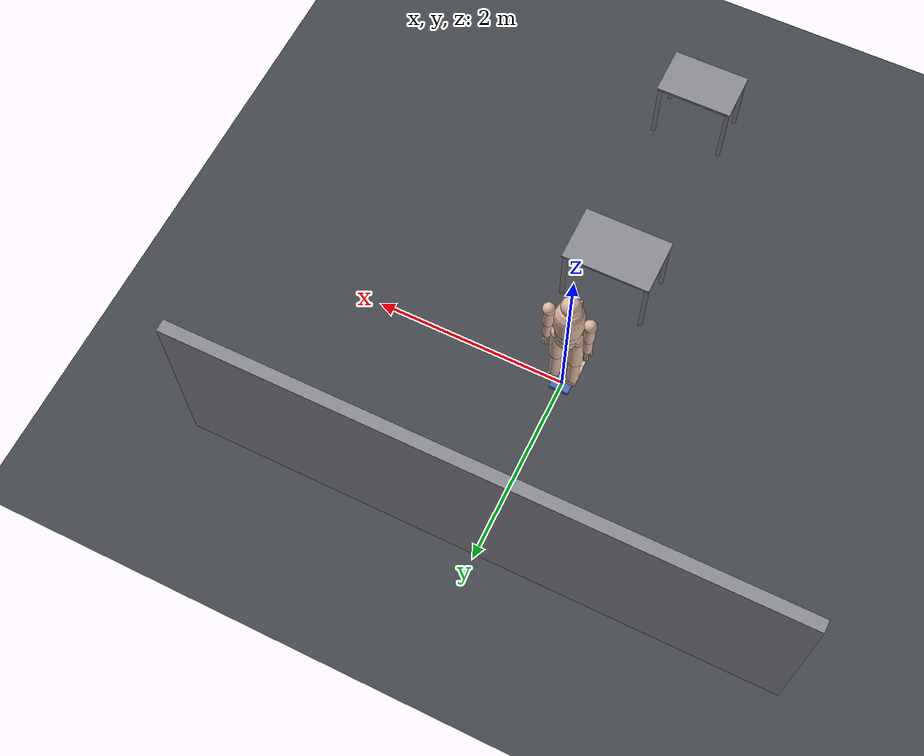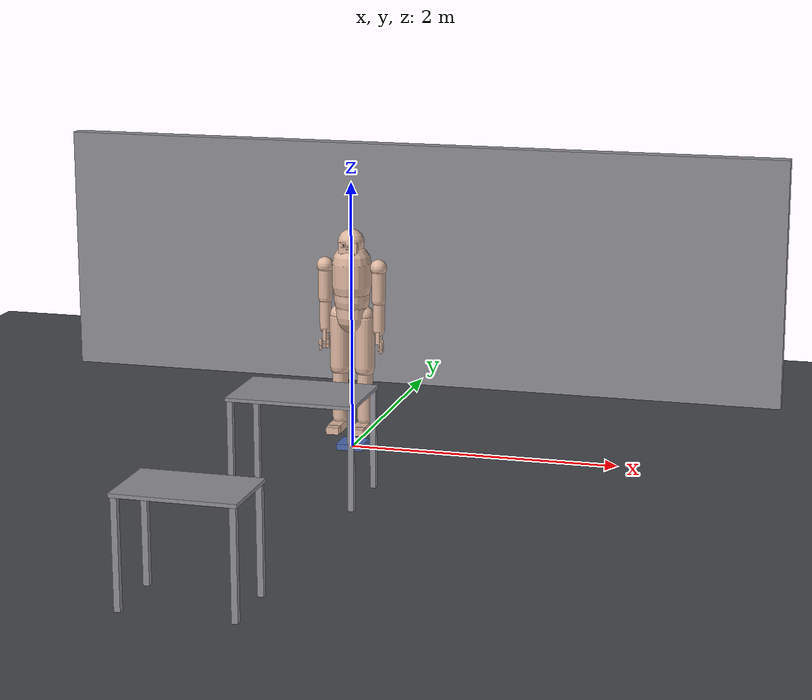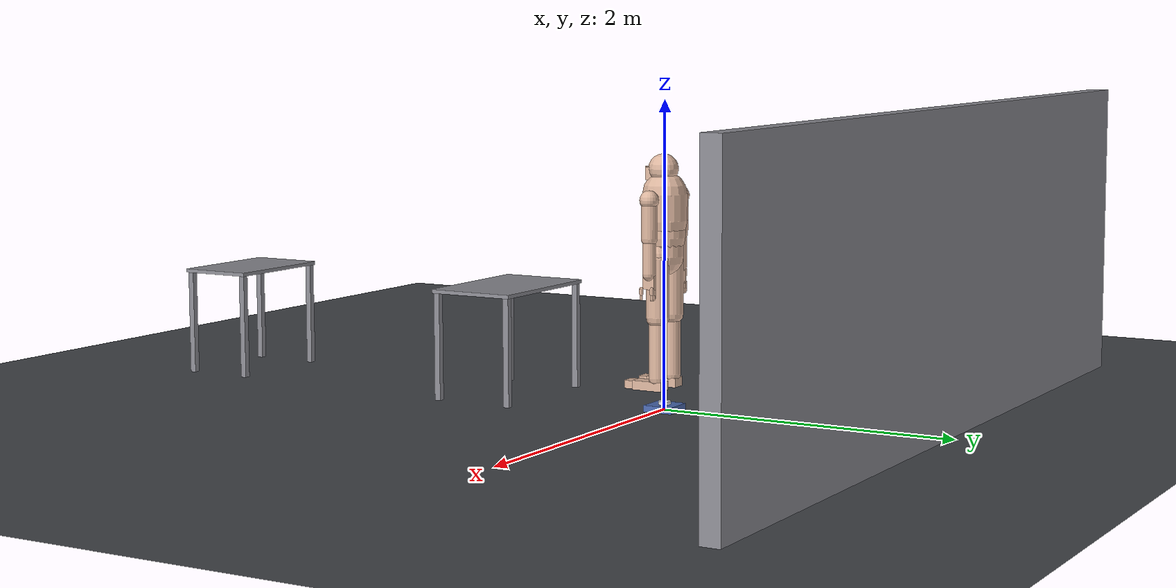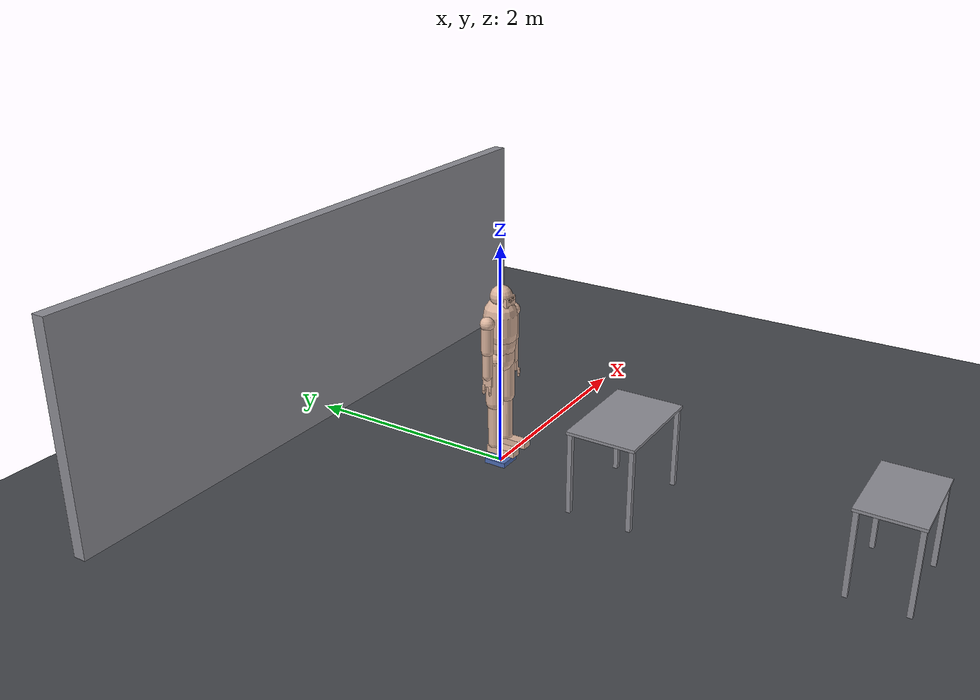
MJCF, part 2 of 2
<site name="tx_upper_arm_r_555" class="skin_site" pos="0.02675 -0.0463324 -0.215235" size="0.01" rgba="1 0.45 0.35 0"/>
              <site name="tx_upper_arm_r_556" class="skin_site" pos="0.0182981 -0.0502736 -0.215235" size="0.01" rgba="1 0.45 0.35 0"/>
              <site name="tx_upper_arm_r_557" class="skin_site" pos="0.00929018 -0.0526872 -0.215235" size="0.01" rgba="1 0.45 0.35 0"/>
              <site name="tx_upper_arm_r_558" class="skin_site" pos="6.55186e-18 -0.0535 -0.215235" size="0.01" rgba="1 0.45 0.35 0"/>
              <site name="tx_upper_arm_r_559" class="skin_site" pos="-0.00929018 -0.0526872 -0.215235" size="0.01" rgba="1 0.45 0.35 0"/>
              <site name="tx_upper_arm_r_560" class="skin_site" pos="-0.0182981 -0.0502736 -0.215235" size="0.01" rgba="1 0.45 0.35 0"/>
              <site name="tx_upper_arm_r_561" class="skin_site" pos="-0.02675 -0.0463324 -0.215235" size="0.01" rgba="1 0.45 0.35 0"/>
              <site name="tx_upper_arm_r_562" class="skin_site" pos="-0.0343891 -0.0409834 -0.215235" size="0.01" rgba="1 0.45 0.35 0"/>
              <site name="tx_upper_arm_r_563" class="skin_site" pos="-0.0409834 -0.0343891 -0.215235" size="0.01" rgba="1 0.45 0.35 0"/>
              <site name="tx_upper_arm_r_564" class="skin_site" pos="-0.0463324 -0.02675 -0.215235" size="0.01" rgba="1 0.45 0.35 0"/>
              <site name="tx_upper_arm_r_565" class="skin_site" pos="-0.0502736 -0.0182981 -0.215235" size="0.01" rgba="1 0.45 0.35 0"/>
              <site name="tx_upper_arm_r_566" class="skin_site" pos="-0.0526872 -0.00929018 -0.215235" size="0.01" rgba="1 0.45 0.35 0"/>
              <site name="tx_upper_arm_r_567" class="skin_site" pos="-0.0535 -9.82779e-18 -0.215235" size="0.01" rgba="1 0.45 0.35 0"/>
              <site name="tx_upper_arm_r_568" class="skin_site" pos="-0.0526872 0.00929018 -0.215235" size="0.01" rgba="1 0.45 0.35 0"/>
              <site name="tx_upper_arm_r_569" class="skin_site" pos="-0.0502736 0.0182981 -0.215235" size="0.01" rgba="1 0.45 0.35 0"/>
              <site name="tx_upper_arm_r_570" class="skin_site" pos="-0.0463324 0.02675 -0.215235" size="0.01" rgba="1 0.45 0.35 0"/>
              <site name="tx_upper_arm_r_571" class="skin_site" pos="-0.0409834 0.0343891 -0.215235" size="0.01" rgba="1 0.45 0.35 0"/>
              <site name="tx_upper_arm_r_572" class="skin_site" pos="-0.0343891 0.0409834 -0.215235" size="0.01" rgba="1 0.45 0.35 0"/>
              <site name="tx_upper_arm_r_573" class="skin_site" pos="-0.02675 0.0463324 -0.215235" size="0.01" rgba="1 0.45 0.35 0"/>
              <site name="tx_upper_arm_r_574" class="skin_site" pos="-0.0182981 0.0502736 -0.215235" size="0.01" rgba="1 0.45 0.35 0"/>
              <site name="tx_upper_arm_r_575" class="skin_site" pos="-0.00929018 0.0526872 -0.215235" size="0.01" rgba="1 0.45 0.35 0"/>
              <site name="tx_upper_arm_r_576" class="skin_site" pos="0 0.0535 -0.227818" size="0.01" rgba="1 0.45 0.35 0"/>
              <site name="tx_upper_arm_r_577" class="skin_site" pos="0.00929018 0.0526872 -0.227818" size="0.01" rgba="1 0.45 0.35 0"/>
              <site name="tx_upper_arm_r_578" class="skin_site" pos="0.0182981 0.0502736 -0.227818" size="0.01" rgba="1 0.45 0.35 0"/>
              <site name="tx_upper_arm_r_579" class="skin_site" pos="0.02675 0.0463324 -0.227818" size="0.01" rgba="1 0.45 0.35 0"/>
              <site name="tx_upper_arm_r_580" class="skin_site" pos="0.0343891 0.0409834 -0.227818" size="0.01" rgba="1 0.45 0.35 0"/>
              <site name="tx_upper_arm_r_581" class="skin_site" pos="0.0409834 0.0343891 -0.227818" size="0.01" rgba="1 0.45 0.35 0"/>
              <site name="tx_upper_arm_r_582" class="skin_site" pos="0.0463324 0.02675 -0.227818" size="0.01" rgba="1 0.45 0.35 0"/>
              <site name="tx_upper_arm_r_583" class="skin_site" pos="0.0502736 0.0182981 -0.227818" size="0.01" rgba="1 0.45 0.35 0"/>
              <site name="tx_upper_arm_r_584" class="skin_site" pos="0.0526872 0.00929018 -0.227818" size="0.01" rgba="1 0.45 0.35 0"/>
              <site name="tx_upper_arm_r_585" class="skin_site" pos="0.0535 3.27593e-18 -0.227818" size="0.01" rgba="1 0.45 0.35 0"/>
              <site name="tx_upper_arm_r_586" class="skin_site" pos="0.0526872 -0.00929018 -0.227818" size="0.01" rgba="1 0.45 0.35 0"/>
              <site name="tx_upper_arm_r_587" class="skin_site" pos="0.0502736 -0.0182981 -0.227818" size="0.01" rgba="1 0.45 0.35 0"/>
              <site name="tx_upper_arm_r_588" class="skin_site" pos="0.0463324 -0.02675 -0.227818" size="0.01" rgba="1 0.45 0.35 0"/>
              <site name="tx_upper_arm_r_589" class="skin_site" pos="0.0409834 -0.0343891 -0.227818" size="0.01" rgba="1 0.45 0.35 0"/>
              <site name="tx_upper_arm_r_590" class="skin_site" pos="0.0343891 -0.0409834 -0.227818" size="0.01" rgba="1 0.45 0.35 0"/>
              <site name="tx_upper_arm_r_591" class="skin_site" pos="0.02675 -0.0463324 -0.227818" size="0.01" rgba="1 0.45 0.35 0"/>
              <site name="tx_upper_arm_r_592" class="skin_site" pos="0.0182981 -0.0502736 -0.227818" size="0.01" rgba="1 0.45 0.35 0"/>
              <site name="tx_upper_arm_r_593" class="skin_site" pos="0.00929018 -0.0526872 -0.227818" size="0.01" rgba="1 0.45 0.35 0"/>
              <site name="tx_upper_arm_r_594" class="skin_site" pos="6.55186e-18 -0.0535 -0.227818" size="0.01" rgba="1 0.45 0.35 0"/>
              <site name="tx_upper_arm_r_595" class="skin_site" pos="-0.00929018 -0.0526872 -0.227818" size="0.01" rgba="1 0.45 0.35 0"/>
              <site name="tx_upper_arm_r_596" class="skin_site" pos="-0.0182981 -0.0502736 -0.227818" size="0.01" rgba="1 0.45 0.35 0"/>
              <site name="tx_upper_arm_r_597" class="skin_site" pos="-0.02675 -0.0463324 -0.227818" size="0.01" rgba="1 0.45 0.35 0"/>
              <site name="tx_upper_arm_r_598" class="skin_site" pos="-0.0343891 -0.0409834 -0.227818" size="0.01" rgba="1 0.45 0.35 0"/>
              <site name="tx_upper_arm_r_599" class="skin_site" pos="-0.0409834 -0.0343891 -0.227818" size="0.01" rgba="1 0.45 0.35 0"/>
              <site name="tx_upper_arm_r_600" class="skin_site" pos="-0.0463324 -0.02675 -0.227818" size="0.01" rgba="1 0.45 0.35 0"/>
              <site name="tx_upper_arm_r_601" class="skin_site" pos="-0.0502736 -0.0182981 -0.227818" size="0.01" rgba="1 0.45 0.35 0"/>
              <site name="tx_upper_arm_r_602" class="skin_site" pos="-0.0526872 -0.00929018 -0.227818" size="0.01" rgba="1 0.45 0.35 0"/>
              <site name="tx_upper_arm_r_603" class="skin_site" pos="-0.0535 -9.82779e-18 -0.227818" size="0.01" rgba="1 0.45 0.35 0"/>
              <site name="tx_upper_arm_r_604" class="skin_site" pos="-0.0526872 0.00929018 -0.227818" size="0.01" rgba="1 0.45 0.35 0"/>
              <site name="tx_upper_arm_r_605" class="skin_site" pos="-0.0502736 0.0182981 -0.227818" size="0.01" rgba="1 0.45 0.35 0"/>
              <site name="tx_upper_arm_r_606" class="skin_site" pos="-0.0463324 0.02675 -0.227818" size="0.01" rgba="1 0.45 0.35 0"/>
              <site name="tx_upper_arm_r_607" class="skin_site" pos="-0.0409834 0.0343891 -0.227818" size="0.01" rgba="1 0.45 0.35 0"/>
              <site name="tx_upper_arm_r_608" class="skin_site" pos="-0.0343891 0.0409834 -0.227818" size="0.01" rgba="1 0.45 0.35 0"/>
              <site name="tx_upper_arm_r_609" class="skin_site" pos="-0.02675 0.0463324 -0.227818" size="0.01" rgba="1 0.45 0.35 0"/>
              <site name="tx_upper_arm_r_610" class="skin_site" pos="-0.0182981 0.0502736 -0.227818" size="0.01" rgba="1 0.45 0.35 0"/>
              <site name="tx_upper_arm_r_611" class="skin_site" pos="-0.00929018 0.0526872 -0.227818" size="0.01" rgba="1 0.45 0.35 0"/>
              <site name="tx_upper_arm_r_612" class="skin_site" pos="0 0.0535 -0.2404" size="0.01" rgba="1 0.45 0.35 0"/>
              <site name="tx_upper_arm_r_613" class="skin_site" pos="0.00929018 0.0526872 -0.2404" size="0.01" rgba="1 0.45 0.35 0"/>
              <site name="tx_upper_arm_r_614" class="skin_site" pos="0.0182981 0.0502736 -0.2404" size="0.01" rgba="1 0.45 0.35 0"/>
              <site name="tx_upper_arm_r_615" class="skin_site" pos="0.02675 0.0463324 -0.2404" size="0.01" rgba="1 0.45 0.35 0"/>
              <site name="tx_upper_arm_r_616" class="skin_site" pos="0.0343891 0.0409834 -0.2404" size="0.01" rgba="1 0.45 0.35 0"/>
              <site name="tx_upper_arm_r_617" class="skin_site" pos="0.0409834 0.0343891 -0.2404" size="0.01" rgba="1 0.45 0.35 0"/>
              <site name="tx_upper_arm_r_618" class="skin_site" pos="0.0463324 0.02675 -0.2404" size="0.01" rgba="1 0.45 0.35 0"/>
              <site name="tx_upper_arm_r_619" class="skin_site" pos="0.0502736 0.0182981 -0.2404" size="0.01" rgba="1 0.45 0.35 0"/>
              <site name="tx_upper_arm_r_620" class="skin_site" pos="0.0526872 0.00929018 -0.2404" size="0.01" rgba="1 0.45 0.35 0"/>
              <site name="tx_upper_arm_r_621" class="skin_site" pos="0.0535 3.27593e-18 -0.2404" size="0.01" rgba="1 0.45 0.35 0"/>
              <site name="tx_upper_arm_r_622" class="skin_site" pos="0.0526872 -0.00929018 -0.2404" size="0.01" rgba="1 0.45 0.35 0"/>
              <site name="tx_upper_arm_r_623" class="skin_site" pos="0.0502736 -0.0182981 -0.2404" size="0.01" rgba="1 0.45 0.35 0"/>
              <site name="tx_upper_arm_r_624" class="skin_site" pos="0.0463324 -0.02675 -0.2404" size="0.01" rgba="1 0.45 0.35 0"/>
              <site name="tx_upper_arm_r_625" class="skin_site" pos="0.0409834 -0.0343891 -0.2404" size="0.01" rgba="1 0.45 0.35 0"/>
              <site name="tx_upper_arm_r_626" class="skin_site" pos="0.0343891 -0.0409834 -0.2404" size="0.01" rgba="1 0.45 0.35 0"/>
              <site name="tx_upper_arm_r_627" class="skin_site" pos="0.02675 -0.0463324 -0.2404" size="0.01" rgba="1 0.45 0.35 0"/>
              <site name="tx_upper_arm_r_628" class="skin_site" pos="0.0182981 -0.0502736 -0.2404" size="0.01" rgba="1 0.45 0.35 0"/>
              <site name="tx_upper_arm_r_629" class="skin_site" pos="0.00929018 -0.0526872 -0.2404" size="0.01" rgba="1 0.45 0.35 0"/>
              <site name="tx_upper_arm_r_630" class="skin_site" pos="6.55186e-18 -0.0535 -0.2404" size="0.01" rgba="1 0.45 0.35 0"/>
              <site name="tx_upper_arm_r_631" class="skin_site" pos="-0.00929018 -0.0526872 -0.2404" size="0.01" rgba="1 0.45 0.35 0"/>
              <site name="tx_upper_arm_r_632" class="skin_site" pos="-0.0182981 -0.0502736 -0.2404" size="0.01" rgba="1 0.45 0.35 0"/>
              <site name="tx_upper_arm_r_633" class="skin_site" pos="-0.02675 -0.0463324 -0.2404" size="0.01" rgba="1 0.45 0.35 0"/>
              <site name="tx_upper_arm_r_634" class="skin_site" pos="-0.0343891 -0.0409834 -0.2404" size="0.01" rgba="1 0.45 0.35 0"/>
              <site name="tx_upper_arm_r_635" class="skin_site" pos="-0.0409834 -0.0343891 -0.2404" size="0.01" rgba="1 0.45 0.35 0"/>
              <site name="tx_upper_arm_r_636" class="skin_site" pos="-0.0463324 -0.02675 -0.2404" size="0.01" rgba="1 0.45 0.35 0"/>
              <site name="tx_upper_arm_r_637" class="skin_site" pos="-0.0502736 -0.0182981 -0.2404" size="0.01" rgba="1 0.45 0.35 0"/>
              <site name="tx_upper_arm_r_638" class="skin_site" pos="-0.0526872 -0.00929018 -0.2404" size="0.01" rgba="1 0.45 0.35 0"/>
              <site name="tx_upper_arm_r_639" class="skin_site" pos="-0.0535 -9.82779e-18 -0.2404" size="0.01" rgba="1 0.45 0.35 0"/>
              <site name="tx_upper_arm_r_640" class="skin_site" pos="-0.0526872 0.00929018 -0.2404" size="0.01" rgba="1 0.45 0.35 0"/>
              <site name="tx_upper_arm_r_641" class="skin_site" pos="-0.0502736 0.0182981 -0.2404" size="0.01" rgba="1 0.45 0.35 0"/>
              <site name="tx_upper_arm_r_642" class="skin_site" pos="-0.0463324 0.02675 -0.2404" size="0.01" rgba="1 0.45 0.35 0"/>
              <site name="tx_upper_arm_r_643" class="skin_site" pos="-0.0409834 0.0343891 -0.2404" size="0.01" rgba="1 0.45 0.35 0"/>
              <site name="tx_upper_arm_r_644" class="skin_site" pos="-0.0343891 0.0409834 -0.2404" size="0.01" rgba="1 0.45 0.35 0"/>
              <site name="tx_upper_arm_r_645" class="skin_site" pos="-0.02675 0.0463324 -0.2404" size="0.01" rgba="1 0.45 0.35 0"/>
              <site name="tx_upper_arm_r_646" class="skin_site" pos="-0.0182981 0.0502736 -0.2404" size="0.01" rgba="1 0.45 0.35 0"/>
              <site name="tx_upper_arm_r_647" class="skin_site" pos="-0.00929018 0.0526872 -0.2404" size="0.01" rgba="1 0.45 0.35 0"/>
              <body name="forearm_r" pos="0 0 -0.255">
                <joint name="elbow_r" type="hinge" axis="1 0 0" range="-2.6 0.02" limited="true" damping="1" frictionloss="0.6" armature="0.05"/>
                <geom name="" class="soma" type="capsule" pos="0 0 -0.1075" quat="0 1 0 0" size="0.044 0.1075" mass="1.425" rgba="0.86 0.71 0.62 1" friction="1 0.02 0.001" contype="65" conaffinity="6"/>
                <site name="tx_forearm_r_000" class="skin_site" pos="0 0.0455 -0.00645" size="0.01" rgba="1 0.45 0.35 0"/>
                <site name="tx_forearm_r_001" class="skin_site" pos="0.00790099 0.0448088 -0.00645" size="0.01" rgba="1 0.45 0.35 0"/>
                <site name="tx_forearm_r_002" class="skin_site" pos="0.0155619 0.042756 -0.00645" size="0.01" rgba="1 0.45 0.35 0"/>
                <site name="tx_forearm_r_003" class="skin_site" pos="0.02275 0.0394042 -0.00645" size="0.01" rgba="1 0.45 0.35 0"/>
                <site name="tx_forearm_r_004" class="skin_site" pos="0.0292468 0.034855 -0.00645" size="0.01" rgba="1 0.45 0.35 0"/>
                <site name="tx_forearm_r_005" class="skin_site" pos="0.034855 0.0292468 -0.00645" size="0.01" rgba="1 0.45 0.35 0"/>
                <site name="tx_forearm_r_006" class="skin_site" pos="0.0394042 0.02275 -0.00645" size="0.01" rgba="1 0.45 0.35 0"/>
                <site name="tx_forearm_r_007" class="skin_site" pos="0.042756 0.0155619 -0.00645" size="0.01" rgba="1 0.45 0.35 0"/>
                <site name="tx_forearm_r_008" class="skin_site" pos="0.0448088 0.00790099 -0.00645" size="0.01" rgba="1 0.45 0.35 0"/>
                <site name="tx_forearm_r_009" class="skin_site" pos="0.0455 2.78607e-18 -0.00645" size="0.01" rgba="1 0.45 0.35 0"/>
                <site name="tx_forearm_r_010" class="skin_site" pos="0.0448088 -0.00790099 -0.00645" size="0.01" rgba="1 0.45 0.35 0"/>
                <site name="tx_forearm_r_011" class="skin_site" pos="0.042756 -0.0155619 -0.00645" size="0.01" rgba="1 0.45 0.35 0"/>
                <site name="tx_forearm_r_012" class="skin_site" pos="0.0394042 -0.02275 -0.00645" size="0.01" rgba="1 0.45 0.35 0"/>
                <site name="tx_forearm_r_013" class="skin_site" pos="0.034855 -0.0292468 -0.00645" size="0.01" rgba="1 0.45 0.35 0"/>
                <site name="tx_forearm_r_014" class="skin_site" pos="0.0292468 -0.034855 -0.00645" size="0.01" rgba="1 0.45 0.35 0"/>
                <site name="tx_forearm_r_015" class="skin_site" pos="0.02275 -0.0394042 -0.00645" size="0.01" rgba="1 0.45 0.35 0"/>
                <site name="tx_forearm_r_016" class="skin_site" pos="0.0155619 -0.042756 -0.00645" size="0.01" rgba="1 0.45 0.35 0"/>
                <site name="tx_forearm_r_017" class="skin_site" pos="0.00790099 -0.0448088 -0.00645" size="0.01" rgba="1 0.45 0.35 0"/>
                <site name="tx_forearm_r_018" class="skin_site" pos="5.57214e-18 -0.0455 -0.00645" size="0.01" rgba="1 0.45 0.35 0"/>
                <site name="tx_forearm_r_019" class="skin_site" pos="-0.00790099 -0.0448088 -0.00645" size="0.01" rgba="1 0.45 0.35 0"/>
                <site name="tx_forearm_r_020" class="skin_site" pos="-0.0155619 -0.042756 -0.00645" size="0.01" rgba="1 0.45 0.35 0"/>
                <site name="tx_forearm_r_021" class="skin_site" pos="-0.02275 -0.0394042 -0.00645" size="0.01" rgba="1 0.45 0.35 0"/>
                <site name="tx_forearm_r_022" class="skin_site" pos="-0.0292468 -0.034855 -0.00645" size="0.01" rgba="1 0.45 0.35 0"/>
                <site name="tx_forearm_r_023" class="skin_site" pos="-0.034855 -0.0292468 -0.00645" size="0.01" rgba="1 0.45 0.35 0"/>
                <site name="tx_forearm_r_024" class="skin_site" pos="-0.0394042 -0.02275 -0.00645" size="0.01" rgba="1 0.45 0.35 0"/>
                <site name="tx_forearm_r_025" class="skin_site" pos="-0.042756 -0.0155619 -0.00645" size="0.01" rgba="1 0.45 0.35 0"/>
                <site name="tx_forearm_r_026" class="skin_site" pos="-0.0448088 -0.00790099 -0.00645" size="0.01" rgba="1 0.45 0.35 0"/>
                <site name="tx_forearm_r_027" class="skin_site" pos="-0.0455 -8.35821e-18 -0.00645" size="0.01" rgba="1 0.45 0.35 0"/>
                <site name="tx_forearm_r_028" class="skin_site" pos="-0.0448088 0.00790099 -0.00645" size="0.01" rgba="1 0.45 0.35 0"/>
                <site name="tx_forearm_r_029" class="skin_site" pos="-0.042756 0.0155619 -0.00645" size="0.01" rgba="1 0.45 0.35 0"/>
                <site name="tx_forearm_r_030" class="skin_site" pos="-0.0394042 0.02275 -0.00645" size="0.01" rgba="1 0.45 0.35 0"/>
                <site name="tx_forearm_r_031" class="skin_site" pos="-0.034855 0.0292468 -0.00645" size="0.01" rgba="1 0.45 0.35 0"/>
                <site name="tx_forearm_r_032" class="skin_site" pos="-0.0292468 0.034855 -0.00645" size="0.01" rgba="1 0.45 0.35 0"/>
                <site name="tx_forearm_r_033" class="skin_site" pos="-0.02275 0.0394042 -0.00645" size="0.01" rgba="1 0.45 0.35 0"/>
                <site name="tx_forearm_r_034" class="skin_site" pos="-0.0155619 0.042756 -0.00645" size="0.01" rgba="1 0.45 0.35 0"/>
                <site name="tx_forearm_r_035" class="skin_site" pos="-0.00790099 0.0448088 -0.00645" size="0.01" rgba="1 0.45 0.35 0"/>
                <site name="tx_forearm_r_036" class="skin_site" pos="0 0.0455 -0.0183382" size="0.01" rgba="1 0.45 0.35 0"/>
                <site name="tx_forearm_r_037" class="skin_site" pos="0.00790099 0.0448088 -0.0183382" size="0.01" rgba="1 0.45 0.35 0"/>
                <site name="tx_forearm_r_038" class="skin_site" pos="0.0155619 0.042756 -0.0183382" size="0.01" rgba="1 0.45 0.35 0"/>
                <site name="tx_forearm_r_039" class="skin_site" pos="0.02275 0.0394042 -0.0183382" size="0.01" rgba="1 0.45 0.35 0"/>
                <site name="tx_forearm_r_040" class="skin_site" pos="0.0292468 0.034855 -0.0183382" size="0.01" rgba="1 0.45 0.35 0"/>
                <site name="tx_forearm_r_041" class="skin_site" pos="0.034855 0.0292468 -0.0183382" size="0.01" rgba="1 0.45 0.35 0"/>
                <site name="tx_forearm_r_042" class="skin_site" pos="0.0394042 0.02275 -0.0183382" size="0.01" rgba="1 0.45 0.35 0"/>
                <site name="tx_forearm_r_043" class="skin_site" pos="0.042756 0.0155619 -0.0183382" size="0.01" rgba="1 0.45 0.35 0"/>
                <site name="tx_forearm_r_044" class="skin_site" pos="0.0448088 0.00790099 -0.0183382" size="0.01" rgba="1 0.45 0.35 0"/>
                <site name="tx_forearm_r_045" class="skin_site" pos="0.0455 2.78607e-18 -0.0183382" size="0.01" rgba="1 0.45 0.35 0"/>
                <site name="tx_forearm_r_046" class="skin_site" pos="0.0448088 -0.00790099 -0.0183382" size="0.01" rgba="1 0.45 0.35 0"/>
                <site name="tx_forearm_r_047" class="skin_site" pos="0.042756 -0.0155619 -0.0183382" size="0.01" rgba="1 0.45 0.35 0"/>
                <site name="tx_forearm_r_048" class="skin_site" pos="0.0394042 -0.02275 -0.0183382" size="0.01" rgba="1 0.45 0.35 0"/>
                <site name="tx_forearm_r_049" class="skin_site" pos="0.034855 -0.0292468 -0.0183382" size="0.01" rgba="1 0.45 0.35 0"/>
                <site name="tx_forearm_r_050" class="skin_site" pos="0.0292468 -0.034855 -0.0183382" size="0.01" rgba="1 0.45 0.35 0"/>
                <site name="tx_forearm_r_051" class="skin_site" pos="0.02275 -0.0394042 -0.0183382" size="0.01" rgba="1 0.45 0.35 0"/>
                <site name="tx_forearm_r_052" class="skin_site" pos="0.0155619 -0.042756 -0.0183382" size="0.01" rgba="1 0.45 0.35 0"/>
                <site name="tx_forearm_r_053" class="skin_site" pos="0.00790099 -0.0448088 -0.0183382" size="0.01" rgba="1 0.45 0.35 0"/>
                <site name="tx_forearm_r_054" class="skin_site" pos="5.57214e-18 -0.0455 -0.0183382" size="0.01" rgba="1 0.45 0.35 0"/>
                <site name="tx_forearm_r_055" class="skin_site" pos="-0.00790099 -0.0448088 -0.0183382" size="0.01" rgba="1 0.45 0.35 0"/>
                <site name="tx_forearm_r_056" class="skin_site" pos="-0.0155619 -0.042756 -0.0183382" size="0.01" rgba="1 0.45 0.35 0"/>
                <site name="tx_forearm_r_057" class="skin_site" pos="-0.02275 -0.0394042 -0.0183382" size="0.01" rgba="1 0.45 0.35 0"/>
                <site name="tx_forearm_r_058" class="skin_site" pos="-0.0292468 -0.034855 -0.0183382" size="0.01" rgba="1 0.45 0.35 0"/>
                <site name="tx_forearm_r_059" class="skin_site" pos="-0.034855 -0.0292468 -0.0183382" size="0.01" rgba="1 0.45 0.35 0"/>
                <site name="tx_forearm_r_060" class="skin_site" pos="-0.0394042 -0.02275 -0.0183382" size="0.01" rgba="1 0.45 0.35 0"/>
                <site name="tx_forearm_r_061" class="skin_site" pos="-0.042756 -0.0155619 -0.0183382" size="0.01" rgba="1 0.45 0.35 0"/>
                <site name="tx_forearm_r_062" class="skin_site" pos="-0.0448088 -0.00790099 -0.0183382" size="0.01" rgba="1 0.45 0.35 0"/>
                <site name="tx_forearm_r_063" class="skin_site" pos="-0.0455 -8.35821e-18 -0.0183382" size="0.01" rgba="1 0.45 0.35 0"/>
                <site name="tx_forearm_r_064" class="skin_site" pos="-0.0448088 0.00790099 -0.0183382" size="0.01" rgba="1 0.45 0.35 0"/>
                <site name="tx_forearm_r_065" class="skin_site" pos="-0.042756 0.0155619 -0.0183382" size="0.01" rgba="1 0.45 0.35 0"/>
                <site name="tx_forearm_r_066" class="skin_site" pos="-0.0394042 0.02275 -0.0183382" size="0.01" rgba="1 0.45 0.35 0"/>
                <site name="tx_forearm_r_067" class="skin_site" pos="-0.034855 0.0292468 -0.0183382" size="0.01" rgba="1 0.45 0.35 0"/>
                <site name="tx_forearm_r_068" class="skin_site" pos="-0.0292468 0.034855 -0.0183382" size="0.01" rgba="1 0.45 0.35 0"/>
                <site name="tx_forearm_r_069" class="skin_site" pos="-0.02275 0.0394042 -0.0183382" size="0.01" rgba="1 0.45 0.35 0"/>
                <site name="tx_forearm_r_070" class="skin_site" pos="-0.0155619 0.042756 -0.0183382" size="0.01" rgba="1 0.45 0.35 0"/>
                <site name="tx_forearm_r_071" class="skin_site" pos="-0.00790099 0.0448088 -0.0183382" size="0.01" rgba="1 0.45 0.35 0"/>
                <site name="tx_forearm_r_072" class="skin_site" pos="0 0.0455 -0.0302265" size="0.01" rgba="1 0.45 0.35 0"/>
                <site name="tx_forearm_r_073" class="skin_site" pos="0.00790099 0.0448088 -0.0302265" size="0.01" rgba="1 0.45 0.35 0"/>
                <site name="tx_forearm_r_074" class="skin_site" pos="0.0155619 0.042756 -0.0302265" size="0.01" rgba="1 0.45 0.35 0"/>
                <site name="tx_forearm_r_075" class="skin_site" pos="0.02275 0.0394042 -0.0302265" size="0.01" rgba="1 0.45 0.35 0"/>
                <site name="tx_forearm_r_076" class="skin_site" pos="0.0292468 0.034855 -0.0302265" size="0.01" rgba="1 0.45 0.35 0"/>
                <site name="tx_forearm_r_077" class="skin_site" pos="0.034855 0.0292468 -0.0302265" size="0.01" rgba="1 0.45 0.35 0"/>
                <site name="tx_forearm_r_078" class="skin_site" pos="0.0394042 0.02275 -0.0302265" size="0.01" rgba="1 0.45 0.35 0"/>
                <site name="tx_forearm_r_079" class="skin_site" pos="0.042756 0.0155619 -0.0302265" size="0.01" rgba="1 0.45 0.35 0"/>
                <site name="tx_forearm_r_080" class="skin_site" pos="0.0448088 0.00790099 -0.0302265" size="0.01" rgba="1 0.45 0.35 0"/>
                <site name="tx_forearm_r_081" class="skin_site" pos="0.0455 2.78607e-18 -0.0302265" size="0.01" rgba="1 0.45 0.35 0"/>
                <site name="tx_forearm_r_082" class="skin_site" pos="0.0448088 -0.00790099 -0.0302265" size="0.01" rgba="1 0.45 0.35 0"/>
                <site name="tx_forearm_r_083" class="skin_site" pos="0.042756 -0.0155619 -0.0302265" size="0.01" rgba="1 0.45 0.35 0"/>
                <site name="tx_forearm_r_084" class="skin_site" pos="0.0394042 -0.02275 -0.0302265" size="0.01" rgba="1 0.45 0.35 0"/>
                <site name="tx_forearm_r_085" class="skin_site" pos="0.034855 -0.0292468 -0.0302265" size="0.01" rgba="1 0.45 0.35 0"/>
                <site name="tx_forearm_r_086" class="skin_site" pos="0.0292468 -0.034855 -0.0302265" size="0.01" rgba="1 0.45 0.35 0"/>
                <site name="tx_forearm_r_087" class="skin_site" pos="0.02275 -0.0394042 -0.0302265" size="0.01" rgba="1 0.45 0.35 0"/>
                <site name="tx_forearm_r_088" class="skin_site" pos="0.0155619 -0.042756 -0.0302265" size="0.01" rgba="1 0.45 0.35 0"/>
                <site name="tx_forearm_r_089" class="skin_site" pos="0.00790099 -0.0448088 -0.0302265" size="0.01" rgba="1 0.45 0.35 0"/>
                <site name="tx_forearm_r_090" class="skin_site" pos="5.57214e-18 -0.0455 -0.0302265" size="0.01" rgba="1 0.45 0.35 0"/>
                <site name="tx_forearm_r_091" class="skin_site" pos="-0.00790099 -0.0448088 -0.0302265" size="0.01" rgba="1 0.45 0.35 0"/>
                <site name="tx_forearm_r_092" class="skin_site" pos="-0.0155619 -0.042756 -0.0302265" size="0.01" rgba="1 0.45 0.35 0"/>
                <site name="tx_forearm_r_093" class="skin_site" pos="-0.02275 -0.0394042 -0.0302265" size="0.01" rgba="1 0.45 0.35 0"/>
                <site name="tx_forearm_r_094" class="skin_site" pos="-0.0292468 -0.034855 -0.0302265" size="0.01" rgba="1 0.45 0.35 0"/>
                <site name="tx_forearm_r_095" class="skin_site" pos="-0.034855 -0.0292468 -0.0302265" size="0.01" rgba="1 0.45 0.35 0"/>
                <site name="tx_forearm_r_096" class="skin_site" pos="-0.0394042 -0.02275 -0.0302265" size="0.01" rgba="1 0.45 0.35 0"/>
                <site name="tx_forearm_r_097" class="skin_site" pos="-0.042756 -0.0155619 -0.0302265" size="0.01" rgba="1 0.45 0.35 0"/>
                <site name="tx_forearm_r_098" class="skin_site" pos="-0.0448088 -0.00790099 -0.0302265" size="0.01" rgba="1 0.45 0.35 0"/>
                <site name="tx_forearm_r_099" class="skin_site" pos="-0.0455 -8.35821e-18 -0.0302265" size="0.01" rgba="1 0.45 0.35 0"/>
                <site name="tx_forearm_r_100" class="skin_site" pos="-0.0448088 0.00790099 -0.0302265" size="0.01" rgba="1 0.45 0.35 0"/>
                <site name="tx_forearm_r_101" class="skin_site" pos="-0.042756 0.0155619 -0.0302265" size="0.01" rgba="1 0.45 0.35 0"/>
                <site name="tx_forearm_r_102" class="skin_site" pos="-0.0394042 0.02275 -0.0302265" size="0.01" rgba="1 0.45 0.35 0"/>
                <site name="tx_forearm_r_103" class="skin_site" pos="-0.034855 0.0292468 -0.0302265" size="0.01" rgba="1 0.45 0.35 0"/>
                <site name="tx_forearm_r_104" class="skin_site" pos="-0.0292468 0.034855 -0.0302265" size="0.01" rgba="1 0.45 0.35 0"/>
                <site name="tx_forearm_r_105" class="skin_site" pos="-0.02275 0.0394042 -0.0302265" size="0.01" rgba="1 0.45 0.35 0"/>
                <site name="tx_forearm_r_106" class="skin_site" pos="-0.0155619 0.042756 -0.0302265" size="0.01" rgba="1 0.45 0.35 0"/>
                <site name="tx_forearm_r_107" class="skin_site" pos="-0.00790099 0.0448088 -0.0302265" size="0.01" rgba="1 0.45 0.35 0"/>
                <site name="tx_forearm_r_108" class="skin_site" pos="0 0.0455 -0.0421147" size="0.01" rgba="1 0.45 0.35 0"/>
                <site name="tx_forearm_r_109" class="skin_site" pos="0.00790099 0.0448088 -0.0421147" size="0.01" rgba="1 0.45 0.35 0"/>
                <site name="tx_forearm_r_110" class="skin_site" pos="0.0155619 0.042756 -0.0421147" size="0.01" rgba="1 0.45 0.35 0"/>
                <site name="tx_forearm_r_111" class="skin_site" pos="0.02275 0.0394042 -0.0421147" size="0.01" rgba="1 0.45 0.35 0"/>
                <site name="tx_forearm_r_112" class="skin_site" pos="0.0292468 0.034855 -0.0421147" size="0.01" rgba="1 0.45 0.35 0"/>
                <site name="tx_forearm_r_113" class="skin_site" pos="0.034855 0.0292468 -0.0421147" size="0.01" rgba="1 0.45 0.35 0"/>
                <site name="tx_forearm_r_114" class="skin_site" pos="0.0394042 0.02275 -0.0421147" size="0.01" rgba="1 0.45 0.35 0"/>
                <site name="tx_forearm_r_115" class="skin_site" pos="0.042756 0.0155619 -0.0421147" size="0.01" rgba="1 0.45 0.35 0"/>
                <site name="tx_forearm_r_116" class="skin_site" pos="0.0448088 0.00790099 -0.0421147" size="0.01" rgba="1 0.45 0.35 0"/>
                <site name="tx_forearm_r_117" class="skin_site" pos="0.0455 2.78607e-18 -0.0421147" size="0.01" rgba="1 0.45 0.35 0"/>
                <site name="tx_forearm_r_118" class="skin_site" pos="0.0448088 -0.00790099 -0.0421147" size="0.01" rgba="1 0.45 0.35 0"/>
                <site name="tx_forearm_r_119" class="skin_site" pos="0.042756 -0.0155619 -0.0421147" size="0.01" rgba="1 0.45 0.35 0"/>
                <site name="tx_forearm_r_120" class="skin_site" pos="0.0394042 -0.02275 -0.0421147" size="0.01" rgba="1 0.45 0.35 0"/>
                <site name="tx_forearm_r_121" class="skin_site" pos="0.034855 -0.0292468 -0.0421147" size="0.01" rgba="1 0.45 0.35 0"/>
                <site name="tx_forearm_r_122" class="skin_site" pos="0.0292468 -0.034855 -0.0421147" size="0.01" rgba="1 0.45 0.35 0"/>
                <site name="tx_forearm_r_123" class="skin_site" pos="0.02275 -0.0394042 -0.0421147" size="0.01" rgba="1 0.45 0.35 0"/>
                <site name="tx_forearm_r_124" class="skin_site" pos="0.0155619 -0.042756 -0.0421147" size="0.01" rgba="1 0.45 0.35 0"/>
                <site name="tx_forearm_r_125" class="skin_site" pos="0.00790099 -0.0448088 -0.0421147" size="0.01" rgba="1 0.45 0.35 0"/>
                <site name="tx_forearm_r_126" class="skin_site" pos="5.57214e-18 -0.0455 -0.0421147" size="0.01" rgba="1 0.45 0.35 0"/>
                <site name="tx_forearm_r_127" class="skin_site" pos="-0.00790099 -0.0448088 -0.0421147" size="0.01" rgba="1 0.45 0.35 0"/>
                <site name="tx_forearm_r_128" class="skin_site" pos="-0.0155619 -0.042756 -0.0421147" size="0.01" rgba="1 0.45 0.35 0"/>
                <site name="tx_forearm_r_129" class="skin_site" pos="-0.02275 -0.0394042 -0.0421147" size="0.01" rgba="1 0.45 0.35 0"/>
                <site name="tx_forearm_r_130" class="skin_site" pos="-0.0292468 -0.034855 -0.0421147" size="0.01" rgba="1 0.45 0.35 0"/>
                <site name="tx_forearm_r_131" class="skin_site" pos="-0.034855 -0.0292468 -0.0421147" size="0.01" rgba="1 0.45 0.35 0"/>
                <site name="tx_forearm_r_132" class="skin_site" pos="-0.0394042 -0.02275 -0.0421147" size="0.01" rgba="1 0.45 0.35 0"/>
                <site name="tx_forearm_r_133" class="skin_site" pos="-0.042756 -0.0155619 -0.0421147" size="0.01" rgba="1 0.45 0.35 0"/>
                <site name="tx_forearm_r_134" class="skin_site" pos="-0.0448088 -0.00790099 -0.0421147" size="0.01" rgba="1 0.45 0.35 0"/>
                <site name="tx_forearm_r_135" class="skin_site" pos="-0.0455 -8.35821e-18 -0.0421147" size="0.01" rgba="1 0.45 0.35 0"/>
                <site name="tx_forearm_r_136" class="skin_site" pos="-0.0448088 0.00790099 -0.0421147" size="0.01" rgba="1 0.45 0.35 0"/>
                <site name="tx_forearm_r_137" class="skin_site" pos="-0.042756 0.0155619 -0.0421147" size="0.01" rgba="1 0.45 0.35 0"/>
                <site name="tx_forearm_r_138" class="skin_site" pos="-0.0394042 0.02275 -0.0421147" size="0.01" rgba="1 0.45 0.35 0"/>
                <site name="tx_forearm_r_139" class="skin_site" pos="-0.034855 0.0292468 -0.0421147" size="0.01" rgba="1 0.45 0.35 0"/>
                <site name="tx_forearm_r_140" class="skin_site" pos="-0.0292468 0.034855 -0.0421147" size="0.01" rgba="1 0.45 0.35 0"/>
                <site name="tx_forearm_r_141" class="skin_site" pos="-0.02275 0.0394042 -0.0421147" size="0.01" rgba="1 0.45 0.35 0"/>
                <site name="tx_forearm_r_142" class="skin_site" pos="-0.0155619 0.042756 -0.0421147" size="0.01" rgba="1 0.45 0.35 0"/>
                <site name="tx_forearm_r_143" class="skin_site" pos="-0.00790099 0.0448088 -0.0421147" size="0.01" rgba="1 0.45 0.35 0"/>
                <site name="tx_forearm_r_144" class="skin_site" pos="0 0.0455 -0.0540029" size="0.01" rgba="1 0.45 0.35 0"/>
                <site name="tx_forearm_r_145" class="skin_site" pos="0.00790099 0.0448088 -0.0540029" size="0.01" rgba="1 0.45 0.35 0"/>
                <site name="tx_forearm_r_146" class="skin_site" pos="0.0155619 0.042756 -0.0540029" size="0.01" rgba="1 0.45 0.35 0"/>
                <site name="tx_forearm_r_147" class="skin_site" pos="0.02275 0.0394042 -0.0540029" size="0.01" rgba="1 0.45 0.35 0"/>
                <site name="tx_forearm_r_148" class="skin_site" pos="0.0292468 0.034855 -0.0540029" size="0.01" rgba="1 0.45 0.35 0"/>
                <site name="tx_forearm_r_149" class="skin_site" pos="0.034855 0.0292468 -0.0540029" size="0.01" rgba="1 0.45 0.35 0"/>
                <site name="tx_forearm_r_150" class="skin_site" pos="0.0394042 0.02275 -0.0540029" size="0.01" rgba="1 0.45 0.35 0"/>
                <site name="tx_forearm_r_151" class="skin_site" pos="0.042756 0.0155619 -0.0540029" size="0.01" rgba="1 0.45 0.35 0"/>
                <site name="tx_forearm_r_152" class="skin_site" pos="0.0448088 0.00790099 -0.0540029" size="0.01" rgba="1 0.45 0.35 0"/>
                <site name="tx_forearm_r_153" class="skin_site" pos="0.0455 2.78607e-18 -0.0540029" size="0.01" rgba="1 0.45 0.35 0"/>
                <site name="tx_forearm_r_154" class="skin_site" pos="0.0448088 -0.00790099 -0.0540029" size="0.01" rgba="1 0.45 0.35 0"/>
                <site name="tx_forearm_r_155" class="skin_site" pos="0.042756 -0.0155619 -0.0540029" size="0.01" rgba="1 0.45 0.35 0"/>
                <site name="tx_forearm_r_156" class="skin_site" pos="0.0394042 -0.02275 -0.0540029" size="0.01" rgba="1 0.45 0.35 0"/>
                <site name="tx_forearm_r_157" class="skin_site" pos="0.034855 -0.0292468 -0.0540029" size="0.01" rgba="1 0.45 0.35 0"/>
                <site name="tx_forearm_r_158" class="skin_site" pos="0.0292468 -0.034855 -0.0540029" size="0.01" rgba="1 0.45 0.35 0"/>
                <site name="tx_forearm_r_159" class="skin_site" pos="0.02275 -0.0394042 -0.0540029" size="0.01" rgba="1 0.45 0.35 0"/>
                <site name="tx_forearm_r_160" class="skin_site" pos="0.0155619 -0.042756 -0.0540029" size="0.01" rgba="1 0.45 0.35 0"/>
                <site name="tx_forearm_r_161" class="skin_site" pos="0.00790099 -0.0448088 -0.0540029" size="0.01" rgba="1 0.45 0.35 0"/>
                <site name="tx_forearm_r_162" class="skin_site" pos="5.57214e-18 -0.0455 -0.0540029" size="0.01" rgba="1 0.45 0.35 0"/>
                <site name="tx_forearm_r_163" class="skin_site" pos="-0.00790099 -0.0448088 -0.0540029" size="0.01" rgba="1 0.45 0.35 0"/>
                <site name="tx_forearm_r_164" class="skin_site" pos="-0.0155619 -0.042756 -0.0540029" size="0.01" rgba="1 0.45 0.35 0"/>
                <site name="tx_forearm_r_165" class="skin_site" pos="-0.02275 -0.0394042 -0.0540029" size="0.01" rgba="1 0.45 0.35 0"/>
                <site name="tx_forearm_r_166" class="skin_site" pos="-0.0292468 -0.034855 -0.0540029" size="0.01" rgba="1 0.45 0.35 0"/>
                <site name="tx_forearm_r_167" class="skin_site" pos="-0.034855 -0.0292468 -0.0540029" size="0.01" rgba="1 0.45 0.35 0"/>
                <site name="tx_forearm_r_168" class="skin_site" pos="-0.0394042 -0.02275 -0.0540029" size="0.01" rgba="1 0.45 0.35 0"/>
                <site name="tx_forearm_r_169" class="skin_site" pos="-0.042756 -0.0155619 -0.0540029" size="0.01" rgba="1 0.45 0.35 0"/>
                <site name="tx_forearm_r_170" class="skin_site" pos="-0.0448088 -0.00790099 -0.0540029" size="0.01" rgba="1 0.45 0.35 0"/>
                <site name="tx_forearm_r_171" class="skin_site" pos="-0.0455 -8.35821e-18 -0.0540029" size="0.01" rgba="1 0.45 0.35 0"/>
                <site name="tx_forearm_r_172" class="skin_site" pos="-0.0448088 0.00790099 -0.0540029" size="0.01" rgba="1 0.45 0.35 0"/>
                <site name="tx_forearm_r_173" class="skin_site" pos="-0.042756 0.0155619 -0.0540029" size="0.01" rgba="1 0.45 0.35 0"/>
                <site name="tx_forearm_r_174" class="skin_site" pos="-0.0394042 0.02275 -0.0540029" size="0.01" rgba="1 0.45 0.35 0"/>
                <site name="tx_forearm_r_175" class="skin_site" pos="-0.034855 0.0292468 -0.0540029" size="0.01" rgba="1 0.45 0.35 0"/>
                <site name="tx_forearm_r_176" class="skin_site" pos="-0.0292468 0.034855 -0.0540029" size="0.01" rgba="1 0.45 0.35 0"/>
                <site name="tx_forearm_r_177" class="skin_site" pos="-0.02275 0.0394042 -0.0540029" size="0.01" rgba="1 0.45 0.35 0"/>
                <site name="tx_forearm_r_178" class="skin_site" pos="-0.0155619 0.042756 -0.0540029" size="0.01" rgba="1 0.45 0.35 0"/>
                <site name="tx_forearm_r_179" class="skin_site" pos="-0.00790099 0.0448088 -0.0540029" size="0.01" rgba="1 0.45 0.35 0"/>
                <site name="tx_forearm_r_180" class="skin_site" pos="0 0.0455 -0.0658912" size="0.01" rgba="1 0.45 0.35 0"/>
                <site name="tx_forearm_r_181" class="skin_site" pos="0.00790099 0.0448088 -0.0658912" size="0.01" rgba="1 0.45 0.35 0"/>
                <site name="tx_forearm_r_182" class="skin_site" pos="0.0155619 0.042756 -0.0658912" size="0.01" rgba="1 0.45 0.35 0"/>
                <site name="tx_forearm_r_183" class="skin_site" pos="0.02275 0.0394042 -0.0658912" size="0.01" rgba="1 0.45 0.35 0"/>
                <site name="tx_forearm_r_184" class="skin_site" pos="0.0292468 0.034855 -0.0658912" size="0.01" rgba="1 0.45 0.35 0"/>
                <site name="tx_forearm_r_185" class="skin_site" pos="0.034855 0.0292468 -0.0658912" size="0.01" rgba="1 0.45 0.35 0"/>
                <site name="tx_forearm_r_186" class="skin_site" pos="0.0394042 0.02275 -0.0658912" size="0.01" rgba="1 0.45 0.35 0"/>
                <site name="tx_forearm_r_187" class="skin_site" pos="0.042756 0.0155619 -0.0658912" size="0.01" rgba="1 0.45 0.35 0"/>
                <site name="tx_forearm_r_188" class="skin_site" pos="0.0448088 0.00790099 -0.0658912" size="0.01" rgba="1 0.45 0.35 0"/>
                <site name="tx_forearm_r_189" class="skin_site" pos="0.0455 2.78607e-18 -0.0658912" size="0.01" rgba="1 0.45 0.35 0"/>
                <site name="tx_forearm_r_190" class="skin_site" pos="0.0448088 -0.00790099 -0.0658912" size="0.01" rgba="1 0.45 0.35 0"/>
                <site name="tx_forearm_r_191" class="skin_site" pos="0.042756 -0.0155619 -0.0658912" size="0.01" rgba="1 0.45 0.35 0"/>
                <site name="tx_forearm_r_192" class="skin_site" pos="0.0394042 -0.02275 -0.0658912" size="0.01" rgba="1 0.45 0.35 0"/>
                <site name="tx_forearm_r_193" class="skin_site" pos="0.034855 -0.0292468 -0.0658912" size="0.01" rgba="1 0.45 0.35 0"/>
                <site name="tx_forearm_r_194" class="skin_site" pos="0.0292468 -0.034855 -0.0658912" size="0.01" rgba="1 0.45 0.35 0"/>
                <site name="tx_forearm_r_195" class="skin_site" pos="0.02275 -0.0394042 -0.0658912" size="0.01" rgba="1 0.45 0.35 0"/>
                <site name="tx_forearm_r_196" class="skin_site" pos="0.0155619 -0.042756 -0.0658912" size="0.01" rgba="1 0.45 0.35 0"/>
                <site name="tx_forearm_r_197" class="skin_site" pos="0.00790099 -0.0448088 -0.0658912" size="0.01" rgba="1 0.45 0.35 0"/>
                <site name="tx_forearm_r_198" class="skin_site" pos="5.57214e-18 -0.0455 -0.0658912" size="0.01" rgba="1 0.45 0.35 0"/>
                <site name="tx_forearm_r_199" class="skin_site" pos="-0.00790099 -0.0448088 -0.0658912" size="0.01" rgba="1 0.45 0.35 0"/>
                <site name="tx_forearm_r_200" class="skin_site" pos="-0.0155619 -0.042756 -0.0658912" size="0.01" rgba="1 0.45 0.35 0"/>
                <site name="tx_forearm_r_201" class="skin_site" pos="-0.02275 -0.0394042 -0.0658912" size="0.01" rgba="1 0.45 0.35 0"/>
                <site name="tx_forearm_r_202" class="skin_site" pos="-0.0292468 -0.034855 -0.0658912" size="0.01" rgba="1 0.45 0.35 0"/>
                <site name="tx_forearm_r_203" class="skin_site" pos="-0.034855 -0.0292468 -0.0658912" size="0.01" rgba="1 0.45 0.35 0"/>
                <site name="tx_forearm_r_204" class="skin_site" pos="-0.0394042 -0.02275 -0.0658912" size="0.01" rgba="1 0.45 0.35 0"/>
                <site name="tx_forearm_r_205" class="skin_site" pos="-0.042756 -0.0155619 -0.0658912" size="0.01" rgba="1 0.45 0.35 0"/>
                <site name="tx_forearm_r_206" class="skin_site" pos="-0.0448088 -0.00790099 -0.0658912" size="0.01" rgba="1 0.45 0.35 0"/>
                <site name="tx_forearm_r_207" class="skin_site" pos="-0.0455 -8.35821e-18 -0.0658912" size="0.01" rgba="1 0.45 0.35 0"/>
                <site name="tx_forearm_r_208" class="skin_site" pos="-0.0448088 0.00790099 -0.0658912" size="0.01" rgba="1 0.45 0.35 0"/>
                <site name="tx_forearm_r_209" class="skin_site" pos="-0.042756 0.0155619 -0.0658912" size="0.01" rgba="1 0.45 0.35 0"/>
                <site name="tx_forearm_r_210" class="skin_site" pos="-0.0394042 0.02275 -0.0658912" size="0.01" rgba="1 0.45 0.35 0"/>
                <site name="tx_forearm_r_211" class="skin_site" pos="-0.034855 0.0292468 -0.0658912" size="0.01" rgba="1 0.45 0.35 0"/>
                <site name="tx_forearm_r_212" class="skin_site" pos="-0.0292468 0.034855 -0.0658912" size="0.01" rgba="1 0.45 0.35 0"/>
                <site name="tx_forearm_r_213" class="skin_site" pos="-0.02275 0.0394042 -0.0658912" size="0.01" rgba="1 0.45 0.35 0"/>
                <site name="tx_forearm_r_214" class="skin_site" pos="-0.0155619 0.042756 -0.0658912" size="0.01" rgba="1 0.45 0.35 0"/>
                <site name="tx_forearm_r_215" class="skin_site" pos="-0.00790099 0.0448088 -0.0658912" size="0.01" rgba="1 0.45 0.35 0"/>
                <site name="tx_forearm_r_216" class="skin_site" pos="0 0.0455 -0.0777794" size="0.01" rgba="1 0.45 0.35 0"/>
                <site name="tx_forearm_r_217" class="skin_site" pos="0.00790099 0.0448088 -0.0777794" size="0.01" rgba="1 0.45 0.35 0"/>
                <site name="tx_forearm_r_218" class="skin_site" pos="0.0155619 0.042756 -0.0777794" size="0.01" rgba="1 0.45 0.35 0"/>
                <site name="tx_forearm_r_219" class="skin_site" pos="0.02275 0.0394042 -0.0777794" size="0.01" rgba="1 0.45 0.35 0"/>
                <site name="tx_forearm_r_220" class="skin_site" pos="0.0292468 0.034855 -0.0777794" size="0.01" rgba="1 0.45 0.35 0"/>
                <site name="tx_forearm_r_221" class="skin_site" pos="0.034855 0.0292468 -0.0777794" size="0.01" rgba="1 0.45 0.35 0"/>
                <site name="tx_forearm_r_222" class="skin_site" pos="0.0394042 0.02275 -0.0777794" size="0.01" rgba="1 0.45 0.35 0"/>
                <site name="tx_forearm_r_223" class="skin_site" pos="0.042756 0.0155619 -0.0777794" size="0.01" rgba="1 0.45 0.35 0"/>
                <site name="tx_forearm_r_224" class="skin_site" pos="0.0448088 0.00790099 -0.0777794" size="0.01" rgba="1 0.45 0.35 0"/>
                <site name="tx_forearm_r_225" class="skin_site" pos="0.0455 2.78607e-18 -0.0777794" size="0.01" rgba="1 0.45 0.35 0"/>
                <site name="tx_forearm_r_226" class="skin_site" pos="0.0448088 -0.00790099 -0.0777794" size="0.01" rgba="1 0.45 0.35 0"/>
                <site name="tx_forearm_r_227" class="skin_site" pos="0.042756 -0.0155619 -0.0777794" size="0.01" rgba="1 0.45 0.35 0"/>
                <site name="tx_forearm_r_228" class="skin_site" pos="0.0394042 -0.02275 -0.0777794" size="0.01" rgba="1 0.45 0.35 0"/>
                <site name="tx_forearm_r_229" class="skin_site" pos="0.034855 -0.0292468 -0.0777794" size="0.01" rgba="1 0.45 0.35 0"/>
                <site name="tx_forearm_r_230" class="skin_site" pos="0.0292468 -0.034855 -0.0777794" size="0.01" rgba="1 0.45 0.35 0"/>
                <site name="tx_forearm_r_231" class="skin_site" pos="0.02275 -0.0394042 -0.0777794" size="0.01" rgba="1 0.45 0.35 0"/>
                <site name="tx_forearm_r_232" class="skin_site" pos="0.0155619 -0.042756 -0.0777794" size="0.01" rgba="1 0.45 0.35 0"/>
                <site name="tx_forearm_r_233" class="skin_site" pos="0.00790099 -0.0448088 -0.0777794" size="0.01" rgba="1 0.45 0.35 0"/>
                <site name="tx_forearm_r_234" class="skin_site" pos="5.57214e-18 -0.0455 -0.0777794" size="0.01" rgba="1 0.45 0.35 0"/>
                <site name="tx_forearm_r_235" class="skin_site" pos="-0.00790099 -0.0448088 -0.0777794" size="0.01" rgba="1 0.45 0.35 0"/>
                <site name="tx_forearm_r_236" class="skin_site" pos="-0.0155619 -0.042756 -0.0777794" size="0.01" rgba="1 0.45 0.35 0"/>
                <site name="tx_forearm_r_237" class="skin_site" pos="-0.02275 -0.0394042 -0.0777794" size="0.01" rgba="1 0.45 0.35 0"/>
                <site name="tx_forearm_r_238" class="skin_site" pos="-0.0292468 -0.034855 -0.0777794" size="0.01" rgba="1 0.45 0.35 0"/>
                <site name="tx_forearm_r_239" class="skin_site" pos="-0.034855 -0.0292468 -0.0777794" size="0.01" rgba="1 0.45 0.35 0"/>
                <site name="tx_forearm_r_240" class="skin_site" pos="-0.0394042 -0.02275 -0.0777794" size="0.01" rgba="1 0.45 0.35 0"/>
                <site name="tx_forearm_r_241" class="skin_site" pos="-0.042756 -0.0155619 -0.0777794" size="0.01" rgba="1 0.45 0.35 0"/>
                <site name="tx_forearm_r_242" class="skin_site" pos="-0.0448088 -0.00790099 -0.0777794" size="0.01" rgba="1 0.45 0.35 0"/>
                <site name="tx_forearm_r_243" class="skin_site" pos="-0.0455 -8.35821e-18 -0.0777794" size="0.01" rgba="1 0.45 0.35 0"/>
                <site name="tx_forearm_r_244" class="skin_site" pos="-0.0448088 0.00790099 -0.0777794" size="0.01" rgba="1 0.45 0.35 0"/>
                <site name="tx_forearm_r_245" class="skin_site" pos="-0.042756 0.0155619 -0.0777794" size="0.01" rgba="1 0.45 0.35 0"/>
                <site name="tx_forearm_r_246" class="skin_site" pos="-0.0394042 0.02275 -0.0777794" size="0.01" rgba="1 0.45 0.35 0"/>
                <site name="tx_forearm_r_247" class="skin_site" pos="-0.034855 0.0292468 -0.0777794" size="0.01" rgba="1 0.45 0.35 0"/>
                <site name="tx_forearm_r_248" class="skin_site" pos="-0.0292468 0.034855 -0.0777794" size="0.01" rgba="1 0.45 0.35 0"/>
                <site name="tx_forearm_r_249" class="skin_site" pos="-0.02275 0.0394042 -0.0777794" size="0.01" rgba="1 0.45 0.35 0"/>
                <site name="tx_forearm_r_250" class="skin_site" pos="-0.0155619 0.042756 -0.0777794" size="0.01" rgba="1 0.45 0.35 0"/>
                <site name="tx_forearm_r_251" class="skin_site" pos="-0.00790099 0.0448088 -0.0777794" size="0.01" rgba="1 0.45 0.35 0"/>
                <site name="tx_forearm_r_252" class="skin_site" pos="0 0.0455 -0.0896676" size="0.01" rgba="1 0.45 0.35 0"/>
                <site name="tx_forearm_r_253" class="skin_site" pos="0.00790099 0.0448088 -0.0896676" size="0.01" rgba="1 0.45 0.35 0"/>
                <site name="tx_forearm_r_254" class="skin_site" pos="0.0155619 0.042756 -0.0896676" size="0.01" rgba="1 0.45 0.35 0"/>
                <site name="tx_forearm_r_255" class="skin_site" pos="0.02275 0.0394042 -0.0896676" size="0.01" rgba="1 0.45 0.35 0"/>
                <site name="tx_forearm_r_256" class="skin_site" pos="0.0292468 0.034855 -0.0896676" size="0.01" rgba="1 0.45 0.35 0"/>
                <site name="tx_forearm_r_257" class="skin_site" pos="0.034855 0.0292468 -0.0896676" size="0.01" rgba="1 0.45 0.35 0"/>
                <site name="tx_forearm_r_258" class="skin_site" pos="0.0394042 0.02275 -0.0896676" size="0.01" rgba="1 0.45 0.35 0"/>
                <site name="tx_forearm_r_259" class="skin_site" pos="0.042756 0.0155619 -0.0896676" size="0.01" rgba="1 0.45 0.35 0"/>
                <site name="tx_forearm_r_260" class="skin_site" pos="0.0448088 0.00790099 -0.0896676" size="0.01" rgba="1 0.45 0.35 0"/>
                <site name="tx_forearm_r_261" class="skin_site" pos="0.0455 2.78607e-18 -0.0896676" size="0.01" rgba="1 0.45 0.35 0"/>
                <site name="tx_forearm_r_262" class="skin_site" pos="0.0448088 -0.00790099 -0.0896676" size="0.01" rgba="1 0.45 0.35 0"/>
                <site name="tx_forearm_r_263" class="skin_site" pos="0.042756 -0.0155619 -0.0896676" size="0.01" rgba="1 0.45 0.35 0"/>
                <site name="tx_forearm_r_264" class="skin_site" pos="0.0394042 -0.02275 -0.0896676" size="0.01" rgba="1 0.45 0.35 0"/>
                <site name="tx_forearm_r_265" class="skin_site" pos="0.034855 -0.0292468 -0.0896676" size="0.01" rgba="1 0.45 0.35 0"/>
                <site name="tx_forearm_r_266" class="skin_site" pos="0.0292468 -0.034855 -0.0896676" size="0.01" rgba="1 0.45 0.35 0"/>
                <site name="tx_forearm_r_267" class="skin_site" pos="0.02275 -0.0394042 -0.0896676" size="0.01" rgba="1 0.45 0.35 0"/>
                <site name="tx_forearm_r_268" class="skin_site" pos="0.0155619 -0.042756 -0.0896676" size="0.01" rgba="1 0.45 0.35 0"/>
                <site name="tx_forearm_r_269" class="skin_site" pos="0.00790099 -0.0448088 -0.0896676" size="0.01" rgba="1 0.45 0.35 0"/>
                <site name="tx_forearm_r_270" class="skin_site" pos="5.57214e-18 -0.0455 -0.0896676" size="0.01" rgba="1 0.45 0.35 0"/>
                <site name="tx_forearm_r_271" class="skin_site" pos="-0.00790099 -0.0448088 -0.0896676" size="0.01" rgba="1 0.45 0.35 0"/>
                <site name="tx_forearm_r_272" class="skin_site" pos="-0.0155619 -0.042756 -0.0896676" size="0.01" rgba="1 0.45 0.35 0"/>
                <site name="tx_forearm_r_273" class="skin_site" pos="-0.02275 -0.0394042 -0.0896676" size="0.01" rgba="1 0.45 0.35 0"/>
                <site name="tx_forearm_r_274" class="skin_site" pos="-0.0292468 -0.034855 -0.0896676" size="0.01" rgba="1 0.45 0.35 0"/>
                <site name="tx_forearm_r_275" class="skin_site" pos="-0.034855 -0.0292468 -0.0896676" size="0.01" rgba="1 0.45 0.35 0"/>
                <site name="tx_forearm_r_276" class="skin_site" pos="-0.0394042 -0.02275 -0.0896676" size="0.01" rgba="1 0.45 0.35 0"/>
                <site name="tx_forearm_r_277" class="skin_site" pos="-0.042756 -0.0155619 -0.0896676" size="0.01" rgba="1 0.45 0.35 0"/>
                <site name="tx_forearm_r_278" class="skin_site" pos="-0.0448088 -0.00790099 -0.0896676" size="0.01" rgba="1 0.45 0.35 0"/>
                <site name="tx_forearm_r_279" class="skin_site" pos="-0.0455 -8.35821e-18 -0.0896676" size="0.01" rgba="1 0.45 0.35 0"/>
                <site name="tx_forearm_r_280" class="skin_site" pos="-0.0448088 0.00790099 -0.0896676" size="0.01" rgba="1 0.45 0.35 0"/>
                <site name="tx_forearm_r_281" class="skin_site" pos="-0.042756 0.0155619 -0.0896676" size="0.01" rgba="1 0.45 0.35 0"/>
                <site name="tx_forearm_r_282" class="skin_site" pos="-0.0394042 0.02275 -0.0896676" size="0.01" rgba="1 0.45 0.35 0"/>
                <site name="tx_forearm_r_283" class="skin_site" pos="-0.034855 0.0292468 -0.0896676" size="0.01" rgba="1 0.45 0.35 0"/>
                <site name="tx_forearm_r_284" class="skin_site" pos="-0.0292468 0.034855 -0.0896676" size="0.01" rgba="1 0.45 0.35 0"/>
                <site name="tx_forearm_r_285" class="skin_site" pos="-0.02275 0.0394042 -0.0896676" size="0.01" rgba="1 0.45 0.35 0"/>
                <site name="tx_forearm_r_286" class="skin_site" pos="-0.0155619 0.042756 -0.0896676" size="0.01" rgba="1 0.45 0.35 0"/>
                <site name="tx_forearm_r_287" class="skin_site" pos="-0.00790099 0.0448088 -0.0896676" size="0.01" rgba="1 0.45 0.35 0"/>
                <site name="tx_forearm_r_288" class="skin_site" pos="0 0.0455 -0.101556" size="0.01" rgba="1 0.45 0.35 0"/>
                <site name="tx_forearm_r_289" class="skin_site" pos="0.00790099 0.0448088 -0.101556" size="0.01" rgba="1 0.45 0.35 0"/>
                <site name="tx_forearm_r_290" class="skin_site" pos="0.0155619 0.042756 -0.101556" size="0.01" rgba="1 0.45 0.35 0"/>
                <site name="tx_forearm_r_291" class="skin_site" pos="0.02275 0.0394042 -0.101556" size="0.01" rgba="1 0.45 0.35 0"/>
                <site name="tx_forearm_r_292" class="skin_site" pos="0.0292468 0.034855 -0.101556" size="0.01" rgba="1 0.45 0.35 0"/>
                <site name="tx_forearm_r_293" class="skin_site" pos="0.034855 0.0292468 -0.101556" size="0.01" rgba="1 0.45 0.35 0"/>
                <site name="tx_forearm_r_294" class="skin_site" pos="0.0394042 0.02275 -0.101556" size="0.01" rgba="1 0.45 0.35 0"/>
                <site name="tx_forearm_r_295" class="skin_site" pos="0.042756 0.0155619 -0.101556" size="0.01" rgba="1 0.45 0.35 0"/>
                <site name="tx_forearm_r_296" class="skin_site" pos="0.0448088 0.00790099 -0.101556" size="0.01" rgba="1 0.45 0.35 0"/>
                <site name="tx_forearm_r_297" class="skin_site" pos="0.0455 2.78607e-18 -0.101556" size="0.01" rgba="1 0.45 0.35 0"/>
                <site name="tx_forearm_r_298" class="skin_site" pos="0.0448088 -0.00790099 -0.101556" size="0.01" rgba="1 0.45 0.35 0"/>
                <site name="tx_forearm_r_299" class="skin_site" pos="0.042756 -0.0155619 -0.101556" size="0.01" rgba="1 0.45 0.35 0"/>
                <site name="tx_forearm_r_300" class="skin_site" pos="0.0394042 -0.02275 -0.101556" size="0.01" rgba="1 0.45 0.35 0"/>
                <site name="tx_forearm_r_301" class="skin_site" pos="0.034855 -0.0292468 -0.101556" size="0.01" rgba="1 0.45 0.35 0"/>
                <site name="tx_forearm_r_302" class="skin_site" pos="0.0292468 -0.034855 -0.101556" size="0.01" rgba="1 0.45 0.35 0"/>
                <site name="tx_forearm_r_303" class="skin_site" pos="0.02275 -0.0394042 -0.101556" size="0.01" rgba="1 0.45 0.35 0"/>
                <site name="tx_forearm_r_304" class="skin_site" pos="0.0155619 -0.042756 -0.101556" size="0.01" rgba="1 0.45 0.35 0"/>
                <site name="tx_forearm_r_305" class="skin_site" pos="0.00790099 -0.0448088 -0.101556" size="0.01" rgba="1 0.45 0.35 0"/>
                <site name="tx_forearm_r_306" class="skin_site" pos="5.57214e-18 -0.0455 -0.101556" size="0.01" rgba="1 0.45 0.35 0"/>
                <site name="tx_forearm_r_307" class="skin_site" pos="-0.00790099 -0.0448088 -0.101556" size="0.01" rgba="1 0.45 0.35 0"/>
                <site name="tx_forearm_r_308" class="skin_site" pos="-0.0155619 -0.042756 -0.101556" size="0.01" rgba="1 0.45 0.35 0"/>
                <site name="tx_forearm_r_309" class="skin_site" pos="-0.02275 -0.0394042 -0.101556" size="0.01" rgba="1 0.45 0.35 0"/>
                <site name="tx_forearm_r_310" class="skin_site" pos="-0.0292468 -0.034855 -0.101556" size="0.01" rgba="1 0.45 0.35 0"/>
                <site name="tx_forearm_r_311" class="skin_site" pos="-0.034855 -0.0292468 -0.101556" size="0.01" rgba="1 0.45 0.35 0"/>
                <site name="tx_forearm_r_312" class="skin_site" pos="-0.0394042 -0.02275 -0.101556" size="0.01" rgba="1 0.45 0.35 0"/>
                <site name="tx_forearm_r_313" class="skin_site" pos="-0.042756 -0.0155619 -0.101556" size="0.01" rgba="1 0.45 0.35 0"/>
                <site name="tx_forearm_r_314" class="skin_site" pos="-0.0448088 -0.00790099 -0.101556" size="0.01" rgba="1 0.45 0.35 0"/>
                <site name="tx_forearm_r_315" class="skin_site" pos="-0.0455 -8.35821e-18 -0.101556" size="0.01" rgba="1 0.45 0.35 0"/>
                <site name="tx_forearm_r_316" class="skin_site" pos="-0.0448088 0.00790099 -0.101556" size="0.01" rgba="1 0.45 0.35 0"/>
                <site name="tx_forearm_r_317" class="skin_site" pos="-0.042756 0.0155619 -0.101556" size="0.01" rgba="1 0.45 0.35 0"/>
                <site name="tx_forearm_r_318" class="skin_site" pos="-0.0394042 0.02275 -0.101556" size="0.01" rgba="1 0.45 0.35 0"/>
                <site name="tx_forearm_r_319" class="skin_site" pos="-0.034855 0.0292468 -0.101556" size="0.01" rgba="1 0.45 0.35 0"/>
                <site name="tx_forearm_r_320" class="skin_site" pos="-0.0292468 0.034855 -0.101556" size="0.01" rgba="1 0.45 0.35 0"/>
                <site name="tx_forearm_r_321" class="skin_site" pos="-0.02275 0.0394042 -0.101556" size="0.01" rgba="1 0.45 0.35 0"/>
                <site name="tx_forearm_r_322" class="skin_site" pos="-0.0155619 0.042756 -0.101556" size="0.01" rgba="1 0.45 0.35 0"/>
                <site name="tx_forearm_r_323" class="skin_site" pos="-0.00790099 0.0448088 -0.101556" size="0.01" rgba="1 0.45 0.35 0"/>
                <site name="tx_forearm_r_324" class="skin_site" pos="0 0.0455 -0.113444" size="0.01" rgba="1 0.45 0.35 0"/>
                <site name="tx_forearm_r_325" class="skin_site" pos="0.00790099 0.0448088 -0.113444" size="0.01" rgba="1 0.45 0.35 0"/>
                <site name="tx_forearm_r_326" class="skin_site" pos="0.0155619 0.042756 -0.113444" size="0.01" rgba="1 0.45 0.35 0"/>
                <site name="tx_forearm_r_327" class="skin_site" pos="0.02275 0.0394042 -0.113444" size="0.01" rgba="1 0.45 0.35 0"/>
                <site name="tx_forearm_r_328" class="skin_site" pos="0.0292468 0.034855 -0.113444" size="0.01" rgba="1 0.45 0.35 0"/>
                <site name="tx_forearm_r_329" class="skin_site" pos="0.034855 0.0292468 -0.113444" size="0.01" rgba="1 0.45 0.35 0"/>
                <site name="tx_forearm_r_330" class="skin_site" pos="0.0394042 0.02275 -0.113444" size="0.01" rgba="1 0.45 0.35 0"/>
                <site name="tx_forearm_r_331" class="skin_site" pos="0.042756 0.0155619 -0.113444" size="0.01" rgba="1 0.45 0.35 0"/>
                <site name="tx_forearm_r_332" class="skin_site" pos="0.0448088 0.00790099 -0.113444" size="0.01" rgba="1 0.45 0.35 0"/>
                <site name="tx_forearm_r_333" class="skin_site" pos="0.0455 2.78607e-18 -0.113444" size="0.01" rgba="1 0.45 0.35 0"/>
                <site name="tx_forearm_r_334" class="skin_site" pos="0.0448088 -0.00790099 -0.113444" size="0.01" rgba="1 0.45 0.35 0"/>
                <site name="tx_forearm_r_335" class="skin_site" pos="0.042756 -0.0155619 -0.113444" size="0.01" rgba="1 0.45 0.35 0"/>
                <site name="tx_forearm_r_336" class="skin_site" pos="0.0394042 -0.02275 -0.113444" size="0.01" rgba="1 0.45 0.35 0"/>
                <site name="tx_forearm_r_337" class="skin_site" pos="0.034855 -0.0292468 -0.113444" size="0.01" rgba="1 0.45 0.35 0"/>
                <site name="tx_forearm_r_338" class="skin_site" pos="0.0292468 -0.034855 -0.113444" size="0.01" rgba="1 0.45 0.35 0"/>
                <site name="tx_forearm_r_339" class="skin_site" pos="0.02275 -0.0394042 -0.113444" size="0.01" rgba="1 0.45 0.35 0"/>
                <site name="tx_forearm_r_340" class="skin_site" pos="0.0155619 -0.042756 -0.113444" size="0.01" rgba="1 0.45 0.35 0"/>
                <site name="tx_forearm_r_341" class="skin_site" pos="0.00790099 -0.0448088 -0.113444" size="0.01" rgba="1 0.45 0.35 0"/>
                <site name="tx_forearm_r_342" class="skin_site" pos="5.57214e-18 -0.0455 -0.113444" size="0.01" rgba="1 0.45 0.35 0"/>
                <site name="tx_forearm_r_343" class="skin_site" pos="-0.00790099 -0.0448088 -0.113444" size="0.01" rgba="1 0.45 0.35 0"/>
                <site name="tx_forearm_r_344" class="skin_site" pos="-0.0155619 -0.042756 -0.113444" size="0.01" rgba="1 0.45 0.35 0"/>
                <site name="tx_forearm_r_345" class="skin_site" pos="-0.02275 -0.0394042 -0.113444" size="0.01" rgba="1 0.45 0.35 0"/>
                <site name="tx_forearm_r_346" class="skin_site" pos="-0.0292468 -0.034855 -0.113444" size="0.01" rgba="1 0.45 0.35 0"/>
                <site name="tx_forearm_r_347" class="skin_site" pos="-0.034855 -0.0292468 -0.113444" size="0.01" rgba="1 0.45 0.35 0"/>
                <site name="tx_forearm_r_348" class="skin_site" pos="-0.0394042 -0.02275 -0.113444" size="0.01" rgba="1 0.45 0.35 0"/>
                <site name="tx_forearm_r_349" class="skin_site" pos="-0.042756 -0.0155619 -0.113444" size="0.01" rgba="1 0.45 0.35 0"/>
                <site name="tx_forearm_r_350" class="skin_site" pos="-0.0448088 -0.00790099 -0.113444" size="0.01" rgba="1 0.45 0.35 0"/>
                <site name="tx_forearm_r_351" class="skin_site" pos="-0.0455 -8.35821e-18 -0.113444" size="0.01" rgba="1 0.45 0.35 0"/>
                <site name="tx_forearm_r_352" class="skin_site" pos="-0.0448088 0.00790099 -0.113444" size="0.01" rgba="1 0.45 0.35 0"/>
                <site name="tx_forearm_r_353" class="skin_site" pos="-0.042756 0.0155619 -0.113444" size="0.01" rgba="1 0.45 0.35 0"/>
                <site name="tx_forearm_r_354" class="skin_site" pos="-0.0394042 0.02275 -0.113444" size="0.01" rgba="1 0.45 0.35 0"/>
                <site name="tx_forearm_r_355" class="skin_site" pos="-0.034855 0.0292468 -0.113444" size="0.01" rgba="1 0.45 0.35 0"/>
                <site name="tx_forearm_r_356" class="skin_site" pos="-0.0292468 0.034855 -0.113444" size="0.01" rgba="1 0.45 0.35 0"/>
                <site name="tx_forearm_r_357" class="skin_site" pos="-0.02275 0.0394042 -0.113444" size="0.01" rgba="1 0.45 0.35 0"/>
                <site name="tx_forearm_r_358" class="skin_site" pos="-0.0155619 0.042756 -0.113444" size="0.01" rgba="1 0.45 0.35 0"/>
                <site name="tx_forearm_r_359" class="skin_site" pos="-0.00790099 0.0448088 -0.113444" size="0.01" rgba="1 0.45 0.35 0"/>
                <site name="tx_forearm_r_360" class="skin_site" pos="0 0.0455 -0.125332" size="0.01" rgba="1 0.45 0.35 0"/>
                <site name="tx_forearm_r_361" class="skin_site" pos="0.00790099 0.0448088 -0.125332" size="0.01" rgba="1 0.45 0.35 0"/>
                <site name="tx_forearm_r_362" class="skin_site" pos="0.0155619 0.042756 -0.125332" size="0.01" rgba="1 0.45 0.35 0"/>
                <site name="tx_forearm_r_363" class="skin_site" pos="0.02275 0.0394042 -0.125332" size="0.01" rgba="1 0.45 0.35 0"/>
                <site name="tx_forearm_r_364" class="skin_site" pos="0.0292468 0.034855 -0.125332" size="0.01" rgba="1 0.45 0.35 0"/>
                <site name="tx_forearm_r_365" class="skin_site" pos="0.034855 0.0292468 -0.125332" size="0.01" rgba="1 0.45 0.35 0"/>
                <site name="tx_forearm_r_366" class="skin_site" pos="0.0394042 0.02275 -0.125332" size="0.01" rgba="1 0.45 0.35 0"/>
                <site name="tx_forearm_r_367" class="skin_site" pos="0.042756 0.0155619 -0.125332" size="0.01" rgba="1 0.45 0.35 0"/>
                <site name="tx_forearm_r_368" class="skin_site" pos="0.0448088 0.00790099 -0.125332" size="0.01" rgba="1 0.45 0.35 0"/>
                <site name="tx_forearm_r_369" class="skin_site" pos="0.0455 2.78607e-18 -0.125332" size="0.01" rgba="1 0.45 0.35 0"/>
                <site name="tx_forearm_r_370" class="skin_site" pos="0.0448088 -0.00790099 -0.125332" size="0.01" rgba="1 0.45 0.35 0"/>
                <site name="tx_forearm_r_371" class="skin_site" pos="0.042756 -0.0155619 -0.125332" size="0.01" rgba="1 0.45 0.35 0"/>
                <site name="tx_forearm_r_372" class="skin_site" pos="0.0394042 -0.02275 -0.125332" size="0.01" rgba="1 0.45 0.35 0"/>
                <site name="tx_forearm_r_373" class="skin_site" pos="0.034855 -0.0292468 -0.125332" size="0.01" rgba="1 0.45 0.35 0"/>
                <site name="tx_forearm_r_374" class="skin_site" pos="0.0292468 -0.034855 -0.125332" size="0.01" rgba="1 0.45 0.35 0"/>
                <site name="tx_forearm_r_375" class="skin_site" pos="0.02275 -0.0394042 -0.125332" size="0.01" rgba="1 0.45 0.35 0"/>
                <site name="tx_forearm_r_376" class="skin_site" pos="0.0155619 -0.042756 -0.125332" size="0.01" rgba="1 0.45 0.35 0"/>
                <site name="tx_forearm_r_377" class="skin_site" pos="0.00790099 -0.0448088 -0.125332" size="0.01" rgba="1 0.45 0.35 0"/>
                <site name="tx_forearm_r_378" class="skin_site" pos="5.57214e-18 -0.0455 -0.125332" size="0.01" rgba="1 0.45 0.35 0"/>
                <site name="tx_forearm_r_379" class="skin_site" pos="-0.00790099 -0.0448088 -0.125332" size="0.01" rgba="1 0.45 0.35 0"/>
                <site name="tx_forearm_r_380" class="skin_site" pos="-0.0155619 -0.042756 -0.125332" size="0.01" rgba="1 0.45 0.35 0"/>
                <site name="tx_forearm_r_381" class="skin_site" pos="-0.02275 -0.0394042 -0.125332" size="0.01" rgba="1 0.45 0.35 0"/>
                <site name="tx_forearm_r_382" class="skin_site" pos="-0.0292468 -0.034855 -0.125332" size="0.01" rgba="1 0.45 0.35 0"/>
                <site name="tx_forearm_r_383" class="skin_site" pos="-0.034855 -0.0292468 -0.125332" size="0.01" rgba="1 0.45 0.35 0"/>
                <site name="tx_forearm_r_384" class="skin_site" pos="-0.0394042 -0.02275 -0.125332" size="0.01" rgba="1 0.45 0.35 0"/>
                <site name="tx_forearm_r_385" class="skin_site" pos="-0.042756 -0.0155619 -0.125332" size="0.01" rgba="1 0.45 0.35 0"/>
                <site name="tx_forearm_r_386" class="skin_site" pos="-0.0448088 -0.00790099 -0.125332" size="0.01" rgba="1 0.45 0.35 0"/>
                <site name="tx_forearm_r_387" class="skin_site" pos="-0.0455 -8.35821e-18 -0.125332" size="0.01" rgba="1 0.45 0.35 0"/>
                <site name="tx_forearm_r_388" class="skin_site" pos="-0.0448088 0.00790099 -0.125332" size="0.01" rgba="1 0.45 0.35 0"/>
                <site name="tx_forearm_r_389" class="skin_site" pos="-0.042756 0.0155619 -0.125332" size="0.01" rgba="1 0.45 0.35 0"/>
                <site name="tx_forearm_r_390" class="skin_site" pos="-0.0394042 0.02275 -0.125332" size="0.01" rgba="1 0.45 0.35 0"/>
                <site name="tx_forearm_r_391" class="skin_site" pos="-0.034855 0.0292468 -0.125332" size="0.01" rgba="1 0.45 0.35 0"/>
                <site name="tx_forearm_r_392" class="skin_site" pos="-0.0292468 0.034855 -0.125332" size="0.01" rgba="1 0.45 0.35 0"/>
                <site name="tx_forearm_r_393" class="skin_site" pos="-0.02275 0.0394042 -0.125332" size="0.01" rgba="1 0.45 0.35 0"/>
                <site name="tx_forearm_r_394" class="skin_site" pos="-0.0155619 0.042756 -0.125332" size="0.01" rgba="1 0.45 0.35 0"/>
                <site name="tx_forearm_r_395" class="skin_site" pos="-0.00790099 0.0448088 -0.125332" size="0.01" rgba="1 0.45 0.35 0"/>
                <site name="tx_forearm_r_396" class="skin_site" pos="0 0.0455 -0.137221" size="0.01" rgba="1 0.45 0.35 0"/>
                <site name="tx_forearm_r_397" class="skin_site" pos="0.00790099 0.0448088 -0.137221" size="0.01" rgba="1 0.45 0.35 0"/>
                <site name="tx_forearm_r_398" class="skin_site" pos="0.0155619 0.042756 -0.137221" size="0.01" rgba="1 0.45 0.35 0"/>
                <site name="tx_forearm_r_399" class="skin_site" pos="0.02275 0.0394042 -0.137221" size="0.01" rgba="1 0.45 0.35 0"/>
                <site name="tx_forearm_r_400" class="skin_site" pos="0.0292468 0.034855 -0.137221" size="0.01" rgba="1 0.45 0.35 0"/>
                <site name="tx_forearm_r_401" class="skin_site" pos="0.034855 0.0292468 -0.137221" size="0.01" rgba="1 0.45 0.35 0"/>
                <site name="tx_forearm_r_402" class="skin_site" pos="0.0394042 0.02275 -0.137221" size="0.01" rgba="1 0.45 0.35 0"/>
                <site name="tx_forearm_r_403" class="skin_site" pos="0.042756 0.0155619 -0.137221" size="0.01" rgba="1 0.45 0.35 0"/>
                <site name="tx_forearm_r_404" class="skin_site" pos="0.0448088 0.00790099 -0.137221" size="0.01" rgba="1 0.45 0.35 0"/>
                <site name="tx_forearm_r_405" class="skin_site" pos="0.0455 2.78607e-18 -0.137221" size="0.01" rgba="1 0.45 0.35 0"/>
                <site name="tx_forearm_r_406" class="skin_site" pos="0.0448088 -0.00790099 -0.137221" size="0.01" rgba="1 0.45 0.35 0"/>
                <site name="tx_forearm_r_407" class="skin_site" pos="0.042756 -0.0155619 -0.137221" size="0.01" rgba="1 0.45 0.35 0"/>
                <site name="tx_forearm_r_408" class="skin_site" pos="0.0394042 -0.02275 -0.137221" size="0.01" rgba="1 0.45 0.35 0"/>
                <site name="tx_forearm_r_409" class="skin_site" pos="0.034855 -0.0292468 -0.137221" size="0.01" rgba="1 0.45 0.35 0"/>
                <site name="tx_forearm_r_410" class="skin_site" pos="0.0292468 -0.034855 -0.137221" size="0.01" rgba="1 0.45 0.35 0"/>
                <site name="tx_forearm_r_411" class="skin_site" pos="0.02275 -0.0394042 -0.137221" size="0.01" rgba="1 0.45 0.35 0"/>
                <site name="tx_forearm_r_412" class="skin_site" pos="0.0155619 -0.042756 -0.137221" size="0.01" rgba="1 0.45 0.35 0"/>
                <site name="tx_forearm_r_413" class="skin_site" pos="0.00790099 -0.0448088 -0.137221" size="0.01" rgba="1 0.45 0.35 0"/>
                <site name="tx_forearm_r_414" class="skin_site" pos="5.57214e-18 -0.0455 -0.137221" size="0.01" rgba="1 0.45 0.35 0"/>
                <site name="tx_forearm_r_415" class="skin_site" pos="-0.00790099 -0.0448088 -0.137221" size="0.01" rgba="1 0.45 0.35 0"/>
                <site name="tx_forearm_r_416" class="skin_site" pos="-0.0155619 -0.042756 -0.137221" size="0.01" rgba="1 0.45 0.35 0"/>
                <site name="tx_forearm_r_417" class="skin_site" pos="-0.02275 -0.0394042 -0.137221" size="0.01" rgba="1 0.45 0.35 0"/>
                <site name="tx_forearm_r_418" class="skin_site" pos="-0.0292468 -0.034855 -0.137221" size="0.01" rgba="1 0.45 0.35 0"/>
                <site name="tx_forearm_r_419" class="skin_site" pos="-0.034855 -0.0292468 -0.137221" size="0.01" rgba="1 0.45 0.35 0"/>
                <site name="tx_forearm_r_420" class="skin_site" pos="-0.0394042 -0.02275 -0.137221" size="0.01" rgba="1 0.45 0.35 0"/>
                <site name="tx_forearm_r_421" class="skin_site" pos="-0.042756 -0.0155619 -0.137221" size="0.01" rgba="1 0.45 0.35 0"/>
                <site name="tx_forearm_r_422" class="skin_site" pos="-0.0448088 -0.00790099 -0.137221" size="0.01" rgba="1 0.45 0.35 0"/>
                <site name="tx_forearm_r_423" class="skin_site" pos="-0.0455 -8.35821e-18 -0.137221" size="0.01" rgba="1 0.45 0.35 0"/>
                <site name="tx_forearm_r_424" class="skin_site" pos="-0.0448088 0.00790099 -0.137221" size="0.01" rgba="1 0.45 0.35 0"/>
                <site name="tx_forearm_r_425" class="skin_site" pos="-0.042756 0.0155619 -0.137221" size="0.01" rgba="1 0.45 0.35 0"/>
                <site name="tx_forearm_r_426" class="skin_site" pos="-0.0394042 0.02275 -0.137221" size="0.01" rgba="1 0.45 0.35 0"/>
                <site name="tx_forearm_r_427" class="skin_site" pos="-0.034855 0.0292468 -0.137221" size="0.01" rgba="1 0.45 0.35 0"/>
                <site name="tx_forearm_r_428" class="skin_site" pos="-0.0292468 0.034855 -0.137221" size="0.01" rgba="1 0.45 0.35 0"/>
                <site name="tx_forearm_r_429" class="skin_site" pos="-0.02275 0.0394042 -0.137221" size="0.01" rgba="1 0.45 0.35 0"/>
                <site name="tx_forearm_r_430" class="skin_site" pos="-0.0155619 0.042756 -0.137221" size="0.01" rgba="1 0.45 0.35 0"/>
                <site name="tx_forearm_r_431" class="skin_site" pos="-0.00790099 0.0448088 -0.137221" size="0.01" rgba="1 0.45 0.35 0"/>
                <site name="tx_forearm_r_432" class="skin_site" pos="0 0.0455 -0.149109" size="0.01" rgba="1 0.45 0.35 0"/>
                <site name="tx_forearm_r_433" class="skin_site" pos="0.00790099 0.0448088 -0.149109" size="0.01" rgba="1 0.45 0.35 0"/>
                <site name="tx_forearm_r_434" class="skin_site" pos="0.0155619 0.042756 -0.149109" size="0.01" rgba="1 0.45 0.35 0"/>
                <site name="tx_forearm_r_435" class="skin_site" pos="0.02275 0.0394042 -0.149109" size="0.01" rgba="1 0.45 0.35 0"/>
                <site name="tx_forearm_r_436" class="skin_site" pos="0.0292468 0.034855 -0.149109" size="0.01" rgba="1 0.45 0.35 0"/>
                <site name="tx_forearm_r_437" class="skin_site" pos="0.034855 0.0292468 -0.149109" size="0.01" rgba="1 0.45 0.35 0"/>
                <site name="tx_forearm_r_438" class="skin_site" pos="0.0394042 0.02275 -0.149109" size="0.01" rgba="1 0.45 0.35 0"/>
                <site name="tx_forearm_r_439" class="skin_site" pos="0.042756 0.0155619 -0.149109" size="0.01" rgba="1 0.45 0.35 0"/>
                <site name="tx_forearm_r_440" class="skin_site" pos="0.0448088 0.00790099 -0.149109" size="0.01" rgba="1 0.45 0.35 0"/>
                <site name="tx_forearm_r_441" class="skin_site" pos="0.0455 2.78607e-18 -0.149109" size="0.01" rgba="1 0.45 0.35 0"/>
                <site name="tx_forearm_r_442" class="skin_site" pos="0.0448088 -0.00790099 -0.149109" size="0.01" rgba="1 0.45 0.35 0"/>
                <site name="tx_forearm_r_443" class="skin_site" pos="0.042756 -0.0155619 -0.149109" size="0.01" rgba="1 0.45 0.35 0"/>
                <site name="tx_forearm_r_444" class="skin_site" pos="0.0394042 -0.02275 -0.149109" size="0.01" rgba="1 0.45 0.35 0"/>
                <site name="tx_forearm_r_445" class="skin_site" pos="0.034855 -0.0292468 -0.149109" size="0.01" rgba="1 0.45 0.35 0"/>
                <site name="tx_forearm_r_446" class="skin_site" pos="0.0292468 -0.034855 -0.149109" size="0.01" rgba="1 0.45 0.35 0"/>
                <site name="tx_forearm_r_447" class="skin_site" pos="0.02275 -0.0394042 -0.149109" size="0.01" rgba="1 0.45 0.35 0"/>
                <site name="tx_forearm_r_448" class="skin_site" pos="0.0155619 -0.042756 -0.149109" size="0.01" rgba="1 0.45 0.35 0"/>
                <site name="tx_forearm_r_449" class="skin_site" pos="0.00790099 -0.0448088 -0.149109" size="0.01" rgba="1 0.45 0.35 0"/>
                <site name="tx_forearm_r_450" class="skin_site" pos="5.57214e-18 -0.0455 -0.149109" size="0.01" rgba="1 0.45 0.35 0"/>
                <site name="tx_forearm_r_451" class="skin_site" pos="-0.00790099 -0.0448088 -0.149109" size="0.01" rgba="1 0.45 0.35 0"/>
                <site name="tx_forearm_r_452" class="skin_site" pos="-0.0155619 -0.042756 -0.149109" size="0.01" rgba="1 0.45 0.35 0"/>
                <site name="tx_forearm_r_453" class="skin_site" pos="-0.02275 -0.0394042 -0.149109" size="0.01" rgba="1 0.45 0.35 0"/>
                <site name="tx_forearm_r_454" class="skin_site" pos="-0.0292468 -0.034855 -0.149109" size="0.01" rgba="1 0.45 0.35 0"/>
                <site name="tx_forearm_r_455" class="skin_site" pos="-0.034855 -0.0292468 -0.149109" size="0.01" rgba="1 0.45 0.35 0"/>
                <site name="tx_forearm_r_456" class="skin_site" pos="-0.0394042 -0.02275 -0.149109" size="0.01" rgba="1 0.45 0.35 0"/>
                <site name="tx_forearm_r_457" class="skin_site" pos="-0.042756 -0.0155619 -0.149109" size="0.01" rgba="1 0.45 0.35 0"/>
                <site name="tx_forearm_r_458" class="skin_site" pos="-0.0448088 -0.00790099 -0.149109" size="0.01" rgba="1 0.45 0.35 0"/>
                <site name="tx_forearm_r_459" class="skin_site" pos="-0.0455 -8.35821e-18 -0.149109" size="0.01" rgba="1 0.45 0.35 0"/>
                <site name="tx_forearm_r_460" class="skin_site" pos="-0.0448088 0.00790099 -0.149109" size="0.01" rgba="1 0.45 0.35 0"/>
                <site name="tx_forearm_r_461" class="skin_site" pos="-0.042756 0.0155619 -0.149109" size="0.01" rgba="1 0.45 0.35 0"/>
                <site name="tx_forearm_r_462" class="skin_site" pos="-0.0394042 0.02275 -0.149109" size="0.01" rgba="1 0.45 0.35 0"/>
                <site name="tx_forearm_r_463" class="skin_site" pos="-0.034855 0.0292468 -0.149109" size="0.01" rgba="1 0.45 0.35 0"/>
                <site name="tx_forearm_r_464" class="skin_site" pos="-0.0292468 0.034855 -0.149109" size="0.01" rgba="1 0.45 0.35 0"/>
                <site name="tx_forearm_r_465" class="skin_site" pos="-0.02275 0.0394042 -0.149109" size="0.01" rgba="1 0.45 0.35 0"/>
                <site name="tx_forearm_r_466" class="skin_site" pos="-0.0155619 0.042756 -0.149109" size="0.01" rgba="1 0.45 0.35 0"/>
                <site name="tx_forearm_r_467" class="skin_site" pos="-0.00790099 0.0448088 -0.149109" size="0.01" rgba="1 0.45 0.35 0"/>
                <site name="tx_forearm_r_468" class="skin_site" pos="0 0.0455 -0.160997" size="0.01" rgba="1 0.45 0.35 0"/>
                <site name="tx_forearm_r_469" class="skin_site" pos="0.00790099 0.0448088 -0.160997" size="0.01" rgba="1 0.45 0.35 0"/>
                <site name="tx_forearm_r_470" class="skin_site" pos="0.0155619 0.042756 -0.160997" size="0.01" rgba="1 0.45 0.35 0"/>
                <site name="tx_forearm_r_471" class="skin_site" pos="0.02275 0.0394042 -0.160997" size="0.01" rgba="1 0.45 0.35 0"/>
                <site name="tx_forearm_r_472" class="skin_site" pos="0.0292468 0.034855 -0.160997" size="0.01" rgba="1 0.45 0.35 0"/>
                <site name="tx_forearm_r_473" class="skin_site" pos="0.034855 0.0292468 -0.160997" size="0.01" rgba="1 0.45 0.35 0"/>
                <site name="tx_forearm_r_474" class="skin_site" pos="0.0394042 0.02275 -0.160997" size="0.01" rgba="1 0.45 0.35 0"/>
                <site name="tx_forearm_r_475" class="skin_site" pos="0.042756 0.0155619 -0.160997" size="0.01" rgba="1 0.45 0.35 0"/>
                <site name="tx_forearm_r_476" class="skin_site" pos="0.0448088 0.00790099 -0.160997" size="0.01" rgba="1 0.45 0.35 0"/>
                <site name="tx_forearm_r_477" class="skin_site" pos="0.0455 2.78607e-18 -0.160997" size="0.01" rgba="1 0.45 0.35 0"/>
                <site name="tx_forearm_r_478" class="skin_site" pos="0.0448088 -0.00790099 -0.160997" size="0.01" rgba="1 0.45 0.35 0"/>
                <site name="tx_forearm_r_479" class="skin_site" pos="0.042756 -0.0155619 -0.160997" size="0.01" rgba="1 0.45 0.35 0"/>
                <site name="tx_forearm_r_480" class="skin_site" pos="0.0394042 -0.02275 -0.160997" size="0.01" rgba="1 0.45 0.35 0"/>
                <site name="tx_forearm_r_481" class="skin_site" pos="0.034855 -0.0292468 -0.160997" size="0.01" rgba="1 0.45 0.35 0"/>
                <site name="tx_forearm_r_482" class="skin_site" pos="0.0292468 -0.034855 -0.160997" size="0.01" rgba="1 0.45 0.35 0"/>
                <site name="tx_forearm_r_483" class="skin_site" pos="0.02275 -0.0394042 -0.160997" size="0.01" rgba="1 0.45 0.35 0"/>
                <site name="tx_forearm_r_484" class="skin_site" pos="0.0155619 -0.042756 -0.160997" size="0.01" rgba="1 0.45 0.35 0"/>
                <site name="tx_forearm_r_485" class="skin_site" pos="0.00790099 -0.0448088 -0.160997" size="0.01" rgba="1 0.45 0.35 0"/>
                <site name="tx_forearm_r_486" class="skin_site" pos="5.57214e-18 -0.0455 -0.160997" size="0.01" rgba="1 0.45 0.35 0"/>
                <site name="tx_forearm_r_487" class="skin_site" pos="-0.00790099 -0.0448088 -0.160997" size="0.01" rgba="1 0.45 0.35 0"/>
                <site name="tx_forearm_r_488" class="skin_site" pos="-0.0155619 -0.042756 -0.160997" size="0.01" rgba="1 0.45 0.35 0"/>
                <site name="tx_forearm_r_489" class="skin_site" pos="-0.02275 -0.0394042 -0.160997" size="0.01" rgba="1 0.45 0.35 0"/>
                <site name="tx_forearm_r_490" class="skin_site" pos="-0.0292468 -0.034855 -0.160997" size="0.01" rgba="1 0.45 0.35 0"/>
                <site name="tx_forearm_r_491" class="skin_site" pos="-0.034855 -0.0292468 -0.160997" size="0.01" rgba="1 0.45 0.35 0"/>
                <site name="tx_forearm_r_492" class="skin_site" pos="-0.0394042 -0.02275 -0.160997" size="0.01" rgba="1 0.45 0.35 0"/>
                <site name="tx_forearm_r_493" class="skin_site" pos="-0.042756 -0.0155619 -0.160997" size="0.01" rgba="1 0.45 0.35 0"/>
                <site name="tx_forearm_r_494" class="skin_site" pos="-0.0448088 -0.00790099 -0.160997" size="0.01" rgba="1 0.45 0.35 0"/>
                <site name="tx_forearm_r_495" class="skin_site" pos="-0.0455 -8.35821e-18 -0.160997" size="0.01" rgba="1 0.45 0.35 0"/>
                <site name="tx_forearm_r_496" class="skin_site" pos="-0.0448088 0.00790099 -0.160997" size="0.01" rgba="1 0.45 0.35 0"/>
                <site name="tx_forearm_r_497" class="skin_site" pos="-0.042756 0.0155619 -0.160997" size="0.01" rgba="1 0.45 0.35 0"/>
                <site name="tx_forearm_r_498" class="skin_site" pos="-0.0394042 0.02275 -0.160997" size="0.01" rgba="1 0.45 0.35 0"/>
                <site name="tx_forearm_r_499" class="skin_site" pos="-0.034855 0.0292468 -0.160997" size="0.01" rgba="1 0.45 0.35 0"/>
                <site name="tx_forearm_r_500" class="skin_site" pos="-0.0292468 0.034855 -0.160997" size="0.01" rgba="1 0.45 0.35 0"/>
                <site name="tx_forearm_r_501" class="skin_site" pos="-0.02275 0.0394042 -0.160997" size="0.01" rgba="1 0.45 0.35 0"/>
                <site name="tx_forearm_r_502" class="skin_site" pos="-0.0155619 0.042756 -0.160997" size="0.01" rgba="1 0.45 0.35 0"/>
                <site name="tx_forearm_r_503" class="skin_site" pos="-0.00790099 0.0448088 -0.160997" size="0.01" rgba="1 0.45 0.35 0"/>
                <site name="tx_forearm_r_504" class="skin_site" pos="0 0.0455 -0.172885" size="0.01" rgba="1 0.45 0.35 0"/>
                <site name="tx_forearm_r_505" class="skin_site" pos="0.00790099 0.0448088 -0.172885" size="0.01" rgba="1 0.45 0.35 0"/>
                <site name="tx_forearm_r_506" class="skin_site" pos="0.0155619 0.042756 -0.172885" size="0.01" rgba="1 0.45 0.35 0"/>
                <site name="tx_forearm_r_507" class="skin_site" pos="0.02275 0.0394042 -0.172885" size="0.01" rgba="1 0.45 0.35 0"/>
                <site name="tx_forearm_r_508" class="skin_site" pos="0.0292468 0.034855 -0.172885" size="0.01" rgba="1 0.45 0.35 0"/>
                <site name="tx_forearm_r_509" class="skin_site" pos="0.034855 0.0292468 -0.172885" size="0.01" rgba="1 0.45 0.35 0"/>
                <site name="tx_forearm_r_510" class="skin_site" pos="0.0394042 0.02275 -0.172885" size="0.01" rgba="1 0.45 0.35 0"/>
                <site name="tx_forearm_r_511" class="skin_site" pos="0.042756 0.0155619 -0.172885" size="0.01" rgba="1 0.45 0.35 0"/>
                <site name="tx_forearm_r_512" class="skin_site" pos="0.0448088 0.00790099 -0.172885" size="0.01" rgba="1 0.45 0.35 0"/>
                <site name="tx_forearm_r_513" class="skin_site" pos="0.0455 2.78607e-18 -0.172885" size="0.01" rgba="1 0.45 0.35 0"/>
                <site name="tx_forearm_r_514" class="skin_site" pos="0.0448088 -0.00790099 -0.172885" size="0.01" rgba="1 0.45 0.35 0"/>
                <site name="tx_forearm_r_515" class="skin_site" pos="0.042756 -0.0155619 -0.172885" size="0.01" rgba="1 0.45 0.35 0"/>
                <site name="tx_forearm_r_516" class="skin_site" pos="0.0394042 -0.02275 -0.172885" size="0.01" rgba="1 0.45 0.35 0"/>
                <site name="tx_forearm_r_517" class="skin_site" pos="0.034855 -0.0292468 -0.172885" size="0.01" rgba="1 0.45 0.35 0"/>
                <site name="tx_forearm_r_518" class="skin_site" pos="0.0292468 -0.034855 -0.172885" size="0.01" rgba="1 0.45 0.35 0"/>
                <site name="tx_forearm_r_519" class="skin_site" pos="0.02275 -0.0394042 -0.172885" size="0.01" rgba="1 0.45 0.35 0"/>
                <site name="tx_forearm_r_520" class="skin_site" pos="0.0155619 -0.042756 -0.172885" size="0.01" rgba="1 0.45 0.35 0"/>
                <site name="tx_forearm_r_521" class="skin_site" pos="0.00790099 -0.0448088 -0.172885" size="0.01" rgba="1 0.45 0.35 0"/>
                <site name="tx_forearm_r_522" class="skin_site" pos="5.57214e-18 -0.0455 -0.172885" size="0.01" rgba="1 0.45 0.35 0"/>
                <site name="tx_forearm_r_523" class="skin_site" pos="-0.00790099 -0.0448088 -0.172885" size="0.01" rgba="1 0.45 0.35 0"/>
                <site name="tx_forearm_r_524" class="skin_site" pos="-0.0155619 -0.042756 -0.172885" size="0.01" rgba="1 0.45 0.35 0"/>
                <site name="tx_forearm_r_525" class="skin_site" pos="-0.02275 -0.0394042 -0.172885" size="0.01" rgba="1 0.45 0.35 0"/>
                <site name="tx_forearm_r_526" class="skin_site" pos="-0.0292468 -0.034855 -0.172885" size="0.01" rgba="1 0.45 0.35 0"/>
                <site name="tx_forearm_r_527" class="skin_site" pos="-0.034855 -0.0292468 -0.172885" size="0.01" rgba="1 0.45 0.35 0"/>
                <site name="tx_forearm_r_528" class="skin_site" pos="-0.0394042 -0.02275 -0.172885" size="0.01" rgba="1 0.45 0.35 0"/>
                <site name="tx_forearm_r_529" class="skin_site" pos="-0.042756 -0.0155619 -0.172885" size="0.01" rgba="1 0.45 0.35 0"/>
                <site name="tx_forearm_r_530" class="skin_site" pos="-0.0448088 -0.00790099 -0.172885" size="0.01" rgba="1 0.45 0.35 0"/>
                <site name="tx_forearm_r_531" class="skin_site" pos="-0.0455 -8.35821e-18 -0.172885" size="0.01" rgba="1 0.45 0.35 0"/>
                <site name="tx_forearm_r_532" class="skin_site" pos="-0.0448088 0.00790099 -0.172885" size="0.01" rgba="1 0.45 0.35 0"/>
                <site name="tx_forearm_r_533" class="skin_site" pos="-0.042756 0.0155619 -0.172885" size="0.01" rgba="1 0.45 0.35 0"/>
                <site name="tx_forearm_r_534" class="skin_site" pos="-0.0394042 0.02275 -0.172885" size="0.01" rgba="1 0.45 0.35 0"/>
                <site name="tx_forearm_r_535" class="skin_site" pos="-0.034855 0.0292468 -0.172885" size="0.01" rgba="1 0.45 0.35 0"/>
                <site name="tx_forearm_r_536" class="skin_site" pos="-0.0292468 0.034855 -0.172885" size="0.01" rgba="1 0.45 0.35 0"/>
                <site name="tx_forearm_r_537" class="skin_site" pos="-0.02275 0.0394042 -0.172885" size="0.01" rgba="1 0.45 0.35 0"/>
                <site name="tx_forearm_r_538" class="skin_site" pos="-0.0155619 0.042756 -0.172885" size="0.01" rgba="1 0.45 0.35 0"/>
                <site name="tx_forearm_r_539" class="skin_site" pos="-0.00790099 0.0448088 -0.172885" size="0.01" rgba="1 0.45 0.35 0"/>
                <site name="tx_forearm_r_540" class="skin_site" pos="0 0.0455 -0.184774" size="0.01" rgba="1 0.45 0.35 0"/>
                <site name="tx_forearm_r_541" class="skin_site" pos="0.00790099 0.0448088 -0.184774" size="0.01" rgba="1 0.45 0.35 0"/>
                <site name="tx_forearm_r_542" class="skin_site" pos="0.0155619 0.042756 -0.184774" size="0.01" rgba="1 0.45 0.35 0"/>
                <site name="tx_forearm_r_543" class="skin_site" pos="0.02275 0.0394042 -0.184774" size="0.01" rgba="1 0.45 0.35 0"/>
                <site name="tx_forearm_r_544" class="skin_site" pos="0.0292468 0.034855 -0.184774" size="0.01" rgba="1 0.45 0.35 0"/>
                <site name="tx_forearm_r_545" class="skin_site" pos="0.034855 0.0292468 -0.184774" size="0.01" rgba="1 0.45 0.35 0"/>
                <site name="tx_forearm_r_546" class="skin_site" pos="0.0394042 0.02275 -0.184774" size="0.01" rgba="1 0.45 0.35 0"/>
                <site name="tx_forearm_r_547" class="skin_site" pos="0.042756 0.0155619 -0.184774" size="0.01" rgba="1 0.45 0.35 0"/>
                <site name="tx_forearm_r_548" class="skin_site" pos="0.0448088 0.00790099 -0.184774" size="0.01" rgba="1 0.45 0.35 0"/>
                <site name="tx_forearm_r_549" class="skin_site" pos="0.0455 2.78607e-18 -0.184774" size="0.01" rgba="1 0.45 0.35 0"/>
                <site name="tx_forearm_r_550" class="skin_site" pos="0.0448088 -0.00790099 -0.184774" size="0.01" rgba="1 0.45 0.35 0"/>
                <site name="tx_forearm_r_551" class="skin_site" pos="0.042756 -0.0155619 -0.184774" size="0.01" rgba="1 0.45 0.35 0"/>
                <site name="tx_forearm_r_552" class="skin_site" pos="0.0394042 -0.02275 -0.184774" size="0.01" rgba="1 0.45 0.35 0"/>
                <site name="tx_forearm_r_553" class="skin_site" pos="0.034855 -0.0292468 -0.184774" size="0.01" rgba="1 0.45 0.35 0"/>
                <site name="tx_forearm_r_554" class="skin_site" pos="0.0292468 -0.034855 -0.184774" size="0.01" rgba="1 0.45 0.35 0"/>
                <site name="tx_forearm_r_555" class="skin_site" pos="0.02275 -0.0394042 -0.184774" size="0.01" rgba="1 0.45 0.35 0"/>
                <site name="tx_forearm_r_556" class="skin_site" pos="0.0155619 -0.042756 -0.184774" size="0.01" rgba="1 0.45 0.35 0"/>
                <site name="tx_forearm_r_557" class="skin_site" pos="0.00790099 -0.0448088 -0.184774" size="0.01" rgba="1 0.45 0.35 0"/>
                <site name="tx_forearm_r_558" class="skin_site" pos="5.57214e-18 -0.0455 -0.184774" size="0.01" rgba="1 0.45 0.35 0"/>
                <site name="tx_forearm_r_559" class="skin_site" pos="-0.00790099 -0.0448088 -0.184774" size="0.01" rgba="1 0.45 0.35 0"/>
                <site name="tx_forearm_r_560" class="skin_site" pos="-0.0155619 -0.042756 -0.184774" size="0.01" rgba="1 0.45 0.35 0"/>
                <site name="tx_forearm_r_561" class="skin_site" pos="-0.02275 -0.0394042 -0.184774" size="0.01" rgba="1 0.45 0.35 0"/>
                <site name="tx_forearm_r_562" class="skin_site" pos="-0.0292468 -0.034855 -0.184774" size="0.01" rgba="1 0.45 0.35 0"/>
                <site name="tx_forearm_r_563" class="skin_site" pos="-0.034855 -0.0292468 -0.184774" size="0.01" rgba="1 0.45 0.35 0"/>
                <site name="tx_forearm_r_564" class="skin_site" pos="-0.0394042 -0.02275 -0.184774" size="0.01" rgba="1 0.45 0.35 0"/>
                <site name="tx_forearm_r_565" class="skin_site" pos="-0.042756 -0.0155619 -0.184774" size="0.01" rgba="1 0.45 0.35 0"/>
                <site name="tx_forearm_r_566" class="skin_site" pos="-0.0448088 -0.00790099 -0.184774" size="0.01" rgba="1 0.45 0.35 0"/>
                <site name="tx_forearm_r_567" class="skin_site" pos="-0.0455 -8.35821e-18 -0.184774" size="0.01" rgba="1 0.45 0.35 0"/>
                <site name="tx_forearm_r_568" class="skin_site" pos="-0.0448088 0.00790099 -0.184774" size="0.01" rgba="1 0.45 0.35 0"/>
                <site name="tx_forearm_r_569" class="skin_site" pos="-0.042756 0.0155619 -0.184774" size="0.01" rgba="1 0.45 0.35 0"/>
                <site name="tx_forearm_r_570" class="skin_site" pos="-0.0394042 0.02275 -0.184774" size="0.01" rgba="1 0.45 0.35 0"/>
                <site name="tx_forearm_r_571" class="skin_site" pos="-0.034855 0.0292468 -0.184774" size="0.01" rgba="1 0.45 0.35 0"/>
                <site name="tx_forearm_r_572" class="skin_site" pos="-0.0292468 0.034855 -0.184774" size="0.01" rgba="1 0.45 0.35 0"/>
                <site name="tx_forearm_r_573" class="skin_site" pos="-0.02275 0.0394042 -0.184774" size="0.01" rgba="1 0.45 0.35 0"/>
                <site name="tx_forearm_r_574" class="skin_site" pos="-0.0155619 0.042756 -0.184774" size="0.01" rgba="1 0.45 0.35 0"/>
                <site name="tx_forearm_r_575" class="skin_site" pos="-0.00790099 0.0448088 -0.184774" size="0.01" rgba="1 0.45 0.35 0"/>
                <site name="tx_forearm_r_576" class="skin_site" pos="0 0.0455 -0.196662" size="0.01" rgba="1 0.45 0.35 0"/>
                <site name="tx_forearm_r_577" class="skin_site" pos="0.00790099 0.0448088 -0.196662" size="0.01" rgba="1 0.45 0.35 0"/>
                <site name="tx_forearm_r_578" class="skin_site" pos="0.0155619 0.042756 -0.196662" size="0.01" rgba="1 0.45 0.35 0"/>
                <site name="tx_forearm_r_579" class="skin_site" pos="0.02275 0.0394042 -0.196662" size="0.01" rgba="1 0.45 0.35 0"/>
                <site name="tx_forearm_r_580" class="skin_site" pos="0.0292468 0.034855 -0.196662" size="0.01" rgba="1 0.45 0.35 0"/>
                <site name="tx_forearm_r_581" class="skin_site" pos="0.034855 0.0292468 -0.196662" size="0.01" rgba="1 0.45 0.35 0"/>
                <site name="tx_forearm_r_582" class="skin_site" pos="0.0394042 0.02275 -0.196662" size="0.01" rgba="1 0.45 0.35 0"/>
                <site name="tx_forearm_r_583" class="skin_site" pos="0.042756 0.0155619 -0.196662" size="0.01" rgba="1 0.45 0.35 0"/>
                <site name="tx_forearm_r_584" class="skin_site" pos="0.0448088 0.00790099 -0.196662" size="0.01" rgba="1 0.45 0.35 0"/>
                <site name="tx_forearm_r_585" class="skin_site" pos="0.0455 2.78607e-18 -0.196662" size="0.01" rgba="1 0.45 0.35 0"/>
                <site name="tx_forearm_r_586" class="skin_site" pos="0.0448088 -0.00790099 -0.196662" size="0.01" rgba="1 0.45 0.35 0"/>
                <site name="tx_forearm_r_587" class="skin_site" pos="0.042756 -0.0155619 -0.196662" size="0.01" rgba="1 0.45 0.35 0"/>
                <site name="tx_forearm_r_588" class="skin_site" pos="0.0394042 -0.02275 -0.196662" size="0.01" rgba="1 0.45 0.35 0"/>
                <site name="tx_forearm_r_589" class="skin_site" pos="0.034855 -0.0292468 -0.196662" size="0.01" rgba="1 0.45 0.35 0"/>
                <site name="tx_forearm_r_590" class="skin_site" pos="0.0292468 -0.034855 -0.196662" size="0.01" rgba="1 0.45 0.35 0"/>
                <site name="tx_forearm_r_591" class="skin_site" pos="0.02275 -0.0394042 -0.196662" size="0.01" rgba="1 0.45 0.35 0"/>
                <site name="tx_forearm_r_592" class="skin_site" pos="0.0155619 -0.042756 -0.196662" size="0.01" rgba="1 0.45 0.35 0"/>
                <site name="tx_forearm_r_593" class="skin_site" pos="0.00790099 -0.0448088 -0.196662" size="0.01" rgba="1 0.45 0.35 0"/>
                <site name="tx_forearm_r_594" class="skin_site" pos="5.57214e-18 -0.0455 -0.196662" size="0.01" rgba="1 0.45 0.35 0"/>
                <site name="tx_forearm_r_595" class="skin_site" pos="-0.00790099 -0.0448088 -0.196662" size="0.01" rgba="1 0.45 0.35 0"/>
                <site name="tx_forearm_r_596" class="skin_site" pos="-0.0155619 -0.042756 -0.196662" size="0.01" rgba="1 0.45 0.35 0"/>
                <site name="tx_forearm_r_597" class="skin_site" pos="-0.02275 -0.0394042 -0.196662" size="0.01" rgba="1 0.45 0.35 0"/>
                <site name="tx_forearm_r_598" class="skin_site" pos="-0.0292468 -0.034855 -0.196662" size="0.01" rgba="1 0.45 0.35 0"/>
                <site name="tx_forearm_r_599" class="skin_site" pos="-0.034855 -0.0292468 -0.196662" size="0.01" rgba="1 0.45 0.35 0"/>
                <site name="tx_forearm_r_600" class="skin_site" pos="-0.0394042 -0.02275 -0.196662" size="0.01" rgba="1 0.45 0.35 0"/>
                <site name="tx_forearm_r_601" class="skin_site" pos="-0.042756 -0.0155619 -0.196662" size="0.01" rgba="1 0.45 0.35 0"/>
                <site name="tx_forearm_r_602" class="skin_site" pos="-0.0448088 -0.00790099 -0.196662" size="0.01" rgba="1 0.45 0.35 0"/>
                <site name="tx_forearm_r_603" class="skin_site" pos="-0.0455 -8.35821e-18 -0.196662" size="0.01" rgba="1 0.45 0.35 0"/>
                <site name="tx_forearm_r_604" class="skin_site" pos="-0.0448088 0.00790099 -0.196662" size="0.01" rgba="1 0.45 0.35 0"/>
                <site name="tx_forearm_r_605" class="skin_site" pos="-0.042756 0.0155619 -0.196662" size="0.01" rgba="1 0.45 0.35 0"/>
                <site name="tx_forearm_r_606" class="skin_site" pos="-0.0394042 0.02275 -0.196662" size="0.01" rgba="1 0.45 0.35 0"/>
                <site name="tx_forearm_r_607" class="skin_site" pos="-0.034855 0.0292468 -0.196662" size="0.01" rgba="1 0.45 0.35 0"/>
                <site name="tx_forearm_r_608" class="skin_site" pos="-0.0292468 0.034855 -0.196662" size="0.01" rgba="1 0.45 0.35 0"/>
                <site name="tx_forearm_r_609" class="skin_site" pos="-0.02275 0.0394042 -0.196662" size="0.01" rgba="1 0.45 0.35 0"/>
                <site name="tx_forearm_r_610" class="skin_site" pos="-0.0155619 0.042756 -0.196662" size="0.01" rgba="1 0.45 0.35 0"/>
                <site name="tx_forearm_r_611" class="skin_site" pos="-0.00790099 0.0448088 -0.196662" size="0.01" rgba="1 0.45 0.35 0"/>
                <site name="tx_forearm_r_612" class="skin_site" pos="0 0.0455 -0.20855" size="0.01" rgba="1 0.45 0.35 0"/>
                <site name="tx_forearm_r_613" class="skin_site" pos="0.00790099 0.0448088 -0.20855" size="0.01" rgba="1 0.45 0.35 0"/>
                <site name="tx_forearm_r_614" class="skin_site" pos="0.0155619 0.042756 -0.20855" size="0.01" rgba="1 0.45 0.35 0"/>
                <site name="tx_forearm_r_615" class="skin_site" pos="0.02275 0.0394042 -0.20855" size="0.01" rgba="1 0.45 0.35 0"/>
                <site name="tx_forearm_r_616" class="skin_site" pos="0.0292468 0.034855 -0.20855" size="0.01" rgba="1 0.45 0.35 0"/>
                <site name="tx_forearm_r_617" class="skin_site" pos="0.034855 0.0292468 -0.20855" size="0.01" rgba="1 0.45 0.35 0"/>
                <site name="tx_forearm_r_618" class="skin_site" pos="0.0394042 0.02275 -0.20855" size="0.01" rgba="1 0.45 0.35 0"/>
                <site name="tx_forearm_r_619" class="skin_site" pos="0.042756 0.0155619 -0.20855" size="0.01" rgba="1 0.45 0.35 0"/>
                <site name="tx_forearm_r_620" class="skin_site" pos="0.0448088 0.00790099 -0.20855" size="0.01" rgba="1 0.45 0.35 0"/>
                <site name="tx_forearm_r_621" class="skin_site" pos="0.0455 2.78607e-18 -0.20855" size="0.01" rgba="1 0.45 0.35 0"/>
                <site name="tx_forearm_r_622" class="skin_site" pos="0.0448088 -0.00790099 -0.20855" size="0.01" rgba="1 0.45 0.35 0"/>
                <site name="tx_forearm_r_623" class="skin_site" pos="0.042756 -0.0155619 -0.20855" size="0.01" rgba="1 0.45 0.35 0"/>
                <site name="tx_forearm_r_624" class="skin_site" pos="0.0394042 -0.02275 -0.20855" size="0.01" rgba="1 0.45 0.35 0"/>
                <site name="tx_forearm_r_625" class="skin_site" pos="0.034855 -0.0292468 -0.20855" size="0.01" rgba="1 0.45 0.35 0"/>
                <site name="tx_forearm_r_626" class="skin_site" pos="0.0292468 -0.034855 -0.20855" size="0.01" rgba="1 0.45 0.35 0"/>
                <site name="tx_forearm_r_627" class="skin_site" pos="0.02275 -0.0394042 -0.20855" size="0.01" rgba="1 0.45 0.35 0"/>
                <site name="tx_forearm_r_628" class="skin_site" pos="0.0155619 -0.042756 -0.20855" size="0.01" rgba="1 0.45 0.35 0"/>
                <site name="tx_forearm_r_629" class="skin_site" pos="0.00790099 -0.0448088 -0.20855" size="0.01" rgba="1 0.45 0.35 0"/>
                <site name="tx_forearm_r_630" class="skin_site" pos="5.57214e-18 -0.0455 -0.20855" size="0.01" rgba="1 0.45 0.35 0"/>
                <site name="tx_forearm_r_631" class="skin_site" pos="-0.00790099 -0.0448088 -0.20855" size="0.01" rgba="1 0.45 0.35 0"/>
                <site name="tx_forearm_r_632" class="skin_site" pos="-0.0155619 -0.042756 -0.20855" size="0.01" rgba="1 0.45 0.35 0"/>
                <site name="tx_forearm_r_633" class="skin_site" pos="-0.02275 -0.0394042 -0.20855" size="0.01" rgba="1 0.45 0.35 0"/>
                <site name="tx_forearm_r_634" class="skin_site" pos="-0.0292468 -0.034855 -0.20855" size="0.01" rgba="1 0.45 0.35 0"/>
                <site name="tx_forearm_r_635" class="skin_site" pos="-0.034855 -0.0292468 -0.20855" size="0.01" rgba="1 0.45 0.35 0"/>
                <site name="tx_forearm_r_636" class="skin_site" pos="-0.0394042 -0.02275 -0.20855" size="0.01" rgba="1 0.45 0.35 0"/>
                <site name="tx_forearm_r_637" class="skin_site" pos="-0.042756 -0.0155619 -0.20855" size="0.01" rgba="1 0.45 0.35 0"/>
                <site name="tx_forearm_r_638" class="skin_site" pos="-0.0448088 -0.00790099 -0.20855" size="0.01" rgba="1 0.45 0.35 0"/>
                <site name="tx_forearm_r_639" class="skin_site" pos="-0.0455 -8.35821e-18 -0.20855" size="0.01" rgba="1 0.45 0.35 0"/>
                <site name="tx_forearm_r_640" class="skin_site" pos="-0.0448088 0.00790099 -0.20855" size="0.01" rgba="1 0.45 0.35 0"/>
                <site name="tx_forearm_r_641" class="skin_site" pos="-0.042756 0.0155619 -0.20855" size="0.01" rgba="1 0.45 0.35 0"/>
                <site name="tx_forearm_r_642" class="skin_site" pos="-0.0394042 0.02275 -0.20855" size="0.01" rgba="1 0.45 0.35 0"/>
                <site name="tx_forearm_r_643" class="skin_site" pos="-0.034855 0.0292468 -0.20855" size="0.01" rgba="1 0.45 0.35 0"/>
                <site name="tx_forearm_r_644" class="skin_site" pos="-0.0292468 0.034855 -0.20855" size="0.01" rgba="1 0.45 0.35 0"/>
                <site name="tx_forearm_r_645" class="skin_site" pos="-0.02275 0.0394042 -0.20855" size="0.01" rgba="1 0.45 0.35 0"/>
                <site name="tx_forearm_r_646" class="skin_site" pos="-0.0155619 0.042756 -0.20855" size="0.01" rgba="1 0.45 0.35 0"/>
                <site name="tx_forearm_r_647" class="skin_site" pos="-0.00790099 0.0448088 -0.20855" size="0.01" rgba="1 0.45 0.35 0"/>
                <body name="hand_r" pos="0 0 -0.23">
                  <joint name="wrist_r_flex" type="hinge" axis="1 0 0" range="-1.2 1.2" limited="true" damping="1" frictionloss="0.6" armature="0.01"/>
                  <joint name="wrist_r_dev" type="hinge" axis="0 1 0" range="-0.5 0.5" limited="true" damping="1" frictionloss="0.6" armature="0.01"/>
                  <geom name="palm_r" class="soma" type="box" pos="0 0 -0.038" size="0.013 0.042 0.045" mass="0.396" rgba="0.86 0.71 0.62 1" friction="1 0.02 0.001" contype="33" conaffinity="94"/>
                  <site name="soma_hand_r" pos="0 0 -0.038" size="0.008" group="3" rgba="0.2 0.7 1.0 0.5"/>
                  <site name="rf_palm_r" pos="0.016 0 -0.038" quat="0.707107 0 0.707107 0" size="0.008" group="3" rgba="0.2 0.7 1.0 0.5"/>
                  <site name="tx_palm_r_000" class="skin_site" pos="0.0145 -0.03612 -0.0767" size="0.01" rgba="1 0.45 0.35 0"/>
                  <site name="tx_palm_r_001" class="skin_site" pos="0.0145 -0.0295527 -0.0767" size="0.01" rgba="1 0.45 0.35 0"/>
                  <site name="tx_palm_r_002" class="skin_site" pos="0.0145 -0.0229855 -0.0767" size="0.01" rgba="1 0.45 0.35 0"/>
                  <site name="tx_palm_r_003" class="skin_site" pos="0.0145 -0.0164182 -0.0767" size="0.01" rgba="1 0.45 0.35 0"/>
                  <site name="tx_palm_r_004" class="skin_site" pos="0.0145 -0.00985091 -0.0767" size="0.01" rgba="1 0.45 0.35 0"/>
                  <site name="tx_palm_r_005" class="skin_site" pos="0.0145 -0.00328364 -0.0767" size="0.01" rgba="1 0.45 0.35 0"/>
                  <site name="tx_palm_r_006" class="skin_site" pos="0.0145 0.00328364 -0.0767" size="0.01" rgba="1 0.45 0.35 0"/>
                  <site name="tx_palm_r_007" class="skin_site" pos="0.0145 0.00985091 -0.0767" size="0.01" rgba="1 0.45 0.35 0"/>
                  <site name="tx_palm_r_008" class="skin_site" pos="0.0145 0.0164182 -0.0767" size="0.01" rgba="1 0.45 0.35 0"/>
                  <site name="tx_palm_r_009" class="skin_site" pos="0.0145 0.0229855 -0.0767" size="0.01" rgba="1 0.45 0.35 0"/>
                  <site name="tx_palm_r_010" class="skin_site" pos="0.0145 0.0295527 -0.0767" size="0.01" rgba="1 0.45 0.35 0"/>
                  <site name="tx_palm_r_011" class="skin_site" pos="0.0145 0.03612 -0.0767" size="0.01" rgba="1 0.45 0.35 0"/>
                  <site name="tx_palm_r_012" class="skin_site" pos="0.0145 -0.03612 -0.0721471" size="0.01" rgba="1 0.45 0.35 0"/>
                  <site name="tx_palm_r_013" class="skin_site" pos="0.0145 -0.0295527 -0.0721471" size="0.01" rgba="1 0.45 0.35 0"/>
                  <site name="tx_palm_r_014" class="skin_site" pos="0.0145 -0.0229855 -0.0721471" size="0.01" rgba="1 0.45 0.35 0"/>
                  <site name="tx_palm_r_015" class="skin_site" pos="0.0145 -0.0164182 -0.0721471" size="0.01" rgba="1 0.45 0.35 0"/>
                  <site name="tx_palm_r_016" class="skin_site" pos="0.0145 -0.00985091 -0.0721471" size="0.01" rgba="1 0.45 0.35 0"/>
                  <site name="tx_palm_r_017" class="skin_site" pos="0.0145 -0.00328364 -0.0721471" size="0.01" rgba="1 0.45 0.35 0"/>
                  <site name="tx_palm_r_018" class="skin_site" pos="0.0145 0.00328364 -0.0721471" size="0.01" rgba="1 0.45 0.35 0"/>
                  <site name="tx_palm_r_019" class="skin_site" pos="0.0145 0.00985091 -0.0721471" size="0.01" rgba="1 0.45 0.35 0"/>
                  <site name="tx_palm_r_020" class="skin_site" pos="0.0145 0.0164182 -0.0721471" size="0.01" rgba="1 0.45 0.35 0"/>
                  <site name="tx_palm_r_021" class="skin_site" pos="0.0145 0.0229855 -0.0721471" size="0.01" rgba="1 0.45 0.35 0"/>
                  <site name="tx_palm_r_022" class="skin_site" pos="0.0145 0.0295527 -0.0721471" size="0.01" rgba="1 0.45 0.35 0"/>
                  <site name="tx_palm_r_023" class="skin_site" pos="0.0145 0.03612 -0.0721471" size="0.01" rgba="1 0.45 0.35 0"/>
                  <site name="tx_palm_r_024" class="skin_site" pos="0.0145 -0.03612 -0.0675941" size="0.01" rgba="1 0.45 0.35 0"/>
                  <site name="tx_palm_r_025" class="skin_site" pos="0.0145 -0.0295527 -0.0675941" size="0.01" rgba="1 0.45 0.35 0"/>
                  <site name="tx_palm_r_026" class="skin_site" pos="0.0145 -0.0229855 -0.0675941" size="0.01" rgba="1 0.45 0.35 0"/>
                  <site name="tx_palm_r_027" class="skin_site" pos="0.0145 -0.0164182 -0.0675941" size="0.01" rgba="1 0.45 0.35 0"/>
                  <site name="tx_palm_r_028" class="skin_site" pos="0.0145 -0.00985091 -0.0675941" size="0.01" rgba="1 0.45 0.35 0"/>
                  <site name="tx_palm_r_029" class="skin_site" pos="0.0145 -0.00328364 -0.0675941" size="0.01" rgba="1 0.45 0.35 0"/>
                  <site name="tx_palm_r_030" class="skin_site" pos="0.0145 0.00328364 -0.0675941" size="0.01" rgba="1 0.45 0.35 0"/>
                  <site name="tx_palm_r_031" class="skin_site" pos="0.0145 0.00985091 -0.0675941" size="0.01" rgba="1 0.45 0.35 0"/>
                  <site name="tx_palm_r_032" class="skin_site" pos="0.0145 0.0164182 -0.0675941" size="0.01" rgba="1 0.45 0.35 0"/>
                  <site name="tx_palm_r_033" class="skin_site" pos="0.0145 0.0229855 -0.0675941" size="0.01" rgba="1 0.45 0.35 0"/>
                  <site name="tx_palm_r_034" class="skin_site" pos="0.0145 0.0295527 -0.0675941" size="0.01" rgba="1 0.45 0.35 0"/>
                  <site name="tx_palm_r_035" class="skin_site" pos="0.0145 0.03612 -0.0675941" size="0.01" rgba="1 0.45 0.35 0"/>
                  <site name="tx_palm_r_036" class="skin_site" pos="0.0145 -0.03612 -0.0630412" size="0.01" rgba="1 0.45 0.35 0"/>
                  <site name="tx_palm_r_037" class="skin_site" pos="0.0145 -0.0295527 -0.0630412" size="0.01" rgba="1 0.45 0.35 0"/>
                  <site name="tx_palm_r_038" class="skin_site" pos="0.0145 -0.0229855 -0.0630412" size="0.01" rgba="1 0.45 0.35 0"/>
                  <site name="tx_palm_r_039" class="skin_site" pos="0.0145 -0.0164182 -0.0630412" size="0.01" rgba="1 0.45 0.35 0"/>
                  <site name="tx_palm_r_040" class="skin_site" pos="0.0145 -0.00985091 -0.0630412" size="0.01" rgba="1 0.45 0.35 0"/>
                  <site name="tx_palm_r_041" class="skin_site" pos="0.0145 -0.00328364 -0.0630412" size="0.01" rgba="1 0.45 0.35 0"/>
                  <site name="tx_palm_r_042" class="skin_site" pos="0.0145 0.00328364 -0.0630412" size="0.01" rgba="1 0.45 0.35 0"/>
                  <site name="tx_palm_r_043" class="skin_site" pos="0.0145 0.00985091 -0.0630412" size="0.01" rgba="1 0.45 0.35 0"/>
                  <site name="tx_palm_r_044" class="skin_site" pos="0.0145 0.0164182 -0.0630412" size="0.01" rgba="1 0.45 0.35 0"/>
                  <site name="tx_palm_r_045" class="skin_site" pos="0.0145 0.0229855 -0.0630412" size="0.01" rgba="1 0.45 0.35 0"/>
                  <site name="tx_palm_r_046" class="skin_site" pos="0.0145 0.0295527 -0.0630412" size="0.01" rgba="1 0.45 0.35 0"/>
                  <site name="tx_palm_r_047" class="skin_site" pos="0.0145 0.03612 -0.0630412" size="0.01" rgba="1 0.45 0.35 0"/>
                  <site name="tx_palm_r_048" class="skin_site" pos="0.0145 -0.03612 -0.0584882" size="0.01" rgba="1 0.45 0.35 0"/>
                  <site name="tx_palm_r_049" class="skin_site" pos="0.0145 -0.0295527 -0.0584882" size="0.01" rgba="1 0.45 0.35 0"/>
                  <site name="tx_palm_r_050" class="skin_site" pos="0.0145 -0.0229855 -0.0584882" size="0.01" rgba="1 0.45 0.35 0"/>
                  <site name="tx_palm_r_051" class="skin_site" pos="0.0145 -0.0164182 -0.0584882" size="0.01" rgba="1 0.45 0.35 0"/>
                  <site name="tx_palm_r_052" class="skin_site" pos="0.0145 -0.00985091 -0.0584882" size="0.01" rgba="1 0.45 0.35 0"/>
                  <site name="tx_palm_r_053" class="skin_site" pos="0.0145 -0.00328364 -0.0584882" size="0.01" rgba="1 0.45 0.35 0"/>
                  <site name="tx_palm_r_054" class="skin_site" pos="0.0145 0.00328364 -0.0584882" size="0.01" rgba="1 0.45 0.35 0"/>
                  <site name="tx_palm_r_055" class="skin_site" pos="0.0145 0.00985091 -0.0584882" size="0.01" rgba="1 0.45 0.35 0"/>
                  <site name="tx_palm_r_056" class="skin_site" pos="0.0145 0.0164182 -0.0584882" size="0.01" rgba="1 0.45 0.35 0"/>
                  <site name="tx_palm_r_057" class="skin_site" pos="0.0145 0.0229855 -0.0584882" size="0.01" rgba="1 0.45 0.35 0"/>
                  <site name="tx_palm_r_058" class="skin_site" pos="0.0145 0.0295527 -0.0584882" size="0.01" rgba="1 0.45 0.35 0"/>
                  <site name="tx_palm_r_059" class="skin_site" pos="0.0145 0.03612 -0.0584882" size="0.01" rgba="1 0.45 0.35 0"/>
                  <site name="tx_palm_r_060" class="skin_site" pos="0.0145 -0.03612 -0.0539353" size="0.01" rgba="1 0.45 0.35 0"/>
                  <site name="tx_palm_r_061" class="skin_site" pos="0.0145 -0.0295527 -0.0539353" size="0.01" rgba="1 0.45 0.35 0"/>
                  <site name="tx_palm_r_062" class="skin_site" pos="0.0145 -0.0229855 -0.0539353" size="0.01" rgba="1 0.45 0.35 0"/>
                  <site name="tx_palm_r_063" class="skin_site" pos="0.0145 -0.0164182 -0.0539353" size="0.01" rgba="1 0.45 0.35 0"/>
                  <site name="tx_palm_r_064" class="skin_site" pos="0.0145 -0.00985091 -0.0539353" size="0.01" rgba="1 0.45 0.35 0"/>
                  <site name="tx_palm_r_065" class="skin_site" pos="0.0145 -0.00328364 -0.0539353" size="0.01" rgba="1 0.45 0.35 0"/>
                  <site name="tx_palm_r_066" class="skin_site" pos="0.0145 0.00328364 -0.0539353" size="0.01" rgba="1 0.45 0.35 0"/>
                  <site name="tx_palm_r_067" class="skin_site" pos="0.0145 0.00985091 -0.0539353" size="0.01" rgba="1 0.45 0.35 0"/>
                  <site name="tx_palm_r_068" class="skin_site" pos="0.0145 0.0164182 -0.0539353" size="0.01" rgba="1 0.45 0.35 0"/>
                  <site name="tx_palm_r_069" class="skin_site" pos="0.0145 0.0229855 -0.0539353" size="0.01" rgba="1 0.45 0.35 0"/>
                  <site name="tx_palm_r_070" class="skin_site" pos="0.0145 0.0295527 -0.0539353" size="0.01" rgba="1 0.45 0.35 0"/>
                  <site name="tx_palm_r_071" class="skin_site" pos="0.0145 0.03612 -0.0539353" size="0.01" rgba="1 0.45 0.35 0"/>
                  <site name="tx_palm_r_072" class="skin_site" pos="0.0145 -0.03612 -0.0493824" size="0.01" rgba="1 0.45 0.35 0"/>
                  <site name="tx_palm_r_073" class="skin_site" pos="0.0145 -0.0295527 -0.0493824" size="0.01" rgba="1 0.45 0.35 0"/>
                  <site name="tx_palm_r_074" class="skin_site" pos="0.0145 -0.0229855 -0.0493824" size="0.01" rgba="1 0.45 0.35 0"/>
                  <site name="tx_palm_r_075" class="skin_site" pos="0.0145 -0.0164182 -0.0493824" size="0.01" rgba="1 0.45 0.35 0"/>
                  <site name="tx_palm_r_076" class="skin_site" pos="0.0145 -0.00985091 -0.0493824" size="0.01" rgba="1 0.45 0.35 0"/>
                  <site name="tx_palm_r_077" class="skin_site" pos="0.0145 -0.00328364 -0.0493824" size="0.01" rgba="1 0.45 0.35 0"/>
                  <site name="tx_palm_r_078" class="skin_site" pos="0.0145 0.00328364 -0.0493824" size="0.01" rgba="1 0.45 0.35 0"/>
                  <site name="tx_palm_r_079" class="skin_site" pos="0.0145 0.00985091 -0.0493824" size="0.01" rgba="1 0.45 0.35 0"/>
                  <site name="tx_palm_r_080" class="skin_site" pos="0.0145 0.0164182 -0.0493824" size="0.01" rgba="1 0.45 0.35 0"/>
                  <site name="tx_palm_r_081" class="skin_site" pos="0.0145 0.0229855 -0.0493824" size="0.01" rgba="1 0.45 0.35 0"/>
                  <site name="tx_palm_r_082" class="skin_site" pos="0.0145 0.0295527 -0.0493824" size="0.01" rgba="1 0.45 0.35 0"/>
                  <site name="tx_palm_r_083" class="skin_site" pos="0.0145 0.03612 -0.0493824" size="0.01" rgba="1 0.45 0.35 0"/>
                  <site name="tx_palm_r_084" class="skin_site" pos="0.0145 -0.03612 -0.0448294" size="0.01" rgba="1 0.45 0.35 0"/>
                  <site name="tx_palm_r_085" class="skin_site" pos="0.0145 -0.0295527 -0.0448294" size="0.01" rgba="1 0.45 0.35 0"/>
                  <site name="tx_palm_r_086" class="skin_site" pos="0.0145 -0.0229855 -0.0448294" size="0.01" rgba="1 0.45 0.35 0"/>
                  <site name="tx_palm_r_087" class="skin_site" pos="0.0145 -0.0164182 -0.0448294" size="0.01" rgba="1 0.45 0.35 0"/>
                  <site name="tx_palm_r_088" class="skin_site" pos="0.0145 -0.00985091 -0.0448294" size="0.01" rgba="1 0.45 0.35 0"/>
                  <site name="tx_palm_r_089" class="skin_site" pos="0.0145 -0.00328364 -0.0448294" size="0.01" rgba="1 0.45 0.35 0"/>
                  <site name="tx_palm_r_090" class="skin_site" pos="0.0145 0.00328364 -0.0448294" size="0.01" rgba="1 0.45 0.35 0"/>
                  <site name="tx_palm_r_091" class="skin_site" pos="0.0145 0.00985091 -0.0448294" size="0.01" rgba="1 0.45 0.35 0"/>
                  <site name="tx_palm_r_092" class="skin_site" pos="0.0145 0.0164182 -0.0448294" size="0.01" rgba="1 0.45 0.35 0"/>
                  <site name="tx_palm_r_093" class="skin_site" pos="0.0145 0.0229855 -0.0448294" size="0.01" rgba="1 0.45 0.35 0"/>
                  <site name="tx_palm_r_094" class="skin_site" pos="0.0145 0.0295527 -0.0448294" size="0.01" rgba="1 0.45 0.35 0"/>
                  <site name="tx_palm_r_095" class="skin_site" pos="0.0145 0.03612 -0.0448294" size="0.01" rgba="1 0.45 0.35 0"/>
                  <site name="tx_palm_r_096" class="skin_site" pos="0.0145 -0.03612 -0.0402765" size="0.01" rgba="1 0.45 0.35 0"/>
                  <site name="tx_palm_r_097" class="skin_site" pos="0.0145 -0.0295527 -0.0402765" size="0.01" rgba="1 0.45 0.35 0"/>
                  <site name="tx_palm_r_098" class="skin_site" pos="0.0145 -0.0229855 -0.0402765" size="0.01" rgba="1 0.45 0.35 0"/>
                  <site name="tx_palm_r_099" class="skin_site" pos="0.0145 -0.0164182 -0.0402765" size="0.01" rgba="1 0.45 0.35 0"/>
                  <site name="tx_palm_r_100" class="skin_site" pos="0.0145 -0.00985091 -0.0402765" size="0.01" rgba="1 0.45 0.35 0"/>
                  <site name="tx_palm_r_101" class="skin_site" pos="0.0145 -0.00328364 -0.0402765" size="0.01" rgba="1 0.45 0.35 0"/>
                  <site name="tx_palm_r_102" class="skin_site" pos="0.0145 0.00328364 -0.0402765" size="0.01" rgba="1 0.45 0.35 0"/>
                  <site name="tx_palm_r_103" class="skin_site" pos="0.0145 0.00985091 -0.0402765" size="0.01" rgba="1 0.45 0.35 0"/>
                  <site name="tx_palm_r_104" class="skin_site" pos="0.0145 0.0164182 -0.0402765" size="0.01" rgba="1 0.45 0.35 0"/>
                  <site name="tx_palm_r_105" class="skin_site" pos="0.0145 0.0229855 -0.0402765" size="0.01" rgba="1 0.45 0.35 0"/>
                  <site name="tx_palm_r_106" class="skin_site" pos="0.0145 0.0295527 -0.0402765" size="0.01" rgba="1 0.45 0.35 0"/>
                  <site name="tx_palm_r_107" class="skin_site" pos="0.0145 0.03612 -0.0402765" size="0.01" rgba="1 0.45 0.35 0"/>
                  <site name="tx_palm_r_108" class="skin_site" pos="0.0145 -0.03612 -0.0357235" size="0.01" rgba="1 0.45 0.35 0"/>
                  <site name="tx_palm_r_109" class="skin_site" pos="0.0145 -0.0295527 -0.0357235" size="0.01" rgba="1 0.45 0.35 0"/>
                  <site name="tx_palm_r_110" class="skin_site" pos="0.0145 -0.0229855 -0.0357235" size="0.01" rgba="1 0.45 0.35 0"/>
                  <site name="tx_palm_r_111" class="skin_site" pos="0.0145 -0.0164182 -0.0357235" size="0.01" rgba="1 0.45 0.35 0"/>
                  <site name="tx_palm_r_112" class="skin_site" pos="0.0145 -0.00985091 -0.0357235" size="0.01" rgba="1 0.45 0.35 0"/>
                  <site name="tx_palm_r_113" class="skin_site" pos="0.0145 -0.00328364 -0.0357235" size="0.01" rgba="1 0.45 0.35 0"/>
                  <site name="tx_palm_r_114" class="skin_site" pos="0.0145 0.00328364 -0.0357235" size="0.01" rgba="1 0.45 0.35 0"/>
                  <site name="tx_palm_r_115" class="skin_site" pos="0.0145 0.00985091 -0.0357235" size="0.01" rgba="1 0.45 0.35 0"/>
                  <site name="tx_palm_r_116" class="skin_site" pos="0.0145 0.0164182 -0.0357235" size="0.01" rgba="1 0.45 0.35 0"/>
                  <site name="tx_palm_r_117" class="skin_site" pos="0.0145 0.0229855 -0.0357235" size="0.01" rgba="1 0.45 0.35 0"/>
                  <site name="tx_palm_r_118" class="skin_site" pos="0.0145 0.0295527 -0.0357235" size="0.01" rgba="1 0.45 0.35 0"/>
                  <site name="tx_palm_r_119" class="skin_site" pos="0.0145 0.03612 -0.0357235" size="0.01" rgba="1 0.45 0.35 0"/>
                  <site name="tx_palm_r_120" class="skin_site" pos="0.0145 -0.03612 -0.0311706" size="0.01" rgba="1 0.45 0.35 0"/>
                  <site name="tx_palm_r_121" class="skin_site" pos="0.0145 -0.0295527 -0.0311706" size="0.01" rgba="1 0.45 0.35 0"/>
                  <site name="tx_palm_r_122" class="skin_site" pos="0.0145 -0.0229855 -0.0311706" size="0.01" rgba="1 0.45 0.35 0"/>
                  <site name="tx_palm_r_123" class="skin_site" pos="0.0145 -0.0164182 -0.0311706" size="0.01" rgba="1 0.45 0.35 0"/>
                  <site name="tx_palm_r_124" class="skin_site" pos="0.0145 -0.00985091 -0.0311706" size="0.01" rgba="1 0.45 0.35 0"/>
                  <site name="tx_palm_r_125" class="skin_site" pos="0.0145 -0.00328364 -0.0311706" size="0.01" rgba="1 0.45 0.35 0"/>
                  <site name="tx_palm_r_126" class="skin_site" pos="0.0145 0.00328364 -0.0311706" size="0.01" rgba="1 0.45 0.35 0"/>
                  <site name="tx_palm_r_127" class="skin_site" pos="0.0145 0.00985091 -0.0311706" size="0.01" rgba="1 0.45 0.35 0"/>
                  <site name="tx_palm_r_128" class="skin_site" pos="0.0145 0.0164182 -0.0311706" size="0.01" rgba="1 0.45 0.35 0"/>
                  <site name="tx_palm_r_129" class="skin_site" pos="0.0145 0.0229855 -0.0311706" size="0.01" rgba="1 0.45 0.35 0"/>
                  <site name="tx_palm_r_130" class="skin_site" pos="0.0145 0.0295527 -0.0311706" size="0.01" rgba="1 0.45 0.35 0"/>
                  <site name="tx_palm_r_131" class="skin_site" pos="0.0145 0.03612 -0.0311706" size="0.01" rgba="1 0.45 0.35 0"/>
                  <site name="tx_palm_r_132" class="skin_site" pos="0.0145 -0.03612 -0.0266176" size="0.01" rgba="1 0.45 0.35 0"/>
                  <site name="tx_palm_r_133" class="skin_site" pos="0.0145 -0.0295527 -0.0266176" size="0.01" rgba="1 0.45 0.35 0"/>
                  <site name="tx_palm_r_134" class="skin_site" pos="0.0145 -0.0229855 -0.0266176" size="0.01" rgba="1 0.45 0.35 0"/>
                  <site name="tx_palm_r_135" class="skin_site" pos="0.0145 -0.0164182 -0.0266176" size="0.01" rgba="1 0.45 0.35 0"/>
                  <site name="tx_palm_r_136" class="skin_site" pos="0.0145 -0.00985091 -0.0266176" size="0.01" rgba="1 0.45 0.35 0"/>
                  <site name="tx_palm_r_137" class="skin_site" pos="0.0145 -0.00328364 -0.0266176" size="0.01" rgba="1 0.45 0.35 0"/>
                  <site name="tx_palm_r_138" class="skin_site" pos="0.0145 0.00328364 -0.0266176" size="0.01" rgba="1 0.45 0.35 0"/>
                  <site name="tx_palm_r_139" class="skin_site" pos="0.0145 0.00985091 -0.0266176" size="0.01" rgba="1 0.45 0.35 0"/>
                  <site name="tx_palm_r_140" class="skin_site" pos="0.0145 0.0164182 -0.0266176" size="0.01" rgba="1 0.45 0.35 0"/>
                  <site name="tx_palm_r_141" class="skin_site" pos="0.0145 0.0229855 -0.0266176" size="0.01" rgba="1 0.45 0.35 0"/>
                  <site name="tx_palm_r_142" class="skin_site" pos="0.0145 0.0295527 -0.0266176" size="0.01" rgba="1 0.45 0.35 0"/>
                  <site name="tx_palm_r_143" class="skin_site" pos="0.0145 0.03612 -0.0266176" size="0.01" rgba="1 0.45 0.35 0"/>
                  <site name="tx_palm_r_144" class="skin_site" pos="0.0145 -0.03612 -0.0220647" size="0.01" rgba="1 0.45 0.35 0"/>
                  <site name="tx_palm_r_145" class="skin_site" pos="0.0145 -0.0295527 -0.0220647" size="0.01" rgba="1 0.45 0.35 0"/>
                  <site name="tx_palm_r_146" class="skin_site" pos="0.0145 -0.0229855 -0.0220647" size="0.01" rgba="1 0.45 0.35 0"/>
                  <site name="tx_palm_r_147" class="skin_site" pos="0.0145 -0.0164182 -0.0220647" size="0.01" rgba="1 0.45 0.35 0"/>
                  <site name="tx_palm_r_148" class="skin_site" pos="0.0145 -0.00985091 -0.0220647" size="0.01" rgba="1 0.45 0.35 0"/>
                  <site name="tx_palm_r_149" class="skin_site" pos="0.0145 -0.00328364 -0.0220647" size="0.01" rgba="1 0.45 0.35 0"/>
                  <site name="tx_palm_r_150" class="skin_site" pos="0.0145 0.00328364 -0.0220647" size="0.01" rgba="1 0.45 0.35 0"/>
                  <site name="tx_palm_r_151" class="skin_site" pos="0.0145 0.00985091 -0.0220647" size="0.01" rgba="1 0.45 0.35 0"/>
                  <site name="tx_palm_r_152" class="skin_site" pos="0.0145 0.0164182 -0.0220647" size="0.01" rgba="1 0.45 0.35 0"/>
                  <site name="tx_palm_r_153" class="skin_site" pos="0.0145 0.0229855 -0.0220647" size="0.01" rgba="1 0.45 0.35 0"/>
                  <site name="tx_palm_r_154" class="skin_site" pos="0.0145 0.0295527 -0.0220647" size="0.01" rgba="1 0.45 0.35 0"/>
                  <site name="tx_palm_r_155" class="skin_site" pos="0.0145 0.03612 -0.0220647" size="0.01" rgba="1 0.45 0.35 0"/>
                  <site name="tx_palm_r_156" class="skin_site" pos="0.0145 -0.03612 -0.0175118" size="0.01" rgba="1 0.45 0.35 0"/>
                  <site name="tx_palm_r_157" class="skin_site" pos="0.0145 -0.0295527 -0.0175118" size="0.01" rgba="1 0.45 0.35 0"/>
                  <site name="tx_palm_r_158" class="skin_site" pos="0.0145 -0.0229855 -0.0175118" size="0.01" rgba="1 0.45 0.35 0"/>
                  <site name="tx_palm_r_159" class="skin_site" pos="0.0145 -0.0164182 -0.0175118" size="0.01" rgba="1 0.45 0.35 0"/>
                  <site name="tx_palm_r_160" class="skin_site" pos="0.0145 -0.00985091 -0.0175118" size="0.01" rgba="1 0.45 0.35 0"/>
                  <site name="tx_palm_r_161" class="skin_site" pos="0.0145 -0.00328364 -0.0175118" size="0.01" rgba="1 0.45 0.35 0"/>
                  <site name="tx_palm_r_162" class="skin_site" pos="0.0145 0.00328364 -0.0175118" size="0.01" rgba="1 0.45 0.35 0"/>
                  <site name="tx_palm_r_163" class="skin_site" pos="0.0145 0.00985091 -0.0175118" size="0.01" rgba="1 0.45 0.35 0"/>
                  <site name="tx_palm_r_164" class="skin_site" pos="0.0145 0.0164182 -0.0175118" size="0.01" rgba="1 0.45 0.35 0"/>
                  <site name="tx_palm_r_165" class="skin_site" pos="0.0145 0.0229855 -0.0175118" size="0.01" rgba="1 0.45 0.35 0"/>
                  <site name="tx_palm_r_166" class="skin_site" pos="0.0145 0.0295527 -0.0175118" size="0.01" rgba="1 0.45 0.35 0"/>
                  <site name="tx_palm_r_167" class="skin_site" pos="0.0145 0.03612 -0.0175118" size="0.01" rgba="1 0.45 0.35 0"/>
                  <site name="tx_palm_r_168" class="skin_site" pos="0.0145 -0.03612 -0.0129588" size="0.01" rgba="1 0.45 0.35 0"/>
                  <site name="tx_palm_r_169" class="skin_site" pos="0.0145 -0.0295527 -0.0129588" size="0.01" rgba="1 0.45 0.35 0"/>
                  <site name="tx_palm_r_170" class="skin_site" pos="0.0145 -0.0229855 -0.0129588" size="0.01" rgba="1 0.45 0.35 0"/>
                  <site name="tx_palm_r_171" class="skin_site" pos="0.0145 -0.0164182 -0.0129588" size="0.01" rgba="1 0.45 0.35 0"/>
                  <site name="tx_palm_r_172" class="skin_site" pos="0.0145 -0.00985091 -0.0129588" size="0.01" rgba="1 0.45 0.35 0"/>
                  <site name="tx_palm_r_173" class="skin_site" pos="0.0145 -0.00328364 -0.0129588" size="0.01" rgba="1 0.45 0.35 0"/>
                  <site name="tx_palm_r_174" class="skin_site" pos="0.0145 0.00328364 -0.0129588" size="0.01" rgba="1 0.45 0.35 0"/>
                  <site name="tx_palm_r_175" class="skin_site" pos="0.0145 0.00985091 -0.0129588" size="0.01" rgba="1 0.45 0.35 0"/>
                  <site name="tx_palm_r_176" class="skin_site" pos="0.0145 0.0164182 -0.0129588" size="0.01" rgba="1 0.45 0.35 0"/>
                  <site name="tx_palm_r_177" class="skin_site" pos="0.0145 0.0229855 -0.0129588" size="0.01" rgba="1 0.45 0.35 0"/>
                  <site name="tx_palm_r_178" class="skin_site" pos="0.0145 0.0295527 -0.0129588" size="0.01" rgba="1 0.45 0.35 0"/>
                  <site name="tx_palm_r_179" class="skin_site" pos="0.0145 0.03612 -0.0129588" size="0.01" rgba="1 0.45 0.35 0"/>
                  <site name="tx_palm_r_180" class="skin_site" pos="0.0145 -0.03612 -0.00840588" size="0.01" rgba="1 0.45 0.35 0"/>
                  <site name="tx_palm_r_181" class="skin_site" pos="0.0145 -0.0295527 -0.00840588" size="0.01" rgba="1 0.45 0.35 0"/>
                  <site name="tx_palm_r_182" class="skin_site" pos="0.0145 -0.0229855 -0.00840588" size="0.01" rgba="1 0.45 0.35 0"/>
                  <site name="tx_palm_r_183" class="skin_site" pos="0.0145 -0.0164182 -0.00840588" size="0.01" rgba="1 0.45 0.35 0"/>
                  <site name="tx_palm_r_184" class="skin_site" pos="0.0145 -0.00985091 -0.00840588" size="0.01" rgba="1 0.45 0.35 0"/>
                  <site name="tx_palm_r_185" class="skin_site" pos="0.0145 -0.00328364 -0.00840588" size="0.01" rgba="1 0.45 0.35 0"/>
                  <site name="tx_palm_r_186" class="skin_site" pos="0.0145 0.00328364 -0.00840588" size="0.01" rgba="1 0.45 0.35 0"/>
                  <site name="tx_palm_r_187" class="skin_site" pos="0.0145 0.00985091 -0.00840588" size="0.01" rgba="1 0.45 0.35 0"/>
                  <site name="tx_palm_r_188" class="skin_site" pos="0.0145 0.0164182 -0.00840588" size="0.01" rgba="1 0.45 0.35 0"/>
                  <site name="tx_palm_r_189" class="skin_site" pos="0.0145 0.0229855 -0.00840588" size="0.01" rgba="1 0.45 0.35 0"/>
                  <site name="tx_palm_r_190" class="skin_site" pos="0.0145 0.0295527 -0.00840588" size="0.01" rgba="1 0.45 0.35 0"/>
                  <site name="tx_palm_r_191" class="skin_site" pos="0.0145 0.03612 -0.00840588" size="0.01" rgba="1 0.45 0.35 0"/>
                  <site name="tx_palm_r_192" class="skin_site" pos="0.0145 -0.03612 -0.00385294" size="0.01" rgba="1 0.45 0.35 0"/>
                  <site name="tx_palm_r_193" class="skin_site" pos="0.0145 -0.0295527 -0.00385294" size="0.01" rgba="1 0.45 0.35 0"/>
                  <site name="tx_palm_r_194" class="skin_site" pos="0.0145 -0.0229855 -0.00385294" size="0.01" rgba="1 0.45 0.35 0"/>
                  <site name="tx_palm_r_195" class="skin_site" pos="0.0145 -0.0164182 -0.00385294" size="0.01" rgba="1 0.45 0.35 0"/>
                  <site name="tx_palm_r_196" class="skin_site" pos="0.0145 -0.00985091 -0.00385294" size="0.01" rgba="1 0.45 0.35 0"/>
                  <site name="tx_palm_r_197" class="skin_site" pos="0.0145 -0.00328364 -0.00385294" size="0.01" rgba="1 0.45 0.35 0"/>
                  <site name="tx_palm_r_198" class="skin_site" pos="0.0145 0.00328364 -0.00385294" size="0.01" rgba="1 0.45 0.35 0"/>
                  <site name="tx_palm_r_199" class="skin_site" pos="0.0145 0.00985091 -0.00385294" size="0.01" rgba="1 0.45 0.35 0"/>
                  <site name="tx_palm_r_200" class="skin_site" pos="0.0145 0.0164182 -0.00385294" size="0.01" rgba="1 0.45 0.35 0"/>
                  <site name="tx_palm_r_201" class="skin_site" pos="0.0145 0.0229855 -0.00385294" size="0.01" rgba="1 0.45 0.35 0"/>
                  <site name="tx_palm_r_202" class="skin_site" pos="0.0145 0.0295527 -0.00385294" size="0.01" rgba="1 0.45 0.35 0"/>
                  <site name="tx_palm_r_203" class="skin_site" pos="0.0145 0.03612 -0.00385294" size="0.01" rgba="1 0.45 0.35 0"/>
                  <site name="tx_palm_r_204" class="skin_site" pos="0.0145 -0.03612 0.0007" size="0.01" rgba="1 0.45 0.35 0"/>
                  <site name="tx_palm_r_205" class="skin_site" pos="0.0145 -0.0295527 0.0007" size="0.01" rgba="1 0.45 0.35 0"/>
                  <site name="tx_palm_r_206" class="skin_site" pos="0.0145 -0.0229855 0.0007" size="0.01" rgba="1 0.45 0.35 0"/>
                  <site name="tx_palm_r_207" class="skin_site" pos="0.0145 -0.0164182 0.0007" size="0.01" rgba="1 0.45 0.35 0"/>
                  <site name="tx_palm_r_208" class="skin_site" pos="0.0145 -0.00985091 0.0007" size="0.01" rgba="1 0.45 0.35 0"/>
                  <site name="tx_palm_r_209" class="skin_site" pos="0.0145 -0.00328364 0.0007" size="0.01" rgba="1 0.45 0.35 0"/>
                  <site name="tx_palm_r_210" class="skin_site" pos="0.0145 0.00328364 0.0007" size="0.01" rgba="1 0.45 0.35 0"/>
                  <site name="tx_palm_r_211" class="skin_site" pos="0.0145 0.00985091 0.0007" size="0.01" rgba="1 0.45 0.35 0"/>
                  <site name="tx_palm_r_212" class="skin_site" pos="0.0145 0.0164182 0.0007" size="0.01" rgba="1 0.45 0.35 0"/>
                  <site name="tx_palm_r_213" class="skin_site" pos="0.0145 0.0229855 0.0007" size="0.01" rgba="1 0.45 0.35 0"/>
                  <site name="tx_palm_r_214" class="skin_site" pos="0.0145 0.0295527 0.0007" size="0.01" rgba="1 0.45 0.35 0"/>
                  <site name="tx_palm_r_215" class="skin_site" pos="0.0145 0.03612 0.0007" size="0.01" rgba="1 0.45 0.35 0"/>
                  <site name="tx_hand_dorsum_r_000" class="skin_site" pos="-0.0145 -0.03612 -0.0767" size="0.01" rgba="1 0.45 0.35 0"/>
                  <site name="tx_hand_dorsum_r_001" class="skin_site" pos="-0.0145 -0.0295527 -0.0767" size="0.01" rgba="1 0.45 0.35 0"/>
                  <site name="tx_hand_dorsum_r_002" class="skin_site" pos="-0.0145 -0.0229855 -0.0767" size="0.01" rgba="1 0.45 0.35 0"/>
                  <site name="tx_hand_dorsum_r_003" class="skin_site" pos="-0.0145 -0.0164182 -0.0767" size="0.01" rgba="1 0.45 0.35 0"/>
                  <site name="tx_hand_dorsum_r_004" class="skin_site" pos="-0.0145 -0.00985091 -0.0767" size="0.01" rgba="1 0.45 0.35 0"/>
                  <site name="tx_hand_dorsum_r_005" class="skin_site" pos="-0.0145 -0.00328364 -0.0767" size="0.01" rgba="1 0.45 0.35 0"/>
                  <site name="tx_hand_dorsum_r_006" class="skin_site" pos="-0.0145 0.00328364 -0.0767" size="0.01" rgba="1 0.45 0.35 0"/>
                  <site name="tx_hand_dorsum_r_007" class="skin_site" pos="-0.0145 0.00985091 -0.0767" size="0.01" rgba="1 0.45 0.35 0"/>
                  <site name="tx_hand_dorsum_r_008" class="skin_site" pos="-0.0145 0.0164182 -0.0767" size="0.01" rgba="1 0.45 0.35 0"/>
                  <site name="tx_hand_dorsum_r_009" class="skin_site" pos="-0.0145 0.0229855 -0.0767" size="0.01" rgba="1 0.45 0.35 0"/>
                  <site name="tx_hand_dorsum_r_010" class="skin_site" pos="-0.0145 0.0295527 -0.0767" size="0.01" rgba="1 0.45 0.35 0"/>
                  <site name="tx_hand_dorsum_r_011" class="skin_site" pos="-0.0145 0.03612 -0.0767" size="0.01" rgba="1 0.45 0.35 0"/>
                  <site name="tx_hand_dorsum_r_012" class="skin_site" pos="-0.0145 -0.03612 -0.0721471" size="0.01" rgba="1 0.45 0.35 0"/>
                  <site name="tx_hand_dorsum_r_013" class="skin_site" pos="-0.0145 -0.0295527 -0.0721471" size="0.01" rgba="1 0.45 0.35 0"/>
                  <site name="tx_hand_dorsum_r_014" class="skin_site" pos="-0.0145 -0.0229855 -0.0721471" size="0.01" rgba="1 0.45 0.35 0"/>
                  <site name="tx_hand_dorsum_r_015" class="skin_site" pos="-0.0145 -0.0164182 -0.0721471" size="0.01" rgba="1 0.45 0.35 0"/>
                  <site name="tx_hand_dorsum_r_016" class="skin_site" pos="-0.0145 -0.00985091 -0.0721471" size="0.01" rgba="1 0.45 0.35 0"/>
                  <site name="tx_hand_dorsum_r_017" class="skin_site" pos="-0.0145 -0.00328364 -0.0721471" size="0.01" rgba="1 0.45 0.35 0"/>
                  <site name="tx_hand_dorsum_r_018" class="skin_site" pos="-0.0145 0.00328364 -0.0721471" size="0.01" rgba="1 0.45 0.35 0"/>
                  <site name="tx_hand_dorsum_r_019" class="skin_site" pos="-0.0145 0.00985091 -0.0721471" size="0.01" rgba="1 0.45 0.35 0"/>
                  <site name="tx_hand_dorsum_r_020" class="skin_site" pos="-0.0145 0.0164182 -0.0721471" size="0.01" rgba="1 0.45 0.35 0"/>
                  <site name="tx_hand_dorsum_r_021" class="skin_site" pos="-0.0145 0.0229855 -0.0721471" size="0.01" rgba="1 0.45 0.35 0"/>
                  <site name="tx_hand_dorsum_r_022" class="skin_site" pos="-0.0145 0.0295527 -0.0721471" size="0.01" rgba="1 0.45 0.35 0"/>
                  <site name="tx_hand_dorsum_r_023" class="skin_site" pos="-0.0145 0.03612 -0.0721471" size="0.01" rgba="1 0.45 0.35 0"/>
                  <site name="tx_hand_dorsum_r_024" class="skin_site" pos="-0.0145 -0.03612 -0.0675941" size="0.01" rgba="1 0.45 0.35 0"/>
                  <site name="tx_hand_dorsum_r_025" class="skin_site" pos="-0.0145 -0.0295527 -0.0675941" size="0.01" rgba="1 0.45 0.35 0"/>
                  <site name="tx_hand_dorsum_r_026" class="skin_site" pos="-0.0145 -0.0229855 -0.0675941" size="0.01" rgba="1 0.45 0.35 0"/>
                  <site name="tx_hand_dorsum_r_027" class="skin_site" pos="-0.0145 -0.0164182 -0.0675941" size="0.01" rgba="1 0.45 0.35 0"/>
                  <site name="tx_hand_dorsum_r_028" class="skin_site" pos="-0.0145 -0.00985091 -0.0675941" size="0.01" rgba="1 0.45 0.35 0"/>
                  <site name="tx_hand_dorsum_r_029" class="skin_site" pos="-0.0145 -0.00328364 -0.0675941" size="0.01" rgba="1 0.45 0.35 0"/>
                  <site name="tx_hand_dorsum_r_030" class="skin_site" pos="-0.0145 0.00328364 -0.0675941" size="0.01" rgba="1 0.45 0.35 0"/>
                  <site name="tx_hand_dorsum_r_031" class="skin_site" pos="-0.0145 0.00985091 -0.0675941" size="0.01" rgba="1 0.45 0.35 0"/>
                  <site name="tx_hand_dorsum_r_032" class="skin_site" pos="-0.0145 0.0164182 -0.0675941" size="0.01" rgba="1 0.45 0.35 0"/>
                  <site name="tx_hand_dorsum_r_033" class="skin_site" pos="-0.0145 0.0229855 -0.0675941" size="0.01" rgba="1 0.45 0.35 0"/>
                  <site name="tx_hand_dorsum_r_034" class="skin_site" pos="-0.0145 0.0295527 -0.0675941" size="0.01" rgba="1 0.45 0.35 0"/>
                  <site name="tx_hand_dorsum_r_035" class="skin_site" pos="-0.0145 0.03612 -0.0675941" size="0.01" rgba="1 0.45 0.35 0"/>
                  <site name="tx_hand_dorsum_r_036" class="skin_site" pos="-0.0145 -0.03612 -0.0630412" size="0.01" rgba="1 0.45 0.35 0"/>
                  <site name="tx_hand_dorsum_r_037" class="skin_site" pos="-0.0145 -0.0295527 -0.0630412" size="0.01" rgba="1 0.45 0.35 0"/>
                  <site name="tx_hand_dorsum_r_038" class="skin_site" pos="-0.0145 -0.0229855 -0.0630412" size="0.01" rgba="1 0.45 0.35 0"/>
                  <site name="tx_hand_dorsum_r_039" class="skin_site" pos="-0.0145 -0.0164182 -0.0630412" size="0.01" rgba="1 0.45 0.35 0"/>
                  <site name="tx_hand_dorsum_r_040" class="skin_site" pos="-0.0145 -0.00985091 -0.0630412" size="0.01" rgba="1 0.45 0.35 0"/>
                  <site name="tx_hand_dorsum_r_041" class="skin_site" pos="-0.0145 -0.00328364 -0.0630412" size="0.01" rgba="1 0.45 0.35 0"/>
                  <site name="tx_hand_dorsum_r_042" class="skin_site" pos="-0.0145 0.00328364 -0.0630412" size="0.01" rgba="1 0.45 0.35 0"/>
                  <site name="tx_hand_dorsum_r_043" class="skin_site" pos="-0.0145 0.00985091 -0.0630412" size="0.01" rgba="1 0.45 0.35 0"/>
                  <site name="tx_hand_dorsum_r_044" class="skin_site" pos="-0.0145 0.0164182 -0.0630412" size="0.01" rgba="1 0.45 0.35 0"/>
                  <site name="tx_hand_dorsum_r_045" class="skin_site" pos="-0.0145 0.0229855 -0.0630412" size="0.01" rgba="1 0.45 0.35 0"/>
                  <site name="tx_hand_dorsum_r_046" class="skin_site" pos="-0.0145 0.0295527 -0.0630412" size="0.01" rgba="1 0.45 0.35 0"/>
                  <site name="tx_hand_dorsum_r_047" class="skin_site" pos="-0.0145 0.03612 -0.0630412" size="0.01" rgba="1 0.45 0.35 0"/>
                  <site name="tx_hand_dorsum_r_048" class="skin_site" pos="-0.0145 -0.03612 -0.0584882" size="0.01" rgba="1 0.45 0.35 0"/>
                  <site name="tx_hand_dorsum_r_049" class="skin_site" pos="-0.0145 -0.0295527 -0.0584882" size="0.01" rgba="1 0.45 0.35 0"/>
                  <site name="tx_hand_dorsum_r_050" class="skin_site" pos="-0.0145 -0.0229855 -0.0584882" size="0.01" rgba="1 0.45 0.35 0"/>
                  <site name="tx_hand_dorsum_r_051" class="skin_site" pos="-0.0145 -0.0164182 -0.0584882" size="0.01" rgba="1 0.45 0.35 0"/>
                  <site name="tx_hand_dorsum_r_052" class="skin_site" pos="-0.0145 -0.00985091 -0.0584882" size="0.01" rgba="1 0.45 0.35 0"/>
                  <site name="tx_hand_dorsum_r_053" class="skin_site" pos="-0.0145 -0.00328364 -0.0584882" size="0.01" rgba="1 0.45 0.35 0"/>
                  <site name="tx_hand_dorsum_r_054" class="skin_site" pos="-0.0145 0.00328364 -0.0584882" size="0.01" rgba="1 0.45 0.35 0"/>
                  <site name="tx_hand_dorsum_r_055" class="skin_site" pos="-0.0145 0.00985091 -0.0584882" size="0.01" rgba="1 0.45 0.35 0"/>
                  <site name="tx_hand_dorsum_r_056" class="skin_site" pos="-0.0145 0.0164182 -0.0584882" size="0.01" rgba="1 0.45 0.35 0"/>
                  <site name="tx_hand_dorsum_r_057" class="skin_site" pos="-0.0145 0.0229855 -0.0584882" size="0.01" rgba="1 0.45 0.35 0"/>
                  <site name="tx_hand_dorsum_r_058" class="skin_site" pos="-0.0145 0.0295527 -0.0584882" size="0.01" rgba="1 0.45 0.35 0"/>
                  <site name="tx_hand_dorsum_r_059" class="skin_site" pos="-0.0145 0.03612 -0.0584882" size="0.01" rgba="1 0.45 0.35 0"/>
                  <site name="tx_hand_dorsum_r_060" class="skin_site" pos="-0.0145 -0.03612 -0.0539353" size="0.01" rgba="1 0.45 0.35 0"/>
                  <site name="tx_hand_dorsum_r_061" class="skin_site" pos="-0.0145 -0.0295527 -0.0539353" size="0.01" rgba="1 0.45 0.35 0"/>
                  <site name="tx_hand_dorsum_r_062" class="skin_site" pos="-0.0145 -0.0229855 -0.0539353" size="0.01" rgba="1 0.45 0.35 0"/>
                  <site name="tx_hand_dorsum_r_063" class="skin_site" pos="-0.0145 -0.0164182 -0.0539353" size="0.01" rgba="1 0.45 0.35 0"/>
                  <site name="tx_hand_dorsum_r_064" class="skin_site" pos="-0.0145 -0.00985091 -0.0539353" size="0.01" rgba="1 0.45 0.35 0"/>
                  <site name="tx_hand_dorsum_r_065" class="skin_site" pos="-0.0145 -0.00328364 -0.0539353" size="0.01" rgba="1 0.45 0.35 0"/>
                  <site name="tx_hand_dorsum_r_066" class="skin_site" pos="-0.0145 0.00328364 -0.0539353" size="0.01" rgba="1 0.45 0.35 0"/>
                  <site name="tx_hand_dorsum_r_067" class="skin_site" pos="-0.0145 0.00985091 -0.0539353" size="0.01" rgba="1 0.45 0.35 0"/>
                  <site name="tx_hand_dorsum_r_068" class="skin_site" pos="-0.0145 0.0164182 -0.0539353" size="0.01" rgba="1 0.45 0.35 0"/>
                  <site name="tx_hand_dorsum_r_069" class="skin_site" pos="-0.0145 0.0229855 -0.0539353" size="0.01" rgba="1 0.45 0.35 0"/>
                  <site name="tx_hand_dorsum_r_070" class="skin_site" pos="-0.0145 0.0295527 -0.0539353" size="0.01" rgba="1 0.45 0.35 0"/>
                  <site name="tx_hand_dorsum_r_071" class="skin_site" pos="-0.0145 0.03612 -0.0539353" size="0.01" rgba="1 0.45 0.35 0"/>
                  <site name="tx_hand_dorsum_r_072" class="skin_site" pos="-0.0145 -0.03612 -0.0493824" size="0.01" rgba="1 0.45 0.35 0"/>
                  <site name="tx_hand_dorsum_r_073" class="skin_site" pos="-0.0145 -0.0295527 -0.0493824" size="0.01" rgba="1 0.45 0.35 0"/>
                  <site name="tx_hand_dorsum_r_074" class="skin_site" pos="-0.0145 -0.0229855 -0.0493824" size="0.01" rgba="1 0.45 0.35 0"/>
                  <site name="tx_hand_dorsum_r_075" class="skin_site" pos="-0.0145 -0.0164182 -0.0493824" size="0.01" rgba="1 0.45 0.35 0"/>
                  <site name="tx_hand_dorsum_r_076" class="skin_site" pos="-0.0145 -0.00985091 -0.0493824" size="0.01" rgba="1 0.45 0.35 0"/>
                  <site name="tx_hand_dorsum_r_077" class="skin_site" pos="-0.0145 -0.00328364 -0.0493824" size="0.01" rgba="1 0.45 0.35 0"/>
                  <site name="tx_hand_dorsum_r_078" class="skin_site" pos="-0.0145 0.00328364 -0.0493824" size="0.01" rgba="1 0.45 0.35 0"/>
                  <site name="tx_hand_dorsum_r_079" class="skin_site" pos="-0.0145 0.00985091 -0.0493824" size="0.01" rgba="1 0.45 0.35 0"/>
                  <site name="tx_hand_dorsum_r_080" class="skin_site" pos="-0.0145 0.0164182 -0.0493824" size="0.01" rgba="1 0.45 0.35 0"/>
                  <site name="tx_hand_dorsum_r_081" class="skin_site" pos="-0.0145 0.0229855 -0.0493824" size="0.01" rgba="1 0.45 0.35 0"/>
                  <site name="tx_hand_dorsum_r_082" class="skin_site" pos="-0.0145 0.0295527 -0.0493824" size="0.01" rgba="1 0.45 0.35 0"/>
                  <site name="tx_hand_dorsum_r_083" class="skin_site" pos="-0.0145 0.03612 -0.0493824" size="0.01" rgba="1 0.45 0.35 0"/>
                  <site name="tx_hand_dorsum_r_084" class="skin_site" pos="-0.0145 -0.03612 -0.0448294" size="0.01" rgba="1 0.45 0.35 0"/>
                  <site name="tx_hand_dorsum_r_085" class="skin_site" pos="-0.0145 -0.0295527 -0.0448294" size="0.01" rgba="1 0.45 0.35 0"/>
                  <site name="tx_hand_dorsum_r_086" class="skin_site" pos="-0.0145 -0.0229855 -0.0448294" size="0.01" rgba="1 0.45 0.35 0"/>
                  <site name="tx_hand_dorsum_r_087" class="skin_site" pos="-0.0145 -0.0164182 -0.0448294" size="0.01" rgba="1 0.45 0.35 0"/>
                  <site name="tx_hand_dorsum_r_088" class="skin_site" pos="-0.0145 -0.00985091 -0.0448294" size="0.01" rgba="1 0.45 0.35 0"/>
                  <site name="tx_hand_dorsum_r_089" class="skin_site" pos="-0.0145 -0.00328364 -0.0448294" size="0.01" rgba="1 0.45 0.35 0"/>
                  <site name="tx_hand_dorsum_r_090" class="skin_site" pos="-0.0145 0.00328364 -0.0448294" size="0.01" rgba="1 0.45 0.35 0"/>
                  <site name="tx_hand_dorsum_r_091" class="skin_site" pos="-0.0145 0.00985091 -0.0448294" size="0.01" rgba="1 0.45 0.35 0"/>
                  <site name="tx_hand_dorsum_r_092" class="skin_site" pos="-0.0145 0.0164182 -0.0448294" size="0.01" rgba="1 0.45 0.35 0"/>
                  <site name="tx_hand_dorsum_r_093" class="skin_site" pos="-0.0145 0.0229855 -0.0448294" size="0.01" rgba="1 0.45 0.35 0"/>
                  <site name="tx_hand_dorsum_r_094" class="skin_site" pos="-0.0145 0.0295527 -0.0448294" size="0.01" rgba="1 0.45 0.35 0"/>
                  <site name="tx_hand_dorsum_r_095" class="skin_site" pos="-0.0145 0.03612 -0.0448294" size="0.01" rgba="1 0.45 0.35 0"/>
                  <site name="tx_hand_dorsum_r_096" class="skin_site" pos="-0.0145 -0.03612 -0.0402765" size="0.01" rgba="1 0.45 0.35 0"/>
                  <site name="tx_hand_dorsum_r_097" class="skin_site" pos="-0.0145 -0.0295527 -0.0402765" size="0.01" rgba="1 0.45 0.35 0"/>
                  <site name="tx_hand_dorsum_r_098" class="skin_site" pos="-0.0145 -0.0229855 -0.0402765" size="0.01" rgba="1 0.45 0.35 0"/>
                  <site name="tx_hand_dorsum_r_099" class="skin_site" pos="-0.0145 -0.0164182 -0.0402765" size="0.01" rgba="1 0.45 0.35 0"/>
                  <site name="tx_hand_dorsum_r_100" class="skin_site" pos="-0.0145 -0.00985091 -0.0402765" size="0.01" rgba="1 0.45 0.35 0"/>
                  <site name="tx_hand_dorsum_r_101" class="skin_site" pos="-0.0145 -0.00328364 -0.0402765" size="0.01" rgba="1 0.45 0.35 0"/>
                  <site name="tx_hand_dorsum_r_102" class="skin_site" pos="-0.0145 0.00328364 -0.0402765" size="0.01" rgba="1 0.45 0.35 0"/>
                  <site name="tx_hand_dorsum_r_103" class="skin_site" pos="-0.0145 0.00985091 -0.0402765" size="0.01" rgba="1 0.45 0.35 0"/>
                  <site name="tx_hand_dorsum_r_104" class="skin_site" pos="-0.0145 0.0164182 -0.0402765" size="0.01" rgba="1 0.45 0.35 0"/>
                  <site name="tx_hand_dorsum_r_105" class="skin_site" pos="-0.0145 0.0229855 -0.0402765" size="0.01" rgba="1 0.45 0.35 0"/>
                  <site name="tx_hand_dorsum_r_106" class="skin_site" pos="-0.0145 0.0295527 -0.0402765" size="0.01" rgba="1 0.45 0.35 0"/>
                  <site name="tx_hand_dorsum_r_107" class="skin_site" pos="-0.0145 0.03612 -0.0402765" size="0.01" rgba="1 0.45 0.35 0"/>
                  <site name="tx_hand_dorsum_r_108" class="skin_site" pos="-0.0145 -0.03612 -0.0357235" size="0.01" rgba="1 0.45 0.35 0"/>
                  <site name="tx_hand_dorsum_r_109" class="skin_site" pos="-0.0145 -0.0295527 -0.0357235" size="0.01" rgba="1 0.45 0.35 0"/>
                  <site name="tx_hand_dorsum_r_110" class="skin_site" pos="-0.0145 -0.0229855 -0.0357235" size="0.01" rgba="1 0.45 0.35 0"/>
                  <site name="tx_hand_dorsum_r_111" class="skin_site" pos="-0.0145 -0.0164182 -0.0357235" size="0.01" rgba="1 0.45 0.35 0"/>
                  <site name="tx_hand_dorsum_r_112" class="skin_site" pos="-0.0145 -0.00985091 -0.0357235" size="0.01" rgba="1 0.45 0.35 0"/>
                  <site name="tx_hand_dorsum_r_113" class="skin_site" pos="-0.0145 -0.00328364 -0.0357235" size="0.01" rgba="1 0.45 0.35 0"/>
                  <site name="tx_hand_dorsum_r_114" class="skin_site" pos="-0.0145 0.00328364 -0.0357235" size="0.01" rgba="1 0.45 0.35 0"/>
                  <site name="tx_hand_dorsum_r_115" class="skin_site" pos="-0.0145 0.00985091 -0.0357235" size="0.01" rgba="1 0.45 0.35 0"/>
                  <site name="tx_hand_dorsum_r_116" class="skin_site" pos="-0.0145 0.0164182 -0.0357235" size="0.01" rgba="1 0.45 0.35 0"/>
                  <site name="tx_hand_dorsum_r_117" class="skin_site" pos="-0.0145 0.0229855 -0.0357235" size="0.01" rgba="1 0.45 0.35 0"/>
                  <site name="tx_hand_dorsum_r_118" class="skin_site" pos="-0.0145 0.0295527 -0.0357235" size="0.01" rgba="1 0.45 0.35 0"/>
                  <site name="tx_hand_dorsum_r_119" class="skin_site" pos="-0.0145 0.03612 -0.0357235" size="0.01" rgba="1 0.45 0.35 0"/>
                  <site name="tx_hand_dorsum_r_120" class="skin_site" pos="-0.0145 -0.03612 -0.0311706" size="0.01" rgba="1 0.45 0.35 0"/>
                  <site name="tx_hand_dorsum_r_121" class="skin_site" pos="-0.0145 -0.0295527 -0.0311706" size="0.01" rgba="1 0.45 0.35 0"/>
                  <site name="tx_hand_dorsum_r_122" class="skin_site" pos="-0.0145 -0.0229855 -0.0311706" size="0.01" rgba="1 0.45 0.35 0"/>
                  <site name="tx_hand_dorsum_r_123" class="skin_site" pos="-0.0145 -0.0164182 -0.0311706" size="0.01" rgba="1 0.45 0.35 0"/>
                  <site name="tx_hand_dorsum_r_124" class="skin_site" pos="-0.0145 -0.00985091 -0.0311706" size="0.01" rgba="1 0.45 0.35 0"/>
                  <site name="tx_hand_dorsum_r_125" class="skin_site" pos="-0.0145 -0.00328364 -0.0311706" size="0.01" rgba="1 0.45 0.35 0"/>
                  <site name="tx_hand_dorsum_r_126" class="skin_site" pos="-0.0145 0.00328364 -0.0311706" size="0.01" rgba="1 0.45 0.35 0"/>
                  <site name="tx_hand_dorsum_r_127" class="skin_site" pos="-0.0145 0.00985091 -0.0311706" size="0.01" rgba="1 0.45 0.35 0"/>
                  <site name="tx_hand_dorsum_r_128" class="skin_site" pos="-0.0145 0.0164182 -0.0311706" size="0.01" rgba="1 0.45 0.35 0"/>
                  <site name="tx_hand_dorsum_r_129" class="skin_site" pos="-0.0145 0.0229855 -0.0311706" size="0.01" rgba="1 0.45 0.35 0"/>
                  <site name="tx_hand_dorsum_r_130" class="skin_site" pos="-0.0145 0.0295527 -0.0311706" size="0.01" rgba="1 0.45 0.35 0"/>
                  <site name="tx_hand_dorsum_r_131" class="skin_site" pos="-0.0145 0.03612 -0.0311706" size="0.01" rgba="1 0.45 0.35 0"/>
                  <site name="tx_hand_dorsum_r_132" class="skin_site" pos="-0.0145 -0.03612 -0.0266176" size="0.01" rgba="1 0.45 0.35 0"/>
                  <site name="tx_hand_dorsum_r_133" class="skin_site" pos="-0.0145 -0.0295527 -0.0266176" size="0.01" rgba="1 0.45 0.35 0"/>
                  <site name="tx_hand_dorsum_r_134" class="skin_site" pos="-0.0145 -0.0229855 -0.0266176" size="0.01" rgba="1 0.45 0.35 0"/>
                  <site name="tx_hand_dorsum_r_135" class="skin_site" pos="-0.0145 -0.0164182 -0.0266176" size="0.01" rgba="1 0.45 0.35 0"/>
                  <site name="tx_hand_dorsum_r_136" class="skin_site" pos="-0.0145 -0.00985091 -0.0266176" size="0.01" rgba="1 0.45 0.35 0"/>
                  <site name="tx_hand_dorsum_r_137" class="skin_site" pos="-0.0145 -0.00328364 -0.0266176" size="0.01" rgba="1 0.45 0.35 0"/>
                  <site name="tx_hand_dorsum_r_138" class="skin_site" pos="-0.0145 0.00328364 -0.0266176" size="0.01" rgba="1 0.45 0.35 0"/>
                  <site name="tx_hand_dorsum_r_139" class="skin_site" pos="-0.0145 0.00985091 -0.0266176" size="0.01" rgba="1 0.45 0.35 0"/>
                  <site name="tx_hand_dorsum_r_140" class="skin_site" pos="-0.0145 0.0164182 -0.0266176" size="0.01" rgba="1 0.45 0.35 0"/>
                  <site name="tx_hand_dorsum_r_141" class="skin_site" pos="-0.0145 0.0229855 -0.0266176" size="0.01" rgba="1 0.45 0.35 0"/>
                  <site name="tx_hand_dorsum_r_142" class="skin_site" pos="-0.0145 0.0295527 -0.0266176" size="0.01" rgba="1 0.45 0.35 0"/>
                  <site name="tx_hand_dorsum_r_143" class="skin_site" pos="-0.0145 0.03612 -0.0266176" size="0.01" rgba="1 0.45 0.35 0"/>
                  <site name="tx_hand_dorsum_r_144" class="skin_site" pos="-0.0145 -0.03612 -0.0220647" size="0.01" rgba="1 0.45 0.35 0"/>
                  <site name="tx_hand_dorsum_r_145" class="skin_site" pos="-0.0145 -0.0295527 -0.0220647" size="0.01" rgba="1 0.45 0.35 0"/>
                  <site name="tx_hand_dorsum_r_146" class="skin_site" pos="-0.0145 -0.0229855 -0.0220647" size="0.01" rgba="1 0.45 0.35 0"/>
                  <site name="tx_hand_dorsum_r_147" class="skin_site" pos="-0.0145 -0.0164182 -0.0220647" size="0.01" rgba="1 0.45 0.35 0"/>
                  <site name="tx_hand_dorsum_r_148" class="skin_site" pos="-0.0145 -0.00985091 -0.0220647" size="0.01" rgba="1 0.45 0.35 0"/>
                  <site name="tx_hand_dorsum_r_149" class="skin_site" pos="-0.0145 -0.00328364 -0.0220647" size="0.01" rgba="1 0.45 0.35 0"/>
                  <site name="tx_hand_dorsum_r_150" class="skin_site" pos="-0.0145 0.00328364 -0.0220647" size="0.01" rgba="1 0.45 0.35 0"/>
                  <site name="tx_hand_dorsum_r_151" class="skin_site" pos="-0.0145 0.00985091 -0.0220647" size="0.01" rgba="1 0.45 0.35 0"/>
                  <site name="tx_hand_dorsum_r_152" class="skin_site" pos="-0.0145 0.0164182 -0.0220647" size="0.01" rgba="1 0.45 0.35 0"/>
                  <site name="tx_hand_dorsum_r_153" class="skin_site" pos="-0.0145 0.0229855 -0.0220647" size="0.01" rgba="1 0.45 0.35 0"/>
                  <site name="tx_hand_dorsum_r_154" class="skin_site" pos="-0.0145 0.0295527 -0.0220647" size="0.01" rgba="1 0.45 0.35 0"/>
                  <site name="tx_hand_dorsum_r_155" class="skin_site" pos="-0.0145 0.03612 -0.0220647" size="0.01" rgba="1 0.45 0.35 0"/>
                  <site name="tx_hand_dorsum_r_156" class="skin_site" pos="-0.0145 -0.03612 -0.0175118" size="0.01" rgba="1 0.45 0.35 0"/>
                  <site name="tx_hand_dorsum_r_157" class="skin_site" pos="-0.0145 -0.0295527 -0.0175118" size="0.01" rgba="1 0.45 0.35 0"/>
                  <site name="tx_hand_dorsum_r_158" class="skin_site" pos="-0.0145 -0.0229855 -0.0175118" size="0.01" rgba="1 0.45 0.35 0"/>
                  <site name="tx_hand_dorsum_r_159" class="skin_site" pos="-0.0145 -0.0164182 -0.0175118" size="0.01" rgba="1 0.45 0.35 0"/>
                  <site name="tx_hand_dorsum_r_160" class="skin_site" pos="-0.0145 -0.00985091 -0.0175118" size="0.01" rgba="1 0.45 0.35 0"/>
                  <site name="tx_hand_dorsum_r_161" class="skin_site" pos="-0.0145 -0.00328364 -0.0175118" size="0.01" rgba="1 0.45 0.35 0"/>
                  <site name="tx_hand_dorsum_r_162" class="skin_site" pos="-0.0145 0.00328364 -0.0175118" size="0.01" rgba="1 0.45 0.35 0"/>
                  <site name="tx_hand_dorsum_r_163" class="skin_site" pos="-0.0145 0.00985091 -0.0175118" size="0.01" rgba="1 0.45 0.35 0"/>
                  <site name="tx_hand_dorsum_r_164" class="skin_site" pos="-0.0145 0.0164182 -0.0175118" size="0.01" rgba="1 0.45 0.35 0"/>
                  <site name="tx_hand_dorsum_r_165" class="skin_site" pos="-0.0145 0.0229855 -0.0175118" size="0.01" rgba="1 0.45 0.35 0"/>
                  <site name="tx_hand_dorsum_r_166" class="skin_site" pos="-0.0145 0.0295527 -0.0175118" size="0.01" rgba="1 0.45 0.35 0"/>
                  <site name="tx_hand_dorsum_r_167" class="skin_site" pos="-0.0145 0.03612 -0.0175118" size="0.01" rgba="1 0.45 0.35 0"/>
                  <site name="tx_hand_dorsum_r_168" class="skin_site" pos="-0.0145 -0.03612 -0.0129588" size="0.01" rgba="1 0.45 0.35 0"/>
                  <site name="tx_hand_dorsum_r_169" class="skin_site" pos="-0.0145 -0.0295527 -0.0129588" size="0.01" rgba="1 0.45 0.35 0"/>
                  <site name="tx_hand_dorsum_r_170" class="skin_site" pos="-0.0145 -0.0229855 -0.0129588" size="0.01" rgba="1 0.45 0.35 0"/>
                  <site name="tx_hand_dorsum_r_171" class="skin_site" pos="-0.0145 -0.0164182 -0.0129588" size="0.01" rgba="1 0.45 0.35 0"/>
                  <site name="tx_hand_dorsum_r_172" class="skin_site" pos="-0.0145 -0.00985091 -0.0129588" size="0.01" rgba="1 0.45 0.35 0"/>
                  <site name="tx_hand_dorsum_r_173" class="skin_site" pos="-0.0145 -0.00328364 -0.0129588" size="0.01" rgba="1 0.45 0.35 0"/>
                  <site name="tx_hand_dorsum_r_174" class="skin_site" pos="-0.0145 0.00328364 -0.0129588" size="0.01" rgba="1 0.45 0.35 0"/>
                  <site name="tx_hand_dorsum_r_175" class="skin_site" pos="-0.0145 0.00985091 -0.0129588" size="0.01" rgba="1 0.45 0.35 0"/>
                  <site name="tx_hand_dorsum_r_176" class="skin_site" pos="-0.0145 0.0164182 -0.0129588" size="0.01" rgba="1 0.45 0.35 0"/>
                  <site name="tx_hand_dorsum_r_177" class="skin_site" pos="-0.0145 0.0229855 -0.0129588" size="0.01" rgba="1 0.45 0.35 0"/>
                  <site name="tx_hand_dorsum_r_178" class="skin_site" pos="-0.0145 0.0295527 -0.0129588" size="0.01" rgba="1 0.45 0.35 0"/>
                  <site name="tx_hand_dorsum_r_179" class="skin_site" pos="-0.0145 0.03612 -0.0129588" size="0.01" rgba="1 0.45 0.35 0"/>
                  <site name="tx_hand_dorsum_r_180" class="skin_site" pos="-0.0145 -0.03612 -0.00840588" size="0.01" rgba="1 0.45 0.35 0"/>
                  <site name="tx_hand_dorsum_r_181" class="skin_site" pos="-0.0145 -0.0295527 -0.00840588" size="0.01" rgba="1 0.45 0.35 0"/>
                  <site name="tx_hand_dorsum_r_182" class="skin_site" pos="-0.0145 -0.0229855 -0.00840588" size="0.01" rgba="1 0.45 0.35 0"/>
                  <site name="tx_hand_dorsum_r_183" class="skin_site" pos="-0.0145 -0.0164182 -0.00840588" size="0.01" rgba="1 0.45 0.35 0"/>
                  <site name="tx_hand_dorsum_r_184" class="skin_site" pos="-0.0145 -0.00985091 -0.00840588" size="0.01" rgba="1 0.45 0.35 0"/>
                  <site name="tx_hand_dorsum_r_185" class="skin_site" pos="-0.0145 -0.00328364 -0.00840588" size="0.01" rgba="1 0.45 0.35 0"/>
                  <site name="tx_hand_dorsum_r_186" class="skin_site" pos="-0.0145 0.00328364 -0.00840588" size="0.01" rgba="1 0.45 0.35 0"/>
                  <site name="tx_hand_dorsum_r_187" class="skin_site" pos="-0.0145 0.00985091 -0.00840588" size="0.01" rgba="1 0.45 0.35 0"/>
                  <site name="tx_hand_dorsum_r_188" class="skin_site" pos="-0.0145 0.0164182 -0.00840588" size="0.01" rgba="1 0.45 0.35 0"/>
                  <site name="tx_hand_dorsum_r_189" class="skin_site" pos="-0.0145 0.0229855 -0.00840588" size="0.01" rgba="1 0.45 0.35 0"/>
                  <site name="tx_hand_dorsum_r_190" class="skin_site" pos="-0.0145 0.0295527 -0.00840588" size="0.01" rgba="1 0.45 0.35 0"/>
                  <site name="tx_hand_dorsum_r_191" class="skin_site" pos="-0.0145 0.03612 -0.00840588" size="0.01" rgba="1 0.45 0.35 0"/>
                  <site name="tx_hand_dorsum_r_192" class="skin_site" pos="-0.0145 -0.03612 -0.00385294" size="0.01" rgba="1 0.45 0.35 0"/>
                  <site name="tx_hand_dorsum_r_193" class="skin_site" pos="-0.0145 -0.0295527 -0.00385294" size="0.01" rgba="1 0.45 0.35 0"/>
                  <site name="tx_hand_dorsum_r_194" class="skin_site" pos="-0.0145 -0.0229855 -0.00385294" size="0.01" rgba="1 0.45 0.35 0"/>
                  <site name="tx_hand_dorsum_r_195" class="skin_site" pos="-0.0145 -0.0164182 -0.00385294" size="0.01" rgba="1 0.45 0.35 0"/>
                  <site name="tx_hand_dorsum_r_196" class="skin_site" pos="-0.0145 -0.00985091 -0.00385294" size="0.01" rgba="1 0.45 0.35 0"/>
                  <site name="tx_hand_dorsum_r_197" class="skin_site" pos="-0.0145 -0.00328364 -0.00385294" size="0.01" rgba="1 0.45 0.35 0"/>
                  <site name="tx_hand_dorsum_r_198" class="skin_site" pos="-0.0145 0.00328364 -0.00385294" size="0.01" rgba="1 0.45 0.35 0"/>
                  <site name="tx_hand_dorsum_r_199" class="skin_site" pos="-0.0145 0.00985091 -0.00385294" size="0.01" rgba="1 0.45 0.35 0"/>
                  <site name="tx_hand_dorsum_r_200" class="skin_site" pos="-0.0145 0.0164182 -0.00385294" size="0.01" rgba="1 0.45 0.35 0"/>
                  <site name="tx_hand_dorsum_r_201" class="skin_site" pos="-0.0145 0.0229855 -0.00385294" size="0.01" rgba="1 0.45 0.35 0"/>
                  <site name="tx_hand_dorsum_r_202" class="skin_site" pos="-0.0145 0.0295527 -0.00385294" size="0.01" rgba="1 0.45 0.35 0"/>
                  <site name="tx_hand_dorsum_r_203" class="skin_site" pos="-0.0145 0.03612 -0.00385294" size="0.01" rgba="1 0.45 0.35 0"/>
                  <site name="tx_hand_dorsum_r_204" class="skin_site" pos="-0.0145 -0.03612 0.0007" size="0.01" rgba="1 0.45 0.35 0"/>
                  <site name="tx_hand_dorsum_r_205" class="skin_site" pos="-0.0145 -0.0295527 0.0007" size="0.01" rgba="1 0.45 0.35 0"/>
                  <site name="tx_hand_dorsum_r_206" class="skin_site" pos="-0.0145 -0.0229855 0.0007" size="0.01" rgba="1 0.45 0.35 0"/>
                  <site name="tx_hand_dorsum_r_207" class="skin_site" pos="-0.0145 -0.0164182 0.0007" size="0.01" rgba="1 0.45 0.35 0"/>
                  <site name="tx_hand_dorsum_r_208" class="skin_site" pos="-0.0145 -0.00985091 0.0007" size="0.01" rgba="1 0.45 0.35 0"/>
                  <site name="tx_hand_dorsum_r_209" class="skin_site" pos="-0.0145 -0.00328364 0.0007" size="0.01" rgba="1 0.45 0.35 0"/>
                  <site name="tx_hand_dorsum_r_210" class="skin_site" pos="-0.0145 0.00328364 0.0007" size="0.01" rgba="1 0.45 0.35 0"/>
                  <site name="tx_hand_dorsum_r_211" class="skin_site" pos="-0.0145 0.00985091 0.0007" size="0.01" rgba="1 0.45 0.35 0"/>
                  <site name="tx_hand_dorsum_r_212" class="skin_site" pos="-0.0145 0.0164182 0.0007" size="0.01" rgba="1 0.45 0.35 0"/>
                  <site name="tx_hand_dorsum_r_213" class="skin_site" pos="-0.0145 0.0229855 0.0007" size="0.01" rgba="1 0.45 0.35 0"/>
                  <site name="tx_hand_dorsum_r_214" class="skin_site" pos="-0.0145 0.0295527 0.0007" size="0.01" rgba="1 0.45 0.35 0"/>
                  <site name="tx_hand_dorsum_r_215" class="skin_site" pos="-0.0145 0.03612 0.0007" size="0.01" rgba="1 0.45 0.35 0"/>
                  <body name="thumb_r" pos="-0.028 -0.042 -0.078">
                    <joint name="thumb_r_mcp" type="hinge" axis="0 1 0" range="-1.45 0" limited="true" damping="0.05" frictionloss="0.04" armature="0.004"/>
                    <geom name="thumb_seg_r" class="soma" type="capsule" pos="0 0 -0.018" quat="0 1 0 0" size="0.0115 0.018" mass="0.033" rgba="0.86 0.71 0.62 1" friction="1 0.02 0.001" contype="33" conaffinity="94"/>
                    <site name="tx_thumb_r_000" class="skin_site" pos="0 0.013 0" size="0.01" rgba="1 0.45 0.35 0"/>
                    <site name="tx_thumb_r_001" class="skin_site" pos="0.00270285 0.0127159 0" size="0.01" rgba="1 0.45 0.35 0"/>
                    <site name="tx_thumb_r_002" class="skin_site" pos="0.00528758 0.0118761 0" size="0.01" rgba="1 0.45 0.35 0"/>
                    <site name="tx_thumb_r_003" class="skin_site" pos="0.00764121 0.0105172 0" size="0.01" rgba="1 0.45 0.35 0"/>
                    <site name="tx_thumb_r_004" class="skin_site" pos="0.00966088 0.0086987 0" size="0.01" rgba="1 0.45 0.35 0"/>
                    <site name="tx_thumb_r_005" class="skin_site" pos="0.0112583 0.0065 0" size="0.01" rgba="1 0.45 0.35 0"/>
                    <site name="tx_thumb_r_006" class="skin_site" pos="0.0123637 0.00401722 0" size="0.01" rgba="1 0.45 0.35 0"/>
                    <site name="tx_thumb_r_007" class="skin_site" pos="0.0129288 0.00135887 0" size="0.01" rgba="1 0.45 0.35 0"/>
                    <site name="tx_thumb_r_008" class="skin_site" pos="0.0129288 -0.00135887 0" size="0.01" rgba="1 0.45 0.35 0"/>
                    <site name="tx_thumb_r_009" class="skin_site" pos="0.0123637 -0.00401722 0" size="0.01" rgba="1 0.45 0.35 0"/>
                    <site name="tx_thumb_r_010" class="skin_site" pos="0.0112583 -0.0065 0" size="0.01" rgba="1 0.45 0.35 0"/>
                    <site name="tx_thumb_r_011" class="skin_site" pos="0.00966088 -0.0086987 0" size="0.01" rgba="1 0.45 0.35 0"/>
                    <site name="tx_thumb_r_012" class="skin_site" pos="0.00764121 -0.0105172 0" size="0.01" rgba="1 0.45 0.35 0"/>
                    <site name="tx_thumb_r_013" class="skin_site" pos="0.00528758 -0.0118761 0" size="0.01" rgba="1 0.45 0.35 0"/>
                    <site name="tx_thumb_r_014" class="skin_site" pos="0.00270285 -0.0127159 0" size="0.01" rgba="1 0.45 0.35 0"/>
                    <site name="tx_thumb_r_015" class="skin_site" pos="1.59204e-18 -0.013 0" size="0.01" rgba="1 0.45 0.35 0"/>
                    <site name="tx_thumb_r_016" class="skin_site" pos="-0.00270285 -0.0127159 0" size="0.01" rgba="1 0.45 0.35 0"/>
                    <site name="tx_thumb_r_017" class="skin_site" pos="-0.00528758 -0.0118761 0" size="0.01" rgba="1 0.45 0.35 0"/>
                    <site name="tx_thumb_r_018" class="skin_site" pos="-0.00764121 -0.0105172 0" size="0.01" rgba="1 0.45 0.35 0"/>
                    <site name="tx_thumb_r_019" class="skin_site" pos="-0.00966088 -0.0086987 0" size="0.01" rgba="1 0.45 0.35 0"/>
                    <site name="tx_thumb_r_020" class="skin_site" pos="-0.0112583 -0.0065 0" size="0.01" rgba="1 0.45 0.35 0"/>
                    <site name="tx_thumb_r_021" class="skin_site" pos="-0.0123637 -0.00401722 0" size="0.01" rgba="1 0.45 0.35 0"/>
                    <site name="tx_thumb_r_022" class="skin_site" pos="-0.0129288 -0.00135887 0" size="0.01" rgba="1 0.45 0.35 0"/>
                    <site name="tx_thumb_r_023" class="skin_site" pos="-0.0129288 0.00135887 0" size="0.01" rgba="1 0.45 0.35 0"/>
                    <site name="tx_thumb_r_024" class="skin_site" pos="-0.0123637 0.00401722 0" size="0.01" rgba="1 0.45 0.35 0"/>
                    <site name="tx_thumb_r_025" class="skin_site" pos="-0.0112583 0.0065 0" size="0.01" rgba="1 0.45 0.35 0"/>
                    <site name="tx_thumb_r_026" class="skin_site" pos="-0.00966088 0.0086987 0" size="0.01" rgba="1 0.45 0.35 0"/>
                    <site name="tx_thumb_r_027" class="skin_site" pos="-0.00764121 0.0105172 0" size="0.01" rgba="1 0.45 0.35 0"/>
                    <site name="tx_thumb_r_028" class="skin_site" pos="-0.00528758 0.0118761 0" size="0.01" rgba="1 0.45 0.35 0"/>
                    <site name="tx_thumb_r_029" class="skin_site" pos="-0.00270285 0.0127159 0" size="0.01" rgba="1 0.45 0.35 0"/>
                    <site name="tx_thumb_r_030" class="skin_site" pos="0 0.013 -0.0045" size="0.01" rgba="1 0.45 0.35 0"/>
                    <site name="tx_thumb_r_031" class="skin_site" pos="0.00270285 0.0127159 -0.0045" size="0.01" rgba="1 0.45 0.35 0"/>
                    <site name="tx_thumb_r_032" class="skin_site" pos="0.00528758 0.0118761 -0.0045" size="0.01" rgba="1 0.45 0.35 0"/>
                    <site name="tx_thumb_r_033" class="skin_site" pos="0.00764121 0.0105172 -0.0045" size="0.01" rgba="1 0.45 0.35 0"/>
                    <site name="tx_thumb_r_034" class="skin_site" pos="0.00966088 0.0086987 -0.0045" size="0.01" rgba="1 0.45 0.35 0"/>
                    <site name="tx_thumb_r_035" class="skin_site" pos="0.0112583 0.0065 -0.0045" size="0.01" rgba="1 0.45 0.35 0"/>
                    <site name="tx_thumb_r_036" class="skin_site" pos="0.0123637 0.00401722 -0.0045" size="0.01" rgba="1 0.45 0.35 0"/>
                    <site name="tx_thumb_r_037" class="skin_site" pos="0.0129288 0.00135887 -0.0045" size="0.01" rgba="1 0.45 0.35 0"/>
                    <site name="tx_thumb_r_038" class="skin_site" pos="0.0129288 -0.00135887 -0.0045" size="0.01" rgba="1 0.45 0.35 0"/>
                    <site name="tx_thumb_r_039" class="skin_site" pos="0.0123637 -0.00401722 -0.0045" size="0.01" rgba="1 0.45 0.35 0"/>
                    <site name="tx_thumb_r_040" class="skin_site" pos="0.0112583 -0.0065 -0.0045" size="0.01" rgba="1 0.45 0.35 0"/>
                    <site name="tx_thumb_r_041" class="skin_site" pos="0.00966088 -0.0086987 -0.0045" size="0.01" rgba="1 0.45 0.35 0"/>
                    <site name="tx_thumb_r_042" class="skin_site" pos="0.00764121 -0.0105172 -0.0045" size="0.01" rgba="1 0.45 0.35 0"/>
                    <site name="tx_thumb_r_043" class="skin_site" pos="0.00528758 -0.0118761 -0.0045" size="0.01" rgba="1 0.45 0.35 0"/>
                    <site name="tx_thumb_r_044" class="skin_site" pos="0.00270285 -0.0127159 -0.0045" size="0.01" rgba="1 0.45 0.35 0"/>
                    <site name="tx_thumb_r_045" class="skin_site" pos="1.59204e-18 -0.013 -0.0045" size="0.01" rgba="1 0.45 0.35 0"/>
                    <site name="tx_thumb_r_046" class="skin_site" pos="-0.00270285 -0.0127159 -0.0045" size="0.01" rgba="1 0.45 0.35 0"/>
                    <site name="tx_thumb_r_047" class="skin_site" pos="-0.00528758 -0.0118761 -0.0045" size="0.01" rgba="1 0.45 0.35 0"/>
                    <site name="tx_thumb_r_048" class="skin_site" pos="-0.00764121 -0.0105172 -0.0045" size="0.01" rgba="1 0.45 0.35 0"/>
                    <site name="tx_thumb_r_049" class="skin_site" pos="-0.00966088 -0.0086987 -0.0045" size="0.01" rgba="1 0.45 0.35 0"/>
                    <site name="tx_thumb_r_050" class="skin_site" pos="-0.0112583 -0.0065 -0.0045" size="0.01" rgba="1 0.45 0.35 0"/>
                    <site name="tx_thumb_r_051" class="skin_site" pos="-0.0123637 -0.00401722 -0.0045" size="0.01" rgba="1 0.45 0.35 0"/>
                    <site name="tx_thumb_r_052" class="skin_site" pos="-0.0129288 -0.00135887 -0.0045" size="0.01" rgba="1 0.45 0.35 0"/>
                    <site name="tx_thumb_r_053" class="skin_site" pos="-0.0129288 0.00135887 -0.0045" size="0.01" rgba="1 0.45 0.35 0"/>
                    <site name="tx_thumb_r_054" class="skin_site" pos="-0.0123637 0.00401722 -0.0045" size="0.01" rgba="1 0.45 0.35 0"/>
                    <site name="tx_thumb_r_055" class="skin_site" pos="-0.0112583 0.0065 -0.0045" size="0.01" rgba="1 0.45 0.35 0"/>
                    <site name="tx_thumb_r_056" class="skin_site" pos="-0.00966088 0.0086987 -0.0045" size="0.01" rgba="1 0.45 0.35 0"/>
                    <site name="tx_thumb_r_057" class="skin_site" pos="-0.00764121 0.0105172 -0.0045" size="0.01" rgba="1 0.45 0.35 0"/>
                    <site name="tx_thumb_r_058" class="skin_site" pos="-0.00528758 0.0118761 -0.0045" size="0.01" rgba="1 0.45 0.35 0"/>
                    <site name="tx_thumb_r_059" class="skin_site" pos="-0.00270285 0.0127159 -0.0045" size="0.01" rgba="1 0.45 0.35 0"/>
                    <site name="tx_thumb_r_060" class="skin_site" pos="0 0.013 -0.009" size="0.01" rgba="1 0.45 0.35 0"/>
                    <site name="tx_thumb_r_061" class="skin_site" pos="0.00270285 0.0127159 -0.009" size="0.01" rgba="1 0.45 0.35 0"/>
                    <site name="tx_thumb_r_062" class="skin_site" pos="0.00528758 0.0118761 -0.009" size="0.01" rgba="1 0.45 0.35 0"/>
                    <site name="tx_thumb_r_063" class="skin_site" pos="0.00764121 0.0105172 -0.009" size="0.01" rgba="1 0.45 0.35 0"/>
                    <site name="tx_thumb_r_064" class="skin_site" pos="0.00966088 0.0086987 -0.009" size="0.01" rgba="1 0.45 0.35 0"/>
                    <site name="tx_thumb_r_065" class="skin_site" pos="0.0112583 0.0065 -0.009" size="0.01" rgba="1 0.45 0.35 0"/>
                    <site name="tx_thumb_r_066" class="skin_site" pos="0.0123637 0.00401722 -0.009" size="0.01" rgba="1 0.45 0.35 0"/>
                    <site name="tx_thumb_r_067" class="skin_site" pos="0.0129288 0.00135887 -0.009" size="0.01" rgba="1 0.45 0.35 0"/>
                    <site name="tx_thumb_r_068" class="skin_site" pos="0.0129288 -0.00135887 -0.009" size="0.01" rgba="1 0.45 0.35 0"/>
                    <site name="tx_thumb_r_069" class="skin_site" pos="0.0123637 -0.00401722 -0.009" size="0.01" rgba="1 0.45 0.35 0"/>
                    <site name="tx_thumb_r_070" class="skin_site" pos="0.0112583 -0.0065 -0.009" size="0.01" rgba="1 0.45 0.35 0"/>
                    <site name="tx_thumb_r_071" class="skin_site" pos="0.00966088 -0.0086987 -0.009" size="0.01" rgba="1 0.45 0.35 0"/>
                    <site name="tx_thumb_r_072" class="skin_site" pos="0.00764121 -0.0105172 -0.009" size="0.01" rgba="1 0.45 0.35 0"/>
                    <site name="tx_thumb_r_073" class="skin_site" pos="0.00528758 -0.0118761 -0.009" size="0.01" rgba="1 0.45 0.35 0"/>
                    <site name="tx_thumb_r_074" class="skin_site" pos="0.00270285 -0.0127159 -0.009" size="0.01" rgba="1 0.45 0.35 0"/>
                    <site name="tx_thumb_r_075" class="skin_site" pos="1.59204e-18 -0.013 -0.009" size="0.01" rgba="1 0.45 0.35 0"/>
                    <site name="tx_thumb_r_076" class="skin_site" pos="-0.00270285 -0.0127159 -0.009" size="0.01" rgba="1 0.45 0.35 0"/>
                    <site name="tx_thumb_r_077" class="skin_site" pos="-0.00528758 -0.0118761 -0.009" size="0.01" rgba="1 0.45 0.35 0"/>
                    <site name="tx_thumb_r_078" class="skin_site" pos="-0.00764121 -0.0105172 -0.009" size="0.01" rgba="1 0.45 0.35 0"/>
                    <site name="tx_thumb_r_079" class="skin_site" pos="-0.00966088 -0.0086987 -0.009" size="0.01" rgba="1 0.45 0.35 0"/>
                    <site name="tx_thumb_r_080" class="skin_site" pos="-0.0112583 -0.0065 -0.009" size="0.01" rgba="1 0.45 0.35 0"/>
                    <site name="tx_thumb_r_081" class="skin_site" pos="-0.0123637 -0.00401722 -0.009" size="0.01" rgba="1 0.45 0.35 0"/>
                    <site name="tx_thumb_r_082" class="skin_site" pos="-0.0129288 -0.00135887 -0.009" size="0.01" rgba="1 0.45 0.35 0"/>
                    <site name="tx_thumb_r_083" class="skin_site" pos="-0.0129288 0.00135887 -0.009" size="0.01" rgba="1 0.45 0.35 0"/>
                    <site name="tx_thumb_r_084" class="skin_site" pos="-0.0123637 0.00401722 -0.009" size="0.01" rgba="1 0.45 0.35 0"/>
                    <site name="tx_thumb_r_085" class="skin_site" pos="-0.0112583 0.0065 -0.009" size="0.01" rgba="1 0.45 0.35 0"/>
                    <site name="tx_thumb_r_086" class="skin_site" pos="-0.00966088 0.0086987 -0.009" size="0.01" rgba="1 0.45 0.35 0"/>
                    <site name="tx_thumb_r_087" class="skin_site" pos="-0.00764121 0.0105172 -0.009" size="0.01" rgba="1 0.45 0.35 0"/>
                    <site name="tx_thumb_r_088" class="skin_site" pos="-0.00528758 0.0118761 -0.009" size="0.01" rgba="1 0.45 0.35 0"/>
                    <site name="tx_thumb_r_089" class="skin_site" pos="-0.00270285 0.0127159 -0.009" size="0.01" rgba="1 0.45 0.35 0"/>
                    <site name="tx_thumb_r_090" class="skin_site" pos="0 0.013 -0.0135" size="0.01" rgba="1 0.45 0.35 0"/>
                    <site name="tx_thumb_r_091" class="skin_site" pos="0.00270285 0.0127159 -0.0135" size="0.01" rgba="1 0.45 0.35 0"/>
                    <site name="tx_thumb_r_092" class="skin_site" pos="0.00528758 0.0118761 -0.0135" size="0.01" rgba="1 0.45 0.35 0"/>
                    <site name="tx_thumb_r_093" class="skin_site" pos="0.00764121 0.0105172 -0.0135" size="0.01" rgba="1 0.45 0.35 0"/>
                    <site name="tx_thumb_r_094" class="skin_site" pos="0.00966088 0.0086987 -0.0135" size="0.01" rgba="1 0.45 0.35 0"/>
                    <site name="tx_thumb_r_095" class="skin_site" pos="0.0112583 0.0065 -0.0135" size="0.01" rgba="1 0.45 0.35 0"/>
                    <site name="tx_thumb_r_096" class="skin_site" pos="0.0123637 0.00401722 -0.0135" size="0.01" rgba="1 0.45 0.35 0"/>
                    <site name="tx_thumb_r_097" class="skin_site" pos="0.0129288 0.00135887 -0.0135" size="0.01" rgba="1 0.45 0.35 0"/>
                    <site name="tx_thumb_r_098" class="skin_site" pos="0.0129288 -0.00135887 -0.0135" size="0.01" rgba="1 0.45 0.35 0"/>
                    <site name="tx_thumb_r_099" class="skin_site" pos="0.0123637 -0.00401722 -0.0135" size="0.01" rgba="1 0.45 0.35 0"/>
                    <site name="tx_thumb_r_100" class="skin_site" pos="0.0112583 -0.0065 -0.0135" size="0.01" rgba="1 0.45 0.35 0"/>
                    <site name="tx_thumb_r_101" class="skin_site" pos="0.00966088 -0.0086987 -0.0135" size="0.01" rgba="1 0.45 0.35 0"/>
                    <site name="tx_thumb_r_102" class="skin_site" pos="0.00764121 -0.0105172 -0.0135" size="0.01" rgba="1 0.45 0.35 0"/>
                    <site name="tx_thumb_r_103" class="skin_site" pos="0.00528758 -0.0118761 -0.0135" size="0.01" rgba="1 0.45 0.35 0"/>
                    <site name="tx_thumb_r_104" class="skin_site" pos="0.00270285 -0.0127159 -0.0135" size="0.01" rgba="1 0.45 0.35 0"/>
                    <site name="tx_thumb_r_105" class="skin_site" pos="1.59204e-18 -0.013 -0.0135" size="0.01" rgba="1 0.45 0.35 0"/>
                    <site name="tx_thumb_r_106" class="skin_site" pos="-0.00270285 -0.0127159 -0.0135" size="0.01" rgba="1 0.45 0.35 0"/>
                    <site name="tx_thumb_r_107" class="skin_site" pos="-0.00528758 -0.0118761 -0.0135" size="0.01" rgba="1 0.45 0.35 0"/>
                    <site name="tx_thumb_r_108" class="skin_site" pos="-0.00764121 -0.0105172 -0.0135" size="0.01" rgba="1 0.45 0.35 0"/>
                    <site name="tx_thumb_r_109" class="skin_site" pos="-0.00966088 -0.0086987 -0.0135" size="0.01" rgba="1 0.45 0.35 0"/>
                    <site name="tx_thumb_r_110" class="skin_site" pos="-0.0112583 -0.0065 -0.0135" size="0.01" rgba="1 0.45 0.35 0"/>
                    <site name="tx_thumb_r_111" class="skin_site" pos="-0.0123637 -0.00401722 -0.0135" size="0.01" rgba="1 0.45 0.35 0"/>
                    <site name="tx_thumb_r_112" class="skin_site" pos="-0.0129288 -0.00135887 -0.0135" size="0.01" rgba="1 0.45 0.35 0"/>
                    <site name="tx_thumb_r_113" class="skin_site" pos="-0.0129288 0.00135887 -0.0135" size="0.01" rgba="1 0.45 0.35 0"/>
                    <site name="tx_thumb_r_114" class="skin_site" pos="-0.0123637 0.00401722 -0.0135" size="0.01" rgba="1 0.45 0.35 0"/>
                    <site name="tx_thumb_r_115" class="skin_site" pos="-0.0112583 0.0065 -0.0135" size="0.01" rgba="1 0.45 0.35 0"/>
                    <site name="tx_thumb_r_116" class="skin_site" pos="-0.00966088 0.0086987 -0.0135" size="0.01" rgba="1 0.45 0.35 0"/>
                    <site name="tx_thumb_r_117" class="skin_site" pos="-0.00764121 0.0105172 -0.0135" size="0.01" rgba="1 0.45 0.35 0"/>
                    <site name="tx_thumb_r_118" class="skin_site" pos="-0.00528758 0.0118761 -0.0135" size="0.01" rgba="1 0.45 0.35 0"/>
                    <site name="tx_thumb_r_119" class="skin_site" pos="-0.00270285 0.0127159 -0.0135" size="0.01" rgba="1 0.45 0.35 0"/>
                    <site name="tx_thumb_r_120" class="skin_site" pos="0 0.013 -0.018" size="0.01" rgba="1 0.45 0.35 0"/>
                    <site name="tx_thumb_r_121" class="skin_site" pos="0.00270285 0.0127159 -0.018" size="0.01" rgba="1 0.45 0.35 0"/>
                    <site name="tx_thumb_r_122" class="skin_site" pos="0.00528758 0.0118761 -0.018" size="0.01" rgba="1 0.45 0.35 0"/>
                    <site name="tx_thumb_r_123" class="skin_site" pos="0.00764121 0.0105172 -0.018" size="0.01" rgba="1 0.45 0.35 0"/>
                    <site name="tx_thumb_r_124" class="skin_site" pos="0.00966088 0.0086987 -0.018" size="0.01" rgba="1 0.45 0.35 0"/>
                    <site name="tx_thumb_r_125" class="skin_site" pos="0.0112583 0.0065 -0.018" size="0.01" rgba="1 0.45 0.35 0"/>
                    <site name="tx_thumb_r_126" class="skin_site" pos="0.0123637 0.00401722 -0.018" size="0.01" rgba="1 0.45 0.35 0"/>
                    <site name="tx_thumb_r_127" class="skin_site" pos="0.0129288 0.00135887 -0.018" size="0.01" rgba="1 0.45 0.35 0"/>
                    <site name="tx_thumb_r_128" class="skin_site" pos="0.0129288 -0.00135887 -0.018" size="0.01" rgba="1 0.45 0.35 0"/>
                    <site name="tx_thumb_r_129" class="skin_site" pos="0.0123637 -0.00401722 -0.018" size="0.01" rgba="1 0.45 0.35 0"/>
                    <site name="tx_thumb_r_130" class="skin_site" pos="0.0112583 -0.0065 -0.018" size="0.01" rgba="1 0.45 0.35 0"/>
                    <site name="tx_thumb_r_131" class="skin_site" pos="0.00966088 -0.0086987 -0.018" size="0.01" rgba="1 0.45 0.35 0"/>
                    <site name="tx_thumb_r_132" class="skin_site" pos="0.00764121 -0.0105172 -0.018" size="0.01" rgba="1 0.45 0.35 0"/>
                    <site name="tx_thumb_r_133" class="skin_site" pos="0.00528758 -0.0118761 -0.018" size="0.01" rgba="1 0.45 0.35 0"/>
                    <site name="tx_thumb_r_134" class="skin_site" pos="0.00270285 -0.0127159 -0.018" size="0.01" rgba="1 0.45 0.35 0"/>
                    <site name="tx_thumb_r_135" class="skin_site" pos="1.59204e-18 -0.013 -0.018" size="0.01" rgba="1 0.45 0.35 0"/>
                    <site name="tx_thumb_r_136" class="skin_site" pos="-0.00270285 -0.0127159 -0.018" size="0.01" rgba="1 0.45 0.35 0"/>
                    <site name="tx_thumb_r_137" class="skin_site" pos="-0.00528758 -0.0118761 -0.018" size="0.01" rgba="1 0.45 0.35 0"/>
                    <site name="tx_thumb_r_138" class="skin_site" pos="-0.00764121 -0.0105172 -0.018" size="0.01" rgba="1 0.45 0.35 0"/>
                    <site name="tx_thumb_r_139" class="skin_site" pos="-0.00966088 -0.0086987 -0.018" size="0.01" rgba="1 0.45 0.35 0"/>
                    <site name="tx_thumb_r_140" class="skin_site" pos="-0.0112583 -0.0065 -0.018" size="0.01" rgba="1 0.45 0.35 0"/>
                    <site name="tx_thumb_r_141" class="skin_site" pos="-0.0123637 -0.00401722 -0.018" size="0.01" rgba="1 0.45 0.35 0"/>
                    <site name="tx_thumb_r_142" class="skin_site" pos="-0.0129288 -0.00135887 -0.018" size="0.01" rgba="1 0.45 0.35 0"/>
                    <site name="tx_thumb_r_143" class="skin_site" pos="-0.0129288 0.00135887 -0.018" size="0.01" rgba="1 0.45 0.35 0"/>
                    <site name="tx_thumb_r_144" class="skin_site" pos="-0.0123637 0.00401722 -0.018" size="0.01" rgba="1 0.45 0.35 0"/>
                    <site name="tx_thumb_r_145" class="skin_site" pos="-0.0112583 0.0065 -0.018" size="0.01" rgba="1 0.45 0.35 0"/>
                    <site name="tx_thumb_r_146" class="skin_site" pos="-0.00966088 0.0086987 -0.018" size="0.01" rgba="1 0.45 0.35 0"/>
                    <site name="tx_thumb_r_147" class="skin_site" pos="-0.00764121 0.0105172 -0.018" size="0.01" rgba="1 0.45 0.35 0"/>
                    <site name="tx_thumb_r_148" class="skin_site" pos="-0.00528758 0.0118761 -0.018" size="0.01" rgba="1 0.45 0.35 0"/>
                    <site name="tx_thumb_r_149" class="skin_site" pos="-0.00270285 0.0127159 -0.018" size="0.01" rgba="1 0.45 0.35 0"/>
                    <site name="tx_thumb_r_150" class="skin_site" pos="0 0.013 -0.0225" size="0.01" rgba="1 0.45 0.35 0"/>
                    <site name="tx_thumb_r_151" class="skin_site" pos="0.00270285 0.0127159 -0.0225" size="0.01" rgba="1 0.45 0.35 0"/>
                    <site name="tx_thumb_r_152" class="skin_site" pos="0.00528758 0.0118761 -0.0225" size="0.01" rgba="1 0.45 0.35 0"/>
                    <site name="tx_thumb_r_153" class="skin_site" pos="0.00764121 0.0105172 -0.0225" size="0.01" rgba="1 0.45 0.35 0"/>
                    <site name="tx_thumb_r_154" class="skin_site" pos="0.00966088 0.0086987 -0.0225" size="0.01" rgba="1 0.45 0.35 0"/>
                    <site name="tx_thumb_r_155" class="skin_site" pos="0.0112583 0.0065 -0.0225" size="0.01" rgba="1 0.45 0.35 0"/>
                    <site name="tx_thumb_r_156" class="skin_site" pos="0.0123637 0.00401722 -0.0225" size="0.01" rgba="1 0.45 0.35 0"/>
                    <site name="tx_thumb_r_157" class="skin_site" pos="0.0129288 0.00135887 -0.0225" size="0.01" rgba="1 0.45 0.35 0"/>
                    <site name="tx_thumb_r_158" class="skin_site" pos="0.0129288 -0.00135887 -0.0225" size="0.01" rgba="1 0.45 0.35 0"/>
                    <site name="tx_thumb_r_159" class="skin_site" pos="0.0123637 -0.00401722 -0.0225" size="0.01" rgba="1 0.45 0.35 0"/>
                    <site name="tx_thumb_r_160" class="skin_site" pos="0.0112583 -0.0065 -0.0225" size="0.01" rgba="1 0.45 0.35 0"/>
                    <site name="tx_thumb_r_161" class="skin_site" pos="0.00966088 -0.0086987 -0.0225" size="0.01" rgba="1 0.45 0.35 0"/>
                    <site name="tx_thumb_r_162" class="skin_site" pos="0.00764121 -0.0105172 -0.0225" size="0.01" rgba="1 0.45 0.35 0"/>
                    <site name="tx_thumb_r_163" class="skin_site" pos="0.00528758 -0.0118761 -0.0225" size="0.01" rgba="1 0.45 0.35 0"/>
                    <site name="tx_thumb_r_164" class="skin_site" pos="0.00270285 -0.0127159 -0.0225" size="0.01" rgba="1 0.45 0.35 0"/>
                    <site name="tx_thumb_r_165" class="skin_site" pos="1.59204e-18 -0.013 -0.0225" size="0.01" rgba="1 0.45 0.35 0"/>
                    <site name="tx_thumb_r_166" class="skin_site" pos="-0.00270285 -0.0127159 -0.0225" size="0.01" rgba="1 0.45 0.35 0"/>
                    <site name="tx_thumb_r_167" class="skin_site" pos="-0.00528758 -0.0118761 -0.0225" size="0.01" rgba="1 0.45 0.35 0"/>
                    <site name="tx_thumb_r_168" class="skin_site" pos="-0.00764121 -0.0105172 -0.0225" size="0.01" rgba="1 0.45 0.35 0"/>
                    <site name="tx_thumb_r_169" class="skin_site" pos="-0.00966088 -0.0086987 -0.0225" size="0.01" rgba="1 0.45 0.35 0"/>
                    <site name="tx_thumb_r_170" class="skin_site" pos="-0.0112583 -0.0065 -0.0225" size="0.01" rgba="1 0.45 0.35 0"/>
                    <site name="tx_thumb_r_171" class="skin_site" pos="-0.0123637 -0.00401722 -0.0225" size="0.01" rgba="1 0.45 0.35 0"/>
                    <site name="tx_thumb_r_172" class="skin_site" pos="-0.0129288 -0.00135887 -0.0225" size="0.01" rgba="1 0.45 0.35 0"/>
                    <site name="tx_thumb_r_173" class="skin_site" pos="-0.0129288 0.00135887 -0.0225" size="0.01" rgba="1 0.45 0.35 0"/>
                    <site name="tx_thumb_r_174" class="skin_site" pos="-0.0123637 0.00401722 -0.0225" size="0.01" rgba="1 0.45 0.35 0"/>
                    <site name="tx_thumb_r_175" class="skin_site" pos="-0.0112583 0.0065 -0.0225" size="0.01" rgba="1 0.45 0.35 0"/>
                    <site name="tx_thumb_r_176" class="skin_site" pos="-0.00966088 0.0086987 -0.0225" size="0.01" rgba="1 0.45 0.35 0"/>
                    <site name="tx_thumb_r_177" class="skin_site" pos="-0.00764121 0.0105172 -0.0225" size="0.01" rgba="1 0.45 0.35 0"/>
                    <site name="tx_thumb_r_178" class="skin_site" pos="-0.00528758 0.0118761 -0.0225" size="0.01" rgba="1 0.45 0.35 0"/>
                    <site name="tx_thumb_r_179" class="skin_site" pos="-0.00270285 0.0127159 -0.0225" size="0.01" rgba="1 0.45 0.35 0"/>
                    <site name="tx_thumb_r_180" class="skin_site" pos="0 0.013 -0.027" size="0.01" rgba="1 0.45 0.35 0"/>
                    <site name="tx_thumb_r_181" class="skin_site" pos="0.00270285 0.0127159 -0.027" size="0.01" rgba="1 0.45 0.35 0"/>
                    <site name="tx_thumb_r_182" class="skin_site" pos="0.00528758 0.0118761 -0.027" size="0.01" rgba="1 0.45 0.35 0"/>
                    <site name="tx_thumb_r_183" class="skin_site" pos="0.00764121 0.0105172 -0.027" size="0.01" rgba="1 0.45 0.35 0"/>
                    <site name="tx_thumb_r_184" class="skin_site" pos="0.00966088 0.0086987 -0.027" size="0.01" rgba="1 0.45 0.35 0"/>
                    <site name="tx_thumb_r_185" class="skin_site" pos="0.0112583 0.0065 -0.027" size="0.01" rgba="1 0.45 0.35 0"/>
                    <site name="tx_thumb_r_186" class="skin_site" pos="0.0123637 0.00401722 -0.027" size="0.01" rgba="1 0.45 0.35 0"/>
                    <site name="tx_thumb_r_187" class="skin_site" pos="0.0129288 0.00135887 -0.027" size="0.01" rgba="1 0.45 0.35 0"/>
                    <site name="tx_thumb_r_188" class="skin_site" pos="0.0129288 -0.00135887 -0.027" size="0.01" rgba="1 0.45 0.35 0"/>
                    <site name="tx_thumb_r_189" class="skin_site" pos="0.0123637 -0.00401722 -0.027" size="0.01" rgba="1 0.45 0.35 0"/>
                    <site name="tx_thumb_r_190" class="skin_site" pos="0.0112583 -0.0065 -0.027" size="0.01" rgba="1 0.45 0.35 0"/>
                    <site name="tx_thumb_r_191" class="skin_site" pos="0.00966088 -0.0086987 -0.027" size="0.01" rgba="1 0.45 0.35 0"/>
                    <site name="tx_thumb_r_192" class="skin_site" pos="0.00764121 -0.0105172 -0.027" size="0.01" rgba="1 0.45 0.35 0"/>
                    <site name="tx_thumb_r_193" class="skin_site" pos="0.00528758 -0.0118761 -0.027" size="0.01" rgba="1 0.45 0.35 0"/>
                    <site name="tx_thumb_r_194" class="skin_site" pos="0.00270285 -0.0127159 -0.027" size="0.01" rgba="1 0.45 0.35 0"/>
                    <site name="tx_thumb_r_195" class="skin_site" pos="1.59204e-18 -0.013 -0.027" size="0.01" rgba="1 0.45 0.35 0"/>
                    <site name="tx_thumb_r_196" class="skin_site" pos="-0.00270285 -0.0127159 -0.027" size="0.01" rgba="1 0.45 0.35 0"/>
                    <site name="tx_thumb_r_197" class="skin_site" pos="-0.00528758 -0.0118761 -0.027" size="0.01" rgba="1 0.45 0.35 0"/>
                    <site name="tx_thumb_r_198" class="skin_site" pos="-0.00764121 -0.0105172 -0.027" size="0.01" rgba="1 0.45 0.35 0"/>
                    <site name="tx_thumb_r_199" class="skin_site" pos="-0.00966088 -0.0086987 -0.027" size="0.01" rgba="1 0.45 0.35 0"/>
                    <site name="tx_thumb_r_200" class="skin_site" pos="-0.0112583 -0.0065 -0.027" size="0.01" rgba="1 0.45 0.35 0"/>
                    <site name="tx_thumb_r_201" class="skin_site" pos="-0.0123637 -0.00401722 -0.027" size="0.01" rgba="1 0.45 0.35 0"/>
                    <site name="tx_thumb_r_202" class="skin_site" pos="-0.0129288 -0.00135887 -0.027" size="0.01" rgba="1 0.45 0.35 0"/>
                    <site name="tx_thumb_r_203" class="skin_site" pos="-0.0129288 0.00135887 -0.027" size="0.01" rgba="1 0.45 0.35 0"/>
                    <site name="tx_thumb_r_204" class="skin_site" pos="-0.0123637 0.00401722 -0.027" size="0.01" rgba="1 0.45 0.35 0"/>
                    <site name="tx_thumb_r_205" class="skin_site" pos="-0.0112583 0.0065 -0.027" size="0.01" rgba="1 0.45 0.35 0"/>
                    <site name="tx_thumb_r_206" class="skin_site" pos="-0.00966088 0.0086987 -0.027" size="0.01" rgba="1 0.45 0.35 0"/>
                    <site name="tx_thumb_r_207" class="skin_site" pos="-0.00764121 0.0105172 -0.027" size="0.01" rgba="1 0.45 0.35 0"/>
                    <site name="tx_thumb_r_208" class="skin_site" pos="-0.00528758 0.0118761 -0.027" size="0.01" rgba="1 0.45 0.35 0"/>
                    <site name="tx_thumb_r_209" class="skin_site" pos="-0.00270285 0.0127159 -0.027" size="0.01" rgba="1 0.45 0.35 0"/>
                    <site name="tx_thumb_r_210" class="skin_site" pos="0 0.013 -0.0315" size="0.01" rgba="1 0.45 0.35 0"/>
                    <site name="tx_thumb_r_211" class="skin_site" pos="0.00270285 0.0127159 -0.0315" size="0.01" rgba="1 0.45 0.35 0"/>
                    <site name="tx_thumb_r_212" class="skin_site" pos="0.00528758 0.0118761 -0.0315" size="0.01" rgba="1 0.45 0.35 0"/>
                    <site name="tx_thumb_r_213" class="skin_site" pos="0.00764121 0.0105172 -0.0315" size="0.01" rgba="1 0.45 0.35 0"/>
                    <site name="tx_thumb_r_214" class="skin_site" pos="0.00966088 0.0086987 -0.0315" size="0.01" rgba="1 0.45 0.35 0"/>
                    <site name="tx_thumb_r_215" class="skin_site" pos="0.0112583 0.0065 -0.0315" size="0.01" rgba="1 0.45 0.35 0"/>
                    <site name="tx_thumb_r_216" class="skin_site" pos="0.0123637 0.00401722 -0.0315" size="0.01" rgba="1 0.45 0.35 0"/>
                    <site name="tx_thumb_r_217" class="skin_site" pos="0.0129288 0.00135887 -0.0315" size="0.01" rgba="1 0.45 0.35 0"/>
                    <site name="tx_thumb_r_218" class="skin_site" pos="0.0129288 -0.00135887 -0.0315" size="0.01" rgba="1 0.45 0.35 0"/>
                    <site name="tx_thumb_r_219" class="skin_site" pos="0.0123637 -0.00401722 -0.0315" size="0.01" rgba="1 0.45 0.35 0"/>
                    <site name="tx_thumb_r_220" class="skin_site" pos="0.0112583 -0.0065 -0.0315" size="0.01" rgba="1 0.45 0.35 0"/>
                    <site name="tx_thumb_r_221" class="skin_site" pos="0.00966088 -0.0086987 -0.0315" size="0.01" rgba="1 0.45 0.35 0"/>
                    <site name="tx_thumb_r_222" class="skin_site" pos="0.00764121 -0.0105172 -0.0315" size="0.01" rgba="1 0.45 0.35 0"/>
                    <site name="tx_thumb_r_223" class="skin_site" pos="0.00528758 -0.0118761 -0.0315" size="0.01" rgba="1 0.45 0.35 0"/>
                    <site name="tx_thumb_r_224" class="skin_site" pos="0.00270285 -0.0127159 -0.0315" size="0.01" rgba="1 0.45 0.35 0"/>
                    <site name="tx_thumb_r_225" class="skin_site" pos="1.59204e-18 -0.013 -0.0315" size="0.01" rgba="1 0.45 0.35 0"/>
                    <site name="tx_thumb_r_226" class="skin_site" pos="-0.00270285 -0.0127159 -0.0315" size="0.01" rgba="1 0.45 0.35 0"/>
                    <site name="tx_thumb_r_227" class="skin_site" pos="-0.00528758 -0.0118761 -0.0315" size="0.01" rgba="1 0.45 0.35 0"/>
                    <site name="tx_thumb_r_228" class="skin_site" pos="-0.00764121 -0.0105172 -0.0315" size="0.01" rgba="1 0.45 0.35 0"/>
                    <site name="tx_thumb_r_229" class="skin_site" pos="-0.00966088 -0.0086987 -0.0315" size="0.01" rgba="1 0.45 0.35 0"/>
                    <site name="tx_thumb_r_230" class="skin_site" pos="-0.0112583 -0.0065 -0.0315" size="0.01" rgba="1 0.45 0.35 0"/>
                    <site name="tx_thumb_r_231" class="skin_site" pos="-0.0123637 -0.00401722 -0.0315" size="0.01" rgba="1 0.45 0.35 0"/>
                    <site name="tx_thumb_r_232" class="skin_site" pos="-0.0129288 -0.00135887 -0.0315" size="0.01" rgba="1 0.45 0.35 0"/>
                    <site name="tx_thumb_r_233" class="skin_site" pos="-0.0129288 0.00135887 -0.0315" size="0.01" rgba="1 0.45 0.35 0"/>
                    <site name="tx_thumb_r_234" class="skin_site" pos="-0.0123637 0.00401722 -0.0315" size="0.01" rgba="1 0.45 0.35 0"/>
                    <site name="tx_thumb_r_235" class="skin_site" pos="-0.0112583 0.0065 -0.0315" size="0.01" rgba="1 0.45 0.35 0"/>
                    <site name="tx_thumb_r_236" class="skin_site" pos="-0.00966088 0.0086987 -0.0315" size="0.01" rgba="1 0.45 0.35 0"/>
                    <site name="tx_thumb_r_237" class="skin_site" pos="-0.00764121 0.0105172 -0.0315" size="0.01" rgba="1 0.45 0.35 0"/>
                    <site name="tx_thumb_r_238" class="skin_site" pos="-0.00528758 0.0118761 -0.0315" size="0.01" rgba="1 0.45 0.35 0"/>
                    <site name="tx_thumb_r_239" class="skin_site" pos="-0.00270285 0.0127159 -0.0315" size="0.01" rgba="1 0.45 0.35 0"/>
                    <site name="tx_thumb_r_240" class="skin_site" pos="0 0.013 -0.036" size="0.01" rgba="1 0.45 0.35 0"/>
                    <site name="tx_thumb_r_241" class="skin_site" pos="0.00270285 0.0127159 -0.036" size="0.01" rgba="1 0.45 0.35 0"/>
                    <site name="tx_thumb_r_242" class="skin_site" pos="0.00528758 0.0118761 -0.036" size="0.01" rgba="1 0.45 0.35 0"/>
                    <site name="tx_thumb_r_243" class="skin_site" pos="0.00764121 0.0105172 -0.036" size="0.01" rgba="1 0.45 0.35 0"/>
                    <site name="tx_thumb_r_244" class="skin_site" pos="0.00966088 0.0086987 -0.036" size="0.01" rgba="1 0.45 0.35 0"/>
                    <site name="tx_thumb_r_245" class="skin_site" pos="0.0112583 0.0065 -0.036" size="0.01" rgba="1 0.45 0.35 0"/>
                    <site name="tx_thumb_r_246" class="skin_site" pos="0.0123637 0.00401722 -0.036" size="0.01" rgba="1 0.45 0.35 0"/>
                    <site name="tx_thumb_r_247" class="skin_site" pos="0.0129288 0.00135887 -0.036" size="0.01" rgba="1 0.45 0.35 0"/>
                    <site name="tx_thumb_r_248" class="skin_site" pos="0.0129288 -0.00135887 -0.036" size="0.01" rgba="1 0.45 0.35 0"/>
                    <site name="tx_thumb_r_249" class="skin_site" pos="0.0123637 -0.00401722 -0.036" size="0.01" rgba="1 0.45 0.35 0"/>
                    <site name="tx_thumb_r_250" class="skin_site" pos="0.0112583 -0.0065 -0.036" size="0.01" rgba="1 0.45 0.35 0"/>
                    <site name="tx_thumb_r_251" class="skin_site" pos="0.00966088 -0.0086987 -0.036" size="0.01" rgba="1 0.45 0.35 0"/>
                    <site name="tx_thumb_r_252" class="skin_site" pos="0.00764121 -0.0105172 -0.036" size="0.01" rgba="1 0.45 0.35 0"/>
                    <site name="tx_thumb_r_253" class="skin_site" pos="0.00528758 -0.0118761 -0.036" size="0.01" rgba="1 0.45 0.35 0"/>
                    <site name="tx_thumb_r_254" class="skin_site" pos="0.00270285 -0.0127159 -0.036" size="0.01" rgba="1 0.45 0.35 0"/>
                    <site name="tx_thumb_r_255" class="skin_site" pos="1.59204e-18 -0.013 -0.036" size="0.01" rgba="1 0.45 0.35 0"/>
                    <site name="tx_thumb_r_256" class="skin_site" pos="-0.00270285 -0.0127159 -0.036" size="0.01" rgba="1 0.45 0.35 0"/>
                    <site name="tx_thumb_r_257" class="skin_site" pos="-0.00528758 -0.0118761 -0.036" size="0.01" rgba="1 0.45 0.35 0"/>
                    <site name="tx_thumb_r_258" class="skin_site" pos="-0.00764121 -0.0105172 -0.036" size="0.01" rgba="1 0.45 0.35 0"/>
                    <site name="tx_thumb_r_259" class="skin_site" pos="-0.00966088 -0.0086987 -0.036" size="0.01" rgba="1 0.45 0.35 0"/>
                    <site name="tx_thumb_r_260" class="skin_site" pos="-0.0112583 -0.0065 -0.036" size="0.01" rgba="1 0.45 0.35 0"/>
                    <site name="tx_thumb_r_261" class="skin_site" pos="-0.0123637 -0.00401722 -0.036" size="0.01" rgba="1 0.45 0.35 0"/>
                    <site name="tx_thumb_r_262" class="skin_site" pos="-0.0129288 -0.00135887 -0.036" size="0.01" rgba="1 0.45 0.35 0"/>
                    <site name="tx_thumb_r_263" class="skin_site" pos="-0.0129288 0.00135887 -0.036" size="0.01" rgba="1 0.45 0.35 0"/>
                    <site name="tx_thumb_r_264" class="skin_site" pos="-0.0123637 0.00401722 -0.036" size="0.01" rgba="1 0.45 0.35 0"/>
                    <site name="tx_thumb_r_265" class="skin_site" pos="-0.0112583 0.0065 -0.036" size="0.01" rgba="1 0.45 0.35 0"/>
                    <site name="tx_thumb_r_266" class="skin_site" pos="-0.00966088 0.0086987 -0.036" size="0.01" rgba="1 0.45 0.35 0"/>
                    <site name="tx_thumb_r_267" class="skin_site" pos="-0.00764121 0.0105172 -0.036" size="0.01" rgba="1 0.45 0.35 0"/>
                    <site name="tx_thumb_r_268" class="skin_site" pos="-0.00528758 0.0118761 -0.036" size="0.01" rgba="1 0.45 0.35 0"/>
                    <site name="tx_thumb_r_269" class="skin_site" pos="-0.00270285 0.0127159 -0.036" size="0.01" rgba="1 0.45 0.35 0"/>
                    <body name="thumb_d_r" pos="0 0 -0.036">
                      <joint name="thumb_r_pip" type="hinge" axis="0 1 0" range="-1.6 0" limited="true" damping="0.05" frictionloss="0.04" armature="0.003"/>
                      <geom name="thumb_dseg_r" class="soma" type="capsule" pos="0 0 -0.015" quat="0 1 0 0" size="0.0105 0.015" mass="0.027" rgba="0.86 0.71 0.62 1" friction="1 0.02 0.001" contype="33" conaffinity="94"/>
                      <site name="tx_thumb_tip_r_000" class="skin_site" pos="0 0.012 0" size="0.01" rgba="1 0.45 0.35 0"/>
                      <site name="tx_thumb_tip_r_001" class="skin_site" pos="0.00249494 0.0117378 0" size="0.01" rgba="1 0.45 0.35 0"/>
                      <site name="tx_thumb_tip_r_002" class="skin_site" pos="0.00488084 0.0109625 0" size="0.01" rgba="1 0.45 0.35 0"/>
                      <site name="tx_thumb_tip_r_003" class="skin_site" pos="0.00705342 0.0097082 0" size="0.01" rgba="1 0.45 0.35 0"/>
                      <site name="tx_thumb_tip_r_004" class="skin_site" pos="0.00891774 0.00802957 0" size="0.01" rgba="1 0.45 0.35 0"/>
                      <site name="tx_thumb_tip_r_005" class="skin_site" pos="0.0103923 0.006 0" size="0.01" rgba="1 0.45 0.35 0"/>
                      <site name="tx_thumb_tip_r_006" class="skin_site" pos="0.0114127 0.0037082 0" size="0.01" rgba="1 0.45 0.35 0"/>
                      <site name="tx_thumb_tip_r_007" class="skin_site" pos="0.0119343 0.00125434 0" size="0.01" rgba="1 0.45 0.35 0"/>
                      <site name="tx_thumb_tip_r_008" class="skin_site" pos="0.0119343 -0.00125434 0" size="0.01" rgba="1 0.45 0.35 0"/>
                      <site name="tx_thumb_tip_r_009" class="skin_site" pos="0.0114127 -0.0037082 0" size="0.01" rgba="1 0.45 0.35 0"/>
                      <site name="tx_thumb_tip_r_010" class="skin_site" pos="0.0103923 -0.006 0" size="0.01" rgba="1 0.45 0.35 0"/>
                      <site name="tx_thumb_tip_r_011" class="skin_site" pos="0.00891774 -0.00802957 0" size="0.01" rgba="1 0.45 0.35 0"/>
                      <site name="tx_thumb_tip_r_012" class="skin_site" pos="0.00705342 -0.0097082 0" size="0.01" rgba="1 0.45 0.35 0"/>
                      <site name="tx_thumb_tip_r_013" class="skin_site" pos="0.00488084 -0.0109625 0" size="0.01" rgba="1 0.45 0.35 0"/>
                      <site name="tx_thumb_tip_r_014" class="skin_site" pos="0.00249494 -0.0117378 0" size="0.01" rgba="1 0.45 0.35 0"/>
                      <site name="tx_thumb_tip_r_015" class="skin_site" pos="1.46958e-18 -0.012 0" size="0.01" rgba="1 0.45 0.35 0"/>
                      <site name="tx_thumb_tip_r_016" class="skin_site" pos="-0.00249494 -0.0117378 0" size="0.01" rgba="1 0.45 0.35 0"/>
                      <site name="tx_thumb_tip_r_017" class="skin_site" pos="-0.00488084 -0.0109625 0" size="0.01" rgba="1 0.45 0.35 0"/>
                      <site name="tx_thumb_tip_r_018" class="skin_site" pos="-0.00705342 -0.0097082 0" size="0.01" rgba="1 0.45 0.35 0"/>
                      <site name="tx_thumb_tip_r_019" class="skin_site" pos="-0.00891774 -0.00802957 0" size="0.01" rgba="1 0.45 0.35 0"/>
                      <site name="tx_thumb_tip_r_020" class="skin_site" pos="-0.0103923 -0.006 0" size="0.01" rgba="1 0.45 0.35 0"/>
                      <site name="tx_thumb_tip_r_021" class="skin_site" pos="-0.0114127 -0.0037082 0" size="0.01" rgba="1 0.45 0.35 0"/>
                      <site name="tx_thumb_tip_r_022" class="skin_site" pos="-0.0119343 -0.00125434 0" size="0.01" rgba="1 0.45 0.35 0"/>
                      <site name="tx_thumb_tip_r_023" class="skin_site" pos="-0.0119343 0.00125434 0" size="0.01" rgba="1 0.45 0.35 0"/>
                      <site name="tx_thumb_tip_r_024" class="skin_site" pos="-0.0114127 0.0037082 0" size="0.01" rgba="1 0.45 0.35 0"/>
                      <site name="tx_thumb_tip_r_025" class="skin_site" pos="-0.0103923 0.006 0" size="0.01" rgba="1 0.45 0.35 0"/>
                      <site name="tx_thumb_tip_r_026" class="skin_site" pos="-0.00891774 0.00802957 0" size="0.01" rgba="1 0.45 0.35 0"/>
                      <site name="tx_thumb_tip_r_027" class="skin_site" pos="-0.00705342 0.0097082 0" size="0.01" rgba="1 0.45 0.35 0"/>
                      <site name="tx_thumb_tip_r_028" class="skin_site" pos="-0.00488084 0.0109625 0" size="0.01" rgba="1 0.45 0.35 0"/>
                      <site name="tx_thumb_tip_r_029" class="skin_site" pos="-0.00249494 0.0117378 0" size="0.01" rgba="1 0.45 0.35 0"/>
                      <site name="tx_thumb_tip_r_030" class="skin_site" pos="0 0.012 -0.00375" size="0.01" rgba="1 0.45 0.35 0"/>
                      <site name="tx_thumb_tip_r_031" class="skin_site" pos="0.00249494 0.0117378 -0.00375" size="0.01" rgba="1 0.45 0.35 0"/>
                      <site name="tx_thumb_tip_r_032" class="skin_site" pos="0.00488084 0.0109625 -0.00375" size="0.01" rgba="1 0.45 0.35 0"/>
                      <site name="tx_thumb_tip_r_033" class="skin_site" pos="0.00705342 0.0097082 -0.00375" size="0.01" rgba="1 0.45 0.35 0"/>
                      <site name="tx_thumb_tip_r_034" class="skin_site" pos="0.00891774 0.00802957 -0.00375" size="0.01" rgba="1 0.45 0.35 0"/>
                      <site name="tx_thumb_tip_r_035" class="skin_site" pos="0.0103923 0.006 -0.00375" size="0.01" rgba="1 0.45 0.35 0"/>
                      <site name="tx_thumb_tip_r_036" class="skin_site" pos="0.0114127 0.0037082 -0.00375" size="0.01" rgba="1 0.45 0.35 0"/>
                      <site name="tx_thumb_tip_r_037" class="skin_site" pos="0.0119343 0.00125434 -0.00375" size="0.01" rgba="1 0.45 0.35 0"/>
                      <site name="tx_thumb_tip_r_038" class="skin_site" pos="0.0119343 -0.00125434 -0.00375" size="0.01" rgba="1 0.45 0.35 0"/>
                      <site name="tx_thumb_tip_r_039" class="skin_site" pos="0.0114127 -0.0037082 -0.00375" size="0.01" rgba="1 0.45 0.35 0"/>
                      <site name="tx_thumb_tip_r_040" class="skin_site" pos="0.0103923 -0.006 -0.00375" size="0.01" rgba="1 0.45 0.35 0"/>
                      <site name="tx_thumb_tip_r_041" class="skin_site" pos="0.00891774 -0.00802957 -0.00375" size="0.01" rgba="1 0.45 0.35 0"/>
                      <site name="tx_thumb_tip_r_042" class="skin_site" pos="0.00705342 -0.0097082 -0.00375" size="0.01" rgba="1 0.45 0.35 0"/>
                      <site name="tx_thumb_tip_r_043" class="skin_site" pos="0.00488084 -0.0109625 -0.00375" size="0.01" rgba="1 0.45 0.35 0"/>
                      <site name="tx_thumb_tip_r_044" class="skin_site" pos="0.00249494 -0.0117378 -0.00375" size="0.01" rgba="1 0.45 0.35 0"/>
                      <site name="tx_thumb_tip_r_045" class="skin_site" pos="1.46958e-18 -0.012 -0.00375" size="0.01" rgba="1 0.45 0.35 0"/>
                      <site name="tx_thumb_tip_r_046" class="skin_site" pos="-0.00249494 -0.0117378 -0.00375" size="0.01" rgba="1 0.45 0.35 0"/>
                      <site name="tx_thumb_tip_r_047" class="skin_site" pos="-0.00488084 -0.0109625 -0.00375" size="0.01" rgba="1 0.45 0.35 0"/>
                      <site name="tx_thumb_tip_r_048" class="skin_site" pos="-0.00705342 -0.0097082 -0.00375" size="0.01" rgba="1 0.45 0.35 0"/>
                      <site name="tx_thumb_tip_r_049" class="skin_site" pos="-0.00891774 -0.00802957 -0.00375" size="0.01" rgba="1 0.45 0.35 0"/>
                      <site name="tx_thumb_tip_r_050" class="skin_site" pos="-0.0103923 -0.006 -0.00375" size="0.01" rgba="1 0.45 0.35 0"/>
                      <site name="tx_thumb_tip_r_051" class="skin_site" pos="-0.0114127 -0.0037082 -0.00375" size="0.01" rgba="1 0.45 0.35 0"/>
                      <site name="tx_thumb_tip_r_052" class="skin_site" pos="-0.0119343 -0.00125434 -0.00375" size="0.01" rgba="1 0.45 0.35 0"/>
                      <site name="tx_thumb_tip_r_053" class="skin_site" pos="-0.0119343 0.00125434 -0.00375" size="0.01" rgba="1 0.45 0.35 0"/>
                      <site name="tx_thumb_tip_r_054" class="skin_site" pos="-0.0114127 0.0037082 -0.00375" size="0.01" rgba="1 0.45 0.35 0"/>
                      <site name="tx_thumb_tip_r_055" class="skin_site" pos="-0.0103923 0.006 -0.00375" size="0.01" rgba="1 0.45 0.35 0"/>
                      <site name="tx_thumb_tip_r_056" class="skin_site" pos="-0.00891774 0.00802957 -0.00375" size="0.01" rgba="1 0.45 0.35 0"/>
                      <site name="tx_thumb_tip_r_057" class="skin_site" pos="-0.00705342 0.0097082 -0.00375" size="0.01" rgba="1 0.45 0.35 0"/>
                      <site name="tx_thumb_tip_r_058" class="skin_site" pos="-0.00488084 0.0109625 -0.00375" size="0.01" rgba="1 0.45 0.35 0"/>
                      <site name="tx_thumb_tip_r_059" class="skin_site" pos="-0.00249494 0.0117378 -0.00375" size="0.01" rgba="1 0.45 0.35 0"/>
                      <site name="tx_thumb_tip_r_060" class="skin_site" pos="0 0.012 -0.0075" size="0.01" rgba="1 0.45 0.35 0"/>
                      <site name="tx_thumb_tip_r_061" class="skin_site" pos="0.00249494 0.0117378 -0.0075" size="0.01" rgba="1 0.45 0.35 0"/>
                      <site name="tx_thumb_tip_r_062" class="skin_site" pos="0.00488084 0.0109625 -0.0075" size="0.01" rgba="1 0.45 0.35 0"/>
                      <site name="tx_thumb_tip_r_063" class="skin_site" pos="0.00705342 0.0097082 -0.0075" size="0.01" rgba="1 0.45 0.35 0"/>
                      <site name="tx_thumb_tip_r_064" class="skin_site" pos="0.00891774 0.00802957 -0.0075" size="0.01" rgba="1 0.45 0.35 0"/>
                      <site name="tx_thumb_tip_r_065" class="skin_site" pos="0.0103923 0.006 -0.0075" size="0.01" rgba="1 0.45 0.35 0"/>
                      <site name="tx_thumb_tip_r_066" class="skin_site" pos="0.0114127 0.0037082 -0.0075" size="0.01" rgba="1 0.45 0.35 0"/>
                      <site name="tx_thumb_tip_r_067" class="skin_site" pos="0.0119343 0.00125434 -0.0075" size="0.01" rgba="1 0.45 0.35 0"/>
                      <site name="tx_thumb_tip_r_068" class="skin_site" pos="0.0119343 -0.00125434 -0.0075" size="0.01" rgba="1 0.45 0.35 0"/>
                      <site name="tx_thumb_tip_r_069" class="skin_site" pos="0.0114127 -0.0037082 -0.0075" size="0.01" rgba="1 0.45 0.35 0"/>
                      <site name="tx_thumb_tip_r_070" class="skin_site" pos="0.0103923 -0.006 -0.0075" size="0.01" rgba="1 0.45 0.35 0"/>
                      <site name="tx_thumb_tip_r_071" class="skin_site" pos="0.00891774 -0.00802957 -0.0075" size="0.01" rgba="1 0.45 0.35 0"/>
                      <site name="tx_thumb_tip_r_072" class="skin_site" pos="0.00705342 -0.0097082 -0.0075" size="0.01" rgba="1 0.45 0.35 0"/>
                      <site name="tx_thumb_tip_r_073" class="skin_site" pos="0.00488084 -0.0109625 -0.0075" size="0.01" rgba="1 0.45 0.35 0"/>
                      <site name="tx_thumb_tip_r_074" class="skin_site" pos="0.00249494 -0.0117378 -0.0075" size="0.01" rgba="1 0.45 0.35 0"/>
                      <site name="tx_thumb_tip_r_075" class="skin_site" pos="1.46958e-18 -0.012 -0.0075" size="0.01" rgba="1 0.45 0.35 0"/>
                      <site name="tx_thumb_tip_r_076" class="skin_site" pos="-0.00249494 -0.0117378 -0.0075" size="0.01" rgba="1 0.45 0.35 0"/>
                      <site name="tx_thumb_tip_r_077" class="skin_site" pos="-0.00488084 -0.0109625 -0.0075" size="0.01" rgba="1 0.45 0.35 0"/>
                      <site name="tx_thumb_tip_r_078" class="skin_site" pos="-0.00705342 -0.0097082 -0.0075" size="0.01" rgba="1 0.45 0.35 0"/>
                      <site name="tx_thumb_tip_r_079" class="skin_site" pos="-0.00891774 -0.00802957 -0.0075" size="0.01" rgba="1 0.45 0.35 0"/>
                      <site name="tx_thumb_tip_r_080" class="skin_site" pos="-0.0103923 -0.006 -0.0075" size="0.01" rgba="1 0.45 0.35 0"/>
                      <site name="tx_thumb_tip_r_081" class="skin_site" pos="-0.0114127 -0.0037082 -0.0075" size="0.01" rgba="1 0.45 0.35 0"/>
                      <site name="tx_thumb_tip_r_082" class="skin_site" pos="-0.0119343 -0.00125434 -0.0075" size="0.01" rgba="1 0.45 0.35 0"/>
                      <site name="tx_thumb_tip_r_083" class="skin_site" pos="-0.0119343 0.00125434 -0.0075" size="0.01" rgba="1 0.45 0.35 0"/>
                      <site name="tx_thumb_tip_r_084" class="skin_site" pos="-0.0114127 0.0037082 -0.0075" size="0.01" rgba="1 0.45 0.35 0"/>
                      <site name="tx_thumb_tip_r_085" class="skin_site" pos="-0.0103923 0.006 -0.0075" size="0.01" rgba="1 0.45 0.35 0"/>
                      <site name="tx_thumb_tip_r_086" class="skin_site" pos="-0.00891774 0.00802957 -0.0075" size="0.01" rgba="1 0.45 0.35 0"/>
                      <site name="tx_thumb_tip_r_087" class="skin_site" pos="-0.00705342 0.0097082 -0.0075" size="0.01" rgba="1 0.45 0.35 0"/>
                      <site name="tx_thumb_tip_r_088" class="skin_site" pos="-0.00488084 0.0109625 -0.0075" size="0.01" rgba="1 0.45 0.35 0"/>
                      <site name="tx_thumb_tip_r_089" class="skin_site" pos="-0.00249494 0.0117378 -0.0075" size="0.01" rgba="1 0.45 0.35 0"/>
                      <site name="tx_thumb_tip_r_090" class="skin_site" pos="0 0.012 -0.01125" size="0.01" rgba="1 0.45 0.35 0"/>
                      <site name="tx_thumb_tip_r_091" class="skin_site" pos="0.00249494 0.0117378 -0.01125" size="0.01" rgba="1 0.45 0.35 0"/>
                      <site name="tx_thumb_tip_r_092" class="skin_site" pos="0.00488084 0.0109625 -0.01125" size="0.01" rgba="1 0.45 0.35 0"/>
                      <site name="tx_thumb_tip_r_093" class="skin_site" pos="0.00705342 0.0097082 -0.01125" size="0.01" rgba="1 0.45 0.35 0"/>
                      <site name="tx_thumb_tip_r_094" class="skin_site" pos="0.00891774 0.00802957 -0.01125" size="0.01" rgba="1 0.45 0.35 0"/>
                      <site name="tx_thumb_tip_r_095" class="skin_site" pos="0.0103923 0.006 -0.01125" size="0.01" rgba="1 0.45 0.35 0"/>
                      <site name="tx_thumb_tip_r_096" class="skin_site" pos="0.0114127 0.0037082 -0.01125" size="0.01" rgba="1 0.45 0.35 0"/>
                      <site name="tx_thumb_tip_r_097" class="skin_site" pos="0.0119343 0.00125434 -0.01125" size="0.01" rgba="1 0.45 0.35 0"/>
                      <site name="tx_thumb_tip_r_098" class="skin_site" pos="0.0119343 -0.00125434 -0.01125" size="0.01" rgba="1 0.45 0.35 0"/>
                      <site name="tx_thumb_tip_r_099" class="skin_site" pos="0.0114127 -0.0037082 -0.01125" size="0.01" rgba="1 0.45 0.35 0"/>
                      <site name="tx_thumb_tip_r_100" class="skin_site" pos="0.0103923 -0.006 -0.01125" size="0.01" rgba="1 0.45 0.35 0"/>
                      <site name="tx_thumb_tip_r_101" class="skin_site" pos="0.00891774 -0.00802957 -0.01125" size="0.01" rgba="1 0.45 0.35 0"/>
                      <site name="tx_thumb_tip_r_102" class="skin_site" pos="0.00705342 -0.0097082 -0.01125" size="0.01" rgba="1 0.45 0.35 0"/>
                      <site name="tx_thumb_tip_r_103" class="skin_site" pos="0.00488084 -0.0109625 -0.01125" size="0.01" rgba="1 0.45 0.35 0"/>
                      <site name="tx_thumb_tip_r_104" class="skin_site" pos="0.00249494 -0.0117378 -0.01125" size="0.01" rgba="1 0.45 0.35 0"/>
                      <site name="tx_thumb_tip_r_105" class="skin_site" pos="1.46958e-18 -0.012 -0.01125" size="0.01" rgba="1 0.45 0.35 0"/>
                      <site name="tx_thumb_tip_r_106" class="skin_site" pos="-0.00249494 -0.0117378 -0.01125" size="0.01" rgba="1 0.45 0.35 0"/>
                      <site name="tx_thumb_tip_r_107" class="skin_site" pos="-0.00488084 -0.0109625 -0.01125" size="0.01" rgba="1 0.45 0.35 0"/>
                      <site name="tx_thumb_tip_r_108" class="skin_site" pos="-0.00705342 -0.0097082 -0.01125" size="0.01" rgba="1 0.45 0.35 0"/>
                      <site name="tx_thumb_tip_r_109" class="skin_site" pos="-0.00891774 -0.00802957 -0.01125" size="0.01" rgba="1 0.45 0.35 0"/>
                      <site name="tx_thumb_tip_r_110" class="skin_site" pos="-0.0103923 -0.006 -0.01125" size="0.01" rgba="1 0.45 0.35 0"/>
                      <site name="tx_thumb_tip_r_111" class="skin_site" pos="-0.0114127 -0.0037082 -0.01125" size="0.01" rgba="1 0.45 0.35 0"/>
                      <site name="tx_thumb_tip_r_112" class="skin_site" pos="-0.0119343 -0.00125434 -0.01125" size="0.01" rgba="1 0.45 0.35 0"/>
                      <site name="tx_thumb_tip_r_113" class="skin_site" pos="-0.0119343 0.00125434 -0.01125" size="0.01" rgba="1 0.45 0.35 0"/>
                      <site name="tx_thumb_tip_r_114" class="skin_site" pos="-0.0114127 0.0037082 -0.01125" size="0.01" rgba="1 0.45 0.35 0"/>
                      <site name="tx_thumb_tip_r_115" class="skin_site" pos="-0.0103923 0.006 -0.01125" size="0.01" rgba="1 0.45 0.35 0"/>
                      <site name="tx_thumb_tip_r_116" class="skin_site" pos="-0.00891774 0.00802957 -0.01125" size="0.01" rgba="1 0.45 0.35 0"/>
                      <site name="tx_thumb_tip_r_117" class="skin_site" pos="-0.00705342 0.0097082 -0.01125" size="0.01" rgba="1 0.45 0.35 0"/>
                      <site name="tx_thumb_tip_r_118" class="skin_site" pos="-0.00488084 0.0109625 -0.01125" size="0.01" rgba="1 0.45 0.35 0"/>
                      <site name="tx_thumb_tip_r_119" class="skin_site" pos="-0.00249494 0.0117378 -0.01125" size="0.01" rgba="1 0.45 0.35 0"/>
                      <site name="tx_thumb_tip_r_120" class="skin_site" pos="0 0.012 -0.015" size="0.01" rgba="1 0.45 0.35 0"/>
                      <site name="tx_thumb_tip_r_121" class="skin_site" pos="0.00249494 0.0117378 -0.015" size="0.01" rgba="1 0.45 0.35 0"/>
                      <site name="tx_thumb_tip_r_122" class="skin_site" pos="0.00488084 0.0109625 -0.015" size="0.01" rgba="1 0.45 0.35 0"/>
                      <site name="tx_thumb_tip_r_123" class="skin_site" pos="0.00705342 0.0097082 -0.015" size="0.01" rgba="1 0.45 0.35 0"/>
                      <site name="tx_thumb_tip_r_124" class="skin_site" pos="0.00891774 0.00802957 -0.015" size="0.01" rgba="1 0.45 0.35 0"/>
                      <site name="tx_thumb_tip_r_125" class="skin_site" pos="0.0103923 0.006 -0.015" size="0.01" rgba="1 0.45 0.35 0"/>
                      <site name="tx_thumb_tip_r_126" class="skin_site" pos="0.0114127 0.0037082 -0.015" size="0.01" rgba="1 0.45 0.35 0"/>
                      <site name="tx_thumb_tip_r_127" class="skin_site" pos="0.0119343 0.00125434 -0.015" size="0.01" rgba="1 0.45 0.35 0"/>
                      <site name="tx_thumb_tip_r_128" class="skin_site" pos="0.0119343 -0.00125434 -0.015" size="0.01" rgba="1 0.45 0.35 0"/>
                      <site name="tx_thumb_tip_r_129" class="skin_site" pos="0.0114127 -0.0037082 -0.015" size="0.01" rgba="1 0.45 0.35 0"/>
                      <site name="tx_thumb_tip_r_130" class="skin_site" pos="0.0103923 -0.006 -0.015" size="0.01" rgba="1 0.45 0.35 0"/>
                      <site name="tx_thumb_tip_r_131" class="skin_site" pos="0.00891774 -0.00802957 -0.015" size="0.01" rgba="1 0.45 0.35 0"/>
                      <site name="tx_thumb_tip_r_132" class="skin_site" pos="0.00705342 -0.0097082 -0.015" size="0.01" rgba="1 0.45 0.35 0"/>
                      <site name="tx_thumb_tip_r_133" class="skin_site" pos="0.00488084 -0.0109625 -0.015" size="0.01" rgba="1 0.45 0.35 0"/>
                      <site name="tx_thumb_tip_r_134" class="skin_site" pos="0.00249494 -0.0117378 -0.015" size="0.01" rgba="1 0.45 0.35 0"/>
                      <site name="tx_thumb_tip_r_135" class="skin_site" pos="1.46958e-18 -0.012 -0.015" size="0.01" rgba="1 0.45 0.35 0"/>
                      <site name="tx_thumb_tip_r_136" class="skin_site" pos="-0.00249494 -0.0117378 -0.015" size="0.01" rgba="1 0.45 0.35 0"/>
                      <site name="tx_thumb_tip_r_137" class="skin_site" pos="-0.00488084 -0.0109625 -0.015" size="0.01" rgba="1 0.45 0.35 0"/>
                      <site name="tx_thumb_tip_r_138" class="skin_site" pos="-0.00705342 -0.0097082 -0.015" size="0.01" rgba="1 0.45 0.35 0"/>
                      <site name="tx_thumb_tip_r_139" class="skin_site" pos="-0.00891774 -0.00802957 -0.015" size="0.01" rgba="1 0.45 0.35 0"/>
                      <site name="tx_thumb_tip_r_140" class="skin_site" pos="-0.0103923 -0.006 -0.015" size="0.01" rgba="1 0.45 0.35 0"/>
                      <site name="tx_thumb_tip_r_141" class="skin_site" pos="-0.0114127 -0.0037082 -0.015" size="0.01" rgba="1 0.45 0.35 0"/>
                      <site name="tx_thumb_tip_r_142" class="skin_site" pos="-0.0119343 -0.00125434 -0.015" size="0.01" rgba="1 0.45 0.35 0"/>
                      <site name="tx_thumb_tip_r_143" class="skin_site" pos="-0.0119343 0.00125434 -0.015" size="0.01" rgba="1 0.45 0.35 0"/>
                      <site name="tx_thumb_tip_r_144" class="skin_site" pos="-0.0114127 0.0037082 -0.015" size="0.01" rgba="1 0.45 0.35 0"/>
                      <site name="tx_thumb_tip_r_145" class="skin_site" pos="-0.0103923 0.006 -0.015" size="0.01" rgba="1 0.45 0.35 0"/>
                      <site name="tx_thumb_tip_r_146" class="skin_site" pos="-0.00891774 0.00802957 -0.015" size="0.01" rgba="1 0.45 0.35 0"/>
                      <site name="tx_thumb_tip_r_147" class="skin_site" pos="-0.00705342 0.0097082 -0.015" size="0.01" rgba="1 0.45 0.35 0"/>
                      <site name="tx_thumb_tip_r_148" class="skin_site" pos="-0.00488084 0.0109625 -0.015" size="0.01" rgba="1 0.45 0.35 0"/>
                      <site name="tx_thumb_tip_r_149" class="skin_site" pos="-0.00249494 0.0117378 -0.015" size="0.01" rgba="1 0.45 0.35 0"/>
                      <site name="tx_thumb_tip_r_150" class="skin_site" pos="0 0.012 -0.01875" size="0.01" rgba="1 0.45 0.35 0"/>
                      <site name="tx_thumb_tip_r_151" class="skin_site" pos="0.00249494 0.0117378 -0.01875" size="0.01" rgba="1 0.45 0.35 0"/>
                      <site name="tx_thumb_tip_r_152" class="skin_site" pos="0.00488084 0.0109625 -0.01875" size="0.01" rgba="1 0.45 0.35 0"/>
                      <site name="tx_thumb_tip_r_153" class="skin_site" pos="0.00705342 0.0097082 -0.01875" size="0.01" rgba="1 0.45 0.35 0"/>
                      <site name="tx_thumb_tip_r_154" class="skin_site" pos="0.00891774 0.00802957 -0.01875" size="0.01" rgba="1 0.45 0.35 0"/>
                      <site name="tx_thumb_tip_r_155" class="skin_site" pos="0.0103923 0.006 -0.01875" size="0.01" rgba="1 0.45 0.35 0"/>
                      <site name="tx_thumb_tip_r_156" class="skin_site" pos="0.0114127 0.0037082 -0.01875" size="0.01" rgba="1 0.45 0.35 0"/>
                      <site name="tx_thumb_tip_r_157" class="skin_site" pos="0.0119343 0.00125434 -0.01875" size="0.01" rgba="1 0.45 0.35 0"/>
                      <site name="tx_thumb_tip_r_158" class="skin_site" pos="0.0119343 -0.00125434 -0.01875" size="0.01" rgba="1 0.45 0.35 0"/>
                      <site name="tx_thumb_tip_r_159" class="skin_site" pos="0.0114127 -0.0037082 -0.01875" size="0.01" rgba="1 0.45 0.35 0"/>
                      <site name="tx_thumb_tip_r_160" class="skin_site" pos="0.0103923 -0.006 -0.01875" size="0.01" rgba="1 0.45 0.35 0"/>
                      <site name="tx_thumb_tip_r_161" class="skin_site" pos="0.00891774 -0.00802957 -0.01875" size="0.01" rgba="1 0.45 0.35 0"/>
                      <site name="tx_thumb_tip_r_162" class="skin_site" pos="0.00705342 -0.0097082 -0.01875" size="0.01" rgba="1 0.45 0.35 0"/>
                      <site name="tx_thumb_tip_r_163" class="skin_site" pos="0.00488084 -0.0109625 -0.01875" size="0.01" rgba="1 0.45 0.35 0"/>
                      <site name="tx_thumb_tip_r_164" class="skin_site" pos="0.00249494 -0.0117378 -0.01875" size="0.01" rgba="1 0.45 0.35 0"/>
                      <site name="tx_thumb_tip_r_165" class="skin_site" pos="1.46958e-18 -0.012 -0.01875" size="0.01" rgba="1 0.45 0.35 0"/>
                      <site name="tx_thumb_tip_r_166" class="skin_site" pos="-0.00249494 -0.0117378 -0.01875" size="0.01" rgba="1 0.45 0.35 0"/>
                      <site name="tx_thumb_tip_r_167" class="skin_site" pos="-0.00488084 -0.0109625 -0.01875" size="0.01" rgba="1 0.45 0.35 0"/>
                      <site name="tx_thumb_tip_r_168" class="skin_site" pos="-0.00705342 -0.0097082 -0.01875" size="0.01" rgba="1 0.45 0.35 0"/>
                      <site name="tx_thumb_tip_r_169" class="skin_site" pos="-0.00891774 -0.00802957 -0.01875" size="0.01" rgba="1 0.45 0.35 0"/>
                      <site name="tx_thumb_tip_r_170" class="skin_site" pos="-0.0103923 -0.006 -0.01875" size="0.01" rgba="1 0.45 0.35 0"/>
                      <site name="tx_thumb_tip_r_171" class="skin_site" pos="-0.0114127 -0.0037082 -0.01875" size="0.01" rgba="1 0.45 0.35 0"/>
                      <site name="tx_thumb_tip_r_172" class="skin_site" pos="-0.0119343 -0.00125434 -0.01875" size="0.01" rgba="1 0.45 0.35 0"/>
                      <site name="tx_thumb_tip_r_173" class="skin_site" pos="-0.0119343 0.00125434 -0.01875" size="0.01" rgba="1 0.45 0.35 0"/>
                      <site name="tx_thumb_tip_r_174" class="skin_site" pos="-0.0114127 0.0037082 -0.01875" size="0.01" rgba="1 0.45 0.35 0"/>
                      <site name="tx_thumb_tip_r_175" class="skin_site" pos="-0.0103923 0.006 -0.01875" size="0.01" rgba="1 0.45 0.35 0"/>
                      <site name="tx_thumb_tip_r_176" class="skin_site" pos="-0.00891774 0.00802957 -0.01875" size="0.01" rgba="1 0.45 0.35 0"/>
                      <site name="tx_thumb_tip_r_177" class="skin_site" pos="-0.00705342 0.0097082 -0.01875" size="0.01" rgba="1 0.45 0.35 0"/>
                      <site name="tx_thumb_tip_r_178" class="skin_site" pos="-0.00488084 0.0109625 -0.01875" size="0.01" rgba="1 0.45 0.35 0"/>
                      <site name="tx_thumb_tip_r_179" class="skin_site" pos="-0.00249494 0.0117378 -0.01875" size="0.01" rgba="1 0.45 0.35 0"/>
                      <site name="tx_thumb_tip_r_180" class="skin_site" pos="0 0.012 -0.0225" size="0.01" rgba="1 0.45 0.35 0"/>
                      <site name="tx_thumb_tip_r_181" class="skin_site" pos="0.00249494 0.0117378 -0.0225" size="0.01" rgba="1 0.45 0.35 0"/>
                      <site name="tx_thumb_tip_r_182" class="skin_site" pos="0.00488084 0.0109625 -0.0225" size="0.01" rgba="1 0.45 0.35 0"/>
                      <site name="tx_thumb_tip_r_183" class="skin_site" pos="0.00705342 0.0097082 -0.0225" size="0.01" rgba="1 0.45 0.35 0"/>
                      <site name="tx_thumb_tip_r_184" class="skin_site" pos="0.00891774 0.00802957 -0.0225" size="0.01" rgba="1 0.45 0.35 0"/>
                      <site name="tx_thumb_tip_r_185" class="skin_site" pos="0.0103923 0.006 -0.0225" size="0.01" rgba="1 0.45 0.35 0"/>
                      <site name="tx_thumb_tip_r_186" class="skin_site" pos="0.0114127 0.0037082 -0.0225" size="0.01" rgba="1 0.45 0.35 0"/>
                      <site name="tx_thumb_tip_r_187" class="skin_site" pos="0.0119343 0.00125434 -0.0225" size="0.01" rgba="1 0.45 0.35 0"/>
                      <site name="tx_thumb_tip_r_188" class="skin_site" pos="0.0119343 -0.00125434 -0.0225" size="0.01" rgba="1 0.45 0.35 0"/>
                      <site name="tx_thumb_tip_r_189" class="skin_site" pos="0.0114127 -0.0037082 -0.0225" size="0.01" rgba="1 0.45 0.35 0"/>
                      <site name="tx_thumb_tip_r_190" class="skin_site" pos="0.0103923 -0.006 -0.0225" size="0.01" rgba="1 0.45 0.35 0"/>
                      <site name="tx_thumb_tip_r_191" class="skin_site" pos="0.00891774 -0.00802957 -0.0225" size="0.01" rgba="1 0.45 0.35 0"/>
                      <site name="tx_thumb_tip_r_192" class="skin_site" pos="0.00705342 -0.0097082 -0.0225" size="0.01" rgba="1 0.45 0.35 0"/>
                      <site name="tx_thumb_tip_r_193" class="skin_site" pos="0.00488084 -0.0109625 -0.0225" size="0.01" rgba="1 0.45 0.35 0"/>
                      <site name="tx_thumb_tip_r_194" class="skin_site" pos="0.00249494 -0.0117378 -0.0225" size="0.01" rgba="1 0.45 0.35 0"/>
                      <site name="tx_thumb_tip_r_195" class="skin_site" pos="1.46958e-18 -0.012 -0.0225" size="0.01" rgba="1 0.45 0.35 0"/>
                      <site name="tx_thumb_tip_r_196" class="skin_site" pos="-0.00249494 -0.0117378 -0.0225" size="0.01" rgba="1 0.45 0.35 0"/>
                      <site name="tx_thumb_tip_r_197" class="skin_site" pos="-0.00488084 -0.0109625 -0.0225" size="0.01" rgba="1 0.45 0.35 0"/>
                      <site name="tx_thumb_tip_r_198" class="skin_site" pos="-0.00705342 -0.0097082 -0.0225" size="0.01" rgba="1 0.45 0.35 0"/>
                      <site name="tx_thumb_tip_r_199" class="skin_site" pos="-0.00891774 -0.00802957 -0.0225" size="0.01" rgba="1 0.45 0.35 0"/>
                      <site name="tx_thumb_tip_r_200" class="skin_site" pos="-0.0103923 -0.006 -0.0225" size="0.01" rgba="1 0.45 0.35 0"/>
                      <site name="tx_thumb_tip_r_201" class="skin_site" pos="-0.0114127 -0.0037082 -0.0225" size="0.01" rgba="1 0.45 0.35 0"/>
                      <site name="tx_thumb_tip_r_202" class="skin_site" pos="-0.0119343 -0.00125434 -0.0225" size="0.01" rgba="1 0.45 0.35 0"/>
                      <site name="tx_thumb_tip_r_203" class="skin_site" pos="-0.0119343 0.00125434 -0.0225" size="0.01" rgba="1 0.45 0.35 0"/>
                      <site name="tx_thumb_tip_r_204" class="skin_site" pos="-0.0114127 0.0037082 -0.0225" size="0.01" rgba="1 0.45 0.35 0"/>
                      <site name="tx_thumb_tip_r_205" class="skin_site" pos="-0.0103923 0.006 -0.0225" size="0.01" rgba="1 0.45 0.35 0"/>
                      <site name="tx_thumb_tip_r_206" class="skin_site" pos="-0.00891774 0.00802957 -0.0225" size="0.01" rgba="1 0.45 0.35 0"/>
                      <site name="tx_thumb_tip_r_207" class="skin_site" pos="-0.00705342 0.0097082 -0.0225" size="0.01" rgba="1 0.45 0.35 0"/>
                      <site name="tx_thumb_tip_r_208" class="skin_site" pos="-0.00488084 0.0109625 -0.0225" size="0.01" rgba="1 0.45 0.35 0"/>
                      <site name="tx_thumb_tip_r_209" class="skin_site" pos="-0.00249494 0.0117378 -0.0225" size="0.01" rgba="1 0.45 0.35 0"/>
                      <site name="tx_thumb_tip_r_210" class="skin_site" pos="0 0.012 -0.02625" size="0.01" rgba="1 0.45 0.35 0"/>
                      <site name="tx_thumb_tip_r_211" class="skin_site" pos="0.00249494 0.0117378 -0.02625" size="0.01" rgba="1 0.45 0.35 0"/>
                      <site name="tx_thumb_tip_r_212" class="skin_site" pos="0.00488084 0.0109625 -0.02625" size="0.01" rgba="1 0.45 0.35 0"/>
                      <site name="tx_thumb_tip_r_213" class="skin_site" pos="0.00705342 0.0097082 -0.02625" size="0.01" rgba="1 0.45 0.35 0"/>
                      <site name="tx_thumb_tip_r_214" class="skin_site" pos="0.00891774 0.00802957 -0.02625" size="0.01" rgba="1 0.45 0.35 0"/>
                      <site name="tx_thumb_tip_r_215" class="skin_site" pos="0.0103923 0.006 -0.02625" size="0.01" rgba="1 0.45 0.35 0"/>
                      <site name="tx_thumb_tip_r_216" class="skin_site" pos="0.0114127 0.0037082 -0.02625" size="0.01" rgba="1 0.45 0.35 0"/>
                      <site name="tx_thumb_tip_r_217" class="skin_site" pos="0.0119343 0.00125434 -0.02625" size="0.01" rgba="1 0.45 0.35 0"/>
                      <site name="tx_thumb_tip_r_218" class="skin_site" pos="0.0119343 -0.00125434 -0.02625" size="0.01" rgba="1 0.45 0.35 0"/>
                      <site name="tx_thumb_tip_r_219" class="skin_site" pos="0.0114127 -0.0037082 -0.02625" size="0.01" rgba="1 0.45 0.35 0"/>
                      <site name="tx_thumb_tip_r_220" class="skin_site" pos="0.0103923 -0.006 -0.02625" size="0.01" rgba="1 0.45 0.35 0"/>
                      <site name="tx_thumb_tip_r_221" class="skin_site" pos="0.00891774 -0.00802957 -0.02625" size="0.01" rgba="1 0.45 0.35 0"/>
                      <site name="tx_thumb_tip_r_222" class="skin_site" pos="0.00705342 -0.0097082 -0.02625" size="0.01" rgba="1 0.45 0.35 0"/>
                      <site name="tx_thumb_tip_r_223" class="skin_site" pos="0.00488084 -0.0109625 -0.02625" size="0.01" rgba="1 0.45 0.35 0"/>
                      <site name="tx_thumb_tip_r_224" class="skin_site" pos="0.00249494 -0.0117378 -0.02625" size="0.01" rgba="1 0.45 0.35 0"/>
                      <site name="tx_thumb_tip_r_225" class="skin_site" pos="1.46958e-18 -0.012 -0.02625" size="0.01" rgba="1 0.45 0.35 0"/>
                      <site name="tx_thumb_tip_r_226" class="skin_site" pos="-0.00249494 -0.0117378 -0.02625" size="0.01" rgba="1 0.45 0.35 0"/>
                      <site name="tx_thumb_tip_r_227" class="skin_site" pos="-0.00488084 -0.0109625 -0.02625" size="0.01" rgba="1 0.45 0.35 0"/>
                      <site name="tx_thumb_tip_r_228" class="skin_site" pos="-0.00705342 -0.0097082 -0.02625" size="0.01" rgba="1 0.45 0.35 0"/>
                      <site name="tx_thumb_tip_r_229" class="skin_site" pos="-0.00891774 -0.00802957 -0.02625" size="0.01" rgba="1 0.45 0.35 0"/>
                      <site name="tx_thumb_tip_r_230" class="skin_site" pos="-0.0103923 -0.006 -0.02625" size="0.01" rgba="1 0.45 0.35 0"/>
                      <site name="tx_thumb_tip_r_231" class="skin_site" pos="-0.0114127 -0.0037082 -0.02625" size="0.01" rgba="1 0.45 0.35 0"/>
                      <site name="tx_thumb_tip_r_232" class="skin_site" pos="-0.0119343 -0.00125434 -0.02625" size="0.01" rgba="1 0.45 0.35 0"/>
                      <site name="tx_thumb_tip_r_233" class="skin_site" pos="-0.0119343 0.00125434 -0.02625" size="0.01" rgba="1 0.45 0.35 0"/>
                      <site name="tx_thumb_tip_r_234" class="skin_site" pos="-0.0114127 0.0037082 -0.02625" size="0.01" rgba="1 0.45 0.35 0"/>
                      <site name="tx_thumb_tip_r_235" class="skin_site" pos="-0.0103923 0.006 -0.02625" size="0.01" rgba="1 0.45 0.35 0"/>
                      <site name="tx_thumb_tip_r_236" class="skin_site" pos="-0.00891774 0.00802957 -0.02625" size="0.01" rgba="1 0.45 0.35 0"/>
                      <site name="tx_thumb_tip_r_237" class="skin_site" pos="-0.00705342 0.0097082 -0.02625" size="0.01" rgba="1 0.45 0.35 0"/>
                      <site name="tx_thumb_tip_r_238" class="skin_site" pos="-0.00488084 0.0109625 -0.02625" size="0.01" rgba="1 0.45 0.35 0"/>
                      <site name="tx_thumb_tip_r_239" class="skin_site" pos="-0.00249494 0.0117378 -0.02625" size="0.01" rgba="1 0.45 0.35 0"/>
                      <site name="tx_thumb_tip_r_240" class="skin_site" pos="0 0.012 -0.03" size="0.01" rgba="1 0.45 0.35 0"/>
                      <site name="tx_thumb_tip_r_241" class="skin_site" pos="0.00249494 0.0117378 -0.03" size="0.01" rgba="1 0.45 0.35 0"/>
                      <site name="tx_thumb_tip_r_242" class="skin_site" pos="0.00488084 0.0109625 -0.03" size="0.01" rgba="1 0.45 0.35 0"/>
                      <site name="tx_thumb_tip_r_243" class="skin_site" pos="0.00705342 0.0097082 -0.03" size="0.01" rgba="1 0.45 0.35 0"/>
                      <site name="tx_thumb_tip_r_244" class="skin_site" pos="0.00891774 0.00802957 -0.03" size="0.01" rgba="1 0.45 0.35 0"/>
                      <site name="tx_thumb_tip_r_245" class="skin_site" pos="0.0103923 0.006 -0.03" size="0.01" rgba="1 0.45 0.35 0"/>
                      <site name="tx_thumb_tip_r_246" class="skin_site" pos="0.0114127 0.0037082 -0.03" size="0.01" rgba="1 0.45 0.35 0"/>
                      <site name="tx_thumb_tip_r_247" class="skin_site" pos="0.0119343 0.00125434 -0.03" size="0.01" rgba="1 0.45 0.35 0"/>
                      <site name="tx_thumb_tip_r_248" class="skin_site" pos="0.0119343 -0.00125434 -0.03" size="0.01" rgba="1 0.45 0.35 0"/>
                      <site name="tx_thumb_tip_r_249" class="skin_site" pos="0.0114127 -0.0037082 -0.03" size="0.01" rgba="1 0.45 0.35 0"/>
                      <site name="tx_thumb_tip_r_250" class="skin_site" pos="0.0103923 -0.006 -0.03" size="0.01" rgba="1 0.45 0.35 0"/>
                      <site name="tx_thumb_tip_r_251" class="skin_site" pos="0.00891774 -0.00802957 -0.03" size="0.01" rgba="1 0.45 0.35 0"/>
                      <site name="tx_thumb_tip_r_252" class="skin_site" pos="0.00705342 -0.0097082 -0.03" size="0.01" rgba="1 0.45 0.35 0"/>
                      <site name="tx_thumb_tip_r_253" class="skin_site" pos="0.00488084 -0.0109625 -0.03" size="0.01" rgba="1 0.45 0.35 0"/>
                      <site name="tx_thumb_tip_r_254" class="skin_site" pos="0.00249494 -0.0117378 -0.03" size="0.01" rgba="1 0.45 0.35 0"/>
                      <site name="tx_thumb_tip_r_255" class="skin_site" pos="1.46958e-18 -0.012 -0.03" size="0.01" rgba="1 0.45 0.35 0"/>
                      <site name="tx_thumb_tip_r_256" class="skin_site" pos="-0.00249494 -0.0117378 -0.03" size="0.01" rgba="1 0.45 0.35 0"/>
                      <site name="tx_thumb_tip_r_257" class="skin_site" pos="-0.00488084 -0.0109625 -0.03" size="0.01" rgba="1 0.45 0.35 0"/>
                      <site name="tx_thumb_tip_r_258" class="skin_site" pos="-0.00705342 -0.0097082 -0.03" size="0.01" rgba="1 0.45 0.35 0"/>
                      <site name="tx_thumb_tip_r_259" class="skin_site" pos="-0.00891774 -0.00802957 -0.03" size="0.01" rgba="1 0.45 0.35 0"/>
                      <site name="tx_thumb_tip_r_260" class="skin_site" pos="-0.0103923 -0.006 -0.03" size="0.01" rgba="1 0.45 0.35 0"/>
                      <site name="tx_thumb_tip_r_261" class="skin_site" pos="-0.0114127 -0.0037082 -0.03" size="0.01" rgba="1 0.45 0.35 0"/>
                      <site name="tx_thumb_tip_r_262" class="skin_site" pos="-0.0119343 -0.00125434 -0.03" size="0.01" rgba="1 0.45 0.35 0"/>
                      <site name="tx_thumb_tip_r_263" class="skin_site" pos="-0.0119343 0.00125434 -0.03" size="0.01" rgba="1 0.45 0.35 0"/>
                      <site name="tx_thumb_tip_r_264" class="skin_site" pos="-0.0114127 0.0037082 -0.03" size="0.01" rgba="1 0.45 0.35 0"/>
                      <site name="tx_thumb_tip_r_265" class="skin_site" pos="-0.0103923 0.006 -0.03" size="0.01" rgba="1 0.45 0.35 0"/>
                      <site name="tx_thumb_tip_r_266" class="skin_site" pos="-0.00891774 0.00802957 -0.03" size="0.01" rgba="1 0.45 0.35 0"/>
                      <site name="tx_thumb_tip_r_267" class="skin_site" pos="-0.00705342 0.0097082 -0.03" size="0.01" rgba="1 0.45 0.35 0"/>
                      <site name="tx_thumb_tip_r_268" class="skin_site" pos="-0.00488084 0.0109625 -0.03" size="0.01" rgba="1 0.45 0.35 0"/>
                      <site name="tx_thumb_tip_r_269" class="skin_site" pos="-0.00249494 0.0117378 -0.03" size="0.01" rgba="1 0.45 0.35 0"/>
                    </body>
                  </body>
                  <body name="index_r" pos="-0.018 0.028 -0.078">
                    <joint name="index_r_mcp" type="hinge" axis="0 1 0" range="-1.45 0" limited="true" damping="0.05" frictionloss="0.04" armature="0.004"/>
                    <geom name="index_seg_r" class="soma" type="capsule" pos="0 0 -0.018" quat="0 1 0 0" size="0.0115 0.018" mass="0.033" rgba="0.86 0.71 0.62 1" friction="1 0.02 0.001" contype="33" conaffinity="94"/>
                    <site name="tx_index_r_000" class="skin_site" pos="0 0.013 0" size="0.01" rgba="1 0.45 0.35 0"/>
                    <site name="tx_index_r_001" class="skin_site" pos="0.00270285 0.0127159 0" size="0.01" rgba="1 0.45 0.35 0"/>
                    <site name="tx_index_r_002" class="skin_site" pos="0.00528758 0.0118761 0" size="0.01" rgba="1 0.45 0.35 0"/>
                    <site name="tx_index_r_003" class="skin_site" pos="0.00764121 0.0105172 0" size="0.01" rgba="1 0.45 0.35 0"/>
                    <site name="tx_index_r_004" class="skin_site" pos="0.00966088 0.0086987 0" size="0.01" rgba="1 0.45 0.35 0"/>
                    <site name="tx_index_r_005" class="skin_site" pos="0.0112583 0.0065 0" size="0.01" rgba="1 0.45 0.35 0"/>
                    <site name="tx_index_r_006" class="skin_site" pos="0.0123637 0.00401722 0" size="0.01" rgba="1 0.45 0.35 0"/>
                    <site name="tx_index_r_007" class="skin_site" pos="0.0129288 0.00135887 0" size="0.01" rgba="1 0.45 0.35 0"/>
                    <site name="tx_index_r_008" class="skin_site" pos="0.0129288 -0.00135887 0" size="0.01" rgba="1 0.45 0.35 0"/>
                    <site name="tx_index_r_009" class="skin_site" pos="0.0123637 -0.00401722 0" size="0.01" rgba="1 0.45 0.35 0"/>
                    <site name="tx_index_r_010" class="skin_site" pos="0.0112583 -0.0065 0" size="0.01" rgba="1 0.45 0.35 0"/>
                    <site name="tx_index_r_011" class="skin_site" pos="0.00966088 -0.0086987 0" size="0.01" rgba="1 0.45 0.35 0"/>
                    <site name="tx_index_r_012" class="skin_site" pos="0.00764121 -0.0105172 0" size="0.01" rgba="1 0.45 0.35 0"/>
                    <site name="tx_index_r_013" class="skin_site" pos="0.00528758 -0.0118761 0" size="0.01" rgba="1 0.45 0.35 0"/>
                    <site name="tx_index_r_014" class="skin_site" pos="0.00270285 -0.0127159 0" size="0.01" rgba="1 0.45 0.35 0"/>
                    <site name="tx_index_r_015" class="skin_site" pos="1.59204e-18 -0.013 0" size="0.01" rgba="1 0.45 0.35 0"/>
                    <site name="tx_index_r_016" class="skin_site" pos="-0.00270285 -0.0127159 0" size="0.01" rgba="1 0.45 0.35 0"/>
                    <site name="tx_index_r_017" class="skin_site" pos="-0.00528758 -0.0118761 0" size="0.01" rgba="1 0.45 0.35 0"/>
                    <site name="tx_index_r_018" class="skin_site" pos="-0.00764121 -0.0105172 0" size="0.01" rgba="1 0.45 0.35 0"/>
                    <site name="tx_index_r_019" class="skin_site" pos="-0.00966088 -0.0086987 0" size="0.01" rgba="1 0.45 0.35 0"/>
                    <site name="tx_index_r_020" class="skin_site" pos="-0.0112583 -0.0065 0" size="0.01" rgba="1 0.45 0.35 0"/>
                    <site name="tx_index_r_021" class="skin_site" pos="-0.0123637 -0.00401722 0" size="0.01" rgba="1 0.45 0.35 0"/>
                    <site name="tx_index_r_022" class="skin_site" pos="-0.0129288 -0.00135887 0" size="0.01" rgba="1 0.45 0.35 0"/>
                    <site name="tx_index_r_023" class="skin_site" pos="-0.0129288 0.00135887 0" size="0.01" rgba="1 0.45 0.35 0"/>
                    <site name="tx_index_r_024" class="skin_site" pos="-0.0123637 0.00401722 0" size="0.01" rgba="1 0.45 0.35 0"/>
                    <site name="tx_index_r_025" class="skin_site" pos="-0.0112583 0.0065 0" size="0.01" rgba="1 0.45 0.35 0"/>
                    <site name="tx_index_r_026" class="skin_site" pos="-0.00966088 0.0086987 0" size="0.01" rgba="1 0.45 0.35 0"/>
                    <site name="tx_index_r_027" class="skin_site" pos="-0.00764121 0.0105172 0" size="0.01" rgba="1 0.45 0.35 0"/>
                    <site name="tx_index_r_028" class="skin_site" pos="-0.00528758 0.0118761 0" size="0.01" rgba="1 0.45 0.35 0"/>
                    <site name="tx_index_r_029" class="skin_site" pos="-0.00270285 0.0127159 0" size="0.01" rgba="1 0.45 0.35 0"/>
                    <site name="tx_index_r_030" class="skin_site" pos="0 0.013 -0.0045" size="0.01" rgba="1 0.45 0.35 0"/>
                    <site name="tx_index_r_031" class="skin_site" pos="0.00270285 0.0127159 -0.0045" size="0.01" rgba="1 0.45 0.35 0"/>
                    <site name="tx_index_r_032" class="skin_site" pos="0.00528758 0.0118761 -0.0045" size="0.01" rgba="1 0.45 0.35 0"/>
                    <site name="tx_index_r_033" class="skin_site" pos="0.00764121 0.0105172 -0.0045" size="0.01" rgba="1 0.45 0.35 0"/>
                    <site name="tx_index_r_034" class="skin_site" pos="0.00966088 0.0086987 -0.0045" size="0.01" rgba="1 0.45 0.35 0"/>
                    <site name="tx_index_r_035" class="skin_site" pos="0.0112583 0.0065 -0.0045" size="0.01" rgba="1 0.45 0.35 0"/>
                    <site name="tx_index_r_036" class="skin_site" pos="0.0123637 0.00401722 -0.0045" size="0.01" rgba="1 0.45 0.35 0"/>
                    <site name="tx_index_r_037" class="skin_site" pos="0.0129288 0.00135887 -0.0045" size="0.01" rgba="1 0.45 0.35 0"/>
                    <site name="tx_index_r_038" class="skin_site" pos="0.0129288 -0.00135887 -0.0045" size="0.01" rgba="1 0.45 0.35 0"/>
                    <site name="tx_index_r_039" class="skin_site" pos="0.0123637 -0.00401722 -0.0045" size="0.01" rgba="1 0.45 0.35 0"/>
                    <site name="tx_index_r_040" class="skin_site" pos="0.0112583 -0.0065 -0.0045" size="0.01" rgba="1 0.45 0.35 0"/>
                    <site name="tx_index_r_041" class="skin_site" pos="0.00966088 -0.0086987 -0.0045" size="0.01" rgba="1 0.45 0.35 0"/>
                    <site name="tx_index_r_042" class="skin_site" pos="0.00764121 -0.0105172 -0.0045" size="0.01" rgba="1 0.45 0.35 0"/>
                    <site name="tx_index_r_043" class="skin_site" pos="0.00528758 -0.0118761 -0.0045" size="0.01" rgba="1 0.45 0.35 0"/>
                    <site name="tx_index_r_044" class="skin_site" pos="0.00270285 -0.0127159 -0.0045" size="0.01" rgba="1 0.45 0.35 0"/>
                    <site name="tx_index_r_045" class="skin_site" pos="1.59204e-18 -0.013 -0.0045" size="0.01" rgba="1 0.45 0.35 0"/>
                    <site name="tx_index_r_046" class="skin_site" pos="-0.00270285 -0.0127159 -0.0045" size="0.01" rgba="1 0.45 0.35 0"/>
                    <site name="tx_index_r_047" class="skin_site" pos="-0.00528758 -0.0118761 -0.0045" size="0.01" rgba="1 0.45 0.35 0"/>
                    <site name="tx_index_r_048" class="skin_site" pos="-0.00764121 -0.0105172 -0.0045" size="0.01" rgba="1 0.45 0.35 0"/>
                    <site name="tx_index_r_049" class="skin_site" pos="-0.00966088 -0.0086987 -0.0045" size="0.01" rgba="1 0.45 0.35 0"/>
                    <site name="tx_index_r_050" class="skin_site" pos="-0.0112583 -0.0065 -0.0045" size="0.01" rgba="1 0.45 0.35 0"/>
                    <site name="tx_index_r_051" class="skin_site" pos="-0.0123637 -0.00401722 -0.0045" size="0.01" rgba="1 0.45 0.35 0"/>
                    <site name="tx_index_r_052" class="skin_site" pos="-0.0129288 -0.00135887 -0.0045" size="0.01" rgba="1 0.45 0.35 0"/>
                    <site name="tx_index_r_053" class="skin_site" pos="-0.0129288 0.00135887 -0.0045" size="0.01" rgba="1 0.45 0.35 0"/>
                    <site name="tx_index_r_054" class="skin_site" pos="-0.0123637 0.00401722 -0.0045" size="0.01" rgba="1 0.45 0.35 0"/>
                    <site name="tx_index_r_055" class="skin_site" pos="-0.0112583 0.0065 -0.0045" size="0.01" rgba="1 0.45 0.35 0"/>
                    <site name="tx_index_r_056" class="skin_site" pos="-0.00966088 0.0086987 -0.0045" size="0.01" rgba="1 0.45 0.35 0"/>
                    <site name="tx_index_r_057" class="skin_site" pos="-0.00764121 0.0105172 -0.0045" size="0.01" rgba="1 0.45 0.35 0"/>
                    <site name="tx_index_r_058" class="skin_site" pos="-0.00528758 0.0118761 -0.0045" size="0.01" rgba="1 0.45 0.35 0"/>
                    <site name="tx_index_r_059" class="skin_site" pos="-0.00270285 0.0127159 -0.0045" size="0.01" rgba="1 0.45 0.35 0"/>
                    <site name="tx_index_r_060" class="skin_site" pos="0 0.013 -0.009" size="0.01" rgba="1 0.45 0.35 0"/>
                    <site name="tx_index_r_061" class="skin_site" pos="0.00270285 0.0127159 -0.009" size="0.01" rgba="1 0.45 0.35 0"/>
                    <site name="tx_index_r_062" class="skin_site" pos="0.00528758 0.0118761 -0.009" size="0.01" rgba="1 0.45 0.35 0"/>
                    <site name="tx_index_r_063" class="skin_site" pos="0.00764121 0.0105172 -0.009" size="0.01" rgba="1 0.45 0.35 0"/>
                    <site name="tx_index_r_064" class="skin_site" pos="0.00966088 0.0086987 -0.009" size="0.01" rgba="1 0.45 0.35 0"/>
                    <site name="tx_index_r_065" class="skin_site" pos="0.0112583 0.0065 -0.009" size="0.01" rgba="1 0.45 0.35 0"/>
                    <site name="tx_index_r_066" class="skin_site" pos="0.0123637 0.00401722 -0.009" size="0.01" rgba="1 0.45 0.35 0"/>
                    <site name="tx_index_r_067" class="skin_site" pos="0.0129288 0.00135887 -0.009" size="0.01" rgba="1 0.45 0.35 0"/>
                    <site name="tx_index_r_068" class="skin_site" pos="0.0129288 -0.00135887 -0.009" size="0.01" rgba="1 0.45 0.35 0"/>
                    <site name="tx_index_r_069" class="skin_site" pos="0.0123637 -0.00401722 -0.009" size="0.01" rgba="1 0.45 0.35 0"/>
                    <site name="tx_index_r_070" class="skin_site" pos="0.0112583 -0.0065 -0.009" size="0.01" rgba="1 0.45 0.35 0"/>
                    <site name="tx_index_r_071" class="skin_site" pos="0.00966088 -0.0086987 -0.009" size="0.01" rgba="1 0.45 0.35 0"/>
                    <site name="tx_index_r_072" class="skin_site" pos="0.00764121 -0.0105172 -0.009" size="0.01" rgba="1 0.45 0.35 0"/>
                    <site name="tx_index_r_073" class="skin_site" pos="0.00528758 -0.0118761 -0.009" size="0.01" rgba="1 0.45 0.35 0"/>
                    <site name="tx_index_r_074" class="skin_site" pos="0.00270285 -0.0127159 -0.009" size="0.01" rgba="1 0.45 0.35 0"/>
                    <site name="tx_index_r_075" class="skin_site" pos="1.59204e-18 -0.013 -0.009" size="0.01" rgba="1 0.45 0.35 0"/>
                    <site name="tx_index_r_076" class="skin_site" pos="-0.00270285 -0.0127159 -0.009" size="0.01" rgba="1 0.45 0.35 0"/>
                    <site name="tx_index_r_077" class="skin_site" pos="-0.00528758 -0.0118761 -0.009" size="0.01" rgba="1 0.45 0.35 0"/>
                    <site name="tx_index_r_078" class="skin_site" pos="-0.00764121 -0.0105172 -0.009" size="0.01" rgba="1 0.45 0.35 0"/>
                    <site name="tx_index_r_079" class="skin_site" pos="-0.00966088 -0.0086987 -0.009" size="0.01" rgba="1 0.45 0.35 0"/>
                    <site name="tx_index_r_080" class="skin_site" pos="-0.0112583 -0.0065 -0.009" size="0.01" rgba="1 0.45 0.35 0"/>
                    <site name="tx_index_r_081" class="skin_site" pos="-0.0123637 -0.00401722 -0.009" size="0.01" rgba="1 0.45 0.35 0"/>
                    <site name="tx_index_r_082" class="skin_site" pos="-0.0129288 -0.00135887 -0.009" size="0.01" rgba="1 0.45 0.35 0"/>
                    <site name="tx_index_r_083" class="skin_site" pos="-0.0129288 0.00135887 -0.009" size="0.01" rgba="1 0.45 0.35 0"/>
                    <site name="tx_index_r_084" class="skin_site" pos="-0.0123637 0.00401722 -0.009" size="0.01" rgba="1 0.45 0.35 0"/>
                    <site name="tx_index_r_085" class="skin_site" pos="-0.0112583 0.0065 -0.009" size="0.01" rgba="1 0.45 0.35 0"/>
                    <site name="tx_index_r_086" class="skin_site" pos="-0.00966088 0.0086987 -0.009" size="0.01" rgba="1 0.45 0.35 0"/>
                    <site name="tx_index_r_087" class="skin_site" pos="-0.00764121 0.0105172 -0.009" size="0.01" rgba="1 0.45 0.35 0"/>
                    <site name="tx_index_r_088" class="skin_site" pos="-0.00528758 0.0118761 -0.009" size="0.01" rgba="1 0.45 0.35 0"/>
                    <site name="tx_index_r_089" class="skin_site" pos="-0.00270285 0.0127159 -0.009" size="0.01" rgba="1 0.45 0.35 0"/>
                    <site name="tx_index_r_090" class="skin_site" pos="0 0.013 -0.0135" size="0.01" rgba="1 0.45 0.35 0"/>
                    <site name="tx_index_r_091" class="skin_site" pos="0.00270285 0.0127159 -0.0135" size="0.01" rgba="1 0.45 0.35 0"/>
                    <site name="tx_index_r_092" class="skin_site" pos="0.00528758 0.0118761 -0.0135" size="0.01" rgba="1 0.45 0.35 0"/>
                    <site name="tx_index_r_093" class="skin_site" pos="0.00764121 0.0105172 -0.0135" size="0.01" rgba="1 0.45 0.35 0"/>
                    <site name="tx_index_r_094" class="skin_site" pos="0.00966088 0.0086987 -0.0135" size="0.01" rgba="1 0.45 0.35 0"/>
                    <site name="tx_index_r_095" class="skin_site" pos="0.0112583 0.0065 -0.0135" size="0.01" rgba="1 0.45 0.35 0"/>
                    <site name="tx_index_r_096" class="skin_site" pos="0.0123637 0.00401722 -0.0135" size="0.01" rgba="1 0.45 0.35 0"/>
                    <site name="tx_index_r_097" class="skin_site" pos="0.0129288 0.00135887 -0.0135" size="0.01" rgba="1 0.45 0.35 0"/>
                    <site name="tx_index_r_098" class="skin_site" pos="0.0129288 -0.00135887 -0.0135" size="0.01" rgba="1 0.45 0.35 0"/>
                    <site name="tx_index_r_099" class="skin_site" pos="0.0123637 -0.00401722 -0.0135" size="0.01" rgba="1 0.45 0.35 0"/>
                    <site name="tx_index_r_100" class="skin_site" pos="0.0112583 -0.0065 -0.0135" size="0.01" rgba="1 0.45 0.35 0"/>
                    <site name="tx_index_r_101" class="skin_site" pos="0.00966088 -0.0086987 -0.0135" size="0.01" rgba="1 0.45 0.35 0"/>
                    <site name="tx_index_r_102" class="skin_site" pos="0.00764121 -0.0105172 -0.0135" size="0.01" rgba="1 0.45 0.35 0"/>
                    <site name="tx_index_r_103" class="skin_site" pos="0.00528758 -0.0118761 -0.0135" size="0.01" rgba="1 0.45 0.35 0"/>
                    <site name="tx_index_r_104" class="skin_site" pos="0.00270285 -0.0127159 -0.0135" size="0.01" rgba="1 0.45 0.35 0"/>
                    <site name="tx_index_r_105" class="skin_site" pos="1.59204e-18 -0.013 -0.0135" size="0.01" rgba="1 0.45 0.35 0"/>
                    <site name="tx_index_r_106" class="skin_site" pos="-0.00270285 -0.0127159 -0.0135" size="0.01" rgba="1 0.45 0.35 0"/>
                    <site name="tx_index_r_107" class="skin_site" pos="-0.00528758 -0.0118761 -0.0135" size="0.01" rgba="1 0.45 0.35 0"/>
                    <site name="tx_index_r_108" class="skin_site" pos="-0.00764121 -0.0105172 -0.0135" size="0.01" rgba="1 0.45 0.35 0"/>
                    <site name="tx_index_r_109" class="skin_site" pos="-0.00966088 -0.0086987 -0.0135" size="0.01" rgba="1 0.45 0.35 0"/>
                    <site name="tx_index_r_110" class="skin_site" pos="-0.0112583 -0.0065 -0.0135" size="0.01" rgba="1 0.45 0.35 0"/>
                    <site name="tx_index_r_111" class="skin_site" pos="-0.0123637 -0.00401722 -0.0135" size="0.01" rgba="1 0.45 0.35 0"/>
                    <site name="tx_index_r_112" class="skin_site" pos="-0.0129288 -0.00135887 -0.0135" size="0.01" rgba="1 0.45 0.35 0"/>
                    <site name="tx_index_r_113" class="skin_site" pos="-0.0129288 0.00135887 -0.0135" size="0.01" rgba="1 0.45 0.35 0"/>
                    <site name="tx_index_r_114" class="skin_site" pos="-0.0123637 0.00401722 -0.0135" size="0.01" rgba="1 0.45 0.35 0"/>
                    <site name="tx_index_r_115" class="skin_site" pos="-0.0112583 0.0065 -0.0135" size="0.01" rgba="1 0.45 0.35 0"/>
                    <site name="tx_index_r_116" class="skin_site" pos="-0.00966088 0.0086987 -0.0135" size="0.01" rgba="1 0.45 0.35 0"/>
                    <site name="tx_index_r_117" class="skin_site" pos="-0.00764121 0.0105172 -0.0135" size="0.01" rgba="1 0.45 0.35 0"/>
                    <site name="tx_index_r_118" class="skin_site" pos="-0.00528758 0.0118761 -0.0135" size="0.01" rgba="1 0.45 0.35 0"/>
                    <site name="tx_index_r_119" class="skin_site" pos="-0.00270285 0.0127159 -0.0135" size="0.01" rgba="1 0.45 0.35 0"/>
                    <site name="tx_index_r_120" class="skin_site" pos="0 0.013 -0.018" size="0.01" rgba="1 0.45 0.35 0"/>
                    <site name="tx_index_r_121" class="skin_site" pos="0.00270285 0.0127159 -0.018" size="0.01" rgba="1 0.45 0.35 0"/>
                    <site name="tx_index_r_122" class="skin_site" pos="0.00528758 0.0118761 -0.018" size="0.01" rgba="1 0.45 0.35 0"/>
                    <site name="tx_index_r_123" class="skin_site" pos="0.00764121 0.0105172 -0.018" size="0.01" rgba="1 0.45 0.35 0"/>
                    <site name="tx_index_r_124" class="skin_site" pos="0.00966088 0.0086987 -0.018" size="0.01" rgba="1 0.45 0.35 0"/>
                    <site name="tx_index_r_125" class="skin_site" pos="0.0112583 0.0065 -0.018" size="0.01" rgba="1 0.45 0.35 0"/>
                    <site name="tx_index_r_126" class="skin_site" pos="0.0123637 0.00401722 -0.018" size="0.01" rgba="1 0.45 0.35 0"/>
                    <site name="tx_index_r_127" class="skin_site" pos="0.0129288 0.00135887 -0.018" size="0.01" rgba="1 0.45 0.35 0"/>
                    <site name="tx_index_r_128" class="skin_site" pos="0.0129288 -0.00135887 -0.018" size="0.01" rgba="1 0.45 0.35 0"/>
                    <site name="tx_index_r_129" class="skin_site" pos="0.0123637 -0.00401722 -0.018" size="0.01" rgba="1 0.45 0.35 0"/>
                    <site name="tx_index_r_130" class="skin_site" pos="0.0112583 -0.0065 -0.018" size="0.01" rgba="1 0.45 0.35 0"/>
                    <site name="tx_index_r_131" class="skin_site" pos="0.00966088 -0.0086987 -0.018" size="0.01" rgba="1 0.45 0.35 0"/>
                    <site name="tx_index_r_132" class="skin_site" pos="0.00764121 -0.0105172 -0.018" size="0.01" rgba="1 0.45 0.35 0"/>
                    <site name="tx_index_r_133" class="skin_site" pos="0.00528758 -0.0118761 -0.018" size="0.01" rgba="1 0.45 0.35 0"/>
                    <site name="tx_index_r_134" class="skin_site" pos="0.00270285 -0.0127159 -0.018" size="0.01" rgba="1 0.45 0.35 0"/>
                    <site name="tx_index_r_135" class="skin_site" pos="1.59204e-18 -0.013 -0.018" size="0.01" rgba="1 0.45 0.35 0"/>
                    <site name="tx_index_r_136" class="skin_site" pos="-0.00270285 -0.0127159 -0.018" size="0.01" rgba="1 0.45 0.35 0"/>
                    <site name="tx_index_r_137" class="skin_site" pos="-0.00528758 -0.0118761 -0.018" size="0.01" rgba="1 0.45 0.35 0"/>
                    <site name="tx_index_r_138" class="skin_site" pos="-0.00764121 -0.0105172 -0.018" size="0.01" rgba="1 0.45 0.35 0"/>
                    <site name="tx_index_r_139" class="skin_site" pos="-0.00966088 -0.0086987 -0.018" size="0.01" rgba="1 0.45 0.35 0"/>
                    <site name="tx_index_r_140" class="skin_site" pos="-0.0112583 -0.0065 -0.018" size="0.01" rgba="1 0.45 0.35 0"/>
                    <site name="tx_index_r_141" class="skin_site" pos="-0.0123637 -0.00401722 -0.018" size="0.01" rgba="1 0.45 0.35 0"/>
                    <site name="tx_index_r_142" class="skin_site" pos="-0.0129288 -0.00135887 -0.018" size="0.01" rgba="1 0.45 0.35 0"/>
                    <site name="tx_index_r_143" class="skin_site" pos="-0.0129288 0.00135887 -0.018" size="0.01" rgba="1 0.45 0.35 0"/>
                    <site name="tx_index_r_144" class="skin_site" pos="-0.0123637 0.00401722 -0.018" size="0.01" rgba="1 0.45 0.35 0"/>
                    <site name="tx_index_r_145" class="skin_site" pos="-0.0112583 0.0065 -0.018" size="0.01" rgba="1 0.45 0.35 0"/>
                    <site name="tx_index_r_146" class="skin_site" pos="-0.00966088 0.0086987 -0.018" size="0.01" rgba="1 0.45 0.35 0"/>
                    <site name="tx_index_r_147" class="skin_site" pos="-0.00764121 0.0105172 -0.018" size="0.01" rgba="1 0.45 0.35 0"/>
                    <site name="tx_index_r_148" class="skin_site" pos="-0.00528758 0.0118761 -0.018" size="0.01" rgba="1 0.45 0.35 0"/>
                    <site name="tx_index_r_149" class="skin_site" pos="-0.00270285 0.0127159 -0.018" size="0.01" rgba="1 0.45 0.35 0"/>
                    <site name="tx_index_r_150" class="skin_site" pos="0 0.013 -0.0225" size="0.01" rgba="1 0.45 0.35 0"/>
                    <site name="tx_index_r_151" class="skin_site" pos="0.00270285 0.0127159 -0.0225" size="0.01" rgba="1 0.45 0.35 0"/>
                    <site name="tx_index_r_152" class="skin_site" pos="0.00528758 0.0118761 -0.0225" size="0.01" rgba="1 0.45 0.35 0"/>
                    <site name="tx_index_r_153" class="skin_site" pos="0.00764121 0.0105172 -0.0225" size="0.01" rgba="1 0.45 0.35 0"/>
                    <site name="tx_index_r_154" class="skin_site" pos="0.00966088 0.0086987 -0.0225" size="0.01" rgba="1 0.45 0.35 0"/>
                    <site name="tx_index_r_155" class="skin_site" pos="0.0112583 0.0065 -0.0225" size="0.01" rgba="1 0.45 0.35 0"/>
                    <site name="tx_index_r_156" class="skin_site" pos="0.0123637 0.00401722 -0.0225" size="0.01" rgba="1 0.45 0.35 0"/>
                    <site name="tx_index_r_157" class="skin_site" pos="0.0129288 0.00135887 -0.0225" size="0.01" rgba="1 0.45 0.35 0"/>
                    <site name="tx_index_r_158" class="skin_site" pos="0.0129288 -0.00135887 -0.0225" size="0.01" rgba="1 0.45 0.35 0"/>
                    <site name="tx_index_r_159" class="skin_site" pos="0.0123637 -0.00401722 -0.0225" size="0.01" rgba="1 0.45 0.35 0"/>
                    <site name="tx_index_r_160" class="skin_site" pos="0.0112583 -0.0065 -0.0225" size="0.01" rgba="1 0.45 0.35 0"/>
                    <site name="tx_index_r_161" class="skin_site" pos="0.00966088 -0.0086987 -0.0225" size="0.01" rgba="1 0.45 0.35 0"/>
                    <site name="tx_index_r_162" class="skin_site" pos="0.00764121 -0.0105172 -0.0225" size="0.01" rgba="1 0.45 0.35 0"/>
                    <site name="tx_index_r_163" class="skin_site" pos="0.00528758 -0.0118761 -0.0225" size="0.01" rgba="1 0.45 0.35 0"/>
                    <site name="tx_index_r_164" class="skin_site" pos="0.00270285 -0.0127159 -0.0225" size="0.01" rgba="1 0.45 0.35 0"/>
                    <site name="tx_index_r_165" class="skin_site" pos="1.59204e-18 -0.013 -0.0225" size="0.01" rgba="1 0.45 0.35 0"/>
                    <site name="tx_index_r_166" class="skin_site" pos="-0.00270285 -0.0127159 -0.0225" size="0.01" rgba="1 0.45 0.35 0"/>
                    <site name="tx_index_r_167" class="skin_site" pos="-0.00528758 -0.0118761 -0.0225" size="0.01" rgba="1 0.45 0.35 0"/>
                    <site name="tx_index_r_168" class="skin_site" pos="-0.00764121 -0.0105172 -0.0225" size="0.01" rgba="1 0.45 0.35 0"/>
                    <site name="tx_index_r_169" class="skin_site" pos="-0.00966088 -0.0086987 -0.0225" size="0.01" rgba="1 0.45 0.35 0"/>
                    <site name="tx_index_r_170" class="skin_site" pos="-0.0112583 -0.0065 -0.0225" size="0.01" rgba="1 0.45 0.35 0"/>
                    <site name="tx_index_r_171" class="skin_site" pos="-0.0123637 -0.00401722 -0.0225" size="0.01" rgba="1 0.45 0.35 0"/>
                    <site name="tx_index_r_172" class="skin_site" pos="-0.0129288 -0.00135887 -0.0225" size="0.01" rgba="1 0.45 0.35 0"/>
                    <site name="tx_index_r_173" class="skin_site" pos="-0.0129288 0.00135887 -0.0225" size="0.01" rgba="1 0.45 0.35 0"/>
                    <site name="tx_index_r_174" class="skin_site" pos="-0.0123637 0.00401722 -0.0225" size="0.01" rgba="1 0.45 0.35 0"/>
                    <site name="tx_index_r_175" class="skin_site" pos="-0.0112583 0.0065 -0.0225" size="0.01" rgba="1 0.45 0.35 0"/>
                    <site name="tx_index_r_176" class="skin_site" pos="-0.00966088 0.0086987 -0.0225" size="0.01" rgba="1 0.45 0.35 0"/>
                    <site name="tx_index_r_177" class="skin_site" pos="-0.00764121 0.0105172 -0.0225" size="0.01" rgba="1 0.45 0.35 0"/>
                    <site name="tx_index_r_178" class="skin_site" pos="-0.00528758 0.0118761 -0.0225" size="0.01" rgba="1 0.45 0.35 0"/>
                    <site name="tx_index_r_179" class="skin_site" pos="-0.00270285 0.0127159 -0.0225" size="0.01" rgba="1 0.45 0.35 0"/>
                    <site name="tx_index_r_180" class="skin_site" pos="0 0.013 -0.027" size="0.01" rgba="1 0.45 0.35 0"/>
                    <site name="tx_index_r_181" class="skin_site" pos="0.00270285 0.0127159 -0.027" size="0.01" rgba="1 0.45 0.35 0"/>
                    <site name="tx_index_r_182" class="skin_site" pos="0.00528758 0.0118761 -0.027" size="0.01" rgba="1 0.45 0.35 0"/>
                    <site name="tx_index_r_183" class="skin_site" pos="0.00764121 0.0105172 -0.027" size="0.01" rgba="1 0.45 0.35 0"/>
                    <site name="tx_index_r_184" class="skin_site" pos="0.00966088 0.0086987 -0.027" size="0.01" rgba="1 0.45 0.35 0"/>
                    <site name="tx_index_r_185" class="skin_site" pos="0.0112583 0.0065 -0.027" size="0.01" rgba="1 0.45 0.35 0"/>
                    <site name="tx_index_r_186" class="skin_site" pos="0.0123637 0.00401722 -0.027" size="0.01" rgba="1 0.45 0.35 0"/>
                    <site name="tx_index_r_187" class="skin_site" pos="0.0129288 0.00135887 -0.027" size="0.01" rgba="1 0.45 0.35 0"/>
                    <site name="tx_index_r_188" class="skin_site" pos="0.0129288 -0.00135887 -0.027" size="0.01" rgba="1 0.45 0.35 0"/>
                    <site name="tx_index_r_189" class="skin_site" pos="0.0123637 -0.00401722 -0.027" size="0.01" rgba="1 0.45 0.35 0"/>
                    <site name="tx_index_r_190" class="skin_site" pos="0.0112583 -0.0065 -0.027" size="0.01" rgba="1 0.45 0.35 0"/>
                    <site name="tx_index_r_191" class="skin_site" pos="0.00966088 -0.0086987 -0.027" size="0.01" rgba="1 0.45 0.35 0"/>
                    <site name="tx_index_r_192" class="skin_site" pos="0.00764121 -0.0105172 -0.027" size="0.01" rgba="1 0.45 0.35 0"/>
                    <site name="tx_index_r_193" class="skin_site" pos="0.00528758 -0.0118761 -0.027" size="0.01" rgba="1 0.45 0.35 0"/>
                    <site name="tx_index_r_194" class="skin_site" pos="0.00270285 -0.0127159 -0.027" size="0.01" rgba="1 0.45 0.35 0"/>
                    <site name="tx_index_r_195" class="skin_site" pos="1.59204e-18 -0.013 -0.027" size="0.01" rgba="1 0.45 0.35 0"/>
                    <site name="tx_index_r_196" class="skin_site" pos="-0.00270285 -0.0127159 -0.027" size="0.01" rgba="1 0.45 0.35 0"/>
                    <site name="tx_index_r_197" class="skin_site" pos="-0.00528758 -0.0118761 -0.027" size="0.01" rgba="1 0.45 0.35 0"/>
                    <site name="tx_index_r_198" class="skin_site" pos="-0.00764121 -0.0105172 -0.027" size="0.01" rgba="1 0.45 0.35 0"/>
                    <site name="tx_index_r_199" class="skin_site" pos="-0.00966088 -0.0086987 -0.027" size="0.01" rgba="1 0.45 0.35 0"/>
                    <site name="tx_index_r_200" class="skin_site" pos="-0.0112583 -0.0065 -0.027" size="0.01" rgba="1 0.45 0.35 0"/>
                    <site name="tx_index_r_201" class="skin_site" pos="-0.0123637 -0.00401722 -0.027" size="0.01" rgba="1 0.45 0.35 0"/>
                    <site name="tx_index_r_202" class="skin_site" pos="-0.0129288 -0.00135887 -0.027" size="0.01" rgba="1 0.45 0.35 0"/>
                    <site name="tx_index_r_203" class="skin_site" pos="-0.0129288 0.00135887 -0.027" size="0.01" rgba="1 0.45 0.35 0"/>
                    <site name="tx_index_r_204" class="skin_site" pos="-0.0123637 0.00401722 -0.027" size="0.01" rgba="1 0.45 0.35 0"/>
                    <site name="tx_index_r_205" class="skin_site" pos="-0.0112583 0.0065 -0.027" size="0.01" rgba="1 0.45 0.35 0"/>
                    <site name="tx_index_r_206" class="skin_site" pos="-0.00966088 0.0086987 -0.027" size="0.01" rgba="1 0.45 0.35 0"/>
                    <site name="tx_index_r_207" class="skin_site" pos="-0.00764121 0.0105172 -0.027" size="0.01" rgba="1 0.45 0.35 0"/>
                    <site name="tx_index_r_208" class="skin_site" pos="-0.00528758 0.0118761 -0.027" size="0.01" rgba="1 0.45 0.35 0"/>
                    <site name="tx_index_r_209" class="skin_site" pos="-0.00270285 0.0127159 -0.027" size="0.01" rgba="1 0.45 0.35 0"/>
                    <site name="tx_index_r_210" class="skin_site" pos="0 0.013 -0.0315" size="0.01" rgba="1 0.45 0.35 0"/>
                    <site name="tx_index_r_211" class="skin_site" pos="0.00270285 0.0127159 -0.0315" size="0.01" rgba="1 0.45 0.35 0"/>
                    <site name="tx_index_r_212" class="skin_site" pos="0.00528758 0.0118761 -0.0315" size="0.01" rgba="1 0.45 0.35 0"/>
                    <site name="tx_index_r_213" class="skin_site" pos="0.00764121 0.0105172 -0.0315" size="0.01" rgba="1 0.45 0.35 0"/>
                    <site name="tx_index_r_214" class="skin_site" pos="0.00966088 0.0086987 -0.0315" size="0.01" rgba="1 0.45 0.35 0"/>
                    <site name="tx_index_r_215" class="skin_site" pos="0.0112583 0.0065 -0.0315" size="0.01" rgba="1 0.45 0.35 0"/>
                    <site name="tx_index_r_216" class="skin_site" pos="0.0123637 0.00401722 -0.0315" size="0.01" rgba="1 0.45 0.35 0"/>
                    <site name="tx_index_r_217" class="skin_site" pos="0.0129288 0.00135887 -0.0315" size="0.01" rgba="1 0.45 0.35 0"/>
                    <site name="tx_index_r_218" class="skin_site" pos="0.0129288 -0.00135887 -0.0315" size="0.01" rgba="1 0.45 0.35 0"/>
                    <site name="tx_index_r_219" class="skin_site" pos="0.0123637 -0.00401722 -0.0315" size="0.01" rgba="1 0.45 0.35 0"/>
                    <site name="tx_index_r_220" class="skin_site" pos="0.0112583 -0.0065 -0.0315" size="0.01" rgba="1 0.45 0.35 0"/>
                    <site name="tx_index_r_221" class="skin_site" pos="0.00966088 -0.0086987 -0.0315" size="0.01" rgba="1 0.45 0.35 0"/>
                    <site name="tx_index_r_222" class="skin_site" pos="0.00764121 -0.0105172 -0.0315" size="0.01" rgba="1 0.45 0.35 0"/>
                    <site name="tx_index_r_223" class="skin_site" pos="0.00528758 -0.0118761 -0.0315" size="0.01" rgba="1 0.45 0.35 0"/>
                    <site name="tx_index_r_224" class="skin_site" pos="0.00270285 -0.0127159 -0.0315" size="0.01" rgba="1 0.45 0.35 0"/>
                    <site name="tx_index_r_225" class="skin_site" pos="1.59204e-18 -0.013 -0.0315" size="0.01" rgba="1 0.45 0.35 0"/>
                    <site name="tx_index_r_226" class="skin_site" pos="-0.00270285 -0.0127159 -0.0315" size="0.01" rgba="1 0.45 0.35 0"/>
                    <site name="tx_index_r_227" class="skin_site" pos="-0.00528758 -0.0118761 -0.0315" size="0.01" rgba="1 0.45 0.35 0"/>
                    <site name="tx_index_r_228" class="skin_site" pos="-0.00764121 -0.0105172 -0.0315" size="0.01" rgba="1 0.45 0.35 0"/>
                    <site name="tx_index_r_229" class="skin_site" pos="-0.00966088 -0.0086987 -0.0315" size="0.01" rgba="1 0.45 0.35 0"/>
                    <site name="tx_index_r_230" class="skin_site" pos="-0.0112583 -0.0065 -0.0315" size="0.01" rgba="1 0.45 0.35 0"/>
                    <site name="tx_index_r_231" class="skin_site" pos="-0.0123637 -0.00401722 -0.0315" size="0.01" rgba="1 0.45 0.35 0"/>
                    <site name="tx_index_r_232" class="skin_site" pos="-0.0129288 -0.00135887 -0.0315" size="0.01" rgba="1 0.45 0.35 0"/>
                    <site name="tx_index_r_233" class="skin_site" pos="-0.0129288 0.00135887 -0.0315" size="0.01" rgba="1 0.45 0.35 0"/>
                    <site name="tx_index_r_234" class="skin_site" pos="-0.0123637 0.00401722 -0.0315" size="0.01" rgba="1 0.45 0.35 0"/>
                    <site name="tx_index_r_235" class="skin_site" pos="-0.0112583 0.0065 -0.0315" size="0.01" rgba="1 0.45 0.35 0"/>
                    <site name="tx_index_r_236" class="skin_site" pos="-0.00966088 0.0086987 -0.0315" size="0.01" rgba="1 0.45 0.35 0"/>
                    <site name="tx_index_r_237" class="skin_site" pos="-0.00764121 0.0105172 -0.0315" size="0.01" rgba="1 0.45 0.35 0"/>
                    <site name="tx_index_r_238" class="skin_site" pos="-0.00528758 0.0118761 -0.0315" size="0.01" rgba="1 0.45 0.35 0"/>
                    <site name="tx_index_r_239" class="skin_site" pos="-0.00270285 0.0127159 -0.0315" size="0.01" rgba="1 0.45 0.35 0"/>
                    <site name="tx_index_r_240" class="skin_site" pos="0 0.013 -0.036" size="0.01" rgba="1 0.45 0.35 0"/>
                    <site name="tx_index_r_241" class="skin_site" pos="0.00270285 0.0127159 -0.036" size="0.01" rgba="1 0.45 0.35 0"/>
                    <site name="tx_index_r_242" class="skin_site" pos="0.00528758 0.0118761 -0.036" size="0.01" rgba="1 0.45 0.35 0"/>
                    <site name="tx_index_r_243" class="skin_site" pos="0.00764121 0.0105172 -0.036" size="0.01" rgba="1 0.45 0.35 0"/>
                    <site name="tx_index_r_244" class="skin_site" pos="0.00966088 0.0086987 -0.036" size="0.01" rgba="1 0.45 0.35 0"/>
                    <site name="tx_index_r_245" class="skin_site" pos="0.0112583 0.0065 -0.036" size="0.01" rgba="1 0.45 0.35 0"/>
                    <site name="tx_index_r_246" class="skin_site" pos="0.0123637 0.00401722 -0.036" size="0.01" rgba="1 0.45 0.35 0"/>
                    <site name="tx_index_r_247" class="skin_site" pos="0.0129288 0.00135887 -0.036" size="0.01" rgba="1 0.45 0.35 0"/>
                    <site name="tx_index_r_248" class="skin_site" pos="0.0129288 -0.00135887 -0.036" size="0.01" rgba="1 0.45 0.35 0"/>
                    <site name="tx_index_r_249" class="skin_site" pos="0.0123637 -0.00401722 -0.036" size="0.01" rgba="1 0.45 0.35 0"/>
                    <site name="tx_index_r_250" class="skin_site" pos="0.0112583 -0.0065 -0.036" size="0.01" rgba="1 0.45 0.35 0"/>
                    <site name="tx_index_r_251" class="skin_site" pos="0.00966088 -0.0086987 -0.036" size="0.01" rgba="1 0.45 0.35 0"/>
                    <site name="tx_index_r_252" class="skin_site" pos="0.00764121 -0.0105172 -0.036" size="0.01" rgba="1 0.45 0.35 0"/>
                    <site name="tx_index_r_253" class="skin_site" pos="0.00528758 -0.0118761 -0.036" size="0.01" rgba="1 0.45 0.35 0"/>
                    <site name="tx_index_r_254" class="skin_site" pos="0.00270285 -0.0127159 -0.036" size="0.01" rgba="1 0.45 0.35 0"/>
                    <site name="tx_index_r_255" class="skin_site" pos="1.59204e-18 -0.013 -0.036" size="0.01" rgba="1 0.45 0.35 0"/>
                    <site name="tx_index_r_256" class="skin_site" pos="-0.00270285 -0.0127159 -0.036" size="0.01" rgba="1 0.45 0.35 0"/>
                    <site name="tx_index_r_257" class="skin_site" pos="-0.00528758 -0.0118761 -0.036" size="0.01" rgba="1 0.45 0.35 0"/>
                    <site name="tx_index_r_258" class="skin_site" pos="-0.00764121 -0.0105172 -0.036" size="0.01" rgba="1 0.45 0.35 0"/>
                    <site name="tx_index_r_259" class="skin_site" pos="-0.00966088 -0.0086987 -0.036" size="0.01" rgba="1 0.45 0.35 0"/>
                    <site name="tx_index_r_260" class="skin_site" pos="-0.0112583 -0.0065 -0.036" size="0.01" rgba="1 0.45 0.35 0"/>
                    <site name="tx_index_r_261" class="skin_site" pos="-0.0123637 -0.00401722 -0.036" size="0.01" rgba="1 0.45 0.35 0"/>
                    <site name="tx_index_r_262" class="skin_site" pos="-0.0129288 -0.00135887 -0.036" size="0.01" rgba="1 0.45 0.35 0"/>
                    <site name="tx_index_r_263" class="skin_site" pos="-0.0129288 0.00135887 -0.036" size="0.01" rgba="1 0.45 0.35 0"/>
                    <site name="tx_index_r_264" class="skin_site" pos="-0.0123637 0.00401722 -0.036" size="0.01" rgba="1 0.45 0.35 0"/>
                    <site name="tx_index_r_265" class="skin_site" pos="-0.0112583 0.0065 -0.036" size="0.01" rgba="1 0.45 0.35 0"/>
                    <site name="tx_index_r_266" class="skin_site" pos="-0.00966088 0.0086987 -0.036" size="0.01" rgba="1 0.45 0.35 0"/>
                    <site name="tx_index_r_267" class="skin_site" pos="-0.00764121 0.0105172 -0.036" size="0.01" rgba="1 0.45 0.35 0"/>
                    <site name="tx_index_r_268" class="skin_site" pos="-0.00528758 0.0118761 -0.036" size="0.01" rgba="1 0.45 0.35 0"/>
                    <site name="tx_index_r_269" class="skin_site" pos="-0.00270285 0.0127159 -0.036" size="0.01" rgba="1 0.45 0.35 0"/>
                    <body name="index_d_r" pos="0 0 -0.036">
                      <joint name="index_r_pip" type="hinge" axis="0 1 0" range="-1.6 0" limited="true" damping="0.05" frictionloss="0.04" armature="0.003"/>
                      <geom name="index_dseg_r" class="soma" type="capsule" pos="0 0 -0.015" quat="0 1 0 0" size="0.0105 0.015" mass="0.027" rgba="0.86 0.71 0.62 1" friction="1 0.02 0.001" contype="33" conaffinity="94"/>
                      <site name="tx_index_tip_r_000" class="skin_site" pos="0 0.012 0" size="0.01" rgba="1 0.45 0.35 0"/>
                      <site name="tx_index_tip_r_001" class="skin_site" pos="0.00249494 0.0117378 0" size="0.01" rgba="1 0.45 0.35 0"/>
                      <site name="tx_index_tip_r_002" class="skin_site" pos="0.00488084 0.0109625 0" size="0.01" rgba="1 0.45 0.35 0"/>
                      <site name="tx_index_tip_r_003" class="skin_site" pos="0.00705342 0.0097082 0" size="0.01" rgba="1 0.45 0.35 0"/>
                      <site name="tx_index_tip_r_004" class="skin_site" pos="0.00891774 0.00802957 0" size="0.01" rgba="1 0.45 0.35 0"/>
                      <site name="tx_index_tip_r_005" class="skin_site" pos="0.0103923 0.006 0" size="0.01" rgba="1 0.45 0.35 0"/>
                      <site name="tx_index_tip_r_006" class="skin_site" pos="0.0114127 0.0037082 0" size="0.01" rgba="1 0.45 0.35 0"/>
                      <site name="tx_index_tip_r_007" class="skin_site" pos="0.0119343 0.00125434 0" size="0.01" rgba="1 0.45 0.35 0"/>
                      <site name="tx_index_tip_r_008" class="skin_site" pos="0.0119343 -0.00125434 0" size="0.01" rgba="1 0.45 0.35 0"/>
                      <site name="tx_index_tip_r_009" class="skin_site" pos="0.0114127 -0.0037082 0" size="0.01" rgba="1 0.45 0.35 0"/>
                      <site name="tx_index_tip_r_010" class="skin_site" pos="0.0103923 -0.006 0" size="0.01" rgba="1 0.45 0.35 0"/>
                      <site name="tx_index_tip_r_011" class="skin_site" pos="0.00891774 -0.00802957 0" size="0.01" rgba="1 0.45 0.35 0"/>
                      <site name="tx_index_tip_r_012" class="skin_site" pos="0.00705342 -0.0097082 0" size="0.01" rgba="1 0.45 0.35 0"/>
                      <site name="tx_index_tip_r_013" class="skin_site" pos="0.00488084 -0.0109625 0" size="0.01" rgba="1 0.45 0.35 0"/>
                      <site name="tx_index_tip_r_014" class="skin_site" pos="0.00249494 -0.0117378 0" size="0.01" rgba="1 0.45 0.35 0"/>
                      <site name="tx_index_tip_r_015" class="skin_site" pos="1.46958e-18 -0.012 0" size="0.01" rgba="1 0.45 0.35 0"/>
                      <site name="tx_index_tip_r_016" class="skin_site" pos="-0.00249494 -0.0117378 0" size="0.01" rgba="1 0.45 0.35 0"/>
                      <site name="tx_index_tip_r_017" class="skin_site" pos="-0.00488084 -0.0109625 0" size="0.01" rgba="1 0.45 0.35 0"/>
                      <site name="tx_index_tip_r_018" class="skin_site" pos="-0.00705342 -0.0097082 0" size="0.01" rgba="1 0.45 0.35 0"/>
                      <site name="tx_index_tip_r_019" class="skin_site" pos="-0.00891774 -0.00802957 0" size="0.01" rgba="1 0.45 0.35 0"/>
                      <site name="tx_index_tip_r_020" class="skin_site" pos="-0.0103923 -0.006 0" size="0.01" rgba="1 0.45 0.35 0"/>
                      <site name="tx_index_tip_r_021" class="skin_site" pos="-0.0114127 -0.0037082 0" size="0.01" rgba="1 0.45 0.35 0"/>
                      <site name="tx_index_tip_r_022" class="skin_site" pos="-0.0119343 -0.00125434 0" size="0.01" rgba="1 0.45 0.35 0"/>
                      <site name="tx_index_tip_r_023" class="skin_site" pos="-0.0119343 0.00125434 0" size="0.01" rgba="1 0.45 0.35 0"/>
                      <site name="tx_index_tip_r_024" class="skin_site" pos="-0.0114127 0.0037082 0" size="0.01" rgba="1 0.45 0.35 0"/>
                      <site name="tx_index_tip_r_025" class="skin_site" pos="-0.0103923 0.006 0" size="0.01" rgba="1 0.45 0.35 0"/>
                      <site name="tx_index_tip_r_026" class="skin_site" pos="-0.00891774 0.00802957 0" size="0.01" rgba="1 0.45 0.35 0"/>
                      <site name="tx_index_tip_r_027" class="skin_site" pos="-0.00705342 0.0097082 0" size="0.01" rgba="1 0.45 0.35 0"/>
                      <site name="tx_index_tip_r_028" class="skin_site" pos="-0.00488084 0.0109625 0" size="0.01" rgba="1 0.45 0.35 0"/>
                      <site name="tx_index_tip_r_029" class="skin_site" pos="-0.00249494 0.0117378 0" size="0.01" rgba="1 0.45 0.35 0"/>
                      <site name="tx_index_tip_r_030" class="skin_site" pos="0 0.012 -0.00375" size="0.01" rgba="1 0.45 0.35 0"/>
                      <site name="tx_index_tip_r_031" class="skin_site" pos="0.00249494 0.0117378 -0.00375" size="0.01" rgba="1 0.45 0.35 0"/>
                      <site name="tx_index_tip_r_032" class="skin_site" pos="0.00488084 0.0109625 -0.00375" size="0.01" rgba="1 0.45 0.35 0"/>
                      <site name="tx_index_tip_r_033" class="skin_site" pos="0.00705342 0.0097082 -0.00375" size="0.01" rgba="1 0.45 0.35 0"/>
                      <site name="tx_index_tip_r_034" class="skin_site" pos="0.00891774 0.00802957 -0.00375" size="0.01" rgba="1 0.45 0.35 0"/>
                      <site name="tx_index_tip_r_035" class="skin_site" pos="0.0103923 0.006 -0.00375" size="0.01" rgba="1 0.45 0.35 0"/>
                      <site name="tx_index_tip_r_036" class="skin_site" pos="0.0114127 0.0037082 -0.00375" size="0.01" rgba="1 0.45 0.35 0"/>
                      <site name="tx_index_tip_r_037" class="skin_site" pos="0.0119343 0.00125434 -0.00375" size="0.01" rgba="1 0.45 0.35 0"/>
                      <site name="tx_index_tip_r_038" class="skin_site" pos="0.0119343 -0.00125434 -0.00375" size="0.01" rgba="1 0.45 0.35 0"/>
                      <site name="tx_index_tip_r_039" class="skin_site" pos="0.0114127 -0.0037082 -0.00375" size="0.01" rgba="1 0.45 0.35 0"/>
                      <site name="tx_index_tip_r_040" class="skin_site" pos="0.0103923 -0.006 -0.00375" size="0.01" rgba="1 0.45 0.35 0"/>
                      <site name="tx_index_tip_r_041" class="skin_site" pos="0.00891774 -0.00802957 -0.00375" size="0.01" rgba="1 0.45 0.35 0"/>
                      <site name="tx_index_tip_r_042" class="skin_site" pos="0.00705342 -0.0097082 -0.00375" size="0.01" rgba="1 0.45 0.35 0"/>
                      <site name="tx_index_tip_r_043" class="skin_site" pos="0.00488084 -0.0109625 -0.00375" size="0.01" rgba="1 0.45 0.35 0"/>
                      <site name="tx_index_tip_r_044" class="skin_site" pos="0.00249494 -0.0117378 -0.00375" size="0.01" rgba="1 0.45 0.35 0"/>
                      <site name="tx_index_tip_r_045" class="skin_site" pos="1.46958e-18 -0.012 -0.00375" size="0.01" rgba="1 0.45 0.35 0"/>
                      <site name="tx_index_tip_r_046" class="skin_site" pos="-0.00249494 -0.0117378 -0.00375" size="0.01" rgba="1 0.45 0.35 0"/>
                      <site name="tx_index_tip_r_047" class="skin_site" pos="-0.00488084 -0.0109625 -0.00375" size="0.01" rgba="1 0.45 0.35 0"/>
                      <site name="tx_index_tip_r_048" class="skin_site" pos="-0.00705342 -0.0097082 -0.00375" size="0.01" rgba="1 0.45 0.35 0"/>
                      <site name="tx_index_tip_r_049" class="skin_site" pos="-0.00891774 -0.00802957 -0.00375" size="0.01" rgba="1 0.45 0.35 0"/>
                      <site name="tx_index_tip_r_050" class="skin_site" pos="-0.0103923 -0.006 -0.00375" size="0.01" rgba="1 0.45 0.35 0"/>
                      <site name="tx_index_tip_r_051" class="skin_site" pos="-0.0114127 -0.0037082 -0.00375" size="0.01" rgba="1 0.45 0.35 0"/>
                      <site name="tx_index_tip_r_052" class="skin_site" pos="-0.0119343 -0.00125434 -0.00375" size="0.01" rgba="1 0.45 0.35 0"/>
                      <site name="tx_index_tip_r_053" class="skin_site" pos="-0.0119343 0.00125434 -0.00375" size="0.01" rgba="1 0.45 0.35 0"/>
                      <site name="tx_index_tip_r_054" class="skin_site" pos="-0.0114127 0.0037082 -0.00375" size="0.01" rgba="1 0.45 0.35 0"/>
                      <site name="tx_index_tip_r_055" class="skin_site" pos="-0.0103923 0.006 -0.00375" size="0.01" rgba="1 0.45 0.35 0"/>
                      <site name="tx_index_tip_r_056" class="skin_site" pos="-0.00891774 0.00802957 -0.00375" size="0.01" rgba="1 0.45 0.35 0"/>
                      <site name="tx_index_tip_r_057" class="skin_site" pos="-0.00705342 0.0097082 -0.00375" size="0.01" rgba="1 0.45 0.35 0"/>
                      <site name="tx_index_tip_r_058" class="skin_site" pos="-0.00488084 0.0109625 -0.00375" size="0.01" rgba="1 0.45 0.35 0"/>
                      <site name="tx_index_tip_r_059" class="skin_site" pos="-0.00249494 0.0117378 -0.00375" size="0.01" rgba="1 0.45 0.35 0"/>
                      <site name="tx_index_tip_r_060" class="skin_site" pos="0 0.012 -0.0075" size="0.01" rgba="1 0.45 0.35 0"/>
                      <site name="tx_index_tip_r_061" class="skin_site" pos="0.00249494 0.0117378 -0.0075" size="0.01" rgba="1 0.45 0.35 0"/>
                      <site name="tx_index_tip_r_062" class="skin_site" pos="0.00488084 0.0109625 -0.0075" size="0.01" rgba="1 0.45 0.35 0"/>
                      <site name="tx_index_tip_r_063" class="skin_site" pos="0.00705342 0.0097082 -0.0075" size="0.01" rgba="1 0.45 0.35 0"/>
                      <site name="tx_index_tip_r_064" class="skin_site" pos="0.00891774 0.00802957 -0.0075" size="0.01" rgba="1 0.45 0.35 0"/>
                      <site name="tx_index_tip_r_065" class="skin_site" pos="0.0103923 0.006 -0.0075" size="0.01" rgba="1 0.45 0.35 0"/>
                      <site name="tx_index_tip_r_066" class="skin_site" pos="0.0114127 0.0037082 -0.0075" size="0.01" rgba="1 0.45 0.35 0"/>
                      <site name="tx_index_tip_r_067" class="skin_site" pos="0.0119343 0.00125434 -0.0075" size="0.01" rgba="1 0.45 0.35 0"/>
                      <site name="tx_index_tip_r_068" class="skin_site" pos="0.0119343 -0.00125434 -0.0075" size="0.01" rgba="1 0.45 0.35 0"/>
                      <site name="tx_index_tip_r_069" class="skin_site" pos="0.0114127 -0.0037082 -0.0075" size="0.01" rgba="1 0.45 0.35 0"/>
                      <site name="tx_index_tip_r_070" class="skin_site" pos="0.0103923 -0.006 -0.0075" size="0.01" rgba="1 0.45 0.35 0"/>
                      <site name="tx_index_tip_r_071" class="skin_site" pos="0.00891774 -0.00802957 -0.0075" size="0.01" rgba="1 0.45 0.35 0"/>
                      <site name="tx_index_tip_r_072" class="skin_site" pos="0.00705342 -0.0097082 -0.0075" size="0.01" rgba="1 0.45 0.35 0"/>
                      <site name="tx_index_tip_r_073" class="skin_site" pos="0.00488084 -0.0109625 -0.0075" size="0.01" rgba="1 0.45 0.35 0"/>
                      <site name="tx_index_tip_r_074" class="skin_site" pos="0.00249494 -0.0117378 -0.0075" size="0.01" rgba="1 0.45 0.35 0"/>
                      <site name="tx_index_tip_r_075" class="skin_site" pos="1.46958e-18 -0.012 -0.0075" size="0.01" rgba="1 0.45 0.35 0"/>
                      <site name="tx_index_tip_r_076" class="skin_site" pos="-0.00249494 -0.0117378 -0.0075" size="0.01" rgba="1 0.45 0.35 0"/>
                      <site name="tx_index_tip_r_077" class="skin_site" pos="-0.00488084 -0.0109625 -0.0075" size="0.01" rgba="1 0.45 0.35 0"/>
                      <site name="tx_index_tip_r_078" class="skin_site" pos="-0.00705342 -0.0097082 -0.0075" size="0.01" rgba="1 0.45 0.35 0"/>
                      <site name="tx_index_tip_r_079" class="skin_site" pos="-0.00891774 -0.00802957 -0.0075" size="0.01" rgba="1 0.45 0.35 0"/>
                      <site name="tx_index_tip_r_080" class="skin_site" pos="-0.0103923 -0.006 -0.0075" size="0.01" rgba="1 0.45 0.35 0"/>
                      <site name="tx_index_tip_r_081" class="skin_site" pos="-0.0114127 -0.0037082 -0.0075" size="0.01" rgba="1 0.45 0.35 0"/>
                      <site name="tx_index_tip_r_082" class="skin_site" pos="-0.0119343 -0.00125434 -0.0075" size="0.01" rgba="1 0.45 0.35 0"/>
                      <site name="tx_index_tip_r_083" class="skin_site" pos="-0.0119343 0.00125434 -0.0075" size="0.01" rgba="1 0.45 0.35 0"/>
                      <site name="tx_index_tip_r_084" class="skin_site" pos="-0.0114127 0.0037082 -0.0075" size="0.01" rgba="1 0.45 0.35 0"/>
                      <site name="tx_index_tip_r_085" class="skin_site" pos="-0.0103923 0.006 -0.0075" size="0.01" rgba="1 0.45 0.35 0"/>
                      <site name="tx_index_tip_r_086" class="skin_site" pos="-0.00891774 0.00802957 -0.0075" size="0.01" rgba="1 0.45 0.35 0"/>
                      <site name="tx_index_tip_r_087" class="skin_site" pos="-0.00705342 0.0097082 -0.0075" size="0.01" rgba="1 0.45 0.35 0"/>
                      <site name="tx_index_tip_r_088" class="skin_site" pos="-0.00488084 0.0109625 -0.0075" size="0.01" rgba="1 0.45 0.35 0"/>
                      <site name="tx_index_tip_r_089" class="skin_site" pos="-0.00249494 0.0117378 -0.0075" size="0.01" rgba="1 0.45 0.35 0"/>
                      <site name="tx_index_tip_r_090" class="skin_site" pos="0 0.012 -0.01125" size="0.01" rgba="1 0.45 0.35 0"/>
                      <site name="tx_index_tip_r_091" class="skin_site" pos="0.00249494 0.0117378 -0.01125" size="0.01" rgba="1 0.45 0.35 0"/>
                      <site name="tx_index_tip_r_092" class="skin_site" pos="0.00488084 0.0109625 -0.01125" size="0.01" rgba="1 0.45 0.35 0"/>
                      <site name="tx_index_tip_r_093" class="skin_site" pos="0.00705342 0.0097082 -0.01125" size="0.01" rgba="1 0.45 0.35 0"/>
                      <site name="tx_index_tip_r_094" class="skin_site" pos="0.00891774 0.00802957 -0.01125" size="0.01" rgba="1 0.45 0.35 0"/>
                      <site name="tx_index_tip_r_095" class="skin_site" pos="0.0103923 0.006 -0.01125" size="0.01" rgba="1 0.45 0.35 0"/>
                      <site name="tx_index_tip_r_096" class="skin_site" pos="0.0114127 0.0037082 -0.01125" size="0.01" rgba="1 0.45 0.35 0"/>
                      <site name="tx_index_tip_r_097" class="skin_site" pos="0.0119343 0.00125434 -0.01125" size="0.01" rgba="1 0.45 0.35 0"/>
                      <site name="tx_index_tip_r_098" class="skin_site" pos="0.0119343 -0.00125434 -0.01125" size="0.01" rgba="1 0.45 0.35 0"/>
                      <site name="tx_index_tip_r_099" class="skin_site" pos="0.0114127 -0.0037082 -0.01125" size="0.01" rgba="1 0.45 0.35 0"/>
                      <site name="tx_index_tip_r_100" class="skin_site" pos="0.0103923 -0.006 -0.01125" size="0.01" rgba="1 0.45 0.35 0"/>
                      <site name="tx_index_tip_r_101" class="skin_site" pos="0.00891774 -0.00802957 -0.01125" size="0.01" rgba="1 0.45 0.35 0"/>
                      <site name="tx_index_tip_r_102" class="skin_site" pos="0.00705342 -0.0097082 -0.01125" size="0.01" rgba="1 0.45 0.35 0"/>
                      <site name="tx_index_tip_r_103" class="skin_site" pos="0.00488084 -0.0109625 -0.01125" size="0.01" rgba="1 0.45 0.35 0"/>
                      <site name="tx_index_tip_r_104" class="skin_site" pos="0.00249494 -0.0117378 -0.01125" size="0.01" rgba="1 0.45 0.35 0"/>
                      <site name="tx_index_tip_r_105" class="skin_site" pos="1.46958e-18 -0.012 -0.01125" size="0.01" rgba="1 0.45 0.35 0"/>
                      <site name="tx_index_tip_r_106" class="skin_site" pos="-0.00249494 -0.0117378 -0.01125" size="0.01" rgba="1 0.45 0.35 0"/>
                      <site name="tx_index_tip_r_107" class="skin_site" pos="-0.00488084 -0.0109625 -0.01125" size="0.01" rgba="1 0.45 0.35 0"/>
                      <site name="tx_index_tip_r_108" class="skin_site" pos="-0.00705342 -0.0097082 -0.01125" size="0.01" rgba="1 0.45 0.35 0"/>
                      <site name="tx_index_tip_r_109" class="skin_site" pos="-0.00891774 -0.00802957 -0.01125" size="0.01" rgba="1 0.45 0.35 0"/>
                      <site name="tx_index_tip_r_110" class="skin_site" pos="-0.0103923 -0.006 -0.01125" size="0.01" rgba="1 0.45 0.35 0"/>
                      <site name="tx_index_tip_r_111" class="skin_site" pos="-0.0114127 -0.0037082 -0.01125" size="0.01" rgba="1 0.45 0.35 0"/>
                      <site name="tx_index_tip_r_112" class="skin_site" pos="-0.0119343 -0.00125434 -0.01125" size="0.01" rgba="1 0.45 0.35 0"/>
                      <site name="tx_index_tip_r_113" class="skin_site" pos="-0.0119343 0.00125434 -0.01125" size="0.01" rgba="1 0.45 0.35 0"/>
                      <site name="tx_index_tip_r_114" class="skin_site" pos="-0.0114127 0.0037082 -0.01125" size="0.01" rgba="1 0.45 0.35 0"/>
                      <site name="tx_index_tip_r_115" class="skin_site" pos="-0.0103923 0.006 -0.01125" size="0.01" rgba="1 0.45 0.35 0"/>
                      <site name="tx_index_tip_r_116" class="skin_site" pos="-0.00891774 0.00802957 -0.01125" size="0.01" rgba="1 0.45 0.35 0"/>
                      <site name="tx_index_tip_r_117" class="skin_site" pos="-0.00705342 0.0097082 -0.01125" size="0.01" rgba="1 0.45 0.35 0"/>
                      <site name="tx_index_tip_r_118" class="skin_site" pos="-0.00488084 0.0109625 -0.01125" size="0.01" rgba="1 0.45 0.35 0"/>
                      <site name="tx_index_tip_r_119" class="skin_site" pos="-0.00249494 0.0117378 -0.01125" size="0.01" rgba="1 0.45 0.35 0"/>
                      <site name="tx_index_tip_r_120" class="skin_site" pos="0 0.012 -0.015" size="0.01" rgba="1 0.45 0.35 0"/>
                      <site name="tx_index_tip_r_121" class="skin_site" pos="0.00249494 0.0117378 -0.015" size="0.01" rgba="1 0.45 0.35 0"/>
                      <site name="tx_index_tip_r_122" class="skin_site" pos="0.00488084 0.0109625 -0.015" size="0.01" rgba="1 0.45 0.35 0"/>
                      <site name="tx_index_tip_r_123" class="skin_site" pos="0.00705342 0.0097082 -0.015" size="0.01" rgba="1 0.45 0.35 0"/>
                      <site name="tx_index_tip_r_124" class="skin_site" pos="0.00891774 0.00802957 -0.015" size="0.01" rgba="1 0.45 0.35 0"/>
                      <site name="tx_index_tip_r_125" class="skin_site" pos="0.0103923 0.006 -0.015" size="0.01" rgba="1 0.45 0.35 0"/>
                      <site name="tx_index_tip_r_126" class="skin_site" pos="0.0114127 0.0037082 -0.015" size="0.01" rgba="1 0.45 0.35 0"/>
                      <site name="tx_index_tip_r_127" class="skin_site" pos="0.0119343 0.00125434 -0.015" size="0.01" rgba="1 0.45 0.35 0"/>
                      <site name="tx_index_tip_r_128" class="skin_site" pos="0.0119343 -0.00125434 -0.015" size="0.01" rgba="1 0.45 0.35 0"/>
                      <site name="tx_index_tip_r_129" class="skin_site" pos="0.0114127 -0.0037082 -0.015" size="0.01" rgba="1 0.45 0.35 0"/>
                      <site name="tx_index_tip_r_130" class="skin_site" pos="0.0103923 -0.006 -0.015" size="0.01" rgba="1 0.45 0.35 0"/>
                      <site name="tx_index_tip_r_131" class="skin_site" pos="0.00891774 -0.00802957 -0.015" size="0.01" rgba="1 0.45 0.35 0"/>
                      <site name="tx_index_tip_r_132" class="skin_site" pos="0.00705342 -0.0097082 -0.015" size="0.01" rgba="1 0.45 0.35 0"/>
                      <site name="tx_index_tip_r_133" class="skin_site" pos="0.00488084 -0.0109625 -0.015" size="0.01" rgba="1 0.45 0.35 0"/>
                      <site name="tx_index_tip_r_134" class="skin_site" pos="0.00249494 -0.0117378 -0.015" size="0.01" rgba="1 0.45 0.35 0"/>
                      <site name="tx_index_tip_r_135" class="skin_site" pos="1.46958e-18 -0.012 -0.015" size="0.01" rgba="1 0.45 0.35 0"/>
                      <site name="tx_index_tip_r_136" class="skin_site" pos="-0.00249494 -0.0117378 -0.015" size="0.01" rgba="1 0.45 0.35 0"/>
                      <site name="tx_index_tip_r_137" class="skin_site" pos="-0.00488084 -0.0109625 -0.015" size="0.01" rgba="1 0.45 0.35 0"/>
                      <site name="tx_index_tip_r_138" class="skin_site" pos="-0.00705342 -0.0097082 -0.015" size="0.01" rgba="1 0.45 0.35 0"/>
                      <site name="tx_index_tip_r_139" class="skin_site" pos="-0.00891774 -0.00802957 -0.015" size="0.01" rgba="1 0.45 0.35 0"/>
                      <site name="tx_index_tip_r_140" class="skin_site" pos="-0.0103923 -0.006 -0.015" size="0.01" rgba="1 0.45 0.35 0"/>
                      <site name="tx_index_tip_r_141" class="skin_site" pos="-0.0114127 -0.0037082 -0.015" size="0.01" rgba="1 0.45 0.35 0"/>
                      <site name="tx_index_tip_r_142" class="skin_site" pos="-0.0119343 -0.00125434 -0.015" size="0.01" rgba="1 0.45 0.35 0"/>
                      <site name="tx_index_tip_r_143" class="skin_site" pos="-0.0119343 0.00125434 -0.015" size="0.01" rgba="1 0.45 0.35 0"/>
                      <site name="tx_index_tip_r_144" class="skin_site" pos="-0.0114127 0.0037082 -0.015" size="0.01" rgba="1 0.45 0.35 0"/>
                      <site name="tx_index_tip_r_145" class="skin_site" pos="-0.0103923 0.006 -0.015" size="0.01" rgba="1 0.45 0.35 0"/>
                      <site name="tx_index_tip_r_146" class="skin_site" pos="-0.00891774 0.00802957 -0.015" size="0.01" rgba="1 0.45 0.35 0"/>
                      <site name="tx_index_tip_r_147" class="skin_site" pos="-0.00705342 0.0097082 -0.015" size="0.01" rgba="1 0.45 0.35 0"/>
                      <site name="tx_index_tip_r_148" class="skin_site" pos="-0.00488084 0.0109625 -0.015" size="0.01" rgba="1 0.45 0.35 0"/>
                      <site name="tx_index_tip_r_149" class="skin_site" pos="-0.00249494 0.0117378 -0.015" size="0.01" rgba="1 0.45 0.35 0"/>
                      <site name="tx_index_tip_r_150" class="skin_site" pos="0 0.012 -0.01875" size="0.01" rgba="1 0.45 0.35 0"/>
                      <site name="tx_index_tip_r_151" class="skin_site" pos="0.00249494 0.0117378 -0.01875" size="0.01" rgba="1 0.45 0.35 0"/>
                      <site name="tx_index_tip_r_152" class="skin_site" pos="0.00488084 0.0109625 -0.01875" size="0.01" rgba="1 0.45 0.35 0"/>
                      <site name="tx_index_tip_r_153" class="skin_site" pos="0.00705342 0.0097082 -0.01875" size="0.01" rgba="1 0.45 0.35 0"/>
                      <site name="tx_index_tip_r_154" class="skin_site" pos="0.00891774 0.00802957 -0.01875" size="0.01" rgba="1 0.45 0.35 0"/>
                      <site name="tx_index_tip_r_155" class="skin_site" pos="0.0103923 0.006 -0.01875" size="0.01" rgba="1 0.45 0.35 0"/>
                      <site name="tx_index_tip_r_156" class="skin_site" pos="0.0114127 0.0037082 -0.01875" size="0.01" rgba="1 0.45 0.35 0"/>
                      <site name="tx_index_tip_r_157" class="skin_site" pos="0.0119343 0.00125434 -0.01875" size="0.01" rgba="1 0.45 0.35 0"/>
                      <site name="tx_index_tip_r_158" class="skin_site" pos="0.0119343 -0.00125434 -0.01875" size="0.01" rgba="1 0.45 0.35 0"/>
                      <site name="tx_index_tip_r_159" class="skin_site" pos="0.0114127 -0.0037082 -0.01875" size="0.01" rgba="1 0.45 0.35 0"/>
                      <site name="tx_index_tip_r_160" class="skin_site" pos="0.0103923 -0.006 -0.01875" size="0.01" rgba="1 0.45 0.35 0"/>
                      <site name="tx_index_tip_r_161" class="skin_site" pos="0.00891774 -0.00802957 -0.01875" size="0.01" rgba="1 0.45 0.35 0"/>
                      <site name="tx_index_tip_r_162" class="skin_site" pos="0.00705342 -0.0097082 -0.01875" size="0.01" rgba="1 0.45 0.35 0"/>
                      <site name="tx_index_tip_r_163" class="skin_site" pos="0.00488084 -0.0109625 -0.01875" size="0.01" rgba="1 0.45 0.35 0"/>
                      <site name="tx_index_tip_r_164" class="skin_site" pos="0.00249494 -0.0117378 -0.01875" size="0.01" rgba="1 0.45 0.35 0"/>
                      <site name="tx_index_tip_r_165" class="skin_site" pos="1.46958e-18 -0.012 -0.01875" size="0.01" rgba="1 0.45 0.35 0"/>
                      <site name="tx_index_tip_r_166" class="skin_site" pos="-0.00249494 -0.0117378 -0.01875" size="0.01" rgba="1 0.45 0.35 0"/>
                      <site name="tx_index_tip_r_167" class="skin_site" pos="-0.00488084 -0.0109625 -0.01875" size="0.01" rgba="1 0.45 0.35 0"/>
                      <site name="tx_index_tip_r_168" class="skin_site" pos="-0.00705342 -0.0097082 -0.01875" size="0.01" rgba="1 0.45 0.35 0"/>
                      <site name="tx_index_tip_r_169" class="skin_site" pos="-0.00891774 -0.00802957 -0.01875" size="0.01" rgba="1 0.45 0.35 0"/>
                      <site name="tx_index_tip_r_170" class="skin_site" pos="-0.0103923 -0.006 -0.01875" size="0.01" rgba="1 0.45 0.35 0"/>
                      <site name="tx_index_tip_r_171" class="skin_site" pos="-0.0114127 -0.0037082 -0.01875" size="0.01" rgba="1 0.45 0.35 0"/>
                      <site name="tx_index_tip_r_172" class="skin_site" pos="-0.0119343 -0.00125434 -0.01875" size="0.01" rgba="1 0.45 0.35 0"/>
                      <site name="tx_index_tip_r_173" class="skin_site" pos="-0.0119343 0.00125434 -0.01875" size="0.01" rgba="1 0.45 0.35 0"/>
                      <site name="tx_index_tip_r_174" class="skin_site" pos="-0.0114127 0.0037082 -0.01875" size="0.01" rgba="1 0.45 0.35 0"/>
                      <site name="tx_index_tip_r_175" class="skin_site" pos="-0.0103923 0.006 -0.01875" size="0.01" rgba="1 0.45 0.35 0"/>
                      <site name="tx_index_tip_r_176" class="skin_site" pos="-0.00891774 0.00802957 -0.01875" size="0.01" rgba="1 0.45 0.35 0"/>
                      <site name="tx_index_tip_r_177" class="skin_site" pos="-0.00705342 0.0097082 -0.01875" size="0.01" rgba="1 0.45 0.35 0"/>
                      <site name="tx_index_tip_r_178" class="skin_site" pos="-0.00488084 0.0109625 -0.01875" size="0.01" rgba="1 0.45 0.35 0"/>
                      <site name="tx_index_tip_r_179" class="skin_site" pos="-0.00249494 0.0117378 -0.01875" size="0.01" rgba="1 0.45 0.35 0"/>
                      <site name="tx_index_tip_r_180" class="skin_site" pos="0 0.012 -0.0225" size="0.01" rgba="1 0.45 0.35 0"/>
                      <site name="tx_index_tip_r_181" class="skin_site" pos="0.00249494 0.0117378 -0.0225" size="0.01" rgba="1 0.45 0.35 0"/>
                      <site name="tx_index_tip_r_182" class="skin_site" pos="0.00488084 0.0109625 -0.0225" size="0.01" rgba="1 0.45 0.35 0"/>
                      <site name="tx_index_tip_r_183" class="skin_site" pos="0.00705342 0.0097082 -0.0225" size="0.01" rgba="1 0.45 0.35 0"/>
                      <site name="tx_index_tip_r_184" class="skin_site" pos="0.00891774 0.00802957 -0.0225" size="0.01" rgba="1 0.45 0.35 0"/>
                      <site name="tx_index_tip_r_185" class="skin_site" pos="0.0103923 0.006 -0.0225" size="0.01" rgba="1 0.45 0.35 0"/>
                      <site name="tx_index_tip_r_186" class="skin_site" pos="0.0114127 0.0037082 -0.0225" size="0.01" rgba="1 0.45 0.35 0"/>
                      <site name="tx_index_tip_r_187" class="skin_site" pos="0.0119343 0.00125434 -0.0225" size="0.01" rgba="1 0.45 0.35 0"/>
                      <site name="tx_index_tip_r_188" class="skin_site" pos="0.0119343 -0.00125434 -0.0225" size="0.01" rgba="1 0.45 0.35 0"/>
                      <site name="tx_index_tip_r_189" class="skin_site" pos="0.0114127 -0.0037082 -0.0225" size="0.01" rgba="1 0.45 0.35 0"/>
                      <site name="tx_index_tip_r_190" class="skin_site" pos="0.0103923 -0.006 -0.0225" size="0.01" rgba="1 0.45 0.35 0"/>
                      <site name="tx_index_tip_r_191" class="skin_site" pos="0.00891774 -0.00802957 -0.0225" size="0.01" rgba="1 0.45 0.35 0"/>
                      <site name="tx_index_tip_r_192" class="skin_site" pos="0.00705342 -0.0097082 -0.0225" size="0.01" rgba="1 0.45 0.35 0"/>
                      <site name="tx_index_tip_r_193" class="skin_site" pos="0.00488084 -0.0109625 -0.0225" size="0.01" rgba="1 0.45 0.35 0"/>
                      <site name="tx_index_tip_r_194" class="skin_site" pos="0.00249494 -0.0117378 -0.0225" size="0.01" rgba="1 0.45 0.35 0"/>
                      <site name="tx_index_tip_r_195" class="skin_site" pos="1.46958e-18 -0.012 -0.0225" size="0.01" rgba="1 0.45 0.35 0"/>
                      <site name="tx_index_tip_r_196" class="skin_site" pos="-0.00249494 -0.0117378 -0.0225" size="0.01" rgba="1 0.45 0.35 0"/>
                      <site name="tx_index_tip_r_197" class="skin_site" pos="-0.00488084 -0.0109625 -0.0225" size="0.01" rgba="1 0.45 0.35 0"/>
                      <site name="tx_index_tip_r_198" class="skin_site" pos="-0.00705342 -0.0097082 -0.0225" size="0.01" rgba="1 0.45 0.35 0"/>
                      <site name="tx_index_tip_r_199" class="skin_site" pos="-0.00891774 -0.00802957 -0.0225" size="0.01" rgba="1 0.45 0.35 0"/>
                      <site name="tx_index_tip_r_200" class="skin_site" pos="-0.0103923 -0.006 -0.0225" size="0.01" rgba="1 0.45 0.35 0"/>
                      <site name="tx_index_tip_r_201" class="skin_site" pos="-0.0114127 -0.0037082 -0.0225" size="0.01" rgba="1 0.45 0.35 0"/>
                      <site name="tx_index_tip_r_202" class="skin_site" pos="-0.0119343 -0.00125434 -0.0225" size="0.01" rgba="1 0.45 0.35 0"/>
                      <site name="tx_index_tip_r_203" class="skin_site" pos="-0.0119343 0.00125434 -0.0225" size="0.01" rgba="1 0.45 0.35 0"/>
                      <site name="tx_index_tip_r_204" class="skin_site" pos="-0.0114127 0.0037082 -0.0225" size="0.01" rgba="1 0.45 0.35 0"/>
                      <site name="tx_index_tip_r_205" class="skin_site" pos="-0.0103923 0.006 -0.0225" size="0.01" rgba="1 0.45 0.35 0"/>
                      <site name="tx_index_tip_r_206" class="skin_site" pos="-0.00891774 0.00802957 -0.0225" size="0.01" rgba="1 0.45 0.35 0"/>
                      <site name="tx_index_tip_r_207" class="skin_site" pos="-0.00705342 0.0097082 -0.0225" size="0.01" rgba="1 0.45 0.35 0"/>
                      <site name="tx_index_tip_r_208" class="skin_site" pos="-0.00488084 0.0109625 -0.0225" size="0.01" rgba="1 0.45 0.35 0"/>
                      <site name="tx_index_tip_r_209" class="skin_site" pos="-0.00249494 0.0117378 -0.0225" size="0.01" rgba="1 0.45 0.35 0"/>
                      <site name="tx_index_tip_r_210" class="skin_site" pos="0 0.012 -0.02625" size="0.01" rgba="1 0.45 0.35 0"/>
                      <site name="tx_index_tip_r_211" class="skin_site" pos="0.00249494 0.0117378 -0.02625" size="0.01" rgba="1 0.45 0.35 0"/>
                      <site name="tx_index_tip_r_212" class="skin_site" pos="0.00488084 0.0109625 -0.02625" size="0.01" rgba="1 0.45 0.35 0"/>
                      <site name="tx_index_tip_r_213" class="skin_site" pos="0.00705342 0.0097082 -0.02625" size="0.01" rgba="1 0.45 0.35 0"/>
                      <site name="tx_index_tip_r_214" class="skin_site" pos="0.00891774 0.00802957 -0.02625" size="0.01" rgba="1 0.45 0.35 0"/>
                      <site name="tx_index_tip_r_215" class="skin_site" pos="0.0103923 0.006 -0.02625" size="0.01" rgba="1 0.45 0.35 0"/>
                      <site name="tx_index_tip_r_216" class="skin_site" pos="0.0114127 0.0037082 -0.02625" size="0.01" rgba="1 0.45 0.35 0"/>
                      <site name="tx_index_tip_r_217" class="skin_site" pos="0.0119343 0.00125434 -0.02625" size="0.01" rgba="1 0.45 0.35 0"/>
                      <site name="tx_index_tip_r_218" class="skin_site" pos="0.0119343 -0.00125434 -0.02625" size="0.01" rgba="1 0.45 0.35 0"/>
                      <site name="tx_index_tip_r_219" class="skin_site" pos="0.0114127 -0.0037082 -0.02625" size="0.01" rgba="1 0.45 0.35 0"/>
                      <site name="tx_index_tip_r_220" class="skin_site" pos="0.0103923 -0.006 -0.02625" size="0.01" rgba="1 0.45 0.35 0"/>
                      <site name="tx_index_tip_r_221" class="skin_site" pos="0.00891774 -0.00802957 -0.02625" size="0.01" rgba="1 0.45 0.35 0"/>
                      <site name="tx_index_tip_r_222" class="skin_site" pos="0.00705342 -0.0097082 -0.02625" size="0.01" rgba="1 0.45 0.35 0"/>
                      <site name="tx_index_tip_r_223" class="skin_site" pos="0.00488084 -0.0109625 -0.02625" size="0.01" rgba="1 0.45 0.35 0"/>
                      <site name="tx_index_tip_r_224" class="skin_site" pos="0.00249494 -0.0117378 -0.02625" size="0.01" rgba="1 0.45 0.35 0"/>
                      <site name="tx_index_tip_r_225" class="skin_site" pos="1.46958e-18 -0.012 -0.02625" size="0.01" rgba="1 0.45 0.35 0"/>
                      <site name="tx_index_tip_r_226" class="skin_site" pos="-0.00249494 -0.0117378 -0.02625" size="0.01" rgba="1 0.45 0.35 0"/>
                      <site name="tx_index_tip_r_227" class="skin_site" pos="-0.00488084 -0.0109625 -0.02625" size="0.01" rgba="1 0.45 0.35 0"/>
                      <site name="tx_index_tip_r_228" class="skin_site" pos="-0.00705342 -0.0097082 -0.02625" size="0.01" rgba="1 0.45 0.35 0"/>
                      <site name="tx_index_tip_r_229" class="skin_site" pos="-0.00891774 -0.00802957 -0.02625" size="0.01" rgba="1 0.45 0.35 0"/>
                      <site name="tx_index_tip_r_230" class="skin_site" pos="-0.0103923 -0.006 -0.02625" size="0.01" rgba="1 0.45 0.35 0"/>
                      <site name="tx_index_tip_r_231" class="skin_site" pos="-0.0114127 -0.0037082 -0.02625" size="0.01" rgba="1 0.45 0.35 0"/>
                      <site name="tx_index_tip_r_232" class="skin_site" pos="-0.0119343 -0.00125434 -0.02625" size="0.01" rgba="1 0.45 0.35 0"/>
                      <site name="tx_index_tip_r_233" class="skin_site" pos="-0.0119343 0.00125434 -0.02625" size="0.01" rgba="1 0.45 0.35 0"/>
                      <site name="tx_index_tip_r_234" class="skin_site" pos="-0.0114127 0.0037082 -0.02625" size="0.01" rgba="1 0.45 0.35 0"/>
                      <site name="tx_index_tip_r_235" class="skin_site" pos="-0.0103923 0.006 -0.02625" size="0.01" rgba="1 0.45 0.35 0"/>
                      <site name="tx_index_tip_r_236" class="skin_site" pos="-0.00891774 0.00802957 -0.02625" size="0.01" rgba="1 0.45 0.35 0"/>
                      <site name="tx_index_tip_r_237" class="skin_site" pos="-0.00705342 0.0097082 -0.02625" size="0.01" rgba="1 0.45 0.35 0"/>
                      <site name="tx_index_tip_r_238" class="skin_site" pos="-0.00488084 0.0109625 -0.02625" size="0.01" rgba="1 0.45 0.35 0"/>
                      <site name="tx_index_tip_r_239" class="skin_site" pos="-0.00249494 0.0117378 -0.02625" size="0.01" rgba="1 0.45 0.35 0"/>
                      <site name="tx_index_tip_r_240" class="skin_site" pos="0 0.012 -0.03" size="0.01" rgba="1 0.45 0.35 0"/>
                      <site name="tx_index_tip_r_241" class="skin_site" pos="0.00249494 0.0117378 -0.03" size="0.01" rgba="1 0.45 0.35 0"/>
                      <site name="tx_index_tip_r_242" class="skin_site" pos="0.00488084 0.0109625 -0.03" size="0.01" rgba="1 0.45 0.35 0"/>
                      <site name="tx_index_tip_r_243" class="skin_site" pos="0.00705342 0.0097082 -0.03" size="0.01" rgba="1 0.45 0.35 0"/>
                      <site name="tx_index_tip_r_244" class="skin_site" pos="0.00891774 0.00802957 -0.03" size="0.01" rgba="1 0.45 0.35 0"/>
                      <site name="tx_index_tip_r_245" class="skin_site" pos="0.0103923 0.006 -0.03" size="0.01" rgba="1 0.45 0.35 0"/>
                      <site name="tx_index_tip_r_246" class="skin_site" pos="0.0114127 0.0037082 -0.03" size="0.01" rgba="1 0.45 0.35 0"/>
                      <site name="tx_index_tip_r_247" class="skin_site" pos="0.0119343 0.00125434 -0.03" size="0.01" rgba="1 0.45 0.35 0"/>
                      <site name="tx_index_tip_r_248" class="skin_site" pos="0.0119343 -0.00125434 -0.03" size="0.01" rgba="1 0.45 0.35 0"/>
                      <site name="tx_index_tip_r_249" class="skin_site" pos="0.0114127 -0.0037082 -0.03" size="0.01" rgba="1 0.45 0.35 0"/>
                      <site name="tx_index_tip_r_250" class="skin_site" pos="0.0103923 -0.006 -0.03" size="0.01" rgba="1 0.45 0.35 0"/>
                      <site name="tx_index_tip_r_251" class="skin_site" pos="0.00891774 -0.00802957 -0.03" size="0.01" rgba="1 0.45 0.35 0"/>
                      <site name="tx_index_tip_r_252" class="skin_site" pos="0.00705342 -0.0097082 -0.03" size="0.01" rgba="1 0.45 0.35 0"/>
                      <site name="tx_index_tip_r_253" class="skin_site" pos="0.00488084 -0.0109625 -0.03" size="0.01" rgba="1 0.45 0.35 0"/>
                      <site name="tx_index_tip_r_254" class="skin_site" pos="0.00249494 -0.0117378 -0.03" size="0.01" rgba="1 0.45 0.35 0"/>
                      <site name="tx_index_tip_r_255" class="skin_site" pos="1.46958e-18 -0.012 -0.03" size="0.01" rgba="1 0.45 0.35 0"/>
                      <site name="tx_index_tip_r_256" class="skin_site" pos="-0.00249494 -0.0117378 -0.03" size="0.01" rgba="1 0.45 0.35 0"/>
                      <site name="tx_index_tip_r_257" class="skin_site" pos="-0.00488084 -0.0109625 -0.03" size="0.01" rgba="1 0.45 0.35 0"/>
                      <site name="tx_index_tip_r_258" class="skin_site" pos="-0.00705342 -0.0097082 -0.03" size="0.01" rgba="1 0.45 0.35 0"/>
                      <site name="tx_index_tip_r_259" class="skin_site" pos="-0.00891774 -0.00802957 -0.03" size="0.01" rgba="1 0.45 0.35 0"/>
                      <site name="tx_index_tip_r_260" class="skin_site" pos="-0.0103923 -0.006 -0.03" size="0.01" rgba="1 0.45 0.35 0"/>
                      <site name="tx_index_tip_r_261" class="skin_site" pos="-0.0114127 -0.0037082 -0.03" size="0.01" rgba="1 0.45 0.35 0"/>
                      <site name="tx_index_tip_r_262" class="skin_site" pos="-0.0119343 -0.00125434 -0.03" size="0.01" rgba="1 0.45 0.35 0"/>
                      <site name="tx_index_tip_r_263" class="skin_site" pos="-0.0119343 0.00125434 -0.03" size="0.01" rgba="1 0.45 0.35 0"/>
                      <site name="tx_index_tip_r_264" class="skin_site" pos="-0.0114127 0.0037082 -0.03" size="0.01" rgba="1 0.45 0.35 0"/>
                      <site name="tx_index_tip_r_265" class="skin_site" pos="-0.0103923 0.006 -0.03" size="0.01" rgba="1 0.45 0.35 0"/>
                      <site name="tx_index_tip_r_266" class="skin_site" pos="-0.00891774 0.00802957 -0.03" size="0.01" rgba="1 0.45 0.35 0"/>
                      <site name="tx_index_tip_r_267" class="skin_site" pos="-0.00705342 0.0097082 -0.03" size="0.01" rgba="1 0.45 0.35 0"/>
                      <site name="tx_index_tip_r_268" class="skin_site" pos="-0.00488084 0.0109625 -0.03" size="0.01" rgba="1 0.45 0.35 0"/>
                      <site name="tx_index_tip_r_269" class="skin_site" pos="-0.00249494 0.0117378 -0.03" size="0.01" rgba="1 0.45 0.35 0"/>
                    </body>
                  </body>
                  <body name="fingers_r" pos="0.006 0.03 -0.078">
                    <joint name="fingers_r_mcp" type="hinge" axis="0 1 0" range="-1.45 0" limited="true" damping="0.05" frictionloss="0.04" armature="0.004"/>
                    <geom name="fingers_seg_r" class="soma" type="capsule" pos="0 0 -0.018" quat="0 1 0 0" size="0.0115 0.018" mass="0.044" rgba="0.86 0.71 0.62 1" friction="1 0.02 0.001" contype="33" conaffinity="94"/>
                    <site name="tx_fingers_r_000" class="skin_site" pos="0 0.013 0" size="0.01" rgba="1 0.45 0.35 0"/>
                    <site name="tx_fingers_r_001" class="skin_site" pos="0.00270285 0.0127159 0" size="0.01" rgba="1 0.45 0.35 0"/>
                    <site name="tx_fingers_r_002" class="skin_site" pos="0.00528758 0.0118761 0" size="0.01" rgba="1 0.45 0.35 0"/>
                    <site name="tx_fingers_r_003" class="skin_site" pos="0.00764121 0.0105172 0" size="0.01" rgba="1 0.45 0.35 0"/>
                    <site name="tx_fingers_r_004" class="skin_site" pos="0.00966088 0.0086987 0" size="0.01" rgba="1 0.45 0.35 0"/>
                    <site name="tx_fingers_r_005" class="skin_site" pos="0.0112583 0.0065 0" size="0.01" rgba="1 0.45 0.35 0"/>
                    <site name="tx_fingers_r_006" class="skin_site" pos="0.0123637 0.00401722 0" size="0.01" rgba="1 0.45 0.35 0"/>
                    <site name="tx_fingers_r_007" class="skin_site" pos="0.0129288 0.00135887 0" size="0.01" rgba="1 0.45 0.35 0"/>
                    <site name="tx_fingers_r_008" class="skin_site" pos="0.0129288 -0.00135887 0" size="0.01" rgba="1 0.45 0.35 0"/>
                    <site name="tx_fingers_r_009" class="skin_site" pos="0.0123637 -0.00401722 0" size="0.01" rgba="1 0.45 0.35 0"/>
                    <site name="tx_fingers_r_010" class="skin_site" pos="0.0112583 -0.0065 0" size="0.01" rgba="1 0.45 0.35 0"/>
                    <site name="tx_fingers_r_011" class="skin_site" pos="0.00966088 -0.0086987 0" size="0.01" rgba="1 0.45 0.35 0"/>
                    <site name="tx_fingers_r_012" class="skin_site" pos="0.00764121 -0.0105172 0" size="0.01" rgba="1 0.45 0.35 0"/>
                    <site name="tx_fingers_r_013" class="skin_site" pos="0.00528758 -0.0118761 0" size="0.01" rgba="1 0.45 0.35 0"/>
                    <site name="tx_fingers_r_014" class="skin_site" pos="0.00270285 -0.0127159 0" size="0.01" rgba="1 0.45 0.35 0"/>
                    <site name="tx_fingers_r_015" class="skin_site" pos="1.59204e-18 -0.013 0" size="0.01" rgba="1 0.45 0.35 0"/>
                    <site name="tx_fingers_r_016" class="skin_site" pos="-0.00270285 -0.0127159 0" size="0.01" rgba="1 0.45 0.35 0"/>
                    <site name="tx_fingers_r_017" class="skin_site" pos="-0.00528758 -0.0118761 0" size="0.01" rgba="1 0.45 0.35 0"/>
                    <site name="tx_fingers_r_018" class="skin_site" pos="-0.00764121 -0.0105172 0" size="0.01" rgba="1 0.45 0.35 0"/>
                    <site name="tx_fingers_r_019" class="skin_site" pos="-0.00966088 -0.0086987 0" size="0.01" rgba="1 0.45 0.35 0"/>
                    <site name="tx_fingers_r_020" class="skin_site" pos="-0.0112583 -0.0065 0" size="0.01" rgba="1 0.45 0.35 0"/>
                    <site name="tx_fingers_r_021" class="skin_site" pos="-0.0123637 -0.00401722 0" size="0.01" rgba="1 0.45 0.35 0"/>
                    <site name="tx_fingers_r_022" class="skin_site" pos="-0.0129288 -0.00135887 0" size="0.01" rgba="1 0.45 0.35 0"/>
                    <site name="tx_fingers_r_023" class="skin_site" pos="-0.0129288 0.00135887 0" size="0.01" rgba="1 0.45 0.35 0"/>
                    <site name="tx_fingers_r_024" class="skin_site" pos="-0.0123637 0.00401722 0" size="0.01" rgba="1 0.45 0.35 0"/>
                    <site name="tx_fingers_r_025" class="skin_site" pos="-0.0112583 0.0065 0" size="0.01" rgba="1 0.45 0.35 0"/>
                    <site name="tx_fingers_r_026" class="skin_site" pos="-0.00966088 0.0086987 0" size="0.01" rgba="1 0.45 0.35 0"/>
                    <site name="tx_fingers_r_027" class="skin_site" pos="-0.00764121 0.0105172 0" size="0.01" rgba="1 0.45 0.35 0"/>
                    <site name="tx_fingers_r_028" class="skin_site" pos="-0.00528758 0.0118761 0" size="0.01" rgba="1 0.45 0.35 0"/>
                    <site name="tx_fingers_r_029" class="skin_site" pos="-0.00270285 0.0127159 0" size="0.01" rgba="1 0.45 0.35 0"/>
                    <site name="tx_fingers_r_030" class="skin_site" pos="0 0.013 -0.0045" size="0.01" rgba="1 0.45 0.35 0"/>
                    <site name="tx_fingers_r_031" class="skin_site" pos="0.00270285 0.0127159 -0.0045" size="0.01" rgba="1 0.45 0.35 0"/>
                    <site name="tx_fingers_r_032" class="skin_site" pos="0.00528758 0.0118761 -0.0045" size="0.01" rgba="1 0.45 0.35 0"/>
                    <site name="tx_fingers_r_033" class="skin_site" pos="0.00764121 0.0105172 -0.0045" size="0.01" rgba="1 0.45 0.35 0"/>
                    <site name="tx_fingers_r_034" class="skin_site" pos="0.00966088 0.0086987 -0.0045" size="0.01" rgba="1 0.45 0.35 0"/>
                    <site name="tx_fingers_r_035" class="skin_site" pos="0.0112583 0.0065 -0.0045" size="0.01" rgba="1 0.45 0.35 0"/>
                    <site name="tx_fingers_r_036" class="skin_site" pos="0.0123637 0.00401722 -0.0045" size="0.01" rgba="1 0.45 0.35 0"/>
                    <site name="tx_fingers_r_037" class="skin_site" pos="0.0129288 0.00135887 -0.0045" size="0.01" rgba="1 0.45 0.35 0"/>
                    <site name="tx_fingers_r_038" class="skin_site" pos="0.0129288 -0.00135887 -0.0045" size="0.01" rgba="1 0.45 0.35 0"/>
                    <site name="tx_fingers_r_039" class="skin_site" pos="0.0123637 -0.00401722 -0.0045" size="0.01" rgba="1 0.45 0.35 0"/>
                    <site name="tx_fingers_r_040" class="skin_site" pos="0.0112583 -0.0065 -0.0045" size="0.01" rgba="1 0.45 0.35 0"/>
                    <site name="tx_fingers_r_041" class="skin_site" pos="0.00966088 -0.0086987 -0.0045" size="0.01" rgba="1 0.45 0.35 0"/>
                    <site name="tx_fingers_r_042" class="skin_site" pos="0.00764121 -0.0105172 -0.0045" size="0.01" rgba="1 0.45 0.35 0"/>
                    <site name="tx_fingers_r_043" class="skin_site" pos="0.00528758 -0.0118761 -0.0045" size="0.01" rgba="1 0.45 0.35 0"/>
                    <site name="tx_fingers_r_044" class="skin_site" pos="0.00270285 -0.0127159 -0.0045" size="0.01" rgba="1 0.45 0.35 0"/>
                    <site name="tx_fingers_r_045" class="skin_site" pos="1.59204e-18 -0.013 -0.0045" size="0.01" rgba="1 0.45 0.35 0"/>
                    <site name="tx_fingers_r_046" class="skin_site" pos="-0.00270285 -0.0127159 -0.0045" size="0.01" rgba="1 0.45 0.35 0"/>
                    <site name="tx_fingers_r_047" class="skin_site" pos="-0.00528758 -0.0118761 -0.0045" size="0.01" rgba="1 0.45 0.35 0"/>
                    <site name="tx_fingers_r_048" class="skin_site" pos="-0.00764121 -0.0105172 -0.0045" size="0.01" rgba="1 0.45 0.35 0"/>
                    <site name="tx_fingers_r_049" class="skin_site" pos="-0.00966088 -0.0086987 -0.0045" size="0.01" rgba="1 0.45 0.35 0"/>
                    <site name="tx_fingers_r_050" class="skin_site" pos="-0.0112583 -0.0065 -0.0045" size="0.01" rgba="1 0.45 0.35 0"/>
                    <site name="tx_fingers_r_051" class="skin_site" pos="-0.0123637 -0.00401722 -0.0045" size="0.01" rgba="1 0.45 0.35 0"/>
                    <site name="tx_fingers_r_052" class="skin_site" pos="-0.0129288 -0.00135887 -0.0045" size="0.01" rgba="1 0.45 0.35 0"/>
                    <site name="tx_fingers_r_053" class="skin_site" pos="-0.0129288 0.00135887 -0.0045" size="0.01" rgba="1 0.45 0.35 0"/>
                    <site name="tx_fingers_r_054" class="skin_site" pos="-0.0123637 0.00401722 -0.0045" size="0.01" rgba="1 0.45 0.35 0"/>
                    <site name="tx_fingers_r_055" class="skin_site" pos="-0.0112583 0.0065 -0.0045" size="0.01" rgba="1 0.45 0.35 0"/>
                    <site name="tx_fingers_r_056" class="skin_site" pos="-0.00966088 0.0086987 -0.0045" size="0.01" rgba="1 0.45 0.35 0"/>
                    <site name="tx_fingers_r_057" class="skin_site" pos="-0.00764121 0.0105172 -0.0045" size="0.01" rgba="1 0.45 0.35 0"/>
                    <site name="tx_fingers_r_058" class="skin_site" pos="-0.00528758 0.0118761 -0.0045" size="0.01" rgba="1 0.45 0.35 0"/>
                    <site name="tx_fingers_r_059" class="skin_site" pos="-0.00270285 0.0127159 -0.0045" size="0.01" rgba="1 0.45 0.35 0"/>
                    <site name="tx_fingers_r_060" class="skin_site" pos="0 0.013 -0.009" size="0.01" rgba="1 0.45 0.35 0"/>
                    <site name="tx_fingers_r_061" class="skin_site" pos="0.00270285 0.0127159 -0.009" size="0.01" rgba="1 0.45 0.35 0"/>
                    <site name="tx_fingers_r_062" class="skin_site" pos="0.00528758 0.0118761 -0.009" size="0.01" rgba="1 0.45 0.35 0"/>
                    <site name="tx_fingers_r_063" class="skin_site" pos="0.00764121 0.0105172 -0.009" size="0.01" rgba="1 0.45 0.35 0"/>
                    <site name="tx_fingers_r_064" class="skin_site" pos="0.00966088 0.0086987 -0.009" size="0.01" rgba="1 0.45 0.35 0"/>
                    <site name="tx_fingers_r_065" class="skin_site" pos="0.0112583 0.0065 -0.009" size="0.01" rgba="1 0.45 0.35 0"/>
                    <site name="tx_fingers_r_066" class="skin_site" pos="0.0123637 0.00401722 -0.009" size="0.01" rgba="1 0.45 0.35 0"/>
                    <site name="tx_fingers_r_067" class="skin_site" pos="0.0129288 0.00135887 -0.009" size="0.01" rgba="1 0.45 0.35 0"/>
                    <site name="tx_fingers_r_068" class="skin_site" pos="0.0129288 -0.00135887 -0.009" size="0.01" rgba="1 0.45 0.35 0"/>
                    <site name="tx_fingers_r_069" class="skin_site" pos="0.0123637 -0.00401722 -0.009" size="0.01" rgba="1 0.45 0.35 0"/>
                    <site name="tx_fingers_r_070" class="skin_site" pos="0.0112583 -0.0065 -0.009" size="0.01" rgba="1 0.45 0.35 0"/>
                    <site name="tx_fingers_r_071" class="skin_site" pos="0.00966088 -0.0086987 -0.009" size="0.01" rgba="1 0.45 0.35 0"/>
                    <site name="tx_fingers_r_072" class="skin_site" pos="0.00764121 -0.0105172 -0.009" size="0.01" rgba="1 0.45 0.35 0"/>
                    <site name="tx_fingers_r_073" class="skin_site" pos="0.00528758 -0.0118761 -0.009" size="0.01" rgba="1 0.45 0.35 0"/>
                    <site name="tx_fingers_r_074" class="skin_site" pos="0.00270285 -0.0127159 -0.009" size="0.01" rgba="1 0.45 0.35 0"/>
                    <site name="tx_fingers_r_075" class="skin_site" pos="1.59204e-18 -0.013 -0.009" size="0.01" rgba="1 0.45 0.35 0"/>
                    <site name="tx_fingers_r_076" class="skin_site" pos="-0.00270285 -0.0127159 -0.009" size="0.01" rgba="1 0.45 0.35 0"/>
                    <site name="tx_fingers_r_077" class="skin_site" pos="-0.00528758 -0.0118761 -0.009" size="0.01" rgba="1 0.45 0.35 0"/>
                    <site name="tx_fingers_r_078" class="skin_site" pos="-0.00764121 -0.0105172 -0.009" size="0.01" rgba="1 0.45 0.35 0"/>
                    <site name="tx_fingers_r_079" class="skin_site" pos="-0.00966088 -0.0086987 -0.009" size="0.01" rgba="1 0.45 0.35 0"/>
                    <site name="tx_fingers_r_080" class="skin_site" pos="-0.0112583 -0.0065 -0.009" size="0.01" rgba="1 0.45 0.35 0"/>
                    <site name="tx_fingers_r_081" class="skin_site" pos="-0.0123637 -0.00401722 -0.009" size="0.01" rgba="1 0.45 0.35 0"/>
                    <site name="tx_fingers_r_082" class="skin_site" pos="-0.0129288 -0.00135887 -0.009" size="0.01" rgba="1 0.45 0.35 0"/>
                    <site name="tx_fingers_r_083" class="skin_site" pos="-0.0129288 0.00135887 -0.009" size="0.01" rgba="1 0.45 0.35 0"/>
                    <site name="tx_fingers_r_084" class="skin_site" pos="-0.0123637 0.00401722 -0.009" size="0.01" rgba="1 0.45 0.35 0"/>
                    <site name="tx_fingers_r_085" class="skin_site" pos="-0.0112583 0.0065 -0.009" size="0.01" rgba="1 0.45 0.35 0"/>
                    <site name="tx_fingers_r_086" class="skin_site" pos="-0.00966088 0.0086987 -0.009" size="0.01" rgba="1 0.45 0.35 0"/>
                    <site name="tx_fingers_r_087" class="skin_site" pos="-0.00764121 0.0105172 -0.009" size="0.01" rgba="1 0.45 0.35 0"/>
                    <site name="tx_fingers_r_088" class="skin_site" pos="-0.00528758 0.0118761 -0.009" size="0.01" rgba="1 0.45 0.35 0"/>
                    <site name="tx_fingers_r_089" class="skin_site" pos="-0.00270285 0.0127159 -0.009" size="0.01" rgba="1 0.45 0.35 0"/>
                    <site name="tx_fingers_r_090" class="skin_site" pos="0 0.013 -0.0135" size="0.01" rgba="1 0.45 0.35 0"/>
                    <site name="tx_fingers_r_091" class="skin_site" pos="0.00270285 0.0127159 -0.0135" size="0.01" rgba="1 0.45 0.35 0"/>
                    <site name="tx_fingers_r_092" class="skin_site" pos="0.00528758 0.0118761 -0.0135" size="0.01" rgba="1 0.45 0.35 0"/>
                    <site name="tx_fingers_r_093" class="skin_site" pos="0.00764121 0.0105172 -0.0135" size="0.01" rgba="1 0.45 0.35 0"/>
                    <site name="tx_fingers_r_094" class="skin_site" pos="0.00966088 0.0086987 -0.0135" size="0.01" rgba="1 0.45 0.35 0"/>
                    <site name="tx_fingers_r_095" class="skin_site" pos="0.0112583 0.0065 -0.0135" size="0.01" rgba="1 0.45 0.35 0"/>
                    <site name="tx_fingers_r_096" class="skin_site" pos="0.0123637 0.00401722 -0.0135" size="0.01" rgba="1 0.45 0.35 0"/>
                    <site name="tx_fingers_r_097" class="skin_site" pos="0.0129288 0.00135887 -0.0135" size="0.01" rgba="1 0.45 0.35 0"/>
                    <site name="tx_fingers_r_098" class="skin_site" pos="0.0129288 -0.00135887 -0.0135" size="0.01" rgba="1 0.45 0.35 0"/>
                    <site name="tx_fingers_r_099" class="skin_site" pos="0.0123637 -0.00401722 -0.0135" size="0.01" rgba="1 0.45 0.35 0"/>
                    <site name="tx_fingers_r_100" class="skin_site" pos="0.0112583 -0.0065 -0.0135" size="0.01" rgba="1 0.45 0.35 0"/>
                    <site name="tx_fingers_r_101" class="skin_site" pos="0.00966088 -0.0086987 -0.0135" size="0.01" rgba="1 0.45 0.35 0"/>
                    <site name="tx_fingers_r_102" class="skin_site" pos="0.00764121 -0.0105172 -0.0135" size="0.01" rgba="1 0.45 0.35 0"/>
                    <site name="tx_fingers_r_103" class="skin_site" pos="0.00528758 -0.0118761 -0.0135" size="0.01" rgba="1 0.45 0.35 0"/>
                    <site name="tx_fingers_r_104" class="skin_site" pos="0.00270285 -0.0127159 -0.0135" size="0.01" rgba="1 0.45 0.35 0"/>
                    <site name="tx_fingers_r_105" class="skin_site" pos="1.59204e-18 -0.013 -0.0135" size="0.01" rgba="1 0.45 0.35 0"/>
                    <site name="tx_fingers_r_106" class="skin_site" pos="-0.00270285 -0.0127159 -0.0135" size="0.01" rgba="1 0.45 0.35 0"/>
                    <site name="tx_fingers_r_107" class="skin_site" pos="-0.00528758 -0.0118761 -0.0135" size="0.01" rgba="1 0.45 0.35 0"/>
                    <site name="tx_fingers_r_108" class="skin_site" pos="-0.00764121 -0.0105172 -0.0135" size="0.01" rgba="1 0.45 0.35 0"/>
                    <site name="tx_fingers_r_109" class="skin_site" pos="-0.00966088 -0.0086987 -0.0135" size="0.01" rgba="1 0.45 0.35 0"/>
                    <site name="tx_fingers_r_110" class="skin_site" pos="-0.0112583 -0.0065 -0.0135" size="0.01" rgba="1 0.45 0.35 0"/>
                    <site name="tx_fingers_r_111" class="skin_site" pos="-0.0123637 -0.00401722 -0.0135" size="0.01" rgba="1 0.45 0.35 0"/>
                    <site name="tx_fingers_r_112" class="skin_site" pos="-0.0129288 -0.00135887 -0.0135" size="0.01" rgba="1 0.45 0.35 0"/>
                    <site name="tx_fingers_r_113" class="skin_site" pos="-0.0129288 0.00135887 -0.0135" size="0.01" rgba="1 0.45 0.35 0"/>
                    <site name="tx_fingers_r_114" class="skin_site" pos="-0.0123637 0.00401722 -0.0135" size="0.01" rgba="1 0.45 0.35 0"/>
                    <site name="tx_fingers_r_115" class="skin_site" pos="-0.0112583 0.0065 -0.0135" size="0.01" rgba="1 0.45 0.35 0"/>
                    <site name="tx_fingers_r_116" class="skin_site" pos="-0.00966088 0.0086987 -0.0135" size="0.01" rgba="1 0.45 0.35 0"/>
                    <site name="tx_fingers_r_117" class="skin_site" pos="-0.00764121 0.0105172 -0.0135" size="0.01" rgba="1 0.45 0.35 0"/>
                    <site name="tx_fingers_r_118" class="skin_site" pos="-0.00528758 0.0118761 -0.0135" size="0.01" rgba="1 0.45 0.35 0"/>
                    <site name="tx_fingers_r_119" class="skin_site" pos="-0.00270285 0.0127159 -0.0135" size="0.01" rgba="1 0.45 0.35 0"/>
                    <site name="tx_fingers_r_120" class="skin_site" pos="0 0.013 -0.018" size="0.01" rgba="1 0.45 0.35 0"/>
                    <site name="tx_fingers_r_121" class="skin_site" pos="0.00270285 0.0127159 -0.018" size="0.01" rgba="1 0.45 0.35 0"/>
                    <site name="tx_fingers_r_122" class="skin_site" pos="0.00528758 0.0118761 -0.018" size="0.01" rgba="1 0.45 0.35 0"/>
                    <site name="tx_fingers_r_123" class="skin_site" pos="0.00764121 0.0105172 -0.018" size="0.01" rgba="1 0.45 0.35 0"/>
                    <site name="tx_fingers_r_124" class="skin_site" pos="0.00966088 0.0086987 -0.018" size="0.01" rgba="1 0.45 0.35 0"/>
                    <site name="tx_fingers_r_125" class="skin_site" pos="0.0112583 0.0065 -0.018" size="0.01" rgba="1 0.45 0.35 0"/>
                    <site name="tx_fingers_r_126" class="skin_site" pos="0.0123637 0.00401722 -0.018" size="0.01" rgba="1 0.45 0.35 0"/>
                    <site name="tx_fingers_r_127" class="skin_site" pos="0.0129288 0.00135887 -0.018" size="0.01" rgba="1 0.45 0.35 0"/>
                    <site name="tx_fingers_r_128" class="skin_site" pos="0.0129288 -0.00135887 -0.018" size="0.01" rgba="1 0.45 0.35 0"/>
                    <site name="tx_fingers_r_129" class="skin_site" pos="0.0123637 -0.00401722 -0.018" size="0.01" rgba="1 0.45 0.35 0"/>
                    <site name="tx_fingers_r_130" class="skin_site" pos="0.0112583 -0.0065 -0.018" size="0.01" rgba="1 0.45 0.35 0"/>
                    <site name="tx_fingers_r_131" class="skin_site" pos="0.00966088 -0.0086987 -0.018" size="0.01" rgba="1 0.45 0.35 0"/>
                    <site name="tx_fingers_r_132" class="skin_site" pos="0.00764121 -0.0105172 -0.018" size="0.01" rgba="1 0.45 0.35 0"/>
                    <site name="tx_fingers_r_133" class="skin_site" pos="0.00528758 -0.0118761 -0.018" size="0.01" rgba="1 0.45 0.35 0"/>
                    <site name="tx_fingers_r_134" class="skin_site" pos="0.00270285 -0.0127159 -0.018" size="0.01" rgba="1 0.45 0.35 0"/>
                    <site name="tx_fingers_r_135" class="skin_site" pos="1.59204e-18 -0.013 -0.018" size="0.01" rgba="1 0.45 0.35 0"/>
                    <site name="tx_fingers_r_136" class="skin_site" pos="-0.00270285 -0.0127159 -0.018" size="0.01" rgba="1 0.45 0.35 0"/>
                    <site name="tx_fingers_r_137" class="skin_site" pos="-0.00528758 -0.0118761 -0.018" size="0.01" rgba="1 0.45 0.35 0"/>
                    <site name="tx_fingers_r_138" class="skin_site" pos="-0.00764121 -0.0105172 -0.018" size="0.01" rgba="1 0.45 0.35 0"/>
                    <site name="tx_fingers_r_139" class="skin_site" pos="-0.00966088 -0.0086987 -0.018" size="0.01" rgba="1 0.45 0.35 0"/>
                    <site name="tx_fingers_r_140" class="skin_site" pos="-0.0112583 -0.0065 -0.018" size="0.01" rgba="1 0.45 0.35 0"/>
                    <site name="tx_fingers_r_141" class="skin_site" pos="-0.0123637 -0.00401722 -0.018" size="0.01" rgba="1 0.45 0.35 0"/>
                    <site name="tx_fingers_r_142" class="skin_site" pos="-0.0129288 -0.00135887 -0.018" size="0.01" rgba="1 0.45 0.35 0"/>
                    <site name="tx_fingers_r_143" class="skin_site" pos="-0.0129288 0.00135887 -0.018" size="0.01" rgba="1 0.45 0.35 0"/>
                    <site name="tx_fingers_r_144" class="skin_site" pos="-0.0123637 0.00401722 -0.018" size="0.01" rgba="1 0.45 0.35 0"/>
                    <site name="tx_fingers_r_145" class="skin_site" pos="-0.0112583 0.0065 -0.018" size="0.01" rgba="1 0.45 0.35 0"/>
                    <site name="tx_fingers_r_146" class="skin_site" pos="-0.00966088 0.0086987 -0.018" size="0.01" rgba="1 0.45 0.35 0"/>
                    <site name="tx_fingers_r_147" class="skin_site" pos="-0.00764121 0.0105172 -0.018" size="0.01" rgba="1 0.45 0.35 0"/>
                    <site name="tx_fingers_r_148" class="skin_site" pos="-0.00528758 0.0118761 -0.018" size="0.01" rgba="1 0.45 0.35 0"/>
                    <site name="tx_fingers_r_149" class="skin_site" pos="-0.00270285 0.0127159 -0.018" size="0.01" rgba="1 0.45 0.35 0"/>
                    <site name="tx_fingers_r_150" class="skin_site" pos="0 0.013 -0.0225" size="0.01" rgba="1 0.45 0.35 0"/>
                    <site name="tx_fingers_r_151" class="skin_site" pos="0.00270285 0.0127159 -0.0225" size="0.01" rgba="1 0.45 0.35 0"/>
                    <site name="tx_fingers_r_152" class="skin_site" pos="0.00528758 0.0118761 -0.0225" size="0.01" rgba="1 0.45 0.35 0"/>
                    <site name="tx_fingers_r_153" class="skin_site" pos="0.00764121 0.0105172 -0.0225" size="0.01" rgba="1 0.45 0.35 0"/>
                    <site name="tx_fingers_r_154" class="skin_site" pos="0.00966088 0.0086987 -0.0225" size="0.01" rgba="1 0.45 0.35 0"/>
                    <site name="tx_fingers_r_155" class="skin_site" pos="0.0112583 0.0065 -0.0225" size="0.01" rgba="1 0.45 0.35 0"/>
                    <site name="tx_fingers_r_156" class="skin_site" pos="0.0123637 0.00401722 -0.0225" size="0.01" rgba="1 0.45 0.35 0"/>
                    <site name="tx_fingers_r_157" class="skin_site" pos="0.0129288 0.00135887 -0.0225" size="0.01" rgba="1 0.45 0.35 0"/>
                    <site name="tx_fingers_r_158" class="skin_site" pos="0.0129288 -0.00135887 -0.0225" size="0.01" rgba="1 0.45 0.35 0"/>
                    <site name="tx_fingers_r_159" class="skin_site" pos="0.0123637 -0.00401722 -0.0225" size="0.01" rgba="1 0.45 0.35 0"/>
                    <site name="tx_fingers_r_160" class="skin_site" pos="0.0112583 -0.0065 -0.0225" size="0.01" rgba="1 0.45 0.35 0"/>
                    <site name="tx_fingers_r_161" class="skin_site" pos="0.00966088 -0.0086987 -0.0225" size="0.01" rgba="1 0.45 0.35 0"/>
                    <site name="tx_fingers_r_162" class="skin_site" pos="0.00764121 -0.0105172 -0.0225" size="0.01" rgba="1 0.45 0.35 0"/>
                    <site name="tx_fingers_r_163" class="skin_site" pos="0.00528758 -0.0118761 -0.0225" size="0.01" rgba="1 0.45 0.35 0"/>
                    <site name="tx_fingers_r_164" class="skin_site" pos="0.00270285 -0.0127159 -0.0225" size="0.01" rgba="1 0.45 0.35 0"/>
                    <site name="tx_fingers_r_165" class="skin_site" pos="1.59204e-18 -0.013 -0.0225" size="0.01" rgba="1 0.45 0.35 0"/>
                    <site name="tx_fingers_r_166" class="skin_site" pos="-0.00270285 -0.0127159 -0.0225" size="0.01" rgba="1 0.45 0.35 0"/>
                    <site name="tx_fingers_r_167" class="skin_site" pos="-0.00528758 -0.0118761 -0.0225" size="0.01" rgba="1 0.45 0.35 0"/>
                    <site name="tx_fingers_r_168" class="skin_site" pos="-0.00764121 -0.0105172 -0.0225" size="0.01" rgba="1 0.45 0.35 0"/>
                    <site name="tx_fingers_r_169" class="skin_site" pos="-0.00966088 -0.0086987 -0.0225" size="0.01" rgba="1 0.45 0.35 0"/>
                    <site name="tx_fingers_r_170" class="skin_site" pos="-0.0112583 -0.0065 -0.0225" size="0.01" rgba="1 0.45 0.35 0"/>
                    <site name="tx_fingers_r_171" class="skin_site" pos="-0.0123637 -0.00401722 -0.0225" size="0.01" rgba="1 0.45 0.35 0"/>
                    <site name="tx_fingers_r_172" class="skin_site" pos="-0.0129288 -0.00135887 -0.0225" size="0.01" rgba="1 0.45 0.35 0"/>
                    <site name="tx_fingers_r_173" class="skin_site" pos="-0.0129288 0.00135887 -0.0225" size="0.01" rgba="1 0.45 0.35 0"/>
                    <site name="tx_fingers_r_174" class="skin_site" pos="-0.0123637 0.00401722 -0.0225" size="0.01" rgba="1 0.45 0.35 0"/>
                    <site name="tx_fingers_r_175" class="skin_site" pos="-0.0112583 0.0065 -0.0225" size="0.01" rgba="1 0.45 0.35 0"/>
                    <site name="tx_fingers_r_176" class="skin_site" pos="-0.00966088 0.0086987 -0.0225" size="0.01" rgba="1 0.45 0.35 0"/>
                    <site name="tx_fingers_r_177" class="skin_site" pos="-0.00764121 0.0105172 -0.0225" size="0.01" rgba="1 0.45 0.35 0"/>
                    <site name="tx_fingers_r_178" class="skin_site" pos="-0.00528758 0.0118761 -0.0225" size="0.01" rgba="1 0.45 0.35 0"/>
                    <site name="tx_fingers_r_179" class="skin_site" pos="-0.00270285 0.0127159 -0.0225" size="0.01" rgba="1 0.45 0.35 0"/>
                    <site name="tx_fingers_r_180" class="skin_site" pos="0 0.013 -0.027" size="0.01" rgba="1 0.45 0.35 0"/>
                    <site name="tx_fingers_r_181" class="skin_site" pos="0.00270285 0.0127159 -0.027" size="0.01" rgba="1 0.45 0.35 0"/>
                    <site name="tx_fingers_r_182" class="skin_site" pos="0.00528758 0.0118761 -0.027" size="0.01" rgba="1 0.45 0.35 0"/>
                    <site name="tx_fingers_r_183" class="skin_site" pos="0.00764121 0.0105172 -0.027" size="0.01" rgba="1 0.45 0.35 0"/>
                    <site name="tx_fingers_r_184" class="skin_site" pos="0.00966088 0.0086987 -0.027" size="0.01" rgba="1 0.45 0.35 0"/>
                    <site name="tx_fingers_r_185" class="skin_site" pos="0.0112583 0.0065 -0.027" size="0.01" rgba="1 0.45 0.35 0"/>
                    <site name="tx_fingers_r_186" class="skin_site" pos="0.0123637 0.00401722 -0.027" size="0.01" rgba="1 0.45 0.35 0"/>
                    <site name="tx_fingers_r_187" class="skin_site" pos="0.0129288 0.00135887 -0.027" size="0.01" rgba="1 0.45 0.35 0"/>
                    <site name="tx_fingers_r_188" class="skin_site" pos="0.0129288 -0.00135887 -0.027" size="0.01" rgba="1 0.45 0.35 0"/>
                    <site name="tx_fingers_r_189" class="skin_site" pos="0.0123637 -0.00401722 -0.027" size="0.01" rgba="1 0.45 0.35 0"/>
                    <site name="tx_fingers_r_190" class="skin_site" pos="0.0112583 -0.0065 -0.027" size="0.01" rgba="1 0.45 0.35 0"/>
                    <site name="tx_fingers_r_191" class="skin_site" pos="0.00966088 -0.0086987 -0.027" size="0.01" rgba="1 0.45 0.35 0"/>
                    <site name="tx_fingers_r_192" class="skin_site" pos="0.00764121 -0.0105172 -0.027" size="0.01" rgba="1 0.45 0.35 0"/>
                    <site name="tx_fingers_r_193" class="skin_site" pos="0.00528758 -0.0118761 -0.027" size="0.01" rgba="1 0.45 0.35 0"/>
                    <site name="tx_fingers_r_194" class="skin_site" pos="0.00270285 -0.0127159 -0.027" size="0.01" rgba="1 0.45 0.35 0"/>
                    <site name="tx_fingers_r_195" class="skin_site" pos="1.59204e-18 -0.013 -0.027" size="0.01" rgba="1 0.45 0.35 0"/>
                    <site name="tx_fingers_r_196" class="skin_site" pos="-0.00270285 -0.0127159 -0.027" size="0.01" rgba="1 0.45 0.35 0"/>
                    <site name="tx_fingers_r_197" class="skin_site" pos="-0.00528758 -0.0118761 -0.027" size="0.01" rgba="1 0.45 0.35 0"/>
                    <site name="tx_fingers_r_198" class="skin_site" pos="-0.00764121 -0.0105172 -0.027" size="0.01" rgba="1 0.45 0.35 0"/>
                    <site name="tx_fingers_r_199" class="skin_site" pos="-0.00966088 -0.0086987 -0.027" size="0.01" rgba="1 0.45 0.35 0"/>
                    <site name="tx_fingers_r_200" class="skin_site" pos="-0.0112583 -0.0065 -0.027" size="0.01" rgba="1 0.45 0.35 0"/>
                    <site name="tx_fingers_r_201" class="skin_site" pos="-0.0123637 -0.00401722 -0.027" size="0.01" rgba="1 0.45 0.35 0"/>
                    <site name="tx_fingers_r_202" class="skin_site" pos="-0.0129288 -0.00135887 -0.027" size="0.01" rgba="1 0.45 0.35 0"/>
                    <site name="tx_fingers_r_203" class="skin_site" pos="-0.0129288 0.00135887 -0.027" size="0.01" rgba="1 0.45 0.35 0"/>
                    <site name="tx_fingers_r_204" class="skin_site" pos="-0.0123637 0.00401722 -0.027" size="0.01" rgba="1 0.45 0.35 0"/>
                    <site name="tx_fingers_r_205" class="skin_site" pos="-0.0112583 0.0065 -0.027" size="0.01" rgba="1 0.45 0.35 0"/>
                    <site name="tx_fingers_r_206" class="skin_site" pos="-0.00966088 0.0086987 -0.027" size="0.01" rgba="1 0.45 0.35 0"/>
                    <site name="tx_fingers_r_207" class="skin_site" pos="-0.00764121 0.0105172 -0.027" size="0.01" rgba="1 0.45 0.35 0"/>
                    <site name="tx_fingers_r_208" class="skin_site" pos="-0.00528758 0.0118761 -0.027" size="0.01" rgba="1 0.45 0.35 0"/>
                    <site name="tx_fingers_r_209" class="skin_site" pos="-0.00270285 0.0127159 -0.027" size="0.01" rgba="1 0.45 0.35 0"/>
                    <site name="tx_fingers_r_210" class="skin_site" pos="0 0.013 -0.0315" size="0.01" rgba="1 0.45 0.35 0"/>
                    <site name="tx_fingers_r_211" class="skin_site" pos="0.00270285 0.0127159 -0.0315" size="0.01" rgba="1 0.45 0.35 0"/>
                    <site name="tx_fingers_r_212" class="skin_site" pos="0.00528758 0.0118761 -0.0315" size="0.01" rgba="1 0.45 0.35 0"/>
                    <site name="tx_fingers_r_213" class="skin_site" pos="0.00764121 0.0105172 -0.0315" size="0.01" rgba="1 0.45 0.35 0"/>
                    <site name="tx_fingers_r_214" class="skin_site" pos="0.00966088 0.0086987 -0.0315" size="0.01" rgba="1 0.45 0.35 0"/>
                    <site name="tx_fingers_r_215" class="skin_site" pos="0.0112583 0.0065 -0.0315" size="0.01" rgba="1 0.45 0.35 0"/>
                    <site name="tx_fingers_r_216" class="skin_site" pos="0.0123637 0.00401722 -0.0315" size="0.01" rgba="1 0.45 0.35 0"/>
                    <site name="tx_fingers_r_217" class="skin_site" pos="0.0129288 0.00135887 -0.0315" size="0.01" rgba="1 0.45 0.35 0"/>
                    <site name="tx_fingers_r_218" class="skin_site" pos="0.0129288 -0.00135887 -0.0315" size="0.01" rgba="1 0.45 0.35 0"/>
                    <site name="tx_fingers_r_219" class="skin_site" pos="0.0123637 -0.00401722 -0.0315" size="0.01" rgba="1 0.45 0.35 0"/>
                    <site name="tx_fingers_r_220" class="skin_site" pos="0.0112583 -0.0065 -0.0315" size="0.01" rgba="1 0.45 0.35 0"/>
                    <site name="tx_fingers_r_221" class="skin_site" pos="0.00966088 -0.0086987 -0.0315" size="0.01" rgba="1 0.45 0.35 0"/>
                    <site name="tx_fingers_r_222" class="skin_site" pos="0.00764121 -0.0105172 -0.0315" size="0.01" rgba="1 0.45 0.35 0"/>
                    <site name="tx_fingers_r_223" class="skin_site" pos="0.00528758 -0.0118761 -0.0315" size="0.01" rgba="1 0.45 0.35 0"/>
                    <site name="tx_fingers_r_224" class="skin_site" pos="0.00270285 -0.0127159 -0.0315" size="0.01" rgba="1 0.45 0.35 0"/>
                    <site name="tx_fingers_r_225" class="skin_site" pos="1.59204e-18 -0.013 -0.0315" size="0.01" rgba="1 0.45 0.35 0"/>
                    <site name="tx_fingers_r_226" class="skin_site" pos="-0.00270285 -0.0127159 -0.0315" size="0.01" rgba="1 0.45 0.35 0"/>
                    <site name="tx_fingers_r_227" class="skin_site" pos="-0.00528758 -0.0118761 -0.0315" size="0.01" rgba="1 0.45 0.35 0"/>
                    <site name="tx_fingers_r_228" class="skin_site" pos="-0.00764121 -0.0105172 -0.0315" size="0.01" rgba="1 0.45 0.35 0"/>
                    <site name="tx_fingers_r_229" class="skin_site" pos="-0.00966088 -0.0086987 -0.0315" size="0.01" rgba="1 0.45 0.35 0"/>
                    <site name="tx_fingers_r_230" class="skin_site" pos="-0.0112583 -0.0065 -0.0315" size="0.01" rgba="1 0.45 0.35 0"/>
                    <site name="tx_fingers_r_231" class="skin_site" pos="-0.0123637 -0.00401722 -0.0315" size="0.01" rgba="1 0.45 0.35 0"/>
                    <site name="tx_fingers_r_232" class="skin_site" pos="-0.0129288 -0.00135887 -0.0315" size="0.01" rgba="1 0.45 0.35 0"/>
                    <site name="tx_fingers_r_233" class="skin_site" pos="-0.0129288 0.00135887 -0.0315" size="0.01" rgba="1 0.45 0.35 0"/>
                    <site name="tx_fingers_r_234" class="skin_site" pos="-0.0123637 0.00401722 -0.0315" size="0.01" rgba="1 0.45 0.35 0"/>
                    <site name="tx_fingers_r_235" class="skin_site" pos="-0.0112583 0.0065 -0.0315" size="0.01" rgba="1 0.45 0.35 0"/>
                    <site name="tx_fingers_r_236" class="skin_site" pos="-0.00966088 0.0086987 -0.0315" size="0.01" rgba="1 0.45 0.35 0"/>
                    <site name="tx_fingers_r_237" class="skin_site" pos="-0.00764121 0.0105172 -0.0315" size="0.01" rgba="1 0.45 0.35 0"/>
                    <site name="tx_fingers_r_238" class="skin_site" pos="-0.00528758 0.0118761 -0.0315" size="0.01" rgba="1 0.45 0.35 0"/>
                    <site name="tx_fingers_r_239" class="skin_site" pos="-0.00270285 0.0127159 -0.0315" size="0.01" rgba="1 0.45 0.35 0"/>
                    <site name="tx_fingers_r_240" class="skin_site" pos="0 0.013 -0.036" size="0.01" rgba="1 0.45 0.35 0"/>
                    <site name="tx_fingers_r_241" class="skin_site" pos="0.00270285 0.0127159 -0.036" size="0.01" rgba="1 0.45 0.35 0"/>
                    <site name="tx_fingers_r_242" class="skin_site" pos="0.00528758 0.0118761 -0.036" size="0.01" rgba="1 0.45 0.35 0"/>
                    <site name="tx_fingers_r_243" class="skin_site" pos="0.00764121 0.0105172 -0.036" size="0.01" rgba="1 0.45 0.35 0"/>
                    <site name="tx_fingers_r_244" class="skin_site" pos="0.00966088 0.0086987 -0.036" size="0.01" rgba="1 0.45 0.35 0"/>
                    <site name="tx_fingers_r_245" class="skin_site" pos="0.0112583 0.0065 -0.036" size="0.01" rgba="1 0.45 0.35 0"/>
                    <site name="tx_fingers_r_246" class="skin_site" pos="0.0123637 0.00401722 -0.036" size="0.01" rgba="1 0.45 0.35 0"/>
                    <site name="tx_fingers_r_247" class="skin_site" pos="0.0129288 0.00135887 -0.036" size="0.01" rgba="1 0.45 0.35 0"/>
                    <site name="tx_fingers_r_248" class="skin_site" pos="0.0129288 -0.00135887 -0.036" size="0.01" rgba="1 0.45 0.35 0"/>
                    <site name="tx_fingers_r_249" class="skin_site" pos="0.0123637 -0.00401722 -0.036" size="0.01" rgba="1 0.45 0.35 0"/>
                    <site name="tx_fingers_r_250" class="skin_site" pos="0.0112583 -0.0065 -0.036" size="0.01" rgba="1 0.45 0.35 0"/>
                    <site name="tx_fingers_r_251" class="skin_site" pos="0.00966088 -0.0086987 -0.036" size="0.01" rgba="1 0.45 0.35 0"/>
                    <site name="tx_fingers_r_252" class="skin_site" pos="0.00764121 -0.0105172 -0.036" size="0.01" rgba="1 0.45 0.35 0"/>
                    <site name="tx_fingers_r_253" class="skin_site" pos="0.00528758 -0.0118761 -0.036" size="0.01" rgba="1 0.45 0.35 0"/>
                    <site name="tx_fingers_r_254" class="skin_site" pos="0.00270285 -0.0127159 -0.036" size="0.01" rgba="1 0.45 0.35 0"/>
                    <site name="tx_fingers_r_255" class="skin_site" pos="1.59204e-18 -0.013 -0.036" size="0.01" rgba="1 0.45 0.35 0"/>
                    <site name="tx_fingers_r_256" class="skin_site" pos="-0.00270285 -0.0127159 -0.036" size="0.01" rgba="1 0.45 0.35 0"/>
                    <site name="tx_fingers_r_257" class="skin_site" pos="-0.00528758 -0.0118761 -0.036" size="0.01" rgba="1 0.45 0.35 0"/>
                    <site name="tx_fingers_r_258" class="skin_site" pos="-0.00764121 -0.0105172 -0.036" size="0.01" rgba="1 0.45 0.35 0"/>
                    <site name="tx_fingers_r_259" class="skin_site" pos="-0.00966088 -0.0086987 -0.036" size="0.01" rgba="1 0.45 0.35 0"/>
                    <site name="tx_fingers_r_260" class="skin_site" pos="-0.0112583 -0.0065 -0.036" size="0.01" rgba="1 0.45 0.35 0"/>
                    <site name="tx_fingers_r_261" class="skin_site" pos="-0.0123637 -0.00401722 -0.036" size="0.01" rgba="1 0.45 0.35 0"/>
                    <site name="tx_fingers_r_262" class="skin_site" pos="-0.0129288 -0.00135887 -0.036" size="0.01" rgba="1 0.45 0.35 0"/>
                    <site name="tx_fingers_r_263" class="skin_site" pos="-0.0129288 0.00135887 -0.036" size="0.01" rgba="1 0.45 0.35 0"/>
                    <site name="tx_fingers_r_264" class="skin_site" pos="-0.0123637 0.00401722 -0.036" size="0.01" rgba="1 0.45 0.35 0"/>
                    <site name="tx_fingers_r_265" class="skin_site" pos="-0.0112583 0.0065 -0.036" size="0.01" rgba="1 0.45 0.35 0"/>
                    <site name="tx_fingers_r_266" class="skin_site" pos="-0.00966088 0.0086987 -0.036" size="0.01" rgba="1 0.45 0.35 0"/>
                    <site name="tx_fingers_r_267" class="skin_site" pos="-0.00764121 0.0105172 -0.036" size="0.01" rgba="1 0.45 0.35 0"/>
                    <site name="tx_fingers_r_268" class="skin_site" pos="-0.00528758 0.0118761 -0.036" size="0.01" rgba="1 0.45 0.35 0"/>
                    <site name="tx_fingers_r_269" class="skin_site" pos="-0.00270285 0.0127159 -0.036" size="0.01" rgba="1 0.45 0.35 0"/>
                    <body name="fingers_d_r" pos="0 0 -0.036">
                      <joint name="fingers_r_pip" type="hinge" axis="0 1 0" range="-1.6 0" limited="true" damping="0.05" frictionloss="0.04" armature="0.003"/>
                      <geom name="fingers_dseg_r" class="soma" type="capsule" pos="0 0 -0.015" quat="0 1 0 0" size="0.0105 0.015" mass="0.036" rgba="0.86 0.71 0.62 1" friction="1 0.02 0.001" contype="33" conaffinity="94"/>
                      <site name="tx_fingers_tip_r_000" class="skin_site" pos="0 0.012 0" size="0.01" rgba="1 0.45 0.35 0"/>
                      <site name="tx_fingers_tip_r_001" class="skin_site" pos="0.00249494 0.0117378 0" size="0.01" rgba="1 0.45 0.35 0"/>
                      <site name="tx_fingers_tip_r_002" class="skin_site" pos="0.00488084 0.0109625 0" size="0.01" rgba="1 0.45 0.35 0"/>
                      <site name="tx_fingers_tip_r_003" class="skin_site" pos="0.00705342 0.0097082 0" size="0.01" rgba="1 0.45 0.35 0"/>
                      <site name="tx_fingers_tip_r_004" class="skin_site" pos="0.00891774 0.00802957 0" size="0.01" rgba="1 0.45 0.35 0"/>
                      <site name="tx_fingers_tip_r_005" class="skin_site" pos="0.0103923 0.006 0" size="0.01" rgba="1 0.45 0.35 0"/>
                      <site name="tx_fingers_tip_r_006" class="skin_site" pos="0.0114127 0.0037082 0" size="0.01" rgba="1 0.45 0.35 0"/>
                      <site name="tx_fingers_tip_r_007" class="skin_site" pos="0.0119343 0.00125434 0" size="0.01" rgba="1 0.45 0.35 0"/>
                      <site name="tx_fingers_tip_r_008" class="skin_site" pos="0.0119343 -0.00125434 0" size="0.01" rgba="1 0.45 0.35 0"/>
                      <site name="tx_fingers_tip_r_009" class="skin_site" pos="0.0114127 -0.0037082 0" size="0.01" rgba="1 0.45 0.35 0"/>
                      <site name="tx_fingers_tip_r_010" class="skin_site" pos="0.0103923 -0.006 0" size="0.01" rgba="1 0.45 0.35 0"/>
                      <site name="tx_fingers_tip_r_011" class="skin_site" pos="0.00891774 -0.00802957 0" size="0.01" rgba="1 0.45 0.35 0"/>
                      <site name="tx_fingers_tip_r_012" class="skin_site" pos="0.00705342 -0.0097082 0" size="0.01" rgba="1 0.45 0.35 0"/>
                      <site name="tx_fingers_tip_r_013" class="skin_site" pos="0.00488084 -0.0109625 0" size="0.01" rgba="1 0.45 0.35 0"/>
                      <site name="tx_fingers_tip_r_014" class="skin_site" pos="0.00249494 -0.0117378 0" size="0.01" rgba="1 0.45 0.35 0"/>
                      <site name="tx_fingers_tip_r_015" class="skin_site" pos="1.46958e-18 -0.012 0" size="0.01" rgba="1 0.45 0.35 0"/>
                      <site name="tx_fingers_tip_r_016" class="skin_site" pos="-0.00249494 -0.0117378 0" size="0.01" rgba="1 0.45 0.35 0"/>
                      <site name="tx_fingers_tip_r_017" class="skin_site" pos="-0.00488084 -0.0109625 0" size="0.01" rgba="1 0.45 0.35 0"/>
                      <site name="tx_fingers_tip_r_018" class="skin_site" pos="-0.00705342 -0.0097082 0" size="0.01" rgba="1 0.45 0.35 0"/>
                      <site name="tx_fingers_tip_r_019" class="skin_site" pos="-0.00891774 -0.00802957 0" size="0.01" rgba="1 0.45 0.35 0"/>
                      <site name="tx_fingers_tip_r_020" class="skin_site" pos="-0.0103923 -0.006 0" size="0.01" rgba="1 0.45 0.35 0"/>
                      <site name="tx_fingers_tip_r_021" class="skin_site" pos="-0.0114127 -0.0037082 0" size="0.01" rgba="1 0.45 0.35 0"/>
                      <site name="tx_fingers_tip_r_022" class="skin_site" pos="-0.0119343 -0.00125434 0" size="0.01" rgba="1 0.45 0.35 0"/>
                      <site name="tx_fingers_tip_r_023" class="skin_site" pos="-0.0119343 0.00125434 0" size="0.01" rgba="1 0.45 0.35 0"/>
                      <site name="tx_fingers_tip_r_024" class="skin_site" pos="-0.0114127 0.0037082 0" size="0.01" rgba="1 0.45 0.35 0"/>
                      <site name="tx_fingers_tip_r_025" class="skin_site" pos="-0.0103923 0.006 0" size="0.01" rgba="1 0.45 0.35 0"/>
                      <site name="tx_fingers_tip_r_026" class="skin_site" pos="-0.00891774 0.00802957 0" size="0.01" rgba="1 0.45 0.35 0"/>
                      <site name="tx_fingers_tip_r_027" class="skin_site" pos="-0.00705342 0.0097082 0" size="0.01" rgba="1 0.45 0.35 0"/>
                      <site name="tx_fingers_tip_r_028" class="skin_site" pos="-0.00488084 0.0109625 0" size="0.01" rgba="1 0.45 0.35 0"/>
                      <site name="tx_fingers_tip_r_029" class="skin_site" pos="-0.00249494 0.0117378 0" size="0.01" rgba="1 0.45 0.35 0"/>
                      <site name="tx_fingers_tip_r_030" class="skin_site" pos="0 0.012 -0.00375" size="0.01" rgba="1 0.45 0.35 0"/>
                      <site name="tx_fingers_tip_r_031" class="skin_site" pos="0.00249494 0.0117378 -0.00375" size="0.01" rgba="1 0.45 0.35 0"/>
                      <site name="tx_fingers_tip_r_032" class="skin_site" pos="0.00488084 0.0109625 -0.00375" size="0.01" rgba="1 0.45 0.35 0"/>
                      <site name="tx_fingers_tip_r_033" class="skin_site" pos="0.00705342 0.0097082 -0.00375" size="0.01" rgba="1 0.45 0.35 0"/>
                      <site name="tx_fingers_tip_r_034" class="skin_site" pos="0.00891774 0.00802957 -0.00375" size="0.01" rgba="1 0.45 0.35 0"/>
                      <site name="tx_fingers_tip_r_035" class="skin_site" pos="0.0103923 0.006 -0.00375" size="0.01" rgba="1 0.45 0.35 0"/>
                      <site name="tx_fingers_tip_r_036" class="skin_site" pos="0.0114127 0.0037082 -0.00375" size="0.01" rgba="1 0.45 0.35 0"/>
                      <site name="tx_fingers_tip_r_037" class="skin_site" pos="0.0119343 0.00125434 -0.00375" size="0.01" rgba="1 0.45 0.35 0"/>
                      <site name="tx_fingers_tip_r_038" class="skin_site" pos="0.0119343 -0.00125434 -0.00375" size="0.01" rgba="1 0.45 0.35 0"/>
                      <site name="tx_fingers_tip_r_039" class="skin_site" pos="0.0114127 -0.0037082 -0.00375" size="0.01" rgba="1 0.45 0.35 0"/>
                      <site name="tx_fingers_tip_r_040" class="skin_site" pos="0.0103923 -0.006 -0.00375" size="0.01" rgba="1 0.45 0.35 0"/>
                      <site name="tx_fingers_tip_r_041" class="skin_site" pos="0.00891774 -0.00802957 -0.00375" size="0.01" rgba="1 0.45 0.35 0"/>
                      <site name="tx_fingers_tip_r_042" class="skin_site" pos="0.00705342 -0.0097082 -0.00375" size="0.01" rgba="1 0.45 0.35 0"/>
                      <site name="tx_fingers_tip_r_043" class="skin_site" pos="0.00488084 -0.0109625 -0.00375" size="0.01" rgba="1 0.45 0.35 0"/>
                      <site name="tx_fingers_tip_r_044" class="skin_site" pos="0.00249494 -0.0117378 -0.00375" size="0.01" rgba="1 0.45 0.35 0"/>
                      <site name="tx_fingers_tip_r_045" class="skin_site" pos="1.46958e-18 -0.012 -0.00375" size="0.01" rgba="1 0.45 0.35 0"/>
                      <site name="tx_fingers_tip_r_046" class="skin_site" pos="-0.00249494 -0.0117378 -0.00375" size="0.01" rgba="1 0.45 0.35 0"/>
                      <site name="tx_fingers_tip_r_047" class="skin_site" pos="-0.00488084 -0.0109625 -0.00375" size="0.01" rgba="1 0.45 0.35 0"/>
                      <site name="tx_fingers_tip_r_048" class="skin_site" pos="-0.00705342 -0.0097082 -0.00375" size="0.01" rgba="1 0.45 0.35 0"/>
                      <site name="tx_fingers_tip_r_049" class="skin_site" pos="-0.00891774 -0.00802957 -0.00375" size="0.01" rgba="1 0.45 0.35 0"/>
                      <site name="tx_fingers_tip_r_050" class="skin_site" pos="-0.0103923 -0.006 -0.00375" size="0.01" rgba="1 0.45 0.35 0"/>
                      <site name="tx_fingers_tip_r_051" class="skin_site" pos="-0.0114127 -0.0037082 -0.00375" size="0.01" rgba="1 0.45 0.35 0"/>
                      <site name="tx_fingers_tip_r_052" class="skin_site" pos="-0.0119343 -0.00125434 -0.00375" size="0.01" rgba="1 0.45 0.35 0"/>
                      <site name="tx_fingers_tip_r_053" class="skin_site" pos="-0.0119343 0.00125434 -0.00375" size="0.01" rgba="1 0.45 0.35 0"/>
                      <site name="tx_fingers_tip_r_054" class="skin_site" pos="-0.0114127 0.0037082 -0.00375" size="0.01" rgba="1 0.45 0.35 0"/>
                      <site name="tx_fingers_tip_r_055" class="skin_site" pos="-0.0103923 0.006 -0.00375" size="0.01" rgba="1 0.45 0.35 0"/>
                      <site name="tx_fingers_tip_r_056" class="skin_site" pos="-0.00891774 0.00802957 -0.00375" size="0.01" rgba="1 0.45 0.35 0"/>
                      <site name="tx_fingers_tip_r_057" class="skin_site" pos="-0.00705342 0.0097082 -0.00375" size="0.01" rgba="1 0.45 0.35 0"/>
                      <site name="tx_fingers_tip_r_058" class="skin_site" pos="-0.00488084 0.0109625 -0.00375" size="0.01" rgba="1 0.45 0.35 0"/>
                      <site name="tx_fingers_tip_r_059" class="skin_site" pos="-0.00249494 0.0117378 -0.00375" size="0.01" rgba="1 0.45 0.35 0"/>
                      <site name="tx_fingers_tip_r_060" class="skin_site" pos="0 0.012 -0.0075" size="0.01" rgba="1 0.45 0.35 0"/>
                      <site name="tx_fingers_tip_r_061" class="skin_site" pos="0.00249494 0.0117378 -0.0075" size="0.01" rgba="1 0.45 0.35 0"/>
                      <site name="tx_fingers_tip_r_062" class="skin_site" pos="0.00488084 0.0109625 -0.0075" size="0.01" rgba="1 0.45 0.35 0"/>
                      <site name="tx_fingers_tip_r_063" class="skin_site" pos="0.00705342 0.0097082 -0.0075" size="0.01" rgba="1 0.45 0.35 0"/>
                      <site name="tx_fingers_tip_r_064" class="skin_site" pos="0.00891774 0.00802957 -0.0075" size="0.01" rgba="1 0.45 0.35 0"/>
                      <site name="tx_fingers_tip_r_065" class="skin_site" pos="0.0103923 0.006 -0.0075" size="0.01" rgba="1 0.45 0.35 0"/>
                      <site name="tx_fingers_tip_r_066" class="skin_site" pos="0.0114127 0.0037082 -0.0075" size="0.01" rgba="1 0.45 0.35 0"/>
                      <site name="tx_fingers_tip_r_067" class="skin_site" pos="0.0119343 0.00125434 -0.0075" size="0.01" rgba="1 0.45 0.35 0"/>
                      <site name="tx_fingers_tip_r_068" class="skin_site" pos="0.0119343 -0.00125434 -0.0075" size="0.01" rgba="1 0.45 0.35 0"/>
                      <site name="tx_fingers_tip_r_069" class="skin_site" pos="0.0114127 -0.0037082 -0.0075" size="0.01" rgba="1 0.45 0.35 0"/>
                      <site name="tx_fingers_tip_r_070" class="skin_site" pos="0.0103923 -0.006 -0.0075" size="0.01" rgba="1 0.45 0.35 0"/>
                      <site name="tx_fingers_tip_r_071" class="skin_site" pos="0.00891774 -0.00802957 -0.0075" size="0.01" rgba="1 0.45 0.35 0"/>
                      <site name="tx_fingers_tip_r_072" class="skin_site" pos="0.00705342 -0.0097082 -0.0075" size="0.01" rgba="1 0.45 0.35 0"/>
                      <site name="tx_fingers_tip_r_073" class="skin_site" pos="0.00488084 -0.0109625 -0.0075" size="0.01" rgba="1 0.45 0.35 0"/>
                      <site name="tx_fingers_tip_r_074" class="skin_site" pos="0.00249494 -0.0117378 -0.0075" size="0.01" rgba="1 0.45 0.35 0"/>
                      <site name="tx_fingers_tip_r_075" class="skin_site" pos="1.46958e-18 -0.012 -0.0075" size="0.01" rgba="1 0.45 0.35 0"/>
                      <site name="tx_fingers_tip_r_076" class="skin_site" pos="-0.00249494 -0.0117378 -0.0075" size="0.01" rgba="1 0.45 0.35 0"/>
                      <site name="tx_fingers_tip_r_077" class="skin_site" pos="-0.00488084 -0.0109625 -0.0075" size="0.01" rgba="1 0.45 0.35 0"/>
                      <site name="tx_fingers_tip_r_078" class="skin_site" pos="-0.00705342 -0.0097082 -0.0075" size="0.01" rgba="1 0.45 0.35 0"/>
                      <site name="tx_fingers_tip_r_079" class="skin_site" pos="-0.00891774 -0.00802957 -0.0075" size="0.01" rgba="1 0.45 0.35 0"/>
                      <site name="tx_fingers_tip_r_080" class="skin_site" pos="-0.0103923 -0.006 -0.0075" size="0.01" rgba="1 0.45 0.35 0"/>
                      <site name="tx_fingers_tip_r_081" class="skin_site" pos="-0.0114127 -0.0037082 -0.0075" size="0.01" rgba="1 0.45 0.35 0"/>
                      <site name="tx_fingers_tip_r_082" class="skin_site" pos="-0.0119343 -0.00125434 -0.0075" size="0.01" rgba="1 0.45 0.35 0"/>
                      <site name="tx_fingers_tip_r_083" class="skin_site" pos="-0.0119343 0.00125434 -0.0075" size="0.01" rgba="1 0.45 0.35 0"/>
                      <site name="tx_fingers_tip_r_084" class="skin_site" pos="-0.0114127 0.0037082 -0.0075" size="0.01" rgba="1 0.45 0.35 0"/>
                      <site name="tx_fingers_tip_r_085" class="skin_site" pos="-0.0103923 0.006 -0.0075" size="0.01" rgba="1 0.45 0.35 0"/>
                      <site name="tx_fingers_tip_r_086" class="skin_site" pos="-0.00891774 0.00802957 -0.0075" size="0.01" rgba="1 0.45 0.35 0"/>
                      <site name="tx_fingers_tip_r_087" class="skin_site" pos="-0.00705342 0.0097082 -0.0075" size="0.01" rgba="1 0.45 0.35 0"/>
                      <site name="tx_fingers_tip_r_088" class="skin_site" pos="-0.00488084 0.0109625 -0.0075" size="0.01" rgba="1 0.45 0.35 0"/>
                      <site name="tx_fingers_tip_r_089" class="skin_site" pos="-0.00249494 0.0117378 -0.0075" size="0.01" rgba="1 0.45 0.35 0"/>
                      <site name="tx_fingers_tip_r_090" class="skin_site" pos="0 0.012 -0.01125" size="0.01" rgba="1 0.45 0.35 0"/>
                      <site name="tx_fingers_tip_r_091" class="skin_site" pos="0.00249494 0.0117378 -0.01125" size="0.01" rgba="1 0.45 0.35 0"/>
                      <site name="tx_fingers_tip_r_092" class="skin_site" pos="0.00488084 0.0109625 -0.01125" size="0.01" rgba="1 0.45 0.35 0"/>
                      <site name="tx_fingers_tip_r_093" class="skin_site" pos="0.00705342 0.0097082 -0.01125" size="0.01" rgba="1 0.45 0.35 0"/>
                      <site name="tx_fingers_tip_r_094" class="skin_site" pos="0.00891774 0.00802957 -0.01125" size="0.01" rgba="1 0.45 0.35 0"/>
                      <site name="tx_fingers_tip_r_095" class="skin_site" pos="0.0103923 0.006 -0.01125" size="0.01" rgba="1 0.45 0.35 0"/>
                      <site name="tx_fingers_tip_r_096" class="skin_site" pos="0.0114127 0.0037082 -0.01125" size="0.01" rgba="1 0.45 0.35 0"/>
                      <site name="tx_fingers_tip_r_097" class="skin_site" pos="0.0119343 0.00125434 -0.01125" size="0.01" rgba="1 0.45 0.35 0"/>
                      <site name="tx_fingers_tip_r_098" class="skin_site" pos="0.0119343 -0.00125434 -0.01125" size="0.01" rgba="1 0.45 0.35 0"/>
                      <site name="tx_fingers_tip_r_099" class="skin_site" pos="0.0114127 -0.0037082 -0.01125" size="0.01" rgba="1 0.45 0.35 0"/>
                      <site name="tx_fingers_tip_r_100" class="skin_site" pos="0.0103923 -0.006 -0.01125" size="0.01" rgba="1 0.45 0.35 0"/>
                      <site name="tx_fingers_tip_r_101" class="skin_site" pos="0.00891774 -0.00802957 -0.01125" size="0.01" rgba="1 0.45 0.35 0"/>
                      <site name="tx_fingers_tip_r_102" class="skin_site" pos="0.00705342 -0.0097082 -0.01125" size="0.01" rgba="1 0.45 0.35 0"/>
                      <site name="tx_fingers_tip_r_103" class="skin_site" pos="0.00488084 -0.0109625 -0.01125" size="0.01" rgba="1 0.45 0.35 0"/>
                      <site name="tx_fingers_tip_r_104" class="skin_site" pos="0.00249494 -0.0117378 -0.01125" size="0.01" rgba="1 0.45 0.35 0"/>
                      <site name="tx_fingers_tip_r_105" class="skin_site" pos="1.46958e-18 -0.012 -0.01125" size="0.01" rgba="1 0.45 0.35 0"/>
                      <site name="tx_fingers_tip_r_106" class="skin_site" pos="-0.00249494 -0.0117378 -0.01125" size="0.01" rgba="1 0.45 0.35 0"/>
                      <site name="tx_fingers_tip_r_107" class="skin_site" pos="-0.00488084 -0.0109625 -0.01125" size="0.01" rgba="1 0.45 0.35 0"/>
                      <site name="tx_fingers_tip_r_108" class="skin_site" pos="-0.00705342 -0.0097082 -0.01125" size="0.01" rgba="1 0.45 0.35 0"/>
                      <site name="tx_fingers_tip_r_109" class="skin_site" pos="-0.00891774 -0.00802957 -0.01125" size="0.01" rgba="1 0.45 0.35 0"/>
                      <site name="tx_fingers_tip_r_110" class="skin_site" pos="-0.0103923 -0.006 -0.01125" size="0.01" rgba="1 0.45 0.35 0"/>
                      <site name="tx_fingers_tip_r_111" class="skin_site" pos="-0.0114127 -0.0037082 -0.01125" size="0.01" rgba="1 0.45 0.35 0"/>
                      <site name="tx_fingers_tip_r_112" class="skin_site" pos="-0.0119343 -0.00125434 -0.01125" size="0.01" rgba="1 0.45 0.35 0"/>
                      <site name="tx_fingers_tip_r_113" class="skin_site" pos="-0.0119343 0.00125434 -0.01125" size="0.01" rgba="1 0.45 0.35 0"/>
                      <site name="tx_fingers_tip_r_114" class="skin_site" pos="-0.0114127 0.0037082 -0.01125" size="0.01" rgba="1 0.45 0.35 0"/>
                      <site name="tx_fingers_tip_r_115" class="skin_site" pos="-0.0103923 0.006 -0.01125" size="0.01" rgba="1 0.45 0.35 0"/>
                      <site name="tx_fingers_tip_r_116" class="skin_site" pos="-0.00891774 0.00802957 -0.01125" size="0.01" rgba="1 0.45 0.35 0"/>
                      <site name="tx_fingers_tip_r_117" class="skin_site" pos="-0.00705342 0.0097082 -0.01125" size="0.01" rgba="1 0.45 0.35 0"/>
                      <site name="tx_fingers_tip_r_118" class="skin_site" pos="-0.00488084 0.0109625 -0.01125" size="0.01" rgba="1 0.45 0.35 0"/>
                      <site name="tx_fingers_tip_r_119" class="skin_site" pos="-0.00249494 0.0117378 -0.01125" size="0.01" rgba="1 0.45 0.35 0"/>
                      <site name="tx_fingers_tip_r_120" class="skin_site" pos="0 0.012 -0.015" size="0.01" rgba="1 0.45 0.35 0"/>
                      <site name="tx_fingers_tip_r_121" class="skin_site" pos="0.00249494 0.0117378 -0.015" size="0.01" rgba="1 0.45 0.35 0"/>
                      <site name="tx_fingers_tip_r_122" class="skin_site" pos="0.00488084 0.0109625 -0.015" size="0.01" rgba="1 0.45 0.35 0"/>
                      <site name="tx_fingers_tip_r_123" class="skin_site" pos="0.00705342 0.0097082 -0.015" size="0.01" rgba="1 0.45 0.35 0"/>
                      <site name="tx_fingers_tip_r_124" class="skin_site" pos="0.00891774 0.00802957 -0.015" size="0.01" rgba="1 0.45 0.35 0"/>
                      <site name="tx_fingers_tip_r_125" class="skin_site" pos="0.0103923 0.006 -0.015" size="0.01" rgba="1 0.45 0.35 0"/>
                      <site name="tx_fingers_tip_r_126" class="skin_site" pos="0.0114127 0.0037082 -0.015" size="0.01" rgba="1 0.45 0.35 0"/>
                      <site name="tx_fingers_tip_r_127" class="skin_site" pos="0.0119343 0.00125434 -0.015" size="0.01" rgba="1 0.45 0.35 0"/>
                      <site name="tx_fingers_tip_r_128" class="skin_site" pos="0.0119343 -0.00125434 -0.015" size="0.01" rgba="1 0.45 0.35 0"/>
                      <site name="tx_fingers_tip_r_129" class="skin_site" pos="0.0114127 -0.0037082 -0.015" size="0.01" rgba="1 0.45 0.35 0"/>
                      <site name="tx_fingers_tip_r_130" class="skin_site" pos="0.0103923 -0.006 -0.015" size="0.01" rgba="1 0.45 0.35 0"/>
                      <site name="tx_fingers_tip_r_131" class="skin_site" pos="0.00891774 -0.00802957 -0.015" size="0.01" rgba="1 0.45 0.35 0"/>
                      <site name="tx_fingers_tip_r_132" class="skin_site" pos="0.00705342 -0.0097082 -0.015" size="0.01" rgba="1 0.45 0.35 0"/>
                      <site name="tx_fingers_tip_r_133" class="skin_site" pos="0.00488084 -0.0109625 -0.015" size="0.01" rgba="1 0.45 0.35 0"/>
                      <site name="tx_fingers_tip_r_134" class="skin_site" pos="0.00249494 -0.0117378 -0.015" size="0.01" rgba="1 0.45 0.35 0"/>
                      <site name="tx_fingers_tip_r_135" class="skin_site" pos="1.46958e-18 -0.012 -0.015" size="0.01" rgba="1 0.45 0.35 0"/>
                      <site name="tx_fingers_tip_r_136" class="skin_site" pos="-0.00249494 -0.0117378 -0.015" size="0.01" rgba="1 0.45 0.35 0"/>
                      <site name="tx_fingers_tip_r_137" class="skin_site" pos="-0.00488084 -0.0109625 -0.015" size="0.01" rgba="1 0.45 0.35 0"/>
                      <site name="tx_fingers_tip_r_138" class="skin_site" pos="-0.00705342 -0.0097082 -0.015" size="0.01" rgba="1 0.45 0.35 0"/>
                      <site name="tx_fingers_tip_r_139" class="skin_site" pos="-0.00891774 -0.00802957 -0.015" size="0.01" rgba="1 0.45 0.35 0"/>
                      <site name="tx_fingers_tip_r_140" class="skin_site" pos="-0.0103923 -0.006 -0.015" size="0.01" rgba="1 0.45 0.35 0"/>
                      <site name="tx_fingers_tip_r_141" class="skin_site" pos="-0.0114127 -0.0037082 -0.015" size="0.01" rgba="1 0.45 0.35 0"/>
                      <site name="tx_fingers_tip_r_142" class="skin_site" pos="-0.0119343 -0.00125434 -0.015" size="0.01" rgba="1 0.45 0.35 0"/>
                      <site name="tx_fingers_tip_r_143" class="skin_site" pos="-0.0119343 0.00125434 -0.015" size="0.01" rgba="1 0.45 0.35 0"/>
                      <site name="tx_fingers_tip_r_144" class="skin_site" pos="-0.0114127 0.0037082 -0.015" size="0.01" rgba="1 0.45 0.35 0"/>
                      <site name="tx_fingers_tip_r_145" class="skin_site" pos="-0.0103923 0.006 -0.015" size="0.01" rgba="1 0.45 0.35 0"/>
                      <site name="tx_fingers_tip_r_146" class="skin_site" pos="-0.00891774 0.00802957 -0.015" size="0.01" rgba="1 0.45 0.35 0"/>
                      <site name="tx_fingers_tip_r_147" class="skin_site" pos="-0.00705342 0.0097082 -0.015" size="0.01" rgba="1 0.45 0.35 0"/>
                      <site name="tx_fingers_tip_r_148" class="skin_site" pos="-0.00488084 0.0109625 -0.015" size="0.01" rgba="1 0.45 0.35 0"/>
                      <site name="tx_fingers_tip_r_149" class="skin_site" pos="-0.00249494 0.0117378 -0.015" size="0.01" rgba="1 0.45 0.35 0"/>
                      <site name="tx_fingers_tip_r_150" class="skin_site" pos="0 0.012 -0.01875" size="0.01" rgba="1 0.45 0.35 0"/>
                      <site name="tx_fingers_tip_r_151" class="skin_site" pos="0.00249494 0.0117378 -0.01875" size="0.01" rgba="1 0.45 0.35 0"/>
                      <site name="tx_fingers_tip_r_152" class="skin_site" pos="0.00488084 0.0109625 -0.01875" size="0.01" rgba="1 0.45 0.35 0"/>
                      <site name="tx_fingers_tip_r_153" class="skin_site" pos="0.00705342 0.0097082 -0.01875" size="0.01" rgba="1 0.45 0.35 0"/>
                      <site name="tx_fingers_tip_r_154" class="skin_site" pos="0.00891774 0.00802957 -0.01875" size="0.01" rgba="1 0.45 0.35 0"/>
                      <site name="tx_fingers_tip_r_155" class="skin_site" pos="0.0103923 0.006 -0.01875" size="0.01" rgba="1 0.45 0.35 0"/>
                      <site name="tx_fingers_tip_r_156" class="skin_site" pos="0.0114127 0.0037082 -0.01875" size="0.01" rgba="1 0.45 0.35 0"/>
                      <site name="tx_fingers_tip_r_157" class="skin_site" pos="0.0119343 0.00125434 -0.01875" size="0.01" rgba="1 0.45 0.35 0"/>
                      <site name="tx_fingers_tip_r_158" class="skin_site" pos="0.0119343 -0.00125434 -0.01875" size="0.01" rgba="1 0.45 0.35 0"/>
                      <site name="tx_fingers_tip_r_159" class="skin_site" pos="0.0114127 -0.0037082 -0.01875" size="0.01" rgba="1 0.45 0.35 0"/>
                      <site name="tx_fingers_tip_r_160" class="skin_site" pos="0.0103923 -0.006 -0.01875" size="0.01" rgba="1 0.45 0.35 0"/>
                      <site name="tx_fingers_tip_r_161" class="skin_site" pos="0.00891774 -0.00802957 -0.01875" size="0.01" rgba="1 0.45 0.35 0"/>
                      <site name="tx_fingers_tip_r_162" class="skin_site" pos="0.00705342 -0.0097082 -0.01875" size="0.01" rgba="1 0.45 0.35 0"/>
                      <site name="tx_fingers_tip_r_163" class="skin_site" pos="0.00488084 -0.0109625 -0.01875" size="0.01" rgba="1 0.45 0.35 0"/>
                      <site name="tx_fingers_tip_r_164" class="skin_site" pos="0.00249494 -0.0117378 -0.01875" size="0.01" rgba="1 0.45 0.35 0"/>
                      <site name="tx_fingers_tip_r_165" class="skin_site" pos="1.46958e-18 -0.012 -0.01875" size="0.01" rgba="1 0.45 0.35 0"/>
                      <site name="tx_fingers_tip_r_166" class="skin_site" pos="-0.00249494 -0.0117378 -0.01875" size="0.01" rgba="1 0.45 0.35 0"/>
                      <site name="tx_fingers_tip_r_167" class="skin_site" pos="-0.00488084 -0.0109625 -0.01875" size="0.01" rgba="1 0.45 0.35 0"/>
                      <site name="tx_fingers_tip_r_168" class="skin_site" pos="-0.00705342 -0.0097082 -0.01875" size="0.01" rgba="1 0.45 0.35 0"/>
                      <site name="tx_fingers_tip_r_169" class="skin_site" pos="-0.00891774 -0.00802957 -0.01875" size="0.01" rgba="1 0.45 0.35 0"/>
                      <site name="tx_fingers_tip_r_170" class="skin_site" pos="-0.0103923 -0.006 -0.01875" size="0.01" rgba="1 0.45 0.35 0"/>
                      <site name="tx_fingers_tip_r_171" class="skin_site" pos="-0.0114127 -0.0037082 -0.01875" size="0.01" rgba="1 0.45 0.35 0"/>
                      <site name="tx_fingers_tip_r_172" class="skin_site" pos="-0.0119343 -0.00125434 -0.01875" size="0.01" rgba="1 0.45 0.35 0"/>
                      <site name="tx_fingers_tip_r_173" class="skin_site" pos="-0.0119343 0.00125434 -0.01875" size="0.01" rgba="1 0.45 0.35 0"/>
                      <site name="tx_fingers_tip_r_174" class="skin_site" pos="-0.0114127 0.0037082 -0.01875" size="0.01" rgba="1 0.45 0.35 0"/>
                      <site name="tx_fingers_tip_r_175" class="skin_site" pos="-0.0103923 0.006 -0.01875" size="0.01" rgba="1 0.45 0.35 0"/>
                      <site name="tx_fingers_tip_r_176" class="skin_site" pos="-0.00891774 0.00802957 -0.01875" size="0.01" rgba="1 0.45 0.35 0"/>
                      <site name="tx_fingers_tip_r_177" class="skin_site" pos="-0.00705342 0.0097082 -0.01875" size="0.01" rgba="1 0.45 0.35 0"/>
                      <site name="tx_fingers_tip_r_178" class="skin_site" pos="-0.00488084 0.0109625 -0.01875" size="0.01" rgba="1 0.45 0.35 0"/>
                      <site name="tx_fingers_tip_r_179" class="skin_site" pos="-0.00249494 0.0117378 -0.01875" size="0.01" rgba="1 0.45 0.35 0"/>
                      <site name="tx_fingers_tip_r_180" class="skin_site" pos="0 0.012 -0.0225" size="0.01" rgba="1 0.45 0.35 0"/>
                      <site name="tx_fingers_tip_r_181" class="skin_site" pos="0.00249494 0.0117378 -0.0225" size="0.01" rgba="1 0.45 0.35 0"/>
                      <site name="tx_fingers_tip_r_182" class="skin_site" pos="0.00488084 0.0109625 -0.0225" size="0.01" rgba="1 0.45 0.35 0"/>
                      <site name="tx_fingers_tip_r_183" class="skin_site" pos="0.00705342 0.0097082 -0.0225" size="0.01" rgba="1 0.45 0.35 0"/>
                      <site name="tx_fingers_tip_r_184" class="skin_site" pos="0.00891774 0.00802957 -0.0225" size="0.01" rgba="1 0.45 0.35 0"/>
                      <site name="tx_fingers_tip_r_185" class="skin_site" pos="0.0103923 0.006 -0.0225" size="0.01" rgba="1 0.45 0.35 0"/>
                      <site name="tx_fingers_tip_r_186" class="skin_site" pos="0.0114127 0.0037082 -0.0225" size="0.01" rgba="1 0.45 0.35 0"/>
                      <site name="tx_fingers_tip_r_187" class="skin_site" pos="0.0119343 0.00125434 -0.0225" size="0.01" rgba="1 0.45 0.35 0"/>
                      <site name="tx_fingers_tip_r_188" class="skin_site" pos="0.0119343 -0.00125434 -0.0225" size="0.01" rgba="1 0.45 0.35 0"/>
                      <site name="tx_fingers_tip_r_189" class="skin_site" pos="0.0114127 -0.0037082 -0.0225" size="0.01" rgba="1 0.45 0.35 0"/>
                      <site name="tx_fingers_tip_r_190" class="skin_site" pos="0.0103923 -0.006 -0.0225" size="0.01" rgba="1 0.45 0.35 0"/>
                      <site name="tx_fingers_tip_r_191" class="skin_site" pos="0.00891774 -0.00802957 -0.0225" size="0.01" rgba="1 0.45 0.35 0"/>
                      <site name="tx_fingers_tip_r_192" class="skin_site" pos="0.00705342 -0.0097082 -0.0225" size="0.01" rgba="1 0.45 0.35 0"/>
                      <site name="tx_fingers_tip_r_193" class="skin_site" pos="0.00488084 -0.0109625 -0.0225" size="0.01" rgba="1 0.45 0.35 0"/>
                      <site name="tx_fingers_tip_r_194" class="skin_site" pos="0.00249494 -0.0117378 -0.0225" size="0.01" rgba="1 0.45 0.35 0"/>
                      <site name="tx_fingers_tip_r_195" class="skin_site" pos="1.46958e-18 -0.012 -0.0225" size="0.01" rgba="1 0.45 0.35 0"/>
                      <site name="tx_fingers_tip_r_196" class="skin_site" pos="-0.00249494 -0.0117378 -0.0225" size="0.01" rgba="1 0.45 0.35 0"/>
                      <site name="tx_fingers_tip_r_197" class="skin_site" pos="-0.00488084 -0.0109625 -0.0225" size="0.01" rgba="1 0.45 0.35 0"/>
                      <site name="tx_fingers_tip_r_198" class="skin_site" pos="-0.00705342 -0.0097082 -0.0225" size="0.01" rgba="1 0.45 0.35 0"/>
                      <site name="tx_fingers_tip_r_199" class="skin_site" pos="-0.00891774 -0.00802957 -0.0225" size="0.01" rgba="1 0.45 0.35 0"/>
                      <site name="tx_fingers_tip_r_200" class="skin_site" pos="-0.0103923 -0.006 -0.0225" size="0.01" rgba="1 0.45 0.35 0"/>
                      <site name="tx_fingers_tip_r_201" class="skin_site" pos="-0.0114127 -0.0037082 -0.0225" size="0.01" rgba="1 0.45 0.35 0"/>
                      <site name="tx_fingers_tip_r_202" class="skin_site" pos="-0.0119343 -0.00125434 -0.0225" size="0.01" rgba="1 0.45 0.35 0"/>
                      <site name="tx_fingers_tip_r_203" class="skin_site" pos="-0.0119343 0.00125434 -0.0225" size="0.01" rgba="1 0.45 0.35 0"/>
                      <site name="tx_fingers_tip_r_204" class="skin_site" pos="-0.0114127 0.0037082 -0.0225" size="0.01" rgba="1 0.45 0.35 0"/>
                      <site name="tx_fingers_tip_r_205" class="skin_site" pos="-0.0103923 0.006 -0.0225" size="0.01" rgba="1 0.45 0.35 0"/>
                      <site name="tx_fingers_tip_r_206" class="skin_site" pos="-0.00891774 0.00802957 -0.0225" size="0.01" rgba="1 0.45 0.35 0"/>
                      <site name="tx_fingers_tip_r_207" class="skin_site" pos="-0.00705342 0.0097082 -0.0225" size="0.01" rgba="1 0.45 0.35 0"/>
                      <site name="tx_fingers_tip_r_208" class="skin_site" pos="-0.00488084 0.0109625 -0.0225" size="0.01" rgba="1 0.45 0.35 0"/>
                      <site name="tx_fingers_tip_r_209" class="skin_site" pos="-0.00249494 0.0117378 -0.0225" size="0.01" rgba="1 0.45 0.35 0"/>
                      <site name="tx_fingers_tip_r_210" class="skin_site" pos="0 0.012 -0.02625" size="0.01" rgba="1 0.45 0.35 0"/>
                      <site name="tx_fingers_tip_r_211" class="skin_site" pos="0.00249494 0.0117378 -0.02625" size="0.01" rgba="1 0.45 0.35 0"/>
                      <site name="tx_fingers_tip_r_212" class="skin_site" pos="0.00488084 0.0109625 -0.02625" size="0.01" rgba="1 0.45 0.35 0"/>
                      <site name="tx_fingers_tip_r_213" class="skin_site" pos="0.00705342 0.0097082 -0.02625" size="0.01" rgba="1 0.45 0.35 0"/>
                      <site name="tx_fingers_tip_r_214" class="skin_site" pos="0.00891774 0.00802957 -0.02625" size="0.01" rgba="1 0.45 0.35 0"/>
                      <site name="tx_fingers_tip_r_215" class="skin_site" pos="0.0103923 0.006 -0.02625" size="0.01" rgba="1 0.45 0.35 0"/>
                      <site name="tx_fingers_tip_r_216" class="skin_site" pos="0.0114127 0.0037082 -0.02625" size="0.01" rgba="1 0.45 0.35 0"/>
                      <site name="tx_fingers_tip_r_217" class="skin_site" pos="0.0119343 0.00125434 -0.02625" size="0.01" rgba="1 0.45 0.35 0"/>
                      <site name="tx_fingers_tip_r_218" class="skin_site" pos="0.0119343 -0.00125434 -0.02625" size="0.01" rgba="1 0.45 0.35 0"/>
                      <site name="tx_fingers_tip_r_219" class="skin_site" pos="0.0114127 -0.0037082 -0.02625" size="0.01" rgba="1 0.45 0.35 0"/>
                      <site name="tx_fingers_tip_r_220" class="skin_site" pos="0.0103923 -0.006 -0.02625" size="0.01" rgba="1 0.45 0.35 0"/>
                      <site name="tx_fingers_tip_r_221" class="skin_site" pos="0.00891774 -0.00802957 -0.02625" size="0.01" rgba="1 0.45 0.35 0"/>
                      <site name="tx_fingers_tip_r_222" class="skin_site" pos="0.00705342 -0.0097082 -0.02625" size="0.01" rgba="1 0.45 0.35 0"/>
                      <site name="tx_fingers_tip_r_223" class="skin_site" pos="0.00488084 -0.0109625 -0.02625" size="0.01" rgba="1 0.45 0.35 0"/>
                      <site name="tx_fingers_tip_r_224" class="skin_site" pos="0.00249494 -0.0117378 -0.02625" size="0.01" rgba="1 0.45 0.35 0"/>
                      <site name="tx_fingers_tip_r_225" class="skin_site" pos="1.46958e-18 -0.012 -0.02625" size="0.01" rgba="1 0.45 0.35 0"/>
                      <site name="tx_fingers_tip_r_226" class="skin_site" pos="-0.00249494 -0.0117378 -0.02625" size="0.01" rgba="1 0.45 0.35 0"/>
                      <site name="tx_fingers_tip_r_227" class="skin_site" pos="-0.00488084 -0.0109625 -0.02625" size="0.01" rgba="1 0.45 0.35 0"/>
                      <site name="tx_fingers_tip_r_228" class="skin_site" pos="-0.00705342 -0.0097082 -0.02625" size="0.01" rgba="1 0.45 0.35 0"/>
                      <site name="tx_fingers_tip_r_229" class="skin_site" pos="-0.00891774 -0.00802957 -0.02625" size="0.01" rgba="1 0.45 0.35 0"/>
                      <site name="tx_fingers_tip_r_230" class="skin_site" pos="-0.0103923 -0.006 -0.02625" size="0.01" rgba="1 0.45 0.35 0"/>
                      <site name="tx_fingers_tip_r_231" class="skin_site" pos="-0.0114127 -0.0037082 -0.02625" size="0.01" rgba="1 0.45 0.35 0"/>
                      <site name="tx_fingers_tip_r_232" class="skin_site" pos="-0.0119343 -0.00125434 -0.02625" size="0.01" rgba="1 0.45 0.35 0"/>
                      <site name="tx_fingers_tip_r_233" class="skin_site" pos="-0.0119343 0.00125434 -0.02625" size="0.01" rgba="1 0.45 0.35 0"/>
                      <site name="tx_fingers_tip_r_234" class="skin_site" pos="-0.0114127 0.0037082 -0.02625" size="0.01" rgba="1 0.45 0.35 0"/>
                      <site name="tx_fingers_tip_r_235" class="skin_site" pos="-0.0103923 0.006 -0.02625" size="0.01" rgba="1 0.45 0.35 0"/>
                      <site name="tx_fingers_tip_r_236" class="skin_site" pos="-0.00891774 0.00802957 -0.02625" size="0.01" rgba="1 0.45 0.35 0"/>
                      <site name="tx_fingers_tip_r_237" class="skin_site" pos="-0.00705342 0.0097082 -0.02625" size="0.01" rgba="1 0.45 0.35 0"/>
                      <site name="tx_fingers_tip_r_238" class="skin_site" pos="-0.00488084 0.0109625 -0.02625" size="0.01" rgba="1 0.45 0.35 0"/>
                      <site name="tx_fingers_tip_r_239" class="skin_site" pos="-0.00249494 0.0117378 -0.02625" size="0.01" rgba="1 0.45 0.35 0"/>
                      <site name="tx_fingers_tip_r_240" class="skin_site" pos="0 0.012 -0.03" size="0.01" rgba="1 0.45 0.35 0"/>
                      <site name="tx_fingers_tip_r_241" class="skin_site" pos="0.00249494 0.0117378 -0.03" size="0.01" rgba="1 0.45 0.35 0"/>
                      <site name="tx_fingers_tip_r_242" class="skin_site" pos="0.00488084 0.0109625 -0.03" size="0.01" rgba="1 0.45 0.35 0"/>
                      <site name="tx_fingers_tip_r_243" class="skin_site" pos="0.00705342 0.0097082 -0.03" size="0.01" rgba="1 0.45 0.35 0"/>
                      <site name="tx_fingers_tip_r_244" class="skin_site" pos="0.00891774 0.00802957 -0.03" size="0.01" rgba="1 0.45 0.35 0"/>
                      <site name="tx_fingers_tip_r_245" class="skin_site" pos="0.0103923 0.006 -0.03" size="0.01" rgba="1 0.45 0.35 0"/>
                      <site name="tx_fingers_tip_r_246" class="skin_site" pos="0.0114127 0.0037082 -0.03" size="0.01" rgba="1 0.45 0.35 0"/>
                      <site name="tx_fingers_tip_r_247" class="skin_site" pos="0.0119343 0.00125434 -0.03" size="0.01" rgba="1 0.45 0.35 0"/>
                      <site name="tx_fingers_tip_r_248" class="skin_site" pos="0.0119343 -0.00125434 -0.03" size="0.01" rgba="1 0.45 0.35 0"/>
                      <site name="tx_fingers_tip_r_249" class="skin_site" pos="0.0114127 -0.0037082 -0.03" size="0.01" rgba="1 0.45 0.35 0"/>
                      <site name="tx_fingers_tip_r_250" class="skin_site" pos="0.0103923 -0.006 -0.03" size="0.01" rgba="1 0.45 0.35 0"/>
                      <site name="tx_fingers_tip_r_251" class="skin_site" pos="0.00891774 -0.00802957 -0.03" size="0.01" rgba="1 0.45 0.35 0"/>
                      <site name="tx_fingers_tip_r_252" class="skin_site" pos="0.00705342 -0.0097082 -0.03" size="0.01" rgba="1 0.45 0.35 0"/>
                      <site name="tx_fingers_tip_r_253" class="skin_site" pos="0.00488084 -0.0109625 -0.03" size="0.01" rgba="1 0.45 0.35 0"/>
                      <site name="tx_fingers_tip_r_254" class="skin_site" pos="0.00249494 -0.0117378 -0.03" size="0.01" rgba="1 0.45 0.35 0"/>
                      <site name="tx_fingers_tip_r_255" class="skin_site" pos="1.46958e-18 -0.012 -0.03" size="0.01" rgba="1 0.45 0.35 0"/>
                      <site name="tx_fingers_tip_r_256" class="skin_site" pos="-0.00249494 -0.0117378 -0.03" size="0.01" rgba="1 0.45 0.35 0"/>
                      <site name="tx_fingers_tip_r_257" class="skin_site" pos="-0.00488084 -0.0109625 -0.03" size="0.01" rgba="1 0.45 0.35 0"/>
                      <site name="tx_fingers_tip_r_258" class="skin_site" pos="-0.00705342 -0.0097082 -0.03" size="0.01" rgba="1 0.45 0.35 0"/>
                      <site name="tx_fingers_tip_r_259" class="skin_site" pos="-0.00891774 -0.00802957 -0.03" size="0.01" rgba="1 0.45 0.35 0"/>
                      <site name="tx_fingers_tip_r_260" class="skin_site" pos="-0.0103923 -0.006 -0.03" size="0.01" rgba="1 0.45 0.35 0"/>
                      <site name="tx_fingers_tip_r_261" class="skin_site" pos="-0.0114127 -0.0037082 -0.03" size="0.01" rgba="1 0.45 0.35 0"/>
                      <site name="tx_fingers_tip_r_262" class="skin_site" pos="-0.0119343 -0.00125434 -0.03" size="0.01" rgba="1 0.45 0.35 0"/>
                      <site name="tx_fingers_tip_r_263" class="skin_site" pos="-0.0119343 0.00125434 -0.03" size="0.01" rgba="1 0.45 0.35 0"/>
                      <site name="tx_fingers_tip_r_264" class="skin_site" pos="-0.0114127 0.0037082 -0.03" size="0.01" rgba="1 0.45 0.35 0"/>
                      <site name="tx_fingers_tip_r_265" class="skin_site" pos="-0.0103923 0.006 -0.03" size="0.01" rgba="1 0.45 0.35 0"/>
                      <site name="tx_fingers_tip_r_266" class="skin_site" pos="-0.00891774 0.00802957 -0.03" size="0.01" rgba="1 0.45 0.35 0"/>
                      <site name="tx_fingers_tip_r_267" class="skin_site" pos="-0.00705342 0.0097082 -0.03" size="0.01" rgba="1 0.45 0.35 0"/>
                      <site name="tx_fingers_tip_r_268" class="skin_site" pos="-0.00488084 0.0109625 -0.03" size="0.01" rgba="1 0.45 0.35 0"/>
                      <site name="tx_fingers_tip_r_269" class="skin_site" pos="-0.00249494 0.0117378 -0.03" size="0.01" rgba="1 0.45 0.35 0"/>
                    </body>
                  </body>
                </body>
              </body>
            </body>
          </body>
        </body>
      </body>
      <body name="hip_l" pos="0.095 0 0.03">
        <joint name="hip_l_flex" type="hinge" axis="1 0 0" range="-1.45 0.45" limited="true" damping="1" frictionloss="0.6" armature="0.18"/>
        <joint name="hip_l_abd" type="hinge" axis="0 1 0" range="-0.55 0.35" limited="true" damping="1" frictionloss="0.6" armature="0.15"/>
        <joint name="hip_l_rot" type="hinge" axis="0 0 1" range="-0.5 0.5" limited="true" damping="1" frictionloss="0.6" armature="0.1"/>
        <geom name="hipball_l" class="soma" type="sphere" pos="0 0 0" size="0.072" mass="0.96" rgba="0.86 0.71 0.62 1" friction="1 0.02 0.001" contype="65" conaffinity="6"/>
        <site name="tx_hip_l_000" class="skin_site" pos="0.025203 0 0.0690439" size="0.01" rgba="1 0.45 0.35 0"/>
        <site name="tx_hip_l_001" class="skin_site" pos="0.0245236 0.00581221 0.0690439" size="0.01" rgba="1 0.45 0.35 0"/>
        <site name="tx_hip_l_002" class="skin_site" pos="0.0225222 0.0113111 0.0690439" size="0.01" rgba="1 0.45 0.35 0"/>
        <site name="tx_hip_l_003" class="skin_site" pos="0.0193066 0.0162002 0.0690439" size="0.01" rgba="1 0.45 0.35 0"/>
        <site name="tx_hip_l_004" class="skin_site" pos="0.0150502 0.0202159 0.0690439" size="0.01" rgba="1 0.45 0.35 0"/>
        <site name="tx_hip_l_005" class="skin_site" pos="0.00998239 0.0231418 0.0690439" size="0.01" rgba="1 0.45 0.35 0"/>
        <site name="tx_hip_l_006" class="skin_site" pos="0.00437645 0.0248201 0.0690439" size="0.01" rgba="1 0.45 0.35 0"/>
        <site name="tx_hip_l_007" class="skin_site" pos="-0.00146542 0.0251603 0.0690439" size="0.01" rgba="1 0.45 0.35 0"/>
        <site name="tx_hip_l_008" class="skin_site" pos="-0.0072283 0.0241442 0.0690439" size="0.01" rgba="1 0.45 0.35 0"/>
        <site name="tx_hip_l_009" class="skin_site" pos="-0.0126015 0.0218264 0.0690439" size="0.01" rgba="1 0.45 0.35 0"/>
        <site name="tx_hip_l_010" class="skin_site" pos="-0.0172953 0.018332 0.0690439" size="0.01" rgba="1 0.45 0.35 0"/>
        <site name="tx_hip_l_011" class="skin_site" pos="-0.0210568 0.0138493 0.0690439" size="0.01" rgba="1 0.45 0.35 0"/>
        <site name="tx_hip_l_012" class="skin_site" pos="-0.0236831 0.00861993 0.0690439" size="0.01" rgba="1 0.45 0.35 0"/>
        <site name="tx_hip_l_013" class="skin_site" pos="-0.0250326 0.00292589 0.0690439" size="0.01" rgba="1 0.45 0.35 0"/>
        <site name="tx_hip_l_014" class="skin_site" pos="-0.0250326 -0.00292589 0.0690439" size="0.01" rgba="1 0.45 0.35 0"/>
        <site name="tx_hip_l_015" class="skin_site" pos="-0.0236831 -0.00861993 0.0690439" size="0.01" rgba="1 0.45 0.35 0"/>
        <site name="tx_hip_l_016" class="skin_site" pos="-0.0210568 -0.0138493 0.0690439" size="0.01" rgba="1 0.45 0.35 0"/>
        <site name="tx_hip_l_017" class="skin_site" pos="-0.0172953 -0.018332 0.0690439" size="0.01" rgba="1 0.45 0.35 0"/>
        <site name="tx_hip_l_018" class="skin_site" pos="-0.0126015 -0.0218264 0.0690439" size="0.01" rgba="1 0.45 0.35 0"/>
        <site name="tx_hip_l_019" class="skin_site" pos="-0.0072283 -0.0241442 0.0690439" size="0.01" rgba="1 0.45 0.35 0"/>
        <site name="tx_hip_l_020" class="skin_site" pos="-0.00146542 -0.0251603 0.0690439" size="0.01" rgba="1 0.45 0.35 0"/>
        <site name="tx_hip_l_021" class="skin_site" pos="0.00437645 -0.0248201 0.0690439" size="0.01" rgba="1 0.45 0.35 0"/>
        <site name="tx_hip_l_022" class="skin_site" pos="0.00998239 -0.0231418 0.0690439" size="0.01" rgba="1 0.45 0.35 0"/>
        <site name="tx_hip_l_023" class="skin_site" pos="0.0150502 -0.0202159 0.0690439" size="0.01" rgba="1 0.45 0.35 0"/>
        <site name="tx_hip_l_024" class="skin_site" pos="0.0193066 -0.0162002 0.0690439" size="0.01" rgba="1 0.45 0.35 0"/>
        <site name="tx_hip_l_025" class="skin_site" pos="0.0225222 -0.0113111 0.0690439" size="0.01" rgba="1 0.45 0.35 0"/>
        <site name="tx_hip_l_026" class="skin_site" pos="0.0245236 -0.00581221 0.0690439" size="0.01" rgba="1 0.45 0.35 0"/>
        <site name="tx_hip_l_027" class="skin_site" pos="0.0397843 0 0.0618017" size="0.01" rgba="1 0.45 0.35 0"/>
        <site name="tx_hip_l_028" class="skin_site" pos="0.038712 0.0091749 0.0618017" size="0.01" rgba="1 0.45 0.35 0"/>
        <site name="tx_hip_l_029" class="skin_site" pos="0.0355526 0.0178552 0.0618017" size="0.01" rgba="1 0.45 0.35 0"/>
        <site name="tx_hip_l_030" class="skin_site" pos="0.0304766 0.0255729 0.0618017" size="0.01" rgba="1 0.45 0.35 0"/>
        <site name="tx_hip_l_031" class="skin_site" pos="0.0237576 0.0319119 0.0618017" size="0.01" rgba="1 0.45 0.35 0"/>
        <site name="tx_hip_l_032" class="skin_site" pos="0.0157578 0.0365306 0.0618017" size="0.01" rgba="1 0.45 0.35 0"/>
        <site name="tx_hip_l_033" class="skin_site" pos="0.00690848 0.0391799 0.0618017" size="0.01" rgba="1 0.45 0.35 0"/>
        <site name="tx_hip_l_034" class="skin_site" pos="-0.00231325 0.039717 0.0618017" size="0.01" rgba="1 0.45 0.35 0"/>
        <site name="tx_hip_l_035" class="skin_site" pos="-0.0114103 0.038113 0.0618017" size="0.01" rgba="1 0.45 0.35 0"/>
        <site name="tx_hip_l_036" class="skin_site" pos="-0.0198922 0.0344543 0.0618017" size="0.01" rgba="1 0.45 0.35 0"/>
        <site name="tx_hip_l_037" class="skin_site" pos="-0.0273017 0.0289381 0.0618017" size="0.01" rgba="1 0.45 0.35 0"/>
        <site name="tx_hip_l_038" class="skin_site" pos="-0.0332393 0.0218619 0.0618017" size="0.01" rgba="1 0.45 0.35 0"/>
        <site name="tx_hip_l_039" class="skin_site" pos="-0.0373851 0.013607 0.0618017" size="0.01" rgba="1 0.45 0.35 0"/>
        <site name="tx_hip_l_040" class="skin_site" pos="-0.0395153 0.00461868 0.0618017" size="0.01" rgba="1 0.45 0.35 0"/>
        <site name="tx_hip_l_041" class="skin_site" pos="-0.0395153 -0.00461868 0.0618017" size="0.01" rgba="1 0.45 0.35 0"/>
        <site name="tx_hip_l_042" class="skin_site" pos="-0.0373851 -0.013607 0.0618017" size="0.01" rgba="1 0.45 0.35 0"/>
        <site name="tx_hip_l_043" class="skin_site" pos="-0.0332393 -0.0218619 0.0618017" size="0.01" rgba="1 0.45 0.35 0"/>
        <site name="tx_hip_l_044" class="skin_site" pos="-0.0273017 -0.0289381 0.0618017" size="0.01" rgba="1 0.45 0.35 0"/>
        <site name="tx_hip_l_045" class="skin_site" pos="-0.0198922 -0.0344543 0.0618017" size="0.01" rgba="1 0.45 0.35 0"/>
        <site name="tx_hip_l_046" class="skin_site" pos="-0.0114103 -0.038113 0.0618017" size="0.01" rgba="1 0.45 0.35 0"/>
        <site name="tx_hip_l_047" class="skin_site" pos="-0.00231325 -0.039717 0.0618017" size="0.01" rgba="1 0.45 0.35 0"/>
        <site name="tx_hip_l_048" class="skin_site" pos="0.00690848 -0.0391799 0.0618017" size="0.01" rgba="1 0.45 0.35 0"/>
        <site name="tx_hip_l_049" class="skin_site" pos="0.0157578 -0.0365306 0.0618017" size="0.01" rgba="1 0.45 0.35 0"/>
        <site name="tx_hip_l_050" class="skin_site" pos="0.0237576 -0.0319119 0.0618017" size="0.01" rgba="1 0.45 0.35 0"/>
        <site name="tx_hip_l_051" class="skin_site" pos="0.0304766 -0.0255729 0.0618017" size="0.01" rgba="1 0.45 0.35 0"/>
        <site name="tx_hip_l_052" class="skin_site" pos="0.0355526 -0.0178552 0.0618017" size="0.01" rgba="1 0.45 0.35 0"/>
        <site name="tx_hip_l_053" class="skin_site" pos="0.038712 -0.0091749 0.0618017" size="0.01" rgba="1 0.45 0.35 0"/>
        <site name="tx_hip_l_054" class="skin_site" pos="0.0524137 0 0.0515273" size="0.01" rgba="1 0.45 0.35 0"/>
        <site name="tx_hip_l_055" class="skin_site" pos="0.0510008 0.0120874 0.0515273" size="0.01" rgba="1 0.45 0.35 0"/>
        <site name="tx_hip_l_056" class="skin_site" pos="0.0468386 0.0235232 0.0515273" size="0.01" rgba="1 0.45 0.35 0"/>
        <site name="tx_hip_l_057" class="skin_site" pos="0.0401512 0.0336909 0.0515273" size="0.01" rgba="1 0.45 0.35 0"/>
        <site name="tx_hip_l_058" class="skin_site" pos="0.0312993 0.0420422 0.0515273" size="0.01" rgba="1 0.45 0.35 0"/>
        <site name="tx_hip_l_059" class="skin_site" pos="0.02076 0.0481271 0.0515273" size="0.01" rgba="1 0.45 0.35 0"/>
        <site name="tx_hip_l_060" class="skin_site" pos="0.00910154 0.0516174 0.0515273" size="0.01" rgba="1 0.45 0.35 0"/>
        <site name="tx_hip_l_061" class="skin_site" pos="-0.00304758 0.052325 0.0515273" size="0.01" rgba="1 0.45 0.35 0"/>
        <site name="tx_hip_l_062" class="skin_site" pos="-0.0150324 0.0502117 0.0515273" size="0.01" rgba="1 0.45 0.35 0"/>
        <site name="tx_hip_l_063" class="skin_site" pos="-0.0262068 0.0453916 0.0515273" size="0.01" rgba="1 0.45 0.35 0"/>
        <site name="tx_hip_l_064" class="skin_site" pos="-0.0359684 0.0381243 0.0515273" size="0.01" rgba="1 0.45 0.35 0"/>
        <site name="tx_hip_l_065" class="skin_site" pos="-0.043791 0.0288018 0.0515273" size="0.01" rgba="1 0.45 0.35 0"/>
        <site name="tx_hip_l_066" class="skin_site" pos="-0.0492527 0.0179265 0.0515273" size="0.01" rgba="1 0.45 0.35 0"/>
        <site name="tx_hip_l_067" class="skin_site" pos="-0.0520593 0.00608485 0.0515273" size="0.01" rgba="1 0.45 0.35 0"/>
        <site name="tx_hip_l_068" class="skin_site" pos="-0.0520593 -0.00608485 0.0515273" size="0.01" rgba="1 0.45 0.35 0"/>
        <site name="tx_hip_l_069" class="skin_site" pos="-0.0492527 -0.0179265 0.0515273" size="0.01" rgba="1 0.45 0.35 0"/>
        <site name="tx_hip_l_070" class="skin_site" pos="-0.043791 -0.0288018 0.0515273" size="0.01" rgba="1 0.45 0.35 0"/>
        <site name="tx_hip_l_071" class="skin_site" pos="-0.0359684 -0.0381243 0.0515273" size="0.01" rgba="1 0.45 0.35 0"/>
        <site name="tx_hip_l_072" class="skin_site" pos="-0.0262068 -0.0453916 0.0515273" size="0.01" rgba="1 0.45 0.35 0"/>
        <site name="tx_hip_l_073" class="skin_site" pos="-0.0150324 -0.0502117 0.0515273" size="0.01" rgba="1 0.45 0.35 0"/>
        <site name="tx_hip_l_074" class="skin_site" pos="-0.00304758 -0.052325 0.0515273" size="0.01" rgba="1 0.45 0.35 0"/>
        <site name="tx_hip_l_075" class="skin_site" pos="0.00910154 -0.0516174 0.0515273" size="0.01" rgba="1 0.45 0.35 0"/>
        <site name="tx_hip_l_076" class="skin_site" pos="0.02076 -0.0481271 0.0515273" size="0.01" rgba="1 0.45 0.35 0"/>
        <site name="tx_hip_l_077" class="skin_site" pos="0.0312993 -0.0420422 0.0515273" size="0.01" rgba="1 0.45 0.35 0"/>
        <site name="tx_hip_l_078" class="skin_site" pos="0.0401512 -0.0336909 0.0515273" size="0.01" rgba="1 0.45 0.35 0"/>
        <site name="tx_hip_l_079" class="skin_site" pos="0.0468386 -0.0235232 0.0515273" size="0.01" rgba="1 0.45 0.35 0"/>
        <site name="tx_hip_l_080" class="skin_site" pos="0.0510008 -0.0120874 0.0515273" size="0.01" rgba="1 0.45 0.35 0"/>
        <site name="tx_hip_l_081" class="skin_site" pos="0.0624713 0 0.0387245" size="0.01" rgba="1 0.45 0.35 0"/>
        <site name="tx_hip_l_082" class="skin_site" pos="0.0607873 0.0144069 0.0387245" size="0.01" rgba="1 0.45 0.35 0"/>
        <site name="tx_hip_l_083" class="skin_site" pos="0.0558264 0.0280371 0.0387245" size="0.01" rgba="1 0.45 0.35 0"/>
        <site name="tx_hip_l_084" class="skin_site" pos="0.0478558 0.0401558 0.0387245" size="0.01" rgba="1 0.45 0.35 0"/>
        <site name="tx_hip_l_085" class="skin_site" pos="0.0373053 0.0501097 0.0387245" size="0.01" rgba="1 0.45 0.35 0"/>
        <site name="tx_hip_l_086" class="skin_site" pos="0.0247436 0.0573621 0.0387245" size="0.01" rgba="1 0.45 0.35 0"/>
        <site name="tx_hip_l_087" class="skin_site" pos="0.010848 0.0615222 0.0387245" size="0.01" rgba="1 0.45 0.35 0"/>
        <site name="tx_hip_l_088" class="skin_site" pos="-0.00363238 0.0623656 0.0387245" size="0.01" rgba="1 0.45 0.35 0"/>
        <site name="tx_hip_l_089" class="skin_site" pos="-0.017917 0.0598468 0.0387245" size="0.01" rgba="1 0.45 0.35 0"/>
        <site name="tx_hip_l_090" class="skin_site" pos="-0.0312356 0.0541017 0.0387245" size="0.01" rgba="1 0.45 0.35 0"/>
        <site name="tx_hip_l_091" class="skin_site" pos="-0.0428704 0.04544 0.0387245" size="0.01" rgba="1 0.45 0.35 0"/>
        <site name="tx_hip_l_092" class="skin_site" pos="-0.052194 0.0343285 0.0387245" size="0.01" rgba="1 0.45 0.35 0"/>
        <site name="tx_hip_l_093" class="skin_site" pos="-0.0587038 0.0213664 0.0387245" size="0.01" rgba="1 0.45 0.35 0"/>
        <site name="tx_hip_l_094" class="skin_site" pos="-0.0620489 0.00725247 0.0387245" size="0.01" rgba="1 0.45 0.35 0"/>
        <site name="tx_hip_l_095" class="skin_site" pos="-0.0620489 -0.00725247 0.0387245" size="0.01" rgba="1 0.45 0.35 0"/>
        <site name="tx_hip_l_096" class="skin_site" pos="-0.0587038 -0.0213664 0.0387245" size="0.01" rgba="1 0.45 0.35 0"/>
        <site name="tx_hip_l_097" class="skin_site" pos="-0.052194 -0.0343285 0.0387245" size="0.01" rgba="1 0.45 0.35 0"/>
        <site name="tx_hip_l_098" class="skin_site" pos="-0.0428704 -0.04544 0.0387245" size="0.01" rgba="1 0.45 0.35 0"/>
        <site name="tx_hip_l_099" class="skin_site" pos="-0.0312356 -0.0541017 0.0387245" size="0.01" rgba="1 0.45 0.35 0"/>
        <site name="tx_hip_l_100" class="skin_site" pos="-0.017917 -0.0598468 0.0387245" size="0.01" rgba="1 0.45 0.35 0"/>
        <site name="tx_hip_l_101" class="skin_site" pos="-0.00363238 -0.0623656 0.0387245" size="0.01" rgba="1 0.45 0.35 0"/>
        <site name="tx_hip_l_102" class="skin_site" pos="0.010848 -0.0615222 0.0387245" size="0.01" rgba="1 0.45 0.35 0"/>
        <site name="tx_hip_l_103" class="skin_site" pos="0.0247436 -0.0573621 0.0387245" size="0.01" rgba="1 0.45 0.35 0"/>
        <site name="tx_hip_l_104" class="skin_site" pos="0.0373053 -0.0501097 0.0387245" size="0.01" rgba="1 0.45 0.35 0"/>
        <site name="tx_hip_l_105" class="skin_site" pos="0.0478558 -0.0401558 0.0387245" size="0.01" rgba="1 0.45 0.35 0"/>
        <site name="tx_hip_l_106" class="skin_site" pos="0.0558264 -0.0280371 0.0387245" size="0.01" rgba="1 0.45 0.35 0"/>
        <site name="tx_hip_l_107" class="skin_site" pos="0.0607873 -0.0144069 0.0387245" size="0.01" rgba="1 0.45 0.35 0"/>
        <site name="tx_hip_l_108" class="skin_site" pos="0.0694637 0 0.0240218" size="0.01" rgba="1 0.45 0.35 0"/>
        <site name="tx_hip_l_109" class="skin_site" pos="0.0675913 0.0160194 0.0240218" size="0.01" rgba="1 0.45 0.35 0"/>
        <site name="tx_hip_l_110" class="skin_site" pos="0.062075 0.0311752 0.0240218" size="0.01" rgba="1 0.45 0.35 0"/>
        <site name="tx_hip_l_111" class="skin_site" pos="0.0532123 0.0446504 0.0240218" size="0.01" rgba="1 0.45 0.35 0"/>
        <site name="tx_hip_l_112" class="skin_site" pos="0.0414808 0.0557184 0.0240218" size="0.01" rgba="1 0.45 0.35 0"/>
        <site name="tx_hip_l_113" class="skin_site" pos="0.0275132 0.0637827 0.0240218" size="0.01" rgba="1 0.45 0.35 0"/>
        <site name="tx_hip_l_114" class="skin_site" pos="0.0120622 0.0684084 0.0240218" size="0.01" rgba="1 0.45 0.35 0"/>
        <site name="tx_hip_l_115" class="skin_site" pos="-0.00403895 0.0693462 0.0240218" size="0.01" rgba="1 0.45 0.35 0"/>
        <site name="tx_hip_l_116" class="skin_site" pos="-0.0199224 0.0665455 0.0240218" size="0.01" rgba="1 0.45 0.35 0"/>
        <site name="tx_hip_l_117" class="skin_site" pos="-0.0347318 0.0601573 0.0240218" size="0.01" rgba="1 0.45 0.35 0"/>
        <site name="tx_hip_l_118" class="skin_site" pos="-0.0476689 0.0505261 0.0240218" size="0.01" rgba="1 0.45 0.35 0"/>
        <site name="tx_hip_l_119" class="skin_site" pos="-0.0580361 0.0381709 0.0240218" size="0.01" rgba="1 0.45 0.35 0"/>
        <site name="tx_hip_l_120" class="skin_site" pos="-0.0652745 0.023758 0.0240218" size="0.01" rgba="1 0.45 0.35 0"/>
        <site name="tx_hip_l_121" class="skin_site" pos="-0.068994 0.00806424 0.0240218" size="0.01" rgba="1 0.45 0.35 0"/>
        <site name="tx_hip_l_122" class="skin_site" pos="-0.068994 -0.00806424 0.0240218" size="0.01" rgba="1 0.45 0.35 0"/>
        <site name="tx_hip_l_123" class="skin_site" pos="-0.0652745 -0.023758 0.0240218" size="0.01" rgba="1 0.45 0.35 0"/>
        <site name="tx_hip_l_124" class="skin_site" pos="-0.0580361 -0.0381709 0.0240218" size="0.01" rgba="1 0.45 0.35 0"/>
        <site name="tx_hip_l_125" class="skin_site" pos="-0.0476689 -0.0505261 0.0240218" size="0.01" rgba="1 0.45 0.35 0"/>
        <site name="tx_hip_l_126" class="skin_site" pos="-0.0347318 -0.0601573 0.0240218" size="0.01" rgba="1 0.45 0.35 0"/>
        <site name="tx_hip_l_127" class="skin_site" pos="-0.0199224 -0.0665455 0.0240218" size="0.01" rgba="1 0.45 0.35 0"/>
        <site name="tx_hip_l_128" class="skin_site" pos="-0.00403895 -0.0693462 0.0240218" size="0.01" rgba="1 0.45 0.35 0"/>
        <site name="tx_hip_l_129" class="skin_site" pos="0.0120622 -0.0684084 0.0240218" size="0.01" rgba="1 0.45 0.35 0"/>
        <site name="tx_hip_l_130" class="skin_site" pos="0.0275132 -0.0637827 0.0240218" size="0.01" rgba="1 0.45 0.35 0"/>
        <site name="tx_hip_l_131" class="skin_site" pos="0.0414808 -0.0557184 0.0240218" size="0.01" rgba="1 0.45 0.35 0"/>
        <site name="tx_hip_l_132" class="skin_site" pos="0.0532123 -0.0446504 0.0240218" size="0.01" rgba="1 0.45 0.35 0"/>
        <site name="tx_hip_l_133" class="skin_site" pos="0.062075 -0.0311752 0.0240218" size="0.01" rgba="1 0.45 0.35 0"/>
        <site name="tx_hip_l_134" class="skin_site" pos="0.0675913 -0.0160194 0.0240218" size="0.01" rgba="1 0.45 0.35 0"/>
        <site name="tx_hip_l_135" class="skin_site" pos="0.0730478 0 0.0081404" size="0.01" rgba="1 0.45 0.35 0"/>
        <site name="tx_hip_l_136" class="skin_site" pos="0.0710788 0.016846 0.0081404" size="0.01" rgba="1 0.45 0.35 0"/>
        <site name="tx_hip_l_137" class="skin_site" pos="0.0652779 0.0327838 0.0081404" size="0.01" rgba="1 0.45 0.35 0"/>
        <site name="tx_hip_l_138" class="skin_site" pos="0.0559579 0.0469542 0.0081404" size="0.01" rgba="1 0.45 0.35 0"/>
        <site name="tx_hip_l_139" class="skin_site" pos="0.0436211 0.0585933 0.0081404" size="0.01" rgba="1 0.45 0.35 0"/>
        <site name="tx_hip_l_140" class="skin_site" pos="0.0289328 0.0670737 0.0081404" size="0.01" rgba="1 0.45 0.35 0"/>
        <site name="tx_hip_l_141" class="skin_site" pos="0.0126846 0.0719381 0.0081404" size="0.01" rgba="1 0.45 0.35 0"/>
        <site name="tx_hip_l_142" class="skin_site" pos="-0.00424735 0.0729242 0.0081404" size="0.01" rgba="1 0.45 0.35 0"/>
        <site name="tx_hip_l_143" class="skin_site" pos="-0.0209504 0.069979 0.0081404" size="0.01" rgba="1 0.45 0.35 0"/>
        <site name="tx_hip_l_144" class="skin_site" pos="-0.0365239 0.0632613 0.0081404" size="0.01" rgba="1 0.45 0.35 0"/>
        <site name="tx_hip_l_145" class="skin_site" pos="-0.0501285 0.0531331 0.0081404" size="0.01" rgba="1 0.45 0.35 0"/>
        <site name="tx_hip_l_146" class="skin_site" pos="-0.0610306 0.0401404 0.0081404" size="0.01" rgba="1 0.45 0.35 0"/>
        <site name="tx_hip_l_147" class="skin_site" pos="-0.0686425 0.0249838 0.0081404" size="0.01" rgba="1 0.45 0.35 0"/>
        <site name="tx_hip_l_148" class="skin_site" pos="-0.0725539 0.00848033 0.0081404" size="0.01" rgba="1 0.45 0.35 0"/>
        <site name="tx_hip_l_149" class="skin_site" pos="-0.0725539 -0.00848033 0.0081404" size="0.01" rgba="1 0.45 0.35 0"/>
        <site name="tx_hip_l_150" class="skin_site" pos="-0.0686425 -0.0249838 0.0081404" size="0.01" rgba="1 0.45 0.35 0"/>
        <site name="tx_hip_l_151" class="skin_site" pos="-0.0610306 -0.0401404 0.0081404" size="0.01" rgba="1 0.45 0.35 0"/>
        <site name="tx_hip_l_152" class="skin_site" pos="-0.0501285 -0.0531331 0.0081404" size="0.01" rgba="1 0.45 0.35 0"/>
        <site name="tx_hip_l_153" class="skin_site" pos="-0.0365239 -0.0632613 0.0081404" size="0.01" rgba="1 0.45 0.35 0"/>
        <site name="tx_hip_l_154" class="skin_site" pos="-0.0209504 -0.069979 0.0081404" size="0.01" rgba="1 0.45 0.35 0"/>
        <site name="tx_hip_l_155" class="skin_site" pos="-0.00424735 -0.0729242 0.0081404" size="0.01" rgba="1 0.45 0.35 0"/>
        <site name="tx_hip_l_156" class="skin_site" pos="0.0126846 -0.0719381 0.0081404" size="0.01" rgba="1 0.45 0.35 0"/>
        <site name="tx_hip_l_157" class="skin_site" pos="0.0289328 -0.0670737 0.0081404" size="0.01" rgba="1 0.45 0.35 0"/>
        <site name="tx_hip_l_158" class="skin_site" pos="0.0436211 -0.0585933 0.0081404" size="0.01" rgba="1 0.45 0.35 0"/>
        <site name="tx_hip_l_159" class="skin_site" pos="0.0559579 -0.0469542 0.0081404" size="0.01" rgba="1 0.45 0.35 0"/>
        <site name="tx_hip_l_160" class="skin_site" pos="0.0652779 -0.0327838 0.0081404" size="0.01" rgba="1 0.45 0.35 0"/>
        <site name="tx_hip_l_161" class="skin_site" pos="0.0710788 -0.016846 0.0081404" size="0.01" rgba="1 0.45 0.35 0"/>
        <site name="tx_hip_l_162" class="skin_site" pos="0.0730478 0 -0.0081404" size="0.01" rgba="1 0.45 0.35 0"/>
        <site name="tx_hip_l_163" class="skin_site" pos="0.0710788 0.016846 -0.0081404" size="0.01" rgba="1 0.45 0.35 0"/>
        <site name="tx_hip_l_164" class="skin_site" pos="0.0652779 0.0327838 -0.0081404" size="0.01" rgba="1 0.45 0.35 0"/>
        <site name="tx_hip_l_165" class="skin_site" pos="0.0559579 0.0469542 -0.0081404" size="0.01" rgba="1 0.45 0.35 0"/>
        <site name="tx_hip_l_166" class="skin_site" pos="0.0436211 0.0585933 -0.0081404" size="0.01" rgba="1 0.45 0.35 0"/>
        <site name="tx_hip_l_167" class="skin_site" pos="0.0289328 0.0670737 -0.0081404" size="0.01" rgba="1 0.45 0.35 0"/>
        <site name="tx_hip_l_168" class="skin_site" pos="0.0126846 0.0719381 -0.0081404" size="0.01" rgba="1 0.45 0.35 0"/>
        <site name="tx_hip_l_169" class="skin_site" pos="-0.00424735 0.0729242 -0.0081404" size="0.01" rgba="1 0.45 0.35 0"/>
        <site name="tx_hip_l_170" class="skin_site" pos="-0.0209504 0.069979 -0.0081404" size="0.01" rgba="1 0.45 0.35 0"/>
        <site name="tx_hip_l_171" class="skin_site" pos="-0.0365239 0.0632613 -0.0081404" size="0.01" rgba="1 0.45 0.35 0"/>
        <site name="tx_hip_l_172" class="skin_site" pos="-0.0501285 0.0531331 -0.0081404" size="0.01" rgba="1 0.45 0.35 0"/>
        <site name="tx_hip_l_173" class="skin_site" pos="-0.0610306 0.0401404 -0.0081404" size="0.01" rgba="1 0.45 0.35 0"/>
        <site name="tx_hip_l_174" class="skin_site" pos="-0.0686425 0.0249838 -0.0081404" size="0.01" rgba="1 0.45 0.35 0"/>
        <site name="tx_hip_l_175" class="skin_site" pos="-0.0725539 0.00848033 -0.0081404" size="0.01" rgba="1 0.45 0.35 0"/>
        <site name="tx_hip_l_176" class="skin_site" pos="-0.0725539 -0.00848033 -0.0081404" size="0.01" rgba="1 0.45 0.35 0"/>
        <site name="tx_hip_l_177" class="skin_site" pos="-0.0686425 -0.0249838 -0.0081404" size="0.01" rgba="1 0.45 0.35 0"/>
        <site name="tx_hip_l_178" class="skin_site" pos="-0.0610306 -0.0401404 -0.0081404" size="0.01" rgba="1 0.45 0.35 0"/>
        <site name="tx_hip_l_179" class="skin_site" pos="-0.0501285 -0.0531331 -0.0081404" size="0.01" rgba="1 0.45 0.35 0"/>
        <site name="tx_hip_l_180" class="skin_site" pos="-0.0365239 -0.0632613 -0.0081404" size="0.01" rgba="1 0.45 0.35 0"/>
        <site name="tx_hip_l_181" class="skin_site" pos="-0.0209504 -0.069979 -0.0081404" size="0.01" rgba="1 0.45 0.35 0"/>
        <site name="tx_hip_l_182" class="skin_site" pos="-0.00424735 -0.0729242 -0.0081404" size="0.01" rgba="1 0.45 0.35 0"/>
        <site name="tx_hip_l_183" class="skin_site" pos="0.0126846 -0.0719381 -0.0081404" size="0.01" rgba="1 0.45 0.35 0"/>
        <site name="tx_hip_l_184" class="skin_site" pos="0.0289328 -0.0670737 -0.0081404" size="0.01" rgba="1 0.45 0.35 0"/>
        <site name="tx_hip_l_185" class="skin_site" pos="0.0436211 -0.0585933 -0.0081404" size="0.01" rgba="1 0.45 0.35 0"/>
        <site name="tx_hip_l_186" class="skin_site" pos="0.0559579 -0.0469542 -0.0081404" size="0.01" rgba="1 0.45 0.35 0"/>
        <site name="tx_hip_l_187" class="skin_site" pos="0.0652779 -0.0327838 -0.0081404" size="0.01" rgba="1 0.45 0.35 0"/>
        <site name="tx_hip_l_188" class="skin_site" pos="0.0710788 -0.016846 -0.0081404" size="0.01" rgba="1 0.45 0.35 0"/>
        <site name="tx_hip_l_189" class="skin_site" pos="0.0694637 0 -0.0240218" size="0.01" rgba="1 0.45 0.35 0"/>
        <site name="tx_hip_l_190" class="skin_site" pos="0.0675913 0.0160194 -0.0240218" size="0.01" rgba="1 0.45 0.35 0"/>
        <site name="tx_hip_l_191" class="skin_site" pos="0.062075 0.0311752 -0.0240218" size="0.01" rgba="1 0.45 0.35 0"/>
        <site name="tx_hip_l_192" class="skin_site" pos="0.0532123 0.0446504 -0.0240218" size="0.01" rgba="1 0.45 0.35 0"/>
        <site name="tx_hip_l_193" class="skin_site" pos="0.0414808 0.0557184 -0.0240218" size="0.01" rgba="1 0.45 0.35 0"/>
        <site name="tx_hip_l_194" class="skin_site" pos="0.0275132 0.0637827 -0.0240218" size="0.01" rgba="1 0.45 0.35 0"/>
        <site name="tx_hip_l_195" class="skin_site" pos="0.0120622 0.0684084 -0.0240218" size="0.01" rgba="1 0.45 0.35 0"/>
        <site name="tx_hip_l_196" class="skin_site" pos="-0.00403895 0.0693462 -0.0240218" size="0.01" rgba="1 0.45 0.35 0"/>
        <site name="tx_hip_l_197" class="skin_site" pos="-0.0199224 0.0665455 -0.0240218" size="0.01" rgba="1 0.45 0.35 0"/>
        <site name="tx_hip_l_198" class="skin_site" pos="-0.0347318 0.0601573 -0.0240218" size="0.01" rgba="1 0.45 0.35 0"/>
        <site name="tx_hip_l_199" class="skin_site" pos="-0.0476689 0.0505261 -0.0240218" size="0.01" rgba="1 0.45 0.35 0"/>
        <site name="tx_hip_l_200" class="skin_site" pos="-0.0580361 0.0381709 -0.0240218" size="0.01" rgba="1 0.45 0.35 0"/>
        <site name="tx_hip_l_201" class="skin_site" pos="-0.0652745 0.023758 -0.0240218" size="0.01" rgba="1 0.45 0.35 0"/>
        <site name="tx_hip_l_202" class="skin_site" pos="-0.068994 0.00806424 -0.0240218" size="0.01" rgba="1 0.45 0.35 0"/>
        <site name="tx_hip_l_203" class="skin_site" pos="-0.068994 -0.00806424 -0.0240218" size="0.01" rgba="1 0.45 0.35 0"/>
        <site name="tx_hip_l_204" class="skin_site" pos="-0.0652745 -0.023758 -0.0240218" size="0.01" rgba="1 0.45 0.35 0"/>
        <site name="tx_hip_l_205" class="skin_site" pos="-0.0580361 -0.0381709 -0.0240218" size="0.01" rgba="1 0.45 0.35 0"/>
        <site name="tx_hip_l_206" class="skin_site" pos="-0.0476689 -0.0505261 -0.0240218" size="0.01" rgba="1 0.45 0.35 0"/>
        <site name="tx_hip_l_207" class="skin_site" pos="-0.0347318 -0.0601573 -0.0240218" size="0.01" rgba="1 0.45 0.35 0"/>
        <site name="tx_hip_l_208" class="skin_site" pos="-0.0199224 -0.0665455 -0.0240218" size="0.01" rgba="1 0.45 0.35 0"/>
        <site name="tx_hip_l_209" class="skin_site" pos="-0.00403895 -0.0693462 -0.0240218" size="0.01" rgba="1 0.45 0.35 0"/>
        <site name="tx_hip_l_210" class="skin_site" pos="0.0120622 -0.0684084 -0.0240218" size="0.01" rgba="1 0.45 0.35 0"/>
        <site name="tx_hip_l_211" class="skin_site" pos="0.0275132 -0.0637827 -0.0240218" size="0.01" rgba="1 0.45 0.35 0"/>
        <site name="tx_hip_l_212" class="skin_site" pos="0.0414808 -0.0557184 -0.0240218" size="0.01" rgba="1 0.45 0.35 0"/>
        <site name="tx_hip_l_213" class="skin_site" pos="0.0532123 -0.0446504 -0.0240218" size="0.01" rgba="1 0.45 0.35 0"/>
        <site name="tx_hip_l_214" class="skin_site" pos="0.062075 -0.0311752 -0.0240218" size="0.01" rgba="1 0.45 0.35 0"/>
        <site name="tx_hip_l_215" class="skin_site" pos="0.0675913 -0.0160194 -0.0240218" size="0.01" rgba="1 0.45 0.35 0"/>
        <site name="tx_hip_l_216" class="skin_site" pos="0.0624713 0 -0.0387245" size="0.01" rgba="1 0.45 0.35 0"/>
        <site name="tx_hip_l_217" class="skin_site" pos="0.0607873 0.0144069 -0.0387245" size="0.01" rgba="1 0.45 0.35 0"/>
        <site name="tx_hip_l_218" class="skin_site" pos="0.0558264 0.0280371 -0.0387245" size="0.01" rgba="1 0.45 0.35 0"/>
        <site name="tx_hip_l_219" class="skin_site" pos="0.0478558 0.0401558 -0.0387245" size="0.01" rgba="1 0.45 0.35 0"/>
        <site name="tx_hip_l_220" class="skin_site" pos="0.0373053 0.0501097 -0.0387245" size="0.01" rgba="1 0.45 0.35 0"/>
        <site name="tx_hip_l_221" class="skin_site" pos="0.0247436 0.0573621 -0.0387245" size="0.01" rgba="1 0.45 0.35 0"/>
        <site name="tx_hip_l_222" class="skin_site" pos="0.010848 0.0615222 -0.0387245" size="0.01" rgba="1 0.45 0.35 0"/>
        <site name="tx_hip_l_223" class="skin_site" pos="-0.00363238 0.0623656 -0.0387245" size="0.01" rgba="1 0.45 0.35 0"/>
        <site name="tx_hip_l_224" class="skin_site" pos="-0.017917 0.0598468 -0.0387245" size="0.01" rgba="1 0.45 0.35 0"/>
        <site name="tx_hip_l_225" class="skin_site" pos="-0.0312356 0.0541017 -0.0387245" size="0.01" rgba="1 0.45 0.35 0"/>
        <site name="tx_hip_l_226" class="skin_site" pos="-0.0428704 0.04544 -0.0387245" size="0.01" rgba="1 0.45 0.35 0"/>
        <site name="tx_hip_l_227" class="skin_site" pos="-0.052194 0.0343285 -0.0387245" size="0.01" rgba="1 0.45 0.35 0"/>
        <site name="tx_hip_l_228" class="skin_site" pos="-0.0587038 0.0213664 -0.0387245" size="0.01" rgba="1 0.45 0.35 0"/>
        <site name="tx_hip_l_229" class="skin_site" pos="-0.0620489 0.00725247 -0.0387245" size="0.01" rgba="1 0.45 0.35 0"/>
        <site name="tx_hip_l_230" class="skin_site" pos="-0.0620489 -0.00725247 -0.0387245" size="0.01" rgba="1 0.45 0.35 0"/>
        <site name="tx_hip_l_231" class="skin_site" pos="-0.0587038 -0.0213664 -0.0387245" size="0.01" rgba="1 0.45 0.35 0"/>
        <site name="tx_hip_l_232" class="skin_site" pos="-0.052194 -0.0343285 -0.0387245" size="0.01" rgba="1 0.45 0.35 0"/>
        <site name="tx_hip_l_233" class="skin_site" pos="-0.0428704 -0.04544 -0.0387245" size="0.01" rgba="1 0.45 0.35 0"/>
        <site name="tx_hip_l_234" class="skin_site" pos="-0.0312356 -0.0541017 -0.0387245" size="0.01" rgba="1 0.45 0.35 0"/>
        <site name="tx_hip_l_235" class="skin_site" pos="-0.017917 -0.0598468 -0.0387245" size="0.01" rgba="1 0.45 0.35 0"/>
        <site name="tx_hip_l_236" class="skin_site" pos="-0.00363238 -0.0623656 -0.0387245" size="0.01" rgba="1 0.45 0.35 0"/>
        <site name="tx_hip_l_237" class="skin_site" pos="0.010848 -0.0615222 -0.0387245" size="0.01" rgba="1 0.45 0.35 0"/>
        <site name="tx_hip_l_238" class="skin_site" pos="0.0247436 -0.0573621 -0.0387245" size="0.01" rgba="1 0.45 0.35 0"/>
        <site name="tx_hip_l_239" class="skin_site" pos="0.0373053 -0.0501097 -0.0387245" size="0.01" rgba="1 0.45 0.35 0"/>
        <site name="tx_hip_l_240" class="skin_site" pos="0.0478558 -0.0401558 -0.0387245" size="0.01" rgba="1 0.45 0.35 0"/>
        <site name="tx_hip_l_241" class="skin_site" pos="0.0558264 -0.0280371 -0.0387245" size="0.01" rgba="1 0.45 0.35 0"/>
        <site name="tx_hip_l_242" class="skin_site" pos="0.0607873 -0.0144069 -0.0387245" size="0.01" rgba="1 0.45 0.35 0"/>
        <site name="tx_hip_l_243" class="skin_site" pos="0.0524137 0 -0.0515273" size="0.01" rgba="1 0.45 0.35 0"/>
        <site name="tx_hip_l_244" class="skin_site" pos="0.0510008 0.0120874 -0.0515273" size="0.01" rgba="1 0.45 0.35 0"/>
        <site name="tx_hip_l_245" class="skin_site" pos="0.0468386 0.0235232 -0.0515273" size="0.01" rgba="1 0.45 0.35 0"/>
        <site name="tx_hip_l_246" class="skin_site" pos="0.0401512 0.0336909 -0.0515273" size="0.01" rgba="1 0.45 0.35 0"/>
        <site name="tx_hip_l_247" class="skin_site" pos="0.0312993 0.0420422 -0.0515273" size="0.01" rgba="1 0.45 0.35 0"/>
        <site name="tx_hip_l_248" class="skin_site" pos="0.02076 0.0481271 -0.0515273" size="0.01" rgba="1 0.45 0.35 0"/>
        <site name="tx_hip_l_249" class="skin_site" pos="0.00910154 0.0516174 -0.0515273" size="0.01" rgba="1 0.45 0.35 0"/>
        <site name="tx_hip_l_250" class="skin_site" pos="-0.00304758 0.052325 -0.0515273" size="0.01" rgba="1 0.45 0.35 0"/>
        <site name="tx_hip_l_251" class="skin_site" pos="-0.0150324 0.0502117 -0.0515273" size="0.01" rgba="1 0.45 0.35 0"/>
        <site name="tx_hip_l_252" class="skin_site" pos="-0.0262068 0.0453916 -0.0515273" size="0.01" rgba="1 0.45 0.35 0"/>
        <site name="tx_hip_l_253" class="skin_site" pos="-0.0359684 0.0381243 -0.0515273" size="0.01" rgba="1 0.45 0.35 0"/>
        <site name="tx_hip_l_254" class="skin_site" pos="-0.043791 0.0288018 -0.0515273" size="0.01" rgba="1 0.45 0.35 0"/>
        <site name="tx_hip_l_255" class="skin_site" pos="-0.0492527 0.0179265 -0.0515273" size="0.01" rgba="1 0.45 0.35 0"/>
        <site name="tx_hip_l_256" class="skin_site" pos="-0.0520593 0.00608485 -0.0515273" size="0.01" rgba="1 0.45 0.35 0"/>
        <site name="tx_hip_l_257" class="skin_site" pos="-0.0520593 -0.00608485 -0.0515273" size="0.01" rgba="1 0.45 0.35 0"/>
        <site name="tx_hip_l_258" class="skin_site" pos="-0.0492527 -0.0179265 -0.0515273" size="0.01" rgba="1 0.45 0.35 0"/>
        <site name="tx_hip_l_259" class="skin_site" pos="-0.043791 -0.0288018 -0.0515273" size="0.01" rgba="1 0.45 0.35 0"/>
        <site name="tx_hip_l_260" class="skin_site" pos="-0.0359684 -0.0381243 -0.0515273" size="0.01" rgba="1 0.45 0.35 0"/>
        <site name="tx_hip_l_261" class="skin_site" pos="-0.0262068 -0.0453916 -0.0515273" size="0.01" rgba="1 0.45 0.35 0"/>
        <site name="tx_hip_l_262" class="skin_site" pos="-0.0150324 -0.0502117 -0.0515273" size="0.01" rgba="1 0.45 0.35 0"/>
        <site name="tx_hip_l_263" class="skin_site" pos="-0.00304758 -0.052325 -0.0515273" size="0.01" rgba="1 0.45 0.35 0"/>
        <site name="tx_hip_l_264" class="skin_site" pos="0.00910154 -0.0516174 -0.0515273" size="0.01" rgba="1 0.45 0.35 0"/>
        <site name="tx_hip_l_265" class="skin_site" pos="0.02076 -0.0481271 -0.0515273" size="0.01" rgba="1 0.45 0.35 0"/>
        <site name="tx_hip_l_266" class="skin_site" pos="0.0312993 -0.0420422 -0.0515273" size="0.01" rgba="1 0.45 0.35 0"/>
        <site name="tx_hip_l_267" class="skin_site" pos="0.0401512 -0.0336909 -0.0515273" size="0.01" rgba="1 0.45 0.35 0"/>
        <site name="tx_hip_l_268" class="skin_site" pos="0.0468386 -0.0235232 -0.0515273" size="0.01" rgba="1 0.45 0.35 0"/>
        <site name="tx_hip_l_269" class="skin_site" pos="0.0510008 -0.0120874 -0.0515273" size="0.01" rgba="1 0.45 0.35 0"/>
        <site name="tx_hip_l_270" class="skin_site" pos="0.0397843 0 -0.0618017" size="0.01" rgba="1 0.45 0.35 0"/>
        <site name="tx_hip_l_271" class="skin_site" pos="0.038712 0.0091749 -0.0618017" size="0.01" rgba="1 0.45 0.35 0"/>
        <site name="tx_hip_l_272" class="skin_site" pos="0.0355526 0.0178552 -0.0618017" size="0.01" rgba="1 0.45 0.35 0"/>
        <site name="tx_hip_l_273" class="skin_site" pos="0.0304766 0.0255729 -0.0618017" size="0.01" rgba="1 0.45 0.35 0"/>
        <site name="tx_hip_l_274" class="skin_site" pos="0.0237576 0.0319119 -0.0618017" size="0.01" rgba="1 0.45 0.35 0"/>
        <site name="tx_hip_l_275" class="skin_site" pos="0.0157578 0.0365306 -0.0618017" size="0.01" rgba="1 0.45 0.35 0"/>
        <site name="tx_hip_l_276" class="skin_site" pos="0.00690848 0.0391799 -0.0618017" size="0.01" rgba="1 0.45 0.35 0"/>
        <site name="tx_hip_l_277" class="skin_site" pos="-0.00231325 0.039717 -0.0618017" size="0.01" rgba="1 0.45 0.35 0"/>
        <site name="tx_hip_l_278" class="skin_site" pos="-0.0114103 0.038113 -0.0618017" size="0.01" rgba="1 0.45 0.35 0"/>
        <site name="tx_hip_l_279" class="skin_site" pos="-0.0198922 0.0344543 -0.0618017" size="0.01" rgba="1 0.45 0.35 0"/>
        <site name="tx_hip_l_280" class="skin_site" pos="-0.0273017 0.0289381 -0.0618017" size="0.01" rgba="1 0.45 0.35 0"/>
        <site name="tx_hip_l_281" class="skin_site" pos="-0.0332393 0.0218619 -0.0618017" size="0.01" rgba="1 0.45 0.35 0"/>
        <site name="tx_hip_l_282" class="skin_site" pos="-0.0373851 0.013607 -0.0618017" size="0.01" rgba="1 0.45 0.35 0"/>
        <site name="tx_hip_l_283" class="skin_site" pos="-0.0395153 0.00461868 -0.0618017" size="0.01" rgba="1 0.45 0.35 0"/>
        <site name="tx_hip_l_284" class="skin_site" pos="-0.0395153 -0.00461868 -0.0618017" size="0.01" rgba="1 0.45 0.35 0"/>
        <site name="tx_hip_l_285" class="skin_site" pos="-0.0373851 -0.013607 -0.0618017" size="0.01" rgba="1 0.45 0.35 0"/>
        <site name="tx_hip_l_286" class="skin_site" pos="-0.0332393 -0.0218619 -0.0618017" size="0.01" rgba="1 0.45 0.35 0"/>
        <site name="tx_hip_l_287" class="skin_site" pos="-0.0273017 -0.0289381 -0.0618017" size="0.01" rgba="1 0.45 0.35 0"/>
        <site name="tx_hip_l_288" class="skin_site" pos="-0.0198922 -0.0344543 -0.0618017" size="0.01" rgba="1 0.45 0.35 0"/>
        <site name="tx_hip_l_289" class="skin_site" pos="-0.0114103 -0.038113 -0.0618017" size="0.01" rgba="1 0.45 0.35 0"/>
        <site name="tx_hip_l_290" class="skin_site" pos="-0.00231325 -0.039717 -0.0618017" size="0.01" rgba="1 0.45 0.35 0"/>
        <site name="tx_hip_l_291" class="skin_site" pos="0.00690848 -0.0391799 -0.0618017" size="0.01" rgba="1 0.45 0.35 0"/>
        <site name="tx_hip_l_292" class="skin_site" pos="0.0157578 -0.0365306 -0.0618017" size="0.01" rgba="1 0.45 0.35 0"/>
        <site name="tx_hip_l_293" class="skin_site" pos="0.0237576 -0.0319119 -0.0618017" size="0.01" rgba="1 0.45 0.35 0"/>
        <site name="tx_hip_l_294" class="skin_site" pos="0.0304766 -0.0255729 -0.0618017" size="0.01" rgba="1 0.45 0.35 0"/>
        <site name="tx_hip_l_295" class="skin_site" pos="0.0355526 -0.0178552 -0.0618017" size="0.01" rgba="1 0.45 0.35 0"/>
        <site name="tx_hip_l_296" class="skin_site" pos="0.038712 -0.0091749 -0.0618017" size="0.01" rgba="1 0.45 0.35 0"/>
        <site name="tx_hip_l_297" class="skin_site" pos="0.025203 0 -0.0690439" size="0.01" rgba="1 0.45 0.35 0"/>
        <site name="tx_hip_l_298" class="skin_site" pos="0.0245236 0.00581221 -0.0690439" size="0.01" rgba="1 0.45 0.35 0"/>
        <site name="tx_hip_l_299" class="skin_site" pos="0.0225222 0.0113111 -0.0690439" size="0.01" rgba="1 0.45 0.35 0"/>
        <site name="tx_hip_l_300" class="skin_site" pos="0.0193066 0.0162002 -0.0690439" size="0.01" rgba="1 0.45 0.35 0"/>
        <site name="tx_hip_l_301" class="skin_site" pos="0.0150502 0.0202159 -0.0690439" size="0.01" rgba="1 0.45 0.35 0"/>
        <site name="tx_hip_l_302" class="skin_site" pos="0.00998239 0.0231418 -0.0690439" size="0.01" rgba="1 0.45 0.35 0"/>
        <site name="tx_hip_l_303" class="skin_site" pos="0.00437645 0.0248201 -0.0690439" size="0.01" rgba="1 0.45 0.35 0"/>
        <site name="tx_hip_l_304" class="skin_site" pos="-0.00146542 0.0251603 -0.0690439" size="0.01" rgba="1 0.45 0.35 0"/>
        <site name="tx_hip_l_305" class="skin_site" pos="-0.0072283 0.0241442 -0.0690439" size="0.01" rgba="1 0.45 0.35 0"/>
        <site name="tx_hip_l_306" class="skin_site" pos="-0.0126015 0.0218264 -0.0690439" size="0.01" rgba="1 0.45 0.35 0"/>
        <site name="tx_hip_l_307" class="skin_site" pos="-0.0172953 0.018332 -0.0690439" size="0.01" rgba="1 0.45 0.35 0"/>
        <site name="tx_hip_l_308" class="skin_site" pos="-0.0210568 0.0138493 -0.0690439" size="0.01" rgba="1 0.45 0.35 0"/>
        <site name="tx_hip_l_309" class="skin_site" pos="-0.0236831 0.00861993 -0.0690439" size="0.01" rgba="1 0.45 0.35 0"/>
        <site name="tx_hip_l_310" class="skin_site" pos="-0.0250326 0.00292589 -0.0690439" size="0.01" rgba="1 0.45 0.35 0"/>
        <site name="tx_hip_l_311" class="skin_site" pos="-0.0250326 -0.00292589 -0.0690439" size="0.01" rgba="1 0.45 0.35 0"/>
        <site name="tx_hip_l_312" class="skin_site" pos="-0.0236831 -0.00861993 -0.0690439" size="0.01" rgba="1 0.45 0.35 0"/>
        <site name="tx_hip_l_313" class="skin_site" pos="-0.0210568 -0.0138493 -0.0690439" size="0.01" rgba="1 0.45 0.35 0"/>
        <site name="tx_hip_l_314" class="skin_site" pos="-0.0172953 -0.018332 -0.0690439" size="0.01" rgba="1 0.45 0.35 0"/>
        <site name="tx_hip_l_315" class="skin_site" pos="-0.0126015 -0.0218264 -0.0690439" size="0.01" rgba="1 0.45 0.35 0"/>
        <site name="tx_hip_l_316" class="skin_site" pos="-0.0072283 -0.0241442 -0.0690439" size="0.01" rgba="1 0.45 0.35 0"/>
        <site name="tx_hip_l_317" class="skin_site" pos="-0.00146542 -0.0251603 -0.0690439" size="0.01" rgba="1 0.45 0.35 0"/>
        <site name="tx_hip_l_318" class="skin_site" pos="0.00437645 -0.0248201 -0.0690439" size="0.01" rgba="1 0.45 0.35 0"/>
        <site name="tx_hip_l_319" class="skin_site" pos="0.00998239 -0.0231418 -0.0690439" size="0.01" rgba="1 0.45 0.35 0"/>
        <site name="tx_hip_l_320" class="skin_site" pos="0.0150502 -0.0202159 -0.0690439" size="0.01" rgba="1 0.45 0.35 0"/>
        <site name="tx_hip_l_321" class="skin_site" pos="0.0193066 -0.0162002 -0.0690439" size="0.01" rgba="1 0.45 0.35 0"/>
        <site name="tx_hip_l_322" class="skin_site" pos="0.0225222 -0.0113111 -0.0690439" size="0.01" rgba="1 0.45 0.35 0"/>
        <site name="tx_hip_l_323" class="skin_site" pos="0.0245236 -0.00581221 -0.0690439" size="0.01" rgba="1 0.45 0.35 0"/>
        <body name="thigh_l" pos="0 0 0">
          <geom name="" class="soma" type="capsule" pos="0 0 -0.2075" quat="0 1 0 0" size="0.075 0.1875" mass="7.04" rgba="0.86 0.71 0.62 1" friction="1 0.02 0.001" contype="65" conaffinity="6"/>
          <site name="tx_thigh_l_000" class="skin_site" pos="0 0.0765 -0.0275" size="0.01" rgba="1 0.45 0.35 0"/>
          <site name="tx_thigh_l_001" class="skin_site" pos="0.0114017 0.0756456 -0.0275" size="0.01" rgba="1 0.45 0.35 0"/>
          <site name="tx_thigh_l_002" class="skin_site" pos="0.0225488 0.0731013 -0.0275" size="0.01" rgba="1 0.45 0.35 0"/>
          <site name="tx_thigh_l_003" class="skin_site" pos="0.0331921 0.0689241 -0.0275" size="0.01" rgba="1 0.45 0.35 0"/>
          <site name="tx_thigh_l_004" class="skin_site" pos="0.043094 0.0632073 -0.0275" size="0.01" rgba="1 0.45 0.35 0"/>
          <site name="tx_thigh_l_005" class="skin_site" pos="0.0520332 0.0560785 -0.0275" size="0.01" rgba="1 0.45 0.35 0"/>
          <site name="tx_thigh_l_006" class="skin_site" pos="0.0598101 0.047697 -0.0275" size="0.01" rgba="1 0.45 0.35 0"/>
          <site name="tx_thigh_l_007" class="skin_site" pos="0.0662509 0.03825 -0.0275" size="0.01" rgba="1 0.45 0.35 0"/>
          <site name="tx_thigh_l_008" class="skin_site" pos="0.0712118 0.0279486 -0.0275" size="0.01" rgba="1 0.45 0.35 0"/>
          <site name="tx_thigh_l_009" class="skin_site" pos="0.074582 0.0170229 -0.0275" size="0.01" rgba="1 0.45 0.35 0"/>
          <site name="tx_thigh_l_010" class="skin_site" pos="0.0762861 0.00571685 -0.0275" size="0.01" rgba="1 0.45 0.35 0"/>
          <site name="tx_thigh_l_011" class="skin_site" pos="0.0762861 -0.00571685 -0.0275" size="0.01" rgba="1 0.45 0.35 0"/>
          <site name="tx_thigh_l_012" class="skin_site" pos="0.074582 -0.0170229 -0.0275" size="0.01" rgba="1 0.45 0.35 0"/>
          <site name="tx_thigh_l_013" class="skin_site" pos="0.0712118 -0.0279486 -0.0275" size="0.01" rgba="1 0.45 0.35 0"/>
          <site name="tx_thigh_l_014" class="skin_site" pos="0.0662509 -0.03825 -0.0275" size="0.01" rgba="1 0.45 0.35 0"/>
          <site name="tx_thigh_l_015" class="skin_site" pos="0.0598101 -0.047697 -0.0275" size="0.01" rgba="1 0.45 0.35 0"/>
          <site name="tx_thigh_l_016" class="skin_site" pos="0.0520332 -0.0560785 -0.0275" size="0.01" rgba="1 0.45 0.35 0"/>
          <site name="tx_thigh_l_017" class="skin_site" pos="0.043094 -0.0632073 -0.0275" size="0.01" rgba="1 0.45 0.35 0"/>
          <site name="tx_thigh_l_018" class="skin_site" pos="0.0331921 -0.0689241 -0.0275" size="0.01" rgba="1 0.45 0.35 0"/>
          <site name="tx_thigh_l_019" class="skin_site" pos="0.0225488 -0.0731013 -0.0275" size="0.01" rgba="1 0.45 0.35 0"/>
          <site name="tx_thigh_l_020" class="skin_site" pos="0.0114017 -0.0756456 -0.0275" size="0.01" rgba="1 0.45 0.35 0"/>
          <site name="tx_thigh_l_021" class="skin_site" pos="9.36855e-18 -0.0765 -0.0275" size="0.01" rgba="1 0.45 0.35 0"/>
          <site name="tx_thigh_l_022" class="skin_site" pos="-0.0114017 -0.0756456 -0.0275" size="0.01" rgba="1 0.45 0.35 0"/>
          <site name="tx_thigh_l_023" class="skin_site" pos="-0.0225488 -0.0731013 -0.0275" size="0.01" rgba="1 0.45 0.35 0"/>
          <site name="tx_thigh_l_024" class="skin_site" pos="-0.0331921 -0.0689241 -0.0275" size="0.01" rgba="1 0.45 0.35 0"/>
          <site name="tx_thigh_l_025" class="skin_site" pos="-0.043094 -0.0632073 -0.0275" size="0.01" rgba="1 0.45 0.35 0"/>
          <site name="tx_thigh_l_026" class="skin_site" pos="-0.0520332 -0.0560785 -0.0275" size="0.01" rgba="1 0.45 0.35 0"/>
          <site name="tx_thigh_l_027" class="skin_site" pos="-0.0598101 -0.047697 -0.0275" size="0.01" rgba="1 0.45 0.35 0"/>
          <site name="tx_thigh_l_028" class="skin_site" pos="-0.0662509 -0.03825 -0.0275" size="0.01" rgba="1 0.45 0.35 0"/>
          <site name="tx_thigh_l_029" class="skin_site" pos="-0.0712118 -0.0279486 -0.0275" size="0.01" rgba="1 0.45 0.35 0"/>
          <site name="tx_thigh_l_030" class="skin_site" pos="-0.074582 -0.0170229 -0.0275" size="0.01" rgba="1 0.45 0.35 0"/>
          <site name="tx_thigh_l_031" class="skin_site" pos="-0.0762861 -0.00571685 -0.0275" size="0.01" rgba="1 0.45 0.35 0"/>
          <site name="tx_thigh_l_032" class="skin_site" pos="-0.0762861 0.00571685 -0.0275" size="0.01" rgba="1 0.45 0.35 0"/>
          <site name="tx_thigh_l_033" class="skin_site" pos="-0.074582 0.0170229 -0.0275" size="0.01" rgba="1 0.45 0.35 0"/>
          <site name="tx_thigh_l_034" class="skin_site" pos="-0.0712118 0.0279486 -0.0275" size="0.01" rgba="1 0.45 0.35 0"/>
          <site name="tx_thigh_l_035" class="skin_site" pos="-0.0662509 0.03825 -0.0275" size="0.01" rgba="1 0.45 0.35 0"/>
          <site name="tx_thigh_l_036" class="skin_site" pos="-0.0598101 0.047697 -0.0275" size="0.01" rgba="1 0.45 0.35 0"/>
          <site name="tx_thigh_l_037" class="skin_site" pos="-0.0520332 0.0560785 -0.0275" size="0.01" rgba="1 0.45 0.35 0"/>
          <site name="tx_thigh_l_038" class="skin_site" pos="-0.043094 0.0632073 -0.0275" size="0.01" rgba="1 0.45 0.35 0"/>
          <site name="tx_thigh_l_039" class="skin_site" pos="-0.0331921 0.0689241 -0.0275" size="0.01" rgba="1 0.45 0.35 0"/>
          <site name="tx_thigh_l_040" class="skin_site" pos="-0.0225488 0.0731013 -0.0275" size="0.01" rgba="1 0.45 0.35 0"/>
          <site name="tx_thigh_l_041" class="skin_site" pos="-0.0114017 0.0756456 -0.0275" size="0.01" rgba="1 0.45 0.35 0"/>
          <site name="tx_thigh_l_042" class="skin_site" pos="0 0.0765 -0.0431522" size="0.01" rgba="1 0.45 0.35 0"/>
          <site name="tx_thigh_l_043" class="skin_site" pos="0.0114017 0.0756456 -0.0431522" size="0.01" rgba="1 0.45 0.35 0"/>
          <site name="tx_thigh_l_044" class="skin_site" pos="0.0225488 0.0731013 -0.0431522" size="0.01" rgba="1 0.45 0.35 0"/>
          <site name="tx_thigh_l_045" class="skin_site" pos="0.0331921 0.0689241 -0.0431522" size="0.01" rgba="1 0.45 0.35 0"/>
          <site name="tx_thigh_l_046" class="skin_site" pos="0.043094 0.0632073 -0.0431522" size="0.01" rgba="1 0.45 0.35 0"/>
          <site name="tx_thigh_l_047" class="skin_site" pos="0.0520332 0.0560785 -0.0431522" size="0.01" rgba="1 0.45 0.35 0"/>
          <site name="tx_thigh_l_048" class="skin_site" pos="0.0598101 0.047697 -0.0431522" size="0.01" rgba="1 0.45 0.35 0"/>
          <site name="tx_thigh_l_049" class="skin_site" pos="0.0662509 0.03825 -0.0431522" size="0.01" rgba="1 0.45 0.35 0"/>
          <site name="tx_thigh_l_050" class="skin_site" pos="0.0712118 0.0279486 -0.0431522" size="0.01" rgba="1 0.45 0.35 0"/>
          <site name="tx_thigh_l_051" class="skin_site" pos="0.074582 0.0170229 -0.0431522" size="0.01" rgba="1 0.45 0.35 0"/>
          <site name="tx_thigh_l_052" class="skin_site" pos="0.0762861 0.00571685 -0.0431522" size="0.01" rgba="1 0.45 0.35 0"/>
          <site name="tx_thigh_l_053" class="skin_site" pos="0.0762861 -0.00571685 -0.0431522" size="0.01" rgba="1 0.45 0.35 0"/>
          <site name="tx_thigh_l_054" class="skin_site" pos="0.074582 -0.0170229 -0.0431522" size="0.01" rgba="1 0.45 0.35 0"/>
          <site name="tx_thigh_l_055" class="skin_site" pos="0.0712118 -0.0279486 -0.0431522" size="0.01" rgba="1 0.45 0.35 0"/>
          <site name="tx_thigh_l_056" class="skin_site" pos="0.0662509 -0.03825 -0.0431522" size="0.01" rgba="1 0.45 0.35 0"/>
          <site name="tx_thigh_l_057" class="skin_site" pos="0.0598101 -0.047697 -0.0431522" size="0.01" rgba="1 0.45 0.35 0"/>
          <site name="tx_thigh_l_058" class="skin_site" pos="0.0520332 -0.0560785 -0.0431522" size="0.01" rgba="1 0.45 0.35 0"/>
          <site name="tx_thigh_l_059" class="skin_site" pos="0.043094 -0.0632073 -0.0431522" size="0.01" rgba="1 0.45 0.35 0"/>
          <site name="tx_thigh_l_060" class="skin_site" pos="0.0331921 -0.0689241 -0.0431522" size="0.01" rgba="1 0.45 0.35 0"/>
          <site name="tx_thigh_l_061" class="skin_site" pos="0.0225488 -0.0731013 -0.0431522" size="0.01" rgba="1 0.45 0.35 0"/>
          <site name="tx_thigh_l_062" class="skin_site" pos="0.0114017 -0.0756456 -0.0431522" size="0.01" rgba="1 0.45 0.35 0"/>
          <site name="tx_thigh_l_063" class="skin_site" pos="9.36855e-18 -0.0765 -0.0431522" size="0.01" rgba="1 0.45 0.35 0"/>
          <site name="tx_thigh_l_064" class="skin_site" pos="-0.0114017 -0.0756456 -0.0431522" size="0.01" rgba="1 0.45 0.35 0"/>
          <site name="tx_thigh_l_065" class="skin_site" pos="-0.0225488 -0.0731013 -0.0431522" size="0.01" rgba="1 0.45 0.35 0"/>
          <site name="tx_thigh_l_066" class="skin_site" pos="-0.0331921 -0.0689241 -0.0431522" size="0.01" rgba="1 0.45 0.35 0"/>
          <site name="tx_thigh_l_067" class="skin_site" pos="-0.043094 -0.0632073 -0.0431522" size="0.01" rgba="1 0.45 0.35 0"/>
          <site name="tx_thigh_l_068" class="skin_site" pos="-0.0520332 -0.0560785 -0.0431522" size="0.01" rgba="1 0.45 0.35 0"/>
          <site name="tx_thigh_l_069" class="skin_site" pos="-0.0598101 -0.047697 -0.0431522" size="0.01" rgba="1 0.45 0.35 0"/>
          <site name="tx_thigh_l_070" class="skin_site" pos="-0.0662509 -0.03825 -0.0431522" size="0.01" rgba="1 0.45 0.35 0"/>
          <site name="tx_thigh_l_071" class="skin_site" pos="-0.0712118 -0.0279486 -0.0431522" size="0.01" rgba="1 0.45 0.35 0"/>
          <site name="tx_thigh_l_072" class="skin_site" pos="-0.074582 -0.0170229 -0.0431522" size="0.01" rgba="1 0.45 0.35 0"/>
          <site name="tx_thigh_l_073" class="skin_site" pos="-0.0762861 -0.00571685 -0.0431522" size="0.01" rgba="1 0.45 0.35 0"/>
          <site name="tx_thigh_l_074" class="skin_site" pos="-0.0762861 0.00571685 -0.0431522" size="0.01" rgba="1 0.45 0.35 0"/>
          <site name="tx_thigh_l_075" class="skin_site" pos="-0.074582 0.0170229 -0.0431522" size="0.01" rgba="1 0.45 0.35 0"/>
          <site name="tx_thigh_l_076" class="skin_site" pos="-0.0712118 0.0279486 -0.0431522" size="0.01" rgba="1 0.45 0.35 0"/>
          <site name="tx_thigh_l_077" class="skin_site" pos="-0.0662509 0.03825 -0.0431522" size="0.01" rgba="1 0.45 0.35 0"/>
          <site name="tx_thigh_l_078" class="skin_site" pos="-0.0598101 0.047697 -0.0431522" size="0.01" rgba="1 0.45 0.35 0"/>
          <site name="tx_thigh_l_079" class="skin_site" pos="-0.0520332 0.0560785 -0.0431522" size="0.01" rgba="1 0.45 0.35 0"/>
          <site name="tx_thigh_l_080" class="skin_site" pos="-0.043094 0.0632073 -0.0431522" size="0.01" rgba="1 0.45 0.35 0"/>
          <site name="tx_thigh_l_081" class="skin_site" pos="-0.0331921 0.0689241 -0.0431522" size="0.01" rgba="1 0.45 0.35 0"/>
          <site name="tx_thigh_l_082" class="skin_site" pos="-0.0225488 0.0731013 -0.0431522" size="0.01" rgba="1 0.45 0.35 0"/>
          <site name="tx_thigh_l_083" class="skin_site" pos="-0.0114017 0.0756456 -0.0431522" size="0.01" rgba="1 0.45 0.35 0"/>
          <site name="tx_thigh_l_084" class="skin_site" pos="0 0.0765 -0.0588043" size="0.01" rgba="1 0.45 0.35 0"/>
          <site name="tx_thigh_l_085" class="skin_site" pos="0.0114017 0.0756456 -0.0588043" size="0.01" rgba="1 0.45 0.35 0"/>
          <site name="tx_thigh_l_086" class="skin_site" pos="0.0225488 0.0731013 -0.0588043" size="0.01" rgba="1 0.45 0.35 0"/>
          <site name="tx_thigh_l_087" class="skin_site" pos="0.0331921 0.0689241 -0.0588043" size="0.01" rgba="1 0.45 0.35 0"/>
          <site name="tx_thigh_l_088" class="skin_site" pos="0.043094 0.0632073 -0.0588043" size="0.01" rgba="1 0.45 0.35 0"/>
          <site name="tx_thigh_l_089" class="skin_site" pos="0.0520332 0.0560785 -0.0588043" size="0.01" rgba="1 0.45 0.35 0"/>
          <site name="tx_thigh_l_090" class="skin_site" pos="0.0598101 0.047697 -0.0588043" size="0.01" rgba="1 0.45 0.35 0"/>
          <site name="tx_thigh_l_091" class="skin_site" pos="0.0662509 0.03825 -0.0588043" size="0.01" rgba="1 0.45 0.35 0"/>
          <site name="tx_thigh_l_092" class="skin_site" pos="0.0712118 0.0279486 -0.0588043" size="0.01" rgba="1 0.45 0.35 0"/>
          <site name="tx_thigh_l_093" class="skin_site" pos="0.074582 0.0170229 -0.0588043" size="0.01" rgba="1 0.45 0.35 0"/>
          <site name="tx_thigh_l_094" class="skin_site" pos="0.0762861 0.00571685 -0.0588043" size="0.01" rgba="1 0.45 0.35 0"/>
          <site name="tx_thigh_l_095" class="skin_site" pos="0.0762861 -0.00571685 -0.0588043" size="0.01" rgba="1 0.45 0.35 0"/>
          <site name="tx_thigh_l_096" class="skin_site" pos="0.074582 -0.0170229 -0.0588043" size="0.01" rgba="1 0.45 0.35 0"/>
          <site name="tx_thigh_l_097" class="skin_site" pos="0.0712118 -0.0279486 -0.0588043" size="0.01" rgba="1 0.45 0.35 0"/>
          <site name="tx_thigh_l_098" class="skin_site" pos="0.0662509 -0.03825 -0.0588043" size="0.01" rgba="1 0.45 0.35 0"/>
          <site name="tx_thigh_l_099" class="skin_site" pos="0.0598101 -0.047697 -0.0588043" size="0.01" rgba="1 0.45 0.35 0"/>
          <site name="tx_thigh_l_100" class="skin_site" pos="0.0520332 -0.0560785 -0.0588043" size="0.01" rgba="1 0.45 0.35 0"/>
          <site name="tx_thigh_l_101" class="skin_site" pos="0.043094 -0.0632073 -0.0588043" size="0.01" rgba="1 0.45 0.35 0"/>
          <site name="tx_thigh_l_102" class="skin_site" pos="0.0331921 -0.0689241 -0.0588043" size="0.01" rgba="1 0.45 0.35 0"/>
          <site name="tx_thigh_l_103" class="skin_site" pos="0.0225488 -0.0731013 -0.0588043" size="0.01" rgba="1 0.45 0.35 0"/>
          <site name="tx_thigh_l_104" class="skin_site" pos="0.0114017 -0.0756456 -0.0588043" size="0.01" rgba="1 0.45 0.35 0"/>
          <site name="tx_thigh_l_105" class="skin_site" pos="9.36855e-18 -0.0765 -0.0588043" size="0.01" rgba="1 0.45 0.35 0"/>
          <site name="tx_thigh_l_106" class="skin_site" pos="-0.0114017 -0.0756456 -0.0588043" size="0.01" rgba="1 0.45 0.35 0"/>
          <site name="tx_thigh_l_107" class="skin_site" pos="-0.0225488 -0.0731013 -0.0588043" size="0.01" rgba="1 0.45 0.35 0"/>
          <site name="tx_thigh_l_108" class="skin_site" pos="-0.0331921 -0.0689241 -0.0588043" size="0.01" rgba="1 0.45 0.35 0"/>
          <site name="tx_thigh_l_109" class="skin_site" pos="-0.043094 -0.0632073 -0.0588043" size="0.01" rgba="1 0.45 0.35 0"/>
          <site name="tx_thigh_l_110" class="skin_site" pos="-0.0520332 -0.0560785 -0.0588043" size="0.01" rgba="1 0.45 0.35 0"/>
          <site name="tx_thigh_l_111" class="skin_site" pos="-0.0598101 -0.047697 -0.0588043" size="0.01" rgba="1 0.45 0.35 0"/>
          <site name="tx_thigh_l_112" class="skin_site" pos="-0.0662509 -0.03825 -0.0588043" size="0.01" rgba="1 0.45 0.35 0"/>
          <site name="tx_thigh_l_113" class="skin_site" pos="-0.0712118 -0.0279486 -0.0588043" size="0.01" rgba="1 0.45 0.35 0"/>
          <site name="tx_thigh_l_114" class="skin_site" pos="-0.074582 -0.0170229 -0.0588043" size="0.01" rgba="1 0.45 0.35 0"/>
          <site name="tx_thigh_l_115" class="skin_site" pos="-0.0762861 -0.00571685 -0.0588043" size="0.01" rgba="1 0.45 0.35 0"/>
          <site name="tx_thigh_l_116" class="skin_site" pos="-0.0762861 0.00571685 -0.0588043" size="0.01" rgba="1 0.45 0.35 0"/>
          <site name="tx_thigh_l_117" class="skin_site" pos="-0.074582 0.0170229 -0.0588043" size="0.01" rgba="1 0.45 0.35 0"/>
          <site name="tx_thigh_l_118" class="skin_site" pos="-0.0712118 0.0279486 -0.0588043" size="0.01" rgba="1 0.45 0.35 0"/>
          <site name="tx_thigh_l_119" class="skin_site" pos="-0.0662509 0.03825 -0.0588043" size="0.01" rgba="1 0.45 0.35 0"/>
          <site name="tx_thigh_l_120" class="skin_site" pos="-0.0598101 0.047697 -0.0588043" size="0.01" rgba="1 0.45 0.35 0"/>
          <site name="tx_thigh_l_121" class="skin_site" pos="-0.0520332 0.0560785 -0.0588043" size="0.01" rgba="1 0.45 0.35 0"/>
          <site name="tx_thigh_l_122" class="skin_site" pos="-0.043094 0.0632073 -0.0588043" size="0.01" rgba="1 0.45 0.35 0"/>
          <site name="tx_thigh_l_123" class="skin_site" pos="-0.0331921 0.0689241 -0.0588043" size="0.01" rgba="1 0.45 0.35 0"/>
          <site name="tx_thigh_l_124" class="skin_site" pos="-0.0225488 0.0731013 -0.0588043" size="0.01" rgba="1 0.45 0.35 0"/>
          <site name="tx_thigh_l_125" class="skin_site" pos="-0.0114017 0.0756456 -0.0588043" size="0.01" rgba="1 0.45 0.35 0"/>
          <site name="tx_thigh_l_126" class="skin_site" pos="0 0.0765 -0.0744565" size="0.01" rgba="1 0.45 0.35 0"/>
          <site name="tx_thigh_l_127" class="skin_site" pos="0.0114017 0.0756456 -0.0744565" size="0.01" rgba="1 0.45 0.35 0"/>
          <site name="tx_thigh_l_128" class="skin_site" pos="0.0225488 0.0731013 -0.0744565" size="0.01" rgba="1 0.45 0.35 0"/>
          <site name="tx_thigh_l_129" class="skin_site" pos="0.0331921 0.0689241 -0.0744565" size="0.01" rgba="1 0.45 0.35 0"/>
          <site name="tx_thigh_l_130" class="skin_site" pos="0.043094 0.0632073 -0.0744565" size="0.01" rgba="1 0.45 0.35 0"/>
          <site name="tx_thigh_l_131" class="skin_site" pos="0.0520332 0.0560785 -0.0744565" size="0.01" rgba="1 0.45 0.35 0"/>
          <site name="tx_thigh_l_132" class="skin_site" pos="0.0598101 0.047697 -0.0744565" size="0.01" rgba="1 0.45 0.35 0"/>
          <site name="tx_thigh_l_133" class="skin_site" pos="0.0662509 0.03825 -0.0744565" size="0.01" rgba="1 0.45 0.35 0"/>
          <site name="tx_thigh_l_134" class="skin_site" pos="0.0712118 0.0279486 -0.0744565" size="0.01" rgba="1 0.45 0.35 0"/>
          <site name="tx_thigh_l_135" class="skin_site" pos="0.074582 0.0170229 -0.0744565" size="0.01" rgba="1 0.45 0.35 0"/>
          <site name="tx_thigh_l_136" class="skin_site" pos="0.0762861 0.00571685 -0.0744565" size="0.01" rgba="1 0.45 0.35 0"/>
          <site name="tx_thigh_l_137" class="skin_site" pos="0.0762861 -0.00571685 -0.0744565" size="0.01" rgba="1 0.45 0.35 0"/>
          <site name="tx_thigh_l_138" class="skin_site" pos="0.074582 -0.0170229 -0.0744565" size="0.01" rgba="1 0.45 0.35 0"/>
          <site name="tx_thigh_l_139" class="skin_site" pos="0.0712118 -0.0279486 -0.0744565" size="0.01" rgba="1 0.45 0.35 0"/>
          <site name="tx_thigh_l_140" class="skin_site" pos="0.0662509 -0.03825 -0.0744565" size="0.01" rgba="1 0.45 0.35 0"/>
          <site name="tx_thigh_l_141" class="skin_site" pos="0.0598101 -0.047697 -0.0744565" size="0.01" rgba="1 0.45 0.35 0"/>
          <site name="tx_thigh_l_142" class="skin_site" pos="0.0520332 -0.0560785 -0.0744565" size="0.01" rgba="1 0.45 0.35 0"/>
          <site name="tx_thigh_l_143" class="skin_site" pos="0.043094 -0.0632073 -0.0744565" size="0.01" rgba="1 0.45 0.35 0"/>
          <site name="tx_thigh_l_144" class="skin_site" pos="0.0331921 -0.0689241 -0.0744565" size="0.01" rgba="1 0.45 0.35 0"/>
          <site name="tx_thigh_l_145" class="skin_site" pos="0.0225488 -0.0731013 -0.0744565" size="0.01" rgba="1 0.45 0.35 0"/>
          <site name="tx_thigh_l_146" class="skin_site" pos="0.0114017 -0.0756456 -0.0744565" size="0.01" rgba="1 0.45 0.35 0"/>
          <site name="tx_thigh_l_147" class="skin_site" pos="9.36855e-18 -0.0765 -0.0744565" size="0.01" rgba="1 0.45 0.35 0"/>
          <site name="tx_thigh_l_148" class="skin_site" pos="-0.0114017 -0.0756456 -0.0744565" size="0.01" rgba="1 0.45 0.35 0"/>
          <site name="tx_thigh_l_149" class="skin_site" pos="-0.0225488 -0.0731013 -0.0744565" size="0.01" rgba="1 0.45 0.35 0"/>
          <site name="tx_thigh_l_150" class="skin_site" pos="-0.0331921 -0.0689241 -0.0744565" size="0.01" rgba="1 0.45 0.35 0"/>
          <site name="tx_thigh_l_151" class="skin_site" pos="-0.043094 -0.0632073 -0.0744565" size="0.01" rgba="1 0.45 0.35 0"/>
          <site name="tx_thigh_l_152" class="skin_site" pos="-0.0520332 -0.0560785 -0.0744565" size="0.01" rgba="1 0.45 0.35 0"/>
          <site name="tx_thigh_l_153" class="skin_site" pos="-0.0598101 -0.047697 -0.0744565" size="0.01" rgba="1 0.45 0.35 0"/>
          <site name="tx_thigh_l_154" class="skin_site" pos="-0.0662509 -0.03825 -0.0744565" size="0.01" rgba="1 0.45 0.35 0"/>
          <site name="tx_thigh_l_155" class="skin_site" pos="-0.0712118 -0.0279486 -0.0744565" size="0.01" rgba="1 0.45 0.35 0"/>
          <site name="tx_thigh_l_156" class="skin_site" pos="-0.074582 -0.0170229 -0.0744565" size="0.01" rgba="1 0.45 0.35 0"/>
          <site name="tx_thigh_l_157" class="skin_site" pos="-0.0762861 -0.00571685 -0.0744565" size="0.01" rgba="1 0.45 0.35 0"/>
          <site name="tx_thigh_l_158" class="skin_site" pos="-0.0762861 0.00571685 -0.0744565" size="0.01" rgba="1 0.45 0.35 0"/>
          <site name="tx_thigh_l_159" class="skin_site" pos="-0.074582 0.0170229 -0.0744565" size="0.01" rgba="1 0.45 0.35 0"/>
          <site name="tx_thigh_l_160" class="skin_site" pos="-0.0712118 0.0279486 -0.0744565" size="0.01" rgba="1 0.45 0.35 0"/>
          <site name="tx_thigh_l_161" class="skin_site" pos="-0.0662509 0.03825 -0.0744565" size="0.01" rgba="1 0.45 0.35 0"/>
          <site name="tx_thigh_l_162" class="skin_site" pos="-0.0598101 0.047697 -0.0744565" size="0.01" rgba="1 0.45 0.35 0"/>
          <site name="tx_thigh_l_163" class="skin_site" pos="-0.0520332 0.0560785 -0.0744565" size="0.01" rgba="1 0.45 0.35 0"/>
          <site name="tx_thigh_l_164" class="skin_site" pos="-0.043094 0.0632073 -0.0744565" size="0.01" rgba="1 0.45 0.35 0"/>
          <site name="tx_thigh_l_165" class="skin_site" pos="-0.0331921 0.0689241 -0.0744565" size="0.01" rgba="1 0.45 0.35 0"/>
          <site name="tx_thigh_l_166" class="skin_site" pos="-0.0225488 0.0731013 -0.0744565" size="0.01" rgba="1 0.45 0.35 0"/>
          <site name="tx_thigh_l_167" class="skin_site" pos="-0.0114017 0.0756456 -0.0744565" size="0.01" rgba="1 0.45 0.35 0"/>
          <site name="tx_thigh_l_168" class="skin_site" pos="0 0.0765 -0.0901087" size="0.01" rgba="1 0.45 0.35 0"/>
          <site name="tx_thigh_l_169" class="skin_site" pos="0.0114017 0.0756456 -0.0901087" size="0.01" rgba="1 0.45 0.35 0"/>
          <site name="tx_thigh_l_170" class="skin_site" pos="0.0225488 0.0731013 -0.0901087" size="0.01" rgba="1 0.45 0.35 0"/>
          <site name="tx_thigh_l_171" class="skin_site" pos="0.0331921 0.0689241 -0.0901087" size="0.01" rgba="1 0.45 0.35 0"/>
          <site name="tx_thigh_l_172" class="skin_site" pos="0.043094 0.0632073 -0.0901087" size="0.01" rgba="1 0.45 0.35 0"/>
          <site name="tx_thigh_l_173" class="skin_site" pos="0.0520332 0.0560785 -0.0901087" size="0.01" rgba="1 0.45 0.35 0"/>
          <site name="tx_thigh_l_174" class="skin_site" pos="0.0598101 0.047697 -0.0901087" size="0.01" rgba="1 0.45 0.35 0"/>
          <site name="tx_thigh_l_175" class="skin_site" pos="0.0662509 0.03825 -0.0901087" size="0.01" rgba="1 0.45 0.35 0"/>
          <site name="tx_thigh_l_176" class="skin_site" pos="0.0712118 0.0279486 -0.0901087" size="0.01" rgba="1 0.45 0.35 0"/>
          <site name="tx_thigh_l_177" class="skin_site" pos="0.074582 0.0170229 -0.0901087" size="0.01" rgba="1 0.45 0.35 0"/>
          <site name="tx_thigh_l_178" class="skin_site" pos="0.0762861 0.00571685 -0.0901087" size="0.01" rgba="1 0.45 0.35 0"/>
          <site name="tx_thigh_l_179" class="skin_site" pos="0.0762861 -0.00571685 -0.0901087" size="0.01" rgba="1 0.45 0.35 0"/>
          <site name="tx_thigh_l_180" class="skin_site" pos="0.074582 -0.0170229 -0.0901087" size="0.01" rgba="1 0.45 0.35 0"/>
          <site name="tx_thigh_l_181" class="skin_site" pos="0.0712118 -0.0279486 -0.0901087" size="0.01" rgba="1 0.45 0.35 0"/>
          <site name="tx_thigh_l_182" class="skin_site" pos="0.0662509 -0.03825 -0.0901087" size="0.01" rgba="1 0.45 0.35 0"/>
          <site name="tx_thigh_l_183" class="skin_site" pos="0.0598101 -0.047697 -0.0901087" size="0.01" rgba="1 0.45 0.35 0"/>
          <site name="tx_thigh_l_184" class="skin_site" pos="0.0520332 -0.0560785 -0.0901087" size="0.01" rgba="1 0.45 0.35 0"/>
          <site name="tx_thigh_l_185" class="skin_site" pos="0.043094 -0.0632073 -0.0901087" size="0.01" rgba="1 0.45 0.35 0"/>
          <site name="tx_thigh_l_186" class="skin_site" pos="0.0331921 -0.0689241 -0.0901087" size="0.01" rgba="1 0.45 0.35 0"/>
          <site name="tx_thigh_l_187" class="skin_site" pos="0.0225488 -0.0731013 -0.0901087" size="0.01" rgba="1 0.45 0.35 0"/>
          <site name="tx_thigh_l_188" class="skin_site" pos="0.0114017 -0.0756456 -0.0901087" size="0.01" rgba="1 0.45 0.35 0"/>
          <site name="tx_thigh_l_189" class="skin_site" pos="9.36855e-18 -0.0765 -0.0901087" size="0.01" rgba="1 0.45 0.35 0"/>
          <site name="tx_thigh_l_190" class="skin_site" pos="-0.0114017 -0.0756456 -0.0901087" size="0.01" rgba="1 0.45 0.35 0"/>
          <site name="tx_thigh_l_191" class="skin_site" pos="-0.0225488 -0.0731013 -0.0901087" size="0.01" rgba="1 0.45 0.35 0"/>
          <site name="tx_thigh_l_192" class="skin_site" pos="-0.0331921 -0.0689241 -0.0901087" size="0.01" rgba="1 0.45 0.35 0"/>
          <site name="tx_thigh_l_193" class="skin_site" pos="-0.043094 -0.0632073 -0.0901087" size="0.01" rgba="1 0.45 0.35 0"/>
          <site name="tx_thigh_l_194" class="skin_site" pos="-0.0520332 -0.0560785 -0.0901087" size="0.01" rgba="1 0.45 0.35 0"/>
          <site name="tx_thigh_l_195" class="skin_site" pos="-0.0598101 -0.047697 -0.0901087" size="0.01" rgba="1 0.45 0.35 0"/>
          <site name="tx_thigh_l_196" class="skin_site" pos="-0.0662509 -0.03825 -0.0901087" size="0.01" rgba="1 0.45 0.35 0"/>
          <site name="tx_thigh_l_197" class="skin_site" pos="-0.0712118 -0.0279486 -0.0901087" size="0.01" rgba="1 0.45 0.35 0"/>
          <site name="tx_thigh_l_198" class="skin_site" pos="-0.074582 -0.0170229 -0.0901087" size="0.01" rgba="1 0.45 0.35 0"/>
          <site name="tx_thigh_l_199" class="skin_site" pos="-0.0762861 -0.00571685 -0.0901087" size="0.01" rgba="1 0.45 0.35 0"/>
          <site name="tx_thigh_l_200" class="skin_site" pos="-0.0762861 0.00571685 -0.0901087" size="0.01" rgba="1 0.45 0.35 0"/>
          <site name="tx_thigh_l_201" class="skin_site" pos="-0.074582 0.0170229 -0.0901087" size="0.01" rgba="1 0.45 0.35 0"/>
          <site name="tx_thigh_l_202" class="skin_site" pos="-0.0712118 0.0279486 -0.0901087" size="0.01" rgba="1 0.45 0.35 0"/>
          <site name="tx_thigh_l_203" class="skin_site" pos="-0.0662509 0.03825 -0.0901087" size="0.01" rgba="1 0.45 0.35 0"/>
          <site name="tx_thigh_l_204" class="skin_site" pos="-0.0598101 0.047697 -0.0901087" size="0.01" rgba="1 0.45 0.35 0"/>
          <site name="tx_thigh_l_205" class="skin_site" pos="-0.0520332 0.0560785 -0.0901087" size="0.01" rgba="1 0.45 0.35 0"/>
          <site name="tx_thigh_l_206" class="skin_site" pos="-0.043094 0.0632073 -0.0901087" size="0.01" rgba="1 0.45 0.35 0"/>
          <site name="tx_thigh_l_207" class="skin_site" pos="-0.0331921 0.0689241 -0.0901087" size="0.01" rgba="1 0.45 0.35 0"/>
          <site name="tx_thigh_l_208" class="skin_site" pos="-0.0225488 0.0731013 -0.0901087" size="0.01" rgba="1 0.45 0.35 0"/>
          <site name="tx_thigh_l_209" class="skin_site" pos="-0.0114017 0.0756456 -0.0901087" size="0.01" rgba="1 0.45 0.35 0"/>
          <site name="tx_thigh_l_210" class="skin_site" pos="0 0.0765 -0.105761" size="0.01" rgba="1 0.45 0.35 0"/>
          <site name="tx_thigh_l_211" class="skin_site" pos="0.0114017 0.0756456 -0.105761" size="0.01" rgba="1 0.45 0.35 0"/>
          <site name="tx_thigh_l_212" class="skin_site" pos="0.0225488 0.0731013 -0.105761" size="0.01" rgba="1 0.45 0.35 0"/>
          <site name="tx_thigh_l_213" class="skin_site" pos="0.0331921 0.0689241 -0.105761" size="0.01" rgba="1 0.45 0.35 0"/>
          <site name="tx_thigh_l_214" class="skin_site" pos="0.043094 0.0632073 -0.105761" size="0.01" rgba="1 0.45 0.35 0"/>
          <site name="tx_thigh_l_215" class="skin_site" pos="0.0520332 0.0560785 -0.105761" size="0.01" rgba="1 0.45 0.35 0"/>
          <site name="tx_thigh_l_216" class="skin_site" pos="0.0598101 0.047697 -0.105761" size="0.01" rgba="1 0.45 0.35 0"/>
          <site name="tx_thigh_l_217" class="skin_site" pos="0.0662509 0.03825 -0.105761" size="0.01" rgba="1 0.45 0.35 0"/>
          <site name="tx_thigh_l_218" class="skin_site" pos="0.0712118 0.0279486 -0.105761" size="0.01" rgba="1 0.45 0.35 0"/>
          <site name="tx_thigh_l_219" class="skin_site" pos="0.074582 0.0170229 -0.105761" size="0.01" rgba="1 0.45 0.35 0"/>
          <site name="tx_thigh_l_220" class="skin_site" pos="0.0762861 0.00571685 -0.105761" size="0.01" rgba="1 0.45 0.35 0"/>
          <site name="tx_thigh_l_221" class="skin_site" pos="0.0762861 -0.00571685 -0.105761" size="0.01" rgba="1 0.45 0.35 0"/>
          <site name="tx_thigh_l_222" class="skin_site" pos="0.074582 -0.0170229 -0.105761" size="0.01" rgba="1 0.45 0.35 0"/>
          <site name="tx_thigh_l_223" class="skin_site" pos="0.0712118 -0.0279486 -0.105761" size="0.01" rgba="1 0.45 0.35 0"/>
          <site name="tx_thigh_l_224" class="skin_site" pos="0.0662509 -0.03825 -0.105761" size="0.01" rgba="1 0.45 0.35 0"/>
          <site name="tx_thigh_l_225" class="skin_site" pos="0.0598101 -0.047697 -0.105761" size="0.01" rgba="1 0.45 0.35 0"/>
          <site name="tx_thigh_l_226" class="skin_site" pos="0.0520332 -0.0560785 -0.105761" size="0.01" rgba="1 0.45 0.35 0"/>
          <site name="tx_thigh_l_227" class="skin_site" pos="0.043094 -0.0632073 -0.105761" size="0.01" rgba="1 0.45 0.35 0"/>
          <site name="tx_thigh_l_228" class="skin_site" pos="0.0331921 -0.0689241 -0.105761" size="0.01" rgba="1 0.45 0.35 0"/>
          <site name="tx_thigh_l_229" class="skin_site" pos="0.0225488 -0.0731013 -0.105761" size="0.01" rgba="1 0.45 0.35 0"/>
          <site name="tx_thigh_l_230" class="skin_site" pos="0.0114017 -0.0756456 -0.105761" size="0.01" rgba="1 0.45 0.35 0"/>
          <site name="tx_thigh_l_231" class="skin_site" pos="9.36855e-18 -0.0765 -0.105761" size="0.01" rgba="1 0.45 0.35 0"/>
          <site name="tx_thigh_l_232" class="skin_site" pos="-0.0114017 -0.0756456 -0.105761" size="0.01" rgba="1 0.45 0.35 0"/>
          <site name="tx_thigh_l_233" class="skin_site" pos="-0.0225488 -0.0731013 -0.105761" size="0.01" rgba="1 0.45 0.35 0"/>
          <site name="tx_thigh_l_234" class="skin_site" pos="-0.0331921 -0.0689241 -0.105761" size="0.01" rgba="1 0.45 0.35 0"/>
          <site name="tx_thigh_l_235" class="skin_site" pos="-0.043094 -0.0632073 -0.105761" size="0.01" rgba="1 0.45 0.35 0"/>
          <site name="tx_thigh_l_236" class="skin_site" pos="-0.0520332 -0.0560785 -0.105761" size="0.01" rgba="1 0.45 0.35 0"/>
          <site name="tx_thigh_l_237" class="skin_site" pos="-0.0598101 -0.047697 -0.105761" size="0.01" rgba="1 0.45 0.35 0"/>
          <site name="tx_thigh_l_238" class="skin_site" pos="-0.0662509 -0.03825 -0.105761" size="0.01" rgba="1 0.45 0.35 0"/>
          <site name="tx_thigh_l_239" class="skin_site" pos="-0.0712118 -0.0279486 -0.105761" size="0.01" rgba="1 0.45 0.35 0"/>
          <site name="tx_thigh_l_240" class="skin_site" pos="-0.074582 -0.0170229 -0.105761" size="0.01" rgba="1 0.45 0.35 0"/>
          <site name="tx_thigh_l_241" class="skin_site" pos="-0.0762861 -0.00571685 -0.105761" size="0.01" rgba="1 0.45 0.35 0"/>
          <site name="tx_thigh_l_242" class="skin_site" pos="-0.0762861 0.00571685 -0.105761" size="0.01" rgba="1 0.45 0.35 0"/>
          <site name="tx_thigh_l_243" class="skin_site" pos="-0.074582 0.0170229 -0.105761" size="0.01" rgba="1 0.45 0.35 0"/>
          <site name="tx_thigh_l_244" class="skin_site" pos="-0.0712118 0.0279486 -0.105761" size="0.01" rgba="1 0.45 0.35 0"/>
          <site name="tx_thigh_l_245" class="skin_site" pos="-0.0662509 0.03825 -0.105761" size="0.01" rgba="1 0.45 0.35 0"/>
          <site name="tx_thigh_l_246" class="skin_site" pos="-0.0598101 0.047697 -0.105761" size="0.01" rgba="1 0.45 0.35 0"/>
          <site name="tx_thigh_l_247" class="skin_site" pos="-0.0520332 0.0560785 -0.105761" size="0.01" rgba="1 0.45 0.35 0"/>
          <site name="tx_thigh_l_248" class="skin_site" pos="-0.043094 0.0632073 -0.105761" size="0.01" rgba="1 0.45 0.35 0"/>
          <site name="tx_thigh_l_249" class="skin_site" pos="-0.0331921 0.0689241 -0.105761" size="0.01" rgba="1 0.45 0.35 0"/>
          <site name="tx_thigh_l_250" class="skin_site" pos="-0.0225488 0.0731013 -0.105761" size="0.01" rgba="1 0.45 0.35 0"/>
          <site name="tx_thigh_l_251" class="skin_site" pos="-0.0114017 0.0756456 -0.105761" size="0.01" rgba="1 0.45 0.35 0"/>
          <site name="tx_thigh_l_252" class="skin_site" pos="0 0.0765 -0.121413" size="0.01" rgba="1 0.45 0.35 0"/>
          <site name="tx_thigh_l_253" class="skin_site" pos="0.0114017 0.0756456 -0.121413" size="0.01" rgba="1 0.45 0.35 0"/>
          <site name="tx_thigh_l_254" class="skin_site" pos="0.0225488 0.0731013 -0.121413" size="0.01" rgba="1 0.45 0.35 0"/>
          <site name="tx_thigh_l_255" class="skin_site" pos="0.0331921 0.0689241 -0.121413" size="0.01" rgba="1 0.45 0.35 0"/>
          <site name="tx_thigh_l_256" class="skin_site" pos="0.043094 0.0632073 -0.121413" size="0.01" rgba="1 0.45 0.35 0"/>
          <site name="tx_thigh_l_257" class="skin_site" pos="0.0520332 0.0560785 -0.121413" size="0.01" rgba="1 0.45 0.35 0"/>
          <site name="tx_thigh_l_258" class="skin_site" pos="0.0598101 0.047697 -0.121413" size="0.01" rgba="1 0.45 0.35 0"/>
          <site name="tx_thigh_l_259" class="skin_site" pos="0.0662509 0.03825 -0.121413" size="0.01" rgba="1 0.45 0.35 0"/>
          <site name="tx_thigh_l_260" class="skin_site" pos="0.0712118 0.0279486 -0.121413" size="0.01" rgba="1 0.45 0.35 0"/>
          <site name="tx_thigh_l_261" class="skin_site" pos="0.074582 0.0170229 -0.121413" size="0.01" rgba="1 0.45 0.35 0"/>
          <site name="tx_thigh_l_262" class="skin_site" pos="0.0762861 0.00571685 -0.121413" size="0.01" rgba="1 0.45 0.35 0"/>
          <site name="tx_thigh_l_263" class="skin_site" pos="0.0762861 -0.00571685 -0.121413" size="0.01" rgba="1 0.45 0.35 0"/>
          <site name="tx_thigh_l_264" class="skin_site" pos="0.074582 -0.0170229 -0.121413" size="0.01" rgba="1 0.45 0.35 0"/>
          <site name="tx_thigh_l_265" class="skin_site" pos="0.0712118 -0.0279486 -0.121413" size="0.01" rgba="1 0.45 0.35 0"/>
          <site name="tx_thigh_l_266" class="skin_site" pos="0.0662509 -0.03825 -0.121413" size="0.01" rgba="1 0.45 0.35 0"/>
          <site name="tx_thigh_l_267" class="skin_site" pos="0.0598101 -0.047697 -0.121413" size="0.01" rgba="1 0.45 0.35 0"/>
          <site name="tx_thigh_l_268" class="skin_site" pos="0.0520332 -0.0560785 -0.121413" size="0.01" rgba="1 0.45 0.35 0"/>
          <site name="tx_thigh_l_269" class="skin_site" pos="0.043094 -0.0632073 -0.121413" size="0.01" rgba="1 0.45 0.35 0"/>
          <site name="tx_thigh_l_270" class="skin_site" pos="0.0331921 -0.0689241 -0.121413" size="0.01" rgba="1 0.45 0.35 0"/>
          <site name="tx_thigh_l_271" class="skin_site" pos="0.0225488 -0.0731013 -0.121413" size="0.01" rgba="1 0.45 0.35 0"/>
          <site name="tx_thigh_l_272" class="skin_site" pos="0.0114017 -0.0756456 -0.121413" size="0.01" rgba="1 0.45 0.35 0"/>
          <site name="tx_thigh_l_273" class="skin_site" pos="9.36855e-18 -0.0765 -0.121413" size="0.01" rgba="1 0.45 0.35 0"/>
          <site name="tx_thigh_l_274" class="skin_site" pos="-0.0114017 -0.0756456 -0.121413" size="0.01" rgba="1 0.45 0.35 0"/>
          <site name="tx_thigh_l_275" class="skin_site" pos="-0.0225488 -0.0731013 -0.121413" size="0.01" rgba="1 0.45 0.35 0"/>
          <site name="tx_thigh_l_276" class="skin_site" pos="-0.0331921 -0.0689241 -0.121413" size="0.01" rgba="1 0.45 0.35 0"/>
          <site name="tx_thigh_l_277" class="skin_site" pos="-0.043094 -0.0632073 -0.121413" size="0.01" rgba="1 0.45 0.35 0"/>
          <site name="tx_thigh_l_278" class="skin_site" pos="-0.0520332 -0.0560785 -0.121413" size="0.01" rgba="1 0.45 0.35 0"/>
          <site name="tx_thigh_l_279" class="skin_site" pos="-0.0598101 -0.047697 -0.121413" size="0.01" rgba="1 0.45 0.35 0"/>
          <site name="tx_thigh_l_280" class="skin_site" pos="-0.0662509 -0.03825 -0.121413" size="0.01" rgba="1 0.45 0.35 0"/>
          <site name="tx_thigh_l_281" class="skin_site" pos="-0.0712118 -0.0279486 -0.121413" size="0.01" rgba="1 0.45 0.35 0"/>
          <site name="tx_thigh_l_282" class="skin_site" pos="-0.074582 -0.0170229 -0.121413" size="0.01" rgba="1 0.45 0.35 0"/>
          <site name="tx_thigh_l_283" class="skin_site" pos="-0.0762861 -0.00571685 -0.121413" size="0.01" rgba="1 0.45 0.35 0"/>
          <site name="tx_thigh_l_284" class="skin_site" pos="-0.0762861 0.00571685 -0.121413" size="0.01" rgba="1 0.45 0.35 0"/>
          <site name="tx_thigh_l_285" class="skin_site" pos="-0.074582 0.0170229 -0.121413" size="0.01" rgba="1 0.45 0.35 0"/>
          <site name="tx_thigh_l_286" class="skin_site" pos="-0.0712118 0.0279486 -0.121413" size="0.01" rgba="1 0.45 0.35 0"/>
          <site name="tx_thigh_l_287" class="skin_site" pos="-0.0662509 0.03825 -0.121413" size="0.01" rgba="1 0.45 0.35 0"/>
          <site name="tx_thigh_l_288" class="skin_site" pos="-0.0598101 0.047697 -0.121413" size="0.01" rgba="1 0.45 0.35 0"/>
          <site name="tx_thigh_l_289" class="skin_site" pos="-0.0520332 0.0560785 -0.121413" size="0.01" rgba="1 0.45 0.35 0"/>
          <site name="tx_thigh_l_290" class="skin_site" pos="-0.043094 0.0632073 -0.121413" size="0.01" rgba="1 0.45 0.35 0"/>
          <site name="tx_thigh_l_291" class="skin_site" pos="-0.0331921 0.0689241 -0.121413" size="0.01" rgba="1 0.45 0.35 0"/>
          <site name="tx_thigh_l_292" class="skin_site" pos="-0.0225488 0.0731013 -0.121413" size="0.01" rgba="1 0.45 0.35 0"/>
          <site name="tx_thigh_l_293" class="skin_site" pos="-0.0114017 0.0756456 -0.121413" size="0.01" rgba="1 0.45 0.35 0"/>
          <site name="tx_thigh_l_294" class="skin_site" pos="0 0.0765 -0.137065" size="0.01" rgba="1 0.45 0.35 0"/>
          <site name="tx_thigh_l_295" class="skin_site" pos="0.0114017 0.0756456 -0.137065" size="0.01" rgba="1 0.45 0.35 0"/>
          <site name="tx_thigh_l_296" class="skin_site" pos="0.0225488 0.0731013 -0.137065" size="0.01" rgba="1 0.45 0.35 0"/>
          <site name="tx_thigh_l_297" class="skin_site" pos="0.0331921 0.0689241 -0.137065" size="0.01" rgba="1 0.45 0.35 0"/>
          <site name="tx_thigh_l_298" class="skin_site" pos="0.043094 0.0632073 -0.137065" size="0.01" rgba="1 0.45 0.35 0"/>
          <site name="tx_thigh_l_299" class="skin_site" pos="0.0520332 0.0560785 -0.137065" size="0.01" rgba="1 0.45 0.35 0"/>
          <site name="tx_thigh_l_300" class="skin_site" pos="0.0598101 0.047697 -0.137065" size="0.01" rgba="1 0.45 0.35 0"/>
          <site name="tx_thigh_l_301" class="skin_site" pos="0.0662509 0.03825 -0.137065" size="0.01" rgba="1 0.45 0.35 0"/>
          <site name="tx_thigh_l_302" class="skin_site" pos="0.0712118 0.0279486 -0.137065" size="0.01" rgba="1 0.45 0.35 0"/>
          <site name="tx_thigh_l_303" class="skin_site" pos="0.074582 0.0170229 -0.137065" size="0.01" rgba="1 0.45 0.35 0"/>
          <site name="tx_thigh_l_304" class="skin_site" pos="0.0762861 0.00571685 -0.137065" size="0.01" rgba="1 0.45 0.35 0"/>
          <site name="tx_thigh_l_305" class="skin_site" pos="0.0762861 -0.00571685 -0.137065" size="0.01" rgba="1 0.45 0.35 0"/>
          <site name="tx_thigh_l_306" class="skin_site" pos="0.074582 -0.0170229 -0.137065" size="0.01" rgba="1 0.45 0.35 0"/>
          <site name="tx_thigh_l_307" class="skin_site" pos="0.0712118 -0.0279486 -0.137065" size="0.01" rgba="1 0.45 0.35 0"/>
          <site name="tx_thigh_l_308" class="skin_site" pos="0.0662509 -0.03825 -0.137065" size="0.01" rgba="1 0.45 0.35 0"/>
          <site name="tx_thigh_l_309" class="skin_site" pos="0.0598101 -0.047697 -0.137065" size="0.01" rgba="1 0.45 0.35 0"/>
          <site name="tx_thigh_l_310" class="skin_site" pos="0.0520332 -0.0560785 -0.137065" size="0.01" rgba="1 0.45 0.35 0"/>
          <site name="tx_thigh_l_311" class="skin_site" pos="0.043094 -0.0632073 -0.137065" size="0.01" rgba="1 0.45 0.35 0"/>
          <site name="tx_thigh_l_312" class="skin_site" pos="0.0331921 -0.0689241 -0.137065" size="0.01" rgba="1 0.45 0.35 0"/>
          <site name="tx_thigh_l_313" class="skin_site" pos="0.0225488 -0.0731013 -0.137065" size="0.01" rgba="1 0.45 0.35 0"/>
          <site name="tx_thigh_l_314" class="skin_site" pos="0.0114017 -0.0756456 -0.137065" size="0.01" rgba="1 0.45 0.35 0"/>
          <site name="tx_thigh_l_315" class="skin_site" pos="9.36855e-18 -0.0765 -0.137065" size="0.01" rgba="1 0.45 0.35 0"/>
          <site name="tx_thigh_l_316" class="skin_site" pos="-0.0114017 -0.0756456 -0.137065" size="0.01" rgba="1 0.45 0.35 0"/>
          <site name="tx_thigh_l_317" class="skin_site" pos="-0.0225488 -0.0731013 -0.137065" size="0.01" rgba="1 0.45 0.35 0"/>
          <site name="tx_thigh_l_318" class="skin_site" pos="-0.0331921 -0.0689241 -0.137065" size="0.01" rgba="1 0.45 0.35 0"/>
          <site name="tx_thigh_l_319" class="skin_site" pos="-0.043094 -0.0632073 -0.137065" size="0.01" rgba="1 0.45 0.35 0"/>
          <site name="tx_thigh_l_320" class="skin_site" pos="-0.0520332 -0.0560785 -0.137065" size="0.01" rgba="1 0.45 0.35 0"/>
          <site name="tx_thigh_l_321" class="skin_site" pos="-0.0598101 -0.047697 -0.137065" size="0.01" rgba="1 0.45 0.35 0"/>
          <site name="tx_thigh_l_322" class="skin_site" pos="-0.0662509 -0.03825 -0.137065" size="0.01" rgba="1 0.45 0.35 0"/>
          <site name="tx_thigh_l_323" class="skin_site" pos="-0.0712118 -0.0279486 -0.137065" size="0.01" rgba="1 0.45 0.35 0"/>
          <site name="tx_thigh_l_324" class="skin_site" pos="-0.074582 -0.0170229 -0.137065" size="0.01" rgba="1 0.45 0.35 0"/>
          <site name="tx_thigh_l_325" class="skin_site" pos="-0.0762861 -0.00571685 -0.137065" size="0.01" rgba="1 0.45 0.35 0"/>
          <site name="tx_thigh_l_326" class="skin_site" pos="-0.0762861 0.00571685 -0.137065" size="0.01" rgba="1 0.45 0.35 0"/>
          <site name="tx_thigh_l_327" class="skin_site" pos="-0.074582 0.0170229 -0.137065" size="0.01" rgba="1 0.45 0.35 0"/>
          <site name="tx_thigh_l_328" class="skin_site" pos="-0.0712118 0.0279486 -0.137065" size="0.01" rgba="1 0.45 0.35 0"/>
          <site name="tx_thigh_l_329" class="skin_site" pos="-0.0662509 0.03825 -0.137065" size="0.01" rgba="1 0.45 0.35 0"/>
          <site name="tx_thigh_l_330" class="skin_site" pos="-0.0598101 0.047697 -0.137065" size="0.01" rgba="1 0.45 0.35 0"/>
          <site name="tx_thigh_l_331" class="skin_site" pos="-0.0520332 0.0560785 -0.137065" size="0.01" rgba="1 0.45 0.35 0"/>
          <site name="tx_thigh_l_332" class="skin_site" pos="-0.043094 0.0632073 -0.137065" size="0.01" rgba="1 0.45 0.35 0"/>
          <site name="tx_thigh_l_333" class="skin_site" pos="-0.0331921 0.0689241 -0.137065" size="0.01" rgba="1 0.45 0.35 0"/>
          <site name="tx_thigh_l_334" class="skin_site" pos="-0.0225488 0.0731013 -0.137065" size="0.01" rgba="1 0.45 0.35 0"/>
          <site name="tx_thigh_l_335" class="skin_site" pos="-0.0114017 0.0756456 -0.137065" size="0.01" rgba="1 0.45 0.35 0"/>
          <site name="tx_thigh_l_336" class="skin_site" pos="0 0.0765 -0.152717" size="0.01" rgba="1 0.45 0.35 0"/>
          <site name="tx_thigh_l_337" class="skin_site" pos="0.0114017 0.0756456 -0.152717" size="0.01" rgba="1 0.45 0.35 0"/>
          <site name="tx_thigh_l_338" class="skin_site" pos="0.0225488 0.0731013 -0.152717" size="0.01" rgba="1 0.45 0.35 0"/>
          <site name="tx_thigh_l_339" class="skin_site" pos="0.0331921 0.0689241 -0.152717" size="0.01" rgba="1 0.45 0.35 0"/>
          <site name="tx_thigh_l_340" class="skin_site" pos="0.043094 0.0632073 -0.152717" size="0.01" rgba="1 0.45 0.35 0"/>
          <site name="tx_thigh_l_341" class="skin_site" pos="0.0520332 0.0560785 -0.152717" size="0.01" rgba="1 0.45 0.35 0"/>
          <site name="tx_thigh_l_342" class="skin_site" pos="0.0598101 0.047697 -0.152717" size="0.01" rgba="1 0.45 0.35 0"/>
          <site name="tx_thigh_l_343" class="skin_site" pos="0.0662509 0.03825 -0.152717" size="0.01" rgba="1 0.45 0.35 0"/>
          <site name="tx_thigh_l_344" class="skin_site" pos="0.0712118 0.0279486 -0.152717" size="0.01" rgba="1 0.45 0.35 0"/>
          <site name="tx_thigh_l_345" class="skin_site" pos="0.074582 0.0170229 -0.152717" size="0.01" rgba="1 0.45 0.35 0"/>
          <site name="tx_thigh_l_346" class="skin_site" pos="0.0762861 0.00571685 -0.152717" size="0.01" rgba="1 0.45 0.35 0"/>
          <site name="tx_thigh_l_347" class="skin_site" pos="0.0762861 -0.00571685 -0.152717" size="0.01" rgba="1 0.45 0.35 0"/>
          <site name="tx_thigh_l_348" class="skin_site" pos="0.074582 -0.0170229 -0.152717" size="0.01" rgba="1 0.45 0.35 0"/>
          <site name="tx_thigh_l_349" class="skin_site" pos="0.0712118 -0.0279486 -0.152717" size="0.01" rgba="1 0.45 0.35 0"/>
          <site name="tx_thigh_l_350" class="skin_site" pos="0.0662509 -0.03825 -0.152717" size="0.01" rgba="1 0.45 0.35 0"/>
          <site name="tx_thigh_l_351" class="skin_site" pos="0.0598101 -0.047697 -0.152717" size="0.01" rgba="1 0.45 0.35 0"/>
          <site name="tx_thigh_l_352" class="skin_site" pos="0.0520332 -0.0560785 -0.152717" size="0.01" rgba="1 0.45 0.35 0"/>
          <site name="tx_thigh_l_353" class="skin_site" pos="0.043094 -0.0632073 -0.152717" size="0.01" rgba="1 0.45 0.35 0"/>
          <site name="tx_thigh_l_354" class="skin_site" pos="0.0331921 -0.0689241 -0.152717" size="0.01" rgba="1 0.45 0.35 0"/>
          <site name="tx_thigh_l_355" class="skin_site" pos="0.0225488 -0.0731013 -0.152717" size="0.01" rgba="1 0.45 0.35 0"/>
          <site name="tx_thigh_l_356" class="skin_site" pos="0.0114017 -0.0756456 -0.152717" size="0.01" rgba="1 0.45 0.35 0"/>
          <site name="tx_thigh_l_357" class="skin_site" pos="9.36855e-18 -0.0765 -0.152717" size="0.01" rgba="1 0.45 0.35 0"/>
          <site name="tx_thigh_l_358" class="skin_site" pos="-0.0114017 -0.0756456 -0.152717" size="0.01" rgba="1 0.45 0.35 0"/>
          <site name="tx_thigh_l_359" class="skin_site" pos="-0.0225488 -0.0731013 -0.152717" size="0.01" rgba="1 0.45 0.35 0"/>
          <site name="tx_thigh_l_360" class="skin_site" pos="-0.0331921 -0.0689241 -0.152717" size="0.01" rgba="1 0.45 0.35 0"/>
          <site name="tx_thigh_l_361" class="skin_site" pos="-0.043094 -0.0632073 -0.152717" size="0.01" rgba="1 0.45 0.35 0"/>
          <site name="tx_thigh_l_362" class="skin_site" pos="-0.0520332 -0.0560785 -0.152717" size="0.01" rgba="1 0.45 0.35 0"/>
          <site name="tx_thigh_l_363" class="skin_site" pos="-0.0598101 -0.047697 -0.152717" size="0.01" rgba="1 0.45 0.35 0"/>
          <site name="tx_thigh_l_364" class="skin_site" pos="-0.0662509 -0.03825 -0.152717" size="0.01" rgba="1 0.45 0.35 0"/>
          <site name="tx_thigh_l_365" class="skin_site" pos="-0.0712118 -0.0279486 -0.152717" size="0.01" rgba="1 0.45 0.35 0"/>
          <site name="tx_thigh_l_366" class="skin_site" pos="-0.074582 -0.0170229 -0.152717" size="0.01" rgba="1 0.45 0.35 0"/>
          <site name="tx_thigh_l_367" class="skin_site" pos="-0.0762861 -0.00571685 -0.152717" size="0.01" rgba="1 0.45 0.35 0"/>
          <site name="tx_thigh_l_368" class="skin_site" pos="-0.0762861 0.00571685 -0.152717" size="0.01" rgba="1 0.45 0.35 0"/>
          <site name="tx_thigh_l_369" class="skin_site" pos="-0.074582 0.0170229 -0.152717" size="0.01" rgba="1 0.45 0.35 0"/>
          <site name="tx_thigh_l_370" class="skin_site" pos="-0.0712118 0.0279486 -0.152717" size="0.01" rgba="1 0.45 0.35 0"/>
          <site name="tx_thigh_l_371" class="skin_site" pos="-0.0662509 0.03825 -0.152717" size="0.01" rgba="1 0.45 0.35 0"/>
          <site name="tx_thigh_l_372" class="skin_site" pos="-0.0598101 0.047697 -0.152717" size="0.01" rgba="1 0.45 0.35 0"/>
          <site name="tx_thigh_l_373" class="skin_site" pos="-0.0520332 0.0560785 -0.152717" size="0.01" rgba="1 0.45 0.35 0"/>
          <site name="tx_thigh_l_374" class="skin_site" pos="-0.043094 0.0632073 -0.152717" size="0.01" rgba="1 0.45 0.35 0"/>
          <site name="tx_thigh_l_375" class="skin_site" pos="-0.0331921 0.0689241 -0.152717" size="0.01" rgba="1 0.45 0.35 0"/>
          <site name="tx_thigh_l_376" class="skin_site" pos="-0.0225488 0.0731013 -0.152717" size="0.01" rgba="1 0.45 0.35 0"/>
          <site name="tx_thigh_l_377" class="skin_site" pos="-0.0114017 0.0756456 -0.152717" size="0.01" rgba="1 0.45 0.35 0"/>
          <site name="tx_thigh_l_378" class="skin_site" pos="0 0.0765 -0.16837" size="0.01" rgba="1 0.45 0.35 0"/>
          <site name="tx_thigh_l_379" class="skin_site" pos="0.0114017 0.0756456 -0.16837" size="0.01" rgba="1 0.45 0.35 0"/>
          <site name="tx_thigh_l_380" class="skin_site" pos="0.0225488 0.0731013 -0.16837" size="0.01" rgba="1 0.45 0.35 0"/>
          <site name="tx_thigh_l_381" class="skin_site" pos="0.0331921 0.0689241 -0.16837" size="0.01" rgba="1 0.45 0.35 0"/>
          <site name="tx_thigh_l_382" class="skin_site" pos="0.043094 0.0632073 -0.16837" size="0.01" rgba="1 0.45 0.35 0"/>
          <site name="tx_thigh_l_383" class="skin_site" pos="0.0520332 0.0560785 -0.16837" size="0.01" rgba="1 0.45 0.35 0"/>
          <site name="tx_thigh_l_384" class="skin_site" pos="0.0598101 0.047697 -0.16837" size="0.01" rgba="1 0.45 0.35 0"/>
          <site name="tx_thigh_l_385" class="skin_site" pos="0.0662509 0.03825 -0.16837" size="0.01" rgba="1 0.45 0.35 0"/>
          <site name="tx_thigh_l_386" class="skin_site" pos="0.0712118 0.0279486 -0.16837" size="0.01" rgba="1 0.45 0.35 0"/>
          <site name="tx_thigh_l_387" class="skin_site" pos="0.074582 0.0170229 -0.16837" size="0.01" rgba="1 0.45 0.35 0"/>
          <site name="tx_thigh_l_388" class="skin_site" pos="0.0762861 0.00571685 -0.16837" size="0.01" rgba="1 0.45 0.35 0"/>
          <site name="tx_thigh_l_389" class="skin_site" pos="0.0762861 -0.00571685 -0.16837" size="0.01" rgba="1 0.45 0.35 0"/>
          <site name="tx_thigh_l_390" class="skin_site" pos="0.074582 -0.0170229 -0.16837" size="0.01" rgba="1 0.45 0.35 0"/>
          <site name="tx_thigh_l_391" class="skin_site" pos="0.0712118 -0.0279486 -0.16837" size="0.01" rgba="1 0.45 0.35 0"/>
          <site name="tx_thigh_l_392" class="skin_site" pos="0.0662509 -0.03825 -0.16837" size="0.01" rgba="1 0.45 0.35 0"/>
          <site name="tx_thigh_l_393" class="skin_site" pos="0.0598101 -0.047697 -0.16837" size="0.01" rgba="1 0.45 0.35 0"/>
          <site name="tx_thigh_l_394" class="skin_site" pos="0.0520332 -0.0560785 -0.16837" size="0.01" rgba="1 0.45 0.35 0"/>
          <site name="tx_thigh_l_395" class="skin_site" pos="0.043094 -0.0632073 -0.16837" size="0.01" rgba="1 0.45 0.35 0"/>
          <site name="tx_thigh_l_396" class="skin_site" pos="0.0331921 -0.0689241 -0.16837" size="0.01" rgba="1 0.45 0.35 0"/>
          <site name="tx_thigh_l_397" class="skin_site" pos="0.0225488 -0.0731013 -0.16837" size="0.01" rgba="1 0.45 0.35 0"/>
          <site name="tx_thigh_l_398" class="skin_site" pos="0.0114017 -0.0756456 -0.16837" size="0.01" rgba="1 0.45 0.35 0"/>
          <site name="tx_thigh_l_399" class="skin_site" pos="9.36855e-18 -0.0765 -0.16837" size="0.01" rgba="1 0.45 0.35 0"/>
          <site name="tx_thigh_l_400" class="skin_site" pos="-0.0114017 -0.0756456 -0.16837" size="0.01" rgba="1 0.45 0.35 0"/>
          <site name="tx_thigh_l_401" class="skin_site" pos="-0.0225488 -0.0731013 -0.16837" size="0.01" rgba="1 0.45 0.35 0"/>
          <site name="tx_thigh_l_402" class="skin_site" pos="-0.0331921 -0.0689241 -0.16837" size="0.01" rgba="1 0.45 0.35 0"/>
          <site name="tx_thigh_l_403" class="skin_site" pos="-0.043094 -0.0632073 -0.16837" size="0.01" rgba="1 0.45 0.35 0"/>
          <site name="tx_thigh_l_404" class="skin_site" pos="-0.0520332 -0.0560785 -0.16837" size="0.01" rgba="1 0.45 0.35 0"/>
          <site name="tx_thigh_l_405" class="skin_site" pos="-0.0598101 -0.047697 -0.16837" size="0.01" rgba="1 0.45 0.35 0"/>
          <site name="tx_thigh_l_406" class="skin_site" pos="-0.0662509 -0.03825 -0.16837" size="0.01" rgba="1 0.45 0.35 0"/>
          <site name="tx_thigh_l_407" class="skin_site" pos="-0.0712118 -0.0279486 -0.16837" size="0.01" rgba="1 0.45 0.35 0"/>
          <site name="tx_thigh_l_408" class="skin_site" pos="-0.074582 -0.0170229 -0.16837" size="0.01" rgba="1 0.45 0.35 0"/>
          <site name="tx_thigh_l_409" class="skin_site" pos="-0.0762861 -0.00571685 -0.16837" size="0.01" rgba="1 0.45 0.35 0"/>
          <site name="tx_thigh_l_410" class="skin_site" pos="-0.0762861 0.00571685 -0.16837" size="0.01" rgba="1 0.45 0.35 0"/>
          <site name="tx_thigh_l_411" class="skin_site" pos="-0.074582 0.0170229 -0.16837" size="0.01" rgba="1 0.45 0.35 0"/>
          <site name="tx_thigh_l_412" class="skin_site" pos="-0.0712118 0.0279486 -0.16837" size="0.01" rgba="1 0.45 0.35 0"/>
          <site name="tx_thigh_l_413" class="skin_site" pos="-0.0662509 0.03825 -0.16837" size="0.01" rgba="1 0.45 0.35 0"/>
          <site name="tx_thigh_l_414" class="skin_site" pos="-0.0598101 0.047697 -0.16837" size="0.01" rgba="1 0.45 0.35 0"/>
          <site name="tx_thigh_l_415" class="skin_site" pos="-0.0520332 0.0560785 -0.16837" size="0.01" rgba="1 0.45 0.35 0"/>
          <site name="tx_thigh_l_416" class="skin_site" pos="-0.043094 0.0632073 -0.16837" size="0.01" rgba="1 0.45 0.35 0"/>
          <site name="tx_thigh_l_417" class="skin_site" pos="-0.0331921 0.0689241 -0.16837" size="0.01" rgba="1 0.45 0.35 0"/>
          <site name="tx_thigh_l_418" class="skin_site" pos="-0.0225488 0.0731013 -0.16837" size="0.01" rgba="1 0.45 0.35 0"/>
          <site name="tx_thigh_l_419" class="skin_site" pos="-0.0114017 0.0756456 -0.16837" size="0.01" rgba="1 0.45 0.35 0"/>
          <site name="tx_thigh_l_420" class="skin_site" pos="0 0.0765 -0.184022" size="0.01" rgba="1 0.45 0.35 0"/>
          <site name="tx_thigh_l_421" class="skin_site" pos="0.0114017 0.0756456 -0.184022" size="0.01" rgba="1 0.45 0.35 0"/>
          <site name="tx_thigh_l_422" class="skin_site" pos="0.0225488 0.0731013 -0.184022" size="0.01" rgba="1 0.45 0.35 0"/>
          <site name="tx_thigh_l_423" class="skin_site" pos="0.0331921 0.0689241 -0.184022" size="0.01" rgba="1 0.45 0.35 0"/>
          <site name="tx_thigh_l_424" class="skin_site" pos="0.043094 0.0632073 -0.184022" size="0.01" rgba="1 0.45 0.35 0"/>
          <site name="tx_thigh_l_425" class="skin_site" pos="0.0520332 0.0560785 -0.184022" size="0.01" rgba="1 0.45 0.35 0"/>
          <site name="tx_thigh_l_426" class="skin_site" pos="0.0598101 0.047697 -0.184022" size="0.01" rgba="1 0.45 0.35 0"/>
          <site name="tx_thigh_l_427" class="skin_site" pos="0.0662509 0.03825 -0.184022" size="0.01" rgba="1 0.45 0.35 0"/>
          <site name="tx_thigh_l_428" class="skin_site" pos="0.0712118 0.0279486 -0.184022" size="0.01" rgba="1 0.45 0.35 0"/>
          <site name="tx_thigh_l_429" class="skin_site" pos="0.074582 0.0170229 -0.184022" size="0.01" rgba="1 0.45 0.35 0"/>
          <site name="tx_thigh_l_430" class="skin_site" pos="0.0762861 0.00571685 -0.184022" size="0.01" rgba="1 0.45 0.35 0"/>
          <site name="tx_thigh_l_431" class="skin_site" pos="0.0762861 -0.00571685 -0.184022" size="0.01" rgba="1 0.45 0.35 0"/>
          <site name="tx_thigh_l_432" class="skin_site" pos="0.074582 -0.0170229 -0.184022" size="0.01" rgba="1 0.45 0.35 0"/>
          <site name="tx_thigh_l_433" class="skin_site" pos="0.0712118 -0.0279486 -0.184022" size="0.01" rgba="1 0.45 0.35 0"/>
          <site name="tx_thigh_l_434" class="skin_site" pos="0.0662509 -0.03825 -0.184022" size="0.01" rgba="1 0.45 0.35 0"/>
          <site name="tx_thigh_l_435" class="skin_site" pos="0.0598101 -0.047697 -0.184022" size="0.01" rgba="1 0.45 0.35 0"/>
          <site name="tx_thigh_l_436" class="skin_site" pos="0.0520332 -0.0560785 -0.184022" size="0.01" rgba="1 0.45 0.35 0"/>
          <site name="tx_thigh_l_437" class="skin_site" pos="0.043094 -0.0632073 -0.184022" size="0.01" rgba="1 0.45 0.35 0"/>
          <site name="tx_thigh_l_438" class="skin_site" pos="0.0331921 -0.0689241 -0.184022" size="0.01" rgba="1 0.45 0.35 0"/>
          <site name="tx_thigh_l_439" class="skin_site" pos="0.0225488 -0.0731013 -0.184022" size="0.01" rgba="1 0.45 0.35 0"/>
          <site name="tx_thigh_l_440" class="skin_site" pos="0.0114017 -0.0756456 -0.184022" size="0.01" rgba="1 0.45 0.35 0"/>
          <site name="tx_thigh_l_441" class="skin_site" pos="9.36855e-18 -0.0765 -0.184022" size="0.01" rgba="1 0.45 0.35 0"/>
          <site name="tx_thigh_l_442" class="skin_site" pos="-0.0114017 -0.0756456 -0.184022" size="0.01" rgba="1 0.45 0.35 0"/>
          <site name="tx_thigh_l_443" class="skin_site" pos="-0.0225488 -0.0731013 -0.184022" size="0.01" rgba="1 0.45 0.35 0"/>
          <site name="tx_thigh_l_444" class="skin_site" pos="-0.0331921 -0.0689241 -0.184022" size="0.01" rgba="1 0.45 0.35 0"/>
          <site name="tx_thigh_l_445" class="skin_site" pos="-0.043094 -0.0632073 -0.184022" size="0.01" rgba="1 0.45 0.35 0"/>
          <site name="tx_thigh_l_446" class="skin_site" pos="-0.0520332 -0.0560785 -0.184022" size="0.01" rgba="1 0.45 0.35 0"/>
          <site name="tx_thigh_l_447" class="skin_site" pos="-0.0598101 -0.047697 -0.184022" size="0.01" rgba="1 0.45 0.35 0"/>
          <site name="tx_thigh_l_448" class="skin_site" pos="-0.0662509 -0.03825 -0.184022" size="0.01" rgba="1 0.45 0.35 0"/>
          <site name="tx_thigh_l_449" class="skin_site" pos="-0.0712118 -0.0279486 -0.184022" size="0.01" rgba="1 0.45 0.35 0"/>
          <site name="tx_thigh_l_450" class="skin_site" pos="-0.074582 -0.0170229 -0.184022" size="0.01" rgba="1 0.45 0.35 0"/>
          <site name="tx_thigh_l_451" class="skin_site" pos="-0.0762861 -0.00571685 -0.184022" size="0.01" rgba="1 0.45 0.35 0"/>
          <site name="tx_thigh_l_452" class="skin_site" pos="-0.0762861 0.00571685 -0.184022" size="0.01" rgba="1 0.45 0.35 0"/>
          <site name="tx_thigh_l_453" class="skin_site" pos="-0.074582 0.0170229 -0.184022" size="0.01" rgba="1 0.45 0.35 0"/>
          <site name="tx_thigh_l_454" class="skin_site" pos="-0.0712118 0.0279486 -0.184022" size="0.01" rgba="1 0.45 0.35 0"/>
          <site name="tx_thigh_l_455" class="skin_site" pos="-0.0662509 0.03825 -0.184022" size="0.01" rgba="1 0.45 0.35 0"/>
          <site name="tx_thigh_l_456" class="skin_site" pos="-0.0598101 0.047697 -0.184022" size="0.01" rgba="1 0.45 0.35 0"/>
          <site name="tx_thigh_l_457" class="skin_site" pos="-0.0520332 0.0560785 -0.184022" size="0.01" rgba="1 0.45 0.35 0"/>
          <site name="tx_thigh_l_458" class="skin_site" pos="-0.043094 0.0632073 -0.184022" size="0.01" rgba="1 0.45 0.35 0"/>
          <site name="tx_thigh_l_459" class="skin_site" pos="-0.0331921 0.0689241 -0.184022" size="0.01" rgba="1 0.45 0.35 0"/>
          <site name="tx_thigh_l_460" class="skin_site" pos="-0.0225488 0.0731013 -0.184022" size="0.01" rgba="1 0.45 0.35 0"/>
          <site name="tx_thigh_l_461" class="skin_site" pos="-0.0114017 0.0756456 -0.184022" size="0.01" rgba="1 0.45 0.35 0"/>
          <site name="tx_thigh_l_462" class="skin_site" pos="0 0.0765 -0.199674" size="0.01" rgba="1 0.45 0.35 0"/>
          <site name="tx_thigh_l_463" class="skin_site" pos="0.0114017 0.0756456 -0.199674" size="0.01" rgba="1 0.45 0.35 0"/>
          <site name="tx_thigh_l_464" class="skin_site" pos="0.0225488 0.0731013 -0.199674" size="0.01" rgba="1 0.45 0.35 0"/>
          <site name="tx_thigh_l_465" class="skin_site" pos="0.0331921 0.0689241 -0.199674" size="0.01" rgba="1 0.45 0.35 0"/>
          <site name="tx_thigh_l_466" class="skin_site" pos="0.043094 0.0632073 -0.199674" size="0.01" rgba="1 0.45 0.35 0"/>
          <site name="tx_thigh_l_467" class="skin_site" pos="0.0520332 0.0560785 -0.199674" size="0.01" rgba="1 0.45 0.35 0"/>
          <site name="tx_thigh_l_468" class="skin_site" pos="0.0598101 0.047697 -0.199674" size="0.01" rgba="1 0.45 0.35 0"/>
          <site name="tx_thigh_l_469" class="skin_site" pos="0.0662509 0.03825 -0.199674" size="0.01" rgba="1 0.45 0.35 0"/>
          <site name="tx_thigh_l_470" class="skin_site" pos="0.0712118 0.0279486 -0.199674" size="0.01" rgba="1 0.45 0.35 0"/>
          <site name="tx_thigh_l_471" class="skin_site" pos="0.074582 0.0170229 -0.199674" size="0.01" rgba="1 0.45 0.35 0"/>
          <site name="tx_thigh_l_472" class="skin_site" pos="0.0762861 0.00571685 -0.199674" size="0.01" rgba="1 0.45 0.35 0"/>
          <site name="tx_thigh_l_473" class="skin_site" pos="0.0762861 -0.00571685 -0.199674" size="0.01" rgba="1 0.45 0.35 0"/>
          <site name="tx_thigh_l_474" class="skin_site" pos="0.074582 -0.0170229 -0.199674" size="0.01" rgba="1 0.45 0.35 0"/>
          <site name="tx_thigh_l_475" class="skin_site" pos="0.0712118 -0.0279486 -0.199674" size="0.01" rgba="1 0.45 0.35 0"/>
          <site name="tx_thigh_l_476" class="skin_site" pos="0.0662509 -0.03825 -0.199674" size="0.01" rgba="1 0.45 0.35 0"/>
          <site name="tx_thigh_l_477" class="skin_site" pos="0.0598101 -0.047697 -0.199674" size="0.01" rgba="1 0.45 0.35 0"/>
          <site name="tx_thigh_l_478" class="skin_site" pos="0.0520332 -0.0560785 -0.199674" size="0.01" rgba="1 0.45 0.35 0"/>
          <site name="tx_thigh_l_479" class="skin_site" pos="0.043094 -0.0632073 -0.199674" size="0.01" rgba="1 0.45 0.35 0"/>
          <site name="tx_thigh_l_480" class="skin_site" pos="0.0331921 -0.0689241 -0.199674" size="0.01" rgba="1 0.45 0.35 0"/>
          <site name="tx_thigh_l_481" class="skin_site" pos="0.0225488 -0.0731013 -0.199674" size="0.01" rgba="1 0.45 0.35 0"/>
          <site name="tx_thigh_l_482" class="skin_site" pos="0.0114017 -0.0756456 -0.199674" size="0.01" rgba="1 0.45 0.35 0"/>
          <site name="tx_thigh_l_483" class="skin_site" pos="9.36855e-18 -0.0765 -0.199674" size="0.01" rgba="1 0.45 0.35 0"/>
          <site name="tx_thigh_l_484" class="skin_site" pos="-0.0114017 -0.0756456 -0.199674" size="0.01" rgba="1 0.45 0.35 0"/>
          <site name="tx_thigh_l_485" class="skin_site" pos="-0.0225488 -0.0731013 -0.199674" size="0.01" rgba="1 0.45 0.35 0"/>
          <site name="tx_thigh_l_486" class="skin_site" pos="-0.0331921 -0.0689241 -0.199674" size="0.01" rgba="1 0.45 0.35 0"/>
          <site name="tx_thigh_l_487" class="skin_site" pos="-0.043094 -0.0632073 -0.199674" size="0.01" rgba="1 0.45 0.35 0"/>
          <site name="tx_thigh_l_488" class="skin_site" pos="-0.0520332 -0.0560785 -0.199674" size="0.01" rgba="1 0.45 0.35 0"/>
          <site name="tx_thigh_l_489" class="skin_site" pos="-0.0598101 -0.047697 -0.199674" size="0.01" rgba="1 0.45 0.35 0"/>
          <site name="tx_thigh_l_490" class="skin_site" pos="-0.0662509 -0.03825 -0.199674" size="0.01" rgba="1 0.45 0.35 0"/>
          <site name="tx_thigh_l_491" class="skin_site" pos="-0.0712118 -0.0279486 -0.199674" size="0.01" rgba="1 0.45 0.35 0"/>
          <site name="tx_thigh_l_492" class="skin_site" pos="-0.074582 -0.0170229 -0.199674" size="0.01" rgba="1 0.45 0.35 0"/>
          <site name="tx_thigh_l_493" class="skin_site" pos="-0.0762861 -0.00571685 -0.199674" size="0.01" rgba="1 0.45 0.35 0"/>
          <site name="tx_thigh_l_494" class="skin_site" pos="-0.0762861 0.00571685 -0.199674" size="0.01" rgba="1 0.45 0.35 0"/>
          <site name="tx_thigh_l_495" class="skin_site" pos="-0.074582 0.0170229 -0.199674" size="0.01" rgba="1 0.45 0.35 0"/>
          <site name="tx_thigh_l_496" class="skin_site" pos="-0.0712118 0.0279486 -0.199674" size="0.01" rgba="1 0.45 0.35 0"/>
          <site name="tx_thigh_l_497" class="skin_site" pos="-0.0662509 0.03825 -0.199674" size="0.01" rgba="1 0.45 0.35 0"/>
          <site name="tx_thigh_l_498" class="skin_site" pos="-0.0598101 0.047697 -0.199674" size="0.01" rgba="1 0.45 0.35 0"/>
          <site name="tx_thigh_l_499" class="skin_site" pos="-0.0520332 0.0560785 -0.199674" size="0.01" rgba="1 0.45 0.35 0"/>
          <site name="tx_thigh_l_500" class="skin_site" pos="-0.043094 0.0632073 -0.199674" size="0.01" rgba="1 0.45 0.35 0"/>
          <site name="tx_thigh_l_501" class="skin_site" pos="-0.0331921 0.0689241 -0.199674" size="0.01" rgba="1 0.45 0.35 0"/>
          <site name="tx_thigh_l_502" class="skin_site" pos="-0.0225488 0.0731013 -0.199674" size="0.01" rgba="1 0.45 0.35 0"/>
          <site name="tx_thigh_l_503" class="skin_site" pos="-0.0114017 0.0756456 -0.199674" size="0.01" rgba="1 0.45 0.35 0"/>
          <site name="tx_thigh_l_504" class="skin_site" pos="0 0.0765 -0.215326" size="0.01" rgba="1 0.45 0.35 0"/>
          <site name="tx_thigh_l_505" class="skin_site" pos="0.0114017 0.0756456 -0.215326" size="0.01" rgba="1 0.45 0.35 0"/>
          <site name="tx_thigh_l_506" class="skin_site" pos="0.0225488 0.0731013 -0.215326" size="0.01" rgba="1 0.45 0.35 0"/>
          <site name="tx_thigh_l_507" class="skin_site" pos="0.0331921 0.0689241 -0.215326" size="0.01" rgba="1 0.45 0.35 0"/>
          <site name="tx_thigh_l_508" class="skin_site" pos="0.043094 0.0632073 -0.215326" size="0.01" rgba="1 0.45 0.35 0"/>
          <site name="tx_thigh_l_509" class="skin_site" pos="0.0520332 0.0560785 -0.215326" size="0.01" rgba="1 0.45 0.35 0"/>
          <site name="tx_thigh_l_510" class="skin_site" pos="0.0598101 0.047697 -0.215326" size="0.01" rgba="1 0.45 0.35 0"/>
          <site name="tx_thigh_l_511" class="skin_site" pos="0.0662509 0.03825 -0.215326" size="0.01" rgba="1 0.45 0.35 0"/>
          <site name="tx_thigh_l_512" class="skin_site" pos="0.0712118 0.0279486 -0.215326" size="0.01" rgba="1 0.45 0.35 0"/>
          <site name="tx_thigh_l_513" class="skin_site" pos="0.074582 0.0170229 -0.215326" size="0.01" rgba="1 0.45 0.35 0"/>
          <site name="tx_thigh_l_514" class="skin_site" pos="0.0762861 0.00571685 -0.215326" size="0.01" rgba="1 0.45 0.35 0"/>
          <site name="tx_thigh_l_515" class="skin_site" pos="0.0762861 -0.00571685 -0.215326" size="0.01" rgba="1 0.45 0.35 0"/>
          <site name="tx_thigh_l_516" class="skin_site" pos="0.074582 -0.0170229 -0.215326" size="0.01" rgba="1 0.45 0.35 0"/>
          <site name="tx_thigh_l_517" class="skin_site" pos="0.0712118 -0.0279486 -0.215326" size="0.01" rgba="1 0.45 0.35 0"/>
          <site name="tx_thigh_l_518" class="skin_site" pos="0.0662509 -0.03825 -0.215326" size="0.01" rgba="1 0.45 0.35 0"/>
          <site name="tx_thigh_l_519" class="skin_site" pos="0.0598101 -0.047697 -0.215326" size="0.01" rgba="1 0.45 0.35 0"/>
          <site name="tx_thigh_l_520" class="skin_site" pos="0.0520332 -0.0560785 -0.215326" size="0.01" rgba="1 0.45 0.35 0"/>
          <site name="tx_thigh_l_521" class="skin_site" pos="0.043094 -0.0632073 -0.215326" size="0.01" rgba="1 0.45 0.35 0"/>
          <site name="tx_thigh_l_522" class="skin_site" pos="0.0331921 -0.0689241 -0.215326" size="0.01" rgba="1 0.45 0.35 0"/>
          <site name="tx_thigh_l_523" class="skin_site" pos="0.0225488 -0.0731013 -0.215326" size="0.01" rgba="1 0.45 0.35 0"/>
          <site name="tx_thigh_l_524" class="skin_site" pos="0.0114017 -0.0756456 -0.215326" size="0.01" rgba="1 0.45 0.35 0"/>
          <site name="tx_thigh_l_525" class="skin_site" pos="9.36855e-18 -0.0765 -0.215326" size="0.01" rgba="1 0.45 0.35 0"/>
          <site name="tx_thigh_l_526" class="skin_site" pos="-0.0114017 -0.0756456 -0.215326" size="0.01" rgba="1 0.45 0.35 0"/>
          <site name="tx_thigh_l_527" class="skin_site" pos="-0.0225488 -0.0731013 -0.215326" size="0.01" rgba="1 0.45 0.35 0"/>
          <site name="tx_thigh_l_528" class="skin_site" pos="-0.0331921 -0.0689241 -0.215326" size="0.01" rgba="1 0.45 0.35 0"/>
          <site name="tx_thigh_l_529" class="skin_site" pos="-0.043094 -0.0632073 -0.215326" size="0.01" rgba="1 0.45 0.35 0"/>
          <site name="tx_thigh_l_530" class="skin_site" pos="-0.0520332 -0.0560785 -0.215326" size="0.01" rgba="1 0.45 0.35 0"/>
          <site name="tx_thigh_l_531" class="skin_site" pos="-0.0598101 -0.047697 -0.215326" size="0.01" rgba="1 0.45 0.35 0"/>
          <site name="tx_thigh_l_532" class="skin_site" pos="-0.0662509 -0.03825 -0.215326" size="0.01" rgba="1 0.45 0.35 0"/>
          <site name="tx_thigh_l_533" class="skin_site" pos="-0.0712118 -0.0279486 -0.215326" size="0.01" rgba="1 0.45 0.35 0"/>
          <site name="tx_thigh_l_534" class="skin_site" pos="-0.074582 -0.0170229 -0.215326" size="0.01" rgba="1 0.45 0.35 0"/>
          <site name="tx_thigh_l_535" class="skin_site" pos="-0.0762861 -0.00571685 -0.215326" size="0.01" rgba="1 0.45 0.35 0"/>
          <site name="tx_thigh_l_536" class="skin_site" pos="-0.0762861 0.00571685 -0.215326" size="0.01" rgba="1 0.45 0.35 0"/>
          <site name="tx_thigh_l_537" class="skin_site" pos="-0.074582 0.0170229 -0.215326" size="0.01" rgba="1 0.45 0.35 0"/>
          <site name="tx_thigh_l_538" class="skin_site" pos="-0.0712118 0.0279486 -0.215326" size="0.01" rgba="1 0.45 0.35 0"/>
          <site name="tx_thigh_l_539" class="skin_site" pos="-0.0662509 0.03825 -0.215326" size="0.01" rgba="1 0.45 0.35 0"/>
          <site name="tx_thigh_l_540" class="skin_site" pos="-0.0598101 0.047697 -0.215326" size="0.01" rgba="1 0.45 0.35 0"/>
          <site name="tx_thigh_l_541" class="skin_site" pos="-0.0520332 0.0560785 -0.215326" size="0.01" rgba="1 0.45 0.35 0"/>
          <site name="tx_thigh_l_542" class="skin_site" pos="-0.043094 0.0632073 -0.215326" size="0.01" rgba="1 0.45 0.35 0"/>
          <site name="tx_thigh_l_543" class="skin_site" pos="-0.0331921 0.0689241 -0.215326" size="0.01" rgba="1 0.45 0.35 0"/>
          <site name="tx_thigh_l_544" class="skin_site" pos="-0.0225488 0.0731013 -0.215326" size="0.01" rgba="1 0.45 0.35 0"/>
          <site name="tx_thigh_l_545" class="skin_site" pos="-0.0114017 0.0756456 -0.215326" size="0.01" rgba="1 0.45 0.35 0"/>
          <site name="tx_thigh_l_546" class="skin_site" pos="0 0.0765 -0.230978" size="0.01" rgba="1 0.45 0.35 0"/>
          <site name="tx_thigh_l_547" class="skin_site" pos="0.0114017 0.0756456 -0.230978" size="0.01" rgba="1 0.45 0.35 0"/>
          <site name="tx_thigh_l_548" class="skin_site" pos="0.0225488 0.0731013 -0.230978" size="0.01" rgba="1 0.45 0.35 0"/>
          <site name="tx_thigh_l_549" class="skin_site" pos="0.0331921 0.0689241 -0.230978" size="0.01" rgba="1 0.45 0.35 0"/>
          <site name="tx_thigh_l_550" class="skin_site" pos="0.043094 0.0632073 -0.230978" size="0.01" rgba="1 0.45 0.35 0"/>
          <site name="tx_thigh_l_551" class="skin_site" pos="0.0520332 0.0560785 -0.230978" size="0.01" rgba="1 0.45 0.35 0"/>
          <site name="tx_thigh_l_552" class="skin_site" pos="0.0598101 0.047697 -0.230978" size="0.01" rgba="1 0.45 0.35 0"/>
          <site name="tx_thigh_l_553" class="skin_site" pos="0.0662509 0.03825 -0.230978" size="0.01" rgba="1 0.45 0.35 0"/>
          <site name="tx_thigh_l_554" class="skin_site" pos="0.0712118 0.0279486 -0.230978" size="0.01" rgba="1 0.45 0.35 0"/>
          <site name="tx_thigh_l_555" class="skin_site" pos="0.074582 0.0170229 -0.230978" size="0.01" rgba="1 0.45 0.35 0"/>
          <site name="tx_thigh_l_556" class="skin_site" pos="0.0762861 0.00571685 -0.230978" size="0.01" rgba="1 0.45 0.35 0"/>
          <site name="tx_thigh_l_557" class="skin_site" pos="0.0762861 -0.00571685 -0.230978" size="0.01" rgba="1 0.45 0.35 0"/>
          <site name="tx_thigh_l_558" class="skin_site" pos="0.074582 -0.0170229 -0.230978" size="0.01" rgba="1 0.45 0.35 0"/>
          <site name="tx_thigh_l_559" class="skin_site" pos="0.0712118 -0.0279486 -0.230978" size="0.01" rgba="1 0.45 0.35 0"/>
          <site name="tx_thigh_l_560" class="skin_site" pos="0.0662509 -0.03825 -0.230978" size="0.01" rgba="1 0.45 0.35 0"/>
          <site name="tx_thigh_l_561" class="skin_site" pos="0.0598101 -0.047697 -0.230978" size="0.01" rgba="1 0.45 0.35 0"/>
          <site name="tx_thigh_l_562" class="skin_site" pos="0.0520332 -0.0560785 -0.230978" size="0.01" rgba="1 0.45 0.35 0"/>
          <site name="tx_thigh_l_563" class="skin_site" pos="0.043094 -0.0632073 -0.230978" size="0.01" rgba="1 0.45 0.35 0"/>
          <site name="tx_thigh_l_564" class="skin_site" pos="0.0331921 -0.0689241 -0.230978" size="0.01" rgba="1 0.45 0.35 0"/>
          <site name="tx_thigh_l_565" class="skin_site" pos="0.0225488 -0.0731013 -0.230978" size="0.01" rgba="1 0.45 0.35 0"/>
          <site name="tx_thigh_l_566" class="skin_site" pos="0.0114017 -0.0756456 -0.230978" size="0.01" rgba="1 0.45 0.35 0"/>
          <site name="tx_thigh_l_567" class="skin_site" pos="9.36855e-18 -0.0765 -0.230978" size="0.01" rgba="1 0.45 0.35 0"/>
          <site name="tx_thigh_l_568" class="skin_site" pos="-0.0114017 -0.0756456 -0.230978" size="0.01" rgba="1 0.45 0.35 0"/>
          <site name="tx_thigh_l_569" class="skin_site" pos="-0.0225488 -0.0731013 -0.230978" size="0.01" rgba="1 0.45 0.35 0"/>
          <site name="tx_thigh_l_570" class="skin_site" pos="-0.0331921 -0.0689241 -0.230978" size="0.01" rgba="1 0.45 0.35 0"/>
          <site name="tx_thigh_l_571" class="skin_site" pos="-0.043094 -0.0632073 -0.230978" size="0.01" rgba="1 0.45 0.35 0"/>
          <site name="tx_thigh_l_572" class="skin_site" pos="-0.0520332 -0.0560785 -0.230978" size="0.01" rgba="1 0.45 0.35 0"/>
          <site name="tx_thigh_l_573" class="skin_site" pos="-0.0598101 -0.047697 -0.230978" size="0.01" rgba="1 0.45 0.35 0"/>
          <site name="tx_thigh_l_574" class="skin_site" pos="-0.0662509 -0.03825 -0.230978" size="0.01" rgba="1 0.45 0.35 0"/>
          <site name="tx_thigh_l_575" class="skin_site" pos="-0.0712118 -0.0279486 -0.230978" size="0.01" rgba="1 0.45 0.35 0"/>
          <site name="tx_thigh_l_576" class="skin_site" pos="-0.074582 -0.0170229 -0.230978" size="0.01" rgba="1 0.45 0.35 0"/>
          <site name="tx_thigh_l_577" class="skin_site" pos="-0.0762861 -0.00571685 -0.230978" size="0.01" rgba="1 0.45 0.35 0"/>
          <site name="tx_thigh_l_578" class="skin_site" pos="-0.0762861 0.00571685 -0.230978" size="0.01" rgba="1 0.45 0.35 0"/>
          <site name="tx_thigh_l_579" class="skin_site" pos="-0.074582 0.0170229 -0.230978" size="0.01" rgba="1 0.45 0.35 0"/>
          <site name="tx_thigh_l_580" class="skin_site" pos="-0.0712118 0.0279486 -0.230978" size="0.01" rgba="1 0.45 0.35 0"/>
          <site name="tx_thigh_l_581" class="skin_site" pos="-0.0662509 0.03825 -0.230978" size="0.01" rgba="1 0.45 0.35 0"/>
          <site name="tx_thigh_l_582" class="skin_site" pos="-0.0598101 0.047697 -0.230978" size="0.01" rgba="1 0.45 0.35 0"/>
          <site name="tx_thigh_l_583" class="skin_site" pos="-0.0520332 0.0560785 -0.230978" size="0.01" rgba="1 0.45 0.35 0"/>
          <site name="tx_thigh_l_584" class="skin_site" pos="-0.043094 0.0632073 -0.230978" size="0.01" rgba="1 0.45 0.35 0"/>
          <site name="tx_thigh_l_585" class="skin_site" pos="-0.0331921 0.0689241 -0.230978" size="0.01" rgba="1 0.45 0.35 0"/>
          <site name="tx_thigh_l_586" class="skin_site" pos="-0.0225488 0.0731013 -0.230978" size="0.01" rgba="1 0.45 0.35 0"/>
          <site name="tx_thigh_l_587" class="skin_site" pos="-0.0114017 0.0756456 -0.230978" size="0.01" rgba="1 0.45 0.35 0"/>
          <site name="tx_thigh_l_588" class="skin_site" pos="0 0.0765 -0.24663" size="0.01" rgba="1 0.45 0.35 0"/>
          <site name="tx_thigh_l_589" class="skin_site" pos="0.0114017 0.0756456 -0.24663" size="0.01" rgba="1 0.45 0.35 0"/>
          <site name="tx_thigh_l_590" class="skin_site" pos="0.0225488 0.0731013 -0.24663" size="0.01" rgba="1 0.45 0.35 0"/>
          <site name="tx_thigh_l_591" class="skin_site" pos="0.0331921 0.0689241 -0.24663" size="0.01" rgba="1 0.45 0.35 0"/>
          <site name="tx_thigh_l_592" class="skin_site" pos="0.043094 0.0632073 -0.24663" size="0.01" rgba="1 0.45 0.35 0"/>
          <site name="tx_thigh_l_593" class="skin_site" pos="0.0520332 0.0560785 -0.24663" size="0.01" rgba="1 0.45 0.35 0"/>
          <site name="tx_thigh_l_594" class="skin_site" pos="0.0598101 0.047697 -0.24663" size="0.01" rgba="1 0.45 0.35 0"/>
          <site name="tx_thigh_l_595" class="skin_site" pos="0.0662509 0.03825 -0.24663" size="0.01" rgba="1 0.45 0.35 0"/>
          <site name="tx_thigh_l_596" class="skin_site" pos="0.0712118 0.0279486 -0.24663" size="0.01" rgba="1 0.45 0.35 0"/>
          <site name="tx_thigh_l_597" class="skin_site" pos="0.074582 0.0170229 -0.24663" size="0.01" rgba="1 0.45 0.35 0"/>
          <site name="tx_thigh_l_598" class="skin_site" pos="0.0762861 0.00571685 -0.24663" size="0.01" rgba="1 0.45 0.35 0"/>
          <site name="tx_thigh_l_599" class="skin_site" pos="0.0762861 -0.00571685 -0.24663" size="0.01" rgba="1 0.45 0.35 0"/>
          <site name="tx_thigh_l_600" class="skin_site" pos="0.074582 -0.0170229 -0.24663" size="0.01" rgba="1 0.45 0.35 0"/>
          <site name="tx_thigh_l_601" class="skin_site" pos="0.0712118 -0.0279486 -0.24663" size="0.01" rgba="1 0.45 0.35 0"/>
          <site name="tx_thigh_l_602" class="skin_site" pos="0.0662509 -0.03825 -0.24663" size="0.01" rgba="1 0.45 0.35 0"/>
          <site name="tx_thigh_l_603" class="skin_site" pos="0.0598101 -0.047697 -0.24663" size="0.01" rgba="1 0.45 0.35 0"/>
          <site name="tx_thigh_l_604" class="skin_site" pos="0.0520332 -0.0560785 -0.24663" size="0.01" rgba="1 0.45 0.35 0"/>
          <site name="tx_thigh_l_605" class="skin_site" pos="0.043094 -0.0632073 -0.24663" size="0.01" rgba="1 0.45 0.35 0"/>
          <site name="tx_thigh_l_606" class="skin_site" pos="0.0331921 -0.0689241 -0.24663" size="0.01" rgba="1 0.45 0.35 0"/>
          <site name="tx_thigh_l_607" class="skin_site" pos="0.0225488 -0.0731013 -0.24663" size="0.01" rgba="1 0.45 0.35 0"/>
          <site name="tx_thigh_l_608" class="skin_site" pos="0.0114017 -0.0756456 -0.24663" size="0.01" rgba="1 0.45 0.35 0"/>
          <site name="tx_thigh_l_609" class="skin_site" pos="9.36855e-18 -0.0765 -0.24663" size="0.01" rgba="1 0.45 0.35 0"/>
          <site name="tx_thigh_l_610" class="skin_site" pos="-0.0114017 -0.0756456 -0.24663" size="0.01" rgba="1 0.45 0.35 0"/>
          <site name="tx_thigh_l_611" class="skin_site" pos="-0.0225488 -0.0731013 -0.24663" size="0.01" rgba="1 0.45 0.35 0"/>
          <site name="tx_thigh_l_612" class="skin_site" pos="-0.0331921 -0.0689241 -0.24663" size="0.01" rgba="1 0.45 0.35 0"/>
          <site name="tx_thigh_l_613" class="skin_site" pos="-0.043094 -0.0632073 -0.24663" size="0.01" rgba="1 0.45 0.35 0"/>
          <site name="tx_thigh_l_614" class="skin_site" pos="-0.0520332 -0.0560785 -0.24663" size="0.01" rgba="1 0.45 0.35 0"/>
          <site name="tx_thigh_l_615" class="skin_site" pos="-0.0598101 -0.047697 -0.24663" size="0.01" rgba="1 0.45 0.35 0"/>
          <site name="tx_thigh_l_616" class="skin_site" pos="-0.0662509 -0.03825 -0.24663" size="0.01" rgba="1 0.45 0.35 0"/>
          <site name="tx_thigh_l_617" class="skin_site" pos="-0.0712118 -0.0279486 -0.24663" size="0.01" rgba="1 0.45 0.35 0"/>
          <site name="tx_thigh_l_618" class="skin_site" pos="-0.074582 -0.0170229 -0.24663" size="0.01" rgba="1 0.45 0.35 0"/>
          <site name="tx_thigh_l_619" class="skin_site" pos="-0.0762861 -0.00571685 -0.24663" size="0.01" rgba="1 0.45 0.35 0"/>
          <site name="tx_thigh_l_620" class="skin_site" pos="-0.0762861 0.00571685 -0.24663" size="0.01" rgba="1 0.45 0.35 0"/>
          <site name="tx_thigh_l_621" class="skin_site" pos="-0.074582 0.0170229 -0.24663" size="0.01" rgba="1 0.45 0.35 0"/>
          <site name="tx_thigh_l_622" class="skin_site" pos="-0.0712118 0.0279486 -0.24663" size="0.01" rgba="1 0.45 0.35 0"/>
          <site name="tx_thigh_l_623" class="skin_site" pos="-0.0662509 0.03825 -0.24663" size="0.01" rgba="1 0.45 0.35 0"/>
          <site name="tx_thigh_l_624" class="skin_site" pos="-0.0598101 0.047697 -0.24663" size="0.01" rgba="1 0.45 0.35 0"/>
          <site name="tx_thigh_l_625" class="skin_site" pos="-0.0520332 0.0560785 -0.24663" size="0.01" rgba="1 0.45 0.35 0"/>
          <site name="tx_thigh_l_626" class="skin_site" pos="-0.043094 0.0632073 -0.24663" size="0.01" rgba="1 0.45 0.35 0"/>
          <site name="tx_thigh_l_627" class="skin_site" pos="-0.0331921 0.0689241 -0.24663" size="0.01" rgba="1 0.45 0.35 0"/>
          <site name="tx_thigh_l_628" class="skin_site" pos="-0.0225488 0.0731013 -0.24663" size="0.01" rgba="1 0.45 0.35 0"/>
          <site name="tx_thigh_l_629" class="skin_site" pos="-0.0114017 0.0756456 -0.24663" size="0.01" rgba="1 0.45 0.35 0"/>
          <site name="tx_thigh_l_630" class="skin_site" pos="0 0.0765 -0.262283" size="0.01" rgba="1 0.45 0.35 0"/>
          <site name="tx_thigh_l_631" class="skin_site" pos="0.0114017 0.0756456 -0.262283" size="0.01" rgba="1 0.45 0.35 0"/>
          <site name="tx_thigh_l_632" class="skin_site" pos="0.0225488 0.0731013 -0.262283" size="0.01" rgba="1 0.45 0.35 0"/>
          <site name="tx_thigh_l_633" class="skin_site" pos="0.0331921 0.0689241 -0.262283" size="0.01" rgba="1 0.45 0.35 0"/>
          <site name="tx_thigh_l_634" class="skin_site" pos="0.043094 0.0632073 -0.262283" size="0.01" rgba="1 0.45 0.35 0"/>
          <site name="tx_thigh_l_635" class="skin_site" pos="0.0520332 0.0560785 -0.262283" size="0.01" rgba="1 0.45 0.35 0"/>
          <site name="tx_thigh_l_636" class="skin_site" pos="0.0598101 0.047697 -0.262283" size="0.01" rgba="1 0.45 0.35 0"/>
          <site name="tx_thigh_l_637" class="skin_site" pos="0.0662509 0.03825 -0.262283" size="0.01" rgba="1 0.45 0.35 0"/>
          <site name="tx_thigh_l_638" class="skin_site" pos="0.0712118 0.0279486 -0.262283" size="0.01" rgba="1 0.45 0.35 0"/>
          <site name="tx_thigh_l_639" class="skin_site" pos="0.074582 0.0170229 -0.262283" size="0.01" rgba="1 0.45 0.35 0"/>
          <site name="tx_thigh_l_640" class="skin_site" pos="0.0762861 0.00571685 -0.262283" size="0.01" rgba="1 0.45 0.35 0"/>
          <site name="tx_thigh_l_641" class="skin_site" pos="0.0762861 -0.00571685 -0.262283" size="0.01" rgba="1 0.45 0.35 0"/>
          <site name="tx_thigh_l_642" class="skin_site" pos="0.074582 -0.0170229 -0.262283" size="0.01" rgba="1 0.45 0.35 0"/>
          <site name="tx_thigh_l_643" class="skin_site" pos="0.0712118 -0.0279486 -0.262283" size="0.01" rgba="1 0.45 0.35 0"/>
          <site name="tx_thigh_l_644" class="skin_site" pos="0.0662509 -0.03825 -0.262283" size="0.01" rgba="1 0.45 0.35 0"/>
          <site name="tx_thigh_l_645" class="skin_site" pos="0.0598101 -0.047697 -0.262283" size="0.01" rgba="1 0.45 0.35 0"/>
          <site name="tx_thigh_l_646" class="skin_site" pos="0.0520332 -0.0560785 -0.262283" size="0.01" rgba="1 0.45 0.35 0"/>
          <site name="tx_thigh_l_647" class="skin_site" pos="0.043094 -0.0632073 -0.262283" size="0.01" rgba="1 0.45 0.35 0"/>
          <site name="tx_thigh_l_648" class="skin_site" pos="0.0331921 -0.0689241 -0.262283" size="0.01" rgba="1 0.45 0.35 0"/>
          <site name="tx_thigh_l_649" class="skin_site" pos="0.0225488 -0.0731013 -0.262283" size="0.01" rgba="1 0.45 0.35 0"/>
          <site name="tx_thigh_l_650" class="skin_site" pos="0.0114017 -0.0756456 -0.262283" size="0.01" rgba="1 0.45 0.35 0"/>
          <site name="tx_thigh_l_651" class="skin_site" pos="9.36855e-18 -0.0765 -0.262283" size="0.01" rgba="1 0.45 0.35 0"/>
          <site name="tx_thigh_l_652" class="skin_site" pos="-0.0114017 -0.0756456 -0.262283" size="0.01" rgba="1 0.45 0.35 0"/>
          <site name="tx_thigh_l_653" class="skin_site" pos="-0.0225488 -0.0731013 -0.262283" size="0.01" rgba="1 0.45 0.35 0"/>
          <site name="tx_thigh_l_654" class="skin_site" pos="-0.0331921 -0.0689241 -0.262283" size="0.01" rgba="1 0.45 0.35 0"/>
          <site name="tx_thigh_l_655" class="skin_site" pos="-0.043094 -0.0632073 -0.262283" size="0.01" rgba="1 0.45 0.35 0"/>
          <site name="tx_thigh_l_656" class="skin_site" pos="-0.0520332 -0.0560785 -0.262283" size="0.01" rgba="1 0.45 0.35 0"/>
          <site name="tx_thigh_l_657" class="skin_site" pos="-0.0598101 -0.047697 -0.262283" size="0.01" rgba="1 0.45 0.35 0"/>
          <site name="tx_thigh_l_658" class="skin_site" pos="-0.0662509 -0.03825 -0.262283" size="0.01" rgba="1 0.45 0.35 0"/>
          <site name="tx_thigh_l_659" class="skin_site" pos="-0.0712118 -0.0279486 -0.262283" size="0.01" rgba="1 0.45 0.35 0"/>
          <site name="tx_thigh_l_660" class="skin_site" pos="-0.074582 -0.0170229 -0.262283" size="0.01" rgba="1 0.45 0.35 0"/>
          <site name="tx_thigh_l_661" class="skin_site" pos="-0.0762861 -0.00571685 -0.262283" size="0.01" rgba="1 0.45 0.35 0"/>
          <site name="tx_thigh_l_662" class="skin_site" pos="-0.0762861 0.00571685 -0.262283" size="0.01" rgba="1 0.45 0.35 0"/>
          <site name="tx_thigh_l_663" class="skin_site" pos="-0.074582 0.0170229 -0.262283" size="0.01" rgba="1 0.45 0.35 0"/>
          <site name="tx_thigh_l_664" class="skin_site" pos="-0.0712118 0.0279486 -0.262283" size="0.01" rgba="1 0.45 0.35 0"/>
          <site name="tx_thigh_l_665" class="skin_site" pos="-0.0662509 0.03825 -0.262283" size="0.01" rgba="1 0.45 0.35 0"/>
          <site name="tx_thigh_l_666" class="skin_site" pos="-0.0598101 0.047697 -0.262283" size="0.01" rgba="1 0.45 0.35 0"/>
          <site name="tx_thigh_l_667" class="skin_site" pos="-0.0520332 0.0560785 -0.262283" size="0.01" rgba="1 0.45 0.35 0"/>
          <site name="tx_thigh_l_668" class="skin_site" pos="-0.043094 0.0632073 -0.262283" size="0.01" rgba="1 0.45 0.35 0"/>
          <site name="tx_thigh_l_669" class="skin_site" pos="-0.0331921 0.0689241 -0.262283" size="0.01" rgba="1 0.45 0.35 0"/>
          <site name="tx_thigh_l_670" class="skin_site" pos="-0.0225488 0.0731013 -0.262283" size="0.01" rgba="1 0.45 0.35 0"/>
          <site name="tx_thigh_l_671" class="skin_site" pos="-0.0114017 0.0756456 -0.262283" size="0.01" rgba="1 0.45 0.35 0"/>
          <site name="tx_thigh_l_672" class="skin_site" pos="0 0.0765 -0.277935" size="0.01" rgba="1 0.45 0.35 0"/>
          <site name="tx_thigh_l_673" class="skin_site" pos="0.0114017 0.0756456 -0.277935" size="0.01" rgba="1 0.45 0.35 0"/>
          <site name="tx_thigh_l_674" class="skin_site" pos="0.0225488 0.0731013 -0.277935" size="0.01" rgba="1 0.45 0.35 0"/>
          <site name="tx_thigh_l_675" class="skin_site" pos="0.0331921 0.0689241 -0.277935" size="0.01" rgba="1 0.45 0.35 0"/>
          <site name="tx_thigh_l_676" class="skin_site" pos="0.043094 0.0632073 -0.277935" size="0.01" rgba="1 0.45 0.35 0"/>
          <site name="tx_thigh_l_677" class="skin_site" pos="0.0520332 0.0560785 -0.277935" size="0.01" rgba="1 0.45 0.35 0"/>
          <site name="tx_thigh_l_678" class="skin_site" pos="0.0598101 0.047697 -0.277935" size="0.01" rgba="1 0.45 0.35 0"/>
          <site name="tx_thigh_l_679" class="skin_site" pos="0.0662509 0.03825 -0.277935" size="0.01" rgba="1 0.45 0.35 0"/>
          <site name="tx_thigh_l_680" class="skin_site" pos="0.0712118 0.0279486 -0.277935" size="0.01" rgba="1 0.45 0.35 0"/>
          <site name="tx_thigh_l_681" class="skin_site" pos="0.074582 0.0170229 -0.277935" size="0.01" rgba="1 0.45 0.35 0"/>
          <site name="tx_thigh_l_682" class="skin_site" pos="0.0762861 0.00571685 -0.277935" size="0.01" rgba="1 0.45 0.35 0"/>
          <site name="tx_thigh_l_683" class="skin_site" pos="0.0762861 -0.00571685 -0.277935" size="0.01" rgba="1 0.45 0.35 0"/>
          <site name="tx_thigh_l_684" class="skin_site" pos="0.074582 -0.0170229 -0.277935" size="0.01" rgba="1 0.45 0.35 0"/>
          <site name="tx_thigh_l_685" class="skin_site" pos="0.0712118 -0.0279486 -0.277935" size="0.01" rgba="1 0.45 0.35 0"/>
          <site name="tx_thigh_l_686" class="skin_site" pos="0.0662509 -0.03825 -0.277935" size="0.01" rgba="1 0.45 0.35 0"/>
          <site name="tx_thigh_l_687" class="skin_site" pos="0.0598101 -0.047697 -0.277935" size="0.01" rgba="1 0.45 0.35 0"/>
          <site name="tx_thigh_l_688" class="skin_site" pos="0.0520332 -0.0560785 -0.277935" size="0.01" rgba="1 0.45 0.35 0"/>
          <site name="tx_thigh_l_689" class="skin_site" pos="0.043094 -0.0632073 -0.277935" size="0.01" rgba="1 0.45 0.35 0"/>
          <site name="tx_thigh_l_690" class="skin_site" pos="0.0331921 -0.0689241 -0.277935" size="0.01" rgba="1 0.45 0.35 0"/>
          <site name="tx_thigh_l_691" class="skin_site" pos="0.0225488 -0.0731013 -0.277935" size="0.01" rgba="1 0.45 0.35 0"/>
          <site name="tx_thigh_l_692" class="skin_site" pos="0.0114017 -0.0756456 -0.277935" size="0.01" rgba="1 0.45 0.35 0"/>
          <site name="tx_thigh_l_693" class="skin_site" pos="9.36855e-18 -0.0765 -0.277935" size="0.01" rgba="1 0.45 0.35 0"/>
          <site name="tx_thigh_l_694" class="skin_site" pos="-0.0114017 -0.0756456 -0.277935" size="0.01" rgba="1 0.45 0.35 0"/>
          <site name="tx_thigh_l_695" class="skin_site" pos="-0.0225488 -0.0731013 -0.277935" size="0.01" rgba="1 0.45 0.35 0"/>
          <site name="tx_thigh_l_696" class="skin_site" pos="-0.0331921 -0.0689241 -0.277935" size="0.01" rgba="1 0.45 0.35 0"/>
          <site name="tx_thigh_l_697" class="skin_site" pos="-0.043094 -0.0632073 -0.277935" size="0.01" rgba="1 0.45 0.35 0"/>
          <site name="tx_thigh_l_698" class="skin_site" pos="-0.0520332 -0.0560785 -0.277935" size="0.01" rgba="1 0.45 0.35 0"/>
          <site name="tx_thigh_l_699" class="skin_site" pos="-0.0598101 -0.047697 -0.277935" size="0.01" rgba="1 0.45 0.35 0"/>
          <site name="tx_thigh_l_700" class="skin_site" pos="-0.0662509 -0.03825 -0.277935" size="0.01" rgba="1 0.45 0.35 0"/>
          <site name="tx_thigh_l_701" class="skin_site" pos="-0.0712118 -0.0279486 -0.277935" size="0.01" rgba="1 0.45 0.35 0"/>
          <site name="tx_thigh_l_702" class="skin_site" pos="-0.074582 -0.0170229 -0.277935" size="0.01" rgba="1 0.45 0.35 0"/>
          <site name="tx_thigh_l_703" class="skin_site" pos="-0.0762861 -0.00571685 -0.277935" size="0.01" rgba="1 0.45 0.35 0"/>
          <site name="tx_thigh_l_704" class="skin_site" pos="-0.0762861 0.00571685 -0.277935" size="0.01" rgba="1 0.45 0.35 0"/>
          <site name="tx_thigh_l_705" class="skin_site" pos="-0.074582 0.0170229 -0.277935" size="0.01" rgba="1 0.45 0.35 0"/>
          <site name="tx_thigh_l_706" class="skin_site" pos="-0.0712118 0.0279486 -0.277935" size="0.01" rgba="1 0.45 0.35 0"/>
          <site name="tx_thigh_l_707" class="skin_site" pos="-0.0662509 0.03825 -0.277935" size="0.01" rgba="1 0.45 0.35 0"/>
          <site name="tx_thigh_l_708" class="skin_site" pos="-0.0598101 0.047697 -0.277935" size="0.01" rgba="1 0.45 0.35 0"/>
          <site name="tx_thigh_l_709" class="skin_site" pos="-0.0520332 0.0560785 -0.277935" size="0.01" rgba="1 0.45 0.35 0"/>
          <site name="tx_thigh_l_710" class="skin_site" pos="-0.043094 0.0632073 -0.277935" size="0.01" rgba="1 0.45 0.35 0"/>
          <site name="tx_thigh_l_711" class="skin_site" pos="-0.0331921 0.0689241 -0.277935" size="0.01" rgba="1 0.45 0.35 0"/>
          <site name="tx_thigh_l_712" class="skin_site" pos="-0.0225488 0.0731013 -0.277935" size="0.01" rgba="1 0.45 0.35 0"/>
          <site name="tx_thigh_l_713" class="skin_site" pos="-0.0114017 0.0756456 -0.277935" size="0.01" rgba="1 0.45 0.35 0"/>
          <site name="tx_thigh_l_714" class="skin_site" pos="0 0.0765 -0.293587" size="0.01" rgba="1 0.45 0.35 0"/>
          <site name="tx_thigh_l_715" class="skin_site" pos="0.0114017 0.0756456 -0.293587" size="0.01" rgba="1 0.45 0.35 0"/>
          <site name="tx_thigh_l_716" class="skin_site" pos="0.0225488 0.0731013 -0.293587" size="0.01" rgba="1 0.45 0.35 0"/>
          <site name="tx_thigh_l_717" class="skin_site" pos="0.0331921 0.0689241 -0.293587" size="0.01" rgba="1 0.45 0.35 0"/>
          <site name="tx_thigh_l_718" class="skin_site" pos="0.043094 0.0632073 -0.293587" size="0.01" rgba="1 0.45 0.35 0"/>
          <site name="tx_thigh_l_719" class="skin_site" pos="0.0520332 0.0560785 -0.293587" size="0.01" rgba="1 0.45 0.35 0"/>
          <site name="tx_thigh_l_720" class="skin_site" pos="0.0598101 0.047697 -0.293587" size="0.01" rgba="1 0.45 0.35 0"/>
          <site name="tx_thigh_l_721" class="skin_site" pos="0.0662509 0.03825 -0.293587" size="0.01" rgba="1 0.45 0.35 0"/>
          <site name="tx_thigh_l_722" class="skin_site" pos="0.0712118 0.0279486 -0.293587" size="0.01" rgba="1 0.45 0.35 0"/>
          <site name="tx_thigh_l_723" class="skin_site" pos="0.074582 0.0170229 -0.293587" size="0.01" rgba="1 0.45 0.35 0"/>
          <site name="tx_thigh_l_724" class="skin_site" pos="0.0762861 0.00571685 -0.293587" size="0.01" rgba="1 0.45 0.35 0"/>
          <site name="tx_thigh_l_725" class="skin_site" pos="0.0762861 -0.00571685 -0.293587" size="0.01" rgba="1 0.45 0.35 0"/>
          <site name="tx_thigh_l_726" class="skin_site" pos="0.074582 -0.0170229 -0.293587" size="0.01" rgba="1 0.45 0.35 0"/>
          <site name="tx_thigh_l_727" class="skin_site" pos="0.0712118 -0.0279486 -0.293587" size="0.01" rgba="1 0.45 0.35 0"/>
          <site name="tx_thigh_l_728" class="skin_site" pos="0.0662509 -0.03825 -0.293587" size="0.01" rgba="1 0.45 0.35 0"/>
          <site name="tx_thigh_l_729" class="skin_site" pos="0.0598101 -0.047697 -0.293587" size="0.01" rgba="1 0.45 0.35 0"/>
          <site name="tx_thigh_l_730" class="skin_site" pos="0.0520332 -0.0560785 -0.293587" size="0.01" rgba="1 0.45 0.35 0"/>
          <site name="tx_thigh_l_731" class="skin_site" pos="0.043094 -0.0632073 -0.293587" size="0.01" rgba="1 0.45 0.35 0"/>
          <site name="tx_thigh_l_732" class="skin_site" pos="0.0331921 -0.0689241 -0.293587" size="0.01" rgba="1 0.45 0.35 0"/>
          <site name="tx_thigh_l_733" class="skin_site" pos="0.0225488 -0.0731013 -0.293587" size="0.01" rgba="1 0.45 0.35 0"/>
          <site name="tx_thigh_l_734" class="skin_site" pos="0.0114017 -0.0756456 -0.293587" size="0.01" rgba="1 0.45 0.35 0"/>
          <site name="tx_thigh_l_735" class="skin_site" pos="9.36855e-18 -0.0765 -0.293587" size="0.01" rgba="1 0.45 0.35 0"/>
          <site name="tx_thigh_l_736" class="skin_site" pos="-0.0114017 -0.0756456 -0.293587" size="0.01" rgba="1 0.45 0.35 0"/>
          <site name="tx_thigh_l_737" class="skin_site" pos="-0.0225488 -0.0731013 -0.293587" size="0.01" rgba="1 0.45 0.35 0"/>
          <site name="tx_thigh_l_738" class="skin_site" pos="-0.0331921 -0.0689241 -0.293587" size="0.01" rgba="1 0.45 0.35 0"/>
          <site name="tx_thigh_l_739" class="skin_site" pos="-0.043094 -0.0632073 -0.293587" size="0.01" rgba="1 0.45 0.35 0"/>
          <site name="tx_thigh_l_740" class="skin_site" pos="-0.0520332 -0.0560785 -0.293587" size="0.01" rgba="1 0.45 0.35 0"/>
          <site name="tx_thigh_l_741" class="skin_site" pos="-0.0598101 -0.047697 -0.293587" size="0.01" rgba="1 0.45 0.35 0"/>
          <site name="tx_thigh_l_742" class="skin_site" pos="-0.0662509 -0.03825 -0.293587" size="0.01" rgba="1 0.45 0.35 0"/>
          <site name="tx_thigh_l_743" class="skin_site" pos="-0.0712118 -0.0279486 -0.293587" size="0.01" rgba="1 0.45 0.35 0"/>
          <site name="tx_thigh_l_744" class="skin_site" pos="-0.074582 -0.0170229 -0.293587" size="0.01" rgba="1 0.45 0.35 0"/>
          <site name="tx_thigh_l_745" class="skin_site" pos="-0.0762861 -0.00571685 -0.293587" size="0.01" rgba="1 0.45 0.35 0"/>
          <site name="tx_thigh_l_746" class="skin_site" pos="-0.0762861 0.00571685 -0.293587" size="0.01" rgba="1 0.45 0.35 0"/>
          <site name="tx_thigh_l_747" class="skin_site" pos="-0.074582 0.0170229 -0.293587" size="0.01" rgba="1 0.45 0.35 0"/>
          <site name="tx_thigh_l_748" class="skin_site" pos="-0.0712118 0.0279486 -0.293587" size="0.01" rgba="1 0.45 0.35 0"/>
          <site name="tx_thigh_l_749" class="skin_site" pos="-0.0662509 0.03825 -0.293587" size="0.01" rgba="1 0.45 0.35 0"/>
          <site name="tx_thigh_l_750" class="skin_site" pos="-0.0598101 0.047697 -0.293587" size="0.01" rgba="1 0.45 0.35 0"/>
          <site name="tx_thigh_l_751" class="skin_site" pos="-0.0520332 0.0560785 -0.293587" size="0.01" rgba="1 0.45 0.35 0"/>
          <site name="tx_thigh_l_752" class="skin_site" pos="-0.043094 0.0632073 -0.293587" size="0.01" rgba="1 0.45 0.35 0"/>
          <site name="tx_thigh_l_753" class="skin_site" pos="-0.0331921 0.0689241 -0.293587" size="0.01" rgba="1 0.45 0.35 0"/>
          <site name="tx_thigh_l_754" class="skin_site" pos="-0.0225488 0.0731013 -0.293587" size="0.01" rgba="1 0.45 0.35 0"/>
          <site name="tx_thigh_l_755" class="skin_site" pos="-0.0114017 0.0756456 -0.293587" size="0.01" rgba="1 0.45 0.35 0"/>
          <site name="tx_thigh_l_756" class="skin_site" pos="0 0.0765 -0.309239" size="0.01" rgba="1 0.45 0.35 0"/>
          <site name="tx_thigh_l_757" class="skin_site" pos="0.0114017 0.0756456 -0.309239" size="0.01" rgba="1 0.45 0.35 0"/>
          <site name="tx_thigh_l_758" class="skin_site" pos="0.0225488 0.0731013 -0.309239" size="0.01" rgba="1 0.45 0.35 0"/>
          <site name="tx_thigh_l_759" class="skin_site" pos="0.0331921 0.0689241 -0.309239" size="0.01" rgba="1 0.45 0.35 0"/>
          <site name="tx_thigh_l_760" class="skin_site" pos="0.043094 0.0632073 -0.309239" size="0.01" rgba="1 0.45 0.35 0"/>
          <site name="tx_thigh_l_761" class="skin_site" pos="0.0520332 0.0560785 -0.309239" size="0.01" rgba="1 0.45 0.35 0"/>
          <site name="tx_thigh_l_762" class="skin_site" pos="0.0598101 0.047697 -0.309239" size="0.01" rgba="1 0.45 0.35 0"/>
          <site name="tx_thigh_l_763" class="skin_site" pos="0.0662509 0.03825 -0.309239" size="0.01" rgba="1 0.45 0.35 0"/>
          <site name="tx_thigh_l_764" class="skin_site" pos="0.0712118 0.0279486 -0.309239" size="0.01" rgba="1 0.45 0.35 0"/>
          <site name="tx_thigh_l_765" class="skin_site" pos="0.074582 0.0170229 -0.309239" size="0.01" rgba="1 0.45 0.35 0"/>
          <site name="tx_thigh_l_766" class="skin_site" pos="0.0762861 0.00571685 -0.309239" size="0.01" rgba="1 0.45 0.35 0"/>
          <site name="tx_thigh_l_767" class="skin_site" pos="0.0762861 -0.00571685 -0.309239" size="0.01" rgba="1 0.45 0.35 0"/>
          <site name="tx_thigh_l_768" class="skin_site" pos="0.074582 -0.0170229 -0.309239" size="0.01" rgba="1 0.45 0.35 0"/>
          <site name="tx_thigh_l_769" class="skin_site" pos="0.0712118 -0.0279486 -0.309239" size="0.01" rgba="1 0.45 0.35 0"/>
          <site name="tx_thigh_l_770" class="skin_site" pos="0.0662509 -0.03825 -0.309239" size="0.01" rgba="1 0.45 0.35 0"/>
          <site name="tx_thigh_l_771" class="skin_site" pos="0.0598101 -0.047697 -0.309239" size="0.01" rgba="1 0.45 0.35 0"/>
          <site name="tx_thigh_l_772" class="skin_site" pos="0.0520332 -0.0560785 -0.309239" size="0.01" rgba="1 0.45 0.35 0"/>
          <site name="tx_thigh_l_773" class="skin_site" pos="0.043094 -0.0632073 -0.309239" size="0.01" rgba="1 0.45 0.35 0"/>
          <site name="tx_thigh_l_774" class="skin_site" pos="0.0331921 -0.0689241 -0.309239" size="0.01" rgba="1 0.45 0.35 0"/>
          <site name="tx_thigh_l_775" class="skin_site" pos="0.0225488 -0.0731013 -0.309239" size="0.01" rgba="1 0.45 0.35 0"/>
          <site name="tx_thigh_l_776" class="skin_site" pos="0.0114017 -0.0756456 -0.309239" size="0.01" rgba="1 0.45 0.35 0"/>
          <site name="tx_thigh_l_777" class="skin_site" pos="9.36855e-18 -0.0765 -0.309239" size="0.01" rgba="1 0.45 0.35 0"/>
          <site name="tx_thigh_l_778" class="skin_site" pos="-0.0114017 -0.0756456 -0.309239" size="0.01" rgba="1 0.45 0.35 0"/>
          <site name="tx_thigh_l_779" class="skin_site" pos="-0.0225488 -0.0731013 -0.309239" size="0.01" rgba="1 0.45 0.35 0"/>
          <site name="tx_thigh_l_780" class="skin_site" pos="-0.0331921 -0.0689241 -0.309239" size="0.01" rgba="1 0.45 0.35 0"/>
          <site name="tx_thigh_l_781" class="skin_site" pos="-0.043094 -0.0632073 -0.309239" size="0.01" rgba="1 0.45 0.35 0"/>
          <site name="tx_thigh_l_782" class="skin_site" pos="-0.0520332 -0.0560785 -0.309239" size="0.01" rgba="1 0.45 0.35 0"/>
          <site name="tx_thigh_l_783" class="skin_site" pos="-0.0598101 -0.047697 -0.309239" size="0.01" rgba="1 0.45 0.35 0"/>
          <site name="tx_thigh_l_784" class="skin_site" pos="-0.0662509 -0.03825 -0.309239" size="0.01" rgba="1 0.45 0.35 0"/>
          <site name="tx_thigh_l_785" class="skin_site" pos="-0.0712118 -0.0279486 -0.309239" size="0.01" rgba="1 0.45 0.35 0"/>
          <site name="tx_thigh_l_786" class="skin_site" pos="-0.074582 -0.0170229 -0.309239" size="0.01" rgba="1 0.45 0.35 0"/>
          <site name="tx_thigh_l_787" class="skin_site" pos="-0.0762861 -0.00571685 -0.309239" size="0.01" rgba="1 0.45 0.35 0"/>
          <site name="tx_thigh_l_788" class="skin_site" pos="-0.0762861 0.00571685 -0.309239" size="0.01" rgba="1 0.45 0.35 0"/>
          <site name="tx_thigh_l_789" class="skin_site" pos="-0.074582 0.0170229 -0.309239" size="0.01" rgba="1 0.45 0.35 0"/>
          <site name="tx_thigh_l_790" class="skin_site" pos="-0.0712118 0.0279486 -0.309239" size="0.01" rgba="1 0.45 0.35 0"/>
          <site name="tx_thigh_l_791" class="skin_site" pos="-0.0662509 0.03825 -0.309239" size="0.01" rgba="1 0.45 0.35 0"/>
          <site name="tx_thigh_l_792" class="skin_site" pos="-0.0598101 0.047697 -0.309239" size="0.01" rgba="1 0.45 0.35 0"/>
          <site name="tx_thigh_l_793" class="skin_site" pos="-0.0520332 0.0560785 -0.309239" size="0.01" rgba="1 0.45 0.35 0"/>
          <site name="tx_thigh_l_794" class="skin_site" pos="-0.043094 0.0632073 -0.309239" size="0.01" rgba="1 0.45 0.35 0"/>
          <site name="tx_thigh_l_795" class="skin_site" pos="-0.0331921 0.0689241 -0.309239" size="0.01" rgba="1 0.45 0.35 0"/>
          <site name="tx_thigh_l_796" class="skin_site" pos="-0.0225488 0.0731013 -0.309239" size="0.01" rgba="1 0.45 0.35 0"/>
          <site name="tx_thigh_l_797" class="skin_site" pos="-0.0114017 0.0756456 -0.309239" size="0.01" rgba="1 0.45 0.35 0"/>
          <site name="tx_thigh_l_798" class="skin_site" pos="0 0.0765 -0.324891" size="0.01" rgba="1 0.45 0.35 0"/>
          <site name="tx_thigh_l_799" class="skin_site" pos="0.0114017 0.0756456 -0.324891" size="0.01" rgba="1 0.45 0.35 0"/>
          <site name="tx_thigh_l_800" class="skin_site" pos="0.0225488 0.0731013 -0.324891" size="0.01" rgba="1 0.45 0.35 0"/>
          <site name="tx_thigh_l_801" class="skin_site" pos="0.0331921 0.0689241 -0.324891" size="0.01" rgba="1 0.45 0.35 0"/>
          <site name="tx_thigh_l_802" class="skin_site" pos="0.043094 0.0632073 -0.324891" size="0.01" rgba="1 0.45 0.35 0"/>
          <site name="tx_thigh_l_803" class="skin_site" pos="0.0520332 0.0560785 -0.324891" size="0.01" rgba="1 0.45 0.35 0"/>
          <site name="tx_thigh_l_804" class="skin_site" pos="0.0598101 0.047697 -0.324891" size="0.01" rgba="1 0.45 0.35 0"/>
          <site name="tx_thigh_l_805" class="skin_site" pos="0.0662509 0.03825 -0.324891" size="0.01" rgba="1 0.45 0.35 0"/>
          <site name="tx_thigh_l_806" class="skin_site" pos="0.0712118 0.0279486 -0.324891" size="0.01" rgba="1 0.45 0.35 0"/>
          <site name="tx_thigh_l_807" class="skin_site" pos="0.074582 0.0170229 -0.324891" size="0.01" rgba="1 0.45 0.35 0"/>
          <site name="tx_thigh_l_808" class="skin_site" pos="0.0762861 0.00571685 -0.324891" size="0.01" rgba="1 0.45 0.35 0"/>
          <site name="tx_thigh_l_809" class="skin_site" pos="0.0762861 -0.00571685 -0.324891" size="0.01" rgba="1 0.45 0.35 0"/>
          <site name="tx_thigh_l_810" class="skin_site" pos="0.074582 -0.0170229 -0.324891" size="0.01" rgba="1 0.45 0.35 0"/>
          <site name="tx_thigh_l_811" class="skin_site" pos="0.0712118 -0.0279486 -0.324891" size="0.01" rgba="1 0.45 0.35 0"/>
          <site name="tx_thigh_l_812" class="skin_site" pos="0.0662509 -0.03825 -0.324891" size="0.01" rgba="1 0.45 0.35 0"/>
          <site name="tx_thigh_l_813" class="skin_site" pos="0.0598101 -0.047697 -0.324891" size="0.01" rgba="1 0.45 0.35 0"/>
          <site name="tx_thigh_l_814" class="skin_site" pos="0.0520332 -0.0560785 -0.324891" size="0.01" rgba="1 0.45 0.35 0"/>
          <site name="tx_thigh_l_815" class="skin_site" pos="0.043094 -0.0632073 -0.324891" size="0.01" rgba="1 0.45 0.35 0"/>
          <site name="tx_thigh_l_816" class="skin_site" pos="0.0331921 -0.0689241 -0.324891" size="0.01" rgba="1 0.45 0.35 0"/>
          <site name="tx_thigh_l_817" class="skin_site" pos="0.0225488 -0.0731013 -0.324891" size="0.01" rgba="1 0.45 0.35 0"/>
          <site name="tx_thigh_l_818" class="skin_site" pos="0.0114017 -0.0756456 -0.324891" size="0.01" rgba="1 0.45 0.35 0"/>
          <site name="tx_thigh_l_819" class="skin_site" pos="9.36855e-18 -0.0765 -0.324891" size="0.01" rgba="1 0.45 0.35 0"/>
          <site name="tx_thigh_l_820" class="skin_site" pos="-0.0114017 -0.0756456 -0.324891" size="0.01" rgba="1 0.45 0.35 0"/>
          <site name="tx_thigh_l_821" class="skin_site" pos="-0.0225488 -0.0731013 -0.324891" size="0.01" rgba="1 0.45 0.35 0"/>
          <site name="tx_thigh_l_822" class="skin_site" pos="-0.0331921 -0.0689241 -0.324891" size="0.01" rgba="1 0.45 0.35 0"/>
          <site name="tx_thigh_l_823" class="skin_site" pos="-0.043094 -0.0632073 -0.324891" size="0.01" rgba="1 0.45 0.35 0"/>
          <site name="tx_thigh_l_824" class="skin_site" pos="-0.0520332 -0.0560785 -0.324891" size="0.01" rgba="1 0.45 0.35 0"/>
          <site name="tx_thigh_l_825" class="skin_site" pos="-0.0598101 -0.047697 -0.324891" size="0.01" rgba="1 0.45 0.35 0"/>
          <site name="tx_thigh_l_826" class="skin_site" pos="-0.0662509 -0.03825 -0.324891" size="0.01" rgba="1 0.45 0.35 0"/>
          <site name="tx_thigh_l_827" class="skin_site" pos="-0.0712118 -0.0279486 -0.324891" size="0.01" rgba="1 0.45 0.35 0"/>
          <site name="tx_thigh_l_828" class="skin_site" pos="-0.074582 -0.0170229 -0.324891" size="0.01" rgba="1 0.45 0.35 0"/>
          <site name="tx_thigh_l_829" class="skin_site" pos="-0.0762861 -0.00571685 -0.324891" size="0.01" rgba="1 0.45 0.35 0"/>
          <site name="tx_thigh_l_830" class="skin_site" pos="-0.0762861 0.00571685 -0.324891" size="0.01" rgba="1 0.45 0.35 0"/>
          <site name="tx_thigh_l_831" class="skin_site" pos="-0.074582 0.0170229 -0.324891" size="0.01" rgba="1 0.45 0.35 0"/>
          <site name="tx_thigh_l_832" class="skin_site" pos="-0.0712118 0.0279486 -0.324891" size="0.01" rgba="1 0.45 0.35 0"/>
          <site name="tx_thigh_l_833" class="skin_site" pos="-0.0662509 0.03825 -0.324891" size="0.01" rgba="1 0.45 0.35 0"/>
          <site name="tx_thigh_l_834" class="skin_site" pos="-0.0598101 0.047697 -0.324891" size="0.01" rgba="1 0.45 0.35 0"/>
          <site name="tx_thigh_l_835" class="skin_site" pos="-0.0520332 0.0560785 -0.324891" size="0.01" rgba="1 0.45 0.35 0"/>
          <site name="tx_thigh_l_836" class="skin_site" pos="-0.043094 0.0632073 -0.324891" size="0.01" rgba="1 0.45 0.35 0"/>
          <site name="tx_thigh_l_837" class="skin_site" pos="-0.0331921 0.0689241 -0.324891" size="0.01" rgba="1 0.45 0.35 0"/>
          <site name="tx_thigh_l_838" class="skin_site" pos="-0.0225488 0.0731013 -0.324891" size="0.01" rgba="1 0.45 0.35 0"/>
          <site name="tx_thigh_l_839" class="skin_site" pos="-0.0114017 0.0756456 -0.324891" size="0.01" rgba="1 0.45 0.35 0"/>
          <site name="tx_thigh_l_840" class="skin_site" pos="0 0.0765 -0.340543" size="0.01" rgba="1 0.45 0.35 0"/>
          <site name="tx_thigh_l_841" class="skin_site" pos="0.0114017 0.0756456 -0.340543" size="0.01" rgba="1 0.45 0.35 0"/>
          <site name="tx_thigh_l_842" class="skin_site" pos="0.0225488 0.0731013 -0.340543" size="0.01" rgba="1 0.45 0.35 0"/>
          <site name="tx_thigh_l_843" class="skin_site" pos="0.0331921 0.0689241 -0.340543" size="0.01" rgba="1 0.45 0.35 0"/>
          <site name="tx_thigh_l_844" class="skin_site" pos="0.043094 0.0632073 -0.340543" size="0.01" rgba="1 0.45 0.35 0"/>
          <site name="tx_thigh_l_845" class="skin_site" pos="0.0520332 0.0560785 -0.340543" size="0.01" rgba="1 0.45 0.35 0"/>
          <site name="tx_thigh_l_846" class="skin_site" pos="0.0598101 0.047697 -0.340543" size="0.01" rgba="1 0.45 0.35 0"/>
          <site name="tx_thigh_l_847" class="skin_site" pos="0.0662509 0.03825 -0.340543" size="0.01" rgba="1 0.45 0.35 0"/>
          <site name="tx_thigh_l_848" class="skin_site" pos="0.0712118 0.0279486 -0.340543" size="0.01" rgba="1 0.45 0.35 0"/>
          <site name="tx_thigh_l_849" class="skin_site" pos="0.074582 0.0170229 -0.340543" size="0.01" rgba="1 0.45 0.35 0"/>
          <site name="tx_thigh_l_850" class="skin_site" pos="0.0762861 0.00571685 -0.340543" size="0.01" rgba="1 0.45 0.35 0"/>
          <site name="tx_thigh_l_851" class="skin_site" pos="0.0762861 -0.00571685 -0.340543" size="0.01" rgba="1 0.45 0.35 0"/>
          <site name="tx_thigh_l_852" class="skin_site" pos="0.074582 -0.0170229 -0.340543" size="0.01" rgba="1 0.45 0.35 0"/>
          <site name="tx_thigh_l_853" class="skin_site" pos="0.0712118 -0.0279486 -0.340543" size="0.01" rgba="1 0.45 0.35 0"/>
          <site name="tx_thigh_l_854" class="skin_site" pos="0.0662509 -0.03825 -0.340543" size="0.01" rgba="1 0.45 0.35 0"/>
          <site name="tx_thigh_l_855" class="skin_site" pos="0.0598101 -0.047697 -0.340543" size="0.01" rgba="1 0.45 0.35 0"/>
          <site name="tx_thigh_l_856" class="skin_site" pos="0.0520332 -0.0560785 -0.340543" size="0.01" rgba="1 0.45 0.35 0"/>
          <site name="tx_thigh_l_857" class="skin_site" pos="0.043094 -0.0632073 -0.340543" size="0.01" rgba="1 0.45 0.35 0"/>
          <site name="tx_thigh_l_858" class="skin_site" pos="0.0331921 -0.0689241 -0.340543" size="0.01" rgba="1 0.45 0.35 0"/>
          <site name="tx_thigh_l_859" class="skin_site" pos="0.0225488 -0.0731013 -0.340543" size="0.01" rgba="1 0.45 0.35 0"/>
          <site name="tx_thigh_l_860" class="skin_site" pos="0.0114017 -0.0756456 -0.340543" size="0.01" rgba="1 0.45 0.35 0"/>
          <site name="tx_thigh_l_861" class="skin_site" pos="9.36855e-18 -0.0765 -0.340543" size="0.01" rgba="1 0.45 0.35 0"/>
          <site name="tx_thigh_l_862" class="skin_site" pos="-0.0114017 -0.0756456 -0.340543" size="0.01" rgba="1 0.45 0.35 0"/>
          <site name="tx_thigh_l_863" class="skin_site" pos="-0.0225488 -0.0731013 -0.340543" size="0.01" rgba="1 0.45 0.35 0"/>
          <site name="tx_thigh_l_864" class="skin_site" pos="-0.0331921 -0.0689241 -0.340543" size="0.01" rgba="1 0.45 0.35 0"/>
          <site name="tx_thigh_l_865" class="skin_site" pos="-0.043094 -0.0632073 -0.340543" size="0.01" rgba="1 0.45 0.35 0"/>
          <site name="tx_thigh_l_866" class="skin_site" pos="-0.0520332 -0.0560785 -0.340543" size="0.01" rgba="1 0.45 0.35 0"/>
          <site name="tx_thigh_l_867" class="skin_site" pos="-0.0598101 -0.047697 -0.340543" size="0.01" rgba="1 0.45 0.35 0"/>
          <site name="tx_thigh_l_868" class="skin_site" pos="-0.0662509 -0.03825 -0.340543" size="0.01" rgba="1 0.45 0.35 0"/>
          <site name="tx_thigh_l_869" class="skin_site" pos="-0.0712118 -0.0279486 -0.340543" size="0.01" rgba="1 0.45 0.35 0"/>
          <site name="tx_thigh_l_870" class="skin_site" pos="-0.074582 -0.0170229 -0.340543" size="0.01" rgba="1 0.45 0.35 0"/>
          <site name="tx_thigh_l_871" class="skin_site" pos="-0.0762861 -0.00571685 -0.340543" size="0.01" rgba="1 0.45 0.35 0"/>
          <site name="tx_thigh_l_872" class="skin_site" pos="-0.0762861 0.00571685 -0.340543" size="0.01" rgba="1 0.45 0.35 0"/>
          <site name="tx_thigh_l_873" class="skin_site" pos="-0.074582 0.0170229 -0.340543" size="0.01" rgba="1 0.45 0.35 0"/>
          <site name="tx_thigh_l_874" class="skin_site" pos="-0.0712118 0.0279486 -0.340543" size="0.01" rgba="1 0.45 0.35 0"/>
          <site name="tx_thigh_l_875" class="skin_site" pos="-0.0662509 0.03825 -0.340543" size="0.01" rgba="1 0.45 0.35 0"/>
          <site name="tx_thigh_l_876" class="skin_site" pos="-0.0598101 0.047697 -0.340543" size="0.01" rgba="1 0.45 0.35 0"/>
          <site name="tx_thigh_l_877" class="skin_site" pos="-0.0520332 0.0560785 -0.340543" size="0.01" rgba="1 0.45 0.35 0"/>
          <site name="tx_thigh_l_878" class="skin_site" pos="-0.043094 0.0632073 -0.340543" size="0.01" rgba="1 0.45 0.35 0"/>
          <site name="tx_thigh_l_879" class="skin_site" pos="-0.0331921 0.0689241 -0.340543" size="0.01" rgba="1 0.45 0.35 0"/>
          <site name="tx_thigh_l_880" class="skin_site" pos="-0.0225488 0.0731013 -0.340543" size="0.01" rgba="1 0.45 0.35 0"/>
          <site name="tx_thigh_l_881" class="skin_site" pos="-0.0114017 0.0756456 -0.340543" size="0.01" rgba="1 0.45 0.35 0"/>
          <site name="tx_thigh_l_882" class="skin_site" pos="0 0.0765 -0.356196" size="0.01" rgba="1 0.45 0.35 0"/>
          <site name="tx_thigh_l_883" class="skin_site" pos="0.0114017 0.0756456 -0.356196" size="0.01" rgba="1 0.45 0.35 0"/>
          <site name="tx_thigh_l_884" class="skin_site" pos="0.0225488 0.0731013 -0.356196" size="0.01" rgba="1 0.45 0.35 0"/>
          <site name="tx_thigh_l_885" class="skin_site" pos="0.0331921 0.0689241 -0.356196" size="0.01" rgba="1 0.45 0.35 0"/>
          <site name="tx_thigh_l_886" class="skin_site" pos="0.043094 0.0632073 -0.356196" size="0.01" rgba="1 0.45 0.35 0"/>
          <site name="tx_thigh_l_887" class="skin_site" pos="0.0520332 0.0560785 -0.356196" size="0.01" rgba="1 0.45 0.35 0"/>
          <site name="tx_thigh_l_888" class="skin_site" pos="0.0598101 0.047697 -0.356196" size="0.01" rgba="1 0.45 0.35 0"/>
          <site name="tx_thigh_l_889" class="skin_site" pos="0.0662509 0.03825 -0.356196" size="0.01" rgba="1 0.45 0.35 0"/>
          <site name="tx_thigh_l_890" class="skin_site" pos="0.0712118 0.0279486 -0.356196" size="0.01" rgba="1 0.45 0.35 0"/>
          <site name="tx_thigh_l_891" class="skin_site" pos="0.074582 0.0170229 -0.356196" size="0.01" rgba="1 0.45 0.35 0"/>
          <site name="tx_thigh_l_892" class="skin_site" pos="0.0762861 0.00571685 -0.356196" size="0.01" rgba="1 0.45 0.35 0"/>
          <site name="tx_thigh_l_893" class="skin_site" pos="0.0762861 -0.00571685 -0.356196" size="0.01" rgba="1 0.45 0.35 0"/>
          <site name="tx_thigh_l_894" class="skin_site" pos="0.074582 -0.0170229 -0.356196" size="0.01" rgba="1 0.45 0.35 0"/>
          <site name="tx_thigh_l_895" class="skin_site" pos="0.0712118 -0.0279486 -0.356196" size="0.01" rgba="1 0.45 0.35 0"/>
          <site name="tx_thigh_l_896" class="skin_site" pos="0.0662509 -0.03825 -0.356196" size="0.01" rgba="1 0.45 0.35 0"/>
          <site name="tx_thigh_l_897" class="skin_site" pos="0.0598101 -0.047697 -0.356196" size="0.01" rgba="1 0.45 0.35 0"/>
          <site name="tx_thigh_l_898" class="skin_site" pos="0.0520332 -0.0560785 -0.356196" size="0.01" rgba="1 0.45 0.35 0"/>
          <site name="tx_thigh_l_899" class="skin_site" pos="0.043094 -0.0632073 -0.356196" size="0.01" rgba="1 0.45 0.35 0"/>
          <site name="tx_thigh_l_900" class="skin_site" pos="0.0331921 -0.0689241 -0.356196" size="0.01" rgba="1 0.45 0.35 0"/>
          <site name="tx_thigh_l_901" class="skin_site" pos="0.0225488 -0.0731013 -0.356196" size="0.01" rgba="1 0.45 0.35 0"/>
          <site name="tx_thigh_l_902" class="skin_site" pos="0.0114017 -0.0756456 -0.356196" size="0.01" rgba="1 0.45 0.35 0"/>
          <site name="tx_thigh_l_903" class="skin_site" pos="9.36855e-18 -0.0765 -0.356196" size="0.01" rgba="1 0.45 0.35 0"/>
          <site name="tx_thigh_l_904" class="skin_site" pos="-0.0114017 -0.0756456 -0.356196" size="0.01" rgba="1 0.45 0.35 0"/>
          <site name="tx_thigh_l_905" class="skin_site" pos="-0.0225488 -0.0731013 -0.356196" size="0.01" rgba="1 0.45 0.35 0"/>
          <site name="tx_thigh_l_906" class="skin_site" pos="-0.0331921 -0.0689241 -0.356196" size="0.01" rgba="1 0.45 0.35 0"/>
          <site name="tx_thigh_l_907" class="skin_site" pos="-0.043094 -0.0632073 -0.356196" size="0.01" rgba="1 0.45 0.35 0"/>
          <site name="tx_thigh_l_908" class="skin_site" pos="-0.0520332 -0.0560785 -0.356196" size="0.01" rgba="1 0.45 0.35 0"/>
          <site name="tx_thigh_l_909" class="skin_site" pos="-0.0598101 -0.047697 -0.356196" size="0.01" rgba="1 0.45 0.35 0"/>
          <site name="tx_thigh_l_910" class="skin_site" pos="-0.0662509 -0.03825 -0.356196" size="0.01" rgba="1 0.45 0.35 0"/>
          <site name="tx_thigh_l_911" class="skin_site" pos="-0.0712118 -0.0279486 -0.356196" size="0.01" rgba="1 0.45 0.35 0"/>
          <site name="tx_thigh_l_912" class="skin_site" pos="-0.074582 -0.0170229 -0.356196" size="0.01" rgba="1 0.45 0.35 0"/>
          <site name="tx_thigh_l_913" class="skin_site" pos="-0.0762861 -0.00571685 -0.356196" size="0.01" rgba="1 0.45 0.35 0"/>
          <site name="tx_thigh_l_914" class="skin_site" pos="-0.0762861 0.00571685 -0.356196" size="0.01" rgba="1 0.45 0.35 0"/>
          <site name="tx_thigh_l_915" class="skin_site" pos="-0.074582 0.0170229 -0.356196" size="0.01" rgba="1 0.45 0.35 0"/>
          <site name="tx_thigh_l_916" class="skin_site" pos="-0.0712118 0.0279486 -0.356196" size="0.01" rgba="1 0.45 0.35 0"/>
          <site name="tx_thigh_l_917" class="skin_site" pos="-0.0662509 0.03825 -0.356196" size="0.01" rgba="1 0.45 0.35 0"/>
          <site name="tx_thigh_l_918" class="skin_site" pos="-0.0598101 0.047697 -0.356196" size="0.01" rgba="1 0.45 0.35 0"/>
          <site name="tx_thigh_l_919" class="skin_site" pos="-0.0520332 0.0560785 -0.356196" size="0.01" rgba="1 0.45 0.35 0"/>
          <site name="tx_thigh_l_920" class="skin_site" pos="-0.043094 0.0632073 -0.356196" size="0.01" rgba="1 0.45 0.35 0"/>
          <site name="tx_thigh_l_921" class="skin_site" pos="-0.0331921 0.0689241 -0.356196" size="0.01" rgba="1 0.45 0.35 0"/>
          <site name="tx_thigh_l_922" class="skin_site" pos="-0.0225488 0.0731013 -0.356196" size="0.01" rgba="1 0.45 0.35 0"/>
          <site name="tx_thigh_l_923" class="skin_site" pos="-0.0114017 0.0756456 -0.356196" size="0.01" rgba="1 0.45 0.35 0"/>
          <site name="tx_thigh_l_924" class="skin_site" pos="0 0.0765 -0.371848" size="0.01" rgba="1 0.45 0.35 0"/>
          <site name="tx_thigh_l_925" class="skin_site" pos="0.0114017 0.0756456 -0.371848" size="0.01" rgba="1 0.45 0.35 0"/>
          <site name="tx_thigh_l_926" class="skin_site" pos="0.0225488 0.0731013 -0.371848" size="0.01" rgba="1 0.45 0.35 0"/>
          <site name="tx_thigh_l_927" class="skin_site" pos="0.0331921 0.0689241 -0.371848" size="0.01" rgba="1 0.45 0.35 0"/>
          <site name="tx_thigh_l_928" class="skin_site" pos="0.043094 0.0632073 -0.371848" size="0.01" rgba="1 0.45 0.35 0"/>
          <site name="tx_thigh_l_929" class="skin_site" pos="0.0520332 0.0560785 -0.371848" size="0.01" rgba="1 0.45 0.35 0"/>
          <site name="tx_thigh_l_930" class="skin_site" pos="0.0598101 0.047697 -0.371848" size="0.01" rgba="1 0.45 0.35 0"/>
          <site name="tx_thigh_l_931" class="skin_site" pos="0.0662509 0.03825 -0.371848" size="0.01" rgba="1 0.45 0.35 0"/>
          <site name="tx_thigh_l_932" class="skin_site" pos="0.0712118 0.0279486 -0.371848" size="0.01" rgba="1 0.45 0.35 0"/>
          <site name="tx_thigh_l_933" class="skin_site" pos="0.074582 0.0170229 -0.371848" size="0.01" rgba="1 0.45 0.35 0"/>
          <site name="tx_thigh_l_934" class="skin_site" pos="0.0762861 0.00571685 -0.371848" size="0.01" rgba="1 0.45 0.35 0"/>
          <site name="tx_thigh_l_935" class="skin_site" pos="0.0762861 -0.00571685 -0.371848" size="0.01" rgba="1 0.45 0.35 0"/>
          <site name="tx_thigh_l_936" class="skin_site" pos="0.074582 -0.0170229 -0.371848" size="0.01" rgba="1 0.45 0.35 0"/>
          <site name="tx_thigh_l_937" class="skin_site" pos="0.0712118 -0.0279486 -0.371848" size="0.01" rgba="1 0.45 0.35 0"/>
          <site name="tx_thigh_l_938" class="skin_site" pos="0.0662509 -0.03825 -0.371848" size="0.01" rgba="1 0.45 0.35 0"/>
          <site name="tx_thigh_l_939" class="skin_site" pos="0.0598101 -0.047697 -0.371848" size="0.01" rgba="1 0.45 0.35 0"/>
          <site name="tx_thigh_l_940" class="skin_site" pos="0.0520332 -0.0560785 -0.371848" size="0.01" rgba="1 0.45 0.35 0"/>
          <site name="tx_thigh_l_941" class="skin_site" pos="0.043094 -0.0632073 -0.371848" size="0.01" rgba="1 0.45 0.35 0"/>
          <site name="tx_thigh_l_942" class="skin_site" pos="0.0331921 -0.0689241 -0.371848" size="0.01" rgba="1 0.45 0.35 0"/>
          <site name="tx_thigh_l_943" class="skin_site" pos="0.0225488 -0.0731013 -0.371848" size="0.01" rgba="1 0.45 0.35 0"/>
          <site name="tx_thigh_l_944" class="skin_site" pos="0.0114017 -0.0756456 -0.371848" size="0.01" rgba="1 0.45 0.35 0"/>
          <site name="tx_thigh_l_945" class="skin_site" pos="9.36855e-18 -0.0765 -0.371848" size="0.01" rgba="1 0.45 0.35 0"/>
          <site name="tx_thigh_l_946" class="skin_site" pos="-0.0114017 -0.0756456 -0.371848" size="0.01" rgba="1 0.45 0.35 0"/>
          <site name="tx_thigh_l_947" class="skin_site" pos="-0.0225488 -0.0731013 -0.371848" size="0.01" rgba="1 0.45 0.35 0"/>
          <site name="tx_thigh_l_948" class="skin_site" pos="-0.0331921 -0.0689241 -0.371848" size="0.01" rgba="1 0.45 0.35 0"/>
          <site name="tx_thigh_l_949" class="skin_site" pos="-0.043094 -0.0632073 -0.371848" size="0.01" rgba="1 0.45 0.35 0"/>
          <site name="tx_thigh_l_950" class="skin_site" pos="-0.0520332 -0.0560785 -0.371848" size="0.01" rgba="1 0.45 0.35 0"/>
          <site name="tx_thigh_l_951" class="skin_site" pos="-0.0598101 -0.047697 -0.371848" size="0.01" rgba="1 0.45 0.35 0"/>
          <site name="tx_thigh_l_952" class="skin_site" pos="-0.0662509 -0.03825 -0.371848" size="0.01" rgba="1 0.45 0.35 0"/>
          <site name="tx_thigh_l_953" class="skin_site" pos="-0.0712118 -0.0279486 -0.371848" size="0.01" rgba="1 0.45 0.35 0"/>
          <site name="tx_thigh_l_954" class="skin_site" pos="-0.074582 -0.0170229 -0.371848" size="0.01" rgba="1 0.45 0.35 0"/>
          <site name="tx_thigh_l_955" class="skin_site" pos="-0.0762861 -0.00571685 -0.371848" size="0.01" rgba="1 0.45 0.35 0"/>
          <site name="tx_thigh_l_956" class="skin_site" pos="-0.0762861 0.00571685 -0.371848" size="0.01" rgba="1 0.45 0.35 0"/>
          <site name="tx_thigh_l_957" class="skin_site" pos="-0.074582 0.0170229 -0.371848" size="0.01" rgba="1 0.45 0.35 0"/>
          <site name="tx_thigh_l_958" class="skin_site" pos="-0.0712118 0.0279486 -0.371848" size="0.01" rgba="1 0.45 0.35 0"/>
          <site name="tx_thigh_l_959" class="skin_site" pos="-0.0662509 0.03825 -0.371848" size="0.01" rgba="1 0.45 0.35 0"/>
          <site name="tx_thigh_l_960" class="skin_site" pos="-0.0598101 0.047697 -0.371848" size="0.01" rgba="1 0.45 0.35 0"/>
          <site name="tx_thigh_l_961" class="skin_site" pos="-0.0520332 0.0560785 -0.371848" size="0.01" rgba="1 0.45 0.35 0"/>
          <site name="tx_thigh_l_962" class="skin_site" pos="-0.043094 0.0632073 -0.371848" size="0.01" rgba="1 0.45 0.35 0"/>
          <site name="tx_thigh_l_963" class="skin_site" pos="-0.0331921 0.0689241 -0.371848" size="0.01" rgba="1 0.45 0.35 0"/>
          <site name="tx_thigh_l_964" class="skin_site" pos="-0.0225488 0.0731013 -0.371848" size="0.01" rgba="1 0.45 0.35 0"/>
          <site name="tx_thigh_l_965" class="skin_site" pos="-0.0114017 0.0756456 -0.371848" size="0.01" rgba="1 0.45 0.35 0"/>
          <site name="tx_thigh_l_966" class="skin_site" pos="0 0.0765 -0.3875" size="0.01" rgba="1 0.45 0.35 0"/>
          <site name="tx_thigh_l_967" class="skin_site" pos="0.0114017 0.0756456 -0.3875" size="0.01" rgba="1 0.45 0.35 0"/>
          <site name="tx_thigh_l_968" class="skin_site" pos="0.0225488 0.0731013 -0.3875" size="0.01" rgba="1 0.45 0.35 0"/>
          <site name="tx_thigh_l_969" class="skin_site" pos="0.0331921 0.0689241 -0.3875" size="0.01" rgba="1 0.45 0.35 0"/>
          <site name="tx_thigh_l_970" class="skin_site" pos="0.043094 0.0632073 -0.3875" size="0.01" rgba="1 0.45 0.35 0"/>
          <site name="tx_thigh_l_971" class="skin_site" pos="0.0520332 0.0560785 -0.3875" size="0.01" rgba="1 0.45 0.35 0"/>
          <site name="tx_thigh_l_972" class="skin_site" pos="0.0598101 0.047697 -0.3875" size="0.01" rgba="1 0.45 0.35 0"/>
          <site name="tx_thigh_l_973" class="skin_site" pos="0.0662509 0.03825 -0.3875" size="0.01" rgba="1 0.45 0.35 0"/>
          <site name="tx_thigh_l_974" class="skin_site" pos="0.0712118 0.0279486 -0.3875" size="0.01" rgba="1 0.45 0.35 0"/>
          <site name="tx_thigh_l_975" class="skin_site" pos="0.074582 0.0170229 -0.3875" size="0.01" rgba="1 0.45 0.35 0"/>
          <site name="tx_thigh_l_976" class="skin_site" pos="0.0762861 0.00571685 -0.3875" size="0.01" rgba="1 0.45 0.35 0"/>
          <site name="tx_thigh_l_977" class="skin_site" pos="0.0762861 -0.00571685 -0.3875" size="0.01" rgba="1 0.45 0.35 0"/>
          <site name="tx_thigh_l_978" class="skin_site" pos="0.074582 -0.0170229 -0.3875" size="0.01" rgba="1 0.45 0.35 0"/>
          <site name="tx_thigh_l_979" class="skin_site" pos="0.0712118 -0.0279486 -0.3875" size="0.01" rgba="1 0.45 0.35 0"/>
          <site name="tx_thigh_l_980" class="skin_site" pos="0.0662509 -0.03825 -0.3875" size="0.01" rgba="1 0.45 0.35 0"/>
          <site name="tx_thigh_l_981" class="skin_site" pos="0.0598101 -0.047697 -0.3875" size="0.01" rgba="1 0.45 0.35 0"/>
          <site name="tx_thigh_l_982" class="skin_site" pos="0.0520332 -0.0560785 -0.3875" size="0.01" rgba="1 0.45 0.35 0"/>
          <site name="tx_thigh_l_983" class="skin_site" pos="0.043094 -0.0632073 -0.3875" size="0.01" rgba="1 0.45 0.35 0"/>
          <site name="tx_thigh_l_984" class="skin_site" pos="0.0331921 -0.0689241 -0.3875" size="0.01" rgba="1 0.45 0.35 0"/>
          <site name="tx_thigh_l_985" class="skin_site" pos="0.0225488 -0.0731013 -0.3875" size="0.01" rgba="1 0.45 0.35 0"/>
          <site name="tx_thigh_l_986" class="skin_site" pos="0.0114017 -0.0756456 -0.3875" size="0.01" rgba="1 0.45 0.35 0"/>
          <site name="tx_thigh_l_987" class="skin_site" pos="9.36855e-18 -0.0765 -0.3875" size="0.01" rgba="1 0.45 0.35 0"/>
          <site name="tx_thigh_l_988" class="skin_site" pos="-0.0114017 -0.0756456 -0.3875" size="0.01" rgba="1 0.45 0.35 0"/>
          <site name="tx_thigh_l_989" class="skin_site" pos="-0.0225488 -0.0731013 -0.3875" size="0.01" rgba="1 0.45 0.35 0"/>
          <site name="tx_thigh_l_990" class="skin_site" pos="-0.0331921 -0.0689241 -0.3875" size="0.01" rgba="1 0.45 0.35 0"/>
          <site name="tx_thigh_l_991" class="skin_site" pos="-0.043094 -0.0632073 -0.3875" size="0.01" rgba="1 0.45 0.35 0"/>
          <site name="tx_thigh_l_992" class="skin_site" pos="-0.0520332 -0.0560785 -0.3875" size="0.01" rgba="1 0.45 0.35 0"/>
          <site name="tx_thigh_l_993" class="skin_site" pos="-0.0598101 -0.047697 -0.3875" size="0.01" rgba="1 0.45 0.35 0"/>
          <site name="tx_thigh_l_994" class="skin_site" pos="-0.0662509 -0.03825 -0.3875" size="0.01" rgba="1 0.45 0.35 0"/>
          <site name="tx_thigh_l_995" class="skin_site" pos="-0.0712118 -0.0279486 -0.3875" size="0.01" rgba="1 0.45 0.35 0"/>
          <site name="tx_thigh_l_996" class="skin_site" pos="-0.074582 -0.0170229 -0.3875" size="0.01" rgba="1 0.45 0.35 0"/>
          <site name="tx_thigh_l_997" class="skin_site" pos="-0.0762861 -0.00571685 -0.3875" size="0.01" rgba="1 0.45 0.35 0"/>
          <site name="tx_thigh_l_998" class="skin_site" pos="-0.0762861 0.00571685 -0.3875" size="0.01" rgba="1 0.45 0.35 0"/>
          <site name="tx_thigh_l_999" class="skin_site" pos="-0.074582 0.0170229 -0.3875" size="0.01" rgba="1 0.45 0.35 0"/>
          <site name="tx_thigh_l_1000" class="skin_site" pos="-0.0712118 0.0279486 -0.3875" size="0.01" rgba="1 0.45 0.35 0"/>
          <site name="tx_thigh_l_1001" class="skin_site" pos="-0.0662509 0.03825 -0.3875" size="0.01" rgba="1 0.45 0.35 0"/>
          <site name="tx_thigh_l_1002" class="skin_site" pos="-0.0598101 0.047697 -0.3875" size="0.01" rgba="1 0.45 0.35 0"/>
          <site name="tx_thigh_l_1003" class="skin_site" pos="-0.0520332 0.0560785 -0.3875" size="0.01" rgba="1 0.45 0.35 0"/>
          <site name="tx_thigh_l_1004" class="skin_site" pos="-0.043094 0.0632073 -0.3875" size="0.01" rgba="1 0.45 0.35 0"/>
          <site name="tx_thigh_l_1005" class="skin_site" pos="-0.0331921 0.0689241 -0.3875" size="0.01" rgba="1 0.45 0.35 0"/>
          <site name="tx_thigh_l_1006" class="skin_site" pos="-0.0225488 0.0731013 -0.3875" size="0.01" rgba="1 0.45 0.35 0"/>
          <site name="tx_thigh_l_1007" class="skin_site" pos="-0.0114017 0.0756456 -0.3875" size="0.01" rgba="1 0.45 0.35 0"/>
          <body name="shin_l" pos="0 0 -0.415">
            <joint name="knee_l" type="hinge" axis="1 0 0" range="-0.02 2.4" limited="true" damping="1" frictionloss="0.6" armature="0.12"/>
            <geom name="" class="soma" type="capsule" pos="0 0 -0.1875" quat="0 1 0 0" size="0.058 0.1875" mass="3.864" rgba="0.86 0.71 0.62 1" friction="1 0.02 0.001" contype="65" conaffinity="6"/>
            <geom name="kneecap_l" class="soma" type="sphere" pos="0 0 0" size="0.06" mass="0.336" rgba="0.86 0.71 0.62 1" friction="1 0.02 0.001" contype="65" conaffinity="6"/>
            <site name="tx_shin_l_000" class="skin_site" pos="0 0.0595 -0.01125" size="0.01" rgba="1 0.45 0.35 0"/>
            <site name="tx_shin_l_001" class="skin_site" pos="0.0103321 0.0585961 -0.01125" size="0.01" rgba="1 0.45 0.35 0"/>
            <site name="tx_shin_l_002" class="skin_site" pos="0.0203502 0.0559117 -0.01125" size="0.01" rgba="1 0.45 0.35 0"/>
            <site name="tx_shin_l_003" class="skin_site" pos="0.02975 0.0515285 -0.01125" size="0.01" rgba="1 0.45 0.35 0"/>
            <site name="tx_shin_l_004" class="skin_site" pos="0.0382459 0.0455796 -0.01125" size="0.01" rgba="1 0.45 0.35 0"/>
            <site name="tx_shin_l_005" class="skin_site" pos="0.0455796 0.0382459 -0.01125" size="0.01" rgba="1 0.45 0.35 0"/>
            <site name="tx_shin_l_006" class="skin_site" pos="0.0515285 0.02975 -0.01125" size="0.01" rgba="1 0.45 0.35 0"/>
            <site name="tx_shin_l_007" class="skin_site" pos="0.0559117 0.0203502 -0.01125" size="0.01" rgba="1 0.45 0.35 0"/>
            <site name="tx_shin_l_008" class="skin_site" pos="0.0585961 0.0103321 -0.01125" size="0.01" rgba="1 0.45 0.35 0"/>
            <site name="tx_shin_l_009" class="skin_site" pos="0.0595 3.64332e-18 -0.01125" size="0.01" rgba="1 0.45 0.35 0"/>
            <site name="tx_shin_l_010" class="skin_site" pos="0.0585961 -0.0103321 -0.01125" size="0.01" rgba="1 0.45 0.35 0"/>
            <site name="tx_shin_l_011" class="skin_site" pos="0.0559117 -0.0203502 -0.01125" size="0.01" rgba="1 0.45 0.35 0"/>
            <site name="tx_shin_l_012" class="skin_site" pos="0.0515285 -0.02975 -0.01125" size="0.01" rgba="1 0.45 0.35 0"/>
            <site name="tx_shin_l_013" class="skin_site" pos="0.0455796 -0.0382459 -0.01125" size="0.01" rgba="1 0.45 0.35 0"/>
            <site name="tx_shin_l_014" class="skin_site" pos="0.0382459 -0.0455796 -0.01125" size="0.01" rgba="1 0.45 0.35 0"/>
            <site name="tx_shin_l_015" class="skin_site" pos="0.02975 -0.0515285 -0.01125" size="0.01" rgba="1 0.45 0.35 0"/>
            <site name="tx_shin_l_016" class="skin_site" pos="0.0203502 -0.0559117 -0.01125" size="0.01" rgba="1 0.45 0.35 0"/>
            <site name="tx_shin_l_017" class="skin_site" pos="0.0103321 -0.0585961 -0.01125" size="0.01" rgba="1 0.45 0.35 0"/>
            <site name="tx_shin_l_018" class="skin_site" pos="7.28665e-18 -0.0595 -0.01125" size="0.01" rgba="1 0.45 0.35 0"/>
            <site name="tx_shin_l_019" class="skin_site" pos="-0.0103321 -0.0585961 -0.01125" size="0.01" rgba="1 0.45 0.35 0"/>
            <site name="tx_shin_l_020" class="skin_site" pos="-0.0203502 -0.0559117 -0.01125" size="0.01" rgba="1 0.45 0.35 0"/>
            <site name="tx_shin_l_021" class="skin_site" pos="-0.02975 -0.0515285 -0.01125" size="0.01" rgba="1 0.45 0.35 0"/>
            <site name="tx_shin_l_022" class="skin_site" pos="-0.0382459 -0.0455796 -0.01125" size="0.01" rgba="1 0.45 0.35 0"/>
            <site name="tx_shin_l_023" class="skin_site" pos="-0.0455796 -0.0382459 -0.01125" size="0.01" rgba="1 0.45 0.35 0"/>
            <site name="tx_shin_l_024" class="skin_site" pos="-0.0515285 -0.02975 -0.01125" size="0.01" rgba="1 0.45 0.35 0"/>
            <site name="tx_shin_l_025" class="skin_site" pos="-0.0559117 -0.0203502 -0.01125" size="0.01" rgba="1 0.45 0.35 0"/>
            <site name="tx_shin_l_026" class="skin_site" pos="-0.0585961 -0.0103321 -0.01125" size="0.01" rgba="1 0.45 0.35 0"/>
            <site name="tx_shin_l_027" class="skin_site" pos="-0.0595 -1.093e-17 -0.01125" size="0.01" rgba="1 0.45 0.35 0"/>
            <site name="tx_shin_l_028" class="skin_site" pos="-0.0585961 0.0103321 -0.01125" size="0.01" rgba="1 0.45 0.35 0"/>
            <site name="tx_shin_l_029" class="skin_site" pos="-0.0559117 0.0203502 -0.01125" size="0.01" rgba="1 0.45 0.35 0"/>
            <site name="tx_shin_l_030" class="skin_site" pos="-0.0515285 0.02975 -0.01125" size="0.01" rgba="1 0.45 0.35 0"/>
            <site name="tx_shin_l_031" class="skin_site" pos="-0.0455796 0.0382459 -0.01125" size="0.01" rgba="1 0.45 0.35 0"/>
            <site name="tx_shin_l_032" class="skin_site" pos="-0.0382459 0.0455796 -0.01125" size="0.01" rgba="1 0.45 0.35 0"/>
            <site name="tx_shin_l_033" class="skin_site" pos="-0.02975 0.0515285 -0.01125" size="0.01" rgba="1 0.45 0.35 0"/>
            <site name="tx_shin_l_034" class="skin_site" pos="-0.0203502 0.0559117 -0.01125" size="0.01" rgba="1 0.45 0.35 0"/>
            <site name="tx_shin_l_035" class="skin_site" pos="-0.0103321 0.0585961 -0.01125" size="0.01" rgba="1 0.45 0.35 0"/>
            <site name="tx_shin_l_036" class="skin_site" pos="0 0.0595 -0.0283125" size="0.01" rgba="1 0.45 0.35 0"/>
            <site name="tx_shin_l_037" class="skin_site" pos="0.0103321 0.0585961 -0.0283125" size="0.01" rgba="1 0.45 0.35 0"/>
            <site name="tx_shin_l_038" class="skin_site" pos="0.0203502 0.0559117 -0.0283125" size="0.01" rgba="1 0.45 0.35 0"/>
            <site name="tx_shin_l_039" class="skin_site" pos="0.02975 0.0515285 -0.0283125" size="0.01" rgba="1 0.45 0.35 0"/>
            <site name="tx_shin_l_040" class="skin_site" pos="0.0382459 0.0455796 -0.0283125" size="0.01" rgba="1 0.45 0.35 0"/>
            <site name="tx_shin_l_041" class="skin_site" pos="0.0455796 0.0382459 -0.0283125" size="0.01" rgba="1 0.45 0.35 0"/>
            <site name="tx_shin_l_042" class="skin_site" pos="0.0515285 0.02975 -0.0283125" size="0.01" rgba="1 0.45 0.35 0"/>
            <site name="tx_shin_l_043" class="skin_site" pos="0.0559117 0.0203502 -0.0283125" size="0.01" rgba="1 0.45 0.35 0"/>
            <site name="tx_shin_l_044" class="skin_site" pos="0.0585961 0.0103321 -0.0283125" size="0.01" rgba="1 0.45 0.35 0"/>
            <site name="tx_shin_l_045" class="skin_site" pos="0.0595 3.64332e-18 -0.0283125" size="0.01" rgba="1 0.45 0.35 0"/>
            <site name="tx_shin_l_046" class="skin_site" pos="0.0585961 -0.0103321 -0.0283125" size="0.01" rgba="1 0.45 0.35 0"/>
            <site name="tx_shin_l_047" class="skin_site" pos="0.0559117 -0.0203502 -0.0283125" size="0.01" rgba="1 0.45 0.35 0"/>
            <site name="tx_shin_l_048" class="skin_site" pos="0.0515285 -0.02975 -0.0283125" size="0.01" rgba="1 0.45 0.35 0"/>
            <site name="tx_shin_l_049" class="skin_site" pos="0.0455796 -0.0382459 -0.0283125" size="0.01" rgba="1 0.45 0.35 0"/>
            <site name="tx_shin_l_050" class="skin_site" pos="0.0382459 -0.0455796 -0.0283125" size="0.01" rgba="1 0.45 0.35 0"/>
            <site name="tx_shin_l_051" class="skin_site" pos="0.02975 -0.0515285 -0.0283125" size="0.01" rgba="1 0.45 0.35 0"/>
            <site name="tx_shin_l_052" class="skin_site" pos="0.0203502 -0.0559117 -0.0283125" size="0.01" rgba="1 0.45 0.35 0"/>
            <site name="tx_shin_l_053" class="skin_site" pos="0.0103321 -0.0585961 -0.0283125" size="0.01" rgba="1 0.45 0.35 0"/>
            <site name="tx_shin_l_054" class="skin_site" pos="7.28665e-18 -0.0595 -0.0283125" size="0.01" rgba="1 0.45 0.35 0"/>
            <site name="tx_shin_l_055" class="skin_site" pos="-0.0103321 -0.0585961 -0.0283125" size="0.01" rgba="1 0.45 0.35 0"/>
            <site name="tx_shin_l_056" class="skin_site" pos="-0.0203502 -0.0559117 -0.0283125" size="0.01" rgba="1 0.45 0.35 0"/>
            <site name="tx_shin_l_057" class="skin_site" pos="-0.02975 -0.0515285 -0.0283125" size="0.01" rgba="1 0.45 0.35 0"/>
            <site name="tx_shin_l_058" class="skin_site" pos="-0.0382459 -0.0455796 -0.0283125" size="0.01" rgba="1 0.45 0.35 0"/>
            <site name="tx_shin_l_059" class="skin_site" pos="-0.0455796 -0.0382459 -0.0283125" size="0.01" rgba="1 0.45 0.35 0"/>
            <site name="tx_shin_l_060" class="skin_site" pos="-0.0515285 -0.02975 -0.0283125" size="0.01" rgba="1 0.45 0.35 0"/>
            <site name="tx_shin_l_061" class="skin_site" pos="-0.0559117 -0.0203502 -0.0283125" size="0.01" rgba="1 0.45 0.35 0"/>
            <site name="tx_shin_l_062" class="skin_site" pos="-0.0585961 -0.0103321 -0.0283125" size="0.01" rgba="1 0.45 0.35 0"/>
            <site name="tx_shin_l_063" class="skin_site" pos="-0.0595 -1.093e-17 -0.0283125" size="0.01" rgba="1 0.45 0.35 0"/>
            <site name="tx_shin_l_064" class="skin_site" pos="-0.0585961 0.0103321 -0.0283125" size="0.01" rgba="1 0.45 0.35 0"/>
            <site name="tx_shin_l_065" class="skin_site" pos="-0.0559117 0.0203502 -0.0283125" size="0.01" rgba="1 0.45 0.35 0"/>
            <site name="tx_shin_l_066" class="skin_site" pos="-0.0515285 0.02975 -0.0283125" size="0.01" rgba="1 0.45 0.35 0"/>
            <site name="tx_shin_l_067" class="skin_site" pos="-0.0455796 0.0382459 -0.0283125" size="0.01" rgba="1 0.45 0.35 0"/>
            <site name="tx_shin_l_068" class="skin_site" pos="-0.0382459 0.0455796 -0.0283125" size="0.01" rgba="1 0.45 0.35 0"/>
            <site name="tx_shin_l_069" class="skin_site" pos="-0.02975 0.0515285 -0.0283125" size="0.01" rgba="1 0.45 0.35 0"/>
            <site name="tx_shin_l_070" class="skin_site" pos="-0.0203502 0.0559117 -0.0283125" size="0.01" rgba="1 0.45 0.35 0"/>
            <site name="tx_shin_l_071" class="skin_site" pos="-0.0103321 0.0585961 -0.0283125" size="0.01" rgba="1 0.45 0.35 0"/>
            <site name="tx_shin_l_072" class="skin_site" pos="0 0.0595 -0.045375" size="0.01" rgba="1 0.45 0.35 0"/>
            <site name="tx_shin_l_073" class="skin_site" pos="0.0103321 0.0585961 -0.045375" size="0.01" rgba="1 0.45 0.35 0"/>
            <site name="tx_shin_l_074" class="skin_site" pos="0.0203502 0.0559117 -0.045375" size="0.01" rgba="1 0.45 0.35 0"/>
            <site name="tx_shin_l_075" class="skin_site" pos="0.02975 0.0515285 -0.045375" size="0.01" rgba="1 0.45 0.35 0"/>
            <site name="tx_shin_l_076" class="skin_site" pos="0.0382459 0.0455796 -0.045375" size="0.01" rgba="1 0.45 0.35 0"/>
            <site name="tx_shin_l_077" class="skin_site" pos="0.0455796 0.0382459 -0.045375" size="0.01" rgba="1 0.45 0.35 0"/>
            <site name="tx_shin_l_078" class="skin_site" pos="0.0515285 0.02975 -0.045375" size="0.01" rgba="1 0.45 0.35 0"/>
            <site name="tx_shin_l_079" class="skin_site" pos="0.0559117 0.0203502 -0.045375" size="0.01" rgba="1 0.45 0.35 0"/>
            <site name="tx_shin_l_080" class="skin_site" pos="0.0585961 0.0103321 -0.045375" size="0.01" rgba="1 0.45 0.35 0"/>
            <site name="tx_shin_l_081" class="skin_site" pos="0.0595 3.64332e-18 -0.045375" size="0.01" rgba="1 0.45 0.35 0"/>
            <site name="tx_shin_l_082" class="skin_site" pos="0.0585961 -0.0103321 -0.045375" size="0.01" rgba="1 0.45 0.35 0"/>
            <site name="tx_shin_l_083" class="skin_site" pos="0.0559117 -0.0203502 -0.045375" size="0.01" rgba="1 0.45 0.35 0"/>
            <site name="tx_shin_l_084" class="skin_site" pos="0.0515285 -0.02975 -0.045375" size="0.01" rgba="1 0.45 0.35 0"/>
            <site name="tx_shin_l_085" class="skin_site" pos="0.0455796 -0.0382459 -0.045375" size="0.01" rgba="1 0.45 0.35 0"/>
            <site name="tx_shin_l_086" class="skin_site" pos="0.0382459 -0.0455796 -0.045375" size="0.01" rgba="1 0.45 0.35 0"/>
            <site name="tx_shin_l_087" class="skin_site" pos="0.02975 -0.0515285 -0.045375" size="0.01" rgba="1 0.45 0.35 0"/>
            <site name="tx_shin_l_088" class="skin_site" pos="0.0203502 -0.0559117 -0.045375" size="0.01" rgba="1 0.45 0.35 0"/>
            <site name="tx_shin_l_089" class="skin_site" pos="0.0103321 -0.0585961 -0.045375" size="0.01" rgba="1 0.45 0.35 0"/>
            <site name="tx_shin_l_090" class="skin_site" pos="7.28665e-18 -0.0595 -0.045375" size="0.01" rgba="1 0.45 0.35 0"/>
            <site name="tx_shin_l_091" class="skin_site" pos="-0.0103321 -0.0585961 -0.045375" size="0.01" rgba="1 0.45 0.35 0"/>
            <site name="tx_shin_l_092" class="skin_site" pos="-0.0203502 -0.0559117 -0.045375" size="0.01" rgba="1 0.45 0.35 0"/>
            <site name="tx_shin_l_093" class="skin_site" pos="-0.02975 -0.0515285 -0.045375" size="0.01" rgba="1 0.45 0.35 0"/>
            <site name="tx_shin_l_094" class="skin_site" pos="-0.0382459 -0.0455796 -0.045375" size="0.01" rgba="1 0.45 0.35 0"/>
            <site name="tx_shin_l_095" class="skin_site" pos="-0.0455796 -0.0382459 -0.045375" size="0.01" rgba="1 0.45 0.35 0"/>
            <site name="tx_shin_l_096" class="skin_site" pos="-0.0515285 -0.02975 -0.045375" size="0.01" rgba="1 0.45 0.35 0"/>
            <site name="tx_shin_l_097" class="skin_site" pos="-0.0559117 -0.0203502 -0.045375" size="0.01" rgba="1 0.45 0.35 0"/>
            <site name="tx_shin_l_098" class="skin_site" pos="-0.0585961 -0.0103321 -0.045375" size="0.01" rgba="1 0.45 0.35 0"/>
            <site name="tx_shin_l_099" class="skin_site" pos="-0.0595 -1.093e-17 -0.045375" size="0.01" rgba="1 0.45 0.35 0"/>
            <site name="tx_shin_l_100" class="skin_site" pos="-0.0585961 0.0103321 -0.045375" size="0.01" rgba="1 0.45 0.35 0"/>
            <site name="tx_shin_l_101" class="skin_site" pos="-0.0559117 0.0203502 -0.045375" size="0.01" rgba="1 0.45 0.35 0"/>
            <site name="tx_shin_l_102" class="skin_site" pos="-0.0515285 0.02975 -0.045375" size="0.01" rgba="1 0.45 0.35 0"/>
            <site name="tx_shin_l_103" class="skin_site" pos="-0.0455796 0.0382459 -0.045375" size="0.01" rgba="1 0.45 0.35 0"/>
            <site name="tx_shin_l_104" class="skin_site" pos="-0.0382459 0.0455796 -0.045375" size="0.01" rgba="1 0.45 0.35 0"/>
            <site name="tx_shin_l_105" class="skin_site" pos="-0.02975 0.0515285 -0.045375" size="0.01" rgba="1 0.45 0.35 0"/>
            <site name="tx_shin_l_106" class="skin_site" pos="-0.0203502 0.0559117 -0.045375" size="0.01" rgba="1 0.45 0.35 0"/>
            <site name="tx_shin_l_107" class="skin_site" pos="-0.0103321 0.0585961 -0.045375" size="0.01" rgba="1 0.45 0.35 0"/>
            <site name="tx_shin_l_108" class="skin_site" pos="0 0.0595 -0.0624375" size="0.01" rgba="1 0.45 0.35 0"/>
            <site name="tx_shin_l_109" class="skin_site" pos="0.0103321 0.0585961 -0.0624375" size="0.01" rgba="1 0.45 0.35 0"/>
            <site name="tx_shin_l_110" class="skin_site" pos="0.0203502 0.0559117 -0.0624375" size="0.01" rgba="1 0.45 0.35 0"/>
            <site name="tx_shin_l_111" class="skin_site" pos="0.02975 0.0515285 -0.0624375" size="0.01" rgba="1 0.45 0.35 0"/>
            <site name="tx_shin_l_112" class="skin_site" pos="0.0382459 0.0455796 -0.0624375" size="0.01" rgba="1 0.45 0.35 0"/>
            <site name="tx_shin_l_113" class="skin_site" pos="0.0455796 0.0382459 -0.0624375" size="0.01" rgba="1 0.45 0.35 0"/>
            <site name="tx_shin_l_114" class="skin_site" pos="0.0515285 0.02975 -0.0624375" size="0.01" rgba="1 0.45 0.35 0"/>
            <site name="tx_shin_l_115" class="skin_site" pos="0.0559117 0.0203502 -0.0624375" size="0.01" rgba="1 0.45 0.35 0"/>
            <site name="tx_shin_l_116" class="skin_site" pos="0.0585961 0.0103321 -0.0624375" size="0.01" rgba="1 0.45 0.35 0"/>
            <site name="tx_shin_l_117" class="skin_site" pos="0.0595 3.64332e-18 -0.0624375" size="0.01" rgba="1 0.45 0.35 0"/>
            <site name="tx_shin_l_118" class="skin_site" pos="0.0585961 -0.0103321 -0.0624375" size="0.01" rgba="1 0.45 0.35 0"/>
            <site name="tx_shin_l_119" class="skin_site" pos="0.0559117 -0.0203502 -0.0624375" size="0.01" rgba="1 0.45 0.35 0"/>
            <site name="tx_shin_l_120" class="skin_site" pos="0.0515285 -0.02975 -0.0624375" size="0.01" rgba="1 0.45 0.35 0"/>
            <site name="tx_shin_l_121" class="skin_site" pos="0.0455796 -0.0382459 -0.0624375" size="0.01" rgba="1 0.45 0.35 0"/>
            <site name="tx_shin_l_122" class="skin_site" pos="0.0382459 -0.0455796 -0.0624375" size="0.01" rgba="1 0.45 0.35 0"/>
            <site name="tx_shin_l_123" class="skin_site" pos="0.02975 -0.0515285 -0.0624375" size="0.01" rgba="1 0.45 0.35 0"/>
            <site name="tx_shin_l_124" class="skin_site" pos="0.0203502 -0.0559117 -0.0624375" size="0.01" rgba="1 0.45 0.35 0"/>
            <site name="tx_shin_l_125" class="skin_site" pos="0.0103321 -0.0585961 -0.0624375" size="0.01" rgba="1 0.45 0.35 0"/>
            <site name="tx_shin_l_126" class="skin_site" pos="7.28665e-18 -0.0595 -0.0624375" size="0.01" rgba="1 0.45 0.35 0"/>
            <site name="tx_shin_l_127" class="skin_site" pos="-0.0103321 -0.0585961 -0.0624375" size="0.01" rgba="1 0.45 0.35 0"/>
            <site name="tx_shin_l_128" class="skin_site" pos="-0.0203502 -0.0559117 -0.0624375" size="0.01" rgba="1 0.45 0.35 0"/>
            <site name="tx_shin_l_129" class="skin_site" pos="-0.02975 -0.0515285 -0.0624375" size="0.01" rgba="1 0.45 0.35 0"/>
            <site name="tx_shin_l_130" class="skin_site" pos="-0.0382459 -0.0455796 -0.0624375" size="0.01" rgba="1 0.45 0.35 0"/>
            <site name="tx_shin_l_131" class="skin_site" pos="-0.0455796 -0.0382459 -0.0624375" size="0.01" rgba="1 0.45 0.35 0"/>
            <site name="tx_shin_l_132" class="skin_site" pos="-0.0515285 -0.02975 -0.0624375" size="0.01" rgba="1 0.45 0.35 0"/>
            <site name="tx_shin_l_133" class="skin_site" pos="-0.0559117 -0.0203502 -0.0624375" size="0.01" rgba="1 0.45 0.35 0"/>
            <site name="tx_shin_l_134" class="skin_site" pos="-0.0585961 -0.0103321 -0.0624375" size="0.01" rgba="1 0.45 0.35 0"/>
            <site name="tx_shin_l_135" class="skin_site" pos="-0.0595 -1.093e-17 -0.0624375" size="0.01" rgba="1 0.45 0.35 0"/>
            <site name="tx_shin_l_136" class="skin_site" pos="-0.0585961 0.0103321 -0.0624375" size="0.01" rgba="1 0.45 0.35 0"/>
            <site name="tx_shin_l_137" class="skin_site" pos="-0.0559117 0.0203502 -0.0624375" size="0.01" rgba="1 0.45 0.35 0"/>
            <site name="tx_shin_l_138" class="skin_site" pos="-0.0515285 0.02975 -0.0624375" size="0.01" rgba="1 0.45 0.35 0"/>
            <site name="tx_shin_l_139" class="skin_site" pos="-0.0455796 0.0382459 -0.0624375" size="0.01" rgba="1 0.45 0.35 0"/>
            <site name="tx_shin_l_140" class="skin_site" pos="-0.0382459 0.0455796 -0.0624375" size="0.01" rgba="1 0.45 0.35 0"/>
            <site name="tx_shin_l_141" class="skin_site" pos="-0.02975 0.0515285 -0.0624375" size="0.01" rgba="1 0.45 0.35 0"/>
            <site name="tx_shin_l_142" class="skin_site" pos="-0.0203502 0.0559117 -0.0624375" size="0.01" rgba="1 0.45 0.35 0"/>
            <site name="tx_shin_l_143" class="skin_site" pos="-0.0103321 0.0585961 -0.0624375" size="0.01" rgba="1 0.45 0.35 0"/>
            <site name="tx_shin_l_144" class="skin_site" pos="0 0.0595 -0.0795" size="0.01" rgba="1 0.45 0.35 0"/>
            <site name="tx_shin_l_145" class="skin_site" pos="0.0103321 0.0585961 -0.0795" size="0.01" rgba="1 0.45 0.35 0"/>
            <site name="tx_shin_l_146" class="skin_site" pos="0.0203502 0.0559117 -0.0795" size="0.01" rgba="1 0.45 0.35 0"/>
            <site name="tx_shin_l_147" class="skin_site" pos="0.02975 0.0515285 -0.0795" size="0.01" rgba="1 0.45 0.35 0"/>
            <site name="tx_shin_l_148" class="skin_site" pos="0.0382459 0.0455796 -0.0795" size="0.01" rgba="1 0.45 0.35 0"/>
            <site name="tx_shin_l_149" class="skin_site" pos="0.0455796 0.0382459 -0.0795" size="0.01" rgba="1 0.45 0.35 0"/>
            <site name="tx_shin_l_150" class="skin_site" pos="0.0515285 0.02975 -0.0795" size="0.01" rgba="1 0.45 0.35 0"/>
            <site name="tx_shin_l_151" class="skin_site" pos="0.0559117 0.0203502 -0.0795" size="0.01" rgba="1 0.45 0.35 0"/>
            <site name="tx_shin_l_152" class="skin_site" pos="0.0585961 0.0103321 -0.0795" size="0.01" rgba="1 0.45 0.35 0"/>
            <site name="tx_shin_l_153" class="skin_site" pos="0.0595 3.64332e-18 -0.0795" size="0.01" rgba="1 0.45 0.35 0"/>
            <site name="tx_shin_l_154" class="skin_site" pos="0.0585961 -0.0103321 -0.0795" size="0.01" rgba="1 0.45 0.35 0"/>
            <site name="tx_shin_l_155" class="skin_site" pos="0.0559117 -0.0203502 -0.0795" size="0.01" rgba="1 0.45 0.35 0"/>
            <site name="tx_shin_l_156" class="skin_site" pos="0.0515285 -0.02975 -0.0795" size="0.01" rgba="1 0.45 0.35 0"/>
            <site name="tx_shin_l_157" class="skin_site" pos="0.0455796 -0.0382459 -0.0795" size="0.01" rgba="1 0.45 0.35 0"/>
            <site name="tx_shin_l_158" class="skin_site" pos="0.0382459 -0.0455796 -0.0795" size="0.01" rgba="1 0.45 0.35 0"/>
            <site name="tx_shin_l_159" class="skin_site" pos="0.02975 -0.0515285 -0.0795" size="0.01" rgba="1 0.45 0.35 0"/>
            <site name="tx_shin_l_160" class="skin_site" pos="0.0203502 -0.0559117 -0.0795" size="0.01" rgba="1 0.45 0.35 0"/>
            <site name="tx_shin_l_161" class="skin_site" pos="0.0103321 -0.0585961 -0.0795" size="0.01" rgba="1 0.45 0.35 0"/>
            <site name="tx_shin_l_162" class="skin_site" pos="7.28665e-18 -0.0595 -0.0795" size="0.01" rgba="1 0.45 0.35 0"/>
            <site name="tx_shin_l_163" class="skin_site" pos="-0.0103321 -0.0585961 -0.0795" size="0.01" rgba="1 0.45 0.35 0"/>
            <site name="tx_shin_l_164" class="skin_site" pos="-0.0203502 -0.0559117 -0.0795" size="0.01" rgba="1 0.45 0.35 0"/>
            <site name="tx_shin_l_165" class="skin_site" pos="-0.02975 -0.0515285 -0.0795" size="0.01" rgba="1 0.45 0.35 0"/>
            <site name="tx_shin_l_166" class="skin_site" pos="-0.0382459 -0.0455796 -0.0795" size="0.01" rgba="1 0.45 0.35 0"/>
            <site name="tx_shin_l_167" class="skin_site" pos="-0.0455796 -0.0382459 -0.0795" size="0.01" rgba="1 0.45 0.35 0"/>
            <site name="tx_shin_l_168" class="skin_site" pos="-0.0515285 -0.02975 -0.0795" size="0.01" rgba="1 0.45 0.35 0"/>
            <site name="tx_shin_l_169" class="skin_site" pos="-0.0559117 -0.0203502 -0.0795" size="0.01" rgba="1 0.45 0.35 0"/>
            <site name="tx_shin_l_170" class="skin_site" pos="-0.0585961 -0.0103321 -0.0795" size="0.01" rgba="1 0.45 0.35 0"/>
            <site name="tx_shin_l_171" class="skin_site" pos="-0.0595 -1.093e-17 -0.0795" size="0.01" rgba="1 0.45 0.35 0"/>
            <site name="tx_shin_l_172" class="skin_site" pos="-0.0585961 0.0103321 -0.0795" size="0.01" rgba="1 0.45 0.35 0"/>
            <site name="tx_shin_l_173" class="skin_site" pos="-0.0559117 0.0203502 -0.0795" size="0.01" rgba="1 0.45 0.35 0"/>
            <site name="tx_shin_l_174" class="skin_site" pos="-0.0515285 0.02975 -0.0795" size="0.01" rgba="1 0.45 0.35 0"/>
            <site name="tx_shin_l_175" class="skin_site" pos="-0.0455796 0.0382459 -0.0795" size="0.01" rgba="1 0.45 0.35 0"/>
            <site name="tx_shin_l_176" class="skin_site" pos="-0.0382459 0.0455796 -0.0795" size="0.01" rgba="1 0.45 0.35 0"/>
            <site name="tx_shin_l_177" class="skin_site" pos="-0.02975 0.0515285 -0.0795" size="0.01" rgba="1 0.45 0.35 0"/>
            <site name="tx_shin_l_178" class="skin_site" pos="-0.0203502 0.0559117 -0.0795" size="0.01" rgba="1 0.45 0.35 0"/>
            <site name="tx_shin_l_179" class="skin_site" pos="-0.0103321 0.0585961 -0.0795" size="0.01" rgba="1 0.45 0.35 0"/>
            <site name="tx_shin_l_180" class="skin_site" pos="0 0.0595 -0.0965625" size="0.01" rgba="1 0.45 0.35 0"/>
            <site name="tx_shin_l_181" class="skin_site" pos="0.0103321 0.0585961 -0.0965625" size="0.01" rgba="1 0.45 0.35 0"/>
            <site name="tx_shin_l_182" class="skin_site" pos="0.0203502 0.0559117 -0.0965625" size="0.01" rgba="1 0.45 0.35 0"/>
            <site name="tx_shin_l_183" class="skin_site" pos="0.02975 0.0515285 -0.0965625" size="0.01" rgba="1 0.45 0.35 0"/>
            <site name="tx_shin_l_184" class="skin_site" pos="0.0382459 0.0455796 -0.0965625" size="0.01" rgba="1 0.45 0.35 0"/>
            <site name="tx_shin_l_185" class="skin_site" pos="0.0455796 0.0382459 -0.0965625" size="0.01" rgba="1 0.45 0.35 0"/>
            <site name="tx_shin_l_186" class="skin_site" pos="0.0515285 0.02975 -0.0965625" size="0.01" rgba="1 0.45 0.35 0"/>
            <site name="tx_shin_l_187" class="skin_site" pos="0.0559117 0.0203502 -0.0965625" size="0.01" rgba="1 0.45 0.35 0"/>
            <site name="tx_shin_l_188" class="skin_site" pos="0.0585961 0.0103321 -0.0965625" size="0.01" rgba="1 0.45 0.35 0"/>
            <site name="tx_shin_l_189" class="skin_site" pos="0.0595 3.64332e-18 -0.0965625" size="0.01" rgba="1 0.45 0.35 0"/>
            <site name="tx_shin_l_190" class="skin_site" pos="0.0585961 -0.0103321 -0.0965625" size="0.01" rgba="1 0.45 0.35 0"/>
            <site name="tx_shin_l_191" class="skin_site" pos="0.0559117 -0.0203502 -0.0965625" size="0.01" rgba="1 0.45 0.35 0"/>
            <site name="tx_shin_l_192" class="skin_site" pos="0.0515285 -0.02975 -0.0965625" size="0.01" rgba="1 0.45 0.35 0"/>
            <site name="tx_shin_l_193" class="skin_site" pos="0.0455796 -0.0382459 -0.0965625" size="0.01" rgba="1 0.45 0.35 0"/>
            <site name="tx_shin_l_194" class="skin_site" pos="0.0382459 -0.0455796 -0.0965625" size="0.01" rgba="1 0.45 0.35 0"/>
            <site name="tx_shin_l_195" class="skin_site" pos="0.02975 -0.0515285 -0.0965625" size="0.01" rgba="1 0.45 0.35 0"/>
            <site name="tx_shin_l_196" class="skin_site" pos="0.0203502 -0.0559117 -0.0965625" size="0.01" rgba="1 0.45 0.35 0"/>
            <site name="tx_shin_l_197" class="skin_site" pos="0.0103321 -0.0585961 -0.0965625" size="0.01" rgba="1 0.45 0.35 0"/>
            <site name="tx_shin_l_198" class="skin_site" pos="7.28665e-18 -0.0595 -0.0965625" size="0.01" rgba="1 0.45 0.35 0"/>
            <site name="tx_shin_l_199" class="skin_site" pos="-0.0103321 -0.0585961 -0.0965625" size="0.01" rgba="1 0.45 0.35 0"/>
            <site name="tx_shin_l_200" class="skin_site" pos="-0.0203502 -0.0559117 -0.0965625" size="0.01" rgba="1 0.45 0.35 0"/>
            <site name="tx_shin_l_201" class="skin_site" pos="-0.02975 -0.0515285 -0.0965625" size="0.01" rgba="1 0.45 0.35 0"/>
            <site name="tx_shin_l_202" class="skin_site" pos="-0.0382459 -0.0455796 -0.0965625" size="0.01" rgba="1 0.45 0.35 0"/>
            <site name="tx_shin_l_203" class="skin_site" pos="-0.0455796 -0.0382459 -0.0965625" size="0.01" rgba="1 0.45 0.35 0"/>
            <site name="tx_shin_l_204" class="skin_site" pos="-0.0515285 -0.02975 -0.0965625" size="0.01" rgba="1 0.45 0.35 0"/>
            <site name="tx_shin_l_205" class="skin_site" pos="-0.0559117 -0.0203502 -0.0965625" size="0.01" rgba="1 0.45 0.35 0"/>
            <site name="tx_shin_l_206" class="skin_site" pos="-0.0585961 -0.0103321 -0.0965625" size="0.01" rgba="1 0.45 0.35 0"/>
            <site name="tx_shin_l_207" class="skin_site" pos="-0.0595 -1.093e-17 -0.0965625" size="0.01" rgba="1 0.45 0.35 0"/>
            <site name="tx_shin_l_208" class="skin_site" pos="-0.0585961 0.0103321 -0.0965625" size="0.01" rgba="1 0.45 0.35 0"/>
            <site name="tx_shin_l_209" class="skin_site" pos="-0.0559117 0.0203502 -0.0965625" size="0.01" rgba="1 0.45 0.35 0"/>
            <site name="tx_shin_l_210" class="skin_site" pos="-0.0515285 0.02975 -0.0965625" size="0.01" rgba="1 0.45 0.35 0"/>
            <site name="tx_shin_l_211" class="skin_site" pos="-0.0455796 0.0382459 -0.0965625" size="0.01" rgba="1 0.45 0.35 0"/>
            <site name="tx_shin_l_212" class="skin_site" pos="-0.0382459 0.0455796 -0.0965625" size="0.01" rgba="1 0.45 0.35 0"/>
            <site name="tx_shin_l_213" class="skin_site" pos="-0.02975 0.0515285 -0.0965625" size="0.01" rgba="1 0.45 0.35 0"/>
            <site name="tx_shin_l_214" class="skin_site" pos="-0.0203502 0.0559117 -0.0965625" size="0.01" rgba="1 0.45 0.35 0"/>
            <site name="tx_shin_l_215" class="skin_site" pos="-0.0103321 0.0585961 -0.0965625" size="0.01" rgba="1 0.45 0.35 0"/>
            <site name="tx_shin_l_216" class="skin_site" pos="0 0.0595 -0.113625" size="0.01" rgba="1 0.45 0.35 0"/>
            <site name="tx_shin_l_217" class="skin_site" pos="0.0103321 0.0585961 -0.113625" size="0.01" rgba="1 0.45 0.35 0"/>
            <site name="tx_shin_l_218" class="skin_site" pos="0.0203502 0.0559117 -0.113625" size="0.01" rgba="1 0.45 0.35 0"/>
            <site name="tx_shin_l_219" class="skin_site" pos="0.02975 0.0515285 -0.113625" size="0.01" rgba="1 0.45 0.35 0"/>
            <site name="tx_shin_l_220" class="skin_site" pos="0.0382459 0.0455796 -0.113625" size="0.01" rgba="1 0.45 0.35 0"/>
            <site name="tx_shin_l_221" class="skin_site" pos="0.0455796 0.0382459 -0.113625" size="0.01" rgba="1 0.45 0.35 0"/>
            <site name="tx_shin_l_222" class="skin_site" pos="0.0515285 0.02975 -0.113625" size="0.01" rgba="1 0.45 0.35 0"/>
            <site name="tx_shin_l_223" class="skin_site" pos="0.0559117 0.0203502 -0.113625" size="0.01" rgba="1 0.45 0.35 0"/>
            <site name="tx_shin_l_224" class="skin_site" pos="0.0585961 0.0103321 -0.113625" size="0.01" rgba="1 0.45 0.35 0"/>
            <site name="tx_shin_l_225" class="skin_site" pos="0.0595 3.64332e-18 -0.113625" size="0.01" rgba="1 0.45 0.35 0"/>
            <site name="tx_shin_l_226" class="skin_site" pos="0.0585961 -0.0103321 -0.113625" size="0.01" rgba="1 0.45 0.35 0"/>
            <site name="tx_shin_l_227" class="skin_site" pos="0.0559117 -0.0203502 -0.113625" size="0.01" rgba="1 0.45 0.35 0"/>
            <site name="tx_shin_l_228" class="skin_site" pos="0.0515285 -0.02975 -0.113625" size="0.01" rgba="1 0.45 0.35 0"/>
            <site name="tx_shin_l_229" class="skin_site" pos="0.0455796 -0.0382459 -0.113625" size="0.01" rgba="1 0.45 0.35 0"/>
            <site name="tx_shin_l_230" class="skin_site" pos="0.0382459 -0.0455796 -0.113625" size="0.01" rgba="1 0.45 0.35 0"/>
            <site name="tx_shin_l_231" class="skin_site" pos="0.02975 -0.0515285 -0.113625" size="0.01" rgba="1 0.45 0.35 0"/>
            <site name="tx_shin_l_232" class="skin_site" pos="0.0203502 -0.0559117 -0.113625" size="0.01" rgba="1 0.45 0.35 0"/>
            <site name="tx_shin_l_233" class="skin_site" pos="0.0103321 -0.0585961 -0.113625" size="0.01" rgba="1 0.45 0.35 0"/>
            <site name="tx_shin_l_234" class="skin_site" pos="7.28665e-18 -0.0595 -0.113625" size="0.01" rgba="1 0.45 0.35 0"/>
            <site name="tx_shin_l_235" class="skin_site" pos="-0.0103321 -0.0585961 -0.113625" size="0.01" rgba="1 0.45 0.35 0"/>
            <site name="tx_shin_l_236" class="skin_site" pos="-0.0203502 -0.0559117 -0.113625" size="0.01" rgba="1 0.45 0.35 0"/>
            <site name="tx_shin_l_237" class="skin_site" pos="-0.02975 -0.0515285 -0.113625" size="0.01" rgba="1 0.45 0.35 0"/>
            <site name="tx_shin_l_238" class="skin_site" pos="-0.0382459 -0.0455796 -0.113625" size="0.01" rgba="1 0.45 0.35 0"/>
            <site name="tx_shin_l_239" class="skin_site" pos="-0.0455796 -0.0382459 -0.113625" size="0.01" rgba="1 0.45 0.35 0"/>
            <site name="tx_shin_l_240" class="skin_site" pos="-0.0515285 -0.02975 -0.113625" size="0.01" rgba="1 0.45 0.35 0"/>
            <site name="tx_shin_l_241" class="skin_site" pos="-0.0559117 -0.0203502 -0.113625" size="0.01" rgba="1 0.45 0.35 0"/>
            <site name="tx_shin_l_242" class="skin_site" pos="-0.0585961 -0.0103321 -0.113625" size="0.01" rgba="1 0.45 0.35 0"/>
            <site name="tx_shin_l_243" class="skin_site" pos="-0.0595 -1.093e-17 -0.113625" size="0.01" rgba="1 0.45 0.35 0"/>
            <site name="tx_shin_l_244" class="skin_site" pos="-0.0585961 0.0103321 -0.113625" size="0.01" rgba="1 0.45 0.35 0"/>
            <site name="tx_shin_l_245" class="skin_site" pos="-0.0559117 0.0203502 -0.113625" size="0.01" rgba="1 0.45 0.35 0"/>
            <site name="tx_shin_l_246" class="skin_site" pos="-0.0515285 0.02975 -0.113625" size="0.01" rgba="1 0.45 0.35 0"/>
            <site name="tx_shin_l_247" class="skin_site" pos="-0.0455796 0.0382459 -0.113625" size="0.01" rgba="1 0.45 0.35 0"/>
            <site name="tx_shin_l_248" class="skin_site" pos="-0.0382459 0.0455796 -0.113625" size="0.01" rgba="1 0.45 0.35 0"/>
            <site name="tx_shin_l_249" class="skin_site" pos="-0.02975 0.0515285 -0.113625" size="0.01" rgba="1 0.45 0.35 0"/>
            <site name="tx_shin_l_250" class="skin_site" pos="-0.0203502 0.0559117 -0.113625" size="0.01" rgba="1 0.45 0.35 0"/>
            <site name="tx_shin_l_251" class="skin_site" pos="-0.0103321 0.0585961 -0.113625" size="0.01" rgba="1 0.45 0.35 0"/>
            <site name="tx_shin_l_252" class="skin_site" pos="0 0.0595 -0.130688" size="0.01" rgba="1 0.45 0.35 0"/>
            <site name="tx_shin_l_253" class="skin_site" pos="0.0103321 0.0585961 -0.130688" size="0.01" rgba="1 0.45 0.35 0"/>
            <site name="tx_shin_l_254" class="skin_site" pos="0.0203502 0.0559117 -0.130688" size="0.01" rgba="1 0.45 0.35 0"/>
            <site name="tx_shin_l_255" class="skin_site" pos="0.02975 0.0515285 -0.130688" size="0.01" rgba="1 0.45 0.35 0"/>
            <site name="tx_shin_l_256" class="skin_site" pos="0.0382459 0.0455796 -0.130688" size="0.01" rgba="1 0.45 0.35 0"/>
            <site name="tx_shin_l_257" class="skin_site" pos="0.0455796 0.0382459 -0.130688" size="0.01" rgba="1 0.45 0.35 0"/>
            <site name="tx_shin_l_258" class="skin_site" pos="0.0515285 0.02975 -0.130688" size="0.01" rgba="1 0.45 0.35 0"/>
            <site name="tx_shin_l_259" class="skin_site" pos="0.0559117 0.0203502 -0.130688" size="0.01" rgba="1 0.45 0.35 0"/>
            <site name="tx_shin_l_260" class="skin_site" pos="0.0585961 0.0103321 -0.130688" size="0.01" rgba="1 0.45 0.35 0"/>
            <site name="tx_shin_l_261" class="skin_site" pos="0.0595 3.64332e-18 -0.130688" size="0.01" rgba="1 0.45 0.35 0"/>
            <site name="tx_shin_l_262" class="skin_site" pos="0.0585961 -0.0103321 -0.130688" size="0.01" rgba="1 0.45 0.35 0"/>
            <site name="tx_shin_l_263" class="skin_site" pos="0.0559117 -0.0203502 -0.130688" size="0.01" rgba="1 0.45 0.35 0"/>
            <site name="tx_shin_l_264" class="skin_site" pos="0.0515285 -0.02975 -0.130688" size="0.01" rgba="1 0.45 0.35 0"/>
            <site name="tx_shin_l_265" class="skin_site" pos="0.0455796 -0.0382459 -0.130688" size="0.01" rgba="1 0.45 0.35 0"/>
            <site name="tx_shin_l_266" class="skin_site" pos="0.0382459 -0.0455796 -0.130688" size="0.01" rgba="1 0.45 0.35 0"/>
            <site name="tx_shin_l_267" class="skin_site" pos="0.02975 -0.0515285 -0.130688" size="0.01" rgba="1 0.45 0.35 0"/>
            <site name="tx_shin_l_268" class="skin_site" pos="0.0203502 -0.0559117 -0.130688" size="0.01" rgba="1 0.45 0.35 0"/>
            <site name="tx_shin_l_269" class="skin_site" pos="0.0103321 -0.0585961 -0.130688" size="0.01" rgba="1 0.45 0.35 0"/>
            <site name="tx_shin_l_270" class="skin_site" pos="7.28665e-18 -0.0595 -0.130688" size="0.01" rgba="1 0.45 0.35 0"/>
            <site name="tx_shin_l_271" class="skin_site" pos="-0.0103321 -0.0585961 -0.130688" size="0.01" rgba="1 0.45 0.35 0"/>
            <site name="tx_shin_l_272" class="skin_site" pos="-0.0203502 -0.0559117 -0.130688" size="0.01" rgba="1 0.45 0.35 0"/>
            <site name="tx_shin_l_273" class="skin_site" pos="-0.02975 -0.0515285 -0.130688" size="0.01" rgba="1 0.45 0.35 0"/>
            <site name="tx_shin_l_274" class="skin_site" pos="-0.0382459 -0.0455796 -0.130688" size="0.01" rgba="1 0.45 0.35 0"/>
            <site name="tx_shin_l_275" class="skin_site" pos="-0.0455796 -0.0382459 -0.130688" size="0.01" rgba="1 0.45 0.35 0"/>
            <site name="tx_shin_l_276" class="skin_site" pos="-0.0515285 -0.02975 -0.130688" size="0.01" rgba="1 0.45 0.35 0"/>
            <site name="tx_shin_l_277" class="skin_site" pos="-0.0559117 -0.0203502 -0.130688" size="0.01" rgba="1 0.45 0.35 0"/>
            <site name="tx_shin_l_278" class="skin_site" pos="-0.0585961 -0.0103321 -0.130688" size="0.01" rgba="1 0.45 0.35 0"/>
            <site name="tx_shin_l_279" class="skin_site" pos="-0.0595 -1.093e-17 -0.130688" size="0.01" rgba="1 0.45 0.35 0"/>
            <site name="tx_shin_l_280" class="skin_site" pos="-0.0585961 0.0103321 -0.130688" size="0.01" rgba="1 0.45 0.35 0"/>
            <site name="tx_shin_l_281" class="skin_site" pos="-0.0559117 0.0203502 -0.130688" size="0.01" rgba="1 0.45 0.35 0"/>
            <site name="tx_shin_l_282" class="skin_site" pos="-0.0515285 0.02975 -0.130688" size="0.01" rgba="1 0.45 0.35 0"/>
            <site name="tx_shin_l_283" class="skin_site" pos="-0.0455796 0.0382459 -0.130688" size="0.01" rgba="1 0.45 0.35 0"/>
            <site name="tx_shin_l_284" class="skin_site" pos="-0.0382459 0.0455796 -0.130688" size="0.01" rgba="1 0.45 0.35 0"/>
            <site name="tx_shin_l_285" class="skin_site" pos="-0.02975 0.0515285 -0.130688" size="0.01" rgba="1 0.45 0.35 0"/>
            <site name="tx_shin_l_286" class="skin_site" pos="-0.0203502 0.0559117 -0.130688" size="0.01" rgba="1 0.45 0.35 0"/>
            <site name="tx_shin_l_287" class="skin_site" pos="-0.0103321 0.0585961 -0.130688" size="0.01" rgba="1 0.45 0.35 0"/>
            <site name="tx_shin_l_288" class="skin_site" pos="0 0.0595 -0.14775" size="0.01" rgba="1 0.45 0.35 0"/>
            <site name="tx_shin_l_289" class="skin_site" pos="0.0103321 0.0585961 -0.14775" size="0.01" rgba="1 0.45 0.35 0"/>
            <site name="tx_shin_l_290" class="skin_site" pos="0.0203502 0.0559117 -0.14775" size="0.01" rgba="1 0.45 0.35 0"/>
            <site name="tx_shin_l_291" class="skin_site" pos="0.02975 0.0515285 -0.14775" size="0.01" rgba="1 0.45 0.35 0"/>
            <site name="tx_shin_l_292" class="skin_site" pos="0.0382459 0.0455796 -0.14775" size="0.01" rgba="1 0.45 0.35 0"/>
            <site name="tx_shin_l_293" class="skin_site" pos="0.0455796 0.0382459 -0.14775" size="0.01" rgba="1 0.45 0.35 0"/>
            <site name="tx_shin_l_294" class="skin_site" pos="0.0515285 0.02975 -0.14775" size="0.01" rgba="1 0.45 0.35 0"/>
            <site name="tx_shin_l_295" class="skin_site" pos="0.0559117 0.0203502 -0.14775" size="0.01" rgba="1 0.45 0.35 0"/>
            <site name="tx_shin_l_296" class="skin_site" pos="0.0585961 0.0103321 -0.14775" size="0.01" rgba="1 0.45 0.35 0"/>
            <site name="tx_shin_l_297" class="skin_site" pos="0.0595 3.64332e-18 -0.14775" size="0.01" rgba="1 0.45 0.35 0"/>
            <site name="tx_shin_l_298" class="skin_site" pos="0.0585961 -0.0103321 -0.14775" size="0.01" rgba="1 0.45 0.35 0"/>
            <site name="tx_shin_l_299" class="skin_site" pos="0.0559117 -0.0203502 -0.14775" size="0.01" rgba="1 0.45 0.35 0"/>
            <site name="tx_shin_l_300" class="skin_site" pos="0.0515285 -0.02975 -0.14775" size="0.01" rgba="1 0.45 0.35 0"/>
            <site name="tx_shin_l_301" class="skin_site" pos="0.0455796 -0.0382459 -0.14775" size="0.01" rgba="1 0.45 0.35 0"/>
            <site name="tx_shin_l_302" class="skin_site" pos="0.0382459 -0.0455796 -0.14775" size="0.01" rgba="1 0.45 0.35 0"/>
            <site name="tx_shin_l_303" class="skin_site" pos="0.02975 -0.0515285 -0.14775" size="0.01" rgba="1 0.45 0.35 0"/>
            <site name="tx_shin_l_304" class="skin_site" pos="0.0203502 -0.0559117 -0.14775" size="0.01" rgba="1 0.45 0.35 0"/>
            <site name="tx_shin_l_305" class="skin_site" pos="0.0103321 -0.0585961 -0.14775" size="0.01" rgba="1 0.45 0.35 0"/>
            <site name="tx_shin_l_306" class="skin_site" pos="7.28665e-18 -0.0595 -0.14775" size="0.01" rgba="1 0.45 0.35 0"/>
            <site name="tx_shin_l_307" class="skin_site" pos="-0.0103321 -0.0585961 -0.14775" size="0.01" rgba="1 0.45 0.35 0"/>
            <site name="tx_shin_l_308" class="skin_site" pos="-0.0203502 -0.0559117 -0.14775" size="0.01" rgba="1 0.45 0.35 0"/>
            <site name="tx_shin_l_309" class="skin_site" pos="-0.02975 -0.0515285 -0.14775" size="0.01" rgba="1 0.45 0.35 0"/>
            <site name="tx_shin_l_310" class="skin_site" pos="-0.0382459 -0.0455796 -0.14775" size="0.01" rgba="1 0.45 0.35 0"/>
            <site name="tx_shin_l_311" class="skin_site" pos="-0.0455796 -0.0382459 -0.14775" size="0.01" rgba="1 0.45 0.35 0"/>
            <site name="tx_shin_l_312" class="skin_site" pos="-0.0515285 -0.02975 -0.14775" size="0.01" rgba="1 0.45 0.35 0"/>
            <site name="tx_shin_l_313" class="skin_site" pos="-0.0559117 -0.0203502 -0.14775" size="0.01" rgba="1 0.45 0.35 0"/>
            <site name="tx_shin_l_314" class="skin_site" pos="-0.0585961 -0.0103321 -0.14775" size="0.01" rgba="1 0.45 0.35 0"/>
            <site name="tx_shin_l_315" class="skin_site" pos="-0.0595 -1.093e-17 -0.14775" size="0.01" rgba="1 0.45 0.35 0"/>
            <site name="tx_shin_l_316" class="skin_site" pos="-0.0585961 0.0103321 -0.14775" size="0.01" rgba="1 0.45 0.35 0"/>
            <site name="tx_shin_l_317" class="skin_site" pos="-0.0559117 0.0203502 -0.14775" size="0.01" rgba="1 0.45 0.35 0"/>
            <site name="tx_shin_l_318" class="skin_site" pos="-0.0515285 0.02975 -0.14775" size="0.01" rgba="1 0.45 0.35 0"/>
            <site name="tx_shin_l_319" class="skin_site" pos="-0.0455796 0.0382459 -0.14775" size="0.01" rgba="1 0.45 0.35 0"/>
            <site name="tx_shin_l_320" class="skin_site" pos="-0.0382459 0.0455796 -0.14775" size="0.01" rgba="1 0.45 0.35 0"/>
            <site name="tx_shin_l_321" class="skin_site" pos="-0.02975 0.0515285 -0.14775" size="0.01" rgba="1 0.45 0.35 0"/>
            <site name="tx_shin_l_322" class="skin_site" pos="-0.0203502 0.0559117 -0.14775" size="0.01" rgba="1 0.45 0.35 0"/>
            <site name="tx_shin_l_323" class="skin_site" pos="-0.0103321 0.0585961 -0.14775" size="0.01" rgba="1 0.45 0.35 0"/>
            <site name="tx_shin_l_324" class="skin_site" pos="0 0.0595 -0.164813" size="0.01" rgba="1 0.45 0.35 0"/>
            <site name="tx_shin_l_325" class="skin_site" pos="0.0103321 0.0585961 -0.164813" size="0.01" rgba="1 0.45 0.35 0"/>
            <site name="tx_shin_l_326" class="skin_site" pos="0.0203502 0.0559117 -0.164813" size="0.01" rgba="1 0.45 0.35 0"/>
            <site name="tx_shin_l_327" class="skin_site" pos="0.02975 0.0515285 -0.164813" size="0.01" rgba="1 0.45 0.35 0"/>
            <site name="tx_shin_l_328" class="skin_site" pos="0.0382459 0.0455796 -0.164813" size="0.01" rgba="1 0.45 0.35 0"/>
            <site name="tx_shin_l_329" class="skin_site" pos="0.0455796 0.0382459 -0.164813" size="0.01" rgba="1 0.45 0.35 0"/>
            <site name="tx_shin_l_330" class="skin_site" pos="0.0515285 0.02975 -0.164813" size="0.01" rgba="1 0.45 0.35 0"/>
            <site name="tx_shin_l_331" class="skin_site" pos="0.0559117 0.0203502 -0.164813" size="0.01" rgba="1 0.45 0.35 0"/>
            <site name="tx_shin_l_332" class="skin_site" pos="0.0585961 0.0103321 -0.164813" size="0.01" rgba="1 0.45 0.35 0"/>
            <site name="tx_shin_l_333" class="skin_site" pos="0.0595 3.64332e-18 -0.164813" size="0.01" rgba="1 0.45 0.35 0"/>
            <site name="tx_shin_l_334" class="skin_site" pos="0.0585961 -0.0103321 -0.164813" size="0.01" rgba="1 0.45 0.35 0"/>
            <site name="tx_shin_l_335" class="skin_site" pos="0.0559117 -0.0203502 -0.164813" size="0.01" rgba="1 0.45 0.35 0"/>
            <site name="tx_shin_l_336" class="skin_site" pos="0.0515285 -0.02975 -0.164813" size="0.01" rgba="1 0.45 0.35 0"/>
            <site name="tx_shin_l_337" class="skin_site" pos="0.0455796 -0.0382459 -0.164813" size="0.01" rgba="1 0.45 0.35 0"/>
            <site name="tx_shin_l_338" class="skin_site" pos="0.0382459 -0.0455796 -0.164813" size="0.01" rgba="1 0.45 0.35 0"/>
            <site name="tx_shin_l_339" class="skin_site" pos="0.02975 -0.0515285 -0.164813" size="0.01" rgba="1 0.45 0.35 0"/>
            <site name="tx_shin_l_340" class="skin_site" pos="0.0203502 -0.0559117 -0.164813" size="0.01" rgba="1 0.45 0.35 0"/>
            <site name="tx_shin_l_341" class="skin_site" pos="0.0103321 -0.0585961 -0.164813" size="0.01" rgba="1 0.45 0.35 0"/>
            <site name="tx_shin_l_342" class="skin_site" pos="7.28665e-18 -0.0595 -0.164813" size="0.01" rgba="1 0.45 0.35 0"/>
            <site name="tx_shin_l_343" class="skin_site" pos="-0.0103321 -0.0585961 -0.164813" size="0.01" rgba="1 0.45 0.35 0"/>
            <site name="tx_shin_l_344" class="skin_site" pos="-0.0203502 -0.0559117 -0.164813" size="0.01" rgba="1 0.45 0.35 0"/>
            <site name="tx_shin_l_345" class="skin_site" pos="-0.02975 -0.0515285 -0.164813" size="0.01" rgba="1 0.45 0.35 0"/>
            <site name="tx_shin_l_346" class="skin_site" pos="-0.0382459 -0.0455796 -0.164813" size="0.01" rgba="1 0.45 0.35 0"/>
            <site name="tx_shin_l_347" class="skin_site" pos="-0.0455796 -0.0382459 -0.164813" size="0.01" rgba="1 0.45 0.35 0"/>
            <site name="tx_shin_l_348" class="skin_site" pos="-0.0515285 -0.02975 -0.164813" size="0.01" rgba="1 0.45 0.35 0"/>
            <site name="tx_shin_l_349" class="skin_site" pos="-0.0559117 -0.0203502 -0.164813" size="0.01" rgba="1 0.45 0.35 0"/>
            <site name="tx_shin_l_350" class="skin_site" pos="-0.0585961 -0.0103321 -0.164813" size="0.01" rgba="1 0.45 0.35 0"/>
            <site name="tx_shin_l_351" class="skin_site" pos="-0.0595 -1.093e-17 -0.164813" size="0.01" rgba="1 0.45 0.35 0"/>
            <site name="tx_shin_l_352" class="skin_site" pos="-0.0585961 0.0103321 -0.164813" size="0.01" rgba="1 0.45 0.35 0"/>
            <site name="tx_shin_l_353" class="skin_site" pos="-0.0559117 0.0203502 -0.164813" size="0.01" rgba="1 0.45 0.35 0"/>
            <site name="tx_shin_l_354" class="skin_site" pos="-0.0515285 0.02975 -0.164813" size="0.01" rgba="1 0.45 0.35 0"/>
            <site name="tx_shin_l_355" class="skin_site" pos="-0.0455796 0.0382459 -0.164813" size="0.01" rgba="1 0.45 0.35 0"/>
            <site name="tx_shin_l_356" class="skin_site" pos="-0.0382459 0.0455796 -0.164813" size="0.01" rgba="1 0.45 0.35 0"/>
            <site name="tx_shin_l_357" class="skin_site" pos="-0.02975 0.0515285 -0.164813" size="0.01" rgba="1 0.45 0.35 0"/>
            <site name="tx_shin_l_358" class="skin_site" pos="-0.0203502 0.0559117 -0.164813" size="0.01" rgba="1 0.45 0.35 0"/>
            <site name="tx_shin_l_359" class="skin_site" pos="-0.0103321 0.0585961 -0.164813" size="0.01" rgba="1 0.45 0.35 0"/>
            <site name="tx_shin_l_360" class="skin_site" pos="0 0.0595 -0.181875" size="0.01" rgba="1 0.45 0.35 0"/>
            <site name="tx_shin_l_361" class="skin_site" pos="0.0103321 0.0585961 -0.181875" size="0.01" rgba="1 0.45 0.35 0"/>
            <site name="tx_shin_l_362" class="skin_site" pos="0.0203502 0.0559117 -0.181875" size="0.01" rgba="1 0.45 0.35 0"/>
            <site name="tx_shin_l_363" class="skin_site" pos="0.02975 0.0515285 -0.181875" size="0.01" rgba="1 0.45 0.35 0"/>
            <site name="tx_shin_l_364" class="skin_site" pos="0.0382459 0.0455796 -0.181875" size="0.01" rgba="1 0.45 0.35 0"/>
            <site name="tx_shin_l_365" class="skin_site" pos="0.0455796 0.0382459 -0.181875" size="0.01" rgba="1 0.45 0.35 0"/>
            <site name="tx_shin_l_366" class="skin_site" pos="0.0515285 0.02975 -0.181875" size="0.01" rgba="1 0.45 0.35 0"/>
            <site name="tx_shin_l_367" class="skin_site" pos="0.0559117 0.0203502 -0.181875" size="0.01" rgba="1 0.45 0.35 0"/>
            <site name="tx_shin_l_368" class="skin_site" pos="0.0585961 0.0103321 -0.181875" size="0.01" rgba="1 0.45 0.35 0"/>
            <site name="tx_shin_l_369" class="skin_site" pos="0.0595 3.64332e-18 -0.181875" size="0.01" rgba="1 0.45 0.35 0"/>
            <site name="tx_shin_l_370" class="skin_site" pos="0.0585961 -0.0103321 -0.181875" size="0.01" rgba="1 0.45 0.35 0"/>
            <site name="tx_shin_l_371" class="skin_site" pos="0.0559117 -0.0203502 -0.181875" size="0.01" rgba="1 0.45 0.35 0"/>
            <site name="tx_shin_l_372" class="skin_site" pos="0.0515285 -0.02975 -0.181875" size="0.01" rgba="1 0.45 0.35 0"/>
            <site name="tx_shin_l_373" class="skin_site" pos="0.0455796 -0.0382459 -0.181875" size="0.01" rgba="1 0.45 0.35 0"/>
            <site name="tx_shin_l_374" class="skin_site" pos="0.0382459 -0.0455796 -0.181875" size="0.01" rgba="1 0.45 0.35 0"/>
            <site name="tx_shin_l_375" class="skin_site" pos="0.02975 -0.0515285 -0.181875" size="0.01" rgba="1 0.45 0.35 0"/>
            <site name="tx_shin_l_376" class="skin_site" pos="0.0203502 -0.0559117 -0.181875" size="0.01" rgba="1 0.45 0.35 0"/>
            <site name="tx_shin_l_377" class="skin_site" pos="0.0103321 -0.0585961 -0.181875" size="0.01" rgba="1 0.45 0.35 0"/>
            <site name="tx_shin_l_378" class="skin_site" pos="7.28665e-18 -0.0595 -0.181875" size="0.01" rgba="1 0.45 0.35 0"/>
            <site name="tx_shin_l_379" class="skin_site" pos="-0.0103321 -0.0585961 -0.181875" size="0.01" rgba="1 0.45 0.35 0"/>
            <site name="tx_shin_l_380" class="skin_site" pos="-0.0203502 -0.0559117 -0.181875" size="0.01" rgba="1 0.45 0.35 0"/>
            <site name="tx_shin_l_381" class="skin_site" pos="-0.02975 -0.0515285 -0.181875" size="0.01" rgba="1 0.45 0.35 0"/>
            <site name="tx_shin_l_382" class="skin_site" pos="-0.0382459 -0.0455796 -0.181875" size="0.01" rgba="1 0.45 0.35 0"/>
            <site name="tx_shin_l_383" class="skin_site" pos="-0.0455796 -0.0382459 -0.181875" size="0.01" rgba="1 0.45 0.35 0"/>
            <site name="tx_shin_l_384" class="skin_site" pos="-0.0515285 -0.02975 -0.181875" size="0.01" rgba="1 0.45 0.35 0"/>
            <site name="tx_shin_l_385" class="skin_site" pos="-0.0559117 -0.0203502 -0.181875" size="0.01" rgba="1 0.45 0.35 0"/>
            <site name="tx_shin_l_386" class="skin_site" pos="-0.0585961 -0.0103321 -0.181875" size="0.01" rgba="1 0.45 0.35 0"/>
            <site name="tx_shin_l_387" class="skin_site" pos="-0.0595 -1.093e-17 -0.181875" size="0.01" rgba="1 0.45 0.35 0"/>
            <site name="tx_shin_l_388" class="skin_site" pos="-0.0585961 0.0103321 -0.181875" size="0.01" rgba="1 0.45 0.35 0"/>
            <site name="tx_shin_l_389" class="skin_site" pos="-0.0559117 0.0203502 -0.181875" size="0.01" rgba="1 0.45 0.35 0"/>
            <site name="tx_shin_l_390" class="skin_site" pos="-0.0515285 0.02975 -0.181875" size="0.01" rgba="1 0.45 0.35 0"/>
            <site name="tx_shin_l_391" class="skin_site" pos="-0.0455796 0.0382459 -0.181875" size="0.01" rgba="1 0.45 0.35 0"/>
            <site name="tx_shin_l_392" class="skin_site" pos="-0.0382459 0.0455796 -0.181875" size="0.01" rgba="1 0.45 0.35 0"/>
            <site name="tx_shin_l_393" class="skin_site" pos="-0.02975 0.0515285 -0.181875" size="0.01" rgba="1 0.45 0.35 0"/>
            <site name="tx_shin_l_394" class="skin_site" pos="-0.0203502 0.0559117 -0.181875" size="0.01" rgba="1 0.45 0.35 0"/>
            <site name="tx_shin_l_395" class="skin_site" pos="-0.0103321 0.0585961 -0.181875" size="0.01" rgba="1 0.45 0.35 0"/>
            <site name="tx_shin_l_396" class="skin_site" pos="0 0.0595 -0.198937" size="0.01" rgba="1 0.45 0.35 0"/>
            <site name="tx_shin_l_397" class="skin_site" pos="0.0103321 0.0585961 -0.198937" size="0.01" rgba="1 0.45 0.35 0"/>
            <site name="tx_shin_l_398" class="skin_site" pos="0.0203502 0.0559117 -0.198937" size="0.01" rgba="1 0.45 0.35 0"/>
            <site name="tx_shin_l_399" class="skin_site" pos="0.02975 0.0515285 -0.198937" size="0.01" rgba="1 0.45 0.35 0"/>
            <site name="tx_shin_l_400" class="skin_site" pos="0.0382459 0.0455796 -0.198937" size="0.01" rgba="1 0.45 0.35 0"/>
            <site name="tx_shin_l_401" class="skin_site" pos="0.0455796 0.0382459 -0.198937" size="0.01" rgba="1 0.45 0.35 0"/>
            <site name="tx_shin_l_402" class="skin_site" pos="0.0515285 0.02975 -0.198937" size="0.01" rgba="1 0.45 0.35 0"/>
            <site name="tx_shin_l_403" class="skin_site" pos="0.0559117 0.0203502 -0.198937" size="0.01" rgba="1 0.45 0.35 0"/>
            <site name="tx_shin_l_404" class="skin_site" pos="0.0585961 0.0103321 -0.198937" size="0.01" rgba="1 0.45 0.35 0"/>
            <site name="tx_shin_l_405" class="skin_site" pos="0.0595 3.64332e-18 -0.198937" size="0.01" rgba="1 0.45 0.35 0"/>
            <site name="tx_shin_l_406" class="skin_site" pos="0.0585961 -0.0103321 -0.198937" size="0.01" rgba="1 0.45 0.35 0"/>
            <site name="tx_shin_l_407" class="skin_site" pos="0.0559117 -0.0203502 -0.198937" size="0.01" rgba="1 0.45 0.35 0"/>
            <site name="tx_shin_l_408" class="skin_site" pos="0.0515285 -0.02975 -0.198937" size="0.01" rgba="1 0.45 0.35 0"/>
            <site name="tx_shin_l_409" class="skin_site" pos="0.0455796 -0.0382459 -0.198937" size="0.01" rgba="1 0.45 0.35 0"/>
            <site name="tx_shin_l_410" class="skin_site" pos="0.0382459 -0.0455796 -0.198937" size="0.01" rgba="1 0.45 0.35 0"/>
            <site name="tx_shin_l_411" class="skin_site" pos="0.02975 -0.0515285 -0.198937" size="0.01" rgba="1 0.45 0.35 0"/>
            <site name="tx_shin_l_412" class="skin_site" pos="0.0203502 -0.0559117 -0.198937" size="0.01" rgba="1 0.45 0.35 0"/>
            <site name="tx_shin_l_413" class="skin_site" pos="0.0103321 -0.0585961 -0.198937" size="0.01" rgba="1 0.45 0.35 0"/>
            <site name="tx_shin_l_414" class="skin_site" pos="7.28665e-18 -0.0595 -0.198937" size="0.01" rgba="1 0.45 0.35 0"/>
            <site name="tx_shin_l_415" class="skin_site" pos="-0.0103321 -0.0585961 -0.198937" size="0.01" rgba="1 0.45 0.35 0"/>
            <site name="tx_shin_l_416" class="skin_site" pos="-0.0203502 -0.0559117 -0.198937" size="0.01" rgba="1 0.45 0.35 0"/>
            <site name="tx_shin_l_417" class="skin_site" pos="-0.02975 -0.0515285 -0.198937" size="0.01" rgba="1 0.45 0.35 0"/>
            <site name="tx_shin_l_418" class="skin_site" pos="-0.0382459 -0.0455796 -0.198937" size="0.01" rgba="1 0.45 0.35 0"/>
            <site name="tx_shin_l_419" class="skin_site" pos="-0.0455796 -0.0382459 -0.198937" size="0.01" rgba="1 0.45 0.35 0"/>
            <site name="tx_shin_l_420" class="skin_site" pos="-0.0515285 -0.02975 -0.198937" size="0.01" rgba="1 0.45 0.35 0"/>
            <site name="tx_shin_l_421" class="skin_site" pos="-0.0559117 -0.0203502 -0.198937" size="0.01" rgba="1 0.45 0.35 0"/>
            <site name="tx_shin_l_422" class="skin_site" pos="-0.0585961 -0.0103321 -0.198937" size="0.01" rgba="1 0.45 0.35 0"/>
            <site name="tx_shin_l_423" class="skin_site" pos="-0.0595 -1.093e-17 -0.198937" size="0.01" rgba="1 0.45 0.35 0"/>
            <site name="tx_shin_l_424" class="skin_site" pos="-0.0585961 0.0103321 -0.198937" size="0.01" rgba="1 0.45 0.35 0"/>
            <site name="tx_shin_l_425" class="skin_site" pos="-0.0559117 0.0203502 -0.198937" size="0.01" rgba="1 0.45 0.35 0"/>
            <site name="tx_shin_l_426" class="skin_site" pos="-0.0515285 0.02975 -0.198937" size="0.01" rgba="1 0.45 0.35 0"/>
            <site name="tx_shin_l_427" class="skin_site" pos="-0.0455796 0.0382459 -0.198937" size="0.01" rgba="1 0.45 0.35 0"/>
            <site name="tx_shin_l_428" class="skin_site" pos="-0.0382459 0.0455796 -0.198937" size="0.01" rgba="1 0.45 0.35 0"/>
            <site name="tx_shin_l_429" class="skin_site" pos="-0.02975 0.0515285 -0.198937" size="0.01" rgba="1 0.45 0.35 0"/>
            <site name="tx_shin_l_430" class="skin_site" pos="-0.0203502 0.0559117 -0.198937" size="0.01" rgba="1 0.45 0.35 0"/>
            <site name="tx_shin_l_431" class="skin_site" pos="-0.0103321 0.0585961 -0.198937" size="0.01" rgba="1 0.45 0.35 0"/>
            <site name="tx_shin_l_432" class="skin_site" pos="0 0.0595 -0.216" size="0.01" rgba="1 0.45 0.35 0"/>
            <site name="tx_shin_l_433" class="skin_site" pos="0.0103321 0.0585961 -0.216" size="0.01" rgba="1 0.45 0.35 0"/>
            <site name="tx_shin_l_434" class="skin_site" pos="0.0203502 0.0559117 -0.216" size="0.01" rgba="1 0.45 0.35 0"/>
            <site name="tx_shin_l_435" class="skin_site" pos="0.02975 0.0515285 -0.216" size="0.01" rgba="1 0.45 0.35 0"/>
            <site name="tx_shin_l_436" class="skin_site" pos="0.0382459 0.0455796 -0.216" size="0.01" rgba="1 0.45 0.35 0"/>
            <site name="tx_shin_l_437" class="skin_site" pos="0.0455796 0.0382459 -0.216" size="0.01" rgba="1 0.45 0.35 0"/>
            <site name="tx_shin_l_438" class="skin_site" pos="0.0515285 0.02975 -0.216" size="0.01" rgba="1 0.45 0.35 0"/>
            <site name="tx_shin_l_439" class="skin_site" pos="0.0559117 0.0203502 -0.216" size="0.01" rgba="1 0.45 0.35 0"/>
            <site name="tx_shin_l_440" class="skin_site" pos="0.0585961 0.0103321 -0.216" size="0.01" rgba="1 0.45 0.35 0"/>
            <site name="tx_shin_l_441" class="skin_site" pos="0.0595 3.64332e-18 -0.216" size="0.01" rgba="1 0.45 0.35 0"/>
            <site name="tx_shin_l_442" class="skin_site" pos="0.0585961 -0.0103321 -0.216" size="0.01" rgba="1 0.45 0.35 0"/>
            <site name="tx_shin_l_443" class="skin_site" pos="0.0559117 -0.0203502 -0.216" size="0.01" rgba="1 0.45 0.35 0"/>
            <site name="tx_shin_l_444" class="skin_site" pos="0.0515285 -0.02975 -0.216" size="0.01" rgba="1 0.45 0.35 0"/>
            <site name="tx_shin_l_445" class="skin_site" pos="0.0455796 -0.0382459 -0.216" size="0.01" rgba="1 0.45 0.35 0"/>
            <site name="tx_shin_l_446" class="skin_site" pos="0.0382459 -0.0455796 -0.216" size="0.01" rgba="1 0.45 0.35 0"/>
            <site name="tx_shin_l_447" class="skin_site" pos="0.02975 -0.0515285 -0.216" size="0.01" rgba="1 0.45 0.35 0"/>
            <site name="tx_shin_l_448" class="skin_site" pos="0.0203502 -0.0559117 -0.216" size="0.01" rgba="1 0.45 0.35 0"/>
            <site name="tx_shin_l_449" class="skin_site" pos="0.0103321 -0.0585961 -0.216" size="0.01" rgba="1 0.45 0.35 0"/>
            <site name="tx_shin_l_450" class="skin_site" pos="7.28665e-18 -0.0595 -0.216" size="0.01" rgba="1 0.45 0.35 0"/>
            <site name="tx_shin_l_451" class="skin_site" pos="-0.0103321 -0.0585961 -0.216" size="0.01" rgba="1 0.45 0.35 0"/>
            <site name="tx_shin_l_452" class="skin_site" pos="-0.0203502 -0.0559117 -0.216" size="0.01" rgba="1 0.45 0.35 0"/>
            <site name="tx_shin_l_453" class="skin_site" pos="-0.02975 -0.0515285 -0.216" size="0.01" rgba="1 0.45 0.35 0"/>
            <site name="tx_shin_l_454" class="skin_site" pos="-0.0382459 -0.0455796 -0.216" size="0.01" rgba="1 0.45 0.35 0"/>
            <site name="tx_shin_l_455" class="skin_site" pos="-0.0455796 -0.0382459 -0.216" size="0.01" rgba="1 0.45 0.35 0"/>
            <site name="tx_shin_l_456" class="skin_site" pos="-0.0515285 -0.02975 -0.216" size="0.01" rgba="1 0.45 0.35 0"/>
            <site name="tx_shin_l_457" class="skin_site" pos="-0.0559117 -0.0203502 -0.216" size="0.01" rgba="1 0.45 0.35 0"/>
            <site name="tx_shin_l_458" class="skin_site" pos="-0.0585961 -0.0103321 -0.216" size="0.01" rgba="1 0.45 0.35 0"/>
            <site name="tx_shin_l_459" class="skin_site" pos="-0.0595 -1.093e-17 -0.216" size="0.01" rgba="1 0.45 0.35 0"/>
            <site name="tx_shin_l_460" class="skin_site" pos="-0.0585961 0.0103321 -0.216" size="0.01" rgba="1 0.45 0.35 0"/>
            <site name="tx_shin_l_461" class="skin_site" pos="-0.0559117 0.0203502 -0.216" size="0.01" rgba="1 0.45 0.35 0"/>
            <site name="tx_shin_l_462" class="skin_site" pos="-0.0515285 0.02975 -0.216" size="0.01" rgba="1 0.45 0.35 0"/>
            <site name="tx_shin_l_463" class="skin_site" pos="-0.0455796 0.0382459 -0.216" size="0.01" rgba="1 0.45 0.35 0"/>
            <site name="tx_shin_l_464" class="skin_site" pos="-0.0382459 0.0455796 -0.216" size="0.01" rgba="1 0.45 0.35 0"/>
            <site name="tx_shin_l_465" class="skin_site" pos="-0.02975 0.0515285 -0.216" size="0.01" rgba="1 0.45 0.35 0"/>
            <site name="tx_shin_l_466" class="skin_site" pos="-0.0203502 0.0559117 -0.216" size="0.01" rgba="1 0.45 0.35 0"/>
            <site name="tx_shin_l_467" class="skin_site" pos="-0.0103321 0.0585961 -0.216" size="0.01" rgba="1 0.45 0.35 0"/>
            <site name="tx_shin_l_468" class="skin_site" pos="0 0.0595 -0.233063" size="0.01" rgba="1 0.45 0.35 0"/>
            <site name="tx_shin_l_469" class="skin_site" pos="0.0103321 0.0585961 -0.233063" size="0.01" rgba="1 0.45 0.35 0"/>
            <site name="tx_shin_l_470" class="skin_site" pos="0.0203502 0.0559117 -0.233063" size="0.01" rgba="1 0.45 0.35 0"/>
            <site name="tx_shin_l_471" class="skin_site" pos="0.02975 0.0515285 -0.233063" size="0.01" rgba="1 0.45 0.35 0"/>
            <site name="tx_shin_l_472" class="skin_site" pos="0.0382459 0.0455796 -0.233063" size="0.01" rgba="1 0.45 0.35 0"/>
            <site name="tx_shin_l_473" class="skin_site" pos="0.0455796 0.0382459 -0.233063" size="0.01" rgba="1 0.45 0.35 0"/>
            <site name="tx_shin_l_474" class="skin_site" pos="0.0515285 0.02975 -0.233063" size="0.01" rgba="1 0.45 0.35 0"/>
            <site name="tx_shin_l_475" class="skin_site" pos="0.0559117 0.0203502 -0.233063" size="0.01" rgba="1 0.45 0.35 0"/>
            <site name="tx_shin_l_476" class="skin_site" pos="0.0585961 0.0103321 -0.233063" size="0.01" rgba="1 0.45 0.35 0"/>
            <site name="tx_shin_l_477" class="skin_site" pos="0.0595 3.64332e-18 -0.233063" size="0.01" rgba="1 0.45 0.35 0"/>
            <site name="tx_shin_l_478" class="skin_site" pos="0.0585961 -0.0103321 -0.233063" size="0.01" rgba="1 0.45 0.35 0"/>
            <site name="tx_shin_l_479" class="skin_site" pos="0.0559117 -0.0203502 -0.233063" size="0.01" rgba="1 0.45 0.35 0"/>
            <site name="tx_shin_l_480" class="skin_site" pos="0.0515285 -0.02975 -0.233063" size="0.01" rgba="1 0.45 0.35 0"/>
            <site name="tx_shin_l_481" class="skin_site" pos="0.0455796 -0.0382459 -0.233063" size="0.01" rgba="1 0.45 0.35 0"/>
            <site name="tx_shin_l_482" class="skin_site" pos="0.0382459 -0.0455796 -0.233063" size="0.01" rgba="1 0.45 0.35 0"/>
            <site name="tx_shin_l_483" class="skin_site" pos="0.02975 -0.0515285 -0.233063" size="0.01" rgba="1 0.45 0.35 0"/>
            <site name="tx_shin_l_484" class="skin_site" pos="0.0203502 -0.0559117 -0.233063" size="0.01" rgba="1 0.45 0.35 0"/>
            <site name="tx_shin_l_485" class="skin_site" pos="0.0103321 -0.0585961 -0.233063" size="0.01" rgba="1 0.45 0.35 0"/>
            <site name="tx_shin_l_486" class="skin_site" pos="7.28665e-18 -0.0595 -0.233063" size="0.01" rgba="1 0.45 0.35 0"/>
            <site name="tx_shin_l_487" class="skin_site" pos="-0.0103321 -0.0585961 -0.233063" size="0.01" rgba="1 0.45 0.35 0"/>
            <site name="tx_shin_l_488" class="skin_site" pos="-0.0203502 -0.0559117 -0.233063" size="0.01" rgba="1 0.45 0.35 0"/>
            <site name="tx_shin_l_489" class="skin_site" pos="-0.02975 -0.0515285 -0.233063" size="0.01" rgba="1 0.45 0.35 0"/>
            <site name="tx_shin_l_490" class="skin_site" pos="-0.0382459 -0.0455796 -0.233063" size="0.01" rgba="1 0.45 0.35 0"/>
            <site name="tx_shin_l_491" class="skin_site" pos="-0.0455796 -0.0382459 -0.233063" size="0.01" rgba="1 0.45 0.35 0"/>
            <site name="tx_shin_l_492" class="skin_site" pos="-0.0515285 -0.02975 -0.233063" size="0.01" rgba="1 0.45 0.35 0"/>
            <site name="tx_shin_l_493" class="skin_site" pos="-0.0559117 -0.0203502 -0.233063" size="0.01" rgba="1 0.45 0.35 0"/>
            <site name="tx_shin_l_494" class="skin_site" pos="-0.0585961 -0.0103321 -0.233063" size="0.01" rgba="1 0.45 0.35 0"/>
            <site name="tx_shin_l_495" class="skin_site" pos="-0.0595 -1.093e-17 -0.233063" size="0.01" rgba="1 0.45 0.35 0"/>
            <site name="tx_shin_l_496" class="skin_site" pos="-0.0585961 0.0103321 -0.233063" size="0.01" rgba="1 0.45 0.35 0"/>
            <site name="tx_shin_l_497" class="skin_site" pos="-0.0559117 0.0203502 -0.233063" size="0.01" rgba="1 0.45 0.35 0"/>
            <site name="tx_shin_l_498" class="skin_site" pos="-0.0515285 0.02975 -0.233063" size="0.01" rgba="1 0.45 0.35 0"/>
            <site name="tx_shin_l_499" class="skin_site" pos="-0.0455796 0.0382459 -0.233063" size="0.01" rgba="1 0.45 0.35 0"/>
            <site name="tx_shin_l_500" class="skin_site" pos="-0.0382459 0.0455796 -0.233063" size="0.01" rgba="1 0.45 0.35 0"/>
            <site name="tx_shin_l_501" class="skin_site" pos="-0.02975 0.0515285 -0.233063" size="0.01" rgba="1 0.45 0.35 0"/>
            <site name="tx_shin_l_502" class="skin_site" pos="-0.0203502 0.0559117 -0.233063" size="0.01" rgba="1 0.45 0.35 0"/>
            <site name="tx_shin_l_503" class="skin_site" pos="-0.0103321 0.0585961 -0.233063" size="0.01" rgba="1 0.45 0.35 0"/>
            <site name="tx_shin_l_504" class="skin_site" pos="0 0.0595 -0.250125" size="0.01" rgba="1 0.45 0.35 0"/>
            <site name="tx_shin_l_505" class="skin_site" pos="0.0103321 0.0585961 -0.250125" size="0.01" rgba="1 0.45 0.35 0"/>
            <site name="tx_shin_l_506" class="skin_site" pos="0.0203502 0.0559117 -0.250125" size="0.01" rgba="1 0.45 0.35 0"/>
            <site name="tx_shin_l_507" class="skin_site" pos="0.02975 0.0515285 -0.250125" size="0.01" rgba="1 0.45 0.35 0"/>
            <site name="tx_shin_l_508" class="skin_site" pos="0.0382459 0.0455796 -0.250125" size="0.01" rgba="1 0.45 0.35 0"/>
            <site name="tx_shin_l_509" class="skin_site" pos="0.0455796 0.0382459 -0.250125" size="0.01" rgba="1 0.45 0.35 0"/>
            <site name="tx_shin_l_510" class="skin_site" pos="0.0515285 0.02975 -0.250125" size="0.01" rgba="1 0.45 0.35 0"/>
            <site name="tx_shin_l_511" class="skin_site" pos="0.0559117 0.0203502 -0.250125" size="0.01" rgba="1 0.45 0.35 0"/>
            <site name="tx_shin_l_512" class="skin_site" pos="0.0585961 0.0103321 -0.250125" size="0.01" rgba="1 0.45 0.35 0"/>
            <site name="tx_shin_l_513" class="skin_site" pos="0.0595 3.64332e-18 -0.250125" size="0.01" rgba="1 0.45 0.35 0"/>
            <site name="tx_shin_l_514" class="skin_site" pos="0.0585961 -0.0103321 -0.250125" size="0.01" rgba="1 0.45 0.35 0"/>
            <site name="tx_shin_l_515" class="skin_site" pos="0.0559117 -0.0203502 -0.250125" size="0.01" rgba="1 0.45 0.35 0"/>
            <site name="tx_shin_l_516" class="skin_site" pos="0.0515285 -0.02975 -0.250125" size="0.01" rgba="1 0.45 0.35 0"/>
            <site name="tx_shin_l_517" class="skin_site" pos="0.0455796 -0.0382459 -0.250125" size="0.01" rgba="1 0.45 0.35 0"/>
            <site name="tx_shin_l_518" class="skin_site" pos="0.0382459 -0.0455796 -0.250125" size="0.01" rgba="1 0.45 0.35 0"/>
            <site name="tx_shin_l_519" class="skin_site" pos="0.02975 -0.0515285 -0.250125" size="0.01" rgba="1 0.45 0.35 0"/>
            <site name="tx_shin_l_520" class="skin_site" pos="0.0203502 -0.0559117 -0.250125" size="0.01" rgba="1 0.45 0.35 0"/>
            <site name="tx_shin_l_521" class="skin_site" pos="0.0103321 -0.0585961 -0.250125" size="0.01" rgba="1 0.45 0.35 0"/>
            <site name="tx_shin_l_522" class="skin_site" pos="7.28665e-18 -0.0595 -0.250125" size="0.01" rgba="1 0.45 0.35 0"/>
            <site name="tx_shin_l_523" class="skin_site" pos="-0.0103321 -0.0585961 -0.250125" size="0.01" rgba="1 0.45 0.35 0"/>
            <site name="tx_shin_l_524" class="skin_site" pos="-0.0203502 -0.0559117 -0.250125" size="0.01" rgba="1 0.45 0.35 0"/>
            <site name="tx_shin_l_525" class="skin_site" pos="-0.02975 -0.0515285 -0.250125" size="0.01" rgba="1 0.45 0.35 0"/>
            <site name="tx_shin_l_526" class="skin_site" pos="-0.0382459 -0.0455796 -0.250125" size="0.01" rgba="1 0.45 0.35 0"/>
            <site name="tx_shin_l_527" class="skin_site" pos="-0.0455796 -0.0382459 -0.250125" size="0.01" rgba="1 0.45 0.35 0"/>
            <site name="tx_shin_l_528" class="skin_site" pos="-0.0515285 -0.02975 -0.250125" size="0.01" rgba="1 0.45 0.35 0"/>
            <site name="tx_shin_l_529" class="skin_site" pos="-0.0559117 -0.0203502 -0.250125" size="0.01" rgba="1 0.45 0.35 0"/>
            <site name="tx_shin_l_530" class="skin_site" pos="-0.0585961 -0.0103321 -0.250125" size="0.01" rgba="1 0.45 0.35 0"/>
            <site name="tx_shin_l_531" class="skin_site" pos="-0.0595 -1.093e-17 -0.250125" size="0.01" rgba="1 0.45 0.35 0"/>
            <site name="tx_shin_l_532" class="skin_site" pos="-0.0585961 0.0103321 -0.250125" size="0.01" rgba="1 0.45 0.35 0"/>
            <site name="tx_shin_l_533" class="skin_site" pos="-0.0559117 0.0203502 -0.250125" size="0.01" rgba="1 0.45 0.35 0"/>
            <site name="tx_shin_l_534" class="skin_site" pos="-0.0515285 0.02975 -0.250125" size="0.01" rgba="1 0.45 0.35 0"/>
            <site name="tx_shin_l_535" class="skin_site" pos="-0.0455796 0.0382459 -0.250125" size="0.01" rgba="1 0.45 0.35 0"/>
            <site name="tx_shin_l_536" class="skin_site" pos="-0.0382459 0.0455796 -0.250125" size="0.01" rgba="1 0.45 0.35 0"/>
            <site name="tx_shin_l_537" class="skin_site" pos="-0.02975 0.0515285 -0.250125" size="0.01" rgba="1 0.45 0.35 0"/>
            <site name="tx_shin_l_538" class="skin_site" pos="-0.0203502 0.0559117 -0.250125" size="0.01" rgba="1 0.45 0.35 0"/>
            <site name="tx_shin_l_539" class="skin_site" pos="-0.0103321 0.0585961 -0.250125" size="0.01" rgba="1 0.45 0.35 0"/>
            <site name="tx_shin_l_540" class="skin_site" pos="0 0.0595 -0.267188" size="0.01" rgba="1 0.45 0.35 0"/>
            <site name="tx_shin_l_541" class="skin_site" pos="0.0103321 0.0585961 -0.267188" size="0.01" rgba="1 0.45 0.35 0"/>
            <site name="tx_shin_l_542" class="skin_site" pos="0.0203502 0.0559117 -0.267188" size="0.01" rgba="1 0.45 0.35 0"/>
            <site name="tx_shin_l_543" class="skin_site" pos="0.02975 0.0515285 -0.267188" size="0.01" rgba="1 0.45 0.35 0"/>
            <site name="tx_shin_l_544" class="skin_site" pos="0.0382459 0.0455796 -0.267188" size="0.01" rgba="1 0.45 0.35 0"/>
            <site name="tx_shin_l_545" class="skin_site" pos="0.0455796 0.0382459 -0.267188" size="0.01" rgba="1 0.45 0.35 0"/>
            <site name="tx_shin_l_546" class="skin_site" pos="0.0515285 0.02975 -0.267188" size="0.01" rgba="1 0.45 0.35 0"/>
            <site name="tx_shin_l_547" class="skin_site" pos="0.0559117 0.0203502 -0.267188" size="0.01" rgba="1 0.45 0.35 0"/>
            <site name="tx_shin_l_548" class="skin_site" pos="0.0585961 0.0103321 -0.267188" size="0.01" rgba="1 0.45 0.35 0"/>
            <site name="tx_shin_l_549" class="skin_site" pos="0.0595 3.64332e-18 -0.267188" size="0.01" rgba="1 0.45 0.35 0"/>
            <site name="tx_shin_l_550" class="skin_site" pos="0.0585961 -0.0103321 -0.267188" size="0.01" rgba="1 0.45 0.35 0"/>
            <site name="tx_shin_l_551" class="skin_site" pos="0.0559117 -0.0203502 -0.267188" size="0.01" rgba="1 0.45 0.35 0"/>
            <site name="tx_shin_l_552" class="skin_site" pos="0.0515285 -0.02975 -0.267188" size="0.01" rgba="1 0.45 0.35 0"/>
            <site name="tx_shin_l_553" class="skin_site" pos="0.0455796 -0.0382459 -0.267188" size="0.01" rgba="1 0.45 0.35 0"/>
            <site name="tx_shin_l_554" class="skin_site" pos="0.0382459 -0.0455796 -0.267188" size="0.01" rgba="1 0.45 0.35 0"/>
            <site name="tx_shin_l_555" class="skin_site" pos="0.02975 -0.0515285 -0.267188" size="0.01" rgba="1 0.45 0.35 0"/>
            <site name="tx_shin_l_556" class="skin_site" pos="0.0203502 -0.0559117 -0.267188" size="0.01" rgba="1 0.45 0.35 0"/>
            <site name="tx_shin_l_557" class="skin_site" pos="0.0103321 -0.0585961 -0.267188" size="0.01" rgba="1 0.45 0.35 0"/>
            <site name="tx_shin_l_558" class="skin_site" pos="7.28665e-18 -0.0595 -0.267188" size="0.01" rgba="1 0.45 0.35 0"/>
            <site name="tx_shin_l_559" class="skin_site" pos="-0.0103321 -0.0585961 -0.267188" size="0.01" rgba="1 0.45 0.35 0"/>
            <site name="tx_shin_l_560" class="skin_site" pos="-0.0203502 -0.0559117 -0.267188" size="0.01" rgba="1 0.45 0.35 0"/>
            <site name="tx_shin_l_561" class="skin_site" pos="-0.02975 -0.0515285 -0.267188" size="0.01" rgba="1 0.45 0.35 0"/>
            <site name="tx_shin_l_562" class="skin_site" pos="-0.0382459 -0.0455796 -0.267188" size="0.01" rgba="1 0.45 0.35 0"/>
            <site name="tx_shin_l_563" class="skin_site" pos="-0.0455796 -0.0382459 -0.267188" size="0.01" rgba="1 0.45 0.35 0"/>
            <site name="tx_shin_l_564" class="skin_site" pos="-0.0515285 -0.02975 -0.267188" size="0.01" rgba="1 0.45 0.35 0"/>
            <site name="tx_shin_l_565" class="skin_site" pos="-0.0559117 -0.0203502 -0.267188" size="0.01" rgba="1 0.45 0.35 0"/>
            <site name="tx_shin_l_566" class="skin_site" pos="-0.0585961 -0.0103321 -0.267188" size="0.01" rgba="1 0.45 0.35 0"/>
            <site name="tx_shin_l_567" class="skin_site" pos="-0.0595 -1.093e-17 -0.267188" size="0.01" rgba="1 0.45 0.35 0"/>
            <site name="tx_shin_l_568" class="skin_site" pos="-0.0585961 0.0103321 -0.267188" size="0.01" rgba="1 0.45 0.35 0"/>
            <site name="tx_shin_l_569" class="skin_site" pos="-0.0559117 0.0203502 -0.267188" size="0.01" rgba="1 0.45 0.35 0"/>
            <site name="tx_shin_l_570" class="skin_site" pos="-0.0515285 0.02975 -0.267188" size="0.01" rgba="1 0.45 0.35 0"/>
            <site name="tx_shin_l_571" class="skin_site" pos="-0.0455796 0.0382459 -0.267188" size="0.01" rgba="1 0.45 0.35 0"/>
            <site name="tx_shin_l_572" class="skin_site" pos="-0.0382459 0.0455796 -0.267188" size="0.01" rgba="1 0.45 0.35 0"/>
            <site name="tx_shin_l_573" class="skin_site" pos="-0.02975 0.0515285 -0.267188" size="0.01" rgba="1 0.45 0.35 0"/>
            <site name="tx_shin_l_574" class="skin_site" pos="-0.0203502 0.0559117 -0.267188" size="0.01" rgba="1 0.45 0.35 0"/>
            <site name="tx_shin_l_575" class="skin_site" pos="-0.0103321 0.0585961 -0.267188" size="0.01" rgba="1 0.45 0.35 0"/>
            <site name="tx_shin_l_576" class="skin_site" pos="0 0.0595 -0.28425" size="0.01" rgba="1 0.45 0.35 0"/>
            <site name="tx_shin_l_577" class="skin_site" pos="0.0103321 0.0585961 -0.28425" size="0.01" rgba="1 0.45 0.35 0"/>
            <site name="tx_shin_l_578" class="skin_site" pos="0.0203502 0.0559117 -0.28425" size="0.01" rgba="1 0.45 0.35 0"/>
            <site name="tx_shin_l_579" class="skin_site" pos="0.02975 0.0515285 -0.28425" size="0.01" rgba="1 0.45 0.35 0"/>
            <site name="tx_shin_l_580" class="skin_site" pos="0.0382459 0.0455796 -0.28425" size="0.01" rgba="1 0.45 0.35 0"/>
            <site name="tx_shin_l_581" class="skin_site" pos="0.0455796 0.0382459 -0.28425" size="0.01" rgba="1 0.45 0.35 0"/>
            <site name="tx_shin_l_582" class="skin_site" pos="0.0515285 0.02975 -0.28425" size="0.01" rgba="1 0.45 0.35 0"/>
            <site name="tx_shin_l_583" class="skin_site" pos="0.0559117 0.0203502 -0.28425" size="0.01" rgba="1 0.45 0.35 0"/>
            <site name="tx_shin_l_584" class="skin_site" pos="0.0585961 0.0103321 -0.28425" size="0.01" rgba="1 0.45 0.35 0"/>
            <site name="tx_shin_l_585" class="skin_site" pos="0.0595 3.64332e-18 -0.28425" size="0.01" rgba="1 0.45 0.35 0"/>
            <site name="tx_shin_l_586" class="skin_site" pos="0.0585961 -0.0103321 -0.28425" size="0.01" rgba="1 0.45 0.35 0"/>
            <site name="tx_shin_l_587" class="skin_site" pos="0.0559117 -0.0203502 -0.28425" size="0.01" rgba="1 0.45 0.35 0"/>
            <site name="tx_shin_l_588" class="skin_site" pos="0.0515285 -0.02975 -0.28425" size="0.01" rgba="1 0.45 0.35 0"/>
            <site name="tx_shin_l_589" class="skin_site" pos="0.0455796 -0.0382459 -0.28425" size="0.01" rgba="1 0.45 0.35 0"/>
            <site name="tx_shin_l_590" class="skin_site" pos="0.0382459 -0.0455796 -0.28425" size="0.01" rgba="1 0.45 0.35 0"/>
            <site name="tx_shin_l_591" class="skin_site" pos="0.02975 -0.0515285 -0.28425" size="0.01" rgba="1 0.45 0.35 0"/>
            <site name="tx_shin_l_592" class="skin_site" pos="0.0203502 -0.0559117 -0.28425" size="0.01" rgba="1 0.45 0.35 0"/>
            <site name="tx_shin_l_593" class="skin_site" pos="0.0103321 -0.0585961 -0.28425" size="0.01" rgba="1 0.45 0.35 0"/>
            <site name="tx_shin_l_594" class="skin_site" pos="7.28665e-18 -0.0595 -0.28425" size="0.01" rgba="1 0.45 0.35 0"/>
            <site name="tx_shin_l_595" class="skin_site" pos="-0.0103321 -0.0585961 -0.28425" size="0.01" rgba="1 0.45 0.35 0"/>
            <site name="tx_shin_l_596" class="skin_site" pos="-0.0203502 -0.0559117 -0.28425" size="0.01" rgba="1 0.45 0.35 0"/>
            <site name="tx_shin_l_597" class="skin_site" pos="-0.02975 -0.0515285 -0.28425" size="0.01" rgba="1 0.45 0.35 0"/>
            <site name="tx_shin_l_598" class="skin_site" pos="-0.0382459 -0.0455796 -0.28425" size="0.01" rgba="1 0.45 0.35 0"/>
            <site name="tx_shin_l_599" class="skin_site" pos="-0.0455796 -0.0382459 -0.28425" size="0.01" rgba="1 0.45 0.35 0"/>
            <site name="tx_shin_l_600" class="skin_site" pos="-0.0515285 -0.02975 -0.28425" size="0.01" rgba="1 0.45 0.35 0"/>
            <site name="tx_shin_l_601" class="skin_site" pos="-0.0559117 -0.0203502 -0.28425" size="0.01" rgba="1 0.45 0.35 0"/>
            <site name="tx_shin_l_602" class="skin_site" pos="-0.0585961 -0.0103321 -0.28425" size="0.01" rgba="1 0.45 0.35 0"/>
            <site name="tx_shin_l_603" class="skin_site" pos="-0.0595 -1.093e-17 -0.28425" size="0.01" rgba="1 0.45 0.35 0"/>
            <site name="tx_shin_l_604" class="skin_site" pos="-0.0585961 0.0103321 -0.28425" size="0.01" rgba="1 0.45 0.35 0"/>
            <site name="tx_shin_l_605" class="skin_site" pos="-0.0559117 0.0203502 -0.28425" size="0.01" rgba="1 0.45 0.35 0"/>
            <site name="tx_shin_l_606" class="skin_site" pos="-0.0515285 0.02975 -0.28425" size="0.01" rgba="1 0.45 0.35 0"/>
            <site name="tx_shin_l_607" class="skin_site" pos="-0.0455796 0.0382459 -0.28425" size="0.01" rgba="1 0.45 0.35 0"/>
            <site name="tx_shin_l_608" class="skin_site" pos="-0.0382459 0.0455796 -0.28425" size="0.01" rgba="1 0.45 0.35 0"/>
            <site name="tx_shin_l_609" class="skin_site" pos="-0.02975 0.0515285 -0.28425" size="0.01" rgba="1 0.45 0.35 0"/>
            <site name="tx_shin_l_610" class="skin_site" pos="-0.0203502 0.0559117 -0.28425" size="0.01" rgba="1 0.45 0.35 0"/>
            <site name="tx_shin_l_611" class="skin_site" pos="-0.0103321 0.0585961 -0.28425" size="0.01" rgba="1 0.45 0.35 0"/>
            <site name="tx_shin_l_612" class="skin_site" pos="0 0.0595 -0.301312" size="0.01" rgba="1 0.45 0.35 0"/>
            <site name="tx_shin_l_613" class="skin_site" pos="0.0103321 0.0585961 -0.301312" size="0.01" rgba="1 0.45 0.35 0"/>
            <site name="tx_shin_l_614" class="skin_site" pos="0.0203502 0.0559117 -0.301312" size="0.01" rgba="1 0.45 0.35 0"/>
            <site name="tx_shin_l_615" class="skin_site" pos="0.02975 0.0515285 -0.301312" size="0.01" rgba="1 0.45 0.35 0"/>
            <site name="tx_shin_l_616" class="skin_site" pos="0.0382459 0.0455796 -0.301312" size="0.01" rgba="1 0.45 0.35 0"/>
            <site name="tx_shin_l_617" class="skin_site" pos="0.0455796 0.0382459 -0.301312" size="0.01" rgba="1 0.45 0.35 0"/>
            <site name="tx_shin_l_618" class="skin_site" pos="0.0515285 0.02975 -0.301312" size="0.01" rgba="1 0.45 0.35 0"/>
            <site name="tx_shin_l_619" class="skin_site" pos="0.0559117 0.0203502 -0.301312" size="0.01" rgba="1 0.45 0.35 0"/>
            <site name="tx_shin_l_620" class="skin_site" pos="0.0585961 0.0103321 -0.301312" size="0.01" rgba="1 0.45 0.35 0"/>
            <site name="tx_shin_l_621" class="skin_site" pos="0.0595 3.64332e-18 -0.301312" size="0.01" rgba="1 0.45 0.35 0"/>
            <site name="tx_shin_l_622" class="skin_site" pos="0.0585961 -0.0103321 -0.301312" size="0.01" rgba="1 0.45 0.35 0"/>
            <site name="tx_shin_l_623" class="skin_site" pos="0.0559117 -0.0203502 -0.301312" size="0.01" rgba="1 0.45 0.35 0"/>
            <site name="tx_shin_l_624" class="skin_site" pos="0.0515285 -0.02975 -0.301312" size="0.01" rgba="1 0.45 0.35 0"/>
            <site name="tx_shin_l_625" class="skin_site" pos="0.0455796 -0.0382459 -0.301312" size="0.01" rgba="1 0.45 0.35 0"/>
            <site name="tx_shin_l_626" class="skin_site" pos="0.0382459 -0.0455796 -0.301312" size="0.01" rgba="1 0.45 0.35 0"/>
            <site name="tx_shin_l_627" class="skin_site" pos="0.02975 -0.0515285 -0.301312" size="0.01" rgba="1 0.45 0.35 0"/>
            <site name="tx_shin_l_628" class="skin_site" pos="0.0203502 -0.0559117 -0.301312" size="0.01" rgba="1 0.45 0.35 0"/>
            <site name="tx_shin_l_629" class="skin_site" pos="0.0103321 -0.0585961 -0.301312" size="0.01" rgba="1 0.45 0.35 0"/>
            <site name="tx_shin_l_630" class="skin_site" pos="7.28665e-18 -0.0595 -0.301312" size="0.01" rgba="1 0.45 0.35 0"/>
            <site name="tx_shin_l_631" class="skin_site" pos="-0.0103321 -0.0585961 -0.301312" size="0.01" rgba="1 0.45 0.35 0"/>
            <site name="tx_shin_l_632" class="skin_site" pos="-0.0203502 -0.0559117 -0.301312" size="0.01" rgba="1 0.45 0.35 0"/>
            <site name="tx_shin_l_633" class="skin_site" pos="-0.02975 -0.0515285 -0.301312" size="0.01" rgba="1 0.45 0.35 0"/>
            <site name="tx_shin_l_634" class="skin_site" pos="-0.0382459 -0.0455796 -0.301312" size="0.01" rgba="1 0.45 0.35 0"/>
            <site name="tx_shin_l_635" class="skin_site" pos="-0.0455796 -0.0382459 -0.301312" size="0.01" rgba="1 0.45 0.35 0"/>
            <site name="tx_shin_l_636" class="skin_site" pos="-0.0515285 -0.02975 -0.301312" size="0.01" rgba="1 0.45 0.35 0"/>
            <site name="tx_shin_l_637" class="skin_site" pos="-0.0559117 -0.0203502 -0.301312" size="0.01" rgba="1 0.45 0.35 0"/>
            <site name="tx_shin_l_638" class="skin_site" pos="-0.0585961 -0.0103321 -0.301312" size="0.01" rgba="1 0.45 0.35 0"/>
            <site name="tx_shin_l_639" class="skin_site" pos="-0.0595 -1.093e-17 -0.301312" size="0.01" rgba="1 0.45 0.35 0"/>
            <site name="tx_shin_l_640" class="skin_site" pos="-0.0585961 0.0103321 -0.301312" size="0.01" rgba="1 0.45 0.35 0"/>
            <site name="tx_shin_l_641" class="skin_site" pos="-0.0559117 0.0203502 -0.301312" size="0.01" rgba="1 0.45 0.35 0"/>
            <site name="tx_shin_l_642" class="skin_site" pos="-0.0515285 0.02975 -0.301312" size="0.01" rgba="1 0.45 0.35 0"/>
            <site name="tx_shin_l_643" class="skin_site" pos="-0.0455796 0.0382459 -0.301312" size="0.01" rgba="1 0.45 0.35 0"/>
            <site name="tx_shin_l_644" class="skin_site" pos="-0.0382459 0.0455796 -0.301312" size="0.01" rgba="1 0.45 0.35 0"/>
            <site name="tx_shin_l_645" class="skin_site" pos="-0.02975 0.0515285 -0.301312" size="0.01" rgba="1 0.45 0.35 0"/>
            <site name="tx_shin_l_646" class="skin_site" pos="-0.0203502 0.0559117 -0.301312" size="0.01" rgba="1 0.45 0.35 0"/>
            <site name="tx_shin_l_647" class="skin_site" pos="-0.0103321 0.0585961 -0.301312" size="0.01" rgba="1 0.45 0.35 0"/>
            <site name="tx_shin_l_648" class="skin_site" pos="0 0.0595 -0.318375" size="0.01" rgba="1 0.45 0.35 0"/>
            <site name="tx_shin_l_649" class="skin_site" pos="0.0103321 0.0585961 -0.318375" size="0.01" rgba="1 0.45 0.35 0"/>
            <site name="tx_shin_l_650" class="skin_site" pos="0.0203502 0.0559117 -0.318375" size="0.01" rgba="1 0.45 0.35 0"/>
            <site name="tx_shin_l_651" class="skin_site" pos="0.02975 0.0515285 -0.318375" size="0.01" rgba="1 0.45 0.35 0"/>
            <site name="tx_shin_l_652" class="skin_site" pos="0.0382459 0.0455796 -0.318375" size="0.01" rgba="1 0.45 0.35 0"/>
            <site name="tx_shin_l_653" class="skin_site" pos="0.0455796 0.0382459 -0.318375" size="0.01" rgba="1 0.45 0.35 0"/>
            <site name="tx_shin_l_654" class="skin_site" pos="0.0515285 0.02975 -0.318375" size="0.01" rgba="1 0.45 0.35 0"/>
            <site name="tx_shin_l_655" class="skin_site" pos="0.0559117 0.0203502 -0.318375" size="0.01" rgba="1 0.45 0.35 0"/>
            <site name="tx_shin_l_656" class="skin_site" pos="0.0585961 0.0103321 -0.318375" size="0.01" rgba="1 0.45 0.35 0"/>
            <site name="tx_shin_l_657" class="skin_site" pos="0.0595 3.64332e-18 -0.318375" size="0.01" rgba="1 0.45 0.35 0"/>
            <site name="tx_shin_l_658" class="skin_site" pos="0.0585961 -0.0103321 -0.318375" size="0.01" rgba="1 0.45 0.35 0"/>
            <site name="tx_shin_l_659" class="skin_site" pos="0.0559117 -0.0203502 -0.318375" size="0.01" rgba="1 0.45 0.35 0"/>
            <site name="tx_shin_l_660" class="skin_site" pos="0.0515285 -0.02975 -0.318375" size="0.01" rgba="1 0.45 0.35 0"/>
            <site name="tx_shin_l_661" class="skin_site" pos="0.0455796 -0.0382459 -0.318375" size="0.01" rgba="1 0.45 0.35 0"/>
            <site name="tx_shin_l_662" class="skin_site" pos="0.0382459 -0.0455796 -0.318375" size="0.01" rgba="1 0.45 0.35 0"/>
            <site name="tx_shin_l_663" class="skin_site" pos="0.02975 -0.0515285 -0.318375" size="0.01" rgba="1 0.45 0.35 0"/>
            <site name="tx_shin_l_664" class="skin_site" pos="0.0203502 -0.0559117 -0.318375" size="0.01" rgba="1 0.45 0.35 0"/>
            <site name="tx_shin_l_665" class="skin_site" pos="0.0103321 -0.0585961 -0.318375" size="0.01" rgba="1 0.45 0.35 0"/>
            <site name="tx_shin_l_666" class="skin_site" pos="7.28665e-18 -0.0595 -0.318375" size="0.01" rgba="1 0.45 0.35 0"/>
            <site name="tx_shin_l_667" class="skin_site" pos="-0.0103321 -0.0585961 -0.318375" size="0.01" rgba="1 0.45 0.35 0"/>
            <site name="tx_shin_l_668" class="skin_site" pos="-0.0203502 -0.0559117 -0.318375" size="0.01" rgba="1 0.45 0.35 0"/>
            <site name="tx_shin_l_669" class="skin_site" pos="-0.02975 -0.0515285 -0.318375" size="0.01" rgba="1 0.45 0.35 0"/>
            <site name="tx_shin_l_670" class="skin_site" pos="-0.0382459 -0.0455796 -0.318375" size="0.01" rgba="1 0.45 0.35 0"/>
            <site name="tx_shin_l_671" class="skin_site" pos="-0.0455796 -0.0382459 -0.318375" size="0.01" rgba="1 0.45 0.35 0"/>
            <site name="tx_shin_l_672" class="skin_site" pos="-0.0515285 -0.02975 -0.318375" size="0.01" rgba="1 0.45 0.35 0"/>
            <site name="tx_shin_l_673" class="skin_site" pos="-0.0559117 -0.0203502 -0.318375" size="0.01" rgba="1 0.45 0.35 0"/>
            <site name="tx_shin_l_674" class="skin_site" pos="-0.0585961 -0.0103321 -0.318375" size="0.01" rgba="1 0.45 0.35 0"/>
            <site name="tx_shin_l_675" class="skin_site" pos="-0.0595 -1.093e-17 -0.318375" size="0.01" rgba="1 0.45 0.35 0"/>
            <site name="tx_shin_l_676" class="skin_site" pos="-0.0585961 0.0103321 -0.318375" size="0.01" rgba="1 0.45 0.35 0"/>
            <site name="tx_shin_l_677" class="skin_site" pos="-0.0559117 0.0203502 -0.318375" size="0.01" rgba="1 0.45 0.35 0"/>
            <site name="tx_shin_l_678" class="skin_site" pos="-0.0515285 0.02975 -0.318375" size="0.01" rgba="1 0.45 0.35 0"/>
            <site name="tx_shin_l_679" class="skin_site" pos="-0.0455796 0.0382459 -0.318375" size="0.01" rgba="1 0.45 0.35 0"/>
            <site name="tx_shin_l_680" class="skin_site" pos="-0.0382459 0.0455796 -0.318375" size="0.01" rgba="1 0.45 0.35 0"/>
            <site name="tx_shin_l_681" class="skin_site" pos="-0.02975 0.0515285 -0.318375" size="0.01" rgba="1 0.45 0.35 0"/>
            <site name="tx_shin_l_682" class="skin_site" pos="-0.0203502 0.0559117 -0.318375" size="0.01" rgba="1 0.45 0.35 0"/>
            <site name="tx_shin_l_683" class="skin_site" pos="-0.0103321 0.0585961 -0.318375" size="0.01" rgba="1 0.45 0.35 0"/>
            <site name="tx_shin_l_684" class="skin_site" pos="0 0.0595 -0.335437" size="0.01" rgba="1 0.45 0.35 0"/>
            <site name="tx_shin_l_685" class="skin_site" pos="0.0103321 0.0585961 -0.335437" size="0.01" rgba="1 0.45 0.35 0"/>
            <site name="tx_shin_l_686" class="skin_site" pos="0.0203502 0.0559117 -0.335437" size="0.01" rgba="1 0.45 0.35 0"/>
            <site name="tx_shin_l_687" class="skin_site" pos="0.02975 0.0515285 -0.335437" size="0.01" rgba="1 0.45 0.35 0"/>
            <site name="tx_shin_l_688" class="skin_site" pos="0.0382459 0.0455796 -0.335437" size="0.01" rgba="1 0.45 0.35 0"/>
            <site name="tx_shin_l_689" class="skin_site" pos="0.0455796 0.0382459 -0.335437" size="0.01" rgba="1 0.45 0.35 0"/>
            <site name="tx_shin_l_690" class="skin_site" pos="0.0515285 0.02975 -0.335437" size="0.01" rgba="1 0.45 0.35 0"/>
            <site name="tx_shin_l_691" class="skin_site" pos="0.0559117 0.0203502 -0.335437" size="0.01" rgba="1 0.45 0.35 0"/>
            <site name="tx_shin_l_692" class="skin_site" pos="0.0585961 0.0103321 -0.335437" size="0.01" rgba="1 0.45 0.35 0"/>
            <site name="tx_shin_l_693" class="skin_site" pos="0.0595 3.64332e-18 -0.335437" size="0.01" rgba="1 0.45 0.35 0"/>
            <site name="tx_shin_l_694" class="skin_site" pos="0.0585961 -0.0103321 -0.335437" size="0.01" rgba="1 0.45 0.35 0"/>
            <site name="tx_shin_l_695" class="skin_site" pos="0.0559117 -0.0203502 -0.335437" size="0.01" rgba="1 0.45 0.35 0"/>
            <site name="tx_shin_l_696" class="skin_site" pos="0.0515285 -0.02975 -0.335437" size="0.01" rgba="1 0.45 0.35 0"/>
            <site name="tx_shin_l_697" class="skin_site" pos="0.0455796 -0.0382459 -0.335437" size="0.01" rgba="1 0.45 0.35 0"/>
            <site name="tx_shin_l_698" class="skin_site" pos="0.0382459 -0.0455796 -0.335437" size="0.01" rgba="1 0.45 0.35 0"/>
            <site name="tx_shin_l_699" class="skin_site" pos="0.02975 -0.0515285 -0.335437" size="0.01" rgba="1 0.45 0.35 0"/>
            <site name="tx_shin_l_700" class="skin_site" pos="0.0203502 -0.0559117 -0.335437" size="0.01" rgba="1 0.45 0.35 0"/>
            <site name="tx_shin_l_701" class="skin_site" pos="0.0103321 -0.0585961 -0.335437" size="0.01" rgba="1 0.45 0.35 0"/>
            <site name="tx_shin_l_702" class="skin_site" pos="7.28665e-18 -0.0595 -0.335437" size="0.01" rgba="1 0.45 0.35 0"/>
            <site name="tx_shin_l_703" class="skin_site" pos="-0.0103321 -0.0585961 -0.335437" size="0.01" rgba="1 0.45 0.35 0"/>
            <site name="tx_shin_l_704" class="skin_site" pos="-0.0203502 -0.0559117 -0.335437" size="0.01" rgba="1 0.45 0.35 0"/>
            <site name="tx_shin_l_705" class="skin_site" pos="-0.02975 -0.0515285 -0.335437" size="0.01" rgba="1 0.45 0.35 0"/>
            <site name="tx_shin_l_706" class="skin_site" pos="-0.0382459 -0.0455796 -0.335437" size="0.01" rgba="1 0.45 0.35 0"/>
            <site name="tx_shin_l_707" class="skin_site" pos="-0.0455796 -0.0382459 -0.335437" size="0.01" rgba="1 0.45 0.35 0"/>
            <site name="tx_shin_l_708" class="skin_site" pos="-0.0515285 -0.02975 -0.335437" size="0.01" rgba="1 0.45 0.35 0"/>
            <site name="tx_shin_l_709" class="skin_site" pos="-0.0559117 -0.0203502 -0.335437" size="0.01" rgba="1 0.45 0.35 0"/>
            <site name="tx_shin_l_710" class="skin_site" pos="-0.0585961 -0.0103321 -0.335437" size="0.01" rgba="1 0.45 0.35 0"/>
            <site name="tx_shin_l_711" class="skin_site" pos="-0.0595 -1.093e-17 -0.335437" size="0.01" rgba="1 0.45 0.35 0"/>
            <site name="tx_shin_l_712" class="skin_site" pos="-0.0585961 0.0103321 -0.335437" size="0.01" rgba="1 0.45 0.35 0"/>
            <site name="tx_shin_l_713" class="skin_site" pos="-0.0559117 0.0203502 -0.335437" size="0.01" rgba="1 0.45 0.35 0"/>
            <site name="tx_shin_l_714" class="skin_site" pos="-0.0515285 0.02975 -0.335437" size="0.01" rgba="1 0.45 0.35 0"/>
            <site name="tx_shin_l_715" class="skin_site" pos="-0.0455796 0.0382459 -0.335437" size="0.01" rgba="1 0.45 0.35 0"/>
            <site name="tx_shin_l_716" class="skin_site" pos="-0.0382459 0.0455796 -0.335437" size="0.01" rgba="1 0.45 0.35 0"/>
            <site name="tx_shin_l_717" class="skin_site" pos="-0.02975 0.0515285 -0.335437" size="0.01" rgba="1 0.45 0.35 0"/>
            <site name="tx_shin_l_718" class="skin_site" pos="-0.0203502 0.0559117 -0.335437" size="0.01" rgba="1 0.45 0.35 0"/>
            <site name="tx_shin_l_719" class="skin_site" pos="-0.0103321 0.0585961 -0.335437" size="0.01" rgba="1 0.45 0.35 0"/>
            <site name="tx_shin_l_720" class="skin_site" pos="0 0.0595 -0.3525" size="0.01" rgba="1 0.45 0.35 0"/>
            <site name="tx_shin_l_721" class="skin_site" pos="0.0103321 0.0585961 -0.3525" size="0.01" rgba="1 0.45 0.35 0"/>
            <site name="tx_shin_l_722" class="skin_site" pos="0.0203502 0.0559117 -0.3525" size="0.01" rgba="1 0.45 0.35 0"/>
            <site name="tx_shin_l_723" class="skin_site" pos="0.02975 0.0515285 -0.3525" size="0.01" rgba="1 0.45 0.35 0"/>
            <site name="tx_shin_l_724" class="skin_site" pos="0.0382459 0.0455796 -0.3525" size="0.01" rgba="1 0.45 0.35 0"/>
            <site name="tx_shin_l_725" class="skin_site" pos="0.0455796 0.0382459 -0.3525" size="0.01" rgba="1 0.45 0.35 0"/>
            <site name="tx_shin_l_726" class="skin_site" pos="0.0515285 0.02975 -0.3525" size="0.01" rgba="1 0.45 0.35 0"/>
            <site name="tx_shin_l_727" class="skin_site" pos="0.0559117 0.0203502 -0.3525" size="0.01" rgba="1 0.45 0.35 0"/>
            <site name="tx_shin_l_728" class="skin_site" pos="0.0585961 0.0103321 -0.3525" size="0.01" rgba="1 0.45 0.35 0"/>
            <site name="tx_shin_l_729" class="skin_site" pos="0.0595 3.64332e-18 -0.3525" size="0.01" rgba="1 0.45 0.35 0"/>
            <site name="tx_shin_l_730" class="skin_site" pos="0.0585961 -0.0103321 -0.3525" size="0.01" rgba="1 0.45 0.35 0"/>
            <site name="tx_shin_l_731" class="skin_site" pos="0.0559117 -0.0203502 -0.3525" size="0.01" rgba="1 0.45 0.35 0"/>
            <site name="tx_shin_l_732" class="skin_site" pos="0.0515285 -0.02975 -0.3525" size="0.01" rgba="1 0.45 0.35 0"/>
            <site name="tx_shin_l_733" class="skin_site" pos="0.0455796 -0.0382459 -0.3525" size="0.01" rgba="1 0.45 0.35 0"/>
            <site name="tx_shin_l_734" class="skin_site" pos="0.0382459 -0.0455796 -0.3525" size="0.01" rgba="1 0.45 0.35 0"/>
            <site name="tx_shin_l_735" class="skin_site" pos="0.02975 -0.0515285 -0.3525" size="0.01" rgba="1 0.45 0.35 0"/>
            <site name="tx_shin_l_736" class="skin_site" pos="0.0203502 -0.0559117 -0.3525" size="0.01" rgba="1 0.45 0.35 0"/>
            <site name="tx_shin_l_737" class="skin_site" pos="0.0103321 -0.0585961 -0.3525" size="0.01" rgba="1 0.45 0.35 0"/>
            <site name="tx_shin_l_738" class="skin_site" pos="7.28665e-18 -0.0595 -0.3525" size="0.01" rgba="1 0.45 0.35 0"/>
            <site name="tx_shin_l_739" class="skin_site" pos="-0.0103321 -0.0585961 -0.3525" size="0.01" rgba="1 0.45 0.35 0"/>
            <site name="tx_shin_l_740" class="skin_site" pos="-0.0203502 -0.0559117 -0.3525" size="0.01" rgba="1 0.45 0.35 0"/>
            <site name="tx_shin_l_741" class="skin_site" pos="-0.02975 -0.0515285 -0.3525" size="0.01" rgba="1 0.45 0.35 0"/>
            <site name="tx_shin_l_742" class="skin_site" pos="-0.0382459 -0.0455796 -0.3525" size="0.01" rgba="1 0.45 0.35 0"/>
            <site name="tx_shin_l_743" class="skin_site" pos="-0.0455796 -0.0382459 -0.3525" size="0.01" rgba="1 0.45 0.35 0"/>
            <site name="tx_shin_l_744" class="skin_site" pos="-0.0515285 -0.02975 -0.3525" size="0.01" rgba="1 0.45 0.35 0"/>
            <site name="tx_shin_l_745" class="skin_site" pos="-0.0559117 -0.0203502 -0.3525" size="0.01" rgba="1 0.45 0.35 0"/>
            <site name="tx_shin_l_746" class="skin_site" pos="-0.0585961 -0.0103321 -0.3525" size="0.01" rgba="1 0.45 0.35 0"/>
            <site name="tx_shin_l_747" class="skin_site" pos="-0.0595 -1.093e-17 -0.3525" size="0.01" rgba="1 0.45 0.35 0"/>
            <site name="tx_shin_l_748" class="skin_site" pos="-0.0585961 0.0103321 -0.3525" size="0.01" rgba="1 0.45 0.35 0"/>
            <site name="tx_shin_l_749" class="skin_site" pos="-0.0559117 0.0203502 -0.3525" size="0.01" rgba="1 0.45 0.35 0"/>
            <site name="tx_shin_l_750" class="skin_site" pos="-0.0515285 0.02975 -0.3525" size="0.01" rgba="1 0.45 0.35 0"/>
            <site name="tx_shin_l_751" class="skin_site" pos="-0.0455796 0.0382459 -0.3525" size="0.01" rgba="1 0.45 0.35 0"/>
            <site name="tx_shin_l_752" class="skin_site" pos="-0.0382459 0.0455796 -0.3525" size="0.01" rgba="1 0.45 0.35 0"/>
            <site name="tx_shin_l_753" class="skin_site" pos="-0.02975 0.0515285 -0.3525" size="0.01" rgba="1 0.45 0.35 0"/>
            <site name="tx_shin_l_754" class="skin_site" pos="-0.0203502 0.0559117 -0.3525" size="0.01" rgba="1 0.45 0.35 0"/>
            <site name="tx_shin_l_755" class="skin_site" pos="-0.0103321 0.0585961 -0.3525" size="0.01" rgba="1 0.45 0.35 0"/>
            <site name="tx_knee_l_000" class="skin_site" pos="0.0181745 0 0.0587532" size="0.01" rgba="1 0.45 0.35 0"/>
            <site name="tx_knee_l_001" class="skin_site" pos="0.0176846 0.00419133 0.0587532" size="0.01" rgba="1 0.45 0.35 0"/>
            <site name="tx_knee_l_002" class="skin_site" pos="0.0162413 0.0081567 0.0587532" size="0.01" rgba="1 0.45 0.35 0"/>
            <site name="tx_knee_l_003" class="skin_site" pos="0.0139225 0.0116823 0.0587532" size="0.01" rgba="1 0.45 0.35 0"/>
            <site name="tx_knee_l_004" class="skin_site" pos="0.0108531 0.0145782 0.0587532" size="0.01" rgba="1 0.45 0.35 0"/>
            <site name="tx_knee_l_005" class="skin_site" pos="0.00719855 0.0166881 0.0587532" size="0.01" rgba="1 0.45 0.35 0"/>
            <site name="tx_knee_l_006" class="skin_site" pos="0.00315597 0.0178984 0.0587532" size="0.01" rgba="1 0.45 0.35 0"/>
            <site name="tx_knee_l_007" class="skin_site" pos="-0.00105675 0.0181437 0.0587532" size="0.01" rgba="1 0.45 0.35 0"/>
            <site name="tx_knee_l_008" class="skin_site" pos="-0.0052125 0.017411 0.0587532" size="0.01" rgba="1 0.45 0.35 0"/>
            <site name="tx_knee_l_009" class="skin_site" pos="-0.00908725 0.0157396 0.0587532" size="0.01" rgba="1 0.45 0.35 0"/>
            <site name="tx_knee_l_010" class="skin_site" pos="-0.0124721 0.0132196 0.0587532" size="0.01" rgba="1 0.45 0.35 0"/>
            <site name="tx_knee_l_011" class="skin_site" pos="-0.0151846 0.00998705 0.0587532" size="0.01" rgba="1 0.45 0.35 0"/>
            <site name="tx_knee_l_012" class="skin_site" pos="-0.0170784 0.00621604 0.0587532" size="0.01" rgba="1 0.45 0.35 0"/>
            <site name="tx_knee_l_013" class="skin_site" pos="-0.0180516 0.00210993 0.0587532" size="0.01" rgba="1 0.45 0.35 0"/>
            <site name="tx_knee_l_014" class="skin_site" pos="-0.0180516 -0.00210993 0.0587532" size="0.01" rgba="1 0.45 0.35 0"/>
            <site name="tx_knee_l_015" class="skin_site" pos="-0.0170784 -0.00621604 0.0587532" size="0.01" rgba="1 0.45 0.35 0"/>
            <site name="tx_knee_l_016" class="skin_site" pos="-0.0151846 -0.00998705 0.0587532" size="0.01" rgba="1 0.45 0.35 0"/>
            <site name="tx_knee_l_017" class="skin_site" pos="-0.0124721 -0.0132196 0.0587532" size="0.01" rgba="1 0.45 0.35 0"/>
            <site name="tx_knee_l_018" class="skin_site" pos="-0.00908725 -0.0157396 0.0587532" size="0.01" rgba="1 0.45 0.35 0"/>
            <site name="tx_knee_l_019" class="skin_site" pos="-0.0052125 -0.017411 0.0587532" size="0.01" rgba="1 0.45 0.35 0"/>
            <site name="tx_knee_l_020" class="skin_site" pos="-0.00105675 -0.0181437 0.0587532" size="0.01" rgba="1 0.45 0.35 0"/>
            <site name="tx_knee_l_021" class="skin_site" pos="0.00315597 -0.0178984 0.0587532" size="0.01" rgba="1 0.45 0.35 0"/>
            <site name="tx_knee_l_022" class="skin_site" pos="0.00719855 -0.0166881 0.0587532" size="0.01" rgba="1 0.45 0.35 0"/>
            <site name="tx_knee_l_023" class="skin_site" pos="0.0108531 -0.0145782 0.0587532" size="0.01" rgba="1 0.45 0.35 0"/>
            <site name="tx_knee_l_024" class="skin_site" pos="0.0139225 -0.0116823 0.0587532" size="0.01" rgba="1 0.45 0.35 0"/>
            <site name="tx_knee_l_025" class="skin_site" pos="0.0162413 -0.0081567 0.0587532" size="0.01" rgba="1 0.45 0.35 0"/>
            <site name="tx_knee_l_026" class="skin_site" pos="0.0176846 -0.00419133 0.0587532" size="0.01" rgba="1 0.45 0.35 0"/>
            <site name="tx_knee_l_027" class="skin_site" pos="0.0311462 0 0.0530298" size="0.01" rgba="1 0.45 0.35 0"/>
            <site name="tx_knee_l_028" class="skin_site" pos="0.0303067 0.00718281 0.0530298" size="0.01" rgba="1 0.45 0.35 0"/>
            <site name="tx_knee_l_029" class="skin_site" pos="0.0278333 0.0139784 0.0530298" size="0.01" rgba="1 0.45 0.35 0"/>
            <site name="tx_knee_l_030" class="skin_site" pos="0.0238594 0.0200204 0.0530298" size="0.01" rgba="1 0.45 0.35 0"/>
            <site name="tx_knee_l_031" class="skin_site" pos="0.0185992 0.0249831 0.0530298" size="0.01" rgba="1 0.45 0.35 0"/>
            <site name="tx_knee_l_032" class="skin_site" pos="0.0123364 0.0285989 0.0530298" size="0.01" rgba="1 0.45 0.35 0"/>
            <site name="tx_knee_l_033" class="skin_site" pos="0.00540848 0.030673 0.0530298" size="0.01" rgba="1 0.45 0.35 0"/>
            <site name="tx_knee_l_034" class="skin_site" pos="-0.00181099 0.0310935 0.0530298" size="0.01" rgba="1 0.45 0.35 0"/>
            <site name="tx_knee_l_035" class="skin_site" pos="-0.00893283 0.0298377 0.0530298" size="0.01" rgba="1 0.45 0.35 0"/>
            <site name="tx_knee_l_036" class="skin_site" pos="-0.0155731 0.0269734 0.0530298" size="0.01" rgba="1 0.45 0.35 0"/>
            <site name="tx_knee_l_037" class="skin_site" pos="-0.0213738 0.0226549 0.0530298" size="0.01" rgba="1 0.45 0.35 0"/>
            <site name="tx_knee_l_038" class="skin_site" pos="-0.0260223 0.0171151 0.0530298" size="0.01" rgba="1 0.45 0.35 0"/>
            <site name="tx_knee_l_039" class="skin_site" pos="-0.0292679 0.0106526 0.0530298" size="0.01" rgba="1 0.45 0.35 0"/>
            <site name="tx_knee_l_040" class="skin_site" pos="-0.0309356 0.00361585 0.0530298" size="0.01" rgba="1 0.45 0.35 0"/>
            <site name="tx_knee_l_041" class="skin_site" pos="-0.0309356 -0.00361585 0.0530298" size="0.01" rgba="1 0.45 0.35 0"/>
            <site name="tx_knee_l_042" class="skin_site" pos="-0.0292679 -0.0106526 0.0530298" size="0.01" rgba="1 0.45 0.35 0"/>
            <site name="tx_knee_l_043" class="skin_site" pos="-0.0260223 -0.0171151 0.0530298" size="0.01" rgba="1 0.45 0.35 0"/>
            <site name="tx_knee_l_044" class="skin_site" pos="-0.0213738 -0.0226549 0.0530298" size="0.01" rgba="1 0.45 0.35 0"/>
            <site name="tx_knee_l_045" class="skin_site" pos="-0.0155731 -0.0269734 0.0530298" size="0.01" rgba="1 0.45 0.35 0"/>
            <site name="tx_knee_l_046" class="skin_site" pos="-0.00893283 -0.0298377 0.0530298" size="0.01" rgba="1 0.45 0.35 0"/>
            <site name="tx_knee_l_047" class="skin_site" pos="-0.00181099 -0.0310935 0.0530298" size="0.01" rgba="1 0.45 0.35 0"/>
            <site name="tx_knee_l_048" class="skin_site" pos="0.00540848 -0.030673 0.0530298" size="0.01" rgba="1 0.45 0.35 0"/>
            <site name="tx_knee_l_049" class="skin_site" pos="0.0123364 -0.0285989 0.0530298" size="0.01" rgba="1 0.45 0.35 0"/>
            <site name="tx_knee_l_050" class="skin_site" pos="0.0185992 -0.0249831 0.0530298" size="0.01" rgba="1 0.45 0.35 0"/>
            <site name="tx_knee_l_051" class="skin_site" pos="0.0238594 -0.0200204 0.0530298" size="0.01" rgba="1 0.45 0.35 0"/>
            <site name="tx_knee_l_052" class="skin_site" pos="0.0278333 -0.0139784 0.0530298" size="0.01" rgba="1 0.45 0.35 0"/>
            <site name="tx_knee_l_053" class="skin_site" pos="0.0303067 -0.00718281 0.0530298" size="0.01" rgba="1 0.45 0.35 0"/>
            <site name="tx_knee_l_054" class="skin_site" pos="0.0424625 0 0.044488" size="0.01" rgba="1 0.45 0.35 0"/>
            <site name="tx_knee_l_055" class="skin_site" pos="0.0413179 0.00979253 0.044488" size="0.01" rgba="1 0.45 0.35 0"/>
            <site name="tx_knee_l_056" class="skin_site" pos="0.0379459 0.0190571 0.044488" size="0.01" rgba="1 0.45 0.35 0"/>
            <site name="tx_knee_l_057" class="skin_site" pos="0.0325282 0.0272944 0.044488" size="0.01" rgba="1 0.45 0.35 0"/>
            <site name="tx_knee_l_058" class="skin_site" pos="0.0253569 0.0340602 0.044488" size="0.01" rgba="1 0.45 0.35 0"/>
            <site name="tx_knee_l_059" class="skin_site" pos="0.0168186 0.0389898 0.044488" size="0.01" rgba="1 0.45 0.35 0"/>
            <site name="tx_knee_l_060" class="skin_site" pos="0.00737354 0.0418174 0.044488" size="0.01" rgba="1 0.45 0.35 0"/>
            <site name="tx_knee_l_061" class="skin_site" pos="-0.00246898 0.0423907 0.044488" size="0.01" rgba="1 0.45 0.35 0"/>
            <site name="tx_knee_l_062" class="skin_site" pos="-0.0121784 0.0406787 0.044488" size="0.01" rgba="1 0.45 0.35 0"/>
            <site name="tx_knee_l_063" class="skin_site" pos="-0.0212313 0.0367736 0.044488" size="0.01" rgba="1 0.45 0.35 0"/>
            <site name="tx_knee_l_064" class="skin_site" pos="-0.0291396 0.0308861 0.044488" size="0.01" rgba="1 0.45 0.35 0"/>
            <site name="tx_knee_l_065" class="skin_site" pos="-0.0354769 0.0233335 0.044488" size="0.01" rgba="1 0.45 0.35 0"/>
            <site name="tx_knee_l_066" class="skin_site" pos="-0.0399017 0.014523 0.044488" size="0.01" rgba="1 0.45 0.35 0"/>
            <site name="tx_knee_l_067" class="skin_site" pos="-0.0421754 0.0049296 0.044488" size="0.01" rgba="1 0.45 0.35 0"/>
            <site name="tx_knee_l_068" class="skin_site" pos="-0.0421754 -0.0049296 0.044488" size="0.01" rgba="1 0.45 0.35 0"/>
            <site name="tx_knee_l_069" class="skin_site" pos="-0.0399017 -0.014523 0.044488" size="0.01" rgba="1 0.45 0.35 0"/>
            <site name="tx_knee_l_070" class="skin_site" pos="-0.0354769 -0.0233335 0.044488" size="0.01" rgba="1 0.45 0.35 0"/>
            <site name="tx_knee_l_071" class="skin_site" pos="-0.0291396 -0.0308861 0.044488" size="0.01" rgba="1 0.45 0.35 0"/>
            <site name="tx_knee_l_072" class="skin_site" pos="-0.0212313 -0.0367736 0.044488" size="0.01" rgba="1 0.45 0.35 0"/>
            <site name="tx_knee_l_073" class="skin_site" pos="-0.0121784 -0.0406787 0.044488" size="0.01" rgba="1 0.45 0.35 0"/>
            <site name="tx_knee_l_074" class="skin_site" pos="-0.00246898 -0.0423907 0.044488" size="0.01" rgba="1 0.45 0.35 0"/>
            <site name="tx_knee_l_075" class="skin_site" pos="0.00737354 -0.0418174 0.044488" size="0.01" rgba="1 0.45 0.35 0"/>
            <site name="tx_knee_l_076" class="skin_site" pos="0.0168186 -0.0389898 0.044488" size="0.01" rgba="1 0.45 0.35 0"/>
            <site name="tx_knee_l_077" class="skin_site" pos="0.0253569 -0.0340602 0.044488" size="0.01" rgba="1 0.45 0.35 0"/>
            <site name="tx_knee_l_078" class="skin_site" pos="0.0325282 -0.0272944 0.044488" size="0.01" rgba="1 0.45 0.35 0"/>
            <site name="tx_knee_l_079" class="skin_site" pos="0.0379459 -0.0190571 0.044488" size="0.01" rgba="1 0.45 0.35 0"/>
            <site name="tx_knee_l_080" class="skin_site" pos="0.0413179 -0.00979253 0.044488" size="0.01" rgba="1 0.45 0.35 0"/>
            <site name="tx_knee_l_081" class="skin_site" pos="0.051522 0 0.0335817" size="0.01" rgba="1 0.45 0.35 0"/>
            <site name="tx_knee_l_082" class="skin_site" pos="0.0501332 0.0118818 0.0335817" size="0.01" rgba="1 0.45 0.35 0"/>
            <site name="tx_knee_l_083" class="skin_site" pos="0.0460418 0.023123 0.0335817" size="0.01" rgba="1 0.45 0.35 0"/>
            <site name="tx_knee_l_084" class="skin_site" pos="0.0394682 0.0331177 0.0335817" size="0.01" rgba="1 0.45 0.35 0"/>
            <site name="tx_knee_l_085" class="skin_site" pos="0.0307668 0.041327 0.0335817" size="0.01" rgba="1 0.45 0.35 0"/>
            <site name="tx_knee_l_086" class="skin_site" pos="0.0204068 0.0473084 0.0335817" size="0.01" rgba="1 0.45 0.35 0"/>
            <site name="tx_knee_l_087" class="skin_site" pos="0.00894671 0.0507393 0.0335817" size="0.01" rgba="1 0.45 0.35 0"/>
            <site name="tx_knee_l_088" class="skin_site" pos="-0.00299574 0.0514349 0.0335817" size="0.01" rgba="1 0.45 0.35 0"/>
            <site name="tx_knee_l_089" class="skin_site" pos="-0.0147767 0.0493576 0.0335817" size="0.01" rgba="1 0.45 0.35 0"/>
            <site name="tx_knee_l_090" class="skin_site" pos="-0.025761 0.0446194 0.0335817" size="0.01" rgba="1 0.45 0.35 0"/>
            <site name="tx_knee_l_091" class="skin_site" pos="-0.0353566 0.0374758 0.0335817" size="0.01" rgba="1 0.45 0.35 0"/>
            <site name="tx_knee_l_092" class="skin_site" pos="-0.043046 0.0283118 0.0335817" size="0.01" rgba="1 0.45 0.35 0"/>
            <site name="tx_knee_l_093" class="skin_site" pos="-0.0484149 0.0176216 0.0335817" size="0.01" rgba="1 0.45 0.35 0"/>
            <site name="tx_knee_l_094" class="skin_site" pos="-0.0511737 0.00598134 0.0335817" size="0.01" rgba="1 0.45 0.35 0"/>
            <site name="tx_knee_l_095" class="skin_site" pos="-0.0511737 -0.00598134 0.0335817" size="0.01" rgba="1 0.45 0.35 0"/>
            <site name="tx_knee_l_096" class="skin_site" pos="-0.0484149 -0.0176216 0.0335817" size="0.01" rgba="1 0.45 0.35 0"/>
            <site name="tx_knee_l_097" class="skin_site" pos="-0.043046 -0.0283118 0.0335817" size="0.01" rgba="1 0.45 0.35 0"/>
            <site name="tx_knee_l_098" class="skin_site" pos="-0.0353566 -0.0374758 0.0335817" size="0.01" rgba="1 0.45 0.35 0"/>
            <site name="tx_knee_l_099" class="skin_site" pos="-0.025761 -0.0446194 0.0335817" size="0.01" rgba="1 0.45 0.35 0"/>
            <site name="tx_knee_l_100" class="skin_site" pos="-0.0147767 -0.0493576 0.0335817" size="0.01" rgba="1 0.45 0.35 0"/>
            <site name="tx_knee_l_101" class="skin_site" pos="-0.00299574 -0.0514349 0.0335817" size="0.01" rgba="1 0.45 0.35 0"/>
            <site name="tx_knee_l_102" class="skin_site" pos="0.00894671 -0.0507393 0.0335817" size="0.01" rgba="1 0.45 0.35 0"/>
            <site name="tx_knee_l_103" class="skin_site" pos="0.0204068 -0.0473084 0.0335817" size="0.01" rgba="1 0.45 0.35 0"/>
            <site name="tx_knee_l_104" class="skin_site" pos="0.0307668 -0.041327 0.0335817" size="0.01" rgba="1 0.45 0.35 0"/>
            <site name="tx_knee_l_105" class="skin_site" pos="0.0394682 -0.0331177 0.0335817" size="0.01" rgba="1 0.45 0.35 0"/>
            <site name="tx_knee_l_106" class="skin_site" pos="0.0460418 -0.023123 0.0335817" size="0.01" rgba="1 0.45 0.35 0"/>
            <site name="tx_knee_l_107" class="skin_site" pos="0.0501332 -0.0118818 0.0335817" size="0.01" rgba="1 0.45 0.35 0"/>
            <site name="tx_knee_l_108" class="skin_site" pos="0.0578432 0 0.0208906" size="0.01" rgba="1 0.45 0.35 0"/>
            <site name="tx_knee_l_109" class="skin_site" pos="0.056284 0.0133396 0.0208906" size="0.01" rgba="1 0.45 0.35 0"/>
            <site name="tx_knee_l_110" class="skin_site" pos="0.0516906 0.02596 0.0208906" size="0.01" rgba="1 0.45 0.35 0"/>
            <site name="tx_knee_l_111" class="skin_site" pos="0.0443105 0.0371809 0.0208906" size="0.01" rgba="1 0.45 0.35 0"/>
            <site name="tx_knee_l_112" class="skin_site" pos="0.0345416 0.0463974 0.0208906" size="0.01" rgba="1 0.45 0.35 0"/>
            <site name="tx_knee_l_113" class="skin_site" pos="0.0229105 0.0531125 0.0208906" size="0.01" rgba="1 0.45 0.35 0"/>
            <site name="tx_knee_l_114" class="skin_site" pos="0.0100444 0.0569644 0.0208906" size="0.01" rgba="1 0.45 0.35 0"/>
            <site name="tx_knee_l_115" class="skin_site" pos="-0.00336328 0.0577453 0.0208906" size="0.01" rgba="1 0.45 0.35 0"/>
            <site name="tx_knee_l_116" class="skin_site" pos="-0.0165896 0.0554132 0.0208906" size="0.01" rgba="1 0.45 0.35 0"/>
            <site name="tx_knee_l_117" class="skin_site" pos="-0.0289216 0.0500937 0.0208906" size="0.01" rgba="1 0.45 0.35 0"/>
            <site name="tx_knee_l_118" class="skin_site" pos="-0.0396944 0.0420736 0.0208906" size="0.01" rgba="1 0.45 0.35 0"/>
            <site name="tx_knee_l_119" class="skin_site" pos="-0.0483273 0.0317854 0.0208906" size="0.01" rgba="1 0.45 0.35 0"/>
            <site name="tx_knee_l_120" class="skin_site" pos="-0.0543548 0.0197835 0.0208906" size="0.01" rgba="1 0.45 0.35 0"/>
            <site name="tx_knee_l_121" class="skin_site" pos="-0.0574521 0.00671518 0.0208906" size="0.01" rgba="1 0.45 0.35 0"/>
            <site name="tx_knee_l_122" class="skin_site" pos="-0.0574521 -0.00671518 0.0208906" size="0.01" rgba="1 0.45 0.35 0"/>
            <site name="tx_knee_l_123" class="skin_site" pos="-0.0543548 -0.0197835 0.0208906" size="0.01" rgba="1 0.45 0.35 0"/>
            <site name="tx_knee_l_124" class="skin_site" pos="-0.0483273 -0.0317854 0.0208906" size="0.01" rgba="1 0.45 0.35 0"/>
            <site name="tx_knee_l_125" class="skin_site" pos="-0.0396944 -0.0420736 0.0208906" size="0.01" rgba="1 0.45 0.35 0"/>
            <site name="tx_knee_l_126" class="skin_site" pos="-0.0289216 -0.0500937 0.0208906" size="0.01" rgba="1 0.45 0.35 0"/>
            <site name="tx_knee_l_127" class="skin_site" pos="-0.0165896 -0.0554132 0.0208906" size="0.01" rgba="1 0.45 0.35 0"/>
            <site name="tx_knee_l_128" class="skin_site" pos="-0.00336328 -0.0577453 0.0208906" size="0.01" rgba="1 0.45 0.35 0"/>
            <site name="tx_knee_l_129" class="skin_site" pos="0.0100444 -0.0569644 0.0208906" size="0.01" rgba="1 0.45 0.35 0"/>
            <site name="tx_knee_l_130" class="skin_site" pos="0.0229105 -0.0531125 0.0208906" size="0.01" rgba="1 0.45 0.35 0"/>
            <site name="tx_knee_l_131" class="skin_site" pos="0.0345416 -0.0463974 0.0208906" size="0.01" rgba="1 0.45 0.35 0"/>
            <site name="tx_knee_l_132" class="skin_site" pos="0.0443105 -0.0371809 0.0208906" size="0.01" rgba="1 0.45 0.35 0"/>
            <site name="tx_knee_l_133" class="skin_site" pos="0.0516906 -0.02596 0.0208906" size="0.01" rgba="1 0.45 0.35 0"/>
            <site name="tx_knee_l_134" class="skin_site" pos="0.056284 -0.0133396 0.0208906" size="0.01" rgba="1 0.45 0.35 0"/>
            <site name="tx_knee_l_135" class="skin_site" pos="0.0610901 0 0.00708911" size="0.01" rgba="1 0.45 0.35 0"/>
            <site name="tx_knee_l_136" class="skin_site" pos="0.0594434 0.0140883 0.00708911" size="0.01" rgba="1 0.45 0.35 0"/>
            <site name="tx_knee_l_137" class="skin_site" pos="0.0545921 0.0274172 0.00708911" size="0.01" rgba="1 0.45 0.35 0"/>
            <site name="tx_knee_l_138" class="skin_site" pos="0.0467977 0.0392679 0.00708911" size="0.01" rgba="1 0.45 0.35 0"/>
            <site name="tx_knee_l_139" class="skin_site" pos="0.0364804 0.0490017 0.00708911" size="0.01" rgba="1 0.45 0.35 0"/>
            <site name="tx_knee_l_140" class="skin_site" pos="0.0241965 0.0560939 0.00708911" size="0.01" rgba="1 0.45 0.35 0"/>
            <site name="tx_knee_l_141" class="skin_site" pos="0.0106082 0.060162 0.00708911" size="0.01" rgba="1 0.45 0.35 0"/>
            <site name="tx_knee_l_142" class="skin_site" pos="-0.00355207 0.0609867 0.00708911" size="0.01" rgba="1 0.45 0.35 0"/>
            <site name="tx_knee_l_143" class="skin_site" pos="-0.0175208 0.0585236 0.00708911" size="0.01" rgba="1 0.45 0.35 0"/>
            <site name="tx_knee_l_144" class="skin_site" pos="-0.030545 0.0529055 0.00708911" size="0.01" rgba="1 0.45 0.35 0"/>
            <site name="tx_knee_l_145" class="skin_site" pos="-0.0419225 0.0444353 0.00708911" size="0.01" rgba="1 0.45 0.35 0"/>
            <site name="tx_knee_l_146" class="skin_site" pos="-0.05104 0.0335695 0.00708911" size="0.01" rgba="1 0.45 0.35 0"/>
            <site name="tx_knee_l_147" class="skin_site" pos="-0.0574059 0.020894 0.00708911" size="0.01" rgba="1 0.45 0.35 0"/>
            <site name="tx_knee_l_148" class="skin_site" pos="-0.060677 0.00709212 0.00708911" size="0.01" rgba="1 0.45 0.35 0"/>
            <site name="tx_knee_l_149" class="skin_site" pos="-0.060677 -0.00709212 0.00708911" size="0.01" rgba="1 0.45 0.35 0"/>
            <site name="tx_knee_l_150" class="skin_site" pos="-0.0574059 -0.020894 0.00708911" size="0.01" rgba="1 0.45 0.35 0"/>
            <site name="tx_knee_l_151" class="skin_site" pos="-0.05104 -0.0335695 0.00708911" size="0.01" rgba="1 0.45 0.35 0"/>
            <site name="tx_knee_l_152" class="skin_site" pos="-0.0419225 -0.0444353 0.00708911" size="0.01" rgba="1 0.45 0.35 0"/>
            <site name="tx_knee_l_153" class="skin_site" pos="-0.030545 -0.0529055 0.00708911" size="0.01" rgba="1 0.45 0.35 0"/>
            <site name="tx_knee_l_154" class="skin_site" pos="-0.0175208 -0.0585236 0.00708911" size="0.01" rgba="1 0.45 0.35 0"/>
            <site name="tx_knee_l_155" class="skin_site" pos="-0.00355207 -0.0609867 0.00708911" size="0.01" rgba="1 0.45 0.35 0"/>
            <site name="tx_knee_l_156" class="skin_site" pos="0.0106082 -0.060162 0.00708911" size="0.01" rgba="1 0.45 0.35 0"/>
            <site name="tx_knee_l_157" class="skin_site" pos="0.0241965 -0.0560939 0.00708911" size="0.01" rgba="1 0.45 0.35 0"/>
            <site name="tx_knee_l_158" class="skin_site" pos="0.0364804 -0.0490017 0.00708911" size="0.01" rgba="1 0.45 0.35 0"/>
            <site name="tx_knee_l_159" class="skin_site" pos="0.0467977 -0.0392679 0.00708911" size="0.01" rgba="1 0.45 0.35 0"/>
            <site name="tx_knee_l_160" class="skin_site" pos="0.0545921 -0.0274172 0.00708911" size="0.01" rgba="1 0.45 0.35 0"/>
            <site name="tx_knee_l_161" class="skin_site" pos="0.0594434 -0.0140883 0.00708911" size="0.01" rgba="1 0.45 0.35 0"/>
            <site name="tx_knee_l_162" class="skin_site" pos="0.0610901 0 -0.00708911" size="0.01" rgba="1 0.45 0.35 0"/>
            <site name="tx_knee_l_163" class="skin_site" pos="0.0594434 0.0140883 -0.00708911" size="0.01" rgba="1 0.45 0.35 0"/>
            <site name="tx_knee_l_164" class="skin_site" pos="0.0545921 0.0274172 -0.00708911" size="0.01" rgba="1 0.45 0.35 0"/>
            <site name="tx_knee_l_165" class="skin_site" pos="0.0467977 0.0392679 -0.00708911" size="0.01" rgba="1 0.45 0.35 0"/>
            <site name="tx_knee_l_166" class="skin_site" pos="0.0364804 0.0490017 -0.00708911" size="0.01" rgba="1 0.45 0.35 0"/>
            <site name="tx_knee_l_167" class="skin_site" pos="0.0241965 0.0560939 -0.00708911" size="0.01" rgba="1 0.45 0.35 0"/>
            <site name="tx_knee_l_168" class="skin_site" pos="0.0106082 0.060162 -0.00708911" size="0.01" rgba="1 0.45 0.35 0"/>
            <site name="tx_knee_l_169" class="skin_site" pos="-0.00355207 0.0609867 -0.00708911" size="0.01" rgba="1 0.45 0.35 0"/>
            <site name="tx_knee_l_170" class="skin_site" pos="-0.0175208 0.0585236 -0.00708911" size="0.01" rgba="1 0.45 0.35 0"/>
            <site name="tx_knee_l_171" class="skin_site" pos="-0.030545 0.0529055 -0.00708911" size="0.01" rgba="1 0.45 0.35 0"/>
            <site name="tx_knee_l_172" class="skin_site" pos="-0.0419225 0.0444353 -0.00708911" size="0.01" rgba="1 0.45 0.35 0"/>
            <site name="tx_knee_l_173" class="skin_site" pos="-0.05104 0.0335695 -0.00708911" size="0.01" rgba="1 0.45 0.35 0"/>
            <site name="tx_knee_l_174" class="skin_site" pos="-0.0574059 0.020894 -0.00708911" size="0.01" rgba="1 0.45 0.35 0"/>
            <site name="tx_knee_l_175" class="skin_site" pos="-0.060677 0.00709212 -0.00708911" size="0.01" rgba="1 0.45 0.35 0"/>
            <site name="tx_knee_l_176" class="skin_site" pos="-0.060677 -0.00709212 -0.00708911" size="0.01" rgba="1 0.45 0.35 0"/>
            <site name="tx_knee_l_177" class="skin_site" pos="-0.0574059 -0.020894 -0.00708911" size="0.01" rgba="1 0.45 0.35 0"/>
            <site name="tx_knee_l_178" class="skin_site" pos="-0.05104 -0.0335695 -0.00708911" size="0.01" rgba="1 0.45 0.35 0"/>
            <site name="tx_knee_l_179" class="skin_site" pos="-0.0419225 -0.0444353 -0.00708911" size="0.01" rgba="1 0.45 0.35 0"/>
            <site name="tx_knee_l_180" class="skin_site" pos="-0.030545 -0.0529055 -0.00708911" size="0.01" rgba="1 0.45 0.35 0"/>
            <site name="tx_knee_l_181" class="skin_site" pos="-0.0175208 -0.0585236 -0.00708911" size="0.01" rgba="1 0.45 0.35 0"/>
            <site name="tx_knee_l_182" class="skin_site" pos="-0.00355207 -0.0609867 -0.00708911" size="0.01" rgba="1 0.45 0.35 0"/>
            <site name="tx_knee_l_183" class="skin_site" pos="0.0106082 -0.060162 -0.00708911" size="0.01" rgba="1 0.45 0.35 0"/>
            <site name="tx_knee_l_184" class="skin_site" pos="0.0241965 -0.0560939 -0.00708911" size="0.01" rgba="1 0.45 0.35 0"/>
            <site name="tx_knee_l_185" class="skin_site" pos="0.0364804 -0.0490017 -0.00708911" size="0.01" rgba="1 0.45 0.35 0"/>
            <site name="tx_knee_l_186" class="skin_site" pos="0.0467977 -0.0392679 -0.00708911" size="0.01" rgba="1 0.45 0.35 0"/>
            <site name="tx_knee_l_187" class="skin_site" pos="0.0545921 -0.0274172 -0.00708911" size="0.01" rgba="1 0.45 0.35 0"/>
            <site name="tx_knee_l_188" class="skin_site" pos="0.0594434 -0.0140883 -0.00708911" size="0.01" rgba="1 0.45 0.35 0"/>
            <site name="tx_knee_l_189" class="skin_site" pos="0.0578432 0 -0.0208906" size="0.01" rgba="1 0.45 0.35 0"/>
            <site name="tx_knee_l_190" class="skin_site" pos="0.056284 0.0133396 -0.0208906" size="0.01" rgba="1 0.45 0.35 0"/>
            <site name="tx_knee_l_191" class="skin_site" pos="0.0516906 0.02596 -0.0208906" size="0.01" rgba="1 0.45 0.35 0"/>
            <site name="tx_knee_l_192" class="skin_site" pos="0.0443105 0.0371809 -0.0208906" size="0.01" rgba="1 0.45 0.35 0"/>
            <site name="tx_knee_l_193" class="skin_site" pos="0.0345416 0.0463974 -0.0208906" size="0.01" rgba="1 0.45 0.35 0"/>
            <site name="tx_knee_l_194" class="skin_site" pos="0.0229105 0.0531125 -0.0208906" size="0.01" rgba="1 0.45 0.35 0"/>
            <site name="tx_knee_l_195" class="skin_site" pos="0.0100444 0.0569644 -0.0208906" size="0.01" rgba="1 0.45 0.35 0"/>
            <site name="tx_knee_l_196" class="skin_site" pos="-0.00336328 0.0577453 -0.0208906" size="0.01" rgba="1 0.45 0.35 0"/>
            <site name="tx_knee_l_197" class="skin_site" pos="-0.0165896 0.0554132 -0.0208906" size="0.01" rgba="1 0.45 0.35 0"/>
            <site name="tx_knee_l_198" class="skin_site" pos="-0.0289216 0.0500937 -0.0208906" size="0.01" rgba="1 0.45 0.35 0"/>
            <site name="tx_knee_l_199" class="skin_site" pos="-0.0396944 0.0420736 -0.0208906" size="0.01" rgba="1 0.45 0.35 0"/>
            <site name="tx_knee_l_200" class="skin_site" pos="-0.0483273 0.0317854 -0.0208906" size="0.01" rgba="1 0.45 0.35 0"/>
            <site name="tx_knee_l_201" class="skin_site" pos="-0.0543548 0.0197835 -0.0208906" size="0.01" rgba="1 0.45 0.35 0"/>
            <site name="tx_knee_l_202" class="skin_site" pos="-0.0574521 0.00671518 -0.0208906" size="0.01" rgba="1 0.45 0.35 0"/>
            <site name="tx_knee_l_203" class="skin_site" pos="-0.0574521 -0.00671518 -0.0208906" size="0.01" rgba="1 0.45 0.35 0"/>
            <site name="tx_knee_l_204" class="skin_site" pos="-0.0543548 -0.0197835 -0.0208906" size="0.01" rgba="1 0.45 0.35 0"/>
            <site name="tx_knee_l_205" class="skin_site" pos="-0.0483273 -0.0317854 -0.0208906" size="0.01" rgba="1 0.45 0.35 0"/>
            <site name="tx_knee_l_206" class="skin_site" pos="-0.0396944 -0.0420736 -0.0208906" size="0.01" rgba="1 0.45 0.35 0"/>
            <site name="tx_knee_l_207" class="skin_site" pos="-0.0289216 -0.0500937 -0.0208906" size="0.01" rgba="1 0.45 0.35 0"/>
            <site name="tx_knee_l_208" class="skin_site" pos="-0.0165896 -0.0554132 -0.0208906" size="0.01" rgba="1 0.45 0.35 0"/>
            <site name="tx_knee_l_209" class="skin_site" pos="-0.00336328 -0.0577453 -0.0208906" size="0.01" rgba="1 0.45 0.35 0"/>
            <site name="tx_knee_l_210" class="skin_site" pos="0.0100444 -0.0569644 -0.0208906" size="0.01" rgba="1 0.45 0.35 0"/>
            <site name="tx_knee_l_211" class="skin_site" pos="0.0229105 -0.0531125 -0.0208906" size="0.01" rgba="1 0.45 0.35 0"/>
            <site name="tx_knee_l_212" class="skin_site" pos="0.0345416 -0.0463974 -0.0208906" size="0.01" rgba="1 0.45 0.35 0"/>
            <site name="tx_knee_l_213" class="skin_site" pos="0.0443105 -0.0371809 -0.0208906" size="0.01" rgba="1 0.45 0.35 0"/>
            <site name="tx_knee_l_214" class="skin_site" pos="0.0516906 -0.02596 -0.0208906" size="0.01" rgba="1 0.45 0.35 0"/>
            <site name="tx_knee_l_215" class="skin_site" pos="0.056284 -0.0133396 -0.0208906" size="0.01" rgba="1 0.45 0.35 0"/>
            <site name="tx_knee_l_216" class="skin_site" pos="0.051522 0 -0.0335817" size="0.01" rgba="1 0.45 0.35 0"/>
            <site name="tx_knee_l_217" class="skin_site" pos="0.0501332 0.0118818 -0.0335817" size="0.01" rgba="1 0.45 0.35 0"/>
            <site name="tx_knee_l_218" class="skin_site" pos="0.0460418 0.023123 -0.0335817" size="0.01" rgba="1 0.45 0.35 0"/>
            <site name="tx_knee_l_219" class="skin_site" pos="0.0394682 0.0331177 -0.0335817" size="0.01" rgba="1 0.45 0.35 0"/>
            <site name="tx_knee_l_220" class="skin_site" pos="0.0307668 0.041327 -0.0335817" size="0.01" rgba="1 0.45 0.35 0"/>
            <site name="tx_knee_l_221" class="skin_site" pos="0.0204068 0.0473084 -0.0335817" size="0.01" rgba="1 0.45 0.35 0"/>
            <site name="tx_knee_l_222" class="skin_site" pos="0.00894671 0.0507393 -0.0335817" size="0.01" rgba="1 0.45 0.35 0"/>
            <site name="tx_knee_l_223" class="skin_site" pos="-0.00299574 0.0514349 -0.0335817" size="0.01" rgba="1 0.45 0.35 0"/>
            <site name="tx_knee_l_224" class="skin_site" pos="-0.0147767 0.0493576 -0.0335817" size="0.01" rgba="1 0.45 0.35 0"/>
            <site name="tx_knee_l_225" class="skin_site" pos="-0.025761 0.0446194 -0.0335817" size="0.01" rgba="1 0.45 0.35 0"/>
            <site name="tx_knee_l_226" class="skin_site" pos="-0.0353566 0.0374758 -0.0335817" size="0.01" rgba="1 0.45 0.35 0"/>
            <site name="tx_knee_l_227" class="skin_site" pos="-0.043046 0.0283118 -0.0335817" size="0.01" rgba="1 0.45 0.35 0"/>
            <site name="tx_knee_l_228" class="skin_site" pos="-0.0484149 0.0176216 -0.0335817" size="0.01" rgba="1 0.45 0.35 0"/>
            <site name="tx_knee_l_229" class="skin_site" pos="-0.0511737 0.00598134 -0.0335817" size="0.01" rgba="1 0.45 0.35 0"/>
            <site name="tx_knee_l_230" class="skin_site" pos="-0.0511737 -0.00598134 -0.0335817" size="0.01" rgba="1 0.45 0.35 0"/>
            <site name="tx_knee_l_231" class="skin_site" pos="-0.0484149 -0.0176216 -0.0335817" size="0.01" rgba="1 0.45 0.35 0"/>
            <site name="tx_knee_l_232" class="skin_site" pos="-0.043046 -0.0283118 -0.0335817" size="0.01" rgba="1 0.45 0.35 0"/>
            <site name="tx_knee_l_233" class="skin_site" pos="-0.0353566 -0.0374758 -0.0335817" size="0.01" rgba="1 0.45 0.35 0"/>
            <site name="tx_knee_l_234" class="skin_site" pos="-0.025761 -0.0446194 -0.0335817" size="0.01" rgba="1 0.45 0.35 0"/>
            <site name="tx_knee_l_235" class="skin_site" pos="-0.0147767 -0.0493576 -0.0335817" size="0.01" rgba="1 0.45 0.35 0"/>
            <site name="tx_knee_l_236" class="skin_site" pos="-0.00299574 -0.0514349 -0.0335817" size="0.01" rgba="1 0.45 0.35 0"/>
            <site name="tx_knee_l_237" class="skin_site" pos="0.00894671 -0.0507393 -0.0335817" size="0.01" rgba="1 0.45 0.35 0"/>
            <site name="tx_knee_l_238" class="skin_site" pos="0.0204068 -0.0473084 -0.0335817" size="0.01" rgba="1 0.45 0.35 0"/>
            <site name="tx_knee_l_239" class="skin_site" pos="0.0307668 -0.041327 -0.0335817" size="0.01" rgba="1 0.45 0.35 0"/>
            <site name="tx_knee_l_240" class="skin_site" pos="0.0394682 -0.0331177 -0.0335817" size="0.01" rgba="1 0.45 0.35 0"/>
            <site name="tx_knee_l_241" class="skin_site" pos="0.0460418 -0.023123 -0.0335817" size="0.01" rgba="1 0.45 0.35 0"/>
            <site name="tx_knee_l_242" class="skin_site" pos="0.0501332 -0.0118818 -0.0335817" size="0.01" rgba="1 0.45 0.35 0"/>
            <site name="tx_knee_l_243" class="skin_site" pos="0.0424625 0 -0.044488" size="0.01" rgba="1 0.45 0.35 0"/>
            <site name="tx_knee_l_244" class="skin_site" pos="0.0413179 0.00979253 -0.044488" size="0.01" rgba="1 0.45 0.35 0"/>
            <site name="tx_knee_l_245" class="skin_site" pos="0.0379459 0.0190571 -0.044488" size="0.01" rgba="1 0.45 0.35 0"/>
            <site name="tx_knee_l_246" class="skin_site" pos="0.0325282 0.0272944 -0.044488" size="0.01" rgba="1 0.45 0.35 0"/>
            <site name="tx_knee_l_247" class="skin_site" pos="0.0253569 0.0340602 -0.044488" size="0.01" rgba="1 0.45 0.35 0"/>
            <site name="tx_knee_l_248" class="skin_site" pos="0.0168186 0.0389898 -0.044488" size="0.01" rgba="1 0.45 0.35 0"/>
            <site name="tx_knee_l_249" class="skin_site" pos="0.00737354 0.0418174 -0.044488" size="0.01" rgba="1 0.45 0.35 0"/>
            <site name="tx_knee_l_250" class="skin_site" pos="-0.00246898 0.0423907 -0.044488" size="0.01" rgba="1 0.45 0.35 0"/>
            <site name="tx_knee_l_251" class="skin_site" pos="-0.0121784 0.0406787 -0.044488" size="0.01" rgba="1 0.45 0.35 0"/>
            <site name="tx_knee_l_252" class="skin_site" pos="-0.0212313 0.0367736 -0.044488" size="0.01" rgba="1 0.45 0.35 0"/>
            <site name="tx_knee_l_253" class="skin_site" pos="-0.0291396 0.0308861 -0.044488" size="0.01" rgba="1 0.45 0.35 0"/>
            <site name="tx_knee_l_254" class="skin_site" pos="-0.0354769 0.0233335 -0.044488" size="0.01" rgba="1 0.45 0.35 0"/>
            <site name="tx_knee_l_255" class="skin_site" pos="-0.0399017 0.014523 -0.044488" size="0.01" rgba="1 0.45 0.35 0"/>
            <site name="tx_knee_l_256" class="skin_site" pos="-0.0421754 0.0049296 -0.044488" size="0.01" rgba="1 0.45 0.35 0"/>
            <site name="tx_knee_l_257" class="skin_site" pos="-0.0421754 -0.0049296 -0.044488" size="0.01" rgba="1 0.45 0.35 0"/>
            <site name="tx_knee_l_258" class="skin_site" pos="-0.0399017 -0.014523 -0.044488" size="0.01" rgba="1 0.45 0.35 0"/>
            <site name="tx_knee_l_259" class="skin_site" pos="-0.0354769 -0.0233335 -0.044488" size="0.01" rgba="1 0.45 0.35 0"/>
            <site name="tx_knee_l_260" class="skin_site" pos="-0.0291396 -0.0308861 -0.044488" size="0.01" rgba="1 0.45 0.35 0"/>
            <site name="tx_knee_l_261" class="skin_site" pos="-0.0212313 -0.0367736 -0.044488" size="0.01" rgba="1 0.45 0.35 0"/>
            <site name="tx_knee_l_262" class="skin_site" pos="-0.0121784 -0.0406787 -0.044488" size="0.01" rgba="1 0.45 0.35 0"/>
            <site name="tx_knee_l_263" class="skin_site" pos="-0.00246898 -0.0423907 -0.044488" size="0.01" rgba="1 0.45 0.35 0"/>
            <site name="tx_knee_l_264" class="skin_site" pos="0.00737354 -0.0418174 -0.044488" size="0.01" rgba="1 0.45 0.35 0"/>
            <site name="tx_knee_l_265" class="skin_site" pos="0.0168186 -0.0389898 -0.044488" size="0.01" rgba="1 0.45 0.35 0"/>
            <site name="tx_knee_l_266" class="skin_site" pos="0.0253569 -0.0340602 -0.044488" size="0.01" rgba="1 0.45 0.35 0"/>
            <site name="tx_knee_l_267" class="skin_site" pos="0.0325282 -0.0272944 -0.044488" size="0.01" rgba="1 0.45 0.35 0"/>
            <site name="tx_knee_l_268" class="skin_site" pos="0.0379459 -0.0190571 -0.044488" size="0.01" rgba="1 0.45 0.35 0"/>
            <site name="tx_knee_l_269" class="skin_site" pos="0.0413179 -0.00979253 -0.044488" size="0.01" rgba="1 0.45 0.35 0"/>
            <site name="tx_knee_l_270" class="skin_site" pos="0.0311462 0 -0.0530298" size="0.01" rgba="1 0.45 0.35 0"/>
            <site name="tx_knee_l_271" class="skin_site" pos="0.0303067 0.00718281 -0.0530298" size="0.01" rgba="1 0.45 0.35 0"/>
            <site name="tx_knee_l_272" class="skin_site" pos="0.0278333 0.0139784 -0.0530298" size="0.01" rgba="1 0.45 0.35 0"/>
            <site name="tx_knee_l_273" class="skin_site" pos="0.0238594 0.0200204 -0.0530298" size="0.01" rgba="1 0.45 0.35 0"/>
            <site name="tx_knee_l_274" class="skin_site" pos="0.0185992 0.0249831 -0.0530298" size="0.01" rgba="1 0.45 0.35 0"/>
            <site name="tx_knee_l_275" class="skin_site" pos="0.0123364 0.0285989 -0.0530298" size="0.01" rgba="1 0.45 0.35 0"/>
            <site name="tx_knee_l_276" class="skin_site" pos="0.00540848 0.030673 -0.0530298" size="0.01" rgba="1 0.45 0.35 0"/>
            <site name="tx_knee_l_277" class="skin_site" pos="-0.00181099 0.0310935 -0.0530298" size="0.01" rgba="1 0.45 0.35 0"/>
            <site name="tx_knee_l_278" class="skin_site" pos="-0.00893283 0.0298377 -0.0530298" size="0.01" rgba="1 0.45 0.35 0"/>
            <site name="tx_knee_l_279" class="skin_site" pos="-0.0155731 0.0269734 -0.0530298" size="0.01" rgba="1 0.45 0.35 0"/>
            <site name="tx_knee_l_280" class="skin_site" pos="-0.0213738 0.0226549 -0.0530298" size="0.01" rgba="1 0.45 0.35 0"/>
            <site name="tx_knee_l_281" class="skin_site" pos="-0.0260223 0.0171151 -0.0530298" size="0.01" rgba="1 0.45 0.35 0"/>
            <site name="tx_knee_l_282" class="skin_site" pos="-0.0292679 0.0106526 -0.0530298" size="0.01" rgba="1 0.45 0.35 0"/>
            <site name="tx_knee_l_283" class="skin_site" pos="-0.0309356 0.00361585 -0.0530298" size="0.01" rgba="1 0.45 0.35 0"/>
            <site name="tx_knee_l_284" class="skin_site" pos="-0.0309356 -0.00361585 -0.0530298" size="0.01" rgba="1 0.45 0.35 0"/>
            <site name="tx_knee_l_285" class="skin_site" pos="-0.0292679 -0.0106526 -0.0530298" size="0.01" rgba="1 0.45 0.35 0"/>
            <site name="tx_knee_l_286" class="skin_site" pos="-0.0260223 -0.0171151 -0.0530298" size="0.01" rgba="1 0.45 0.35 0"/>
            <site name="tx_knee_l_287" class="skin_site" pos="-0.0213738 -0.0226549 -0.0530298" size="0.01" rgba="1 0.45 0.35 0"/>
            <site name="tx_knee_l_288" class="skin_site" pos="-0.0155731 -0.0269734 -0.0530298" size="0.01" rgba="1 0.45 0.35 0"/>
            <site name="tx_knee_l_289" class="skin_site" pos="-0.00893283 -0.0298377 -0.0530298" size="0.01" rgba="1 0.45 0.35 0"/>
            <site name="tx_knee_l_290" class="skin_site" pos="-0.00181099 -0.0310935 -0.0530298" size="0.01" rgba="1 0.45 0.35 0"/>
            <site name="tx_knee_l_291" class="skin_site" pos="0.00540848 -0.030673 -0.0530298" size="0.01" rgba="1 0.45 0.35 0"/>
            <site name="tx_knee_l_292" class="skin_site" pos="0.0123364 -0.0285989 -0.0530298" size="0.01" rgba="1 0.45 0.35 0"/>
            <site name="tx_knee_l_293" class="skin_site" pos="0.0185992 -0.0249831 -0.0530298" size="0.01" rgba="1 0.45 0.35 0"/>
            <site name="tx_knee_l_294" class="skin_site" pos="0.0238594 -0.0200204 -0.0530298" size="0.01" rgba="1 0.45 0.35 0"/>
            <site name="tx_knee_l_295" class="skin_site" pos="0.0278333 -0.0139784 -0.0530298" size="0.01" rgba="1 0.45 0.35 0"/>
            <site name="tx_knee_l_296" class="skin_site" pos="0.0303067 -0.00718281 -0.0530298" size="0.01" rgba="1 0.45 0.35 0"/>
            <site name="tx_knee_l_297" class="skin_site" pos="0.0181745 0 -0.0587532" size="0.01" rgba="1 0.45 0.35 0"/>
            <site name="tx_knee_l_298" class="skin_site" pos="0.0176846 0.00419133 -0.0587532" size="0.01" rgba="1 0.45 0.35 0"/>
            <site name="tx_knee_l_299" class="skin_site" pos="0.0162413 0.0081567 -0.0587532" size="0.01" rgba="1 0.45 0.35 0"/>
            <site name="tx_knee_l_300" class="skin_site" pos="0.0139225 0.0116823 -0.0587532" size="0.01" rgba="1 0.45 0.35 0"/>
            <site name="tx_knee_l_301" class="skin_site" pos="0.0108531 0.0145782 -0.0587532" size="0.01" rgba="1 0.45 0.35 0"/>
            <site name="tx_knee_l_302" class="skin_site" pos="0.00719855 0.0166881 -0.0587532" size="0.01" rgba="1 0.45 0.35 0"/>
            <site name="tx_knee_l_303" class="skin_site" pos="0.00315597 0.0178984 -0.0587532" size="0.01" rgba="1 0.45 0.35 0"/>
            <site name="tx_knee_l_304" class="skin_site" pos="-0.00105675 0.0181437 -0.0587532" size="0.01" rgba="1 0.45 0.35 0"/>
            <site name="tx_knee_l_305" class="skin_site" pos="-0.0052125 0.017411 -0.0587532" size="0.01" rgba="1 0.45 0.35 0"/>
            <site name="tx_knee_l_306" class="skin_site" pos="-0.00908725 0.0157396 -0.0587532" size="0.01" rgba="1 0.45 0.35 0"/>
            <site name="tx_knee_l_307" class="skin_site" pos="-0.0124721 0.0132196 -0.0587532" size="0.01" rgba="1 0.45 0.35 0"/>
            <site name="tx_knee_l_308" class="skin_site" pos="-0.0151846 0.00998705 -0.0587532" size="0.01" rgba="1 0.45 0.35 0"/>
            <site name="tx_knee_l_309" class="skin_site" pos="-0.0170784 0.00621604 -0.0587532" size="0.01" rgba="1 0.45 0.35 0"/>
            <site name="tx_knee_l_310" class="skin_site" pos="-0.0180516 0.00210993 -0.0587532" size="0.01" rgba="1 0.45 0.35 0"/>
            <site name="tx_knee_l_311" class="skin_site" pos="-0.0180516 -0.00210993 -0.0587532" size="0.01" rgba="1 0.45 0.35 0"/>
            <site name="tx_knee_l_312" class="skin_site" pos="-0.0170784 -0.00621604 -0.0587532" size="0.01" rgba="1 0.45 0.35 0"/>
            <site name="tx_knee_l_313" class="skin_site" pos="-0.0151846 -0.00998705 -0.0587532" size="0.01" rgba="1 0.45 0.35 0"/>
            <site name="tx_knee_l_314" class="skin_site" pos="-0.0124721 -0.0132196 -0.0587532" size="0.01" rgba="1 0.45 0.35 0"/>
            <site name="tx_knee_l_315" class="skin_site" pos="-0.00908725 -0.0157396 -0.0587532" size="0.01" rgba="1 0.45 0.35 0"/>
            <site name="tx_knee_l_316" class="skin_site" pos="-0.0052125 -0.017411 -0.0587532" size="0.01" rgba="1 0.45 0.35 0"/>
            <site name="tx_knee_l_317" class="skin_site" pos="-0.00105675 -0.0181437 -0.0587532" size="0.01" rgba="1 0.45 0.35 0"/>
            <site name="tx_knee_l_318" class="skin_site" pos="0.00315597 -0.0178984 -0.0587532" size="0.01" rgba="1 0.45 0.35 0"/>
            <site name="tx_knee_l_319" class="skin_site" pos="0.00719855 -0.0166881 -0.0587532" size="0.01" rgba="1 0.45 0.35 0"/>
            <site name="tx_knee_l_320" class="skin_site" pos="0.0108531 -0.0145782 -0.0587532" size="0.01" rgba="1 0.45 0.35 0"/>
            <site name="tx_knee_l_321" class="skin_site" pos="0.0139225 -0.0116823 -0.0587532" size="0.01" rgba="1 0.45 0.35 0"/>
            <site name="tx_knee_l_322" class="skin_site" pos="0.0162413 -0.0081567 -0.0587532" size="0.01" rgba="1 0.45 0.35 0"/>
            <site name="tx_knee_l_323" class="skin_site" pos="0.0176846 -0.00419133 -0.0587532" size="0.01" rgba="1 0.45 0.35 0"/>
            <body name="foot_l" pos="0 0 -0.395">
              <joint name="ankle_l_flex" type="hinge" axis="1 0 0" range="-0.35 0.6" limited="true" damping="1" frictionloss="0.6" armature="0.04"/>
              <joint name="ankle_l_inv" type="hinge" axis="0 1 0" range="-0.35 0.35" limited="true" damping="1" frictionloss="0.6" armature="0.03"/>
              <geom name="footbody_l" class="soma" type="box" pos="0 -0.055 -0.03" size="0.048 0.105 0.03" mass="1.05" rgba="0.86 0.71 0.62 1" friction="1 0.1 0.001" contype="65" conaffinity="6" condim="4"/>
              <site name="soma_foot_l" pos="0 -0.055 -0.03" size="0.008" group="3" rgba="0.2 0.7 1.0 0.5"/>
              <site name="tx_sole_l_000" class="skin_site" pos="-0.04128 -0.1453 -0.0615" size="0.01" rgba="1 0.45 0.35 0"/>
              <site name="tx_sole_l_001" class="skin_site" pos="-0.0337745 -0.1453 -0.0615" size="0.01" rgba="1 0.45 0.35 0"/>
              <site name="tx_sole_l_002" class="skin_site" pos="-0.0262691 -0.1453 -0.0615" size="0.01" rgba="1 0.45 0.35 0"/>
              <site name="tx_sole_l_003" class="skin_site" pos="-0.0187636 -0.1453 -0.0615" size="0.01" rgba="1 0.45 0.35 0"/>
              <site name="tx_sole_l_004" class="skin_site" pos="-0.0112582 -0.1453 -0.0615" size="0.01" rgba="1 0.45 0.35 0"/>
              <site name="tx_sole_l_005" class="skin_site" pos="-0.00375273 -0.1453 -0.0615" size="0.01" rgba="1 0.45 0.35 0"/>
              <site name="tx_sole_l_006" class="skin_site" pos="0.00375273 -0.1453 -0.0615" size="0.01" rgba="1 0.45 0.35 0"/>
              <site name="tx_sole_l_007" class="skin_site" pos="0.0112582 -0.1453 -0.0615" size="0.01" rgba="1 0.45 0.35 0"/>
              <site name="tx_sole_l_008" class="skin_site" pos="0.0187636 -0.1453 -0.0615" size="0.01" rgba="1 0.45 0.35 0"/>
              <site name="tx_sole_l_009" class="skin_site" pos="0.0262691 -0.1453 -0.0615" size="0.01" rgba="1 0.45 0.35 0"/>
              <site name="tx_sole_l_010" class="skin_site" pos="0.0337745 -0.1453 -0.0615" size="0.01" rgba="1 0.45 0.35 0"/>
              <site name="tx_sole_l_011" class="skin_site" pos="0.04128 -0.1453 -0.0615" size="0.01" rgba="1 0.45 0.35 0"/>
              <site name="tx_sole_l_012" class="skin_site" pos="-0.04128 -0.13627 -0.0615" size="0.01" rgba="1 0.45 0.35 0"/>
              <site name="tx_sole_l_013" class="skin_site" pos="-0.0337745 -0.13627 -0.0615" size="0.01" rgba="1 0.45 0.35 0"/>
              <site name="tx_sole_l_014" class="skin_site" pos="-0.0262691 -0.13627 -0.0615" size="0.01" rgba="1 0.45 0.35 0"/>
              <site name="tx_sole_l_015" class="skin_site" pos="-0.0187636 -0.13627 -0.0615" size="0.01" rgba="1 0.45 0.35 0"/>
              <site name="tx_sole_l_016" class="skin_site" pos="-0.0112582 -0.13627 -0.0615" size="0.01" rgba="1 0.45 0.35 0"/>
              <site name="tx_sole_l_017" class="skin_site" pos="-0.00375273 -0.13627 -0.0615" size="0.01" rgba="1 0.45 0.35 0"/>
              <site name="tx_sole_l_018" class="skin_site" pos="0.00375273 -0.13627 -0.0615" size="0.01" rgba="1 0.45 0.35 0"/>
              <site name="tx_sole_l_019" class="skin_site" pos="0.0112582 -0.13627 -0.0615" size="0.01" rgba="1 0.45 0.35 0"/>
              <site name="tx_sole_l_020" class="skin_site" pos="0.0187636 -0.13627 -0.0615" size="0.01" rgba="1 0.45 0.35 0"/>
              <site name="tx_sole_l_021" class="skin_site" pos="0.0262691 -0.13627 -0.0615" size="0.01" rgba="1 0.45 0.35 0"/>
              <site name="tx_sole_l_022" class="skin_site" pos="0.0337745 -0.13627 -0.0615" size="0.01" rgba="1 0.45 0.35 0"/>
              <site name="tx_sole_l_023" class="skin_site" pos="0.04128 -0.13627 -0.0615" size="0.01" rgba="1 0.45 0.35 0"/>
              <site name="tx_sole_l_024" class="skin_site" pos="-0.04128 -0.12724 -0.0615" size="0.01" rgba="1 0.45 0.35 0"/>
              <site name="tx_sole_l_025" class="skin_site" pos="-0.0337745 -0.12724 -0.0615" size="0.01" rgba="1 0.45 0.35 0"/>
              <site name="tx_sole_l_026" class="skin_site" pos="-0.0262691 -0.12724 -0.0615" size="0.01" rgba="1 0.45 0.35 0"/>
              <site name="tx_sole_l_027" class="skin_site" pos="-0.0187636 -0.12724 -0.0615" size="0.01" rgba="1 0.45 0.35 0"/>
              <site name="tx_sole_l_028" class="skin_site" pos="-0.0112582 -0.12724 -0.0615" size="0.01" rgba="1 0.45 0.35 0"/>
              <site name="tx_sole_l_029" class="skin_site" pos="-0.00375273 -0.12724 -0.0615" size="0.01" rgba="1 0.45 0.35 0"/>
              <site name="tx_sole_l_030" class="skin_site" pos="0.00375273 -0.12724 -0.0615" size="0.01" rgba="1 0.45 0.35 0"/>
              <site name="tx_sole_l_031" class="skin_site" pos="0.0112582 -0.12724 -0.0615" size="0.01" rgba="1 0.45 0.35 0"/>
              <site name="tx_sole_l_032" class="skin_site" pos="0.0187636 -0.12724 -0.0615" size="0.01" rgba="1 0.45 0.35 0"/>
              <site name="tx_sole_l_033" class="skin_site" pos="0.0262691 -0.12724 -0.0615" size="0.01" rgba="1 0.45 0.35 0"/>
              <site name="tx_sole_l_034" class="skin_site" pos="0.0337745 -0.12724 -0.0615" size="0.01" rgba="1 0.45 0.35 0"/>
              <site name="tx_sole_l_035" class="skin_site" pos="0.04128 -0.12724 -0.0615" size="0.01" rgba="1 0.45 0.35 0"/>
              <site name="tx_sole_l_036" class="skin_site" pos="-0.04128 -0.11821 -0.0615" size="0.01" rgba="1 0.45 0.35 0"/>
              <site name="tx_sole_l_037" class="skin_site" pos="-0.0337745 -0.11821 -0.0615" size="0.01" rgba="1 0.45 0.35 0"/>
              <site name="tx_sole_l_038" class="skin_site" pos="-0.0262691 -0.11821 -0.0615" size="0.01" rgba="1 0.45 0.35 0"/>
              <site name="tx_sole_l_039" class="skin_site" pos="-0.0187636 -0.11821 -0.0615" size="0.01" rgba="1 0.45 0.35 0"/>
              <site name="tx_sole_l_040" class="skin_site" pos="-0.0112582 -0.11821 -0.0615" size="0.01" rgba="1 0.45 0.35 0"/>
              <site name="tx_sole_l_041" class="skin_site" pos="-0.00375273 -0.11821 -0.0615" size="0.01" rgba="1 0.45 0.35 0"/>
              <site name="tx_sole_l_042" class="skin_site" pos="0.00375273 -0.11821 -0.0615" size="0.01" rgba="1 0.45 0.35 0"/>
              <site name="tx_sole_l_043" class="skin_site" pos="0.0112582 -0.11821 -0.0615" size="0.01" rgba="1 0.45 0.35 0"/>
              <site name="tx_sole_l_044" class="skin_site" pos="0.0187636 -0.11821 -0.0615" size="0.01" rgba="1 0.45 0.35 0"/>
              <site name="tx_sole_l_045" class="skin_site" pos="0.0262691 -0.11821 -0.0615" size="0.01" rgba="1 0.45 0.35 0"/>
              <site name="tx_sole_l_046" class="skin_site" pos="0.0337745 -0.11821 -0.0615" size="0.01" rgba="1 0.45 0.35 0"/>
              <site name="tx_sole_l_047" class="skin_site" pos="0.04128 -0.11821 -0.0615" size="0.01" rgba="1 0.45 0.35 0"/>
              <site name="tx_sole_l_048" class="skin_site" pos="-0.04128 -0.10918 -0.0615" size="0.01" rgba="1 0.45 0.35 0"/>
              <site name="tx_sole_l_049" class="skin_site" pos="-0.0337745 -0.10918 -0.0615" size="0.01" rgba="1 0.45 0.35 0"/>
              <site name="tx_sole_l_050" class="skin_site" pos="-0.0262691 -0.10918 -0.0615" size="0.01" rgba="1 0.45 0.35 0"/>
              <site name="tx_sole_l_051" class="skin_site" pos="-0.0187636 -0.10918 -0.0615" size="0.01" rgba="1 0.45 0.35 0"/>
              <site name="tx_sole_l_052" class="skin_site" pos="-0.0112582 -0.10918 -0.0615" size="0.01" rgba="1 0.45 0.35 0"/>
              <site name="tx_sole_l_053" class="skin_site" pos="-0.00375273 -0.10918 -0.0615" size="0.01" rgba="1 0.45 0.35 0"/>
              <site name="tx_sole_l_054" class="skin_site" pos="0.00375273 -0.10918 -0.0615" size="0.01" rgba="1 0.45 0.35 0"/>
              <site name="tx_sole_l_055" class="skin_site" pos="0.0112582 -0.10918 -0.0615" size="0.01" rgba="1 0.45 0.35 0"/>
              <site name="tx_sole_l_056" class="skin_site" pos="0.0187636 -0.10918 -0.0615" size="0.01" rgba="1 0.45 0.35 0"/>
              <site name="tx_sole_l_057" class="skin_site" pos="0.0262691 -0.10918 -0.0615" size="0.01" rgba="1 0.45 0.35 0"/>
              <site name="tx_sole_l_058" class="skin_site" pos="0.0337745 -0.10918 -0.0615" size="0.01" rgba="1 0.45 0.35 0"/>
              <site name="tx_sole_l_059" class="skin_site" pos="0.04128 -0.10918 -0.0615" size="0.01" rgba="1 0.45 0.35 0"/>
              <site name="tx_sole_l_060" class="skin_site" pos="-0.04128 -0.10015 -0.0615" size="0.01" rgba="1 0.45 0.35 0"/>
              <site name="tx_sole_l_061" class="skin_site" pos="-0.0337745 -0.10015 -0.0615" size="0.01" rgba="1 0.45 0.35 0"/>
              <site name="tx_sole_l_062" class="skin_site" pos="-0.0262691 -0.10015 -0.0615" size="0.01" rgba="1 0.45 0.35 0"/>
              <site name="tx_sole_l_063" class="skin_site" pos="-0.0187636 -0.10015 -0.0615" size="0.01" rgba="1 0.45 0.35 0"/>
              <site name="tx_sole_l_064" class="skin_site" pos="-0.0112582 -0.10015 -0.0615" size="0.01" rgba="1 0.45 0.35 0"/>
              <site name="tx_sole_l_065" class="skin_site" pos="-0.00375273 -0.10015 -0.0615" size="0.01" rgba="1 0.45 0.35 0"/>
              <site name="tx_sole_l_066" class="skin_site" pos="0.00375273 -0.10015 -0.0615" size="0.01" rgba="1 0.45 0.35 0"/>
              <site name="tx_sole_l_067" class="skin_site" pos="0.0112582 -0.10015 -0.0615" size="0.01" rgba="1 0.45 0.35 0"/>
              <site name="tx_sole_l_068" class="skin_site" pos="0.0187636 -0.10015 -0.0615" size="0.01" rgba="1 0.45 0.35 0"/>
              <site name="tx_sole_l_069" class="skin_site" pos="0.0262691 -0.10015 -0.0615" size="0.01" rgba="1 0.45 0.35 0"/>
              <site name="tx_sole_l_070" class="skin_site" pos="0.0337745 -0.10015 -0.0615" size="0.01" rgba="1 0.45 0.35 0"/>
              <site name="tx_sole_l_071" class="skin_site" pos="0.04128 -0.10015 -0.0615" size="0.01" rgba="1 0.45 0.35 0"/>
              <site name="tx_sole_l_072" class="skin_site" pos="-0.04128 -0.09112 -0.0615" size="0.01" rgba="1 0.45 0.35 0"/>
              <site name="tx_sole_l_073" class="skin_site" pos="-0.0337745 -0.09112 -0.0615" size="0.01" rgba="1 0.45 0.35 0"/>
              <site name="tx_sole_l_074" class="skin_site" pos="-0.0262691 -0.09112 -0.0615" size="0.01" rgba="1 0.45 0.35 0"/>
              <site name="tx_sole_l_075" class="skin_site" pos="-0.0187636 -0.09112 -0.0615" size="0.01" rgba="1 0.45 0.35 0"/>
              <site name="tx_sole_l_076" class="skin_site" pos="-0.0112582 -0.09112 -0.0615" size="0.01" rgba="1 0.45 0.35 0"/>
              <site name="tx_sole_l_077" class="skin_site" pos="-0.00375273 -0.09112 -0.0615" size="0.01" rgba="1 0.45 0.35 0"/>
              <site name="tx_sole_l_078" class="skin_site" pos="0.00375273 -0.09112 -0.0615" size="0.01" rgba="1 0.45 0.35 0"/>
              <site name="tx_sole_l_079" class="skin_site" pos="0.0112582 -0.09112 -0.0615" size="0.01" rgba="1 0.45 0.35 0"/>
              <site name="tx_sole_l_080" class="skin_site" pos="0.0187636 -0.09112 -0.0615" size="0.01" rgba="1 0.45 0.35 0"/>
              <site name="tx_sole_l_081" class="skin_site" pos="0.0262691 -0.09112 -0.0615" size="0.01" rgba="1 0.45 0.35 0"/>
              <site name="tx_sole_l_082" class="skin_site" pos="0.0337745 -0.09112 -0.0615" size="0.01" rgba="1 0.45 0.35 0"/>
              <site name="tx_sole_l_083" class="skin_site" pos="0.04128 -0.09112 -0.0615" size="0.01" rgba="1 0.45 0.35 0"/>
              <site name="tx_sole_l_084" class="skin_site" pos="-0.04128 -0.08209 -0.0615" size="0.01" rgba="1 0.45 0.35 0"/>
              <site name="tx_sole_l_085" class="skin_site" pos="-0.0337745 -0.08209 -0.0615" size="0.01" rgba="1 0.45 0.35 0"/>
              <site name="tx_sole_l_086" class="skin_site" pos="-0.0262691 -0.08209 -0.0615" size="0.01" rgba="1 0.45 0.35 0"/>
              <site name="tx_sole_l_087" class="skin_site" pos="-0.0187636 -0.08209 -0.0615" size="0.01" rgba="1 0.45 0.35 0"/>
              <site name="tx_sole_l_088" class="skin_site" pos="-0.0112582 -0.08209 -0.0615" size="0.01" rgba="1 0.45 0.35 0"/>
              <site name="tx_sole_l_089" class="skin_site" pos="-0.00375273 -0.08209 -0.0615" size="0.01" rgba="1 0.45 0.35 0"/>
              <site name="tx_sole_l_090" class="skin_site" pos="0.00375273 -0.08209 -0.0615" size="0.01" rgba="1 0.45 0.35 0"/>
              <site name="tx_sole_l_091" class="skin_site" pos="0.0112582 -0.08209 -0.0615" size="0.01" rgba="1 0.45 0.35 0"/>
              <site name="tx_sole_l_092" class="skin_site" pos="0.0187636 -0.08209 -0.0615" size="0.01" rgba="1 0.45 0.35 0"/>
              <site name="tx_sole_l_093" class="skin_site" pos="0.0262691 -0.08209 -0.0615" size="0.01" rgba="1 0.45 0.35 0"/>
              <site name="tx_sole_l_094" class="skin_site" pos="0.0337745 -0.08209 -0.0615" size="0.01" rgba="1 0.45 0.35 0"/>
              <site name="tx_sole_l_095" class="skin_site" pos="0.04128 -0.08209 -0.0615" size="0.01" rgba="1 0.45 0.35 0"/>
              <site name="tx_sole_l_096" class="skin_site" pos="-0.04128 -0.07306 -0.0615" size="0.01" rgba="1 0.45 0.35 0"/>
              <site name="tx_sole_l_097" class="skin_site" pos="-0.0337745 -0.07306 -0.0615" size="0.01" rgba="1 0.45 0.35 0"/>
              <site name="tx_sole_l_098" class="skin_site" pos="-0.0262691 -0.07306 -0.0615" size="0.01" rgba="1 0.45 0.35 0"/>
              <site name="tx_sole_l_099" class="skin_site" pos="-0.0187636 -0.07306 -0.0615" size="0.01" rgba="1 0.45 0.35 0"/>
              <site name="tx_sole_l_100" class="skin_site" pos="-0.0112582 -0.07306 -0.0615" size="0.01" rgba="1 0.45 0.35 0"/>
              <site name="tx_sole_l_101" class="skin_site" pos="-0.00375273 -0.07306 -0.0615" size="0.01" rgba="1 0.45 0.35 0"/>
              <site name="tx_sole_l_102" class="skin_site" pos="0.00375273 -0.07306 -0.0615" size="0.01" rgba="1 0.45 0.35 0"/>
              <site name="tx_sole_l_103" class="skin_site" pos="0.0112582 -0.07306 -0.0615" size="0.01" rgba="1 0.45 0.35 0"/>
              <site name="tx_sole_l_104" class="skin_site" pos="0.0187636 -0.07306 -0.0615" size="0.01" rgba="1 0.45 0.35 0"/>
              <site name="tx_sole_l_105" class="skin_site" pos="0.0262691 -0.07306 -0.0615" size="0.01" rgba="1 0.45 0.35 0"/>
              <site name="tx_sole_l_106" class="skin_site" pos="0.0337745 -0.07306 -0.0615" size="0.01" rgba="1 0.45 0.35 0"/>
              <site name="tx_sole_l_107" class="skin_site" pos="0.04128 -0.07306 -0.0615" size="0.01" rgba="1 0.45 0.35 0"/>
              <site name="tx_sole_l_108" class="skin_site" pos="-0.04128 -0.06403 -0.0615" size="0.01" rgba="1 0.45 0.35 0"/>
              <site name="tx_sole_l_109" class="skin_site" pos="-0.0337745 -0.06403 -0.0615" size="0.01" rgba="1 0.45 0.35 0"/>
              <site name="tx_sole_l_110" class="skin_site" pos="-0.0262691 -0.06403 -0.0615" size="0.01" rgba="1 0.45 0.35 0"/>
              <site name="tx_sole_l_111" class="skin_site" pos="-0.0187636 -0.06403 -0.0615" size="0.01" rgba="1 0.45 0.35 0"/>
              <site name="tx_sole_l_112" class="skin_site" pos="-0.0112582 -0.06403 -0.0615" size="0.01" rgba="1 0.45 0.35 0"/>
              <site name="tx_sole_l_113" class="skin_site" pos="-0.00375273 -0.06403 -0.0615" size="0.01" rgba="1 0.45 0.35 0"/>
              <site name="tx_sole_l_114" class="skin_site" pos="0.00375273 -0.06403 -0.0615" size="0.01" rgba="1 0.45 0.35 0"/>
              <site name="tx_sole_l_115" class="skin_site" pos="0.0112582 -0.06403 -0.0615" size="0.01" rgba="1 0.45 0.35 0"/>
              <site name="tx_sole_l_116" class="skin_site" pos="0.0187636 -0.06403 -0.0615" size="0.01" rgba="1 0.45 0.35 0"/>
              <site name="tx_sole_l_117" class="skin_site" pos="0.0262691 -0.06403 -0.0615" size="0.01" rgba="1 0.45 0.35 0"/>
              <site name="tx_sole_l_118" class="skin_site" pos="0.0337745 -0.06403 -0.0615" size="0.01" rgba="1 0.45 0.35 0"/>
              <site name="tx_sole_l_119" class="skin_site" pos="0.04128 -0.06403 -0.0615" size="0.01" rgba="1 0.45 0.35 0"/>
              <site name="tx_sole_l_120" class="skin_site" pos="-0.04128 -0.055 -0.0615" size="0.01" rgba="1 0.45 0.35 0"/>
              <site name="tx_sole_l_121" class="skin_site" pos="-0.0337745 -0.055 -0.0615" size="0.01" rgba="1 0.45 0.35 0"/>
              <site name="tx_sole_l_122" class="skin_site" pos="-0.0262691 -0.055 -0.0615" size="0.01" rgba="1 0.45 0.35 0"/>
              <site name="tx_sole_l_123" class="skin_site" pos="-0.0187636 -0.055 -0.0615" size="0.01" rgba="1 0.45 0.35 0"/>
              <site name="tx_sole_l_124" class="skin_site" pos="-0.0112582 -0.055 -0.0615" size="0.01" rgba="1 0.45 0.35 0"/>
              <site name="tx_sole_l_125" class="skin_site" pos="-0.00375273 -0.055 -0.0615" size="0.01" rgba="1 0.45 0.35 0"/>
              <site name="tx_sole_l_126" class="skin_site" pos="0.00375273 -0.055 -0.0615" size="0.01" rgba="1 0.45 0.35 0"/>
              <site name="tx_sole_l_127" class="skin_site" pos="0.0112582 -0.055 -0.0615" size="0.01" rgba="1 0.45 0.35 0"/>
              <site name="tx_sole_l_128" class="skin_site" pos="0.0187636 -0.055 -0.0615" size="0.01" rgba="1 0.45 0.35 0"/>
              <site name="tx_sole_l_129" class="skin_site" pos="0.0262691 -0.055 -0.0615" size="0.01" rgba="1 0.45 0.35 0"/>
              <site name="tx_sole_l_130" class="skin_site" pos="0.0337745 -0.055 -0.0615" size="0.01" rgba="1 0.45 0.35 0"/>
              <site name="tx_sole_l_131" class="skin_site" pos="0.04128 -0.055 -0.0615" size="0.01" rgba="1 0.45 0.35 0"/>
              <site name="tx_sole_l_132" class="skin_site" pos="-0.04128 -0.04597 -0.0615" size="0.01" rgba="1 0.45 0.35 0"/>
              <site name="tx_sole_l_133" class="skin_site" pos="-0.0337745 -0.04597 -0.0615" size="0.01" rgba="1 0.45 0.35 0"/>
              <site name="tx_sole_l_134" class="skin_site" pos="-0.0262691 -0.04597 -0.0615" size="0.01" rgba="1 0.45 0.35 0"/>
              <site name="tx_sole_l_135" class="skin_site" pos="-0.0187636 -0.04597 -0.0615" size="0.01" rgba="1 0.45 0.35 0"/>
              <site name="tx_sole_l_136" class="skin_site" pos="-0.0112582 -0.04597 -0.0615" size="0.01" rgba="1 0.45 0.35 0"/>
              <site name="tx_sole_l_137" class="skin_site" pos="-0.00375273 -0.04597 -0.0615" size="0.01" rgba="1 0.45 0.35 0"/>
              <site name="tx_sole_l_138" class="skin_site" pos="0.00375273 -0.04597 -0.0615" size="0.01" rgba="1 0.45 0.35 0"/>
              <site name="tx_sole_l_139" class="skin_site" pos="0.0112582 -0.04597 -0.0615" size="0.01" rgba="1 0.45 0.35 0"/>
              <site name="tx_sole_l_140" class="skin_site" pos="0.0187636 -0.04597 -0.0615" size="0.01" rgba="1 0.45 0.35 0"/>
              <site name="tx_sole_l_141" class="skin_site" pos="0.0262691 -0.04597 -0.0615" size="0.01" rgba="1 0.45 0.35 0"/>
              <site name="tx_sole_l_142" class="skin_site" pos="0.0337745 -0.04597 -0.0615" size="0.01" rgba="1 0.45 0.35 0"/>
              <site name="tx_sole_l_143" class="skin_site" pos="0.04128 -0.04597 -0.0615" size="0.01" rgba="1 0.45 0.35 0"/>
              <site name="tx_sole_l_144" class="skin_site" pos="-0.04128 -0.03694 -0.0615" size="0.01" rgba="1 0.45 0.35 0"/>
              <site name="tx_sole_l_145" class="skin_site" pos="-0.0337745 -0.03694 -0.0615" size="0.01" rgba="1 0.45 0.35 0"/>
              <site name="tx_sole_l_146" class="skin_site" pos="-0.0262691 -0.03694 -0.0615" size="0.01" rgba="1 0.45 0.35 0"/>
              <site name="tx_sole_l_147" class="skin_site" pos="-0.0187636 -0.03694 -0.0615" size="0.01" rgba="1 0.45 0.35 0"/>
              <site name="tx_sole_l_148" class="skin_site" pos="-0.0112582 -0.03694 -0.0615" size="0.01" rgba="1 0.45 0.35 0"/>
              <site name="tx_sole_l_149" class="skin_site" pos="-0.00375273 -0.03694 -0.0615" size="0.01" rgba="1 0.45 0.35 0"/>
              <site name="tx_sole_l_150" class="skin_site" pos="0.00375273 -0.03694 -0.0615" size="0.01" rgba="1 0.45 0.35 0"/>
              <site name="tx_sole_l_151" class="skin_site" pos="0.0112582 -0.03694 -0.0615" size="0.01" rgba="1 0.45 0.35 0"/>
              <site name="tx_sole_l_152" class="skin_site" pos="0.0187636 -0.03694 -0.0615" size="0.01" rgba="1 0.45 0.35 0"/>
              <site name="tx_sole_l_153" class="skin_site" pos="0.0262691 -0.03694 -0.0615" size="0.01" rgba="1 0.45 0.35 0"/>
              <site name="tx_sole_l_154" class="skin_site" pos="0.0337745 -0.03694 -0.0615" size="0.01" rgba="1 0.45 0.35 0"/>
              <site name="tx_sole_l_155" class="skin_site" pos="0.04128 -0.03694 -0.0615" size="0.01" rgba="1 0.45 0.35 0"/>
              <site name="tx_sole_l_156" class="skin_site" pos="-0.04128 -0.02791 -0.0615" size="0.01" rgba="1 0.45 0.35 0"/>
              <site name="tx_sole_l_157" class="skin_site" pos="-0.0337745 -0.02791 -0.0615" size="0.01" rgba="1 0.45 0.35 0"/>
              <site name="tx_sole_l_158" class="skin_site" pos="-0.0262691 -0.02791 -0.0615" size="0.01" rgba="1 0.45 0.35 0"/>
              <site name="tx_sole_l_159" class="skin_site" pos="-0.0187636 -0.02791 -0.0615" size="0.01" rgba="1 0.45 0.35 0"/>
              <site name="tx_sole_l_160" class="skin_site" pos="-0.0112582 -0.02791 -0.0615" size="0.01" rgba="1 0.45 0.35 0"/>
              <site name="tx_sole_l_161" class="skin_site" pos="-0.00375273 -0.02791 -0.0615" size="0.01" rgba="1 0.45 0.35 0"/>
              <site name="tx_sole_l_162" class="skin_site" pos="0.00375273 -0.02791 -0.0615" size="0.01" rgba="1 0.45 0.35 0"/>
              <site name="tx_sole_l_163" class="skin_site" pos="0.0112582 -0.02791 -0.0615" size="0.01" rgba="1 0.45 0.35 0"/>
              <site name="tx_sole_l_164" class="skin_site" pos="0.0187636 -0.02791 -0.0615" size="0.01" rgba="1 0.45 0.35 0"/>
              <site name="tx_sole_l_165" class="skin_site" pos="0.0262691 -0.02791 -0.0615" size="0.01" rgba="1 0.45 0.35 0"/>
              <site name="tx_sole_l_166" class="skin_site" pos="0.0337745 -0.02791 -0.0615" size="0.01" rgba="1 0.45 0.35 0"/>
              <site name="tx_sole_l_167" class="skin_site" pos="0.04128 -0.02791 -0.0615" size="0.01" rgba="1 0.45 0.35 0"/>
              <site name="tx_sole_l_168" class="skin_site" pos="-0.04128 -0.01888 -0.0615" size="0.01" rgba="1 0.45 0.35 0"/>
              <site name="tx_sole_l_169" class="skin_site" pos="-0.0337745 -0.01888 -0.0615" size="0.01" rgba="1 0.45 0.35 0"/>
              <site name="tx_sole_l_170" class="skin_site" pos="-0.0262691 -0.01888 -0.0615" size="0.01" rgba="1 0.45 0.35 0"/>
              <site name="tx_sole_l_171" class="skin_site" pos="-0.0187636 -0.01888 -0.0615" size="0.01" rgba="1 0.45 0.35 0"/>
              <site name="tx_sole_l_172" class="skin_site" pos="-0.0112582 -0.01888 -0.0615" size="0.01" rgba="1 0.45 0.35 0"/>
              <site name="tx_sole_l_173" class="skin_site" pos="-0.00375273 -0.01888 -0.0615" size="0.01" rgba="1 0.45 0.35 0"/>
              <site name="tx_sole_l_174" class="skin_site" pos="0.00375273 -0.01888 -0.0615" size="0.01" rgba="1 0.45 0.35 0"/>
              <site name="tx_sole_l_175" class="skin_site" pos="0.0112582 -0.01888 -0.0615" size="0.01" rgba="1 0.45 0.35 0"/>
              <site name="tx_sole_l_176" class="skin_site" pos="0.0187636 -0.01888 -0.0615" size="0.01" rgba="1 0.45 0.35 0"/>
              <site name="tx_sole_l_177" class="skin_site" pos="0.0262691 -0.01888 -0.0615" size="0.01" rgba="1 0.45 0.35 0"/>
              <site name="tx_sole_l_178" class="skin_site" pos="0.0337745 -0.01888 -0.0615" size="0.01" rgba="1 0.45 0.35 0"/>
              <site name="tx_sole_l_179" class="skin_site" pos="0.04128 -0.01888 -0.0615" size="0.01" rgba="1 0.45 0.35 0"/>
              <site name="tx_sole_l_180" class="skin_site" pos="-0.04128 -0.00985 -0.0615" size="0.01" rgba="1 0.45 0.35 0"/>
              <site name="tx_sole_l_181" class="skin_site" pos="-0.0337745 -0.00985 -0.0615" size="0.01" rgba="1 0.45 0.35 0"/>
              <site name="tx_sole_l_182" class="skin_site" pos="-0.0262691 -0.00985 -0.0615" size="0.01" rgba="1 0.45 0.35 0"/>
              <site name="tx_sole_l_183" class="skin_site" pos="-0.0187636 -0.00985 -0.0615" size="0.01" rgba="1 0.45 0.35 0"/>
              <site name="tx_sole_l_184" class="skin_site" pos="-0.0112582 -0.00985 -0.0615" size="0.01" rgba="1 0.45 0.35 0"/>
              <site name="tx_sole_l_185" class="skin_site" pos="-0.00375273 -0.00985 -0.0615" size="0.01" rgba="1 0.45 0.35 0"/>
              <site name="tx_sole_l_186" class="skin_site" pos="0.00375273 -0.00985 -0.0615" size="0.01" rgba="1 0.45 0.35 0"/>
              <site name="tx_sole_l_187" class="skin_site" pos="0.0112582 -0.00985 -0.0615" size="0.01" rgba="1 0.45 0.35 0"/>
              <site name="tx_sole_l_188" class="skin_site" pos="0.0187636 -0.00985 -0.0615" size="0.01" rgba="1 0.45 0.35 0"/>
              <site name="tx_sole_l_189" class="skin_site" pos="0.0262691 -0.00985 -0.0615" size="0.01" rgba="1 0.45 0.35 0"/>
              <site name="tx_sole_l_190" class="skin_site" pos="0.0337745 -0.00985 -0.0615" size="0.01" rgba="1 0.45 0.35 0"/>
              <site name="tx_sole_l_191" class="skin_site" pos="0.04128 -0.00985 -0.0615" size="0.01" rgba="1 0.45 0.35 0"/>
              <site name="tx_sole_l_192" class="skin_site" pos="-0.04128 -0.00082 -0.0615" size="0.01" rgba="1 0.45 0.35 0"/>
              <site name="tx_sole_l_193" class="skin_site" pos="-0.0337745 -0.00082 -0.0615" size="0.01" rgba="1 0.45 0.35 0"/>
              <site name="tx_sole_l_194" class="skin_site" pos="-0.0262691 -0.00082 -0.0615" size="0.01" rgba="1 0.45 0.35 0"/>
              <site name="tx_sole_l_195" class="skin_site" pos="-0.0187636 -0.00082 -0.0615" size="0.01" rgba="1 0.45 0.35 0"/>
              <site name="tx_sole_l_196" class="skin_site" pos="-0.0112582 -0.00082 -0.0615" size="0.01" rgba="1 0.45 0.35 0"/>
              <site name="tx_sole_l_197" class="skin_site" pos="-0.00375273 -0.00082 -0.0615" size="0.01" rgba="1 0.45 0.35 0"/>
              <site name="tx_sole_l_198" class="skin_site" pos="0.00375273 -0.00082 -0.0615" size="0.01" rgba="1 0.45 0.35 0"/>
              <site name="tx_sole_l_199" class="skin_site" pos="0.0112582 -0.00082 -0.0615" size="0.01" rgba="1 0.45 0.35 0"/>
              <site name="tx_sole_l_200" class="skin_site" pos="0.0187636 -0.00082 -0.0615" size="0.01" rgba="1 0.45 0.35 0"/>
              <site name="tx_sole_l_201" class="skin_site" pos="0.0262691 -0.00082 -0.0615" size="0.01" rgba="1 0.45 0.35 0"/>
              <site name="tx_sole_l_202" class="skin_site" pos="0.0337745 -0.00082 -0.0615" size="0.01" rgba="1 0.45 0.35 0"/>
              <site name="tx_sole_l_203" class="skin_site" pos="0.04128 -0.00082 -0.0615" size="0.01" rgba="1 0.45 0.35 0"/>
              <site name="tx_sole_l_204" class="skin_site" pos="-0.04128 0.00821 -0.0615" size="0.01" rgba="1 0.45 0.35 0"/>
              <site name="tx_sole_l_205" class="skin_site" pos="-0.0337745 0.00821 -0.0615" size="0.01" rgba="1 0.45 0.35 0"/>
              <site name="tx_sole_l_206" class="skin_site" pos="-0.0262691 0.00821 -0.0615" size="0.01" rgba="1 0.45 0.35 0"/>
              <site name="tx_sole_l_207" class="skin_site" pos="-0.0187636 0.00821 -0.0615" size="0.01" rgba="1 0.45 0.35 0"/>
              <site name="tx_sole_l_208" class="skin_site" pos="-0.0112582 0.00821 -0.0615" size="0.01" rgba="1 0.45 0.35 0"/>
              <site name="tx_sole_l_209" class="skin_site" pos="-0.00375273 0.00821 -0.0615" size="0.01" rgba="1 0.45 0.35 0"/>
              <site name="tx_sole_l_210" class="skin_site" pos="0.00375273 0.00821 -0.0615" size="0.01" rgba="1 0.45 0.35 0"/>
              <site name="tx_sole_l_211" class="skin_site" pos="0.0112582 0.00821 -0.0615" size="0.01" rgba="1 0.45 0.35 0"/>
              <site name="tx_sole_l_212" class="skin_site" pos="0.0187636 0.00821 -0.0615" size="0.01" rgba="1 0.45 0.35 0"/>
              <site name="tx_sole_l_213" class="skin_site" pos="0.0262691 0.00821 -0.0615" size="0.01" rgba="1 0.45 0.35 0"/>
              <site name="tx_sole_l_214" class="skin_site" pos="0.0337745 0.00821 -0.0615" size="0.01" rgba="1 0.45 0.35 0"/>
              <site name="tx_sole_l_215" class="skin_site" pos="0.04128 0.00821 -0.0615" size="0.01" rgba="1 0.45 0.35 0"/>
              <site name="tx_sole_l_216" class="skin_site" pos="-0.04128 0.01724 -0.0615" size="0.01" rgba="1 0.45 0.35 0"/>
              <site name="tx_sole_l_217" class="skin_site" pos="-0.0337745 0.01724 -0.0615" size="0.01" rgba="1 0.45 0.35 0"/>
              <site name="tx_sole_l_218" class="skin_site" pos="-0.0262691 0.01724 -0.0615" size="0.01" rgba="1 0.45 0.35 0"/>
              <site name="tx_sole_l_219" class="skin_site" pos="-0.0187636 0.01724 -0.0615" size="0.01" rgba="1 0.45 0.35 0"/>
              <site name="tx_sole_l_220" class="skin_site" pos="-0.0112582 0.01724 -0.0615" size="0.01" rgba="1 0.45 0.35 0"/>
              <site name="tx_sole_l_221" class="skin_site" pos="-0.00375273 0.01724 -0.0615" size="0.01" rgba="1 0.45 0.35 0"/>
              <site name="tx_sole_l_222" class="skin_site" pos="0.00375273 0.01724 -0.0615" size="0.01" rgba="1 0.45 0.35 0"/>
              <site name="tx_sole_l_223" class="skin_site" pos="0.0112582 0.01724 -0.0615" size="0.01" rgba="1 0.45 0.35 0"/>
              <site name="tx_sole_l_224" class="skin_site" pos="0.0187636 0.01724 -0.0615" size="0.01" rgba="1 0.45 0.35 0"/>
              <site name="tx_sole_l_225" class="skin_site" pos="0.0262691 0.01724 -0.0615" size="0.01" rgba="1 0.45 0.35 0"/>
              <site name="tx_sole_l_226" class="skin_site" pos="0.0337745 0.01724 -0.0615" size="0.01" rgba="1 0.45 0.35 0"/>
              <site name="tx_sole_l_227" class="skin_site" pos="0.04128 0.01724 -0.0615" size="0.01" rgba="1 0.45 0.35 0"/>
              <site name="tx_sole_l_228" class="skin_site" pos="-0.04128 0.02627 -0.0615" size="0.01" rgba="1 0.45 0.35 0"/>
              <site name="tx_sole_l_229" class="skin_site" pos="-0.0337745 0.02627 -0.0615" size="0.01" rgba="1 0.45 0.35 0"/>
              <site name="tx_sole_l_230" class="skin_site" pos="-0.0262691 0.02627 -0.0615" size="0.01" rgba="1 0.45 0.35 0"/>
              <site name="tx_sole_l_231" class="skin_site" pos="-0.0187636 0.02627 -0.0615" size="0.01" rgba="1 0.45 0.35 0"/>
              <site name="tx_sole_l_232" class="skin_site" pos="-0.0112582 0.02627 -0.0615" size="0.01" rgba="1 0.45 0.35 0"/>
              <site name="tx_sole_l_233" class="skin_site" pos="-0.00375273 0.02627 -0.0615" size="0.01" rgba="1 0.45 0.35 0"/>
              <site name="tx_sole_l_234" class="skin_site" pos="0.00375273 0.02627 -0.0615" size="0.01" rgba="1 0.45 0.35 0"/>
              <site name="tx_sole_l_235" class="skin_site" pos="0.0112582 0.02627 -0.0615" size="0.01" rgba="1 0.45 0.35 0"/>
              <site name="tx_sole_l_236" class="skin_site" pos="0.0187636 0.02627 -0.0615" size="0.01" rgba="1 0.45 0.35 0"/>
              <site name="tx_sole_l_237" class="skin_site" pos="0.0262691 0.02627 -0.0615" size="0.01" rgba="1 0.45 0.35 0"/>
              <site name="tx_sole_l_238" class="skin_site" pos="0.0337745 0.02627 -0.0615" size="0.01" rgba="1 0.45 0.35 0"/>
              <site name="tx_sole_l_239" class="skin_site" pos="0.04128 0.02627 -0.0615" size="0.01" rgba="1 0.45 0.35 0"/>
              <site name="tx_sole_l_240" class="skin_site" pos="-0.04128 0.0353 -0.0615" size="0.01" rgba="1 0.45 0.35 0"/>
              <site name="tx_sole_l_241" class="skin_site" pos="-0.0337745 0.0353 -0.0615" size="0.01" rgba="1 0.45 0.35 0"/>
              <site name="tx_sole_l_242" class="skin_site" pos="-0.0262691 0.0353 -0.0615" size="0.01" rgba="1 0.45 0.35 0"/>
              <site name="tx_sole_l_243" class="skin_site" pos="-0.0187636 0.0353 -0.0615" size="0.01" rgba="1 0.45 0.35 0"/>
              <site name="tx_sole_l_244" class="skin_site" pos="-0.0112582 0.0353 -0.0615" size="0.01" rgba="1 0.45 0.35 0"/>
              <site name="tx_sole_l_245" class="skin_site" pos="-0.00375273 0.0353 -0.0615" size="0.01" rgba="1 0.45 0.35 0"/>
              <site name="tx_sole_l_246" class="skin_site" pos="0.00375273 0.0353 -0.0615" size="0.01" rgba="1 0.45 0.35 0"/>
              <site name="tx_sole_l_247" class="skin_site" pos="0.0112582 0.0353 -0.0615" size="0.01" rgba="1 0.45 0.35 0"/>
              <site name="tx_sole_l_248" class="skin_site" pos="0.0187636 0.0353 -0.0615" size="0.01" rgba="1 0.45 0.35 0"/>
              <site name="tx_sole_l_249" class="skin_site" pos="0.0262691 0.0353 -0.0615" size="0.01" rgba="1 0.45 0.35 0"/>
              <site name="tx_sole_l_250" class="skin_site" pos="0.0337745 0.0353 -0.0615" size="0.01" rgba="1 0.45 0.35 0"/>
              <site name="tx_sole_l_251" class="skin_site" pos="0.04128 0.0353 -0.0615" size="0.01" rgba="1 0.45 0.35 0"/>
              <site name="tx_foot_dorsum_l_000" class="skin_site" pos="-0.04128 -0.1453 0.0015" size="0.01" rgba="1 0.45 0.35 0"/>
              <site name="tx_foot_dorsum_l_001" class="skin_site" pos="-0.0337745 -0.1453 0.0015" size="0.01" rgba="1 0.45 0.35 0"/>
              <site name="tx_foot_dorsum_l_002" class="skin_site" pos="-0.0262691 -0.1453 0.0015" size="0.01" rgba="1 0.45 0.35 0"/>
              <site name="tx_foot_dorsum_l_003" class="skin_site" pos="-0.0187636 -0.1453 0.0015" size="0.01" rgba="1 0.45 0.35 0"/>
              <site name="tx_foot_dorsum_l_004" class="skin_site" pos="-0.0112582 -0.1453 0.0015" size="0.01" rgba="1 0.45 0.35 0"/>
              <site name="tx_foot_dorsum_l_005" class="skin_site" pos="-0.00375273 -0.1453 0.0015" size="0.01" rgba="1 0.45 0.35 0"/>
              <site name="tx_foot_dorsum_l_006" class="skin_site" pos="0.00375273 -0.1453 0.0015" size="0.01" rgba="1 0.45 0.35 0"/>
              <site name="tx_foot_dorsum_l_007" class="skin_site" pos="0.0112582 -0.1453 0.0015" size="0.01" rgba="1 0.45 0.35 0"/>
              <site name="tx_foot_dorsum_l_008" class="skin_site" pos="0.0187636 -0.1453 0.0015" size="0.01" rgba="1 0.45 0.35 0"/>
              <site name="tx_foot_dorsum_l_009" class="skin_site" pos="0.0262691 -0.1453 0.0015" size="0.01" rgba="1 0.45 0.35 0"/>
              <site name="tx_foot_dorsum_l_010" class="skin_site" pos="0.0337745 -0.1453 0.0015" size="0.01" rgba="1 0.45 0.35 0"/>
              <site name="tx_foot_dorsum_l_011" class="skin_site" pos="0.04128 -0.1453 0.0015" size="0.01" rgba="1 0.45 0.35 0"/>
              <site name="tx_foot_dorsum_l_012" class="skin_site" pos="-0.04128 -0.13627 0.0015" size="0.01" rgba="1 0.45 0.35 0"/>
              <site name="tx_foot_dorsum_l_013" class="skin_site" pos="-0.0337745 -0.13627 0.0015" size="0.01" rgba="1 0.45 0.35 0"/>
              <site name="tx_foot_dorsum_l_014" class="skin_site" pos="-0.0262691 -0.13627 0.0015" size="0.01" rgba="1 0.45 0.35 0"/>
              <site name="tx_foot_dorsum_l_015" class="skin_site" pos="-0.0187636 -0.13627 0.0015" size="0.01" rgba="1 0.45 0.35 0"/>
              <site name="tx_foot_dorsum_l_016" class="skin_site" pos="-0.0112582 -0.13627 0.0015" size="0.01" rgba="1 0.45 0.35 0"/>
              <site name="tx_foot_dorsum_l_017" class="skin_site" pos="-0.00375273 -0.13627 0.0015" size="0.01" rgba="1 0.45 0.35 0"/>
              <site name="tx_foot_dorsum_l_018" class="skin_site" pos="0.00375273 -0.13627 0.0015" size="0.01" rgba="1 0.45 0.35 0"/>
              <site name="tx_foot_dorsum_l_019" class="skin_site" pos="0.0112582 -0.13627 0.0015" size="0.01" rgba="1 0.45 0.35 0"/>
              <site name="tx_foot_dorsum_l_020" class="skin_site" pos="0.0187636 -0.13627 0.0015" size="0.01" rgba="1 0.45 0.35 0"/>
              <site name="tx_foot_dorsum_l_021" class="skin_site" pos="0.0262691 -0.13627 0.0015" size="0.01" rgba="1 0.45 0.35 0"/>
              <site name="tx_foot_dorsum_l_022" class="skin_site" pos="0.0337745 -0.13627 0.0015" size="0.01" rgba="1 0.45 0.35 0"/>
              <site name="tx_foot_dorsum_l_023" class="skin_site" pos="0.04128 -0.13627 0.0015" size="0.01" rgba="1 0.45 0.35 0"/>
              <site name="tx_foot_dorsum_l_024" class="skin_site" pos="-0.04128 -0.12724 0.0015" size="0.01" rgba="1 0.45 0.35 0"/>
              <site name="tx_foot_dorsum_l_025" class="skin_site" pos="-0.0337745 -0.12724 0.0015" size="0.01" rgba="1 0.45 0.35 0"/>
              <site name="tx_foot_dorsum_l_026" class="skin_site" pos="-0.0262691 -0.12724 0.0015" size="0.01" rgba="1 0.45 0.35 0"/>
              <site name="tx_foot_dorsum_l_027" class="skin_site" pos="-0.0187636 -0.12724 0.0015" size="0.01" rgba="1 0.45 0.35 0"/>
              <site name="tx_foot_dorsum_l_028" class="skin_site" pos="-0.0112582 -0.12724 0.0015" size="0.01" rgba="1 0.45 0.35 0"/>
              <site name="tx_foot_dorsum_l_029" class="skin_site" pos="-0.00375273 -0.12724 0.0015" size="0.01" rgba="1 0.45 0.35 0"/>
              <site name="tx_foot_dorsum_l_030" class="skin_site" pos="0.00375273 -0.12724 0.0015" size="0.01" rgba="1 0.45 0.35 0"/>
              <site name="tx_foot_dorsum_l_031" class="skin_site" pos="0.0112582 -0.12724 0.0015" size="0.01" rgba="1 0.45 0.35 0"/>
              <site name="tx_foot_dorsum_l_032" class="skin_site" pos="0.0187636 -0.12724 0.0015" size="0.01" rgba="1 0.45 0.35 0"/>
              <site name="tx_foot_dorsum_l_033" class="skin_site" pos="0.0262691 -0.12724 0.0015" size="0.01" rgba="1 0.45 0.35 0"/>
              <site name="tx_foot_dorsum_l_034" class="skin_site" pos="0.0337745 -0.12724 0.0015" size="0.01" rgba="1 0.45 0.35 0"/>
              <site name="tx_foot_dorsum_l_035" class="skin_site" pos="0.04128 -0.12724 0.0015" size="0.01" rgba="1 0.45 0.35 0"/>
              <site name="tx_foot_dorsum_l_036" class="skin_site" pos="-0.04128 -0.11821 0.0015" size="0.01" rgba="1 0.45 0.35 0"/>
              <site name="tx_foot_dorsum_l_037" class="skin_site" pos="-0.0337745 -0.11821 0.0015" size="0.01" rgba="1 0.45 0.35 0"/>
              <site name="tx_foot_dorsum_l_038" class="skin_site" pos="-0.0262691 -0.11821 0.0015" size="0.01" rgba="1 0.45 0.35 0"/>
              <site name="tx_foot_dorsum_l_039" class="skin_site" pos="-0.0187636 -0.11821 0.0015" size="0.01" rgba="1 0.45 0.35 0"/>
              <site name="tx_foot_dorsum_l_040" class="skin_site" pos="-0.0112582 -0.11821 0.0015" size="0.01" rgba="1 0.45 0.35 0"/>
              <site name="tx_foot_dorsum_l_041" class="skin_site" pos="-0.00375273 -0.11821 0.0015" size="0.01" rgba="1 0.45 0.35 0"/>
              <site name="tx_foot_dorsum_l_042" class="skin_site" pos="0.00375273 -0.11821 0.0015" size="0.01" rgba="1 0.45 0.35 0"/>
              <site name="tx_foot_dorsum_l_043" class="skin_site" pos="0.0112582 -0.11821 0.0015" size="0.01" rgba="1 0.45 0.35 0"/>
              <site name="tx_foot_dorsum_l_044" class="skin_site" pos="0.0187636 -0.11821 0.0015" size="0.01" rgba="1 0.45 0.35 0"/>
              <site name="tx_foot_dorsum_l_045" class="skin_site" pos="0.0262691 -0.11821 0.0015" size="0.01" rgba="1 0.45 0.35 0"/>
              <site name="tx_foot_dorsum_l_046" class="skin_site" pos="0.0337745 -0.11821 0.0015" size="0.01" rgba="1 0.45 0.35 0"/>
              <site name="tx_foot_dorsum_l_047" class="skin_site" pos="0.04128 -0.11821 0.0015" size="0.01" rgba="1 0.45 0.35 0"/>
              <site name="tx_foot_dorsum_l_048" class="skin_site" pos="-0.04128 -0.10918 0.0015" size="0.01" rgba="1 0.45 0.35 0"/>
              <site name="tx_foot_dorsum_l_049" class="skin_site" pos="-0.0337745 -0.10918 0.0015" size="0.01" rgba="1 0.45 0.35 0"/>
              <site name="tx_foot_dorsum_l_050" class="skin_site" pos="-0.0262691 -0.10918 0.0015" size="0.01" rgba="1 0.45 0.35 0"/>
              <site name="tx_foot_dorsum_l_051" class="skin_site" pos="-0.0187636 -0.10918 0.0015" size="0.01" rgba="1 0.45 0.35 0"/>
              <site name="tx_foot_dorsum_l_052" class="skin_site" pos="-0.0112582 -0.10918 0.0015" size="0.01" rgba="1 0.45 0.35 0"/>
              <site name="tx_foot_dorsum_l_053" class="skin_site" pos="-0.00375273 -0.10918 0.0015" size="0.01" rgba="1 0.45 0.35 0"/>
              <site name="tx_foot_dorsum_l_054" class="skin_site" pos="0.00375273 -0.10918 0.0015" size="0.01" rgba="1 0.45 0.35 0"/>
              <site name="tx_foot_dorsum_l_055" class="skin_site" pos="0.0112582 -0.10918 0.0015" size="0.01" rgba="1 0.45 0.35 0"/>
              <site name="tx_foot_dorsum_l_056" class="skin_site" pos="0.0187636 -0.10918 0.0015" size="0.01" rgba="1 0.45 0.35 0"/>
              <site name="tx_foot_dorsum_l_057" class="skin_site" pos="0.0262691 -0.10918 0.0015" size="0.01" rgba="1 0.45 0.35 0"/>
              <site name="tx_foot_dorsum_l_058" class="skin_site" pos="0.0337745 -0.10918 0.0015" size="0.01" rgba="1 0.45 0.35 0"/>
              <site name="tx_foot_dorsum_l_059" class="skin_site" pos="0.04128 -0.10918 0.0015" size="0.01" rgba="1 0.45 0.35 0"/>
              <site name="tx_foot_dorsum_l_060" class="skin_site" pos="-0.04128 -0.10015 0.0015" size="0.01" rgba="1 0.45 0.35 0"/>
              <site name="tx_foot_dorsum_l_061" class="skin_site" pos="-0.0337745 -0.10015 0.0015" size="0.01" rgba="1 0.45 0.35 0"/>
              <site name="tx_foot_dorsum_l_062" class="skin_site" pos="-0.0262691 -0.10015 0.0015" size="0.01" rgba="1 0.45 0.35 0"/>
              <site name="tx_foot_dorsum_l_063" class="skin_site" pos="-0.0187636 -0.10015 0.0015" size="0.01" rgba="1 0.45 0.35 0"/>
              <site name="tx_foot_dorsum_l_064" class="skin_site" pos="-0.0112582 -0.10015 0.0015" size="0.01" rgba="1 0.45 0.35 0"/>
              <site name="tx_foot_dorsum_l_065" class="skin_site" pos="-0.00375273 -0.10015 0.0015" size="0.01" rgba="1 0.45 0.35 0"/>
              <site name="tx_foot_dorsum_l_066" class="skin_site" pos="0.00375273 -0.10015 0.0015" size="0.01" rgba="1 0.45 0.35 0"/>
              <site name="tx_foot_dorsum_l_067" class="skin_site" pos="0.0112582 -0.10015 0.0015" size="0.01" rgba="1 0.45 0.35 0"/>
              <site name="tx_foot_dorsum_l_068" class="skin_site" pos="0.0187636 -0.10015 0.0015" size="0.01" rgba="1 0.45 0.35 0"/>
              <site name="tx_foot_dorsum_l_069" class="skin_site" pos="0.0262691 -0.10015 0.0015" size="0.01" rgba="1 0.45 0.35 0"/>
              <site name="tx_foot_dorsum_l_070" class="skin_site" pos="0.0337745 -0.10015 0.0015" size="0.01" rgba="1 0.45 0.35 0"/>
              <site name="tx_foot_dorsum_l_071" class="skin_site" pos="0.04128 -0.10015 0.0015" size="0.01" rgba="1 0.45 0.35 0"/>
              <site name="tx_foot_dorsum_l_072" class="skin_site" pos="-0.04128 -0.09112 0.0015" size="0.01" rgba="1 0.45 0.35 0"/>
              <site name="tx_foot_dorsum_l_073" class="skin_site" pos="-0.0337745 -0.09112 0.0015" size="0.01" rgba="1 0.45 0.35 0"/>
              <site name="tx_foot_dorsum_l_074" class="skin_site" pos="-0.0262691 -0.09112 0.0015" size="0.01" rgba="1 0.45 0.35 0"/>
              <site name="tx_foot_dorsum_l_075" class="skin_site" pos="-0.0187636 -0.09112 0.0015" size="0.01" rgba="1 0.45 0.35 0"/>
              <site name="tx_foot_dorsum_l_076" class="skin_site" pos="-0.0112582 -0.09112 0.0015" size="0.01" rgba="1 0.45 0.35 0"/>
              <site name="tx_foot_dorsum_l_077" class="skin_site" pos="-0.00375273 -0.09112 0.0015" size="0.01" rgba="1 0.45 0.35 0"/>
              <site name="tx_foot_dorsum_l_078" class="skin_site" pos="0.00375273 -0.09112 0.0015" size="0.01" rgba="1 0.45 0.35 0"/>
              <site name="tx_foot_dorsum_l_079" class="skin_site" pos="0.0112582 -0.09112 0.0015" size="0.01" rgba="1 0.45 0.35 0"/>
              <site name="tx_foot_dorsum_l_080" class="skin_site" pos="0.0187636 -0.09112 0.0015" size="0.01" rgba="1 0.45 0.35 0"/>
              <site name="tx_foot_dorsum_l_081" class="skin_site" pos="0.0262691 -0.09112 0.0015" size="0.01" rgba="1 0.45 0.35 0"/>
              <site name="tx_foot_dorsum_l_082" class="skin_site" pos="0.0337745 -0.09112 0.0015" size="0.01" rgba="1 0.45 0.35 0"/>
              <site name="tx_foot_dorsum_l_083" class="skin_site" pos="0.04128 -0.09112 0.0015" size="0.01" rgba="1 0.45 0.35 0"/>
              <site name="tx_foot_dorsum_l_084" class="skin_site" pos="-0.04128 -0.08209 0.0015" size="0.01" rgba="1 0.45 0.35 0"/>
              <site name="tx_foot_dorsum_l_085" class="skin_site" pos="-0.0337745 -0.08209 0.0015" size="0.01" rgba="1 0.45 0.35 0"/>
              <site name="tx_foot_dorsum_l_086" class="skin_site" pos="-0.0262691 -0.08209 0.0015" size="0.01" rgba="1 0.45 0.35 0"/>
              <site name="tx_foot_dorsum_l_087" class="skin_site" pos="-0.0187636 -0.08209 0.0015" size="0.01" rgba="1 0.45 0.35 0"/>
              <site name="tx_foot_dorsum_l_088" class="skin_site" pos="-0.0112582 -0.08209 0.0015" size="0.01" rgba="1 0.45 0.35 0"/>
              <site name="tx_foot_dorsum_l_089" class="skin_site" pos="-0.00375273 -0.08209 0.0015" size="0.01" rgba="1 0.45 0.35 0"/>
              <site name="tx_foot_dorsum_l_090" class="skin_site" pos="0.00375273 -0.08209 0.0015" size="0.01" rgba="1 0.45 0.35 0"/>
              <site name="tx_foot_dorsum_l_091" class="skin_site" pos="0.0112582 -0.08209 0.0015" size="0.01" rgba="1 0.45 0.35 0"/>
              <site name="tx_foot_dorsum_l_092" class="skin_site" pos="0.0187636 -0.08209 0.0015" size="0.01" rgba="1 0.45 0.35 0"/>
              <site name="tx_foot_dorsum_l_093" class="skin_site" pos="0.0262691 -0.08209 0.0015" size="0.01" rgba="1 0.45 0.35 0"/>
              <site name="tx_foot_dorsum_l_094" class="skin_site" pos="0.0337745 -0.08209 0.0015" size="0.01" rgba="1 0.45 0.35 0"/>
              <site name="tx_foot_dorsum_l_095" class="skin_site" pos="0.04128 -0.08209 0.0015" size="0.01" rgba="1 0.45 0.35 0"/>
              <site name="tx_foot_dorsum_l_096" class="skin_site" pos="-0.04128 -0.07306 0.0015" size="0.01" rgba="1 0.45 0.35 0"/>
              <site name="tx_foot_dorsum_l_097" class="skin_site" pos="-0.0337745 -0.07306 0.0015" size="0.01" rgba="1 0.45 0.35 0"/>
              <site name="tx_foot_dorsum_l_098" class="skin_site" pos="-0.0262691 -0.07306 0.0015" size="0.01" rgba="1 0.45 0.35 0"/>
              <site name="tx_foot_dorsum_l_099" class="skin_site" pos="-0.0187636 -0.07306 0.0015" size="0.01" rgba="1 0.45 0.35 0"/>
              <site name="tx_foot_dorsum_l_100" class="skin_site" pos="-0.0112582 -0.07306 0.0015" size="0.01" rgba="1 0.45 0.35 0"/>
              <site name="tx_foot_dorsum_l_101" class="skin_site" pos="-0.00375273 -0.07306 0.0015" size="0.01" rgba="1 0.45 0.35 0"/>
              <site name="tx_foot_dorsum_l_102" class="skin_site" pos="0.00375273 -0.07306 0.0015" size="0.01" rgba="1 0.45 0.35 0"/>
              <site name="tx_foot_dorsum_l_103" class="skin_site" pos="0.0112582 -0.07306 0.0015" size="0.01" rgba="1 0.45 0.35 0"/>
              <site name="tx_foot_dorsum_l_104" class="skin_site" pos="0.0187636 -0.07306 0.0015" size="0.01" rgba="1 0.45 0.35 0"/>
              <site name="tx_foot_dorsum_l_105" class="skin_site" pos="0.0262691 -0.07306 0.0015" size="0.01" rgba="1 0.45 0.35 0"/>
              <site name="tx_foot_dorsum_l_106" class="skin_site" pos="0.0337745 -0.07306 0.0015" size="0.01" rgba="1 0.45 0.35 0"/>
              <site name="tx_foot_dorsum_l_107" class="skin_site" pos="0.04128 -0.07306 0.0015" size="0.01" rgba="1 0.45 0.35 0"/>
              <site name="tx_foot_dorsum_l_108" class="skin_site" pos="-0.04128 -0.06403 0.0015" size="0.01" rgba="1 0.45 0.35 0"/>
              <site name="tx_foot_dorsum_l_109" class="skin_site" pos="-0.0337745 -0.06403 0.0015" size="0.01" rgba="1 0.45 0.35 0"/>
              <site name="tx_foot_dorsum_l_110" class="skin_site" pos="-0.0262691 -0.06403 0.0015" size="0.01" rgba="1 0.45 0.35 0"/>
              <site name="tx_foot_dorsum_l_111" class="skin_site" pos="-0.0187636 -0.06403 0.0015" size="0.01" rgba="1 0.45 0.35 0"/>
              <site name="tx_foot_dorsum_l_112" class="skin_site" pos="-0.0112582 -0.06403 0.0015" size="0.01" rgba="1 0.45 0.35 0"/>
              <site name="tx_foot_dorsum_l_113" class="skin_site" pos="-0.00375273 -0.06403 0.0015" size="0.01" rgba="1 0.45 0.35 0"/>
              <site name="tx_foot_dorsum_l_114" class="skin_site" pos="0.00375273 -0.06403 0.0015" size="0.01" rgba="1 0.45 0.35 0"/>
              <site name="tx_foot_dorsum_l_115" class="skin_site" pos="0.0112582 -0.06403 0.0015" size="0.01" rgba="1 0.45 0.35 0"/>
              <site name="tx_foot_dorsum_l_116" class="skin_site" pos="0.0187636 -0.06403 0.0015" size="0.01" rgba="1 0.45 0.35 0"/>
              <site name="tx_foot_dorsum_l_117" class="skin_site" pos="0.0262691 -0.06403 0.0015" size="0.01" rgba="1 0.45 0.35 0"/>
              <site name="tx_foot_dorsum_l_118" class="skin_site" pos="0.0337745 -0.06403 0.0015" size="0.01" rgba="1 0.45 0.35 0"/>
              <site name="tx_foot_dorsum_l_119" class="skin_site" pos="0.04128 -0.06403 0.0015" size="0.01" rgba="1 0.45 0.35 0"/>
              <site name="tx_foot_dorsum_l_120" class="skin_site" pos="-0.04128 -0.055 0.0015" size="0.01" rgba="1 0.45 0.35 0"/>
              <site name="tx_foot_dorsum_l_121" class="skin_site" pos="-0.0337745 -0.055 0.0015" size="0.01" rgba="1 0.45 0.35 0"/>
              <site name="tx_foot_dorsum_l_122" class="skin_site" pos="-0.0262691 -0.055 0.0015" size="0.01" rgba="1 0.45 0.35 0"/>
              <site name="tx_foot_dorsum_l_123" class="skin_site" pos="-0.0187636 -0.055 0.0015" size="0.01" rgba="1 0.45 0.35 0"/>
              <site name="tx_foot_dorsum_l_124" class="skin_site" pos="-0.0112582 -0.055 0.0015" size="0.01" rgba="1 0.45 0.35 0"/>
              <site name="tx_foot_dorsum_l_125" class="skin_site" pos="-0.00375273 -0.055 0.0015" size="0.01" rgba="1 0.45 0.35 0"/>
              <site name="tx_foot_dorsum_l_126" class="skin_site" pos="0.00375273 -0.055 0.0015" size="0.01" rgba="1 0.45 0.35 0"/>
              <site name="tx_foot_dorsum_l_127" class="skin_site" pos="0.0112582 -0.055 0.0015" size="0.01" rgba="1 0.45 0.35 0"/>
              <site name="tx_foot_dorsum_l_128" class="skin_site" pos="0.0187636 -0.055 0.0015" size="0.01" rgba="1 0.45 0.35 0"/>
              <site name="tx_foot_dorsum_l_129" class="skin_site" pos="0.0262691 -0.055 0.0015" size="0.01" rgba="1 0.45 0.35 0"/>
              <site name="tx_foot_dorsum_l_130" class="skin_site" pos="0.0337745 -0.055 0.0015" size="0.01" rgba="1 0.45 0.35 0"/>
              <site name="tx_foot_dorsum_l_131" class="skin_site" pos="0.04128 -0.055 0.0015" size="0.01" rgba="1 0.45 0.35 0"/>
              <site name="tx_foot_dorsum_l_132" class="skin_site" pos="-0.04128 -0.04597 0.0015" size="0.01" rgba="1 0.45 0.35 0"/>
              <site name="tx_foot_dorsum_l_133" class="skin_site" pos="-0.0337745 -0.04597 0.0015" size="0.01" rgba="1 0.45 0.35 0"/>
              <site name="tx_foot_dorsum_l_134" class="skin_site" pos="-0.0262691 -0.04597 0.0015" size="0.01" rgba="1 0.45 0.35 0"/>
              <site name="tx_foot_dorsum_l_135" class="skin_site" pos="-0.0187636 -0.04597 0.0015" size="0.01" rgba="1 0.45 0.35 0"/>
              <site name="tx_foot_dorsum_l_136" class="skin_site" pos="-0.0112582 -0.04597 0.0015" size="0.01" rgba="1 0.45 0.35 0"/>
              <site name="tx_foot_dorsum_l_137" class="skin_site" pos="-0.00375273 -0.04597 0.0015" size="0.01" rgba="1 0.45 0.35 0"/>
              <site name="tx_foot_dorsum_l_138" class="skin_site" pos="0.00375273 -0.04597 0.0015" size="0.01" rgba="1 0.45 0.35 0"/>
              <site name="tx_foot_dorsum_l_139" class="skin_site" pos="0.0112582 -0.04597 0.0015" size="0.01" rgba="1 0.45 0.35 0"/>
              <site name="tx_foot_dorsum_l_140" class="skin_site" pos="0.0187636 -0.04597 0.0015" size="0.01" rgba="1 0.45 0.35 0"/>
              <site name="tx_foot_dorsum_l_141" class="skin_site" pos="0.0262691 -0.04597 0.0015" size="0.01" rgba="1 0.45 0.35 0"/>
              <site name="tx_foot_dorsum_l_142" class="skin_site" pos="0.0337745 -0.04597 0.0015" size="0.01" rgba="1 0.45 0.35 0"/>
              <site name="tx_foot_dorsum_l_143" class="skin_site" pos="0.04128 -0.04597 0.0015" size="0.01" rgba="1 0.45 0.35 0"/>
              <site name="tx_foot_dorsum_l_144" class="skin_site" pos="-0.04128 -0.03694 0.0015" size="0.01" rgba="1 0.45 0.35 0"/>
              <site name="tx_foot_dorsum_l_145" class="skin_site" pos="-0.0337745 -0.03694 0.0015" size="0.01" rgba="1 0.45 0.35 0"/>
              <site name="tx_foot_dorsum_l_146" class="skin_site" pos="-0.0262691 -0.03694 0.0015" size="0.01" rgba="1 0.45 0.35 0"/>
              <site name="tx_foot_dorsum_l_147" class="skin_site" pos="-0.0187636 -0.03694 0.0015" size="0.01" rgba="1 0.45 0.35 0"/>
              <site name="tx_foot_dorsum_l_148" class="skin_site" pos="-0.0112582 -0.03694 0.0015" size="0.01" rgba="1 0.45 0.35 0"/>
              <site name="tx_foot_dorsum_l_149" class="skin_site" pos="-0.00375273 -0.03694 0.0015" size="0.01" rgba="1 0.45 0.35 0"/>
              <site name="tx_foot_dorsum_l_150" class="skin_site" pos="0.00375273 -0.03694 0.0015" size="0.01" rgba="1 0.45 0.35 0"/>
              <site name="tx_foot_dorsum_l_151" class="skin_site" pos="0.0112582 -0.03694 0.0015" size="0.01" rgba="1 0.45 0.35 0"/>
              <site name="tx_foot_dorsum_l_152" class="skin_site" pos="0.0187636 -0.03694 0.0015" size="0.01" rgba="1 0.45 0.35 0"/>
              <site name="tx_foot_dorsum_l_153" class="skin_site" pos="0.0262691 -0.03694 0.0015" size="0.01" rgba="1 0.45 0.35 0"/>
              <site name="tx_foot_dorsum_l_154" class="skin_site" pos="0.0337745 -0.03694 0.0015" size="0.01" rgba="1 0.45 0.35 0"/>
              <site name="tx_foot_dorsum_l_155" class="skin_site" pos="0.04128 -0.03694 0.0015" size="0.01" rgba="1 0.45 0.35 0"/>
              <site name="tx_foot_dorsum_l_156" class="skin_site" pos="-0.04128 -0.02791 0.0015" size="0.01" rgba="1 0.45 0.35 0"/>
              <site name="tx_foot_dorsum_l_157" class="skin_site" pos="-0.0337745 -0.02791 0.0015" size="0.01" rgba="1 0.45 0.35 0"/>
              <site name="tx_foot_dorsum_l_158" class="skin_site" pos="-0.0262691 -0.02791 0.0015" size="0.01" rgba="1 0.45 0.35 0"/>
              <site name="tx_foot_dorsum_l_159" class="skin_site" pos="-0.0187636 -0.02791 0.0015" size="0.01" rgba="1 0.45 0.35 0"/>
              <site name="tx_foot_dorsum_l_160" class="skin_site" pos="-0.0112582 -0.02791 0.0015" size="0.01" rgba="1 0.45 0.35 0"/>
              <site name="tx_foot_dorsum_l_161" class="skin_site" pos="-0.00375273 -0.02791 0.0015" size="0.01" rgba="1 0.45 0.35 0"/>
              <site name="tx_foot_dorsum_l_162" class="skin_site" pos="0.00375273 -0.02791 0.0015" size="0.01" rgba="1 0.45 0.35 0"/>
              <site name="tx_foot_dorsum_l_163" class="skin_site" pos="0.0112582 -0.02791 0.0015" size="0.01" rgba="1 0.45 0.35 0"/>
              <site name="tx_foot_dorsum_l_164" class="skin_site" pos="0.0187636 -0.02791 0.0015" size="0.01" rgba="1 0.45 0.35 0"/>
              <site name="tx_foot_dorsum_l_165" class="skin_site" pos="0.0262691 -0.02791 0.0015" size="0.01" rgba="1 0.45 0.35 0"/>
              <site name="tx_foot_dorsum_l_166" class="skin_site" pos="0.0337745 -0.02791 0.0015" size="0.01" rgba="1 0.45 0.35 0"/>
              <site name="tx_foot_dorsum_l_167" class="skin_site" pos="0.04128 -0.02791 0.0015" size="0.01" rgba="1 0.45 0.35 0"/>
              <site name="tx_foot_dorsum_l_168" class="skin_site" pos="-0.04128 -0.01888 0.0015" size="0.01" rgba="1 0.45 0.35 0"/>
              <site name="tx_foot_dorsum_l_169" class="skin_site" pos="-0.0337745 -0.01888 0.0015" size="0.01" rgba="1 0.45 0.35 0"/>
              <site name="tx_foot_dorsum_l_170" class="skin_site" pos="-0.0262691 -0.01888 0.0015" size="0.01" rgba="1 0.45 0.35 0"/>
              <site name="tx_foot_dorsum_l_171" class="skin_site" pos="-0.0187636 -0.01888 0.0015" size="0.01" rgba="1 0.45 0.35 0"/>
              <site name="tx_foot_dorsum_l_172" class="skin_site" pos="-0.0112582 -0.01888 0.0015" size="0.01" rgba="1 0.45 0.35 0"/>
              <site name="tx_foot_dorsum_l_173" class="skin_site" pos="-0.00375273 -0.01888 0.0015" size="0.01" rgba="1 0.45 0.35 0"/>
              <site name="tx_foot_dorsum_l_174" class="skin_site" pos="0.00375273 -0.01888 0.0015" size="0.01" rgba="1 0.45 0.35 0"/>
              <site name="tx_foot_dorsum_l_175" class="skin_site" pos="0.0112582 -0.01888 0.0015" size="0.01" rgba="1 0.45 0.35 0"/>
              <site name="tx_foot_dorsum_l_176" class="skin_site" pos="0.0187636 -0.01888 0.0015" size="0.01" rgba="1 0.45 0.35 0"/>
              <site name="tx_foot_dorsum_l_177" class="skin_site" pos="0.0262691 -0.01888 0.0015" size="0.01" rgba="1 0.45 0.35 0"/>
              <site name="tx_foot_dorsum_l_178" class="skin_site" pos="0.0337745 -0.01888 0.0015" size="0.01" rgba="1 0.45 0.35 0"/>
              <site name="tx_foot_dorsum_l_179" class="skin_site" pos="0.04128 -0.01888 0.0015" size="0.01" rgba="1 0.45 0.35 0"/>
              <site name="tx_foot_dorsum_l_180" class="skin_site" pos="-0.04128 -0.00985 0.0015" size="0.01" rgba="1 0.45 0.35 0"/>
              <site name="tx_foot_dorsum_l_181" class="skin_site" pos="-0.0337745 -0.00985 0.0015" size="0.01" rgba="1 0.45 0.35 0"/>
              <site name="tx_foot_dorsum_l_182" class="skin_site" pos="-0.0262691 -0.00985 0.0015" size="0.01" rgba="1 0.45 0.35 0"/>
              <site name="tx_foot_dorsum_l_183" class="skin_site" pos="-0.0187636 -0.00985 0.0015" size="0.01" rgba="1 0.45 0.35 0"/>
              <site name="tx_foot_dorsum_l_184" class="skin_site" pos="-0.0112582 -0.00985 0.0015" size="0.01" rgba="1 0.45 0.35 0"/>
              <site name="tx_foot_dorsum_l_185" class="skin_site" pos="-0.00375273 -0.00985 0.0015" size="0.01" rgba="1 0.45 0.35 0"/>
              <site name="tx_foot_dorsum_l_186" class="skin_site" pos="0.00375273 -0.00985 0.0015" size="0.01" rgba="1 0.45 0.35 0"/>
              <site name="tx_foot_dorsum_l_187" class="skin_site" pos="0.0112582 -0.00985 0.0015" size="0.01" rgba="1 0.45 0.35 0"/>
              <site name="tx_foot_dorsum_l_188" class="skin_site" pos="0.0187636 -0.00985 0.0015" size="0.01" rgba="1 0.45 0.35 0"/>
              <site name="tx_foot_dorsum_l_189" class="skin_site" pos="0.0262691 -0.00985 0.0015" size="0.01" rgba="1 0.45 0.35 0"/>
              <site name="tx_foot_dorsum_l_190" class="skin_site" pos="0.0337745 -0.00985 0.0015" size="0.01" rgba="1 0.45 0.35 0"/>
              <site name="tx_foot_dorsum_l_191" class="skin_site" pos="0.04128 -0.00985 0.0015" size="0.01" rgba="1 0.45 0.35 0"/>
              <site name="tx_foot_dorsum_l_192" class="skin_site" pos="-0.04128 -0.00082 0.0015" size="0.01" rgba="1 0.45 0.35 0"/>
              <site name="tx_foot_dorsum_l_193" class="skin_site" pos="-0.0337745 -0.00082 0.0015" size="0.01" rgba="1 0.45 0.35 0"/>
              <site name="tx_foot_dorsum_l_194" class="skin_site" pos="-0.0262691 -0.00082 0.0015" size="0.01" rgba="1 0.45 0.35 0"/>
              <site name="tx_foot_dorsum_l_195" class="skin_site" pos="-0.0187636 -0.00082 0.0015" size="0.01" rgba="1 0.45 0.35 0"/>
              <site name="tx_foot_dorsum_l_196" class="skin_site" pos="-0.0112582 -0.00082 0.0015" size="0.01" rgba="1 0.45 0.35 0"/>
              <site name="tx_foot_dorsum_l_197" class="skin_site" pos="-0.00375273 -0.00082 0.0015" size="0.01" rgba="1 0.45 0.35 0"/>
              <site name="tx_foot_dorsum_l_198" class="skin_site" pos="0.00375273 -0.00082 0.0015" size="0.01" rgba="1 0.45 0.35 0"/>
              <site name="tx_foot_dorsum_l_199" class="skin_site" pos="0.0112582 -0.00082 0.0015" size="0.01" rgba="1 0.45 0.35 0"/>
              <site name="tx_foot_dorsum_l_200" class="skin_site" pos="0.0187636 -0.00082 0.0015" size="0.01" rgba="1 0.45 0.35 0"/>
              <site name="tx_foot_dorsum_l_201" class="skin_site" pos="0.0262691 -0.00082 0.0015" size="0.01" rgba="1 0.45 0.35 0"/>
              <site name="tx_foot_dorsum_l_202" class="skin_site" pos="0.0337745 -0.00082 0.0015" size="0.01" rgba="1 0.45 0.35 0"/>
              <site name="tx_foot_dorsum_l_203" class="skin_site" pos="0.04128 -0.00082 0.0015" size="0.01" rgba="1 0.45 0.35 0"/>
              <site name="tx_foot_dorsum_l_204" class="skin_site" pos="-0.04128 0.00821 0.0015" size="0.01" rgba="1 0.45 0.35 0"/>
              <site name="tx_foot_dorsum_l_205" class="skin_site" pos="-0.0337745 0.00821 0.0015" size="0.01" rgba="1 0.45 0.35 0"/>
              <site name="tx_foot_dorsum_l_206" class="skin_site" pos="-0.0262691 0.00821 0.0015" size="0.01" rgba="1 0.45 0.35 0"/>
              <site name="tx_foot_dorsum_l_207" class="skin_site" pos="-0.0187636 0.00821 0.0015" size="0.01" rgba="1 0.45 0.35 0"/>
              <site name="tx_foot_dorsum_l_208" class="skin_site" pos="-0.0112582 0.00821 0.0015" size="0.01" rgba="1 0.45 0.35 0"/>
              <site name="tx_foot_dorsum_l_209" class="skin_site" pos="-0.00375273 0.00821 0.0015" size="0.01" rgba="1 0.45 0.35 0"/>
              <site name="tx_foot_dorsum_l_210" class="skin_site" pos="0.00375273 0.00821 0.0015" size="0.01" rgba="1 0.45 0.35 0"/>
              <site name="tx_foot_dorsum_l_211" class="skin_site" pos="0.0112582 0.00821 0.0015" size="0.01" rgba="1 0.45 0.35 0"/>
              <site name="tx_foot_dorsum_l_212" class="skin_site" pos="0.0187636 0.00821 0.0015" size="0.01" rgba="1 0.45 0.35 0"/>
              <site name="tx_foot_dorsum_l_213" class="skin_site" pos="0.0262691 0.00821 0.0015" size="0.01" rgba="1 0.45 0.35 0"/>
              <site name="tx_foot_dorsum_l_214" class="skin_site" pos="0.0337745 0.00821 0.0015" size="0.01" rgba="1 0.45 0.35 0"/>
              <site name="tx_foot_dorsum_l_215" class="skin_site" pos="0.04128 0.00821 0.0015" size="0.01" rgba="1 0.45 0.35 0"/>
              <site name="tx_foot_dorsum_l_216" class="skin_site" pos="-0.04128 0.01724 0.0015" size="0.01" rgba="1 0.45 0.35 0"/>
              <site name="tx_foot_dorsum_l_217" class="skin_site" pos="-0.0337745 0.01724 0.0015" size="0.01" rgba="1 0.45 0.35 0"/>
              <site name="tx_foot_dorsum_l_218" class="skin_site" pos="-0.0262691 0.01724 0.0015" size="0.01" rgba="1 0.45 0.35 0"/>
              <site name="tx_foot_dorsum_l_219" class="skin_site" pos="-0.0187636 0.01724 0.0015" size="0.01" rgba="1 0.45 0.35 0"/>
              <site name="tx_foot_dorsum_l_220" class="skin_site" pos="-0.0112582 0.01724 0.0015" size="0.01" rgba="1 0.45 0.35 0"/>
              <site name="tx_foot_dorsum_l_221" class="skin_site" pos="-0.00375273 0.01724 0.0015" size="0.01" rgba="1 0.45 0.35 0"/>
              <site name="tx_foot_dorsum_l_222" class="skin_site" pos="0.00375273 0.01724 0.0015" size="0.01" rgba="1 0.45 0.35 0"/>
              <site name="tx_foot_dorsum_l_223" class="skin_site" pos="0.0112582 0.01724 0.0015" size="0.01" rgba="1 0.45 0.35 0"/>
              <site name="tx_foot_dorsum_l_224" class="skin_site" pos="0.0187636 0.01724 0.0015" size="0.01" rgba="1 0.45 0.35 0"/>
              <site name="tx_foot_dorsum_l_225" class="skin_site" pos="0.0262691 0.01724 0.0015" size="0.01" rgba="1 0.45 0.35 0"/>
              <site name="tx_foot_dorsum_l_226" class="skin_site" pos="0.0337745 0.01724 0.0015" size="0.01" rgba="1 0.45 0.35 0"/>
              <site name="tx_foot_dorsum_l_227" class="skin_site" pos="0.04128 0.01724 0.0015" size="0.01" rgba="1 0.45 0.35 0"/>
              <site name="tx_foot_dorsum_l_228" class="skin_site" pos="-0.04128 0.02627 0.0015" size="0.01" rgba="1 0.45 0.35 0"/>
              <site name="tx_foot_dorsum_l_229" class="skin_site" pos="-0.0337745 0.02627 0.0015" size="0.01" rgba="1 0.45 0.35 0"/>
              <site name="tx_foot_dorsum_l_230" class="skin_site" pos="-0.0262691 0.02627 0.0015" size="0.01" rgba="1 0.45 0.35 0"/>
              <site name="tx_foot_dorsum_l_231" class="skin_site" pos="-0.0187636 0.02627 0.0015" size="0.01" rgba="1 0.45 0.35 0"/>
              <site name="tx_foot_dorsum_l_232" class="skin_site" pos="-0.0112582 0.02627 0.0015" size="0.01" rgba="1 0.45 0.35 0"/>
              <site name="tx_foot_dorsum_l_233" class="skin_site" pos="-0.00375273 0.02627 0.0015" size="0.01" rgba="1 0.45 0.35 0"/>
              <site name="tx_foot_dorsum_l_234" class="skin_site" pos="0.00375273 0.02627 0.0015" size="0.01" rgba="1 0.45 0.35 0"/>
              <site name="tx_foot_dorsum_l_235" class="skin_site" pos="0.0112582 0.02627 0.0015" size="0.01" rgba="1 0.45 0.35 0"/>
              <site name="tx_foot_dorsum_l_236" class="skin_site" pos="0.0187636 0.02627 0.0015" size="0.01" rgba="1 0.45 0.35 0"/>
              <site name="tx_foot_dorsum_l_237" class="skin_site" pos="0.0262691 0.02627 0.0015" size="0.01" rgba="1 0.45 0.35 0"/>
              <site name="tx_foot_dorsum_l_238" class="skin_site" pos="0.0337745 0.02627 0.0015" size="0.01" rgba="1 0.45 0.35 0"/>
              <site name="tx_foot_dorsum_l_239" class="skin_site" pos="0.04128 0.02627 0.0015" size="0.01" rgba="1 0.45 0.35 0"/>
              <site name="tx_foot_dorsum_l_240" class="skin_site" pos="-0.04128 0.0353 0.0015" size="0.01" rgba="1 0.45 0.35 0"/>
              <site name="tx_foot_dorsum_l_241" class="skin_site" pos="-0.0337745 0.0353 0.0015" size="0.01" rgba="1 0.45 0.35 0"/>
              <site name="tx_foot_dorsum_l_242" class="skin_site" pos="-0.0262691 0.0353 0.0015" size="0.01" rgba="1 0.45 0.35 0"/>
              <site name="tx_foot_dorsum_l_243" class="skin_site" pos="-0.0187636 0.0353 0.0015" size="0.01" rgba="1 0.45 0.35 0"/>
              <site name="tx_foot_dorsum_l_244" class="skin_site" pos="-0.0112582 0.0353 0.0015" size="0.01" rgba="1 0.45 0.35 0"/>
              <site name="tx_foot_dorsum_l_245" class="skin_site" pos="-0.00375273 0.0353 0.0015" size="0.01" rgba="1 0.45 0.35 0"/>
              <site name="tx_foot_dorsum_l_246" class="skin_site" pos="0.00375273 0.0353 0.0015" size="0.01" rgba="1 0.45 0.35 0"/>
              <site name="tx_foot_dorsum_l_247" class="skin_site" pos="0.0112582 0.0353 0.0015" size="0.01" rgba="1 0.45 0.35 0"/>
              <site name="tx_foot_dorsum_l_248" class="skin_site" pos="0.0187636 0.0353 0.0015" size="0.01" rgba="1 0.45 0.35 0"/>
              <site name="tx_foot_dorsum_l_249" class="skin_site" pos="0.0262691 0.0353 0.0015" size="0.01" rgba="1 0.45 0.35 0"/>
              <site name="tx_foot_dorsum_l_250" class="skin_site" pos="0.0337745 0.0353 0.0015" size="0.01" rgba="1 0.45 0.35 0"/>
              <site name="tx_foot_dorsum_l_251" class="skin_site" pos="0.04128 0.0353 0.0015" size="0.01" rgba="1 0.45 0.35 0"/>
              <body name="toes_l" pos="0 -0.155 -0.03">
                <joint name="toe_l" type="hinge" axis="1 0 0" range="-0.85 0.05" limited="true" damping="1" frictionloss="0.6" armature="0.01"/>
                <geom name="toebox_l" class="soma" type="box" pos="0 -0.032 0" size="0.047 0.032 0.026" mass="0.35" rgba="0.86 0.71 0.62 1" friction="1 0.1 0.001" contype="65" conaffinity="6" condim="4"/>
                <site name="rf_toe_l" pos="0 -0.032 -0.026" quat="0.707107 0.707107 0 0" size="0.008" group="3" rgba="0.2 0.7 1.0 0.5"/>
                <site name="tx_toes_l_000" class="skin_site" pos="-0.04042 -0.05952 -0.0275" size="0.01" rgba="1 0.45 0.35 0"/>
                <site name="tx_toes_l_001" class="skin_site" pos="-0.0330709 -0.05952 -0.0275" size="0.01" rgba="1 0.45 0.35 0"/>
                <site name="tx_toes_l_002" class="skin_site" pos="-0.0257218 -0.05952 -0.0275" size="0.01" rgba="1 0.45 0.35 0"/>
                <site name="tx_toes_l_003" class="skin_site" pos="-0.0183727 -0.05952 -0.0275" size="0.01" rgba="1 0.45 0.35 0"/>
                <site name="tx_toes_l_004" class="skin_site" pos="-0.0110236 -0.05952 -0.0275" size="0.01" rgba="1 0.45 0.35 0"/>
                <site name="tx_toes_l_005" class="skin_site" pos="-0.00367455 -0.05952 -0.0275" size="0.01" rgba="1 0.45 0.35 0"/>
                <site name="tx_toes_l_006" class="skin_site" pos="0.00367455 -0.05952 -0.0275" size="0.01" rgba="1 0.45 0.35 0"/>
                <site name="tx_toes_l_007" class="skin_site" pos="0.0110236 -0.05952 -0.0275" size="0.01" rgba="1 0.45 0.35 0"/>
                <site name="tx_toes_l_008" class="skin_site" pos="0.0183727 -0.05952 -0.0275" size="0.01" rgba="1 0.45 0.35 0"/>
                <site name="tx_toes_l_009" class="skin_site" pos="0.0257218 -0.05952 -0.0275" size="0.01" rgba="1 0.45 0.35 0"/>
                <site name="tx_toes_l_010" class="skin_site" pos="0.0330709 -0.05952 -0.0275" size="0.01" rgba="1 0.45 0.35 0"/>
                <site name="tx_toes_l_011" class="skin_site" pos="0.04042 -0.05952 -0.0275" size="0.01" rgba="1 0.45 0.35 0"/>
                <site name="tx_toes_l_012" class="skin_site" pos="-0.04042 -0.05264 -0.0275" size="0.01" rgba="1 0.45 0.35 0"/>
                <site name="tx_toes_l_013" class="skin_site" pos="-0.0330709 -0.05264 -0.0275" size="0.01" rgba="1 0.45 0.35 0"/>
                <site name="tx_toes_l_014" class="skin_site" pos="-0.0257218 -0.05264 -0.0275" size="0.01" rgba="1 0.45 0.35 0"/>
                <site name="tx_toes_l_015" class="skin_site" pos="-0.0183727 -0.05264 -0.0275" size="0.01" rgba="1 0.45 0.35 0"/>
                <site name="tx_toes_l_016" class="skin_site" pos="-0.0110236 -0.05264 -0.0275" size="0.01" rgba="1 0.45 0.35 0"/>
                <site name="tx_toes_l_017" class="skin_site" pos="-0.00367455 -0.05264 -0.0275" size="0.01" rgba="1 0.45 0.35 0"/>
                <site name="tx_toes_l_018" class="skin_site" pos="0.00367455 -0.05264 -0.0275" size="0.01" rgba="1 0.45 0.35 0"/>
                <site name="tx_toes_l_019" class="skin_site" pos="0.0110236 -0.05264 -0.0275" size="0.01" rgba="1 0.45 0.35 0"/>
                <site name="tx_toes_l_020" class="skin_site" pos="0.0183727 -0.05264 -0.0275" size="0.01" rgba="1 0.45 0.35 0"/>
                <site name="tx_toes_l_021" class="skin_site" pos="0.0257218 -0.05264 -0.0275" size="0.01" rgba="1 0.45 0.35 0"/>
                <site name="tx_toes_l_022" class="skin_site" pos="0.0330709 -0.05264 -0.0275" size="0.01" rgba="1 0.45 0.35 0"/>
                <site name="tx_toes_l_023" class="skin_site" pos="0.04042 -0.05264 -0.0275" size="0.01" rgba="1 0.45 0.35 0"/>
                <site name="tx_toes_l_024" class="skin_site" pos="-0.04042 -0.04576 -0.0275" size="0.01" rgba="1 0.45 0.35 0"/>
                <site name="tx_toes_l_025" class="skin_site" pos="-0.0330709 -0.04576 -0.0275" size="0.01" rgba="1 0.45 0.35 0"/>
                <site name="tx_toes_l_026" class="skin_site" pos="-0.0257218 -0.04576 -0.0275" size="0.01" rgba="1 0.45 0.35 0"/>
                <site name="tx_toes_l_027" class="skin_site" pos="-0.0183727 -0.04576 -0.0275" size="0.01" rgba="1 0.45 0.35 0"/>
                <site name="tx_toes_l_028" class="skin_site" pos="-0.0110236 -0.04576 -0.0275" size="0.01" rgba="1 0.45 0.35 0"/>
                <site name="tx_toes_l_029" class="skin_site" pos="-0.00367455 -0.04576 -0.0275" size="0.01" rgba="1 0.45 0.35 0"/>
                <site name="tx_toes_l_030" class="skin_site" pos="0.00367455 -0.04576 -0.0275" size="0.01" rgba="1 0.45 0.35 0"/>
                <site name="tx_toes_l_031" class="skin_site" pos="0.0110236 -0.04576 -0.0275" size="0.01" rgba="1 0.45 0.35 0"/>
                <site name="tx_toes_l_032" class="skin_site" pos="0.0183727 -0.04576 -0.0275" size="0.01" rgba="1 0.45 0.35 0"/>
                <site name="tx_toes_l_033" class="skin_site" pos="0.0257218 -0.04576 -0.0275" size="0.01" rgba="1 0.45 0.35 0"/>
                <site name="tx_toes_l_034" class="skin_site" pos="0.0330709 -0.04576 -0.0275" size="0.01" rgba="1 0.45 0.35 0"/>
                <site name="tx_toes_l_035" class="skin_site" pos="0.04042 -0.04576 -0.0275" size="0.01" rgba="1 0.45 0.35 0"/>
                <site name="tx_toes_l_036" class="skin_site" pos="-0.04042 -0.03888 -0.0275" size="0.01" rgba="1 0.45 0.35 0"/>
                <site name="tx_toes_l_037" class="skin_site" pos="-0.0330709 -0.03888 -0.0275" size="0.01" rgba="1 0.45 0.35 0"/>
                <site name="tx_toes_l_038" class="skin_site" pos="-0.0257218 -0.03888 -0.0275" size="0.01" rgba="1 0.45 0.35 0"/>
                <site name="tx_toes_l_039" class="skin_site" pos="-0.0183727 -0.03888 -0.0275" size="0.01" rgba="1 0.45 0.35 0"/>
                <site name="tx_toes_l_040" class="skin_site" pos="-0.0110236 -0.03888 -0.0275" size="0.01" rgba="1 0.45 0.35 0"/>
                <site name="tx_toes_l_041" class="skin_site" pos="-0.00367455 -0.03888 -0.0275" size="0.01" rgba="1 0.45 0.35 0"/>
                <site name="tx_toes_l_042" class="skin_site" pos="0.00367455 -0.03888 -0.0275" size="0.01" rgba="1 0.45 0.35 0"/>
                <site name="tx_toes_l_043" class="skin_site" pos="0.0110236 -0.03888 -0.0275" size="0.01" rgba="1 0.45 0.35 0"/>
                <site name="tx_toes_l_044" class="skin_site" pos="0.0183727 -0.03888 -0.0275" size="0.01" rgba="1 0.45 0.35 0"/>
                <site name="tx_toes_l_045" class="skin_site" pos="0.0257218 -0.03888 -0.0275" size="0.01" rgba="1 0.45 0.35 0"/>
                <site name="tx_toes_l_046" class="skin_site" pos="0.0330709 -0.03888 -0.0275" size="0.01" rgba="1 0.45 0.35 0"/>
                <site name="tx_toes_l_047" class="skin_site" pos="0.04042 -0.03888 -0.0275" size="0.01" rgba="1 0.45 0.35 0"/>
                <site name="tx_toes_l_048" class="skin_site" pos="-0.04042 -0.032 -0.0275" size="0.01" rgba="1 0.45 0.35 0"/>
                <site name="tx_toes_l_049" class="skin_site" pos="-0.0330709 -0.032 -0.0275" size="0.01" rgba="1 0.45 0.35 0"/>
                <site name="tx_toes_l_050" class="skin_site" pos="-0.0257218 -0.032 -0.0275" size="0.01" rgba="1 0.45 0.35 0"/>
                <site name="tx_toes_l_051" class="skin_site" pos="-0.0183727 -0.032 -0.0275" size="0.01" rgba="1 0.45 0.35 0"/>
                <site name="tx_toes_l_052" class="skin_site" pos="-0.0110236 -0.032 -0.0275" size="0.01" rgba="1 0.45 0.35 0"/>
                <site name="tx_toes_l_053" class="skin_site" pos="-0.00367455 -0.032 -0.0275" size="0.01" rgba="1 0.45 0.35 0"/>
                <site name="tx_toes_l_054" class="skin_site" pos="0.00367455 -0.032 -0.0275" size="0.01" rgba="1 0.45 0.35 0"/>
                <site name="tx_toes_l_055" class="skin_site" pos="0.0110236 -0.032 -0.0275" size="0.01" rgba="1 0.45 0.35 0"/>
                <site name="tx_toes_l_056" class="skin_site" pos="0.0183727 -0.032 -0.0275" size="0.01" rgba="1 0.45 0.35 0"/>
                <site name="tx_toes_l_057" class="skin_site" pos="0.0257218 -0.032 -0.0275" size="0.01" rgba="1 0.45 0.35 0"/>
                <site name="tx_toes_l_058" class="skin_site" pos="0.0330709 -0.032 -0.0275" size="0.01" rgba="1 0.45 0.35 0"/>
                <site name="tx_toes_l_059" class="skin_site" pos="0.04042 -0.032 -0.0275" size="0.01" rgba="1 0.45 0.35 0"/>
                <site name="tx_toes_l_060" class="skin_site" pos="-0.04042 -0.02512 -0.0275" size="0.01" rgba="1 0.45 0.35 0"/>
                <site name="tx_toes_l_061" class="skin_site" pos="-0.0330709 -0.02512 -0.0275" size="0.01" rgba="1 0.45 0.35 0"/>
                <site name="tx_toes_l_062" class="skin_site" pos="-0.0257218 -0.02512 -0.0275" size="0.01" rgba="1 0.45 0.35 0"/>
                <site name="tx_toes_l_063" class="skin_site" pos="-0.0183727 -0.02512 -0.0275" size="0.01" rgba="1 0.45 0.35 0"/>
                <site name="tx_toes_l_064" class="skin_site" pos="-0.0110236 -0.02512 -0.0275" size="0.01" rgba="1 0.45 0.35 0"/>
                <site name="tx_toes_l_065" class="skin_site" pos="-0.00367455 -0.02512 -0.0275" size="0.01" rgba="1 0.45 0.35 0"/>
                <site name="tx_toes_l_066" class="skin_site" pos="0.00367455 -0.02512 -0.0275" size="0.01" rgba="1 0.45 0.35 0"/>
                <site name="tx_toes_l_067" class="skin_site" pos="0.0110236 -0.02512 -0.0275" size="0.01" rgba="1 0.45 0.35 0"/>
                <site name="tx_toes_l_068" class="skin_site" pos="0.0183727 -0.02512 -0.0275" size="0.01" rgba="1 0.45 0.35 0"/>
                <site name="tx_toes_l_069" class="skin_site" pos="0.0257218 -0.02512 -0.0275" size="0.01" rgba="1 0.45 0.35 0"/>
                <site name="tx_toes_l_070" class="skin_site" pos="0.0330709 -0.02512 -0.0275" size="0.01" rgba="1 0.45 0.35 0"/>
                <site name="tx_toes_l_071" class="skin_site" pos="0.04042 -0.02512 -0.0275" size="0.01" rgba="1 0.45 0.35 0"/>
                <site name="tx_toes_l_072" class="skin_site" pos="-0.04042 -0.01824 -0.0275" size="0.01" rgba="1 0.45 0.35 0"/>
                <site name="tx_toes_l_073" class="skin_site" pos="-0.0330709 -0.01824 -0.0275" size="0.01" rgba="1 0.45 0.35 0"/>
                <site name="tx_toes_l_074" class="skin_site" pos="-0.0257218 -0.01824 -0.0275" size="0.01" rgba="1 0.45 0.35 0"/>
                <site name="tx_toes_l_075" class="skin_site" pos="-0.0183727 -0.01824 -0.0275" size="0.01" rgba="1 0.45 0.35 0"/>
                <site name="tx_toes_l_076" class="skin_site" pos="-0.0110236 -0.01824 -0.0275" size="0.01" rgba="1 0.45 0.35 0"/>
                <site name="tx_toes_l_077" class="skin_site" pos="-0.00367455 -0.01824 -0.0275" size="0.01" rgba="1 0.45 0.35 0"/>
                <site name="tx_toes_l_078" class="skin_site" pos="0.00367455 -0.01824 -0.0275" size="0.01" rgba="1 0.45 0.35 0"/>
                <site name="tx_toes_l_079" class="skin_site" pos="0.0110236 -0.01824 -0.0275" size="0.01" rgba="1 0.45 0.35 0"/>
                <site name="tx_toes_l_080" class="skin_site" pos="0.0183727 -0.01824 -0.0275" size="0.01" rgba="1 0.45 0.35 0"/>
                <site name="tx_toes_l_081" class="skin_site" pos="0.0257218 -0.01824 -0.0275" size="0.01" rgba="1 0.45 0.35 0"/>
                <site name="tx_toes_l_082" class="skin_site" pos="0.0330709 -0.01824 -0.0275" size="0.01" rgba="1 0.45 0.35 0"/>
                <site name="tx_toes_l_083" class="skin_site" pos="0.04042 -0.01824 -0.0275" size="0.01" rgba="1 0.45 0.35 0"/>
                <site name="tx_toes_l_084" class="skin_site" pos="-0.04042 -0.01136 -0.0275" size="0.01" rgba="1 0.45 0.35 0"/>
                <site name="tx_toes_l_085" class="skin_site" pos="-0.0330709 -0.01136 -0.0275" size="0.01" rgba="1 0.45 0.35 0"/>
                <site name="tx_toes_l_086" class="skin_site" pos="-0.0257218 -0.01136 -0.0275" size="0.01" rgba="1 0.45 0.35 0"/>
                <site name="tx_toes_l_087" class="skin_site" pos="-0.0183727 -0.01136 -0.0275" size="0.01" rgba="1 0.45 0.35 0"/>
                <site name="tx_toes_l_088" class="skin_site" pos="-0.0110236 -0.01136 -0.0275" size="0.01" rgba="1 0.45 0.35 0"/>
                <site name="tx_toes_l_089" class="skin_site" pos="-0.00367455 -0.01136 -0.0275" size="0.01" rgba="1 0.45 0.35 0"/>
                <site name="tx_toes_l_090" class="skin_site" pos="0.00367455 -0.01136 -0.0275" size="0.01" rgba="1 0.45 0.35 0"/>
                <site name="tx_toes_l_091" class="skin_site" pos="0.0110236 -0.01136 -0.0275" size="0.01" rgba="1 0.45 0.35 0"/>
                <site name="tx_toes_l_092" class="skin_site" pos="0.0183727 -0.01136 -0.0275" size="0.01" rgba="1 0.45 0.35 0"/>
                <site name="tx_toes_l_093" class="skin_site" pos="0.0257218 -0.01136 -0.0275" size="0.01" rgba="1 0.45 0.35 0"/>
                <site name="tx_toes_l_094" class="skin_site" pos="0.0330709 -0.01136 -0.0275" size="0.01" rgba="1 0.45 0.35 0"/>
                <site name="tx_toes_l_095" class="skin_site" pos="0.04042 -0.01136 -0.0275" size="0.01" rgba="1 0.45 0.35 0"/>
                <site name="tx_toes_l_096" class="skin_site" pos="-0.04042 -0.00448 -0.0275" size="0.01" rgba="1 0.45 0.35 0"/>
                <site name="tx_toes_l_097" class="skin_site" pos="-0.0330709 -0.00448 -0.0275" size="0.01" rgba="1 0.45 0.35 0"/>
                <site name="tx_toes_l_098" class="skin_site" pos="-0.0257218 -0.00448 -0.0275" size="0.01" rgba="1 0.45 0.35 0"/>
                <site name="tx_toes_l_099" class="skin_site" pos="-0.0183727 -0.00448 -0.0275" size="0.01" rgba="1 0.45 0.35 0"/>
                <site name="tx_toes_l_100" class="skin_site" pos="-0.0110236 -0.00448 -0.0275" size="0.01" rgba="1 0.45 0.35 0"/>
                <site name="tx_toes_l_101" class="skin_site" pos="-0.00367455 -0.00448 -0.0275" size="0.01" rgba="1 0.45 0.35 0"/>
                <site name="tx_toes_l_102" class="skin_site" pos="0.00367455 -0.00448 -0.0275" size="0.01" rgba="1 0.45 0.35 0"/>
                <site name="tx_toes_l_103" class="skin_site" pos="0.0110236 -0.00448 -0.0275" size="0.01" rgba="1 0.45 0.35 0"/>
                <site name="tx_toes_l_104" class="skin_site" pos="0.0183727 -0.00448 -0.0275" size="0.01" rgba="1 0.45 0.35 0"/>
                <site name="tx_toes_l_105" class="skin_site" pos="0.0257218 -0.00448 -0.0275" size="0.01" rgba="1 0.45 0.35 0"/>
                <site name="tx_toes_l_106" class="skin_site" pos="0.0330709 -0.00448 -0.0275" size="0.01" rgba="1 0.45 0.35 0"/>
                <site name="tx_toes_l_107" class="skin_site" pos="0.04042 -0.00448 -0.0275" size="0.01" rgba="1 0.45 0.35 0"/>
              </body>
            </body>
          </body>
        </body>
      </body>
      <body name="hip_r" pos="-0.095 0 0.03">
        <joint name="hip_r_flex" type="hinge" axis="1 0 0" range="-1.45 0.45" limited="true" damping="1" frictionloss="0.6" armature="0.18"/>
        <joint name="hip_r_abd" type="hinge" axis="0 1 0" range="-0.35 0.55" limited="true" damping="1" frictionloss="0.6" armature="0.15"/>
        <joint name="hip_r_rot" type="hinge" axis="0 0 1" range="-0.5 0.5" limited="true" damping="1" frictionloss="0.6" armature="0.1"/>
        <geom name="hipball_r" class="soma" type="sphere" pos="0 0 0" size="0.072" mass="0.96" rgba="0.86 0.71 0.62 1" friction="1 0.02 0.001" contype="65" conaffinity="6"/>
        <site name="tx_hip_r_000" class="skin_site" pos="0.025203 0 0.0690439" size="0.01" rgba="1 0.45 0.35 0"/>
        <site name="tx_hip_r_001" class="skin_site" pos="0.0245236 0.00581221 0.0690439" size="0.01" rgba="1 0.45 0.35 0"/>
        <site name="tx_hip_r_002" class="skin_site" pos="0.0225222 0.0113111 0.0690439" size="0.01" rgba="1 0.45 0.35 0"/>
        <site name="tx_hip_r_003" class="skin_site" pos="0.0193066 0.0162002 0.0690439" size="0.01" rgba="1 0.45 0.35 0"/>
        <site name="tx_hip_r_004" class="skin_site" pos="0.0150502 0.0202159 0.0690439" size="0.01" rgba="1 0.45 0.35 0"/>
        <site name="tx_hip_r_005" class="skin_site" pos="0.00998239 0.0231418 0.0690439" size="0.01" rgba="1 0.45 0.35 0"/>
        <site name="tx_hip_r_006" class="skin_site" pos="0.00437645 0.0248201 0.0690439" size="0.01" rgba="1 0.45 0.35 0"/>
        <site name="tx_hip_r_007" class="skin_site" pos="-0.00146542 0.0251603 0.0690439" size="0.01" rgba="1 0.45 0.35 0"/>
        <site name="tx_hip_r_008" class="skin_site" pos="-0.0072283 0.0241442 0.0690439" size="0.01" rgba="1 0.45 0.35 0"/>
        <site name="tx_hip_r_009" class="skin_site" pos="-0.0126015 0.0218264 0.0690439" size="0.01" rgba="1 0.45 0.35 0"/>
        <site name="tx_hip_r_010" class="skin_site" pos="-0.0172953 0.018332 0.0690439" size="0.01" rgba="1 0.45 0.35 0"/>
        <site name="tx_hip_r_011" class="skin_site" pos="-0.0210568 0.0138493 0.0690439" size="0.01" rgba="1 0.45 0.35 0"/>
        <site name="tx_hip_r_012" class="skin_site" pos="-0.0236831 0.00861993 0.0690439" size="0.01" rgba="1 0.45 0.35 0"/>
        <site name="tx_hip_r_013" class="skin_site" pos="-0.0250326 0.00292589 0.0690439" size="0.01" rgba="1 0.45 0.35 0"/>
        <site name="tx_hip_r_014" class="skin_site" pos="-0.0250326 -0.00292589 0.0690439" size="0.01" rgba="1 0.45 0.35 0"/>
        <site name="tx_hip_r_015" class="skin_site" pos="-0.0236831 -0.00861993 0.0690439" size="0.01" rgba="1 0.45 0.35 0"/>
        <site name="tx_hip_r_016" class="skin_site" pos="-0.0210568 -0.0138493 0.0690439" size="0.01" rgba="1 0.45 0.35 0"/>
        <site name="tx_hip_r_017" class="skin_site" pos="-0.0172953 -0.018332 0.0690439" size="0.01" rgba="1 0.45 0.35 0"/>
        <site name="tx_hip_r_018" class="skin_site" pos="-0.0126015 -0.0218264 0.0690439" size="0.01" rgba="1 0.45 0.35 0"/>
        <site name="tx_hip_r_019" class="skin_site" pos="-0.0072283 -0.0241442 0.0690439" size="0.01" rgba="1 0.45 0.35 0"/>
        <site name="tx_hip_r_020" class="skin_site" pos="-0.00146542 -0.0251603 0.0690439" size="0.01" rgba="1 0.45 0.35 0"/>
        <site name="tx_hip_r_021" class="skin_site" pos="0.00437645 -0.0248201 0.0690439" size="0.01" rgba="1 0.45 0.35 0"/>
        <site name="tx_hip_r_022" class="skin_site" pos="0.00998239 -0.0231418 0.0690439" size="0.01" rgba="1 0.45 0.35 0"/>
        <site name="tx_hip_r_023" class="skin_site" pos="0.0150502 -0.0202159 0.0690439" size="0.01" rgba="1 0.45 0.35 0"/>
        <site name="tx_hip_r_024" class="skin_site" pos="0.0193066 -0.0162002 0.0690439" size="0.01" rgba="1 0.45 0.35 0"/>
        <site name="tx_hip_r_025" class="skin_site" pos="0.0225222 -0.0113111 0.0690439" size="0.01" rgba="1 0.45 0.35 0"/>
        <site name="tx_hip_r_026" class="skin_site" pos="0.0245236 -0.00581221 0.0690439" size="0.01" rgba="1 0.45 0.35 0"/>
        <site name="tx_hip_r_027" class="skin_site" pos="0.0397843 0 0.0618017" size="0.01" rgba="1 0.45 0.35 0"/>
        <site name="tx_hip_r_028" class="skin_site" pos="0.038712 0.0091749 0.0618017" size="0.01" rgba="1 0.45 0.35 0"/>
        <site name="tx_hip_r_029" class="skin_site" pos="0.0355526 0.0178552 0.0618017" size="0.01" rgba="1 0.45 0.35 0"/>
        <site name="tx_hip_r_030" class="skin_site" pos="0.0304766 0.0255729 0.0618017" size="0.01" rgba="1 0.45 0.35 0"/>
        <site name="tx_hip_r_031" class="skin_site" pos="0.0237576 0.0319119 0.0618017" size="0.01" rgba="1 0.45 0.35 0"/>
        <site name="tx_hip_r_032" class="skin_site" pos="0.0157578 0.0365306 0.0618017" size="0.01" rgba="1 0.45 0.35 0"/>
        <site name="tx_hip_r_033" class="skin_site" pos="0.00690848 0.0391799 0.0618017" size="0.01" rgba="1 0.45 0.35 0"/>
        <site name="tx_hip_r_034" class="skin_site" pos="-0.00231325 0.039717 0.0618017" size="0.01" rgba="1 0.45 0.35 0"/>
        <site name="tx_hip_r_035" class="skin_site" pos="-0.0114103 0.038113 0.0618017" size="0.01" rgba="1 0.45 0.35 0"/>
        <site name="tx_hip_r_036" class="skin_site" pos="-0.0198922 0.0344543 0.0618017" size="0.01" rgba="1 0.45 0.35 0"/>
        <site name="tx_hip_r_037" class="skin_site" pos="-0.0273017 0.0289381 0.0618017" size="0.01" rgba="1 0.45 0.35 0"/>
        <site name="tx_hip_r_038" class="skin_site" pos="-0.0332393 0.0218619 0.0618017" size="0.01" rgba="1 0.45 0.35 0"/>
        <site name="tx_hip_r_039" class="skin_site" pos="-0.0373851 0.013607 0.0618017" size="0.01" rgba="1 0.45 0.35 0"/>
        <site name="tx_hip_r_040" class="skin_site" pos="-0.0395153 0.00461868 0.0618017" size="0.01" rgba="1 0.45 0.35 0"/>
        <site name="tx_hip_r_041" class="skin_site" pos="-0.0395153 -0.00461868 0.0618017" size="0.01" rgba="1 0.45 0.35 0"/>
        <site name="tx_hip_r_042" class="skin_site" pos="-0.0373851 -0.013607 0.0618017" size="0.01" rgba="1 0.45 0.35 0"/>
        <site name="tx_hip_r_043" class="skin_site" pos="-0.0332393 -0.0218619 0.0618017" size="0.01" rgba="1 0.45 0.35 0"/>
        <site name="tx_hip_r_044" class="skin_site" pos="-0.0273017 -0.0289381 0.0618017" size="0.01" rgba="1 0.45 0.35 0"/>
        <site name="tx_hip_r_045" class="skin_site" pos="-0.0198922 -0.0344543 0.0618017" size="0.01" rgba="1 0.45 0.35 0"/>
        <site name="tx_hip_r_046" class="skin_site" pos="-0.0114103 -0.038113 0.0618017" size="0.01" rgba="1 0.45 0.35 0"/>
        <site name="tx_hip_r_047" class="skin_site" pos="-0.00231325 -0.039717 0.0618017" size="0.01" rgba="1 0.45 0.35 0"/>
        <site name="tx_hip_r_048" class="skin_site" pos="0.00690848 -0.0391799 0.0618017" size="0.01" rgba="1 0.45 0.35 0"/>
        <site name="tx_hip_r_049" class="skin_site" pos="0.0157578 -0.0365306 0.0618017" size="0.01" rgba="1 0.45 0.35 0"/>
        <site name="tx_hip_r_050" class="skin_site" pos="0.0237576 -0.0319119 0.0618017" size="0.01" rgba="1 0.45 0.35 0"/>
        <site name="tx_hip_r_051" class="skin_site" pos="0.0304766 -0.0255729 0.0618017" size="0.01" rgba="1 0.45 0.35 0"/>
        <site name="tx_hip_r_052" class="skin_site" pos="0.0355526 -0.0178552 0.0618017" size="0.01" rgba="1 0.45 0.35 0"/>
        <site name="tx_hip_r_053" class="skin_site" pos="0.038712 -0.0091749 0.0618017" size="0.01" rgba="1 0.45 0.35 0"/>
        <site name="tx_hip_r_054" class="skin_site" pos="0.0524137 0 0.0515273" size="0.01" rgba="1 0.45 0.35 0"/>
        <site name="tx_hip_r_055" class="skin_site" pos="0.0510008 0.0120874 0.0515273" size="0.01" rgba="1 0.45 0.35 0"/>
        <site name="tx_hip_r_056" class="skin_site" pos="0.0468386 0.0235232 0.0515273" size="0.01" rgba="1 0.45 0.35 0"/>
        <site name="tx_hip_r_057" class="skin_site" pos="0.0401512 0.0336909 0.0515273" size="0.01" rgba="1 0.45 0.35 0"/>
        <site name="tx_hip_r_058" class="skin_site" pos="0.0312993 0.0420422 0.0515273" size="0.01" rgba="1 0.45 0.35 0"/>
        <site name="tx_hip_r_059" class="skin_site" pos="0.02076 0.0481271 0.0515273" size="0.01" rgba="1 0.45 0.35 0"/>
        <site name="tx_hip_r_060" class="skin_site" pos="0.00910154 0.0516174 0.0515273" size="0.01" rgba="1 0.45 0.35 0"/>
        <site name="tx_hip_r_061" class="skin_site" pos="-0.00304758 0.052325 0.0515273" size="0.01" rgba="1 0.45 0.35 0"/>
        <site name="tx_hip_r_062" class="skin_site" pos="-0.0150324 0.0502117 0.0515273" size="0.01" rgba="1 0.45 0.35 0"/>
        <site name="tx_hip_r_063" class="skin_site" pos="-0.0262068 0.0453916 0.0515273" size="0.01" rgba="1 0.45 0.35 0"/>
        <site name="tx_hip_r_064" class="skin_site" pos="-0.0359684 0.0381243 0.0515273" size="0.01" rgba="1 0.45 0.35 0"/>
        <site name="tx_hip_r_065" class="skin_site" pos="-0.043791 0.0288018 0.0515273" size="0.01" rgba="1 0.45 0.35 0"/>
        <site name="tx_hip_r_066" class="skin_site" pos="-0.0492527 0.0179265 0.0515273" size="0.01" rgba="1 0.45 0.35 0"/>
        <site name="tx_hip_r_067" class="skin_site" pos="-0.0520593 0.00608485 0.0515273" size="0.01" rgba="1 0.45 0.35 0"/>
        <site name="tx_hip_r_068" class="skin_site" pos="-0.0520593 -0.00608485 0.0515273" size="0.01" rgba="1 0.45 0.35 0"/>
        <site name="tx_hip_r_069" class="skin_site" pos="-0.0492527 -0.0179265 0.0515273" size="0.01" rgba="1 0.45 0.35 0"/>
        <site name="tx_hip_r_070" class="skin_site" pos="-0.043791 -0.0288018 0.0515273" size="0.01" rgba="1 0.45 0.35 0"/>
        <site name="tx_hip_r_071" class="skin_site" pos="-0.0359684 -0.0381243 0.0515273" size="0.01" rgba="1 0.45 0.35 0"/>
        <site name="tx_hip_r_072" class="skin_site" pos="-0.0262068 -0.0453916 0.0515273" size="0.01" rgba="1 0.45 0.35 0"/>
        <site name="tx_hip_r_073" class="skin_site" pos="-0.0150324 -0.0502117 0.0515273" size="0.01" rgba="1 0.45 0.35 0"/>
        <site name="tx_hip_r_074" class="skin_site" pos="-0.00304758 -0.052325 0.0515273" size="0.01" rgba="1 0.45 0.35 0"/>
        <site name="tx_hip_r_075" class="skin_site" pos="0.00910154 -0.0516174 0.0515273" size="0.01" rgba="1 0.45 0.35 0"/>
        <site name="tx_hip_r_076" class="skin_site" pos="0.02076 -0.0481271 0.0515273" size="0.01" rgba="1 0.45 0.35 0"/>
        <site name="tx_hip_r_077" class="skin_site" pos="0.0312993 -0.0420422 0.0515273" size="0.01" rgba="1 0.45 0.35 0"/>
        <site name="tx_hip_r_078" class="skin_site" pos="0.0401512 -0.0336909 0.0515273" size="0.01" rgba="1 0.45 0.35 0"/>
        <site name="tx_hip_r_079" class="skin_site" pos="0.0468386 -0.0235232 0.0515273" size="0.01" rgba="1 0.45 0.35 0"/>
        <site name="tx_hip_r_080" class="skin_site" pos="0.0510008 -0.0120874 0.0515273" size="0.01" rgba="1 0.45 0.35 0"/>
        <site name="tx_hip_r_081" class="skin_site" pos="0.0624713 0 0.0387245" size="0.01" rgba="1 0.45 0.35 0"/>
        <site name="tx_hip_r_082" class="skin_site" pos="0.0607873 0.0144069 0.0387245" size="0.01" rgba="1 0.45 0.35 0"/>
        <site name="tx_hip_r_083" class="skin_site" pos="0.0558264 0.0280371 0.0387245" size="0.01" rgba="1 0.45 0.35 0"/>
        <site name="tx_hip_r_084" class="skin_site" pos="0.0478558 0.0401558 0.0387245" size="0.01" rgba="1 0.45 0.35 0"/>
        <site name="tx_hip_r_085" class="skin_site" pos="0.0373053 0.0501097 0.0387245" size="0.01" rgba="1 0.45 0.35 0"/>
        <site name="tx_hip_r_086" class="skin_site" pos="0.0247436 0.0573621 0.0387245" size="0.01" rgba="1 0.45 0.35 0"/>
        <site name="tx_hip_r_087" class="skin_site" pos="0.010848 0.0615222 0.0387245" size="0.01" rgba="1 0.45 0.35 0"/>
        <site name="tx_hip_r_088" class="skin_site" pos="-0.00363238 0.0623656 0.0387245" size="0.01" rgba="1 0.45 0.35 0"/>
        <site name="tx_hip_r_089" class="skin_site" pos="-0.017917 0.0598468 0.0387245" size="0.01" rgba="1 0.45 0.35 0"/>
        <site name="tx_hip_r_090" class="skin_site" pos="-0.0312356 0.0541017 0.0387245" size="0.01" rgba="1 0.45 0.35 0"/>
        <site name="tx_hip_r_091" class="skin_site" pos="-0.0428704 0.04544 0.0387245" size="0.01" rgba="1 0.45 0.35 0"/>
        <site name="tx_hip_r_092" class="skin_site" pos="-0.052194 0.0343285 0.0387245" size="0.01" rgba="1 0.45 0.35 0"/>
        <site name="tx_hip_r_093" class="skin_site" pos="-0.0587038 0.0213664 0.0387245" size="0.01" rgba="1 0.45 0.35 0"/>
        <site name="tx_hip_r_094" class="skin_site" pos="-0.0620489 0.00725247 0.0387245" size="0.01" rgba="1 0.45 0.35 0"/>
        <site name="tx_hip_r_095" class="skin_site" pos="-0.0620489 -0.00725247 0.0387245" size="0.01" rgba="1 0.45 0.35 0"/>
        <site name="tx_hip_r_096" class="skin_site" pos="-0.0587038 -0.0213664 0.0387245" size="0.01" rgba="1 0.45 0.35 0"/>
        <site name="tx_hip_r_097" class="skin_site" pos="-0.052194 -0.0343285 0.0387245" size="0.01" rgba="1 0.45 0.35 0"/>
        <site name="tx_hip_r_098" class="skin_site" pos="-0.0428704 -0.04544 0.0387245" size="0.01" rgba="1 0.45 0.35 0"/>
        <site name="tx_hip_r_099" class="skin_site" pos="-0.0312356 -0.0541017 0.0387245" size="0.01" rgba="1 0.45 0.35 0"/>
        <site name="tx_hip_r_100" class="skin_site" pos="-0.017917 -0.0598468 0.0387245" size="0.01" rgba="1 0.45 0.35 0"/>
        <site name="tx_hip_r_101" class="skin_site" pos="-0.00363238 -0.0623656 0.0387245" size="0.01" rgba="1 0.45 0.35 0"/>
        <site name="tx_hip_r_102" class="skin_site" pos="0.010848 -0.0615222 0.0387245" size="0.01" rgba="1 0.45 0.35 0"/>
        <site name="tx_hip_r_103" class="skin_site" pos="0.0247436 -0.0573621 0.0387245" size="0.01" rgba="1 0.45 0.35 0"/>
        <site name="tx_hip_r_104" class="skin_site" pos="0.0373053 -0.0501097 0.0387245" size="0.01" rgba="1 0.45 0.35 0"/>
        <site name="tx_hip_r_105" class="skin_site" pos="0.0478558 -0.0401558 0.0387245" size="0.01" rgba="1 0.45 0.35 0"/>
        <site name="tx_hip_r_106" class="skin_site" pos="0.0558264 -0.0280371 0.0387245" size="0.01" rgba="1 0.45 0.35 0"/>
        <site name="tx_hip_r_107" class="skin_site" pos="0.0607873 -0.0144069 0.0387245" size="0.01" rgba="1 0.45 0.35 0"/>
        <site name="tx_hip_r_108" class="skin_site" pos="0.0694637 0 0.0240218" size="0.01" rgba="1 0.45 0.35 0"/>
        <site name="tx_hip_r_109" class="skin_site" pos="0.0675913 0.0160194 0.0240218" size="0.01" rgba="1 0.45 0.35 0"/>
        <site name="tx_hip_r_110" class="skin_site" pos="0.062075 0.0311752 0.0240218" size="0.01" rgba="1 0.45 0.35 0"/>
        <site name="tx_hip_r_111" class="skin_site" pos="0.0532123 0.0446504 0.0240218" size="0.01" rgba="1 0.45 0.35 0"/>
        <site name="tx_hip_r_112" class="skin_site" pos="0.0414808 0.0557184 0.0240218" size="0.01" rgba="1 0.45 0.35 0"/>
        <site name="tx_hip_r_113" class="skin_site" pos="0.0275132 0.0637827 0.0240218" size="0.01" rgba="1 0.45 0.35 0"/>
        <site name="tx_hip_r_114" class="skin_site" pos="0.0120622 0.0684084 0.0240218" size="0.01" rgba="1 0.45 0.35 0"/>
        <site name="tx_hip_r_115" class="skin_site" pos="-0.00403895 0.0693462 0.0240218" size="0.01" rgba="1 0.45 0.35 0"/>
        <site name="tx_hip_r_116" class="skin_site" pos="-0.0199224 0.0665455 0.0240218" size="0.01" rgba="1 0.45 0.35 0"/>
        <site name="tx_hip_r_117" class="skin_site" pos="-0.0347318 0.0601573 0.0240218" size="0.01" rgba="1 0.45 0.35 0"/>
        <site name="tx_hip_r_118" class="skin_site" pos="-0.0476689 0.0505261 0.0240218" size="0.01" rgba="1 0.45 0.35 0"/>
        <site name="tx_hip_r_119" class="skin_site" pos="-0.0580361 0.0381709 0.0240218" size="0.01" rgba="1 0.45 0.35 0"/>
        <site name="tx_hip_r_120" class="skin_site" pos="-0.0652745 0.023758 0.0240218" size="0.01" rgba="1 0.45 0.35 0"/>
        <site name="tx_hip_r_121" class="skin_site" pos="-0.068994 0.00806424 0.0240218" size="0.01" rgba="1 0.45 0.35 0"/>
        <site name="tx_hip_r_122" class="skin_site" pos="-0.068994 -0.00806424 0.0240218" size="0.01" rgba="1 0.45 0.35 0"/>
        <site name="tx_hip_r_123" class="skin_site" pos="-0.0652745 -0.023758 0.0240218" size="0.01" rgba="1 0.45 0.35 0"/>
        <site name="tx_hip_r_124" class="skin_site" pos="-0.0580361 -0.0381709 0.0240218" size="0.01" rgba="1 0.45 0.35 0"/>
        <site name="tx_hip_r_125" class="skin_site" pos="-0.0476689 -0.0505261 0.0240218" size="0.01" rgba="1 0.45 0.35 0"/>
        <site name="tx_hip_r_126" class="skin_site" pos="-0.0347318 -0.0601573 0.0240218" size="0.01" rgba="1 0.45 0.35 0"/>
        <site name="tx_hip_r_127" class="skin_site" pos="-0.0199224 -0.0665455 0.0240218" size="0.01" rgba="1 0.45 0.35 0"/>
        <site name="tx_hip_r_128" class="skin_site" pos="-0.00403895 -0.0693462 0.0240218" size="0.01" rgba="1 0.45 0.35 0"/>
        <site name="tx_hip_r_129" class="skin_site" pos="0.0120622 -0.0684084 0.0240218" size="0.01" rgba="1 0.45 0.35 0"/>
        <site name="tx_hip_r_130" class="skin_site" pos="0.0275132 -0.0637827 0.0240218" size="0.01" rgba="1 0.45 0.35 0"/>
        <site name="tx_hip_r_131" class="skin_site" pos="0.0414808 -0.0557184 0.0240218" size="0.01" rgba="1 0.45 0.35 0"/>
        <site name="tx_hip_r_132" class="skin_site" pos="0.0532123 -0.0446504 0.0240218" size="0.01" rgba="1 0.45 0.35 0"/>
        <site name="tx_hip_r_133" class="skin_site" pos="0.062075 -0.0311752 0.0240218" size="0.01" rgba="1 0.45 0.35 0"/>
        <site name="tx_hip_r_134" class="skin_site" pos="0.0675913 -0.0160194 0.0240218" size="0.01" rgba="1 0.45 0.35 0"/>
        <site name="tx_hip_r_135" class="skin_site" pos="0.0730478 0 0.0081404" size="0.01" rgba="1 0.45 0.35 0"/>
        <site name="tx_hip_r_136" class="skin_site" pos="0.0710788 0.016846 0.0081404" size="0.01" rgba="1 0.45 0.35 0"/>
        <site name="tx_hip_r_137" class="skin_site" pos="0.0652779 0.0327838 0.0081404" size="0.01" rgba="1 0.45 0.35 0"/>
        <site name="tx_hip_r_138" class="skin_site" pos="0.0559579 0.0469542 0.0081404" size="0.01" rgba="1 0.45 0.35 0"/>
        <site name="tx_hip_r_139" class="skin_site" pos="0.0436211 0.0585933 0.0081404" size="0.01" rgba="1 0.45 0.35 0"/>
        <site name="tx_hip_r_140" class="skin_site" pos="0.0289328 0.0670737 0.0081404" size="0.01" rgba="1 0.45 0.35 0"/>
        <site name="tx_hip_r_141" class="skin_site" pos="0.0126846 0.0719381 0.0081404" size="0.01" rgba="1 0.45 0.35 0"/>
        <site name="tx_hip_r_142" class="skin_site" pos="-0.00424735 0.0729242 0.0081404" size="0.01" rgba="1 0.45 0.35 0"/>
        <site name="tx_hip_r_143" class="skin_site" pos="-0.0209504 0.069979 0.0081404" size="0.01" rgba="1 0.45 0.35 0"/>
        <site name="tx_hip_r_144" class="skin_site" pos="-0.0365239 0.0632613 0.0081404" size="0.01" rgba="1 0.45 0.35 0"/>
        <site name="tx_hip_r_145" class="skin_site" pos="-0.0501285 0.0531331 0.0081404" size="0.01" rgba="1 0.45 0.35 0"/>
        <site name="tx_hip_r_146" class="skin_site" pos="-0.0610306 0.0401404 0.0081404" size="0.01" rgba="1 0.45 0.35 0"/>
        <site name="tx_hip_r_147" class="skin_site" pos="-0.0686425 0.0249838 0.0081404" size="0.01" rgba="1 0.45 0.35 0"/>
        <site name="tx_hip_r_148" class="skin_site" pos="-0.0725539 0.00848033 0.0081404" size="0.01" rgba="1 0.45 0.35 0"/>
        <site name="tx_hip_r_149" class="skin_site" pos="-0.0725539 -0.00848033 0.0081404" size="0.01" rgba="1 0.45 0.35 0"/>
        <site name="tx_hip_r_150" class="skin_site" pos="-0.0686425 -0.0249838 0.0081404" size="0.01" rgba="1 0.45 0.35 0"/>
        <site name="tx_hip_r_151" class="skin_site" pos="-0.0610306 -0.0401404 0.0081404" size="0.01" rgba="1 0.45 0.35 0"/>
        <site name="tx_hip_r_152" class="skin_site" pos="-0.0501285 -0.0531331 0.0081404" size="0.01" rgba="1 0.45 0.35 0"/>
        <site name="tx_hip_r_153" class="skin_site" pos="-0.0365239 -0.0632613 0.0081404" size="0.01" rgba="1 0.45 0.35 0"/>
        <site name="tx_hip_r_154" class="skin_site" pos="-0.0209504 -0.069979 0.0081404" size="0.01" rgba="1 0.45 0.35 0"/>
        <site name="tx_hip_r_155" class="skin_site" pos="-0.00424735 -0.0729242 0.0081404" size="0.01" rgba="1 0.45 0.35 0"/>
        <site name="tx_hip_r_156" class="skin_site" pos="0.0126846 -0.0719381 0.0081404" size="0.01" rgba="1 0.45 0.35 0"/>
        <site name="tx_hip_r_157" class="skin_site" pos="0.0289328 -0.0670737 0.0081404" size="0.01" rgba="1 0.45 0.35 0"/>
        <site name="tx_hip_r_158" class="skin_site" pos="0.0436211 -0.0585933 0.0081404" size="0.01" rgba="1 0.45 0.35 0"/>
        <site name="tx_hip_r_159" class="skin_site" pos="0.0559579 -0.0469542 0.0081404" size="0.01" rgba="1 0.45 0.35 0"/>
        <site name="tx_hip_r_160" class="skin_site" pos="0.0652779 -0.0327838 0.0081404" size="0.01" rgba="1 0.45 0.35 0"/>
        <site name="tx_hip_r_161" class="skin_site" pos="0.0710788 -0.016846 0.0081404" size="0.01" rgba="1 0.45 0.35 0"/>
        <site name="tx_hip_r_162" class="skin_site" pos="0.0730478 0 -0.0081404" size="0.01" rgba="1 0.45 0.35 0"/>
        <site name="tx_hip_r_163" class="skin_site" pos="0.0710788 0.016846 -0.0081404" size="0.01" rgba="1 0.45 0.35 0"/>
        <site name="tx_hip_r_164" class="skin_site" pos="0.0652779 0.0327838 -0.0081404" size="0.01" rgba="1 0.45 0.35 0"/>
        <site name="tx_hip_r_165" class="skin_site" pos="0.0559579 0.0469542 -0.0081404" size="0.01" rgba="1 0.45 0.35 0"/>
        <site name="tx_hip_r_166" class="skin_site" pos="0.0436211 0.0585933 -0.0081404" size="0.01" rgba="1 0.45 0.35 0"/>
        <site name="tx_hip_r_167" class="skin_site" pos="0.0289328 0.0670737 -0.0081404" size="0.01" rgba="1 0.45 0.35 0"/>
        <site name="tx_hip_r_168" class="skin_site" pos="0.0126846 0.0719381 -0.0081404" size="0.01" rgba="1 0.45 0.35 0"/>
        <site name="tx_hip_r_169" class="skin_site" pos="-0.00424735 0.0729242 -0.0081404" size="0.01" rgba="1 0.45 0.35 0"/>
        <site name="tx_hip_r_170" class="skin_site" pos="-0.0209504 0.069979 -0.0081404" size="0.01" rgba="1 0.45 0.35 0"/>
        <site name="tx_hip_r_171" class="skin_site" pos="-0.0365239 0.0632613 -0.0081404" size="0.01" rgba="1 0.45 0.35 0"/>
        <site name="tx_hip_r_172" class="skin_site" pos="-0.0501285 0.0531331 -0.0081404" size="0.01" rgba="1 0.45 0.35 0"/>
        <site name="tx_hip_r_173" class="skin_site" pos="-0.0610306 0.0401404 -0.0081404" size="0.01" rgba="1 0.45 0.35 0"/>
        <site name="tx_hip_r_174" class="skin_site" pos="-0.0686425 0.0249838 -0.0081404" size="0.01" rgba="1 0.45 0.35 0"/>
        <site name="tx_hip_r_175" class="skin_site" pos="-0.0725539 0.00848033 -0.0081404" size="0.01" rgba="1 0.45 0.35 0"/>
        <site name="tx_hip_r_176" class="skin_site" pos="-0.0725539 -0.00848033 -0.0081404" size="0.01" rgba="1 0.45 0.35 0"/>
        <site name="tx_hip_r_177" class="skin_site" pos="-0.0686425 -0.0249838 -0.0081404" size="0.01" rgba="1 0.45 0.35 0"/>
        <site name="tx_hip_r_178" class="skin_site" pos="-0.0610306 -0.0401404 -0.0081404" size="0.01" rgba="1 0.45 0.35 0"/>
        <site name="tx_hip_r_179" class="skin_site" pos="-0.0501285 -0.0531331 -0.0081404" size="0.01" rgba="1 0.45 0.35 0"/>
        <site name="tx_hip_r_180" class="skin_site" pos="-0.0365239 -0.0632613 -0.0081404" size="0.01" rgba="1 0.45 0.35 0"/>
        <site name="tx_hip_r_181" class="skin_site" pos="-0.0209504 -0.069979 -0.0081404" size="0.01" rgba="1 0.45 0.35 0"/>
        <site name="tx_hip_r_182" class="skin_site" pos="-0.00424735 -0.0729242 -0.0081404" size="0.01" rgba="1 0.45 0.35 0"/>
        <site name="tx_hip_r_183" class="skin_site" pos="0.0126846 -0.0719381 -0.0081404" size="0.01" rgba="1 0.45 0.35 0"/>
        <site name="tx_hip_r_184" class="skin_site" pos="0.0289328 -0.0670737 -0.0081404" size="0.01" rgba="1 0.45 0.35 0"/>
        <site name="tx_hip_r_185" class="skin_site" pos="0.0436211 -0.0585933 -0.0081404" size="0.01" rgba="1 0.45 0.35 0"/>
        <site name="tx_hip_r_186" class="skin_site" pos="0.0559579 -0.0469542 -0.0081404" size="0.01" rgba="1 0.45 0.35 0"/>
        <site name="tx_hip_r_187" class="skin_site" pos="0.0652779 -0.0327838 -0.0081404" size="0.01" rgba="1 0.45 0.35 0"/>
        <site name="tx_hip_r_188" class="skin_site" pos="0.0710788 -0.016846 -0.0081404" size="0.01" rgba="1 0.45 0.35 0"/>
        <site name="tx_hip_r_189" class="skin_site" pos="0.0694637 0 -0.0240218" size="0.01" rgba="1 0.45 0.35 0"/>
        <site name="tx_hip_r_190" class="skin_site" pos="0.0675913 0.0160194 -0.0240218" size="0.01" rgba="1 0.45 0.35 0"/>
        <site name="tx_hip_r_191" class="skin_site" pos="0.062075 0.0311752 -0.0240218" size="0.01" rgba="1 0.45 0.35 0"/>
        <site name="tx_hip_r_192" class="skin_site" pos="0.0532123 0.0446504 -0.0240218" size="0.01" rgba="1 0.45 0.35 0"/>
        <site name="tx_hip_r_193" class="skin_site" pos="0.0414808 0.0557184 -0.0240218" size="0.01" rgba="1 0.45 0.35 0"/>
        <site name="tx_hip_r_194" class="skin_site" pos="0.0275132 0.0637827 -0.0240218" size="0.01" rgba="1 0.45 0.35 0"/>
        <site name="tx_hip_r_195" class="skin_site" pos="0.0120622 0.0684084 -0.0240218" size="0.01" rgba="1 0.45 0.35 0"/>
        <site name="tx_hip_r_196" class="skin_site" pos="-0.00403895 0.0693462 -0.0240218" size="0.01" rgba="1 0.45 0.35 0"/>
        <site name="tx_hip_r_197" class="skin_site" pos="-0.0199224 0.0665455 -0.0240218" size="0.01" rgba="1 0.45 0.35 0"/>
        <site name="tx_hip_r_198" class="skin_site" pos="-0.0347318 0.0601573 -0.0240218" size="0.01" rgba="1 0.45 0.35 0"/>
        <site name="tx_hip_r_199" class="skin_site" pos="-0.0476689 0.0505261 -0.0240218" size="0.01" rgba="1 0.45 0.35 0"/>
        <site name="tx_hip_r_200" class="skin_site" pos="-0.0580361 0.0381709 -0.0240218" size="0.01" rgba="1 0.45 0.35 0"/>
        <site name="tx_hip_r_201" class="skin_site" pos="-0.0652745 0.023758 -0.0240218" size="0.01" rgba="1 0.45 0.35 0"/>
        <site name="tx_hip_r_202" class="skin_site" pos="-0.068994 0.00806424 -0.0240218" size="0.01" rgba="1 0.45 0.35 0"/>
        <site name="tx_hip_r_203" class="skin_site" pos="-0.068994 -0.00806424 -0.0240218" size="0.01" rgba="1 0.45 0.35 0"/>
        <site name="tx_hip_r_204" class="skin_site" pos="-0.0652745 -0.023758 -0.0240218" size="0.01" rgba="1 0.45 0.35 0"/>
        <site name="tx_hip_r_205" class="skin_site" pos="-0.0580361 -0.0381709 -0.0240218" size="0.01" rgba="1 0.45 0.35 0"/>
        <site name="tx_hip_r_206" class="skin_site" pos="-0.0476689 -0.0505261 -0.0240218" size="0.01" rgba="1 0.45 0.35 0"/>
        <site name="tx_hip_r_207" class="skin_site" pos="-0.0347318 -0.0601573 -0.0240218" size="0.01" rgba="1 0.45 0.35 0"/>
        <site name="tx_hip_r_208" class="skin_site" pos="-0.0199224 -0.0665455 -0.0240218" size="0.01" rgba="1 0.45 0.35 0"/>
        <site name="tx_hip_r_209" class="skin_site" pos="-0.00403895 -0.0693462 -0.0240218" size="0.01" rgba="1 0.45 0.35 0"/>
        <site name="tx_hip_r_210" class="skin_site" pos="0.0120622 -0.0684084 -0.0240218" size="0.01" rgba="1 0.45 0.35 0"/>
        <site name="tx_hip_r_211" class="skin_site" pos="0.0275132 -0.0637827 -0.0240218" size="0.01" rgba="1 0.45 0.35 0"/>
        <site name="tx_hip_r_212" class="skin_site" pos="0.0414808 -0.0557184 -0.0240218" size="0.01" rgba="1 0.45 0.35 0"/>
        <site name="tx_hip_r_213" class="skin_site" pos="0.0532123 -0.0446504 -0.0240218" size="0.01" rgba="1 0.45 0.35 0"/>
        <site name="tx_hip_r_214" class="skin_site" pos="0.062075 -0.0311752 -0.0240218" size="0.01" rgba="1 0.45 0.35 0"/>
        <site name="tx_hip_r_215" class="skin_site" pos="0.0675913 -0.0160194 -0.0240218" size="0.01" rgba="1 0.45 0.35 0"/>
        <site name="tx_hip_r_216" class="skin_site" pos="0.0624713 0 -0.0387245" size="0.01" rgba="1 0.45 0.35 0"/>
        <site name="tx_hip_r_217" class="skin_site" pos="0.0607873 0.0144069 -0.0387245" size="0.01" rgba="1 0.45 0.35 0"/>
        <site name="tx_hip_r_218" class="skin_site" pos="0.0558264 0.0280371 -0.0387245" size="0.01" rgba="1 0.45 0.35 0"/>
        <site name="tx_hip_r_219" class="skin_site" pos="0.0478558 0.0401558 -0.0387245" size="0.01" rgba="1 0.45 0.35 0"/>
        <site name="tx_hip_r_220" class="skin_site" pos="0.0373053 0.0501097 -0.0387245" size="0.01" rgba="1 0.45 0.35 0"/>
        <site name="tx_hip_r_221" class="skin_site" pos="0.0247436 0.0573621 -0.0387245" size="0.01" rgba="1 0.45 0.35 0"/>
        <site name="tx_hip_r_222" class="skin_site" pos="0.010848 0.0615222 -0.0387245" size="0.01" rgba="1 0.45 0.35 0"/>
        <site name="tx_hip_r_223" class="skin_site" pos="-0.00363238 0.0623656 -0.0387245" size="0.01" rgba="1 0.45 0.35 0"/>
        <site name="tx_hip_r_224" class="skin_site" pos="-0.017917 0.0598468 -0.0387245" size="0.01" rgba="1 0.45 0.35 0"/>
        <site name="tx_hip_r_225" class="skin_site" pos="-0.0312356 0.0541017 -0.0387245" size="0.01" rgba="1 0.45 0.35 0"/>
        <site name="tx_hip_r_226" class="skin_site" pos="-0.0428704 0.04544 -0.0387245" size="0.01" rgba="1 0.45 0.35 0"/>
        <site name="tx_hip_r_227" class="skin_site" pos="-0.052194 0.0343285 -0.0387245" size="0.01" rgba="1 0.45 0.35 0"/>
        <site name="tx_hip_r_228" class="skin_site" pos="-0.0587038 0.0213664 -0.0387245" size="0.01" rgba="1 0.45 0.35 0"/>
        <site name="tx_hip_r_229" class="skin_site" pos="-0.0620489 0.00725247 -0.0387245" size="0.01" rgba="1 0.45 0.35 0"/>
        <site name="tx_hip_r_230" class="skin_site" pos="-0.0620489 -0.00725247 -0.0387245" size="0.01" rgba="1 0.45 0.35 0"/>
        <site name="tx_hip_r_231" class="skin_site" pos="-0.0587038 -0.0213664 -0.0387245" size="0.01" rgba="1 0.45 0.35 0"/>
        <site name="tx_hip_r_232" class="skin_site" pos="-0.052194 -0.0343285 -0.0387245" size="0.01" rgba="1 0.45 0.35 0"/>
        <site name="tx_hip_r_233" class="skin_site" pos="-0.0428704 -0.04544 -0.0387245" size="0.01" rgba="1 0.45 0.35 0"/>
        <site name="tx_hip_r_234" class="skin_site" pos="-0.0312356 -0.0541017 -0.0387245" size="0.01" rgba="1 0.45 0.35 0"/>
        <site name="tx_hip_r_235" class="skin_site" pos="-0.017917 -0.0598468 -0.0387245" size="0.01" rgba="1 0.45 0.35 0"/>
        <site name="tx_hip_r_236" class="skin_site" pos="-0.00363238 -0.0623656 -0.0387245" size="0.01" rgba="1 0.45 0.35 0"/>
        <site name="tx_hip_r_237" class="skin_site" pos="0.010848 -0.0615222 -0.0387245" size="0.01" rgba="1 0.45 0.35 0"/>
        <site name="tx_hip_r_238" class="skin_site" pos="0.0247436 -0.0573621 -0.0387245" size="0.01" rgba="1 0.45 0.35 0"/>
        <site name="tx_hip_r_239" class="skin_site" pos="0.0373053 -0.0501097 -0.0387245" size="0.01" rgba="1 0.45 0.35 0"/>
        <site name="tx_hip_r_240" class="skin_site" pos="0.0478558 -0.0401558 -0.0387245" size="0.01" rgba="1 0.45 0.35 0"/>
        <site name="tx_hip_r_241" class="skin_site" pos="0.0558264 -0.0280371 -0.0387245" size="0.01" rgba="1 0.45 0.35 0"/>
        <site name="tx_hip_r_242" class="skin_site" pos="0.0607873 -0.0144069 -0.0387245" size="0.01" rgba="1 0.45 0.35 0"/>
        <site name="tx_hip_r_243" class="skin_site" pos="0.0524137 0 -0.0515273" size="0.01" rgba="1 0.45 0.35 0"/>
        <site name="tx_hip_r_244" class="skin_site" pos="0.0510008 0.0120874 -0.0515273" size="0.01" rgba="1 0.45 0.35 0"/>
        <site name="tx_hip_r_245" class="skin_site" pos="0.0468386 0.0235232 -0.0515273" size="0.01" rgba="1 0.45 0.35 0"/>
        <site name="tx_hip_r_246" class="skin_site" pos="0.0401512 0.0336909 -0.0515273" size="0.01" rgba="1 0.45 0.35 0"/>
        <site name="tx_hip_r_247" class="skin_site" pos="0.0312993 0.0420422 -0.0515273" size="0.01" rgba="1 0.45 0.35 0"/>
        <site name="tx_hip_r_248" class="skin_site" pos="0.02076 0.0481271 -0.0515273" size="0.01" rgba="1 0.45 0.35 0"/>
        <site name="tx_hip_r_249" class="skin_site" pos="0.00910154 0.0516174 -0.0515273" size="0.01" rgba="1 0.45 0.35 0"/>
        <site name="tx_hip_r_250" class="skin_site" pos="-0.00304758 0.052325 -0.0515273" size="0.01" rgba="1 0.45 0.35 0"/>
        <site name="tx_hip_r_251" class="skin_site" pos="-0.0150324 0.0502117 -0.0515273" size="0.01" rgba="1 0.45 0.35 0"/>
        <site name="tx_hip_r_252" class="skin_site" pos="-0.0262068 0.0453916 -0.0515273" size="0.01" rgba="1 0.45 0.35 0"/>
        <site name="tx_hip_r_253" class="skin_site" pos="-0.0359684 0.0381243 -0.0515273" size="0.01" rgba="1 0.45 0.35 0"/>
        <site name="tx_hip_r_254" class="skin_site" pos="-0.043791 0.0288018 -0.0515273" size="0.01" rgba="1 0.45 0.35 0"/>
        <site name="tx_hip_r_255" class="skin_site" pos="-0.0492527 0.0179265 -0.0515273" size="0.01" rgba="1 0.45 0.35 0"/>
        <site name="tx_hip_r_256" class="skin_site" pos="-0.0520593 0.00608485 -0.0515273" size="0.01" rgba="1 0.45 0.35 0"/>
        <site name="tx_hip_r_257" class="skin_site" pos="-0.0520593 -0.00608485 -0.0515273" size="0.01" rgba="1 0.45 0.35 0"/>
        <site name="tx_hip_r_258" class="skin_site" pos="-0.0492527 -0.0179265 -0.0515273" size="0.01" rgba="1 0.45 0.35 0"/>
        <site name="tx_hip_r_259" class="skin_site" pos="-0.043791 -0.0288018 -0.0515273" size="0.01" rgba="1 0.45 0.35 0"/>
        <site name="tx_hip_r_260" class="skin_site" pos="-0.0359684 -0.0381243 -0.0515273" size="0.01" rgba="1 0.45 0.35 0"/>
        <site name="tx_hip_r_261" class="skin_site" pos="-0.0262068 -0.0453916 -0.0515273" size="0.01" rgba="1 0.45 0.35 0"/>
        <site name="tx_hip_r_262" class="skin_site" pos="-0.0150324 -0.0502117 -0.0515273" size="0.01" rgba="1 0.45 0.35 0"/>
        <site name="tx_hip_r_263" class="skin_site" pos="-0.00304758 -0.052325 -0.0515273" size="0.01" rgba="1 0.45 0.35 0"/>
        <site name="tx_hip_r_264" class="skin_site" pos="0.00910154 -0.0516174 -0.0515273" size="0.01" rgba="1 0.45 0.35 0"/>
        <site name="tx_hip_r_265" class="skin_site" pos="0.02076 -0.0481271 -0.0515273" size="0.01" rgba="1 0.45 0.35 0"/>
        <site name="tx_hip_r_266" class="skin_site" pos="0.0312993 -0.0420422 -0.0515273" size="0.01" rgba="1 0.45 0.35 0"/>
        <site name="tx_hip_r_267" class="skin_site" pos="0.0401512 -0.0336909 -0.0515273" size="0.01" rgba="1 0.45 0.35 0"/>
        <site name="tx_hip_r_268" class="skin_site" pos="0.0468386 -0.0235232 -0.0515273" size="0.01" rgba="1 0.45 0.35 0"/>
        <site name="tx_hip_r_269" class="skin_site" pos="0.0510008 -0.0120874 -0.0515273" size="0.01" rgba="1 0.45 0.35 0"/>
        <site name="tx_hip_r_270" class="skin_site" pos="0.0397843 0 -0.0618017" size="0.01" rgba="1 0.45 0.35 0"/>
        <site name="tx_hip_r_271" class="skin_site" pos="0.038712 0.0091749 -0.0618017" size="0.01" rgba="1 0.45 0.35 0"/>
        <site name="tx_hip_r_272" class="skin_site" pos="0.0355526 0.0178552 -0.0618017" size="0.01" rgba="1 0.45 0.35 0"/>
        <site name="tx_hip_r_273" class="skin_site" pos="0.0304766 0.0255729 -0.0618017" size="0.01" rgba="1 0.45 0.35 0"/>
        <site name="tx_hip_r_274" class="skin_site" pos="0.0237576 0.0319119 -0.0618017" size="0.01" rgba="1 0.45 0.35 0"/>
        <site name="tx_hip_r_275" class="skin_site" pos="0.0157578 0.0365306 -0.0618017" size="0.01" rgba="1 0.45 0.35 0"/>
        <site name="tx_hip_r_276" class="skin_site" pos="0.00690848 0.0391799 -0.0618017" size="0.01" rgba="1 0.45 0.35 0"/>
        <site name="tx_hip_r_277" class="skin_site" pos="-0.00231325 0.039717 -0.0618017" size="0.01" rgba="1 0.45 0.35 0"/>
        <site name="tx_hip_r_278" class="skin_site" pos="-0.0114103 0.038113 -0.0618017" size="0.01" rgba="1 0.45 0.35 0"/>
        <site name="tx_hip_r_279" class="skin_site" pos="-0.0198922 0.0344543 -0.0618017" size="0.01" rgba="1 0.45 0.35 0"/>
        <site name="tx_hip_r_280" class="skin_site" pos="-0.0273017 0.0289381 -0.0618017" size="0.01" rgba="1 0.45 0.35 0"/>
        <site name="tx_hip_r_281" class="skin_site" pos="-0.0332393 0.0218619 -0.0618017" size="0.01" rgba="1 0.45 0.35 0"/>
        <site name="tx_hip_r_282" class="skin_site" pos="-0.0373851 0.013607 -0.0618017" size="0.01" rgba="1 0.45 0.35 0"/>
        <site name="tx_hip_r_283" class="skin_site" pos="-0.0395153 0.00461868 -0.0618017" size="0.01" rgba="1 0.45 0.35 0"/>
        <site name="tx_hip_r_284" class="skin_site" pos="-0.0395153 -0.00461868 -0.0618017" size="0.01" rgba="1 0.45 0.35 0"/>
        <site name="tx_hip_r_285" class="skin_site" pos="-0.0373851 -0.013607 -0.0618017" size="0.01" rgba="1 0.45 0.35 0"/>
        <site name="tx_hip_r_286" class="skin_site" pos="-0.0332393 -0.0218619 -0.0618017" size="0.01" rgba="1 0.45 0.35 0"/>
        <site name="tx_hip_r_287" class="skin_site" pos="-0.0273017 -0.0289381 -0.0618017" size="0.01" rgba="1 0.45 0.35 0"/>
        <site name="tx_hip_r_288" class="skin_site" pos="-0.0198922 -0.0344543 -0.0618017" size="0.01" rgba="1 0.45 0.35 0"/>
        <site name="tx_hip_r_289" class="skin_site" pos="-0.0114103 -0.038113 -0.0618017" size="0.01" rgba="1 0.45 0.35 0"/>
        <site name="tx_hip_r_290" class="skin_site" pos="-0.00231325 -0.039717 -0.0618017" size="0.01" rgba="1 0.45 0.35 0"/>
        <site name="tx_hip_r_291" class="skin_site" pos="0.00690848 -0.0391799 -0.0618017" size="0.01" rgba="1 0.45 0.35 0"/>
        <site name="tx_hip_r_292" class="skin_site" pos="0.0157578 -0.0365306 -0.0618017" size="0.01" rgba="1 0.45 0.35 0"/>
        <site name="tx_hip_r_293" class="skin_site" pos="0.0237576 -0.0319119 -0.0618017" size="0.01" rgba="1 0.45 0.35 0"/>
        <site name="tx_hip_r_294" class="skin_site" pos="0.0304766 -0.0255729 -0.0618017" size="0.01" rgba="1 0.45 0.35 0"/>
        <site name="tx_hip_r_295" class="skin_site" pos="0.0355526 -0.0178552 -0.0618017" size="0.01" rgba="1 0.45 0.35 0"/>
        <site name="tx_hip_r_296" class="skin_site" pos="0.038712 -0.0091749 -0.0618017" size="0.01" rgba="1 0.45 0.35 0"/>
        <site name="tx_hip_r_297" class="skin_site" pos="0.025203 0 -0.0690439" size="0.01" rgba="1 0.45 0.35 0"/>
        <site name="tx_hip_r_298" class="skin_site" pos="0.0245236 0.00581221 -0.0690439" size="0.01" rgba="1 0.45 0.35 0"/>
        <site name="tx_hip_r_299" class="skin_site" pos="0.0225222 0.0113111 -0.0690439" size="0.01" rgba="1 0.45 0.35 0"/>
        <site name="tx_hip_r_300" class="skin_site" pos="0.0193066 0.0162002 -0.0690439" size="0.01" rgba="1 0.45 0.35 0"/>
        <site name="tx_hip_r_301" class="skin_site" pos="0.0150502 0.0202159 -0.0690439" size="0.01" rgba="1 0.45 0.35 0"/>
        <site name="tx_hip_r_302" class="skin_site" pos="0.00998239 0.0231418 -0.0690439" size="0.01" rgba="1 0.45 0.35 0"/>
        <site name="tx_hip_r_303" class="skin_site" pos="0.00437645 0.0248201 -0.0690439" size="0.01" rgba="1 0.45 0.35 0"/>
        <site name="tx_hip_r_304" class="skin_site" pos="-0.00146542 0.0251603 -0.0690439" size="0.01" rgba="1 0.45 0.35 0"/>
        <site name="tx_hip_r_305" class="skin_site" pos="-0.0072283 0.0241442 -0.0690439" size="0.01" rgba="1 0.45 0.35 0"/>
        <site name="tx_hip_r_306" class="skin_site" pos="-0.0126015 0.0218264 -0.0690439" size="0.01" rgba="1 0.45 0.35 0"/>
        <site name="tx_hip_r_307" class="skin_site" pos="-0.0172953 0.018332 -0.0690439" size="0.01" rgba="1 0.45 0.35 0"/>
        <site name="tx_hip_r_308" class="skin_site" pos="-0.0210568 0.0138493 -0.0690439" size="0.01" rgba="1 0.45 0.35 0"/>
        <site name="tx_hip_r_309" class="skin_site" pos="-0.0236831 0.00861993 -0.0690439" size="0.01" rgba="1 0.45 0.35 0"/>
        <site name="tx_hip_r_310" class="skin_site" pos="-0.0250326 0.00292589 -0.0690439" size="0.01" rgba="1 0.45 0.35 0"/>
        <site name="tx_hip_r_311" class="skin_site" pos="-0.0250326 -0.00292589 -0.0690439" size="0.01" rgba="1 0.45 0.35 0"/>
        <site name="tx_hip_r_312" class="skin_site" pos="-0.0236831 -0.00861993 -0.0690439" size="0.01" rgba="1 0.45 0.35 0"/>
        <site name="tx_hip_r_313" class="skin_site" pos="-0.0210568 -0.0138493 -0.0690439" size="0.01" rgba="1 0.45 0.35 0"/>
        <site name="tx_hip_r_314" class="skin_site" pos="-0.0172953 -0.018332 -0.0690439" size="0.01" rgba="1 0.45 0.35 0"/>
        <site name="tx_hip_r_315" class="skin_site" pos="-0.0126015 -0.0218264 -0.0690439" size="0.01" rgba="1 0.45 0.35 0"/>
        <site name="tx_hip_r_316" class="skin_site" pos="-0.0072283 -0.0241442 -0.0690439" size="0.01" rgba="1 0.45 0.35 0"/>
        <site name="tx_hip_r_317" class="skin_site" pos="-0.00146542 -0.0251603 -0.0690439" size="0.01" rgba="1 0.45 0.35 0"/>
        <site name="tx_hip_r_318" class="skin_site" pos="0.00437645 -0.0248201 -0.0690439" size="0.01" rgba="1 0.45 0.35 0"/>
        <site name="tx_hip_r_319" class="skin_site" pos="0.00998239 -0.0231418 -0.0690439" size="0.01" rgba="1 0.45 0.35 0"/>
        <site name="tx_hip_r_320" class="skin_site" pos="0.0150502 -0.0202159 -0.0690439" size="0.01" rgba="1 0.45 0.35 0"/>
        <site name="tx_hip_r_321" class="skin_site" pos="0.0193066 -0.0162002 -0.0690439" size="0.01" rgba="1 0.45 0.35 0"/>
        <site name="tx_hip_r_322" class="skin_site" pos="0.0225222 -0.0113111 -0.0690439" size="0.01" rgba="1 0.45 0.35 0"/>
        <site name="tx_hip_r_323" class="skin_site" pos="0.0245236 -0.00581221 -0.0690439" size="0.01" rgba="1 0.45 0.35 0"/>
        <body name="thigh_r" pos="0 0 0">
          <geom name="" class="soma" type="capsule" pos="0 0 -0.2075" quat="0 1 0 0" size="0.075 0.1875" mass="7.04" rgba="0.86 0.71 0.62 1" friction="1 0.02 0.001" contype="65" conaffinity="6"/>
          <site name="tx_thigh_r_000" class="skin_site" pos="0 0.0765 -0.0275" size="0.01" rgba="1 0.45 0.35 0"/>
          <site name="tx_thigh_r_001" class="skin_site" pos="0.0114017 0.0756456 -0.0275" size="0.01" rgba="1 0.45 0.35 0"/>
          <site name="tx_thigh_r_002" class="skin_site" pos="0.0225488 0.0731013 -0.0275" size="0.01" rgba="1 0.45 0.35 0"/>
          <site name="tx_thigh_r_003" class="skin_site" pos="0.0331921 0.0689241 -0.0275" size="0.01" rgba="1 0.45 0.35 0"/>
          <site name="tx_thigh_r_004" class="skin_site" pos="0.043094 0.0632073 -0.0275" size="0.01" rgba="1 0.45 0.35 0"/>
          <site name="tx_thigh_r_005" class="skin_site" pos="0.0520332 0.0560785 -0.0275" size="0.01" rgba="1 0.45 0.35 0"/>
          <site name="tx_thigh_r_006" class="skin_site" pos="0.0598101 0.047697 -0.0275" size="0.01" rgba="1 0.45 0.35 0"/>
          <site name="tx_thigh_r_007" class="skin_site" pos="0.0662509 0.03825 -0.0275" size="0.01" rgba="1 0.45 0.35 0"/>
          <site name="tx_thigh_r_008" class="skin_site" pos="0.0712118 0.0279486 -0.0275" size="0.01" rgba="1 0.45 0.35 0"/>
          <site name="tx_thigh_r_009" class="skin_site" pos="0.074582 0.0170229 -0.0275" size="0.01" rgba="1 0.45 0.35 0"/>
          <site name="tx_thigh_r_010" class="skin_site" pos="0.0762861 0.00571685 -0.0275" size="0.01" rgba="1 0.45 0.35 0"/>
          <site name="tx_thigh_r_011" class="skin_site" pos="0.0762861 -0.00571685 -0.0275" size="0.01" rgba="1 0.45 0.35 0"/>
          <site name="tx_thigh_r_012" class="skin_site" pos="0.074582 -0.0170229 -0.0275" size="0.01" rgba="1 0.45 0.35 0"/>
          <site name="tx_thigh_r_013" class="skin_site" pos="0.0712118 -0.0279486 -0.0275" size="0.01" rgba="1 0.45 0.35 0"/>
          <site name="tx_thigh_r_014" class="skin_site" pos="0.0662509 -0.03825 -0.0275" size="0.01" rgba="1 0.45 0.35 0"/>
          <site name="tx_thigh_r_015" class="skin_site" pos="0.0598101 -0.047697 -0.0275" size="0.01" rgba="1 0.45 0.35 0"/>
          <site name="tx_thigh_r_016" class="skin_site" pos="0.0520332 -0.0560785 -0.0275" size="0.01" rgba="1 0.45 0.35 0"/>
          <site name="tx_thigh_r_017" class="skin_site" pos="0.043094 -0.0632073 -0.0275" size="0.01" rgba="1 0.45 0.35 0"/>
          <site name="tx_thigh_r_018" class="skin_site" pos="0.0331921 -0.0689241 -0.0275" size="0.01" rgba="1 0.45 0.35 0"/>
          <site name="tx_thigh_r_019" class="skin_site" pos="0.0225488 -0.0731013 -0.0275" size="0.01" rgba="1 0.45 0.35 0"/>
          <site name="tx_thigh_r_020" class="skin_site" pos="0.0114017 -0.0756456 -0.0275" size="0.01" rgba="1 0.45 0.35 0"/>
          <site name="tx_thigh_r_021" class="skin_site" pos="9.36855e-18 -0.0765 -0.0275" size="0.01" rgba="1 0.45 0.35 0"/>
          <site name="tx_thigh_r_022" class="skin_site" pos="-0.0114017 -0.0756456 -0.0275" size="0.01" rgba="1 0.45 0.35 0"/>
          <site name="tx_thigh_r_023" class="skin_site" pos="-0.0225488 -0.0731013 -0.0275" size="0.01" rgba="1 0.45 0.35 0"/>
          <site name="tx_thigh_r_024" class="skin_site" pos="-0.0331921 -0.0689241 -0.0275" size="0.01" rgba="1 0.45 0.35 0"/>
          <site name="tx_thigh_r_025" class="skin_site" pos="-0.043094 -0.0632073 -0.0275" size="0.01" rgba="1 0.45 0.35 0"/>
          <site name="tx_thigh_r_026" class="skin_site" pos="-0.0520332 -0.0560785 -0.0275" size="0.01" rgba="1 0.45 0.35 0"/>
          <site name="tx_thigh_r_027" class="skin_site" pos="-0.0598101 -0.047697 -0.0275" size="0.01" rgba="1 0.45 0.35 0"/>
          <site name="tx_thigh_r_028" class="skin_site" pos="-0.0662509 -0.03825 -0.0275" size="0.01" rgba="1 0.45 0.35 0"/>
          <site name="tx_thigh_r_029" class="skin_site" pos="-0.0712118 -0.0279486 -0.0275" size="0.01" rgba="1 0.45 0.35 0"/>
          <site name="tx_thigh_r_030" class="skin_site" pos="-0.074582 -0.0170229 -0.0275" size="0.01" rgba="1 0.45 0.35 0"/>
          <site name="tx_thigh_r_031" class="skin_site" pos="-0.0762861 -0.00571685 -0.0275" size="0.01" rgba="1 0.45 0.35 0"/>
          <site name="tx_thigh_r_032" class="skin_site" pos="-0.0762861 0.00571685 -0.0275" size="0.01" rgba="1 0.45 0.35 0"/>
          <site name="tx_thigh_r_033" class="skin_site" pos="-0.074582 0.0170229 -0.0275" size="0.01" rgba="1 0.45 0.35 0"/>
          <site name="tx_thigh_r_034" class="skin_site" pos="-0.0712118 0.0279486 -0.0275" size="0.01" rgba="1 0.45 0.35 0"/>
          <site name="tx_thigh_r_035" class="skin_site" pos="-0.0662509 0.03825 -0.0275" size="0.01" rgba="1 0.45 0.35 0"/>
          <site name="tx_thigh_r_036" class="skin_site" pos="-0.0598101 0.047697 -0.0275" size="0.01" rgba="1 0.45 0.35 0"/>
          <site name="tx_thigh_r_037" class="skin_site" pos="-0.0520332 0.0560785 -0.0275" size="0.01" rgba="1 0.45 0.35 0"/>
          <site name="tx_thigh_r_038" class="skin_site" pos="-0.043094 0.0632073 -0.0275" size="0.01" rgba="1 0.45 0.35 0"/>
          <site name="tx_thigh_r_039" class="skin_site" pos="-0.0331921 0.0689241 -0.0275" size="0.01" rgba="1 0.45 0.35 0"/>
          <site name="tx_thigh_r_040" class="skin_site" pos="-0.0225488 0.0731013 -0.0275" size="0.01" rgba="1 0.45 0.35 0"/>
          <site name="tx_thigh_r_041" class="skin_site" pos="-0.0114017 0.0756456 -0.0275" size="0.01" rgba="1 0.45 0.35 0"/>
          <site name="tx_thigh_r_042" class="skin_site" pos="0 0.0765 -0.0431522" size="0.01" rgba="1 0.45 0.35 0"/>
          <site name="tx_thigh_r_043" class="skin_site" pos="0.0114017 0.0756456 -0.0431522" size="0.01" rgba="1 0.45 0.35 0"/>
          <site name="tx_thigh_r_044" class="skin_site" pos="0.0225488 0.0731013 -0.0431522" size="0.01" rgba="1 0.45 0.35 0"/>
          <site name="tx_thigh_r_045" class="skin_site" pos="0.0331921 0.0689241 -0.0431522" size="0.01" rgba="1 0.45 0.35 0"/>
          <site name="tx_thigh_r_046" class="skin_site" pos="0.043094 0.0632073 -0.0431522" size="0.01" rgba="1 0.45 0.35 0"/>
          <site name="tx_thigh_r_047" class="skin_site" pos="0.0520332 0.0560785 -0.0431522" size="0.01" rgba="1 0.45 0.35 0"/>
          <site name="tx_thigh_r_048" class="skin_site" pos="0.0598101 0.047697 -0.0431522" size="0.01" rgba="1 0.45 0.35 0"/>
          <site name="tx_thigh_r_049" class="skin_site" pos="0.0662509 0.03825 -0.0431522" size="0.01" rgba="1 0.45 0.35 0"/>
          <site name="tx_thigh_r_050" class="skin_site" pos="0.0712118 0.0279486 -0.0431522" size="0.01" rgba="1 0.45 0.35 0"/>
          <site name="tx_thigh_r_051" class="skin_site" pos="0.074582 0.0170229 -0.0431522" size="0.01" rgba="1 0.45 0.35 0"/>
          <site name="tx_thigh_r_052" class="skin_site" pos="0.0762861 0.00571685 -0.0431522" size="0.01" rgba="1 0.45 0.35 0"/>
          <site name="tx_thigh_r_053" class="skin_site" pos="0.0762861 -0.00571685 -0.0431522" size="0.01" rgba="1 0.45 0.35 0"/>
          <site name="tx_thigh_r_054" class="skin_site" pos="0.074582 -0.0170229 -0.0431522" size="0.01" rgba="1 0.45 0.35 0"/>
          <site name="tx_thigh_r_055" class="skin_site" pos="0.0712118 -0.0279486 -0.0431522" size="0.01" rgba="1 0.45 0.35 0"/>
          <site name="tx_thigh_r_056" class="skin_site" pos="0.0662509 -0.03825 -0.0431522" size="0.01" rgba="1 0.45 0.35 0"/>
          <site name="tx_thigh_r_057" class="skin_site" pos="0.0598101 -0.047697 -0.0431522" size="0.01" rgba="1 0.45 0.35 0"/>
          <site name="tx_thigh_r_058" class="skin_site" pos="0.0520332 -0.0560785 -0.0431522" size="0.01" rgba="1 0.45 0.35 0"/>
          <site name="tx_thigh_r_059" class="skin_site" pos="0.043094 -0.0632073 -0.0431522" size="0.01" rgba="1 0.45 0.35 0"/>
          <site name="tx_thigh_r_060" class="skin_site" pos="0.0331921 -0.0689241 -0.0431522" size="0.01" rgba="1 0.45 0.35 0"/>
          <site name="tx_thigh_r_061" class="skin_site" pos="0.0225488 -0.0731013 -0.0431522" size="0.01" rgba="1 0.45 0.35 0"/>
          <site name="tx_thigh_r_062" class="skin_site" pos="0.0114017 -0.0756456 -0.0431522" size="0.01" rgba="1 0.45 0.35 0"/>
          <site name="tx_thigh_r_063" class="skin_site" pos="9.36855e-18 -0.0765 -0.0431522" size="0.01" rgba="1 0.45 0.35 0"/>
          <site name="tx_thigh_r_064" class="skin_site" pos="-0.0114017 -0.0756456 -0.0431522" size="0.01" rgba="1 0.45 0.35 0"/>
          <site name="tx_thigh_r_065" class="skin_site" pos="-0.0225488 -0.0731013 -0.0431522" size="0.01" rgba="1 0.45 0.35 0"/>
          <site name="tx_thigh_r_066" class="skin_site" pos="-0.0331921 -0.0689241 -0.0431522" size="0.01" rgba="1 0.45 0.35 0"/>
          <site name="tx_thigh_r_067" class="skin_site" pos="-0.043094 -0.0632073 -0.0431522" size="0.01" rgba="1 0.45 0.35 0"/>
          <site name="tx_thigh_r_068" class="skin_site" pos="-0.0520332 -0.0560785 -0.0431522" size="0.01" rgba="1 0.45 0.35 0"/>
          <site name="tx_thigh_r_069" class="skin_site" pos="-0.0598101 -0.047697 -0.0431522" size="0.01" rgba="1 0.45 0.35 0"/>
          <site name="tx_thigh_r_070" class="skin_site" pos="-0.0662509 -0.03825 -0.0431522" size="0.01" rgba="1 0.45 0.35 0"/>
          <site name="tx_thigh_r_071" class="skin_site" pos="-0.0712118 -0.0279486 -0.0431522" size="0.01" rgba="1 0.45 0.35 0"/>
          <site name="tx_thigh_r_072" class="skin_site" pos="-0.074582 -0.0170229 -0.0431522" size="0.01" rgba="1 0.45 0.35 0"/>
          <site name="tx_thigh_r_073" class="skin_site" pos="-0.0762861 -0.00571685 -0.0431522" size="0.01" rgba="1 0.45 0.35 0"/>
          <site name="tx_thigh_r_074" class="skin_site" pos="-0.0762861 0.00571685 -0.0431522" size="0.01" rgba="1 0.45 0.35 0"/>
          <site name="tx_thigh_r_075" class="skin_site" pos="-0.074582 0.0170229 -0.0431522" size="0.01" rgba="1 0.45 0.35 0"/>
          <site name="tx_thigh_r_076" class="skin_site" pos="-0.0712118 0.0279486 -0.0431522" size="0.01" rgba="1 0.45 0.35 0"/>
          <site name="tx_thigh_r_077" class="skin_site" pos="-0.0662509 0.03825 -0.0431522" size="0.01" rgba="1 0.45 0.35 0"/>
          <site name="tx_thigh_r_078" class="skin_site" pos="-0.0598101 0.047697 -0.0431522" size="0.01" rgba="1 0.45 0.35 0"/>
          <site name="tx_thigh_r_079" class="skin_site" pos="-0.0520332 0.0560785 -0.0431522" size="0.01" rgba="1 0.45 0.35 0"/>
          <site name="tx_thigh_r_080" class="skin_site" pos="-0.043094 0.0632073 -0.0431522" size="0.01" rgba="1 0.45 0.35 0"/>
          <site name="tx_thigh_r_081" class="skin_site" pos="-0.0331921 0.0689241 -0.0431522" size="0.01" rgba="1 0.45 0.35 0"/>
          <site name="tx_thigh_r_082" class="skin_site" pos="-0.0225488 0.0731013 -0.0431522" size="0.01" rgba="1 0.45 0.35 0"/>
          <site name="tx_thigh_r_083" class="skin_site" pos="-0.0114017 0.0756456 -0.0431522" size="0.01" rgba="1 0.45 0.35 0"/>
          <site name="tx_thigh_r_084" class="skin_site" pos="0 0.0765 -0.0588043" size="0.01" rgba="1 0.45 0.35 0"/>
          <site name="tx_thigh_r_085" class="skin_site" pos="0.0114017 0.0756456 -0.0588043" size="0.01" rgba="1 0.45 0.35 0"/>
          <site name="tx_thigh_r_086" class="skin_site" pos="0.0225488 0.0731013 -0.0588043" size="0.01" rgba="1 0.45 0.35 0"/>
          <site name="tx_thigh_r_087" class="skin_site" pos="0.0331921 0.0689241 -0.0588043" size="0.01" rgba="1 0.45 0.35 0"/>
          <site name="tx_thigh_r_088" class="skin_site" pos="0.043094 0.0632073 -0.0588043" size="0.01" rgba="1 0.45 0.35 0"/>
          <site name="tx_thigh_r_089" class="skin_site" pos="0.0520332 0.0560785 -0.0588043" size="0.01" rgba="1 0.45 0.35 0"/>
          <site name="tx_thigh_r_090" class="skin_site" pos="0.0598101 0.047697 -0.0588043" size="0.01" rgba="1 0.45 0.35 0"/>
          <site name="tx_thigh_r_091" class="skin_site" pos="0.0662509 0.03825 -0.0588043" size="0.01" rgba="1 0.45 0.35 0"/>
          <site name="tx_thigh_r_092" class="skin_site" pos="0.0712118 0.0279486 -0.0588043" size="0.01" rgba="1 0.45 0.35 0"/>
          <site name="tx_thigh_r_093" class="skin_site" pos="0.074582 0.0170229 -0.0588043" size="0.01" rgba="1 0.45 0.35 0"/>
          <site name="tx_thigh_r_094" class="skin_site" pos="0.0762861 0.00571685 -0.0588043" size="0.01" rgba="1 0.45 0.35 0"/>
          <site name="tx_thigh_r_095" class="skin_site" pos="0.0762861 -0.00571685 -0.0588043" size="0.01" rgba="1 0.45 0.35 0"/>
          <site name="tx_thigh_r_096" class="skin_site" pos="0.074582 -0.0170229 -0.0588043" size="0.01" rgba="1 0.45 0.35 0"/>
          <site name="tx_thigh_r_097" class="skin_site" pos="0.0712118 -0.0279486 -0.0588043" size="0.01" rgba="1 0.45 0.35 0"/>
          <site name="tx_thigh_r_098" class="skin_site" pos="0.0662509 -0.03825 -0.0588043" size="0.01" rgba="1 0.45 0.35 0"/>
          <site name="tx_thigh_r_099" class="skin_site" pos="0.0598101 -0.047697 -0.0588043" size="0.01" rgba="1 0.45 0.35 0"/>
          <site name="tx_thigh_r_100" class="skin_site" pos="0.0520332 -0.0560785 -0.0588043" size="0.01" rgba="1 0.45 0.35 0"/>
          <site name="tx_thigh_r_101" class="skin_site" pos="0.043094 -0.0632073 -0.0588043" size="0.01" rgba="1 0.45 0.35 0"/>
          <site name="tx_thigh_r_102" class="skin_site" pos="0.0331921 -0.0689241 -0.0588043" size="0.01" rgba="1 0.45 0.35 0"/>
          <site name="tx_thigh_r_103" class="skin_site" pos="0.0225488 -0.0731013 -0.0588043" size="0.01" rgba="1 0.45 0.35 0"/>
          <site name="tx_thigh_r_104" class="skin_site" pos="0.0114017 -0.0756456 -0.0588043" size="0.01" rgba="1 0.45 0.35 0"/>
          <site name="tx_thigh_r_105" class="skin_site" pos="9.36855e-18 -0.0765 -0.0588043" size="0.01" rgba="1 0.45 0.35 0"/>
          <site name="tx_thigh_r_106" class="skin_site" pos="-0.0114017 -0.0756456 -0.0588043" size="0.01" rgba="1 0.45 0.35 0"/>
          <site name="tx_thigh_r_107" class="skin_site" pos="-0.0225488 -0.0731013 -0.0588043" size="0.01" rgba="1 0.45 0.35 0"/>
          <site name="tx_thigh_r_108" class="skin_site" pos="-0.0331921 -0.0689241 -0.0588043" size="0.01" rgba="1 0.45 0.35 0"/>
          <site name="tx_thigh_r_109" class="skin_site" pos="-0.043094 -0.0632073 -0.0588043" size="0.01" rgba="1 0.45 0.35 0"/>
          <site name="tx_thigh_r_110" class="skin_site" pos="-0.0520332 -0.0560785 -0.0588043" size="0.01" rgba="1 0.45 0.35 0"/>
          <site name="tx_thigh_r_111" class="skin_site" pos="-0.0598101 -0.047697 -0.0588043" size="0.01" rgba="1 0.45 0.35 0"/>
          <site name="tx_thigh_r_112" class="skin_site" pos="-0.0662509 -0.03825 -0.0588043" size="0.01" rgba="1 0.45 0.35 0"/>
          <site name="tx_thigh_r_113" class="skin_site" pos="-0.0712118 -0.0279486 -0.0588043" size="0.01" rgba="1 0.45 0.35 0"/>
          <site name="tx_thigh_r_114" class="skin_site" pos="-0.074582 -0.0170229 -0.0588043" size="0.01" rgba="1 0.45 0.35 0"/>
          <site name="tx_thigh_r_115" class="skin_site" pos="-0.0762861 -0.00571685 -0.0588043" size="0.01" rgba="1 0.45 0.35 0"/>
          <site name="tx_thigh_r_116" class="skin_site" pos="-0.0762861 0.00571685 -0.0588043" size="0.01" rgba="1 0.45 0.35 0"/>
          <site name="tx_thigh_r_117" class="skin_site" pos="-0.074582 0.0170229 -0.0588043" size="0.01" rgba="1 0.45 0.35 0"/>
          <site name="tx_thigh_r_118" class="skin_site" pos="-0.0712118 0.0279486 -0.0588043" size="0.01" rgba="1 0.45 0.35 0"/>
          <site name="tx_thigh_r_119" class="skin_site" pos="-0.0662509 0.03825 -0.0588043" size="0.01" rgba="1 0.45 0.35 0"/>
          <site name="tx_thigh_r_120" class="skin_site" pos="-0.0598101 0.047697 -0.0588043" size="0.01" rgba="1 0.45 0.35 0"/>
          <site name="tx_thigh_r_121" class="skin_site" pos="-0.0520332 0.0560785 -0.0588043" size="0.01" rgba="1 0.45 0.35 0"/>
          <site name="tx_thigh_r_122" class="skin_site" pos="-0.043094 0.0632073 -0.0588043" size="0.01" rgba="1 0.45 0.35 0"/>
          <site name="tx_thigh_r_123" class="skin_site" pos="-0.0331921 0.0689241 -0.0588043" size="0.01" rgba="1 0.45 0.35 0"/>
          <site name="tx_thigh_r_124" class="skin_site" pos="-0.0225488 0.0731013 -0.0588043" size="0.01" rgba="1 0.45 0.35 0"/>
          <site name="tx_thigh_r_125" class="skin_site" pos="-0.0114017 0.0756456 -0.0588043" size="0.01" rgba="1 0.45 0.35 0"/>
          <site name="tx_thigh_r_126" class="skin_site" pos="0 0.0765 -0.0744565" size="0.01" rgba="1 0.45 0.35 0"/>
          <site name="tx_thigh_r_127" class="skin_site" pos="0.0114017 0.0756456 -0.0744565" size="0.01" rgba="1 0.45 0.35 0"/>
          <site name="tx_thigh_r_128" class="skin_site" pos="0.0225488 0.0731013 -0.0744565" size="0.01" rgba="1 0.45 0.35 0"/>
          <site name="tx_thigh_r_129" class="skin_site" pos="0.0331921 0.0689241 -0.0744565" size="0.01" rgba="1 0.45 0.35 0"/>
          <site name="tx_thigh_r_130" class="skin_site" pos="0.043094 0.0632073 -0.0744565" size="0.01" rgba="1 0.45 0.35 0"/>
          <site name="tx_thigh_r_131" class="skin_site" pos="0.0520332 0.0560785 -0.0744565" size="0.01" rgba="1 0.45 0.35 0"/>
          <site name="tx_thigh_r_132" class="skin_site" pos="0.0598101 0.047697 -0.0744565" size="0.01" rgba="1 0.45 0.35 0"/>
          <site name="tx_thigh_r_133" class="skin_site" pos="0.0662509 0.03825 -0.0744565" size="0.01" rgba="1 0.45 0.35 0"/>
          <site name="tx_thigh_r_134" class="skin_site" pos="0.0712118 0.0279486 -0.0744565" size="0.01" rgba="1 0.45 0.35 0"/>
          <site name="tx_thigh_r_135" class="skin_site" pos="0.074582 0.0170229 -0.0744565" size="0.01" rgba="1 0.45 0.35 0"/>
          <site name="tx_thigh_r_136" class="skin_site" pos="0.0762861 0.00571685 -0.0744565" size="0.01" rgba="1 0.45 0.35 0"/>
          <site name="tx_thigh_r_137" class="skin_site" pos="0.0762861 -0.00571685 -0.0744565" size="0.01" rgba="1 0.45 0.35 0"/>
          <site name="tx_thigh_r_138" class="skin_site" pos="0.074582 -0.0170229 -0.0744565" size="0.01" rgba="1 0.45 0.35 0"/>
          <site name="tx_thigh_r_139" class="skin_site" pos="0.0712118 -0.0279486 -0.0744565" size="0.01" rgba="1 0.45 0.35 0"/>
          <site name="tx_thigh_r_140" class="skin_site" pos="0.0662509 -0.03825 -0.0744565" size="0.01" rgba="1 0.45 0.35 0"/>
          <site name="tx_thigh_r_141" class="skin_site" pos="0.0598101 -0.047697 -0.0744565" size="0.01" rgba="1 0.45 0.35 0"/>
          <site name="tx_thigh_r_142" class="skin_site" pos="0.0520332 -0.0560785 -0.0744565" size="0.01" rgba="1 0.45 0.35 0"/>
          <site name="tx_thigh_r_143" class="skin_site" pos="0.043094 -0.0632073 -0.0744565" size="0.01" rgba="1 0.45 0.35 0"/>
          <site name="tx_thigh_r_144" class="skin_site" pos="0.0331921 -0.0689241 -0.0744565" size="0.01" rgba="1 0.45 0.35 0"/>
          <site name="tx_thigh_r_145" class="skin_site" pos="0.0225488 -0.0731013 -0.0744565" size="0.01" rgba="1 0.45 0.35 0"/>
          <site name="tx_thigh_r_146" class="skin_site" pos="0.0114017 -0.0756456 -0.0744565" size="0.01" rgba="1 0.45 0.35 0"/>
          <site name="tx_thigh_r_147" class="skin_site" pos="9.36855e-18 -0.0765 -0.0744565" size="0.01" rgba="1 0.45 0.35 0"/>
          <site name="tx_thigh_r_148" class="skin_site" pos="-0.0114017 -0.0756456 -0.0744565" size="0.01" rgba="1 0.45 0.35 0"/>
          <site name="tx_thigh_r_149" class="skin_site" pos="-0.0225488 -0.0731013 -0.0744565" size="0.01" rgba="1 0.45 0.35 0"/>
          <site name="tx_thigh_r_150" class="skin_site" pos="-0.0331921 -0.0689241 -0.0744565" size="0.01" rgba="1 0.45 0.35 0"/>
          <site name="tx_thigh_r_151" class="skin_site" pos="-0.043094 -0.0632073 -0.0744565" size="0.01" rgba="1 0.45 0.35 0"/>
          <site name="tx_thigh_r_152" class="skin_site" pos="-0.0520332 -0.0560785 -0.0744565" size="0.01" rgba="1 0.45 0.35 0"/>
          <site name="tx_thigh_r_153" class="skin_site" pos="-0.0598101 -0.047697 -0.0744565" size="0.01" rgba="1 0.45 0.35 0"/>
          <site name="tx_thigh_r_154" class="skin_site" pos="-0.0662509 -0.03825 -0.0744565" size="0.01" rgba="1 0.45 0.35 0"/>
          <site name="tx_thigh_r_155" class="skin_site" pos="-0.0712118 -0.0279486 -0.0744565" size="0.01" rgba="1 0.45 0.35 0"/>
          <site name="tx_thigh_r_156" class="skin_site" pos="-0.074582 -0.0170229 -0.0744565" size="0.01" rgba="1 0.45 0.35 0"/>
          <site name="tx_thigh_r_157" class="skin_site" pos="-0.0762861 -0.00571685 -0.0744565" size="0.01" rgba="1 0.45 0.35 0"/>
          <site name="tx_thigh_r_158" class="skin_site" pos="-0.0762861 0.00571685 -0.0744565" size="0.01" rgba="1 0.45 0.35 0"/>
          <site name="tx_thigh_r_159" class="skin_site" pos="-0.074582 0.0170229 -0.0744565" size="0.01" rgba="1 0.45 0.35 0"/>
          <site name="tx_thigh_r_160" class="skin_site" pos="-0.0712118 0.0279486 -0.0744565" size="0.01" rgba="1 0.45 0.35 0"/>
          <site name="tx_thigh_r_161" class="skin_site" pos="-0.0662509 0.03825 -0.0744565" size="0.01" rgba="1 0.45 0.35 0"/>
          <site name="tx_thigh_r_162" class="skin_site" pos="-0.0598101 0.047697 -0.0744565" size="0.01" rgba="1 0.45 0.35 0"/>
          <site name="tx_thigh_r_163" class="skin_site" pos="-0.0520332 0.0560785 -0.0744565" size="0.01" rgba="1 0.45 0.35 0"/>
          <site name="tx_thigh_r_164" class="skin_site" pos="-0.043094 0.0632073 -0.0744565" size="0.01" rgba="1 0.45 0.35 0"/>
          <site name="tx_thigh_r_165" class="skin_site" pos="-0.0331921 0.0689241 -0.0744565" size="0.01" rgba="1 0.45 0.35 0"/>
          <site name="tx_thigh_r_166" class="skin_site" pos="-0.0225488 0.0731013 -0.0744565" size="0.01" rgba="1 0.45 0.35 0"/>
          <site name="tx_thigh_r_167" class="skin_site" pos="-0.0114017 0.0756456 -0.0744565" size="0.01" rgba="1 0.45 0.35 0"/>
          <site name="tx_thigh_r_168" class="skin_site" pos="0 0.0765 -0.0901087" size="0.01" rgba="1 0.45 0.35 0"/>
          <site name="tx_thigh_r_169" class="skin_site" pos="0.0114017 0.0756456 -0.0901087" size="0.01" rgba="1 0.45 0.35 0"/>
          <site name="tx_thigh_r_170" class="skin_site" pos="0.0225488 0.0731013 -0.0901087" size="0.01" rgba="1 0.45 0.35 0"/>
          <site name="tx_thigh_r_171" class="skin_site" pos="0.0331921 0.0689241 -0.0901087" size="0.01" rgba="1 0.45 0.35 0"/>
          <site name="tx_thigh_r_172" class="skin_site" pos="0.043094 0.0632073 -0.0901087" size="0.01" rgba="1 0.45 0.35 0"/>
          <site name="tx_thigh_r_173" class="skin_site" pos="0.0520332 0.0560785 -0.0901087" size="0.01" rgba="1 0.45 0.35 0"/>
          <site name="tx_thigh_r_174" class="skin_site" pos="0.0598101 0.047697 -0.0901087" size="0.01" rgba="1 0.45 0.35 0"/>
          <site name="tx_thigh_r_175" class="skin_site" pos="0.0662509 0.03825 -0.0901087" size="0.01" rgba="1 0.45 0.35 0"/>
          <site name="tx_thigh_r_176" class="skin_site" pos="0.0712118 0.0279486 -0.0901087" size="0.01" rgba="1 0.45 0.35 0"/>
          <site name="tx_thigh_r_177" class="skin_site" pos="0.074582 0.0170229 -0.0901087" size="0.01" rgba="1 0.45 0.35 0"/>
          <site name="tx_thigh_r_178" class="skin_site" pos="0.0762861 0.00571685 -0.0901087" size="0.01" rgba="1 0.45 0.35 0"/>
          <site name="tx_thigh_r_179" class="skin_site" pos="0.0762861 -0.00571685 -0.0901087" size="0.01" rgba="1 0.45 0.35 0"/>
          <site name="tx_thigh_r_180" class="skin_site" pos="0.074582 -0.0170229 -0.0901087" size="0.01" rgba="1 0.45 0.35 0"/>
          <site name="tx_thigh_r_181" class="skin_site" pos="0.0712118 -0.0279486 -0.0901087" size="0.01" rgba="1 0.45 0.35 0"/>
          <site name="tx_thigh_r_182" class="skin_site" pos="0.0662509 -0.03825 -0.0901087" size="0.01" rgba="1 0.45 0.35 0"/>
          <site name="tx_thigh_r_183" class="skin_site" pos="0.0598101 -0.047697 -0.0901087" size="0.01" rgba="1 0.45 0.35 0"/>
          <site name="tx_thigh_r_184" class="skin_site" pos="0.0520332 -0.0560785 -0.0901087" size="0.01" rgba="1 0.45 0.35 0"/>
          <site name="tx_thigh_r_185" class="skin_site" pos="0.043094 -0.0632073 -0.0901087" size="0.01" rgba="1 0.45 0.35 0"/>
          <site name="tx_thigh_r_186" class="skin_site" pos="0.0331921 -0.0689241 -0.0901087" size="0.01" rgba="1 0.45 0.35 0"/>
          <site name="tx_thigh_r_187" class="skin_site" pos="0.0225488 -0.0731013 -0.0901087" size="0.01" rgba="1 0.45 0.35 0"/>
          <site name="tx_thigh_r_188" class="skin_site" pos="0.0114017 -0.0756456 -0.0901087" size="0.01" rgba="1 0.45 0.35 0"/>
          <site name="tx_thigh_r_189" class="skin_site" pos="9.36855e-18 -0.0765 -0.0901087" size="0.01" rgba="1 0.45 0.35 0"/>
          <site name="tx_thigh_r_190" class="skin_site" pos="-0.0114017 -0.0756456 -0.0901087" size="0.01" rgba="1 0.45 0.35 0"/>
          <site name="tx_thigh_r_191" class="skin_site" pos="-0.0225488 -0.0731013 -0.0901087" size="0.01" rgba="1 0.45 0.35 0"/>
          <site name="tx_thigh_r_192" class="skin_site" pos="-0.0331921 -0.0689241 -0.0901087" size="0.01" rgba="1 0.45 0.35 0"/>
          <site name="tx_thigh_r_193" class="skin_site" pos="-0.043094 -0.0632073 -0.0901087" size="0.01" rgba="1 0.45 0.35 0"/>
          <site name="tx_thigh_r_194" class="skin_site" pos="-0.0520332 -0.0560785 -0.0901087" size="0.01" rgba="1 0.45 0.35 0"/>
          <site name="tx_thigh_r_195" class="skin_site" pos="-0.0598101 -0.047697 -0.0901087" size="0.01" rgba="1 0.45 0.35 0"/>
          <site name="tx_thigh_r_196" class="skin_site" pos="-0.0662509 -0.03825 -0.0901087" size="0.01" rgba="1 0.45 0.35 0"/>
          <site name="tx_thigh_r_197" class="skin_site" pos="-0.0712118 -0.0279486 -0.0901087" size="0.01" rgba="1 0.45 0.35 0"/>
          <site name="tx_thigh_r_198" class="skin_site" pos="-0.074582 -0.0170229 -0.0901087" size="0.01" rgba="1 0.45 0.35 0"/>
          <site name="tx_thigh_r_199" class="skin_site" pos="-0.0762861 -0.00571685 -0.0901087" size="0.01" rgba="1 0.45 0.35 0"/>
          <site name="tx_thigh_r_200" class="skin_site" pos="-0.0762861 0.00571685 -0.0901087" size="0.01" rgba="1 0.45 0.35 0"/>
          <site name="tx_thigh_r_201" class="skin_site" pos="-0.074582 0.0170229 -0.0901087" size="0.01" rgba="1 0.45 0.35 0"/>
          <site name="tx_thigh_r_202" class="skin_site" pos="-0.0712118 0.0279486 -0.0901087" size="0.01" rgba="1 0.45 0.35 0"/>
          <site name="tx_thigh_r_203" class="skin_site" pos="-0.0662509 0.03825 -0.0901087" size="0.01" rgba="1 0.45 0.35 0"/>
          <site name="tx_thigh_r_204" class="skin_site" pos="-0.0598101 0.047697 -0.0901087" size="0.01" rgba="1 0.45 0.35 0"/>
          <site name="tx_thigh_r_205" class="skin_site" pos="-0.0520332 0.0560785 -0.0901087" size="0.01" rgba="1 0.45 0.35 0"/>
          <site name="tx_thigh_r_206" class="skin_site" pos="-0.043094 0.0632073 -0.0901087" size="0.01" rgba="1 0.45 0.35 0"/>
          <site name="tx_thigh_r_207" class="skin_site" pos="-0.0331921 0.0689241 -0.0901087" size="0.01" rgba="1 0.45 0.35 0"/>
          <site name="tx_thigh_r_208" class="skin_site" pos="-0.0225488 0.0731013 -0.0901087" size="0.01" rgba="1 0.45 0.35 0"/>
          <site name="tx_thigh_r_209" class="skin_site" pos="-0.0114017 0.0756456 -0.0901087" size="0.01" rgba="1 0.45 0.35 0"/>
          <site name="tx_thigh_r_210" class="skin_site" pos="0 0.0765 -0.105761" size="0.01" rgba="1 0.45 0.35 0"/>
          <site name="tx_thigh_r_211" class="skin_site" pos="0.0114017 0.0756456 -0.105761" size="0.01" rgba="1 0.45 0.35 0"/>
          <site name="tx_thigh_r_212" class="skin_site" pos="0.0225488 0.0731013 -0.105761" size="0.01" rgba="1 0.45 0.35 0"/>
          <site name="tx_thigh_r_213" class="skin_site" pos="0.0331921 0.0689241 -0.105761" size="0.01" rgba="1 0.45 0.35 0"/>
          <site name="tx_thigh_r_214" class="skin_site" pos="0.043094 0.0632073 -0.105761" size="0.01" rgba="1 0.45 0.35 0"/>
          <site name="tx_thigh_r_215" class="skin_site" pos="0.0520332 0.0560785 -0.105761" size="0.01" rgba="1 0.45 0.35 0"/>
          <site name="tx_thigh_r_216" class="skin_site" pos="0.0598101 0.047697 -0.105761" size="0.01" rgba="1 0.45 0.35 0"/>
          <site name="tx_thigh_r_217" class="skin_site" pos="0.0662509 0.03825 -0.105761" size="0.01" rgba="1 0.45 0.35 0"/>
          <site name="tx_thigh_r_218" class="skin_site" pos="0.0712118 0.0279486 -0.105761" size="0.01" rgba="1 0.45 0.35 0"/>
          <site name="tx_thigh_r_219" class="skin_site" pos="0.074582 0.0170229 -0.105761" size="0.01" rgba="1 0.45 0.35 0"/>
          <site name="tx_thigh_r_220" class="skin_site" pos="0.0762861 0.00571685 -0.105761" size="0.01" rgba="1 0.45 0.35 0"/>
          <site name="tx_thigh_r_221" class="skin_site" pos="0.0762861 -0.00571685 -0.105761" size="0.01" rgba="1 0.45 0.35 0"/>
          <site name="tx_thigh_r_222" class="skin_site" pos="0.074582 -0.0170229 -0.105761" size="0.01" rgba="1 0.45 0.35 0"/>
          <site name="tx_thigh_r_223" class="skin_site" pos="0.0712118 -0.0279486 -0.105761" size="0.01" rgba="1 0.45 0.35 0"/>
          <site name="tx_thigh_r_224" class="skin_site" pos="0.0662509 -0.03825 -0.105761" size="0.01" rgba="1 0.45 0.35 0"/>
          <site name="tx_thigh_r_225" class="skin_site" pos="0.0598101 -0.047697 -0.105761" size="0.01" rgba="1 0.45 0.35 0"/>
          <site name="tx_thigh_r_226" class="skin_site" pos="0.0520332 -0.0560785 -0.105761" size="0.01" rgba="1 0.45 0.35 0"/>
          <site name="tx_thigh_r_227" class="skin_site" pos="0.043094 -0.0632073 -0.105761" size="0.01" rgba="1 0.45 0.35 0"/>
          <site name="tx_thigh_r_228" class="skin_site" pos="0.0331921 -0.0689241 -0.105761" size="0.01" rgba="1 0.45 0.35 0"/>
          <site name="tx_thigh_r_229" class="skin_site" pos="0.0225488 -0.0731013 -0.105761" size="0.01" rgba="1 0.45 0.35 0"/>
          <site name="tx_thigh_r_230" class="skin_site" pos="0.0114017 -0.0756456 -0.105761" size="0.01" rgba="1 0.45 0.35 0"/>
          <site name="tx_thigh_r_231" class="skin_site" pos="9.36855e-18 -0.0765 -0.105761" size="0.01" rgba="1 0.45 0.35 0"/>
          <site name="tx_thigh_r_232" class="skin_site" pos="-0.0114017 -0.0756456 -0.105761" size="0.01" rgba="1 0.45 0.35 0"/>
          <site name="tx_thigh_r_233" class="skin_site" pos="-0.0225488 -0.0731013 -0.105761" size="0.01" rgba="1 0.45 0.35 0"/>
          <site name="tx_thigh_r_234" class="skin_site" pos="-0.0331921 -0.0689241 -0.105761" size="0.01" rgba="1 0.45 0.35 0"/>
          <site name="tx_thigh_r_235" class="skin_site" pos="-0.043094 -0.0632073 -0.105761" size="0.01" rgba="1 0.45 0.35 0"/>
          <site name="tx_thigh_r_236" class="skin_site" pos="-0.0520332 -0.0560785 -0.105761" size="0.01" rgba="1 0.45 0.35 0"/>
          <site name="tx_thigh_r_237" class="skin_site" pos="-0.0598101 -0.047697 -0.105761" size="0.01" rgba="1 0.45 0.35 0"/>
          <site name="tx_thigh_r_238" class="skin_site" pos="-0.0662509 -0.03825 -0.105761" size="0.01" rgba="1 0.45 0.35 0"/>
          <site name="tx_thigh_r_239" class="skin_site" pos="-0.0712118 -0.0279486 -0.105761" size="0.01" rgba="1 0.45 0.35 0"/>
          <site name="tx_thigh_r_240" class="skin_site" pos="-0.074582 -0.0170229 -0.105761" size="0.01" rgba="1 0.45 0.35 0"/>
          <site name="tx_thigh_r_241" class="skin_site" pos="-0.0762861 -0.00571685 -0.105761" size="0.01" rgba="1 0.45 0.35 0"/>
          <site name="tx_thigh_r_242" class="skin_site" pos="-0.0762861 0.00571685 -0.105761" size="0.01" rgba="1 0.45 0.35 0"/>
          <site name="tx_thigh_r_243" class="skin_site" pos="-0.074582 0.0170229 -0.105761" size="0.01" rgba="1 0.45 0.35 0"/>
          <site name="tx_thigh_r_244" class="skin_site" pos="-0.0712118 0.0279486 -0.105761" size="0.01" rgba="1 0.45 0.35 0"/>
          <site name="tx_thigh_r_245" class="skin_site" pos="-0.0662509 0.03825 -0.105761" size="0.01" rgba="1 0.45 0.35 0"/>
          <site name="tx_thigh_r_246" class="skin_site" pos="-0.0598101 0.047697 -0.105761" size="0.01" rgba="1 0.45 0.35 0"/>
          <site name="tx_thigh_r_247" class="skin_site" pos="-0.0520332 0.0560785 -0.105761" size="0.01" rgba="1 0.45 0.35 0"/>
          <site name="tx_thigh_r_248" class="skin_site" pos="-0.043094 0.0632073 -0.105761" size="0.01" rgba="1 0.45 0.35 0"/>
          <site name="tx_thigh_r_249" class="skin_site" pos="-0.0331921 0.0689241 -0.105761" size="0.01" rgba="1 0.45 0.35 0"/>
          <site name="tx_thigh_r_250" class="skin_site" pos="-0.0225488 0.0731013 -0.105761" size="0.01" rgba="1 0.45 0.35 0"/>
          <site name="tx_thigh_r_251" class="skin_site" pos="-0.0114017 0.0756456 -0.105761" size="0.01" rgba="1 0.45 0.35 0"/>
          <site name="tx_thigh_r_252" class="skin_site" pos="0 0.0765 -0.121413" size="0.01" rgba="1 0.45 0.35 0"/>
          <site name="tx_thigh_r_253" class="skin_site" pos="0.0114017 0.0756456 -0.121413" size="0.01" rgba="1 0.45 0.35 0"/>
          <site name="tx_thigh_r_254" class="skin_site" pos="0.0225488 0.0731013 -0.121413" size="0.01" rgba="1 0.45 0.35 0"/>
          <site name="tx_thigh_r_255" class="skin_site" pos="0.0331921 0.0689241 -0.121413" size="0.01" rgba="1 0.45 0.35 0"/>
          <site name="tx_thigh_r_256" class="skin_site" pos="0.043094 0.0632073 -0.121413" size="0.01" rgba="1 0.45 0.35 0"/>
          <site name="tx_thigh_r_257" class="skin_site" pos="0.0520332 0.0560785 -0.121413" size="0.01" rgba="1 0.45 0.35 0"/>
          <site name="tx_thigh_r_258" class="skin_site" pos="0.0598101 0.047697 -0.121413" size="0.01" rgba="1 0.45 0.35 0"/>
          <site name="tx_thigh_r_259" class="skin_site" pos="0.0662509 0.03825 -0.121413" size="0.01" rgba="1 0.45 0.35 0"/>
          <site name="tx_thigh_r_260" class="skin_site" pos="0.0712118 0.0279486 -0.121413" size="0.01" rgba="1 0.45 0.35 0"/>
          <site name="tx_thigh_r_261" class="skin_site" pos="0.074582 0.0170229 -0.121413" size="0.01" rgba="1 0.45 0.35 0"/>
          <site name="tx_thigh_r_262" class="skin_site" pos="0.0762861 0.00571685 -0.121413" size="0.01" rgba="1 0.45 0.35 0"/>
          <site name="tx_thigh_r_263" class="skin_site" pos="0.0762861 -0.00571685 -0.121413" size="0.01" rgba="1 0.45 0.35 0"/>
          <site name="tx_thigh_r_264" class="skin_site" pos="0.074582 -0.0170229 -0.121413" size="0.01" rgba="1 0.45 0.35 0"/>
          <site name="tx_thigh_r_265" class="skin_site" pos="0.0712118 -0.0279486 -0.121413" size="0.01" rgba="1 0.45 0.35 0"/>
          <site name="tx_thigh_r_266" class="skin_site" pos="0.0662509 -0.03825 -0.121413" size="0.01" rgba="1 0.45 0.35 0"/>
          <site name="tx_thigh_r_267" class="skin_site" pos="0.0598101 -0.047697 -0.121413" size="0.01" rgba="1 0.45 0.35 0"/>
          <site name="tx_thigh_r_268" class="skin_site" pos="0.0520332 -0.0560785 -0.121413" size="0.01" rgba="1 0.45 0.35 0"/>
          <site name="tx_thigh_r_269" class="skin_site" pos="0.043094 -0.0632073 -0.121413" size="0.01" rgba="1 0.45 0.35 0"/>
          <site name="tx_thigh_r_270" class="skin_site" pos="0.0331921 -0.0689241 -0.121413" size="0.01" rgba="1 0.45 0.35 0"/>
          <site name="tx_thigh_r_271" class="skin_site" pos="0.0225488 -0.0731013 -0.121413" size="0.01" rgba="1 0.45 0.35 0"/>
          <site name="tx_thigh_r_272" class="skin_site" pos="0.0114017 -0.0756456 -0.121413" size="0.01" rgba="1 0.45 0.35 0"/>
          <site name="tx_thigh_r_273" class="skin_site" pos="9.36855e-18 -0.0765 -0.121413" size="0.01" rgba="1 0.45 0.35 0"/>
          <site name="tx_thigh_r_274" class="skin_site" pos="-0.0114017 -0.0756456 -0.121413" size="0.01" rgba="1 0.45 0.35 0"/>
          <site name="tx_thigh_r_275" class="skin_site" pos="-0.0225488 -0.0731013 -0.121413" size="0.01" rgba="1 0.45 0.35 0"/>
          <site name="tx_thigh_r_276" class="skin_site" pos="-0.0331921 -0.0689241 -0.121413" size="0.01" rgba="1 0.45 0.35 0"/>
          <site name="tx_thigh_r_277" class="skin_site" pos="-0.043094 -0.0632073 -0.121413" size="0.01" rgba="1 0.45 0.35 0"/>
          <site name="tx_thigh_r_278" class="skin_site" pos="-0.0520332 -0.0560785 -0.121413" size="0.01" rgba="1 0.45 0.35 0"/>
          <site name="tx_thigh_r_279" class="skin_site" pos="-0.0598101 -0.047697 -0.121413" size="0.01" rgba="1 0.45 0.35 0"/>
          <site name="tx_thigh_r_280" class="skin_site" pos="-0.0662509 -0.03825 -0.121413" size="0.01" rgba="1 0.45 0.35 0"/>
          <site name="tx_thigh_r_281" class="skin_site" pos="-0.0712118 -0.0279486 -0.121413" size="0.01" rgba="1 0.45 0.35 0"/>
          <site name="tx_thigh_r_282" class="skin_site" pos="-0.074582 -0.0170229 -0.121413" size="0.01" rgba="1 0.45 0.35 0"/>
          <site name="tx_thigh_r_283" class="skin_site" pos="-0.0762861 -0.00571685 -0.121413" size="0.01" rgba="1 0.45 0.35 0"/>
          <site name="tx_thigh_r_284" class="skin_site" pos="-0.0762861 0.00571685 -0.121413" size="0.01" rgba="1 0.45 0.35 0"/>
          <site name="tx_thigh_r_285" class="skin_site" pos="-0.074582 0.0170229 -0.121413" size="0.01" rgba="1 0.45 0.35 0"/>
          <site name="tx_thigh_r_286" class="skin_site" pos="-0.0712118 0.0279486 -0.121413" size="0.01" rgba="1 0.45 0.35 0"/>
          <site name="tx_thigh_r_287" class="skin_site" pos="-0.0662509 0.03825 -0.121413" size="0.01" rgba="1 0.45 0.35 0"/>
          <site name="tx_thigh_r_288" class="skin_site" pos="-0.0598101 0.047697 -0.121413" size="0.01" rgba="1 0.45 0.35 0"/>
          <site name="tx_thigh_r_289" class="skin_site" pos="-0.0520332 0.0560785 -0.121413" size="0.01" rgba="1 0.45 0.35 0"/>
          <site name="tx_thigh_r_290" class="skin_site" pos="-0.043094 0.0632073 -0.121413" size="0.01" rgba="1 0.45 0.35 0"/>
          <site name="tx_thigh_r_291" class="skin_site" pos="-0.0331921 0.0689241 -0.121413" size="0.01" rgba="1 0.45 0.35 0"/>
          <site name="tx_thigh_r_292" class="skin_site" pos="-0.0225488 0.0731013 -0.121413" size="0.01" rgba="1 0.45 0.35 0"/>
          <site name="tx_thigh_r_293" class="skin_site" pos="-0.0114017 0.0756456 -0.121413" size="0.01" rgba="1 0.45 0.35 0"/>
          <site name="tx_thigh_r_294" class="skin_site" pos="0 0.0765 -0.137065" size="0.01" rgba="1 0.45 0.35 0"/>
          <site name="tx_thigh_r_295" class="skin_site" pos="0.0114017 0.0756456 -0.137065" size="0.01" rgba="1 0.45 0.35 0"/>
          <site name="tx_thigh_r_296" class="skin_site" pos="0.0225488 0.0731013 -0.137065" size="0.01" rgba="1 0.45 0.35 0"/>
          <site name="tx_thigh_r_297" class="skin_site" pos="0.0331921 0.0689241 -0.137065" size="0.01" rgba="1 0.45 0.35 0"/>
          <site name="tx_thigh_r_298" class="skin_site" pos="0.043094 0.0632073 -0.137065" size="0.01" rgba="1 0.45 0.35 0"/>
          <site name="tx_thigh_r_299" class="skin_site" pos="0.0520332 0.0560785 -0.137065" size="0.01" rgba="1 0.45 0.35 0"/>
          <site name="tx_thigh_r_300" class="skin_site" pos="0.0598101 0.047697 -0.137065" size="0.01" rgba="1 0.45 0.35 0"/>
          <site name="tx_thigh_r_301" class="skin_site" pos="0.0662509 0.03825 -0.137065" size="0.01" rgba="1 0.45 0.35 0"/>
          <site name="tx_thigh_r_302" class="skin_site" pos="0.0712118 0.0279486 -0.137065" size="0.01" rgba="1 0.45 0.35 0"/>
          <site name="tx_thigh_r_303" class="skin_site" pos="0.074582 0.0170229 -0.137065" size="0.01" rgba="1 0.45 0.35 0"/>
          <site name="tx_thigh_r_304" class="skin_site" pos="0.0762861 0.00571685 -0.137065" size="0.01" rgba="1 0.45 0.35 0"/>
          <site name="tx_thigh_r_305" class="skin_site" pos="0.0762861 -0.00571685 -0.137065" size="0.01" rgba="1 0.45 0.35 0"/>
          <site name="tx_thigh_r_306" class="skin_site" pos="0.074582 -0.0170229 -0.137065" size="0.01" rgba="1 0.45 0.35 0"/>
          <site name="tx_thigh_r_307" class="skin_site" pos="0.0712118 -0.0279486 -0.137065" size="0.01" rgba="1 0.45 0.35 0"/>
          <site name="tx_thigh_r_308" class="skin_site" pos="0.0662509 -0.03825 -0.137065" size="0.01" rgba="1 0.45 0.35 0"/>
          <site name="tx_thigh_r_309" class="skin_site" pos="0.0598101 -0.047697 -0.137065" size="0.01" rgba="1 0.45 0.35 0"/>
          <site name="tx_thigh_r_310" class="skin_site" pos="0.0520332 -0.0560785 -0.137065" size="0.01" rgba="1 0.45 0.35 0"/>
          <site name="tx_thigh_r_311" class="skin_site" pos="0.043094 -0.0632073 -0.137065" size="0.01" rgba="1 0.45 0.35 0"/>
          <site name="tx_thigh_r_312" class="skin_site" pos="0.0331921 -0.0689241 -0.137065" size="0.01" rgba="1 0.45 0.35 0"/>
          <site name="tx_thigh_r_313" class="skin_site" pos="0.0225488 -0.0731013 -0.137065" size="0.01" rgba="1 0.45 0.35 0"/>
          <site name="tx_thigh_r_314" class="skin_site" pos="0.0114017 -0.0756456 -0.137065" size="0.01" rgba="1 0.45 0.35 0"/>
          <site name="tx_thigh_r_315" class="skin_site" pos="9.36855e-18 -0.0765 -0.137065" size="0.01" rgba="1 0.45 0.35 0"/>
          <site name="tx_thigh_r_316" class="skin_site" pos="-0.0114017 -0.0756456 -0.137065" size="0.01" rgba="1 0.45 0.35 0"/>
          <site name="tx_thigh_r_317" class="skin_site" pos="-0.0225488 -0.0731013 -0.137065" size="0.01" rgba="1 0.45 0.35 0"/>
          <site name="tx_thigh_r_318" class="skin_site" pos="-0.0331921 -0.0689241 -0.137065" size="0.01" rgba="1 0.45 0.35 0"/>
          <site name="tx_thigh_r_319" class="skin_site" pos="-0.043094 -0.0632073 -0.137065" size="0.01" rgba="1 0.45 0.35 0"/>
          <site name="tx_thigh_r_320" class="skin_site" pos="-0.0520332 -0.0560785 -0.137065" size="0.01" rgba="1 0.45 0.35 0"/>
          <site name="tx_thigh_r_321" class="skin_site" pos="-0.0598101 -0.047697 -0.137065" size="0.01" rgba="1 0.45 0.35 0"/>
          <site name="tx_thigh_r_322" class="skin_site" pos="-0.0662509 -0.03825 -0.137065" size="0.01" rgba="1 0.45 0.35 0"/>
          <site name="tx_thigh_r_323" class="skin_site" pos="-0.0712118 -0.0279486 -0.137065" size="0.01" rgba="1 0.45 0.35 0"/>
          <site name="tx_thigh_r_324" class="skin_site" pos="-0.074582 -0.0170229 -0.137065" size="0.01" rgba="1 0.45 0.35 0"/>
          <site name="tx_thigh_r_325" class="skin_site" pos="-0.0762861 -0.00571685 -0.137065" size="0.01" rgba="1 0.45 0.35 0"/>
          <site name="tx_thigh_r_326" class="skin_site" pos="-0.0762861 0.00571685 -0.137065" size="0.01" rgba="1 0.45 0.35 0"/>
          <site name="tx_thigh_r_327" class="skin_site" pos="-0.074582 0.0170229 -0.137065" size="0.01" rgba="1 0.45 0.35 0"/>
          <site name="tx_thigh_r_328" class="skin_site" pos="-0.0712118 0.0279486 -0.137065" size="0.01" rgba="1 0.45 0.35 0"/>
          <site name="tx_thigh_r_329" class="skin_site" pos="-0.0662509 0.03825 -0.137065" size="0.01" rgba="1 0.45 0.35 0"/>
          <site name="tx_thigh_r_330" class="skin_site" pos="-0.0598101 0.047697 -0.137065" size="0.01" rgba="1 0.45 0.35 0"/>
          <site name="tx_thigh_r_331" class="skin_site" pos="-0.0520332 0.0560785 -0.137065" size="0.01" rgba="1 0.45 0.35 0"/>
          <site name="tx_thigh_r_332" class="skin_site" pos="-0.043094 0.0632073 -0.137065" size="0.01" rgba="1 0.45 0.35 0"/>
          <site name="tx_thigh_r_333" class="skin_site" pos="-0.0331921 0.0689241 -0.137065" size="0.01" rgba="1 0.45 0.35 0"/>
          <site name="tx_thigh_r_334" class="skin_site" pos="-0.0225488 0.0731013 -0.137065" size="0.01" rgba="1 0.45 0.35 0"/>
          <site name="tx_thigh_r_335" class="skin_site" pos="-0.0114017 0.0756456 -0.137065" size="0.01" rgba="1 0.45 0.35 0"/>
          <site name="tx_thigh_r_336" class="skin_site" pos="0 0.0765 -0.152717" size="0.01" rgba="1 0.45 0.35 0"/>
          <site name="tx_thigh_r_337" class="skin_site" pos="0.0114017 0.0756456 -0.152717" size="0.01" rgba="1 0.45 0.35 0"/>
          <site name="tx_thigh_r_338" class="skin_site" pos="0.0225488 0.0731013 -0.152717" size="0.01" rgba="1 0.45 0.35 0"/>
          <site name="tx_thigh_r_339" class="skin_site" pos="0.0331921 0.0689241 -0.152717" size="0.01" rgba="1 0.45 0.35 0"/>
          <site name="tx_thigh_r_340" class="skin_site" pos="0.043094 0.0632073 -0.152717" size="0.01" rgba="1 0.45 0.35 0"/>
          <site name="tx_thigh_r_341" class="skin_site" pos="0.0520332 0.0560785 -0.152717" size="0.01" rgba="1 0.45 0.35 0"/>
          <site name="tx_thigh_r_342" class="skin_site" pos="0.0598101 0.047697 -0.152717" size="0.01" rgba="1 0.45 0.35 0"/>
          <site name="tx_thigh_r_343" class="skin_site" pos="0.0662509 0.03825 -0.152717" size="0.01" rgba="1 0.45 0.35 0"/>
          <site name="tx_thigh_r_344" class="skin_site" pos="0.0712118 0.0279486 -0.152717" size="0.01" rgba="1 0.45 0.35 0"/>
          <site name="tx_thigh_r_345" class="skin_site" pos="0.074582 0.0170229 -0.152717" size="0.01" rgba="1 0.45 0.35 0"/>
          <site name="tx_thigh_r_346" class="skin_site" pos="0.0762861 0.00571685 -0.152717" size="0.01" rgba="1 0.45 0.35 0"/>
          <site name="tx_thigh_r_347" class="skin_site" pos="0.0762861 -0.00571685 -0.152717" size="0.01" rgba="1 0.45 0.35 0"/>
          <site name="tx_thigh_r_348" class="skin_site" pos="0.074582 -0.0170229 -0.152717" size="0.01" rgba="1 0.45 0.35 0"/>
          <site name="tx_thigh_r_349" class="skin_site" pos="0.0712118 -0.0279486 -0.152717" size="0.01" rgba="1 0.45 0.35 0"/>
          <site name="tx_thigh_r_350" class="skin_site" pos="0.0662509 -0.03825 -0.152717" size="0.01" rgba="1 0.45 0.35 0"/>
          <site name="tx_thigh_r_351" class="skin_site" pos="0.0598101 -0.047697 -0.152717" size="0.01" rgba="1 0.45 0.35 0"/>
          <site name="tx_thigh_r_352" class="skin_site" pos="0.0520332 -0.0560785 -0.152717" size="0.01" rgba="1 0.45 0.35 0"/>
          <site name="tx_thigh_r_353" class="skin_site" pos="0.043094 -0.0632073 -0.152717" size="0.01" rgba="1 0.45 0.35 0"/>
          <site name="tx_thigh_r_354" class="skin_site" pos="0.0331921 -0.0689241 -0.152717" size="0.01" rgba="1 0.45 0.35 0"/>
          <site name="tx_thigh_r_355" class="skin_site" pos="0.0225488 -0.0731013 -0.152717" size="0.01" rgba="1 0.45 0.35 0"/>
          <site name="tx_thigh_r_356" class="skin_site" pos="0.0114017 -0.0756456 -0.152717" size="0.01" rgba="1 0.45 0.35 0"/>
          <site name="tx_thigh_r_357" class="skin_site" pos="9.36855e-18 -0.0765 -0.152717" size="0.01" rgba="1 0.45 0.35 0"/>
          <site name="tx_thigh_r_358" class="skin_site" pos="-0.0114017 -0.0756456 -0.152717" size="0.01" rgba="1 0.45 0.35 0"/>
          <site name="tx_thigh_r_359" class="skin_site" pos="-0.0225488 -0.0731013 -0.152717" size="0.01" rgba="1 0.45 0.35 0"/>
          <site name="tx_thigh_r_360" class="skin_site" pos="-0.0331921 -0.0689241 -0.152717" size="0.01" rgba="1 0.45 0.35 0"/>
          <site name="tx_thigh_r_361" class="skin_site" pos="-0.043094 -0.0632073 -0.152717" size="0.01" rgba="1 0.45 0.35 0"/>
          <site name="tx_thigh_r_362" class="skin_site" pos="-0.0520332 -0.0560785 -0.152717" size="0.01" rgba="1 0.45 0.35 0"/>
          <site name="tx_thigh_r_363" class="skin_site" pos="-0.0598101 -0.047697 -0.152717" size="0.01" rgba="1 0.45 0.35 0"/>
          <site name="tx_thigh_r_364" class="skin_site" pos="-0.0662509 -0.03825 -0.152717" size="0.01" rgba="1 0.45 0.35 0"/>
          <site name="tx_thigh_r_365" class="skin_site" pos="-0.0712118 -0.0279486 -0.152717" size="0.01" rgba="1 0.45 0.35 0"/>
          <site name="tx_thigh_r_366" class="skin_site" pos="-0.074582 -0.0170229 -0.152717" size="0.01" rgba="1 0.45 0.35 0"/>
          <site name="tx_thigh_r_367" class="skin_site" pos="-0.0762861 -0.00571685 -0.152717" size="0.01" rgba="1 0.45 0.35 0"/>
          <site name="tx_thigh_r_368" class="skin_site" pos="-0.0762861 0.00571685 -0.152717" size="0.01" rgba="1 0.45 0.35 0"/>
          <site name="tx_thigh_r_369" class="skin_site" pos="-0.074582 0.0170229 -0.152717" size="0.01" rgba="1 0.45 0.35 0"/>
          <site name="tx_thigh_r_370" class="skin_site" pos="-0.0712118 0.0279486 -0.152717" size="0.01" rgba="1 0.45 0.35 0"/>
          <site name="tx_thigh_r_371" class="skin_site" pos="-0.0662509 0.03825 -0.152717" size="0.01" rgba="1 0.45 0.35 0"/>
          <site name="tx_thigh_r_372" class="skin_site" pos="-0.0598101 0.047697 -0.152717" size="0.01" rgba="1 0.45 0.35 0"/>
          <site name="tx_thigh_r_373" class="skin_site" pos="-0.0520332 0.0560785 -0.152717" size="0.01" rgba="1 0.45 0.35 0"/>
          <site name="tx_thigh_r_374" class="skin_site" pos="-0.043094 0.0632073 -0.152717" size="0.01" rgba="1 0.45 0.35 0"/>
          <site name="tx_thigh_r_375" class="skin_site" pos="-0.0331921 0.0689241 -0.152717" size="0.01" rgba="1 0.45 0.35 0"/>
          <site name="tx_thigh_r_376" class="skin_site" pos="-0.0225488 0.0731013 -0.152717" size="0.01" rgba="1 0.45 0.35 0"/>
          <site name="tx_thigh_r_377" class="skin_site" pos="-0.0114017 0.0756456 -0.152717" size="0.01" rgba="1 0.45 0.35 0"/>
          <site name="tx_thigh_r_378" class="skin_site" pos="0 0.0765 -0.16837" size="0.01" rgba="1 0.45 0.35 0"/>
          <site name="tx_thigh_r_379" class="skin_site" pos="0.0114017 0.0756456 -0.16837" size="0.01" rgba="1 0.45 0.35 0"/>
          <site name="tx_thigh_r_380" class="skin_site" pos="0.0225488 0.0731013 -0.16837" size="0.01" rgba="1 0.45 0.35 0"/>
          <site name="tx_thigh_r_381" class="skin_site" pos="0.0331921 0.0689241 -0.16837" size="0.01" rgba="1 0.45 0.35 0"/>
          <site name="tx_thigh_r_382" class="skin_site" pos="0.043094 0.0632073 -0.16837" size="0.01" rgba="1 0.45 0.35 0"/>
          <site name="tx_thigh_r_383" class="skin_site" pos="0.0520332 0.0560785 -0.16837" size="0.01" rgba="1 0.45 0.35 0"/>
          <site name="tx_thigh_r_384" class="skin_site" pos="0.0598101 0.047697 -0.16837" size="0.01" rgba="1 0.45 0.35 0"/>
          <site name="tx_thigh_r_385" class="skin_site" pos="0.0662509 0.03825 -0.16837" size="0.01" rgba="1 0.45 0.35 0"/>
          <site name="tx_thigh_r_386" class="skin_site" pos="0.0712118 0.0279486 -0.16837" size="0.01" rgba="1 0.45 0.35 0"/>
          <site name="tx_thigh_r_387" class="skin_site" pos="0.074582 0.0170229 -0.16837" size="0.01" rgba="1 0.45 0.35 0"/>
          <site name="tx_thigh_r_388" class="skin_site" pos="0.0762861 0.00571685 -0.16837" size="0.01" rgba="1 0.45 0.35 0"/>
          <site name="tx_thigh_r_389" class="skin_site" pos="0.0762861 -0.00571685 -0.16837" size="0.01" rgba="1 0.45 0.35 0"/>
          <site name="tx_thigh_r_390" class="skin_site" pos="0.074582 -0.0170229 -0.16837" size="0.01" rgba="1 0.45 0.35 0"/>
          <site name="tx_thigh_r_391" class="skin_site" pos="0.0712118 -0.0279486 -0.16837" size="0.01" rgba="1 0.45 0.35 0"/>
          <site name="tx_thigh_r_392" class="skin_site" pos="0.0662509 -0.03825 -0.16837" size="0.01" rgba="1 0.45 0.35 0"/>
          <site name="tx_thigh_r_393" class="skin_site" pos="0.0598101 -0.047697 -0.16837" size="0.01" rgba="1 0.45 0.35 0"/>
          <site name="tx_thigh_r_394" class="skin_site" pos="0.0520332 -0.0560785 -0.16837" size="0.01" rgba="1 0.45 0.35 0"/>
          <site name="tx_thigh_r_395" class="skin_site" pos="0.043094 -0.0632073 -0.16837" size="0.01" rgba="1 0.45 0.35 0"/>
          <site name="tx_thigh_r_396" class="skin_site" pos="0.0331921 -0.0689241 -0.16837" size="0.01" rgba="1 0.45 0.35 0"/>
          <site name="tx_thigh_r_397" class="skin_site" pos="0.0225488 -0.0731013 -0.16837" size="0.01" rgba="1 0.45 0.35 0"/>
          <site name="tx_thigh_r_398" class="skin_site" pos="0.0114017 -0.0756456 -0.16837" size="0.01" rgba="1 0.45 0.35 0"/>
          <site name="tx_thigh_r_399" class="skin_site" pos="9.36855e-18 -0.0765 -0.16837" size="0.01" rgba="1 0.45 0.35 0"/>
          <site name="tx_thigh_r_400" class="skin_site" pos="-0.0114017 -0.0756456 -0.16837" size="0.01" rgba="1 0.45 0.35 0"/>
          <site name="tx_thigh_r_401" class="skin_site" pos="-0.0225488 -0.0731013 -0.16837" size="0.01" rgba="1 0.45 0.35 0"/>
          <site name="tx_thigh_r_402" class="skin_site" pos="-0.0331921 -0.0689241 -0.16837" size="0.01" rgba="1 0.45 0.35 0"/>
          <site name="tx_thigh_r_403" class="skin_site" pos="-0.043094 -0.0632073 -0.16837" size="0.01" rgba="1 0.45 0.35 0"/>
          <site name="tx_thigh_r_404" class="skin_site" pos="-0.0520332 -0.0560785 -0.16837" size="0.01" rgba="1 0.45 0.35 0"/>
          <site name="tx_thigh_r_405" class="skin_site" pos="-0.0598101 -0.047697 -0.16837" size="0.01" rgba="1 0.45 0.35 0"/>
          <site name="tx_thigh_r_406" class="skin_site" pos="-0.0662509 -0.03825 -0.16837" size="0.01" rgba="1 0.45 0.35 0"/>
          <site name="tx_thigh_r_407" class="skin_site" pos="-0.0712118 -0.0279486 -0.16837" size="0.01" rgba="1 0.45 0.35 0"/>
          <site name="tx_thigh_r_408" class="skin_site" pos="-0.074582 -0.0170229 -0.16837" size="0.01" rgba="1 0.45 0.35 0"/>
          <site name="tx_thigh_r_409" class="skin_site" pos="-0.0762861 -0.00571685 -0.16837" size="0.01" rgba="1 0.45 0.35 0"/>
          <site name="tx_thigh_r_410" class="skin_site" pos="-0.0762861 0.00571685 -0.16837" size="0.01" rgba="1 0.45 0.35 0"/>
          <site name="tx_thigh_r_411" class="skin_site" pos="-0.074582 0.0170229 -0.16837" size="0.01" rgba="1 0.45 0.35 0"/>
          <site name="tx_thigh_r_412" class="skin_site" pos="-0.0712118 0.0279486 -0.16837" size="0.01" rgba="1 0.45 0.35 0"/>
          <site name="tx_thigh_r_413" class="skin_site" pos="-0.0662509 0.03825 -0.16837" size="0.01" rgba="1 0.45 0.35 0"/>
          <site name="tx_thigh_r_414" class="skin_site" pos="-0.0598101 0.047697 -0.16837" size="0.01" rgba="1 0.45 0.35 0"/>
          <site name="tx_thigh_r_415" class="skin_site" pos="-0.0520332 0.0560785 -0.16837" size="0.01" rgba="1 0.45 0.35 0"/>
          <site name="tx_thigh_r_416" class="skin_site" pos="-0.043094 0.0632073 -0.16837" size="0.01" rgba="1 0.45 0.35 0"/>
          <site name="tx_thigh_r_417" class="skin_site" pos="-0.0331921 0.0689241 -0.16837" size="0.01" rgba="1 0.45 0.35 0"/>
          <site name="tx_thigh_r_418" class="skin_site" pos="-0.0225488 0.0731013 -0.16837" size="0.01" rgba="1 0.45 0.35 0"/>
          <site name="tx_thigh_r_419" class="skin_site" pos="-0.0114017 0.0756456 -0.16837" size="0.01" rgba="1 0.45 0.35 0"/>
          <site name="tx_thigh_r_420" class="skin_site" pos="0 0.0765 -0.184022" size="0.01" rgba="1 0.45 0.35 0"/>
          <site name="tx_thigh_r_421" class="skin_site" pos="0.0114017 0.0756456 -0.184022" size="0.01" rgba="1 0.45 0.35 0"/>
          <site name="tx_thigh_r_422" class="skin_site" pos="0.0225488 0.0731013 -0.184022" size="0.01" rgba="1 0.45 0.35 0"/>
          <site name="tx_thigh_r_423" class="skin_site" pos="0.0331921 0.0689241 -0.184022" size="0.01" rgba="1 0.45 0.35 0"/>
          <site name="tx_thigh_r_424" class="skin_site" pos="0.043094 0.0632073 -0.184022" size="0.01" rgba="1 0.45 0.35 0"/>
          <site name="tx_thigh_r_425" class="skin_site" pos="0.0520332 0.0560785 -0.184022" size="0.01" rgba="1 0.45 0.35 0"/>
          <site name="tx_thigh_r_426" class="skin_site" pos="0.0598101 0.047697 -0.184022" size="0.01" rgba="1 0.45 0.35 0"/>
          <site name="tx_thigh_r_427" class="skin_site" pos="0.0662509 0.03825 -0.184022" size="0.01" rgba="1 0.45 0.35 0"/>
          <site name="tx_thigh_r_428" class="skin_site" pos="0.0712118 0.0279486 -0.184022" size="0.01" rgba="1 0.45 0.35 0"/>
          <site name="tx_thigh_r_429" class="skin_site" pos="0.074582 0.0170229 -0.184022" size="0.01" rgba="1 0.45 0.35 0"/>
          <site name="tx_thigh_r_430" class="skin_site" pos="0.0762861 0.00571685 -0.184022" size="0.01" rgba="1 0.45 0.35 0"/>
          <site name="tx_thigh_r_431" class="skin_site" pos="0.0762861 -0.00571685 -0.184022" size="0.01" rgba="1 0.45 0.35 0"/>
          <site name="tx_thigh_r_432" class="skin_site" pos="0.074582 -0.0170229 -0.184022" size="0.01" rgba="1 0.45 0.35 0"/>
          <site name="tx_thigh_r_433" class="skin_site" pos="0.0712118 -0.0279486 -0.184022" size="0.01" rgba="1 0.45 0.35 0"/>
          <site name="tx_thigh_r_434" class="skin_site" pos="0.0662509 -0.03825 -0.184022" size="0.01" rgba="1 0.45 0.35 0"/>
          <site name="tx_thigh_r_435" class="skin_site" pos="0.0598101 -0.047697 -0.184022" size="0.01" rgba="1 0.45 0.35 0"/>
          <site name="tx_thigh_r_436" class="skin_site" pos="0.0520332 -0.0560785 -0.184022" size="0.01" rgba="1 0.45 0.35 0"/>
          <site name="tx_thigh_r_437" class="skin_site" pos="0.043094 -0.0632073 -0.184022" size="0.01" rgba="1 0.45 0.35 0"/>
          <site name="tx_thigh_r_438" class="skin_site" pos="0.0331921 -0.0689241 -0.184022" size="0.01" rgba="1 0.45 0.35 0"/>
          <site name="tx_thigh_r_439" class="skin_site" pos="0.0225488 -0.0731013 -0.184022" size="0.01" rgba="1 0.45 0.35 0"/>
          <site name="tx_thigh_r_440" class="skin_site" pos="0.0114017 -0.0756456 -0.184022" size="0.01" rgba="1 0.45 0.35 0"/>
          <site name="tx_thigh_r_441" class="skin_site" pos="9.36855e-18 -0.0765 -0.184022" size="0.01" rgba="1 0.45 0.35 0"/>
          <site name="tx_thigh_r_442" class="skin_site" pos="-0.0114017 -0.0756456 -0.184022" size="0.01" rgba="1 0.45 0.35 0"/>
          <site name="tx_thigh_r_443" class="skin_site" pos="-0.0225488 -0.0731013 -0.184022" size="0.01" rgba="1 0.45 0.35 0"/>
          <site name="tx_thigh_r_444" class="skin_site" pos="-0.0331921 -0.0689241 -0.184022" size="0.01" rgba="1 0.45 0.35 0"/>
          <site name="tx_thigh_r_445" class="skin_site" pos="-0.043094 -0.0632073 -0.184022" size="0.01" rgba="1 0.45 0.35 0"/>
          <site name="tx_thigh_r_446" class="skin_site" pos="-0.0520332 -0.0560785 -0.184022" size="0.01" rgba="1 0.45 0.35 0"/>
          <site name="tx_thigh_r_447" class="skin_site" pos="-0.0598101 -0.047697 -0.184022" size="0.01" rgba="1 0.45 0.35 0"/>
          <site name="tx_thigh_r_448" class="skin_site" pos="-0.0662509 -0.03825 -0.184022" size="0.01" rgba="1 0.45 0.35 0"/>
          <site name="tx_thigh_r_449" class="skin_site" pos="-0.0712118 -0.0279486 -0.184022" size="0.01" rgba="1 0.45 0.35 0"/>
          <site name="tx_thigh_r_450" class="skin_site" pos="-0.074582 -0.0170229 -0.184022" size="0.01" rgba="1 0.45 0.35 0"/>
          <site name="tx_thigh_r_451" class="skin_site" pos="-0.0762861 -0.00571685 -0.184022" size="0.01" rgba="1 0.45 0.35 0"/>
          <site name="tx_thigh_r_452" class="skin_site" pos="-0.0762861 0.00571685 -0.184022" size="0.01" rgba="1 0.45 0.35 0"/>
          <site name="tx_thigh_r_453" class="skin_site" pos="-0.074582 0.0170229 -0.184022" size="0.01" rgba="1 0.45 0.35 0"/>
          <site name="tx_thigh_r_454" class="skin_site" pos="-0.0712118 0.0279486 -0.184022" size="0.01" rgba="1 0.45 0.35 0"/>
          <site name="tx_thigh_r_455" class="skin_site" pos="-0.0662509 0.03825 -0.184022" size="0.01" rgba="1 0.45 0.35 0"/>
          <site name="tx_thigh_r_456" class="skin_site" pos="-0.0598101 0.047697 -0.184022" size="0.01" rgba="1 0.45 0.35 0"/>
          <site name="tx_thigh_r_457" class="skin_site" pos="-0.0520332 0.0560785 -0.184022" size="0.01" rgba="1 0.45 0.35 0"/>
          <site name="tx_thigh_r_458" class="skin_site" pos="-0.043094 0.0632073 -0.184022" size="0.01" rgba="1 0.45 0.35 0"/>
          <site name="tx_thigh_r_459" class="skin_site" pos="-0.0331921 0.0689241 -0.184022" size="0.01" rgba="1 0.45 0.35 0"/>
          <site name="tx_thigh_r_460" class="skin_site" pos="-0.0225488 0.0731013 -0.184022" size="0.01" rgba="1 0.45 0.35 0"/>
          <site name="tx_thigh_r_461" class="skin_site" pos="-0.0114017 0.0756456 -0.184022" size="0.01" rgba="1 0.45 0.35 0"/>
          <site name="tx_thigh_r_462" class="skin_site" pos="0 0.0765 -0.199674" size="0.01" rgba="1 0.45 0.35 0"/>
          <site name="tx_thigh_r_463" class="skin_site" pos="0.0114017 0.0756456 -0.199674" size="0.01" rgba="1 0.45 0.35 0"/>
          <site name="tx_thigh_r_464" class="skin_site" pos="0.0225488 0.0731013 -0.199674" size="0.01" rgba="1 0.45 0.35 0"/>
          <site name="tx_thigh_r_465" class="skin_site" pos="0.0331921 0.0689241 -0.199674" size="0.01" rgba="1 0.45 0.35 0"/>
          <site name="tx_thigh_r_466" class="skin_site" pos="0.043094 0.0632073 -0.199674" size="0.01" rgba="1 0.45 0.35 0"/>
          <site name="tx_thigh_r_467" class="skin_site" pos="0.0520332 0.0560785 -0.199674" size="0.01" rgba="1 0.45 0.35 0"/>
          <site name="tx_thigh_r_468" class="skin_site" pos="0.0598101 0.047697 -0.199674" size="0.01" rgba="1 0.45 0.35 0"/>
          <site name="tx_thigh_r_469" class="skin_site" pos="0.0662509 0.03825 -0.199674" size="0.01" rgba="1 0.45 0.35 0"/>
          <site name="tx_thigh_r_470" class="skin_site" pos="0.0712118 0.0279486 -0.199674" size="0.01" rgba="1 0.45 0.35 0"/>
          <site name="tx_thigh_r_471" class="skin_site" pos="0.074582 0.0170229 -0.199674" size="0.01" rgba="1 0.45 0.35 0"/>
          <site name="tx_thigh_r_472" class="skin_site" pos="0.0762861 0.00571685 -0.199674" size="0.01" rgba="1 0.45 0.35 0"/>
          <site name="tx_thigh_r_473" class="skin_site" pos="0.0762861 -0.00571685 -0.199674" size="0.01" rgba="1 0.45 0.35 0"/>
          <site name="tx_thigh_r_474" class="skin_site" pos="0.074582 -0.0170229 -0.199674" size="0.01" rgba="1 0.45 0.35 0"/>
          <site name="tx_thigh_r_475" class="skin_site" pos="0.0712118 -0.0279486 -0.199674" size="0.01" rgba="1 0.45 0.35 0"/>
          <site name="tx_thigh_r_476" class="skin_site" pos="0.0662509 -0.03825 -0.199674" size="0.01" rgba="1 0.45 0.35 0"/>
          <site name="tx_thigh_r_477" class="skin_site" pos="0.0598101 -0.047697 -0.199674" size="0.01" rgba="1 0.45 0.35 0"/>
          <site name="tx_thigh_r_478" class="skin_site" pos="0.0520332 -0.0560785 -0.199674" size="0.01" rgba="1 0.45 0.35 0"/>
          <site name="tx_thigh_r_479" class="skin_site" pos="0.043094 -0.0632073 -0.199674" size="0.01" rgba="1 0.45 0.35 0"/>
          <site name="tx_thigh_r_480" class="skin_site" pos="0.0331921 -0.0689241 -0.199674" size="0.01" rgba="1 0.45 0.35 0"/>
          <site name="tx_thigh_r_481" class="skin_site" pos="0.0225488 -0.0731013 -0.199674" size="0.01" rgba="1 0.45 0.35 0"/>
          <site name="tx_thigh_r_482" class="skin_site" pos="0.0114017 -0.0756456 -0.199674" size="0.01" rgba="1 0.45 0.35 0"/>
          <site name="tx_thigh_r_483" class="skin_site" pos="9.36855e-18 -0.0765 -0.199674" size="0.01" rgba="1 0.45 0.35 0"/>
          <site name="tx_thigh_r_484" class="skin_site" pos="-0.0114017 -0.0756456 -0.199674" size="0.01" rgba="1 0.45 0.35 0"/>
          <site name="tx_thigh_r_485" class="skin_site" pos="-0.0225488 -0.0731013 -0.199674" size="0.01" rgba="1 0.45 0.35 0"/>
          <site name="tx_thigh_r_486" class="skin_site" pos="-0.0331921 -0.0689241 -0.199674" size="0.01" rgba="1 0.45 0.35 0"/>
          <site name="tx_thigh_r_487" class="skin_site" pos="-0.043094 -0.0632073 -0.199674" size="0.01" rgba="1 0.45 0.35 0"/>
          <site name="tx_thigh_r_488" class="skin_site" pos="-0.0520332 -0.0560785 -0.199674" size="0.01" rgba="1 0.45 0.35 0"/>
          <site name="tx_thigh_r_489" class="skin_site" pos="-0.0598101 -0.047697 -0.199674" size="0.01" rgba="1 0.45 0.35 0"/>
          <site name="tx_thigh_r_490" class="skin_site" pos="-0.0662509 -0.03825 -0.199674" size="0.01" rgba="1 0.45 0.35 0"/>
          <site name="tx_thigh_r_491" class="skin_site" pos="-0.0712118 -0.0279486 -0.199674" size="0.01" rgba="1 0.45 0.35 0"/>
          <site name="tx_thigh_r_492" class="skin_site" pos="-0.074582 -0.0170229 -0.199674" size="0.01" rgba="1 0.45 0.35 0"/>
          <site name="tx_thigh_r_493" class="skin_site" pos="-0.0762861 -0.00571685 -0.199674" size="0.01" rgba="1 0.45 0.35 0"/>
          <site name="tx_thigh_r_494" class="skin_site" pos="-0.0762861 0.00571685 -0.199674" size="0.01" rgba="1 0.45 0.35 0"/>
          <site name="tx_thigh_r_495" class="skin_site" pos="-0.074582 0.0170229 -0.199674" size="0.01" rgba="1 0.45 0.35 0"/>
          <site name="tx_thigh_r_496" class="skin_site" pos="-0.0712118 0.0279486 -0.199674" size="0.01" rgba="1 0.45 0.35 0"/>
          <site name="tx_thigh_r_497" class="skin_site" pos="-0.0662509 0.03825 -0.199674" size="0.01" rgba="1 0.45 0.35 0"/>
          <site name="tx_thigh_r_498" class="skin_site" pos="-0.0598101 0.047697 -0.199674" size="0.01" rgba="1 0.45 0.35 0"/>
          <site name="tx_thigh_r_499" class="skin_site" pos="-0.0520332 0.0560785 -0.199674" size="0.01" rgba="1 0.45 0.35 0"/>
          <site name="tx_thigh_r_500" class="skin_site" pos="-0.043094 0.0632073 -0.199674" size="0.01" rgba="1 0.45 0.35 0"/>
          <site name="tx_thigh_r_501" class="skin_site" pos="-0.0331921 0.0689241 -0.199674" size="0.01" rgba="1 0.45 0.35 0"/>
          <site name="tx_thigh_r_502" class="skin_site" pos="-0.0225488 0.0731013 -0.199674" size="0.01" rgba="1 0.45 0.35 0"/>
          <site name="tx_thigh_r_503" class="skin_site" pos="-0.0114017 0.0756456 -0.199674" size="0.01" rgba="1 0.45 0.35 0"/>
          <site name="tx_thigh_r_504" class="skin_site" pos="0 0.0765 -0.215326" size="0.01" rgba="1 0.45 0.35 0"/>
          <site name="tx_thigh_r_505" class="skin_site" pos="0.0114017 0.0756456 -0.215326" size="0.01" rgba="1 0.45 0.35 0"/>
          <site name="tx_thigh_r_506" class="skin_site" pos="0.0225488 0.0731013 -0.215326" size="0.01" rgba="1 0.45 0.35 0"/>
          <site name="tx_thigh_r_507" class="skin_site" pos="0.0331921 0.0689241 -0.215326" size="0.01" rgba="1 0.45 0.35 0"/>
          <site name="tx_thigh_r_508" class="skin_site" pos="0.043094 0.0632073 -0.215326" size="0.01" rgba="1 0.45 0.35 0"/>
          <site name="tx_thigh_r_509" class="skin_site" pos="0.0520332 0.0560785 -0.215326" size="0.01" rgba="1 0.45 0.35 0"/>
          <site name="tx_thigh_r_510" class="skin_site" pos="0.0598101 0.047697 -0.215326" size="0.01" rgba="1 0.45 0.35 0"/>
          <site name="tx_thigh_r_511" class="skin_site" pos="0.0662509 0.03825 -0.215326" size="0.01" rgba="1 0.45 0.35 0"/>
          <site name="tx_thigh_r_512" class="skin_site" pos="0.0712118 0.0279486 -0.215326" size="0.01" rgba="1 0.45 0.35 0"/>
          <site name="tx_thigh_r_513" class="skin_site" pos="0.074582 0.0170229 -0.215326" size="0.01" rgba="1 0.45 0.35 0"/>
          <site name="tx_thigh_r_514" class="skin_site" pos="0.0762861 0.00571685 -0.215326" size="0.01" rgba="1 0.45 0.35 0"/>
          <site name="tx_thigh_r_515" class="skin_site" pos="0.0762861 -0.00571685 -0.215326" size="0.01" rgba="1 0.45 0.35 0"/>
          <site name="tx_thigh_r_516" class="skin_site" pos="0.074582 -0.0170229 -0.215326" size="0.01" rgba="1 0.45 0.35 0"/>
          <site name="tx_thigh_r_517" class="skin_site" pos="0.0712118 -0.0279486 -0.215326" size="0.01" rgba="1 0.45 0.35 0"/>
          <site name="tx_thigh_r_518" class="skin_site" pos="0.0662509 -0.03825 -0.215326" size="0.01" rgba="1 0.45 0.35 0"/>
          <site name="tx_thigh_r_519" class="skin_site" pos="0.0598101 -0.047697 -0.215326" size="0.01" rgba="1 0.45 0.35 0"/>
          <site name="tx_thigh_r_520" class="skin_site" pos="0.0520332 -0.0560785 -0.215326" size="0.01" rgba="1 0.45 0.35 0"/>
          <site name="tx_thigh_r_521" class="skin_site" pos="0.043094 -0.0632073 -0.215326" size="0.01" rgba="1 0.45 0.35 0"/>
          <site name="tx_thigh_r_522" class="skin_site" pos="0.0331921 -0.0689241 -0.215326" size="0.01" rgba="1 0.45 0.35 0"/>
          <site name="tx_thigh_r_523" class="skin_site" pos="0.0225488 -0.0731013 -0.215326" size="0.01" rgba="1 0.45 0.35 0"/>
          <site name="tx_thigh_r_524" class="skin_site" pos="0.0114017 -0.0756456 -0.215326" size="0.01" rgba="1 0.45 0.35 0"/>
          <site name="tx_thigh_r_525" class="skin_site" pos="9.36855e-18 -0.0765 -0.215326" size="0.01" rgba="1 0.45 0.35 0"/>
          <site name="tx_thigh_r_526" class="skin_site" pos="-0.0114017 -0.0756456 -0.215326" size="0.01" rgba="1 0.45 0.35 0"/>
          <site name="tx_thigh_r_527" class="skin_site" pos="-0.0225488 -0.0731013 -0.215326" size="0.01" rgba="1 0.45 0.35 0"/>
          <site name="tx_thigh_r_528" class="skin_site" pos="-0.0331921 -0.0689241 -0.215326" size="0.01" rgba="1 0.45 0.35 0"/>
          <site name="tx_thigh_r_529" class="skin_site" pos="-0.043094 -0.0632073 -0.215326" size="0.01" rgba="1 0.45 0.35 0"/>
          <site name="tx_thigh_r_530" class="skin_site" pos="-0.0520332 -0.0560785 -0.215326" size="0.01" rgba="1 0.45 0.35 0"/>
          <site name="tx_thigh_r_531" class="skin_site" pos="-0.0598101 -0.047697 -0.215326" size="0.01" rgba="1 0.45 0.35 0"/>
          <site name="tx_thigh_r_532" class="skin_site" pos="-0.0662509 -0.03825 -0.215326" size="0.01" rgba="1 0.45 0.35 0"/>
          <site name="tx_thigh_r_533" class="skin_site" pos="-0.0712118 -0.0279486 -0.215326" size="0.01" rgba="1 0.45 0.35 0"/>
          <site name="tx_thigh_r_534" class="skin_site" pos="-0.074582 -0.0170229 -0.215326" size="0.01" rgba="1 0.45 0.35 0"/>
          <site name="tx_thigh_r_535" class="skin_site" pos="-0.0762861 -0.00571685 -0.215326" size="0.01" rgba="1 0.45 0.35 0"/>
          <site name="tx_thigh_r_536" class="skin_site" pos="-0.0762861 0.00571685 -0.215326" size="0.01" rgba="1 0.45 0.35 0"/>
          <site name="tx_thigh_r_537" class="skin_site" pos="-0.074582 0.0170229 -0.215326" size="0.01" rgba="1 0.45 0.35 0"/>
          <site name="tx_thigh_r_538" class="skin_site" pos="-0.0712118 0.0279486 -0.215326" size="0.01" rgba="1 0.45 0.35 0"/>
          <site name="tx_thigh_r_539" class="skin_site" pos="-0.0662509 0.03825 -0.215326" size="0.01" rgba="1 0.45 0.35 0"/>
          <site name="tx_thigh_r_540" class="skin_site" pos="-0.0598101 0.047697 -0.215326" size="0.01" rgba="1 0.45 0.35 0"/>
          <site name="tx_thigh_r_541" class="skin_site" pos="-0.0520332 0.0560785 -0.215326" size="0.01" rgba="1 0.45 0.35 0"/>
          <site name="tx_thigh_r_542" class="skin_site" pos="-0.043094 0.0632073 -0.215326" size="0.01" rgba="1 0.45 0.35 0"/>
          <site name="tx_thigh_r_543" class="skin_site" pos="-0.0331921 0.0689241 -0.215326" size="0.01" rgba="1 0.45 0.35 0"/>
          <site name="tx_thigh_r_544" class="skin_site" pos="-0.0225488 0.0731013 -0.215326" size="0.01" rgba="1 0.45 0.35 0"/>
          <site name="tx_thigh_r_545" class="skin_site" pos="-0.0114017 0.0756456 -0.215326" size="0.01" rgba="1 0.45 0.35 0"/>
          <site name="tx_thigh_r_546" class="skin_site" pos="0 0.0765 -0.230978" size="0.01" rgba="1 0.45 0.35 0"/>
          <site name="tx_thigh_r_547" class="skin_site" pos="0.0114017 0.0756456 -0.230978" size="0.01" rgba="1 0.45 0.35 0"/>
          <site name="tx_thigh_r_548" class="skin_site" pos="0.0225488 0.0731013 -0.230978" size="0.01" rgba="1 0.45 0.35 0"/>
          <site name="tx_thigh_r_549" class="skin_site" pos="0.0331921 0.0689241 -0.230978" size="0.01" rgba="1 0.45 0.35 0"/>
          <site name="tx_thigh_r_550" class="skin_site" pos="0.043094 0.0632073 -0.230978" size="0.01" rgba="1 0.45 0.35 0"/>
          <site name="tx_thigh_r_551" class="skin_site" pos="0.0520332 0.0560785 -0.230978" size="0.01" rgba="1 0.45 0.35 0"/>
          <site name="tx_thigh_r_552" class="skin_site" pos="0.0598101 0.047697 -0.230978" size="0.01" rgba="1 0.45 0.35 0"/>
          <site name="tx_thigh_r_553" class="skin_site" pos="0.0662509 0.03825 -0.230978" size="0.01" rgba="1 0.45 0.35 0"/>
          <site name="tx_thigh_r_554" class="skin_site" pos="0.0712118 0.0279486 -0.230978" size="0.01" rgba="1 0.45 0.35 0"/>
          <site name="tx_thigh_r_555" class="skin_site" pos="0.074582 0.0170229 -0.230978" size="0.01" rgba="1 0.45 0.35 0"/>
          <site name="tx_thigh_r_556" class="skin_site" pos="0.0762861 0.00571685 -0.230978" size="0.01" rgba="1 0.45 0.35 0"/>
          <site name="tx_thigh_r_557" class="skin_site" pos="0.0762861 -0.00571685 -0.230978" size="0.01" rgba="1 0.45 0.35 0"/>
          <site name="tx_thigh_r_558" class="skin_site" pos="0.074582 -0.0170229 -0.230978" size="0.01" rgba="1 0.45 0.35 0"/>
          <site name="tx_thigh_r_559" class="skin_site" pos="0.0712118 -0.0279486 -0.230978" size="0.01" rgba="1 0.45 0.35 0"/>
          <site name="tx_thigh_r_560" class="skin_site" pos="0.0662509 -0.03825 -0.230978" size="0.01" rgba="1 0.45 0.35 0"/>
          <site name="tx_thigh_r_561" class="skin_site" pos="0.0598101 -0.047697 -0.230978" size="0.01" rgba="1 0.45 0.35 0"/>
          <site name="tx_thigh_r_562" class="skin_site" pos="0.0520332 -0.0560785 -0.230978" size="0.01" rgba="1 0.45 0.35 0"/>
          <site name="tx_thigh_r_563" class="skin_site" pos="0.043094 -0.0632073 -0.230978" size="0.01" rgba="1 0.45 0.35 0"/>
          <site name="tx_thigh_r_564" class="skin_site" pos="0.0331921 -0.0689241 -0.230978" size="0.01" rgba="1 0.45 0.35 0"/>
          <site name="tx_thigh_r_565" class="skin_site" pos="0.0225488 -0.0731013 -0.230978" size="0.01" rgba="1 0.45 0.35 0"/>
          <site name="tx_thigh_r_566" class="skin_site" pos="0.0114017 -0.0756456 -0.230978" size="0.01" rgba="1 0.45 0.35 0"/>
          <site name="tx_thigh_r_567" class="skin_site" pos="9.36855e-18 -0.0765 -0.230978" size="0.01" rgba="1 0.45 0.35 0"/>
          <site name="tx_thigh_r_568" class="skin_site" pos="-0.0114017 -0.0756456 -0.230978" size="0.01" rgba="1 0.45 0.35 0"/>
          <site name="tx_thigh_r_569" class="skin_site" pos="-0.0225488 -0.0731013 -0.230978" size="0.01" rgba="1 0.45 0.35 0"/>
          <site name="tx_thigh_r_570" class="skin_site" pos="-0.0331921 -0.0689241 -0.230978" size="0.01" rgba="1 0.45 0.35 0"/>
          <site name="tx_thigh_r_571" class="skin_site" pos="-0.043094 -0.0632073 -0.230978" size="0.01" rgba="1 0.45 0.35 0"/>
          <site name="tx_thigh_r_572" class="skin_site" pos="-0.0520332 -0.0560785 -0.230978" size="0.01" rgba="1 0.45 0.35 0"/>
          <site name="tx_thigh_r_573" class="skin_site" pos="-0.0598101 -0.047697 -0.230978" size="0.01" rgba="1 0.45 0.35 0"/>
          <site name="tx_thigh_r_574" class="skin_site" pos="-0.0662509 -0.03825 -0.230978" size="0.01" rgba="1 0.45 0.35 0"/>
          <site name="tx_thigh_r_575" class="skin_site" pos="-0.0712118 -0.0279486 -0.230978" size="0.01" rgba="1 0.45 0.35 0"/>
          <site name="tx_thigh_r_576" class="skin_site" pos="-0.074582 -0.0170229 -0.230978" size="0.01" rgba="1 0.45 0.35 0"/>
          <site name="tx_thigh_r_577" class="skin_site" pos="-0.0762861 -0.00571685 -0.230978" size="0.01" rgba="1 0.45 0.35 0"/>
          <site name="tx_thigh_r_578" class="skin_site" pos="-0.0762861 0.00571685 -0.230978" size="0.01" rgba="1 0.45 0.35 0"/>
          <site name="tx_thigh_r_579" class="skin_site" pos="-0.074582 0.0170229 -0.230978" size="0.01" rgba="1 0.45 0.35 0"/>
          <site name="tx_thigh_r_580" class="skin_site" pos="-0.0712118 0.0279486 -0.230978" size="0.01" rgba="1 0.45 0.35 0"/>
          <site name="tx_thigh_r_581" class="skin_site" pos="-0.0662509 0.03825 -0.230978" size="0.01" rgba="1 0.45 0.35 0"/>
          <site name="tx_thigh_r_582" class="skin_site" pos="-0.0598101 0.047697 -0.230978" size="0.01" rgba="1 0.45 0.35 0"/>
          <site name="tx_thigh_r_583" class="skin_site" pos="-0.0520332 0.0560785 -0.230978" size="0.01" rgba="1 0.45 0.35 0"/>
          <site name="tx_thigh_r_584" class="skin_site" pos="-0.043094 0.0632073 -0.230978" size="0.01" rgba="1 0.45 0.35 0"/>
          <site name="tx_thigh_r_585" class="skin_site" pos="-0.0331921 0.0689241 -0.230978" size="0.01" rgba="1 0.45 0.35 0"/>
          <site name="tx_thigh_r_586" class="skin_site" pos="-0.0225488 0.0731013 -0.230978" size="0.01" rgba="1 0.45 0.35 0"/>
          <site name="tx_thigh_r_587" class="skin_site" pos="-0.0114017 0.0756456 -0.230978" size="0.01" rgba="1 0.45 0.35 0"/>
          <site name="tx_thigh_r_588" class="skin_site" pos="0 0.0765 -0.24663" size="0.01" rgba="1 0.45 0.35 0"/>
          <site name="tx_thigh_r_589" class="skin_site" pos="0.0114017 0.0756456 -0.24663" size="0.01" rgba="1 0.45 0.35 0"/>
          <site name="tx_thigh_r_590" class="skin_site" pos="0.0225488 0.0731013 -0.24663" size="0.01" rgba="1 0.45 0.35 0"/>
          <site name="tx_thigh_r_591" class="skin_site" pos="0.0331921 0.0689241 -0.24663" size="0.01" rgba="1 0.45 0.35 0"/>
          <site name="tx_thigh_r_592" class="skin_site" pos="0.043094 0.0632073 -0.24663" size="0.01" rgba="1 0.45 0.35 0"/>
          <site name="tx_thigh_r_593" class="skin_site" pos="0.0520332 0.0560785 -0.24663" size="0.01" rgba="1 0.45 0.35 0"/>
          <site name="tx_thigh_r_594" class="skin_site" pos="0.0598101 0.047697 -0.24663" size="0.01" rgba="1 0.45 0.35 0"/>
          <site name="tx_thigh_r_595" class="skin_site" pos="0.0662509 0.03825 -0.24663" size="0.01" rgba="1 0.45 0.35 0"/>
          <site name="tx_thigh_r_596" class="skin_site" pos="0.0712118 0.0279486 -0.24663" size="0.01" rgba="1 0.45 0.35 0"/>
          <site name="tx_thigh_r_597" class="skin_site" pos="0.074582 0.0170229 -0.24663" size="0.01" rgba="1 0.45 0.35 0"/>
          <site name="tx_thigh_r_598" class="skin_site" pos="0.0762861 0.00571685 -0.24663" size="0.01" rgba="1 0.45 0.35 0"/>
          <site name="tx_thigh_r_599" class="skin_site" pos="0.0762861 -0.00571685 -0.24663" size="0.01" rgba="1 0.45 0.35 0"/>
          <site name="tx_thigh_r_600" class="skin_site" pos="0.074582 -0.0170229 -0.24663" size="0.01" rgba="1 0.45 0.35 0"/>
          <site name="tx_thigh_r_601" class="skin_site" pos="0.0712118 -0.0279486 -0.24663" size="0.01" rgba="1 0.45 0.35 0"/>
          <site name="tx_thigh_r_602" class="skin_site" pos="0.0662509 -0.03825 -0.24663" size="0.01" rgba="1 0.45 0.35 0"/>
          <site name="tx_thigh_r_603" class="skin_site" pos="0.0598101 -0.047697 -0.24663" size="0.01" rgba="1 0.45 0.35 0"/>
          <site name="tx_thigh_r_604" class="skin_site" pos="0.0520332 -0.0560785 -0.24663" size="0.01" rgba="1 0.45 0.35 0"/>
          <site name="tx_thigh_r_605" class="skin_site" pos="0.043094 -0.0632073 -0.24663" size="0.01" rgba="1 0.45 0.35 0"/>
          <site name="tx_thigh_r_606" class="skin_site" pos="0.0331921 -0.0689241 -0.24663" size="0.01" rgba="1 0.45 0.35 0"/>
          <site name="tx_thigh_r_607" class="skin_site" pos="0.0225488 -0.0731013 -0.24663" size="0.01" rgba="1 0.45 0.35 0"/>
          <site name="tx_thigh_r_608" class="skin_site" pos="0.0114017 -0.0756456 -0.24663" size="0.01" rgba="1 0.45 0.35 0"/>
          <site name="tx_thigh_r_609" class="skin_site" pos="9.36855e-18 -0.0765 -0.24663" size="0.01" rgba="1 0.45 0.35 0"/>
          <site name="tx_thigh_r_610" class="skin_site" pos="-0.0114017 -0.0756456 -0.24663" size="0.01" rgba="1 0.45 0.35 0"/>
          <site name="tx_thigh_r_611" class="skin_site" pos="-0.0225488 -0.0731013 -0.24663" size="0.01" rgba="1 0.45 0.35 0"/>
          <site name="tx_thigh_r_612" class="skin_site" pos="-0.0331921 -0.0689241 -0.24663" size="0.01" rgba="1 0.45 0.35 0"/>
          <site name="tx_thigh_r_613" class="skin_site" pos="-0.043094 -0.0632073 -0.24663" size="0.01" rgba="1 0.45 0.35 0"/>
          <site name="tx_thigh_r_614" class="skin_site" pos="-0.0520332 -0.0560785 -0.24663" size="0.01" rgba="1 0.45 0.35 0"/>
          <site name="tx_thigh_r_615" class="skin_site" pos="-0.0598101 -0.047697 -0.24663" size="0.01" rgba="1 0.45 0.35 0"/>
          <site name="tx_thigh_r_616" class="skin_site" pos="-0.0662509 -0.03825 -0.24663" size="0.01" rgba="1 0.45 0.35 0"/>
          <site name="tx_thigh_r_617" class="skin_site" pos="-0.0712118 -0.0279486 -0.24663" size="0.01" rgba="1 0.45 0.35 0"/>
          <site name="tx_thigh_r_618" class="skin_site" pos="-0.074582 -0.0170229 -0.24663" size="0.01" rgba="1 0.45 0.35 0"/>
          <site name="tx_thigh_r_619" class="skin_site" pos="-0.0762861 -0.00571685 -0.24663" size="0.01" rgba="1 0.45 0.35 0"/>
          <site name="tx_thigh_r_620" class="skin_site" pos="-0.0762861 0.00571685 -0.24663" size="0.01" rgba="1 0.45 0.35 0"/>
          <site name="tx_thigh_r_621" class="skin_site" pos="-0.074582 0.0170229 -0.24663" size="0.01" rgba="1 0.45 0.35 0"/>
          <site name="tx_thigh_r_622" class="skin_site" pos="-0.0712118 0.0279486 -0.24663" size="0.01" rgba="1 0.45 0.35 0"/>
          <site name="tx_thigh_r_623" class="skin_site" pos="-0.0662509 0.03825 -0.24663" size="0.01" rgba="1 0.45 0.35 0"/>
          <site name="tx_thigh_r_624" class="skin_site" pos="-0.0598101 0.047697 -0.24663" size="0.01" rgba="1 0.45 0.35 0"/>
          <site name="tx_thigh_r_625" class="skin_site" pos="-0.0520332 0.0560785 -0.24663" size="0.01" rgba="1 0.45 0.35 0"/>
          <site name="tx_thigh_r_626" class="skin_site" pos="-0.043094 0.0632073 -0.24663" size="0.01" rgba="1 0.45 0.35 0"/>
          <site name="tx_thigh_r_627" class="skin_site" pos="-0.0331921 0.0689241 -0.24663" size="0.01" rgba="1 0.45 0.35 0"/>
          <site name="tx_thigh_r_628" class="skin_site" pos="-0.0225488 0.0731013 -0.24663" size="0.01" rgba="1 0.45 0.35 0"/>
          <site name="tx_thigh_r_629" class="skin_site" pos="-0.0114017 0.0756456 -0.24663" size="0.01" rgba="1 0.45 0.35 0"/>
          <site name="tx_thigh_r_630" class="skin_site" pos="0 0.0765 -0.262283" size="0.01" rgba="1 0.45 0.35 0"/>
          <site name="tx_thigh_r_631" class="skin_site" pos="0.0114017 0.0756456 -0.262283" size="0.01" rgba="1 0.45 0.35 0"/>
          <site name="tx_thigh_r_632" class="skin_site" pos="0.0225488 0.0731013 -0.262283" size="0.01" rgba="1 0.45 0.35 0"/>
          <site name="tx_thigh_r_633" class="skin_site" pos="0.0331921 0.0689241 -0.262283" size="0.01" rgba="1 0.45 0.35 0"/>
          <site name="tx_thigh_r_634" class="skin_site" pos="0.043094 0.0632073 -0.262283" size="0.01" rgba="1 0.45 0.35 0"/>
          <site name="tx_thigh_r_635" class="skin_site" pos="0.0520332 0.0560785 -0.262283" size="0.01" rgba="1 0.45 0.35 0"/>
          <site name="tx_thigh_r_636" class="skin_site" pos="0.0598101 0.047697 -0.262283" size="0.01" rgba="1 0.45 0.35 0"/>
          <site name="tx_thigh_r_637" class="skin_site" pos="0.0662509 0.03825 -0.262283" size="0.01" rgba="1 0.45 0.35 0"/>
          <site name="tx_thigh_r_638" class="skin_site" pos="0.0712118 0.0279486 -0.262283" size="0.01" rgba="1 0.45 0.35 0"/>
          <site name="tx_thigh_r_639" class="skin_site" pos="0.074582 0.0170229 -0.262283" size="0.01" rgba="1 0.45 0.35 0"/>
          <site name="tx_thigh_r_640" class="skin_site" pos="0.0762861 0.00571685 -0.262283" size="0.01" rgba="1 0.45 0.35 0"/>
          <site name="tx_thigh_r_641" class="skin_site" pos="0.0762861 -0.00571685 -0.262283" size="0.01" rgba="1 0.45 0.35 0"/>
          <site name="tx_thigh_r_642" class="skin_site" pos="0.074582 -0.0170229 -0.262283" size="0.01" rgba="1 0.45 0.35 0"/>
          <site name="tx_thigh_r_643" class="skin_site" pos="0.0712118 -0.0279486 -0.262283" size="0.01" rgba="1 0.45 0.35 0"/>
          <site name="tx_thigh_r_644" class="skin_site" pos="0.0662509 -0.03825 -0.262283" size="0.01" rgba="1 0.45 0.35 0"/>
          <site name="tx_thigh_r_645" class="skin_site" pos="0.0598101 -0.047697 -0.262283" size="0.01" rgba="1 0.45 0.35 0"/>
          <site name="tx_thigh_r_646" class="skin_site" pos="0.0520332 -0.0560785 -0.262283" size="0.01" rgba="1 0.45 0.35 0"/>
          <site name="tx_thigh_r_647" class="skin_site" pos="0.043094 -0.0632073 -0.262283" size="0.01" rgba="1 0.45 0.35 0"/>
          <site name="tx_thigh_r_648" class="skin_site" pos="0.0331921 -0.0689241 -0.262283" size="0.01" rgba="1 0.45 0.35 0"/>
          <site name="tx_thigh_r_649" class="skin_site" pos="0.0225488 -0.0731013 -0.262283" size="0.01" rgba="1 0.45 0.35 0"/>
          <site name="tx_thigh_r_650" class="skin_site" pos="0.0114017 -0.0756456 -0.262283" size="0.01" rgba="1 0.45 0.35 0"/>
          <site name="tx_thigh_r_651" class="skin_site" pos="9.36855e-18 -0.0765 -0.262283" size="0.01" rgba="1 0.45 0.35 0"/>
          <site name="tx_thigh_r_652" class="skin_site" pos="-0.0114017 -0.0756456 -0.262283" size="0.01" rgba="1 0.45 0.35 0"/>
          <site name="tx_thigh_r_653" class="skin_site" pos="-0.0225488 -0.0731013 -0.262283" size="0.01" rgba="1 0.45 0.35 0"/>
          <site name="tx_thigh_r_654" class="skin_site" pos="-0.0331921 -0.0689241 -0.262283" size="0.01" rgba="1 0.45 0.35 0"/>
          <site name="tx_thigh_r_655" class="skin_site" pos="-0.043094 -0.0632073 -0.262283" size="0.01" rgba="1 0.45 0.35 0"/>
          <site name="tx_thigh_r_656" class="skin_site" pos="-0.0520332 -0.0560785 -0.262283" size="0.01" rgba="1 0.45 0.35 0"/>
          <site name="tx_thigh_r_657" class="skin_site" pos="-0.0598101 -0.047697 -0.262283" size="0.01" rgba="1 0.45 0.35 0"/>
          <site name="tx_thigh_r_658" class="skin_site" pos="-0.0662509 -0.03825 -0.262283" size="0.01" rgba="1 0.45 0.35 0"/>
          <site name="tx_thigh_r_659" class="skin_site" pos="-0.0712118 -0.0279486 -0.262283" size="0.01" rgba="1 0.45 0.35 0"/>
          <site name="tx_thigh_r_660" class="skin_site" pos="-0.074582 -0.0170229 -0.262283" size="0.01" rgba="1 0.45 0.35 0"/>
          <site name="tx_thigh_r_661" class="skin_site" pos="-0.0762861 -0.00571685 -0.262283" size="0.01" rgba="1 0.45 0.35 0"/>
          <site name="tx_thigh_r_662" class="skin_site" pos="-0.0762861 0.00571685 -0.262283" size="0.01" rgba="1 0.45 0.35 0"/>
          <site name="tx_thigh_r_663" class="skin_site" pos="-0.074582 0.0170229 -0.262283" size="0.01" rgba="1 0.45 0.35 0"/>
          <site name="tx_thigh_r_664" class="skin_site" pos="-0.0712118 0.0279486 -0.262283" size="0.01" rgba="1 0.45 0.35 0"/>
          <site name="tx_thigh_r_665" class="skin_site" pos="-0.0662509 0.03825 -0.262283" size="0.01" rgba="1 0.45 0.35 0"/>
          <site name="tx_thigh_r_666" class="skin_site" pos="-0.0598101 0.047697 -0.262283" size="0.01" rgba="1 0.45 0.35 0"/>
          <site name="tx_thigh_r_667" class="skin_site" pos="-0.0520332 0.0560785 -0.262283" size="0.01" rgba="1 0.45 0.35 0"/>
          <site name="tx_thigh_r_668" class="skin_site" pos="-0.043094 0.0632073 -0.262283" size="0.01" rgba="1 0.45 0.35 0"/>
          <site name="tx_thigh_r_669" class="skin_site" pos="-0.0331921 0.0689241 -0.262283" size="0.01" rgba="1 0.45 0.35 0"/>
          <site name="tx_thigh_r_670" class="skin_site" pos="-0.0225488 0.0731013 -0.262283" size="0.01" rgba="1 0.45 0.35 0"/>
          <site name="tx_thigh_r_671" class="skin_site" pos="-0.0114017 0.0756456 -0.262283" size="0.01" rgba="1 0.45 0.35 0"/>
          <site name="tx_thigh_r_672" class="skin_site" pos="0 0.0765 -0.277935" size="0.01" rgba="1 0.45 0.35 0"/>
          <site name="tx_thigh_r_673" class="skin_site" pos="0.0114017 0.0756456 -0.277935" size="0.01" rgba="1 0.45 0.35 0"/>
          <site name="tx_thigh_r_674" class="skin_site" pos="0.0225488 0.0731013 -0.277935" size="0.01" rgba="1 0.45 0.35 0"/>
          <site name="tx_thigh_r_675" class="skin_site" pos="0.0331921 0.0689241 -0.277935" size="0.01" rgba="1 0.45 0.35 0"/>
          <site name="tx_thigh_r_676" class="skin_site" pos="0.043094 0.0632073 -0.277935" size="0.01" rgba="1 0.45 0.35 0"/>
          <site name="tx_thigh_r_677" class="skin_site" pos="0.0520332 0.0560785 -0.277935" size="0.01" rgba="1 0.45 0.35 0"/>
          <site name="tx_thigh_r_678" class="skin_site" pos="0.0598101 0.047697 -0.277935" size="0.01" rgba="1 0.45 0.35 0"/>
          <site name="tx_thigh_r_679" class="skin_site" pos="0.0662509 0.03825 -0.277935" size="0.01" rgba="1 0.45 0.35 0"/>
          <site name="tx_thigh_r_680" class="skin_site" pos="0.0712118 0.0279486 -0.277935" size="0.01" rgba="1 0.45 0.35 0"/>
          <site name="tx_thigh_r_681" class="skin_site" pos="0.074582 0.0170229 -0.277935" size="0.01" rgba="1 0.45 0.35 0"/>
          <site name="tx_thigh_r_682" class="skin_site" pos="0.0762861 0.00571685 -0.277935" size="0.01" rgba="1 0.45 0.35 0"/>
          <site name="tx_thigh_r_683" class="skin_site" pos="0.0762861 -0.00571685 -0.277935" size="0.01" rgba="1 0.45 0.35 0"/>
          <site name="tx_thigh_r_684" class="skin_site" pos="0.074582 -0.0170229 -0.277935" size="0.01" rgba="1 0.45 0.35 0"/>
          <site name="tx_thigh_r_685" class="skin_site" pos="0.0712118 -0.0279486 -0.277935" size="0.01" rgba="1 0.45 0.35 0"/>
          <site name="tx_thigh_r_686" class="skin_site" pos="0.0662509 -0.03825 -0.277935" size="0.01" rgba="1 0.45 0.35 0"/>
          <site name="tx_thigh_r_687" class="skin_site" pos="0.0598101 -0.047697 -0.277935" size="0.01" rgba="1 0.45 0.35 0"/>
          <site name="tx_thigh_r_688" class="skin_site" pos="0.0520332 -0.0560785 -0.277935" size="0.01" rgba="1 0.45 0.35 0"/>
          <site name="tx_thigh_r_689" class="skin_site" pos="0.043094 -0.0632073 -0.277935" size="0.01" rgba="1 0.45 0.35 0"/>
          <site name="tx_thigh_r_690" class="skin_site" pos="0.0331921 -0.0689241 -0.277935" size="0.01" rgba="1 0.45 0.35 0"/>
          <site name="tx_thigh_r_691" class="skin_site" pos="0.0225488 -0.0731013 -0.277935" size="0.01" rgba="1 0.45 0.35 0"/>
          <site name="tx_thigh_r_692" class="skin_site" pos="0.0114017 -0.0756456 -0.277935" size="0.01" rgba="1 0.45 0.35 0"/>
          <site name="tx_thigh_r_693" class="skin_site" pos="9.36855e-18 -0.0765 -0.277935" size="0.01" rgba="1 0.45 0.35 0"/>
          <site name="tx_thigh_r_694" class="skin_site" pos="-0.0114017 -0.0756456 -0.277935" size="0.01" rgba="1 0.45 0.35 0"/>
          <site name="tx_thigh_r_695" class="skin_site" pos="-0.0225488 -0.0731013 -0.277935" size="0.01" rgba="1 0.45 0.35 0"/>
          <site name="tx_thigh_r_696" class="skin_site" pos="-0.0331921 -0.0689241 -0.277935" size="0.01" rgba="1 0.45 0.35 0"/>
          <site name="tx_thigh_r_697" class="skin_site" pos="-0.043094 -0.0632073 -0.277935" size="0.01" rgba="1 0.45 0.35 0"/>
          <site name="tx_thigh_r_698" class="skin_site" pos="-0.0520332 -0.0560785 -0.277935" size="0.01" rgba="1 0.45 0.35 0"/>
          <site name="tx_thigh_r_699" class="skin_site" pos="-0.0598101 -0.047697 -0.277935" size="0.01" rgba="1 0.45 0.35 0"/>
          <site name="tx_thigh_r_700" class="skin_site" pos="-0.0662509 -0.03825 -0.277935" size="0.01" rgba="1 0.45 0.35 0"/>
          <site name="tx_thigh_r_701" class="skin_site" pos="-0.0712118 -0.0279486 -0.277935" size="0.01" rgba="1 0.45 0.35 0"/>
          <site name="tx_thigh_r_702" class="skin_site" pos="-0.074582 -0.0170229 -0.277935" size="0.01" rgba="1 0.45 0.35 0"/>
          <site name="tx_thigh_r_703" class="skin_site" pos="-0.0762861 -0.00571685 -0.277935" size="0.01" rgba="1 0.45 0.35 0"/>
          <site name="tx_thigh_r_704" class="skin_site" pos="-0.0762861 0.00571685 -0.277935" size="0.01" rgba="1 0.45 0.35 0"/>
          <site name="tx_thigh_r_705" class="skin_site" pos="-0.074582 0.0170229 -0.277935" size="0.01" rgba="1 0.45 0.35 0"/>
          <site name="tx_thigh_r_706" class="skin_site" pos="-0.0712118 0.0279486 -0.277935" size="0.01" rgba="1 0.45 0.35 0"/>
          <site name="tx_thigh_r_707" class="skin_site" pos="-0.0662509 0.03825 -0.277935" size="0.01" rgba="1 0.45 0.35 0"/>
          <site name="tx_thigh_r_708" class="skin_site" pos="-0.0598101 0.047697 -0.277935" size="0.01" rgba="1 0.45 0.35 0"/>
          <site name="tx_thigh_r_709" class="skin_site" pos="-0.0520332 0.0560785 -0.277935" size="0.01" rgba="1 0.45 0.35 0"/>
          <site name="tx_thigh_r_710" class="skin_site" pos="-0.043094 0.0632073 -0.277935" size="0.01" rgba="1 0.45 0.35 0"/>
          <site name="tx_thigh_r_711" class="skin_site" pos="-0.0331921 0.0689241 -0.277935" size="0.01" rgba="1 0.45 0.35 0"/>
          <site name="tx_thigh_r_712" class="skin_site" pos="-0.0225488 0.0731013 -0.277935" size="0.01" rgba="1 0.45 0.35 0"/>
          <site name="tx_thigh_r_713" class="skin_site" pos="-0.0114017 0.0756456 -0.277935" size="0.01" rgba="1 0.45 0.35 0"/>
          <site name="tx_thigh_r_714" class="skin_site" pos="0 0.0765 -0.293587" size="0.01" rgba="1 0.45 0.35 0"/>
          <site name="tx_thigh_r_715" class="skin_site" pos="0.0114017 0.0756456 -0.293587" size="0.01" rgba="1 0.45 0.35 0"/>
          <site name="tx_thigh_r_716" class="skin_site" pos="0.0225488 0.0731013 -0.293587" size="0.01" rgba="1 0.45 0.35 0"/>
          <site name="tx_thigh_r_717" class="skin_site" pos="0.0331921 0.0689241 -0.293587" size="0.01" rgba="1 0.45 0.35 0"/>
          <site name="tx_thigh_r_718" class="skin_site" pos="0.043094 0.0632073 -0.293587" size="0.01" rgba="1 0.45 0.35 0"/>
          <site name="tx_thigh_r_719" class="skin_site" pos="0.0520332 0.0560785 -0.293587" size="0.01" rgba="1 0.45 0.35 0"/>
          <site name="tx_thigh_r_720" class="skin_site" pos="0.0598101 0.047697 -0.293587" size="0.01" rgba="1 0.45 0.35 0"/>
          <site name="tx_thigh_r_721" class="skin_site" pos="0.0662509 0.03825 -0.293587" size="0.01" rgba="1 0.45 0.35 0"/>
          <site name="tx_thigh_r_722" class="skin_site" pos="0.0712118 0.0279486 -0.293587" size="0.01" rgba="1 0.45 0.35 0"/>
          <site name="tx_thigh_r_723" class="skin_site" pos="0.074582 0.0170229 -0.293587" size="0.01" rgba="1 0.45 0.35 0"/>
          <site name="tx_thigh_r_724" class="skin_site" pos="0.0762861 0.00571685 -0.293587" size="0.01" rgba="1 0.45 0.35 0"/>
          <site name="tx_thigh_r_725" class="skin_site" pos="0.0762861 -0.00571685 -0.293587" size="0.01" rgba="1 0.45 0.35 0"/>
          <site name="tx_thigh_r_726" class="skin_site" pos="0.074582 -0.0170229 -0.293587" size="0.01" rgba="1 0.45 0.35 0"/>
          <site name="tx_thigh_r_727" class="skin_site" pos="0.0712118 -0.0279486 -0.293587" size="0.01" rgba="1 0.45 0.35 0"/>
          <site name="tx_thigh_r_728" class="skin_site" pos="0.0662509 -0.03825 -0.293587" size="0.01" rgba="1 0.45 0.35 0"/>
          <site name="tx_thigh_r_729" class="skin_site" pos="0.0598101 -0.047697 -0.293587" size="0.01" rgba="1 0.45 0.35 0"/>
          <site name="tx_thigh_r_730" class="skin_site" pos="0.0520332 -0.0560785 -0.293587" size="0.01" rgba="1 0.45 0.35 0"/>
          <site name="tx_thigh_r_731" class="skin_site" pos="0.043094 -0.0632073 -0.293587" size="0.01" rgba="1 0.45 0.35 0"/>
          <site name="tx_thigh_r_732" class="skin_site" pos="0.0331921 -0.0689241 -0.293587" size="0.01" rgba="1 0.45 0.35 0"/>
          <site name="tx_thigh_r_733" class="skin_site" pos="0.0225488 -0.0731013 -0.293587" size="0.01" rgba="1 0.45 0.35 0"/>
          <site name="tx_thigh_r_734" class="skin_site" pos="0.0114017 -0.0756456 -0.293587" size="0.01" rgba="1 0.45 0.35 0"/>
          <site name="tx_thigh_r_735" class="skin_site" pos="9.36855e-18 -0.0765 -0.293587" size="0.01" rgba="1 0.45 0.35 0"/>
          <site name="tx_thigh_r_736" class="skin_site" pos="-0.0114017 -0.0756456 -0.293587" size="0.01" rgba="1 0.45 0.35 0"/>
          <site name="tx_thigh_r_737" class="skin_site" pos="-0.0225488 -0.0731013 -0.293587" size="0.01" rgba="1 0.45 0.35 0"/>
          <site name="tx_thigh_r_738" class="skin_site" pos="-0.0331921 -0.0689241 -0.293587" size="0.01" rgba="1 0.45 0.35 0"/>
          <site name="tx_thigh_r_739" class="skin_site" pos="-0.043094 -0.0632073 -0.293587" size="0.01" rgba="1 0.45 0.35 0"/>
          <site name="tx_thigh_r_740" class="skin_site" pos="-0.0520332 -0.0560785 -0.293587" size="0.01" rgba="1 0.45 0.35 0"/>
          <site name="tx_thigh_r_741" class="skin_site" pos="-0.0598101 -0.047697 -0.293587" size="0.01" rgba="1 0.45 0.35 0"/>
          <site name="tx_thigh_r_742" class="skin_site" pos="-0.0662509 -0.03825 -0.293587" size="0.01" rgba="1 0.45 0.35 0"/>
          <site name="tx_thigh_r_743" class="skin_site" pos="-0.0712118 -0.0279486 -0.293587" size="0.01" rgba="1 0.45 0.35 0"/>
          <site name="tx_thigh_r_744" class="skin_site" pos="-0.074582 -0.0170229 -0.293587" size="0.01" rgba="1 0.45 0.35 0"/>
          <site name="tx_thigh_r_745" class="skin_site" pos="-0.0762861 -0.00571685 -0.293587" size="0.01" rgba="1 0.45 0.35 0"/>
          <site name="tx_thigh_r_746" class="skin_site" pos="-0.0762861 0.00571685 -0.293587" size="0.01" rgba="1 0.45 0.35 0"/>
          <site name="tx_thigh_r_747" class="skin_site" pos="-0.074582 0.0170229 -0.293587" size="0.01" rgba="1 0.45 0.35 0"/>
          <site name="tx_thigh_r_748" class="skin_site" pos="-0.0712118 0.0279486 -0.293587" size="0.01" rgba="1 0.45 0.35 0"/>
          <site name="tx_thigh_r_749" class="skin_site" pos="-0.0662509 0.03825 -0.293587" size="0.01" rgba="1 0.45 0.35 0"/>
          <site name="tx_thigh_r_750" class="skin_site" pos="-0.0598101 0.047697 -0.293587" size="0.01" rgba="1 0.45 0.35 0"/>
          <site name="tx_thigh_r_751" class="skin_site" pos="-0.0520332 0.0560785 -0.293587" size="0.01" rgba="1 0.45 0.35 0"/>
          <site name="tx_thigh_r_752" class="skin_site" pos="-0.043094 0.0632073 -0.293587" size="0.01" rgba="1 0.45 0.35 0"/>
          <site name="tx_thigh_r_753" class="skin_site" pos="-0.0331921 0.0689241 -0.293587" size="0.01" rgba="1 0.45 0.35 0"/>
          <site name="tx_thigh_r_754" class="skin_site" pos="-0.0225488 0.0731013 -0.293587" size="0.01" rgba="1 0.45 0.35 0"/>
          <site name="tx_thigh_r_755" class="skin_site" pos="-0.0114017 0.0756456 -0.293587" size="0.01" rgba="1 0.45 0.35 0"/>
          <site name="tx_thigh_r_756" class="skin_site" pos="0 0.0765 -0.309239" size="0.01" rgba="1 0.45 0.35 0"/>
          <site name="tx_thigh_r_757" class="skin_site" pos="0.0114017 0.0756456 -0.309239" size="0.01" rgba="1 0.45 0.35 0"/>
          <site name="tx_thigh_r_758" class="skin_site" pos="0.0225488 0.0731013 -0.309239" size="0.01" rgba="1 0.45 0.35 0"/>
          <site name="tx_thigh_r_759" class="skin_site" pos="0.0331921 0.0689241 -0.309239" size="0.01" rgba="1 0.45 0.35 0"/>
          <site name="tx_thigh_r_760" class="skin_site" pos="0.043094 0.0632073 -0.309239" size="0.01" rgba="1 0.45 0.35 0"/>
          <site name="tx_thigh_r_761" class="skin_site" pos="0.0520332 0.0560785 -0.309239" size="0.01" rgba="1 0.45 0.35 0"/>
          <site name="tx_thigh_r_762" class="skin_site" pos="0.0598101 0.047697 -0.309239" size="0.01" rgba="1 0.45 0.35 0"/>
          <site name="tx_thigh_r_763" class="skin_site" pos="0.0662509 0.03825 -0.309239" size="0.01" rgba="1 0.45 0.35 0"/>
          <site name="tx_thigh_r_764" class="skin_site" pos="0.0712118 0.0279486 -0.309239" size="0.01" rgba="1 0.45 0.35 0"/>
          <site name="tx_thigh_r_765" class="skin_site" pos="0.074582 0.0170229 -0.309239" size="0.01" rgba="1 0.45 0.35 0"/>
          <site name="tx_thigh_r_766" class="skin_site" pos="0.0762861 0.00571685 -0.309239" size="0.01" rgba="1 0.45 0.35 0"/>
          <site name="tx_thigh_r_767" class="skin_site" pos="0.0762861 -0.00571685 -0.309239" size="0.01" rgba="1 0.45 0.35 0"/>
          <site name="tx_thigh_r_768" class="skin_site" pos="0.074582 -0.0170229 -0.309239" size="0.01" rgba="1 0.45 0.35 0"/>
          <site name="tx_thigh_r_769" class="skin_site" pos="0.0712118 -0.0279486 -0.309239" size="0.01" rgba="1 0.45 0.35 0"/>
          <site name="tx_thigh_r_770" class="skin_site" pos="0.0662509 -0.03825 -0.309239" size="0.01" rgba="1 0.45 0.35 0"/>
          <site name="tx_thigh_r_771" class="skin_site" pos="0.0598101 -0.047697 -0.309239" size="0.01" rgba="1 0.45 0.35 0"/>
          <site name="tx_thigh_r_772" class="skin_site" pos="0.0520332 -0.0560785 -0.309239" size="0.01" rgba="1 0.45 0.35 0"/>
          <site name="tx_thigh_r_773" class="skin_site" pos="0.043094 -0.0632073 -0.309239" size="0.01" rgba="1 0.45 0.35 0"/>
          <site name="tx_thigh_r_774" class="skin_site" pos="0.0331921 -0.0689241 -0.309239" size="0.01" rgba="1 0.45 0.35 0"/>
          <site name="tx_thigh_r_775" class="skin_site" pos="0.0225488 -0.0731013 -0.309239" size="0.01" rgba="1 0.45 0.35 0"/>
          <site name="tx_thigh_r_776" class="skin_site" pos="0.0114017 -0.0756456 -0.309239" size="0.01" rgba="1 0.45 0.35 0"/>
          <site name="tx_thigh_r_777" class="skin_site" pos="9.36855e-18 -0.0765 -0.309239" size="0.01" rgba="1 0.45 0.35 0"/>
          <site name="tx_thigh_r_778" class="skin_site" pos="-0.0114017 -0.0756456 -0.309239" size="0.01" rgba="1 0.45 0.35 0"/>
          <site name="tx_thigh_r_779" class="skin_site" pos="-0.0225488 -0.0731013 -0.309239" size="0.01" rgba="1 0.45 0.35 0"/>
          <site name="tx_thigh_r_780" class="skin_site" pos="-0.0331921 -0.0689241 -0.309239" size="0.01" rgba="1 0.45 0.35 0"/>
          <site name="tx_thigh_r_781" class="skin_site" pos="-0.043094 -0.0632073 -0.309239" size="0.01" rgba="1 0.45 0.35 0"/>
          <site name="tx_thigh_r_782" class="skin_site" pos="-0.0520332 -0.0560785 -0.309239" size="0.01" rgba="1 0.45 0.35 0"/>
          <site name="tx_thigh_r_783" class="skin_site" pos="-0.0598101 -0.047697 -0.309239" size="0.01" rgba="1 0.45 0.35 0"/>
          <site name="tx_thigh_r_784" class="skin_site" pos="-0.0662509 -0.03825 -0.309239" size="0.01" rgba="1 0.45 0.35 0"/>
          <site name="tx_thigh_r_785" class="skin_site" pos="-0.0712118 -0.0279486 -0.309239" size="0.01" rgba="1 0.45 0.35 0"/>
          <site name="tx_thigh_r_786" class="skin_site" pos="-0.074582 -0.0170229 -0.309239" size="0.01" rgba="1 0.45 0.35 0"/>
          <site name="tx_thigh_r_787" class="skin_site" pos="-0.0762861 -0.00571685 -0.309239" size="0.01" rgba="1 0.45 0.35 0"/>
          <site name="tx_thigh_r_788" class="skin_site" pos="-0.0762861 0.00571685 -0.309239" size="0.01" rgba="1 0.45 0.35 0"/>
          <site name="tx_thigh_r_789" class="skin_site" pos="-0.074582 0.0170229 -0.309239" size="0.01" rgba="1 0.45 0.35 0"/>
          <site name="tx_thigh_r_790" class="skin_site" pos="-0.0712118 0.0279486 -0.309239" size="0.01" rgba="1 0.45 0.35 0"/>
          <site name="tx_thigh_r_791" class="skin_site" pos="-0.0662509 0.03825 -0.309239" size="0.01" rgba="1 0.45 0.35 0"/>
          <site name="tx_thigh_r_792" class="skin_site" pos="-0.0598101 0.047697 -0.309239" size="0.01" rgba="1 0.45 0.35 0"/>
          <site name="tx_thigh_r_793" class="skin_site" pos="-0.0520332 0.0560785 -0.309239" size="0.01" rgba="1 0.45 0.35 0"/>
          <site name="tx_thigh_r_794" class="skin_site" pos="-0.043094 0.0632073 -0.309239" size="0.01" rgba="1 0.45 0.35 0"/>
          <site name="tx_thigh_r_795" class="skin_site" pos="-0.0331921 0.0689241 -0.309239" size="0.01" rgba="1 0.45 0.35 0"/>
          <site name="tx_thigh_r_796" class="skin_site" pos="-0.0225488 0.0731013 -0.309239" size="0.01" rgba="1 0.45 0.35 0"/>
          <site name="tx_thigh_r_797" class="skin_site" pos="-0.0114017 0.0756456 -0.309239" size="0.01" rgba="1 0.45 0.35 0"/>
          <site name="tx_thigh_r_798" class="skin_site" pos="0 0.0765 -0.324891" size="0.01" rgba="1 0.45 0.35 0"/>
          <site name="tx_thigh_r_799" class="skin_site" pos="0.0114017 0.0756456 -0.324891" size="0.01" rgba="1 0.45 0.35 0"/>
          <site name="tx_thigh_r_800" class="skin_site" pos="0.0225488 0.0731013 -0.324891" size="0.01" rgba="1 0.45 0.35 0"/>
          <site name="tx_thigh_r_801" class="skin_site" pos="0.0331921 0.0689241 -0.324891" size="0.01" rgba="1 0.45 0.35 0"/>
          <site name="tx_thigh_r_802" class="skin_site" pos="0.043094 0.0632073 -0.324891" size="0.01" rgba="1 0.45 0.35 0"/>
          <site name="tx_thigh_r_803" class="skin_site" pos="0.0520332 0.0560785 -0.324891" size="0.01" rgba="1 0.45 0.35 0"/>
          <site name="tx_thigh_r_804" class="skin_site" pos="0.0598101 0.047697 -0.324891" size="0.01" rgba="1 0.45 0.35 0"/>
          <site name="tx_thigh_r_805" class="skin_site" pos="0.0662509 0.03825 -0.324891" size="0.01" rgba="1 0.45 0.35 0"/>
          <site name="tx_thigh_r_806" class="skin_site" pos="0.0712118 0.0279486 -0.324891" size="0.01" rgba="1 0.45 0.35 0"/>
          <site name="tx_thigh_r_807" class="skin_site" pos="0.074582 0.0170229 -0.324891" size="0.01" rgba="1 0.45 0.35 0"/>
          <site name="tx_thigh_r_808" class="skin_site" pos="0.0762861 0.00571685 -0.324891" size="0.01" rgba="1 0.45 0.35 0"/>
          <site name="tx_thigh_r_809" class="skin_site" pos="0.0762861 -0.00571685 -0.324891" size="0.01" rgba="1 0.45 0.35 0"/>
          <site name="tx_thigh_r_810" class="skin_site" pos="0.074582 -0.0170229 -0.324891" size="0.01" rgba="1 0.45 0.35 0"/>
          <site name="tx_thigh_r_811" class="skin_site" pos="0.0712118 -0.0279486 -0.324891" size="0.01" rgba="1 0.45 0.35 0"/>
          <site name="tx_thigh_r_812" class="skin_site" pos="0.0662509 -0.03825 -0.324891" size="0.01" rgba="1 0.45 0.35 0"/>
          <site name="tx_thigh_r_813" class="skin_site" pos="0.0598101 -0.047697 -0.324891" size="0.01" rgba="1 0.45 0.35 0"/>
          <site name="tx_thigh_r_814" class="skin_site" pos="0.0520332 -0.0560785 -0.324891" size="0.01" rgba="1 0.45 0.35 0"/>
          <site name="tx_thigh_r_815" class="skin_site" pos="0.043094 -0.0632073 -0.324891" size="0.01" rgba="1 0.45 0.35 0"/>
          <site name="tx_thigh_r_816" class="skin_site" pos="0.0331921 -0.0689241 -0.324891" size="0.01" rgba="1 0.45 0.35 0"/>
          <site name="tx_thigh_r_817" class="skin_site" pos="0.0225488 -0.0731013 -0.324891" size="0.01" rgba="1 0.45 0.35 0"/>
          <site name="tx_thigh_r_818" class="skin_site" pos="0.0114017 -0.0756456 -0.324891" size="0.01" rgba="1 0.45 0.35 0"/>
          <site name="tx_thigh_r_819" class="skin_site" pos="9.36855e-18 -0.0765 -0.324891" size="0.01" rgba="1 0.45 0.35 0"/>
          <site name="tx_thigh_r_820" class="skin_site" pos="-0.0114017 -0.0756456 -0.324891" size="0.01" rgba="1 0.45 0.35 0"/>
          <site name="tx_thigh_r_821" class="skin_site" pos="-0.0225488 -0.0731013 -0.324891" size="0.01" rgba="1 0.45 0.35 0"/>
          <site name="tx_thigh_r_822" class="skin_site" pos="-0.0331921 -0.0689241 -0.324891" size="0.01" rgba="1 0.45 0.35 0"/>
          <site name="tx_thigh_r_823" class="skin_site" pos="-0.043094 -0.0632073 -0.324891" size="0.01" rgba="1 0.45 0.35 0"/>
          <site name="tx_thigh_r_824" class="skin_site" pos="-0.0520332 -0.0560785 -0.324891" size="0.01" rgba="1 0.45 0.35 0"/>
          <site name="tx_thigh_r_825" class="skin_site" pos="-0.0598101 -0.047697 -0.324891" size="0.01" rgba="1 0.45 0.35 0"/>
          <site name="tx_thigh_r_826" class="skin_site" pos="-0.0662509 -0.03825 -0.324891" size="0.01" rgba="1 0.45 0.35 0"/>
          <site name="tx_thigh_r_827" class="skin_site" pos="-0.0712118 -0.0279486 -0.324891" size="0.01" rgba="1 0.45 0.35 0"/>
          <site name="tx_thigh_r_828" class="skin_site" pos="-0.074582 -0.0170229 -0.324891" size="0.01" rgba="1 0.45 0.35 0"/>
          <site name="tx_thigh_r_829" class="skin_site" pos="-0.0762861 -0.00571685 -0.324891" size="0.01" rgba="1 0.45 0.35 0"/>
          <site name="tx_thigh_r_830" class="skin_site" pos="-0.0762861 0.00571685 -0.324891" size="0.01" rgba="1 0.45 0.35 0"/>
          <site name="tx_thigh_r_831" class="skin_site" pos="-0.074582 0.0170229 -0.324891" size="0.01" rgba="1 0.45 0.35 0"/>
          <site name="tx_thigh_r_832" class="skin_site" pos="-0.0712118 0.0279486 -0.324891" size="0.01" rgba="1 0.45 0.35 0"/>
          <site name="tx_thigh_r_833" class="skin_site" pos="-0.0662509 0.03825 -0.324891" size="0.01" rgba="1 0.45 0.35 0"/>
          <site name="tx_thigh_r_834" class="skin_site" pos="-0.0598101 0.047697 -0.324891" size="0.01" rgba="1 0.45 0.35 0"/>
          <site name="tx_thigh_r_835" class="skin_site" pos="-0.0520332 0.0560785 -0.324891" size="0.01" rgba="1 0.45 0.35 0"/>
          <site name="tx_thigh_r_836" class="skin_site" pos="-0.043094 0.0632073 -0.324891" size="0.01" rgba="1 0.45 0.35 0"/>
          <site name="tx_thigh_r_837" class="skin_site" pos="-0.0331921 0.0689241 -0.324891" size="0.01" rgba="1 0.45 0.35 0"/>
          <site name="tx_thigh_r_838" class="skin_site" pos="-0.0225488 0.0731013 -0.324891" size="0.01" rgba="1 0.45 0.35 0"/>
          <site name="tx_thigh_r_839" class="skin_site" pos="-0.0114017 0.0756456 -0.324891" size="0.01" rgba="1 0.45 0.35 0"/>
          <site name="tx_thigh_r_840" class="skin_site" pos="0 0.0765 -0.340543" size="0.01" rgba="1 0.45 0.35 0"/>
          <site name="tx_thigh_r_841" class="skin_site" pos="0.0114017 0.0756456 -0.340543" size="0.01" rgba="1 0.45 0.35 0"/>
          <site name="tx_thigh_r_842" class="skin_site" pos="0.0225488 0.0731013 -0.340543" size="0.01" rgba="1 0.45 0.35 0"/>
          <site name="tx_thigh_r_843" class="skin_site" pos="0.0331921 0.0689241 -0.340543" size="0.01" rgba="1 0.45 0.35 0"/>
          <site name="tx_thigh_r_844" class="skin_site" pos="0.043094 0.0632073 -0.340543" size="0.01" rgba="1 0.45 0.35 0"/>
          <site name="tx_thigh_r_845" class="skin_site" pos="0.0520332 0.0560785 -0.340543" size="0.01" rgba="1 0.45 0.35 0"/>
          <site name="tx_thigh_r_846" class="skin_site" pos="0.0598101 0.047697 -0.340543" size="0.01" rgba="1 0.45 0.35 0"/>
          <site name="tx_thigh_r_847" class="skin_site" pos="0.0662509 0.03825 -0.340543" size="0.01" rgba="1 0.45 0.35 0"/>
          <site name="tx_thigh_r_848" class="skin_site" pos="0.0712118 0.0279486 -0.340543" size="0.01" rgba="1 0.45 0.35 0"/>
          <site name="tx_thigh_r_849" class="skin_site" pos="0.074582 0.0170229 -0.340543" size="0.01" rgba="1 0.45 0.35 0"/>
          <site name="tx_thigh_r_850" class="skin_site" pos="0.0762861 0.00571685 -0.340543" size="0.01" rgba="1 0.45 0.35 0"/>
          <site name="tx_thigh_r_851" class="skin_site" pos="0.0762861 -0.00571685 -0.340543" size="0.01" rgba="1 0.45 0.35 0"/>
          <site name="tx_thigh_r_852" class="skin_site" pos="0.074582 -0.0170229 -0.340543" size="0.01" rgba="1 0.45 0.35 0"/>
          <site name="tx_thigh_r_853" class="skin_site" pos="0.0712118 -0.0279486 -0.340543" size="0.01" rgba="1 0.45 0.35 0"/>
          <site name="tx_thigh_r_854" class="skin_site" pos="0.0662509 -0.03825 -0.340543" size="0.01" rgba="1 0.45 0.35 0"/>
          <site name="tx_thigh_r_855" class="skin_site" pos="0.0598101 -0.047697 -0.340543" size="0.01" rgba="1 0.45 0.35 0"/>
          <site name="tx_thigh_r_856" class="skin_site" pos="0.0520332 -0.0560785 -0.340543" size="0.01" rgba="1 0.45 0.35 0"/>
          <site name="tx_thigh_r_857" class="skin_site" pos="0.043094 -0.0632073 -0.340543" size="0.01" rgba="1 0.45 0.35 0"/>
          <site name="tx_thigh_r_858" class="skin_site" pos="0.0331921 -0.0689241 -0.340543" size="0.01" rgba="1 0.45 0.35 0"/>
          <site name="tx_thigh_r_859" class="skin_site" pos="0.0225488 -0.0731013 -0.340543" size="0.01" rgba="1 0.45 0.35 0"/>
          <site name="tx_thigh_r_860" class="skin_site" pos="0.0114017 -0.0756456 -0.340543" size="0.01" rgba="1 0.45 0.35 0"/>
          <site name="tx_thigh_r_861" class="skin_site" pos="9.36855e-18 -0.0765 -0.340543" size="0.01" rgba="1 0.45 0.35 0"/>
          <site name="tx_thigh_r_862" class="skin_site" pos="-0.0114017 -0.0756456 -0.340543" size="0.01" rgba="1 0.45 0.35 0"/>
          <site name="tx_thigh_r_863" class="skin_site" pos="-0.0225488 -0.0731013 -0.340543" size="0.01" rgba="1 0.45 0.35 0"/>
          <site name="tx_thigh_r_864" class="skin_site" pos="-0.0331921 -0.0689241 -0.340543" size="0.01" rgba="1 0.45 0.35 0"/>
          <site name="tx_thigh_r_865" class="skin_site" pos="-0.043094 -0.0632073 -0.340543" size="0.01" rgba="1 0.45 0.35 0"/>
          <site name="tx_thigh_r_866" class="skin_site" pos="-0.0520332 -0.0560785 -0.340543" size="0.01" rgba="1 0.45 0.35 0"/>
          <site name="tx_thigh_r_867" class="skin_site" pos="-0.0598101 -0.047697 -0.340543" size="0.01" rgba="1 0.45 0.35 0"/>
          <site name="tx_thigh_r_868" class="skin_site" pos="-0.0662509 -0.03825 -0.340543" size="0.01" rgba="1 0.45 0.35 0"/>
          <site name="tx_thigh_r_869" class="skin_site" pos="-0.0712118 -0.0279486 -0.340543" size="0.01" rgba="1 0.45 0.35 0"/>
          <site name="tx_thigh_r_870" class="skin_site" pos="-0.074582 -0.0170229 -0.340543" size="0.01" rgba="1 0.45 0.35 0"/>
          <site name="tx_thigh_r_871" class="skin_site" pos="-0.0762861 -0.00571685 -0.340543" size="0.01" rgba="1 0.45 0.35 0"/>
          <site name="tx_thigh_r_872" class="skin_site" pos="-0.0762861 0.00571685 -0.340543" size="0.01" rgba="1 0.45 0.35 0"/>
          <site name="tx_thigh_r_873" class="skin_site" pos="-0.074582 0.0170229 -0.340543" size="0.01" rgba="1 0.45 0.35 0"/>
          <site name="tx_thigh_r_874" class="skin_site" pos="-0.0712118 0.0279486 -0.340543" size="0.01" rgba="1 0.45 0.35 0"/>
          <site name="tx_thigh_r_875" class="skin_site" pos="-0.0662509 0.03825 -0.340543" size="0.01" rgba="1 0.45 0.35 0"/>
          <site name="tx_thigh_r_876" class="skin_site" pos="-0.0598101 0.047697 -0.340543" size="0.01" rgba="1 0.45 0.35 0"/>
          <site name="tx_thigh_r_877" class="skin_site" pos="-0.0520332 0.0560785 -0.340543" size="0.01" rgba="1 0.45 0.35 0"/>
          <site name="tx_thigh_r_878" class="skin_site" pos="-0.043094 0.0632073 -0.340543" size="0.01" rgba="1 0.45 0.35 0"/>
          <site name="tx_thigh_r_879" class="skin_site" pos="-0.0331921 0.0689241 -0.340543" size="0.01" rgba="1 0.45 0.35 0"/>
          <site name="tx_thigh_r_880" class="skin_site" pos="-0.0225488 0.0731013 -0.340543" size="0.01" rgba="1 0.45 0.35 0"/>
          <site name="tx_thigh_r_881" class="skin_site" pos="-0.0114017 0.0756456 -0.340543" size="0.01" rgba="1 0.45 0.35 0"/>
          <site name="tx_thigh_r_882" class="skin_site" pos="0 0.0765 -0.356196" size="0.01" rgba="1 0.45 0.35 0"/>
          <site name="tx_thigh_r_883" class="skin_site" pos="0.0114017 0.0756456 -0.356196" size="0.01" rgba="1 0.45 0.35 0"/>
          <site name="tx_thigh_r_884" class="skin_site" pos="0.0225488 0.0731013 -0.356196" size="0.01" rgba="1 0.45 0.35 0"/>
          <site name="tx_thigh_r_885" class="skin_site" pos="0.0331921 0.0689241 -0.356196" size="0.01" rgba="1 0.45 0.35 0"/>
          <site name="tx_thigh_r_886" class="skin_site" pos="0.043094 0.0632073 -0.356196" size="0.01" rgba="1 0.45 0.35 0"/>
          <site name="tx_thigh_r_887" class="skin_site" pos="0.0520332 0.0560785 -0.356196" size="0.01" rgba="1 0.45 0.35 0"/>
          <site name="tx_thigh_r_888" class="skin_site" pos="0.0598101 0.047697 -0.356196" size="0.01" rgba="1 0.45 0.35 0"/>
          <site name="tx_thigh_r_889" class="skin_site" pos="0.0662509 0.03825 -0.356196" size="0.01" rgba="1 0.45 0.35 0"/>
          <site name="tx_thigh_r_890" class="skin_site" pos="0.0712118 0.0279486 -0.356196" size="0.01" rgba="1 0.45 0.35 0"/>
          <site name="tx_thigh_r_891" class="skin_site" pos="0.074582 0.0170229 -0.356196" size="0.01" rgba="1 0.45 0.35 0"/>
          <site name="tx_thigh_r_892" class="skin_site" pos="0.0762861 0.00571685 -0.356196" size="0.01" rgba="1 0.45 0.35 0"/>
          <site name="tx_thigh_r_893" class="skin_site" pos="0.0762861 -0.00571685 -0.356196" size="0.01" rgba="1 0.45 0.35 0"/>
          <site name="tx_thigh_r_894" class="skin_site" pos="0.074582 -0.0170229 -0.356196" size="0.01" rgba="1 0.45 0.35 0"/>
          <site name="tx_thigh_r_895" class="skin_site" pos="0.0712118 -0.0279486 -0.356196" size="0.01" rgba="1 0.45 0.35 0"/>
          <site name="tx_thigh_r_896" class="skin_site" pos="0.0662509 -0.03825 -0.356196" size="0.01" rgba="1 0.45 0.35 0"/>
          <site name="tx_thigh_r_897" class="skin_site" pos="0.0598101 -0.047697 -0.356196" size="0.01" rgba="1 0.45 0.35 0"/>
          <site name="tx_thigh_r_898" class="skin_site" pos="0.0520332 -0.0560785 -0.356196" size="0.01" rgba="1 0.45 0.35 0"/>
          <site name="tx_thigh_r_899" class="skin_site" pos="0.043094 -0.0632073 -0.356196" size="0.01" rgba="1 0.45 0.35 0"/>
          <site name="tx_thigh_r_900" class="skin_site" pos="0.0331921 -0.0689241 -0.356196" size="0.01" rgba="1 0.45 0.35 0"/>
          <site name="tx_thigh_r_901" class="skin_site" pos="0.0225488 -0.0731013 -0.356196" size="0.01" rgba="1 0.45 0.35 0"/>
          <site name="tx_thigh_r_902" class="skin_site" pos="0.0114017 -0.0756456 -0.356196" size="0.01" rgba="1 0.45 0.35 0"/>
          <site name="tx_thigh_r_903" class="skin_site" pos="9.36855e-18 -0.0765 -0.356196" size="0.01" rgba="1 0.45 0.35 0"/>
          <site name="tx_thigh_r_904" class="skin_site" pos="-0.0114017 -0.0756456 -0.356196" size="0.01" rgba="1 0.45 0.35 0"/>
          <site name="tx_thigh_r_905" class="skin_site" pos="-0.0225488 -0.0731013 -0.356196" size="0.01" rgba="1 0.45 0.35 0"/>
          <site name="tx_thigh_r_906" class="skin_site" pos="-0.0331921 -0.0689241 -0.356196" size="0.01" rgba="1 0.45 0.35 0"/>
          <site name="tx_thigh_r_907" class="skin_site" pos="-0.043094 -0.0632073 -0.356196" size="0.01" rgba="1 0.45 0.35 0"/>
          <site name="tx_thigh_r_908" class="skin_site" pos="-0.0520332 -0.0560785 -0.356196" size="0.01" rgba="1 0.45 0.35 0"/>
          <site name="tx_thigh_r_909" class="skin_site" pos="-0.0598101 -0.047697 -0.356196" size="0.01" rgba="1 0.45 0.35 0"/>
          <site name="tx_thigh_r_910" class="skin_site" pos="-0.0662509 -0.03825 -0.356196" size="0.01" rgba="1 0.45 0.35 0"/>
          <site name="tx_thigh_r_911" class="skin_site" pos="-0.0712118 -0.0279486 -0.356196" size="0.01" rgba="1 0.45 0.35 0"/>
          <site name="tx_thigh_r_912" class="skin_site" pos="-0.074582 -0.0170229 -0.356196" size="0.01" rgba="1 0.45 0.35 0"/>
          <site name="tx_thigh_r_913" class="skin_site" pos="-0.0762861 -0.00571685 -0.356196" size="0.01" rgba="1 0.45 0.35 0"/>
          <site name="tx_thigh_r_914" class="skin_site" pos="-0.0762861 0.00571685 -0.356196" size="0.01" rgba="1 0.45 0.35 0"/>
          <site name="tx_thigh_r_915" class="skin_site" pos="-0.074582 0.0170229 -0.356196" size="0.01" rgba="1 0.45 0.35 0"/>
          <site name="tx_thigh_r_916" class="skin_site" pos="-0.0712118 0.0279486 -0.356196" size="0.01" rgba="1 0.45 0.35 0"/>
          <site name="tx_thigh_r_917" class="skin_site" pos="-0.0662509 0.03825 -0.356196" size="0.01" rgba="1 0.45 0.35 0"/>
          <site name="tx_thigh_r_918" class="skin_site" pos="-0.0598101 0.047697 -0.356196" size="0.01" rgba="1 0.45 0.35 0"/>
          <site name="tx_thigh_r_919" class="skin_site" pos="-0.0520332 0.0560785 -0.356196" size="0.01" rgba="1 0.45 0.35 0"/>
          <site name="tx_thigh_r_920" class="skin_site" pos="-0.043094 0.0632073 -0.356196" size="0.01" rgba="1 0.45 0.35 0"/>
          <site name="tx_thigh_r_921" class="skin_site" pos="-0.0331921 0.0689241 -0.356196" size="0.01" rgba="1 0.45 0.35 0"/>
          <site name="tx_thigh_r_922" class="skin_site" pos="-0.0225488 0.0731013 -0.356196" size="0.01" rgba="1 0.45 0.35 0"/>
          <site name="tx_thigh_r_923" class="skin_site" pos="-0.0114017 0.0756456 -0.356196" size="0.01" rgba="1 0.45 0.35 0"/>
          <site name="tx_thigh_r_924" class="skin_site" pos="0 0.0765 -0.371848" size="0.01" rgba="1 0.45 0.35 0"/>
          <site name="tx_thigh_r_925" class="skin_site" pos="0.0114017 0.0756456 -0.371848" size="0.01" rgba="1 0.45 0.35 0"/>
          <site name="tx_thigh_r_926" class="skin_site" pos="0.0225488 0.0731013 -0.371848" size="0.01" rgba="1 0.45 0.35 0"/>
          <site name="tx_thigh_r_927" class="skin_site" pos="0.0331921 0.0689241 -0.371848" size="0.01" rgba="1 0.45 0.35 0"/>
          <site name="tx_thigh_r_928" class="skin_site" pos="0.043094 0.0632073 -0.371848" size="0.01" rgba="1 0.45 0.35 0"/>
          <site name="tx_thigh_r_929" class="skin_site" pos="0.0520332 0.0560785 -0.371848" size="0.01" rgba="1 0.45 0.35 0"/>
          <site name="tx_thigh_r_930" class="skin_site" pos="0.0598101 0.047697 -0.371848" size="0.01" rgba="1 0.45 0.35 0"/>
          <site name="tx_thigh_r_931" class="skin_site" pos="0.0662509 0.03825 -0.371848" size="0.01" rgba="1 0.45 0.35 0"/>
          <site name="tx_thigh_r_932" class="skin_site" pos="0.0712118 0.0279486 -0.371848" size="0.01" rgba="1 0.45 0.35 0"/>
          <site name="tx_thigh_r_933" class="skin_site" pos="0.074582 0.0170229 -0.371848" size="0.01" rgba="1 0.45 0.35 0"/>
          <site name="tx_thigh_r_934" class="skin_site" pos="0.0762861 0.00571685 -0.371848" size="0.01" rgba="1 0.45 0.35 0"/>
          <site name="tx_thigh_r_935" class="skin_site" pos="0.0762861 -0.00571685 -0.371848" size="0.01" rgba="1 0.45 0.35 0"/>
          <site name="tx_thigh_r_936" class="skin_site" pos="0.074582 -0.0170229 -0.371848" size="0.01" rgba="1 0.45 0.35 0"/>
          <site name="tx_thigh_r_937" class="skin_site" pos="0.0712118 -0.0279486 -0.371848" size="0.01" rgba="1 0.45 0.35 0"/>
          <site name="tx_thigh_r_938" class="skin_site" pos="0.0662509 -0.03825 -0.371848" size="0.01" rgba="1 0.45 0.35 0"/>
          <site name="tx_thigh_r_939" class="skin_site" pos="0.0598101 -0.047697 -0.371848" size="0.01" rgba="1 0.45 0.35 0"/>
          <site name="tx_thigh_r_940" class="skin_site" pos="0.0520332 -0.0560785 -0.371848" size="0.01" rgba="1 0.45 0.35 0"/>
          <site name="tx_thigh_r_941" class="skin_site" pos="0.043094 -0.0632073 -0.371848" size="0.01" rgba="1 0.45 0.35 0"/>
          <site name="tx_thigh_r_942" class="skin_site" pos="0.0331921 -0.0689241 -0.371848" size="0.01" rgba="1 0.45 0.35 0"/>
          <site name="tx_thigh_r_943" class="skin_site" pos="0.0225488 -0.0731013 -0.371848" size="0.01" rgba="1 0.45 0.35 0"/>
          <site name="tx_thigh_r_944" class="skin_site" pos="0.0114017 -0.0756456 -0.371848" size="0.01" rgba="1 0.45 0.35 0"/>
          <site name="tx_thigh_r_945" class="skin_site" pos="9.36855e-18 -0.0765 -0.371848" size="0.01" rgba="1 0.45 0.35 0"/>
          <site name="tx_thigh_r_946" class="skin_site" pos="-0.0114017 -0.0756456 -0.371848" size="0.01" rgba="1 0.45 0.35 0"/>
          <site name="tx_thigh_r_947" class="skin_site" pos="-0.0225488 -0.0731013 -0.371848" size="0.01" rgba="1 0.45 0.35 0"/>
          <site name="tx_thigh_r_948" class="skin_site" pos="-0.0331921 -0.0689241 -0.371848" size="0.01" rgba="1 0.45 0.35 0"/>
          <site name="tx_thigh_r_949" class="skin_site" pos="-0.043094 -0.0632073 -0.371848" size="0.01" rgba="1 0.45 0.35 0"/>
          <site name="tx_thigh_r_950" class="skin_site" pos="-0.0520332 -0.0560785 -0.371848" size="0.01" rgba="1 0.45 0.35 0"/>
          <site name="tx_thigh_r_951" class="skin_site" pos="-0.0598101 -0.047697 -0.371848" size="0.01" rgba="1 0.45 0.35 0"/>
          <site name="tx_thigh_r_952" class="skin_site" pos="-0.0662509 -0.03825 -0.371848" size="0.01" rgba="1 0.45 0.35 0"/>
          <site name="tx_thigh_r_953" class="skin_site" pos="-0.0712118 -0.0279486 -0.371848" size="0.01" rgba="1 0.45 0.35 0"/>
          <site name="tx_thigh_r_954" class="skin_site" pos="-0.074582 -0.0170229 -0.371848" size="0.01" rgba="1 0.45 0.35 0"/>
          <site name="tx_thigh_r_955" class="skin_site" pos="-0.0762861 -0.00571685 -0.371848" size="0.01" rgba="1 0.45 0.35 0"/>
          <site name="tx_thigh_r_956" class="skin_site" pos="-0.0762861 0.00571685 -0.371848" size="0.01" rgba="1 0.45 0.35 0"/>
          <site name="tx_thigh_r_957" class="skin_site" pos="-0.074582 0.0170229 -0.371848" size="0.01" rgba="1 0.45 0.35 0"/>
          <site name="tx_thigh_r_958" class="skin_site" pos="-0.0712118 0.0279486 -0.371848" size="0.01" rgba="1 0.45 0.35 0"/>
          <site name="tx_thigh_r_959" class="skin_site" pos="-0.0662509 0.03825 -0.371848" size="0.01" rgba="1 0.45 0.35 0"/>
          <site name="tx_thigh_r_960" class="skin_site" pos="-0.0598101 0.047697 -0.371848" size="0.01" rgba="1 0.45 0.35 0"/>
          <site name="tx_thigh_r_961" class="skin_site" pos="-0.0520332 0.0560785 -0.371848" size="0.01" rgba="1 0.45 0.35 0"/>
          <site name="tx_thigh_r_962" class="skin_site" pos="-0.043094 0.0632073 -0.371848" size="0.01" rgba="1 0.45 0.35 0"/>
          <site name="tx_thigh_r_963" class="skin_site" pos="-0.0331921 0.0689241 -0.371848" size="0.01" rgba="1 0.45 0.35 0"/>
          <site name="tx_thigh_r_964" class="skin_site" pos="-0.0225488 0.0731013 -0.371848" size="0.01" rgba="1 0.45 0.35 0"/>
          <site name="tx_thigh_r_965" class="skin_site" pos="-0.0114017 0.0756456 -0.371848" size="0.01" rgba="1 0.45 0.35 0"/>
          <site name="tx_thigh_r_966" class="skin_site" pos="0 0.0765 -0.3875" size="0.01" rgba="1 0.45 0.35 0"/>
          <site name="tx_thigh_r_967" class="skin_site" pos="0.0114017 0.0756456 -0.3875" size="0.01" rgba="1 0.45 0.35 0"/>
          <site name="tx_thigh_r_968" class="skin_site" pos="0.0225488 0.0731013 -0.3875" size="0.01" rgba="1 0.45 0.35 0"/>
          <site name="tx_thigh_r_969" class="skin_site" pos="0.0331921 0.0689241 -0.3875" size="0.01" rgba="1 0.45 0.35 0"/>
          <site name="tx_thigh_r_970" class="skin_site" pos="0.043094 0.0632073 -0.3875" size="0.01" rgba="1 0.45 0.35 0"/>
          <site name="tx_thigh_r_971" class="skin_site" pos="0.0520332 0.0560785 -0.3875" size="0.01" rgba="1 0.45 0.35 0"/>
          <site name="tx_thigh_r_972" class="skin_site" pos="0.0598101 0.047697 -0.3875" size="0.01" rgba="1 0.45 0.35 0"/>
          <site name="tx_thigh_r_973" class="skin_site" pos="0.0662509 0.03825 -0.3875" size="0.01" rgba="1 0.45 0.35 0"/>
          <site name="tx_thigh_r_974" class="skin_site" pos="0.0712118 0.0279486 -0.3875" size="0.01" rgba="1 0.45 0.35 0"/>
          <site name="tx_thigh_r_975" class="skin_site" pos="0.074582 0.0170229 -0.3875" size="0.01" rgba="1 0.45 0.35 0"/>
          <site name="tx_thigh_r_976" class="skin_site" pos="0.0762861 0.00571685 -0.3875" size="0.01" rgba="1 0.45 0.35 0"/>
          <site name="tx_thigh_r_977" class="skin_site" pos="0.0762861 -0.00571685 -0.3875" size="0.01" rgba="1 0.45 0.35 0"/>
          <site name="tx_thigh_r_978" class="skin_site" pos="0.074582 -0.0170229 -0.3875" size="0.01" rgba="1 0.45 0.35 0"/>
          <site name="tx_thigh_r_979" class="skin_site" pos="0.0712118 -0.0279486 -0.3875" size="0.01" rgba="1 0.45 0.35 0"/>
          <site name="tx_thigh_r_980" class="skin_site" pos="0.0662509 -0.03825 -0.3875" size="0.01" rgba="1 0.45 0.35 0"/>
          <site name="tx_thigh_r_981" class="skin_site" pos="0.0598101 -0.047697 -0.3875" size="0.01" rgba="1 0.45 0.35 0"/>
          <site name="tx_thigh_r_982" class="skin_site" pos="0.0520332 -0.0560785 -0.3875" size="0.01" rgba="1 0.45 0.35 0"/>
          <site name="tx_thigh_r_983" class="skin_site" pos="0.043094 -0.0632073 -0.3875" size="0.01" rgba="1 0.45 0.35 0"/>
          <site name="tx_thigh_r_984" class="skin_site" pos="0.0331921 -0.0689241 -0.3875" size="0.01" rgba="1 0.45 0.35 0"/>
          <site name="tx_thigh_r_985" class="skin_site" pos="0.0225488 -0.0731013 -0.3875" size="0.01" rgba="1 0.45 0.35 0"/>
          <site name="tx_thigh_r_986" class="skin_site" pos="0.0114017 -0.0756456 -0.3875" size="0.01" rgba="1 0.45 0.35 0"/>
          <site name="tx_thigh_r_987" class="skin_site" pos="9.36855e-18 -0.0765 -0.3875" size="0.01" rgba="1 0.45 0.35 0"/>
          <site name="tx_thigh_r_988" class="skin_site" pos="-0.0114017 -0.0756456 -0.3875" size="0.01" rgba="1 0.45 0.35 0"/>
          <site name="tx_thigh_r_989" class="skin_site" pos="-0.0225488 -0.0731013 -0.3875" size="0.01" rgba="1 0.45 0.35 0"/>
          <site name="tx_thigh_r_990" class="skin_site" pos="-0.0331921 -0.0689241 -0.3875" size="0.01" rgba="1 0.45 0.35 0"/>
          <site name="tx_thigh_r_991" class="skin_site" pos="-0.043094 -0.0632073 -0.3875" size="0.01" rgba="1 0.45 0.35 0"/>
          <site name="tx_thigh_r_992" class="skin_site" pos="-0.0520332 -0.0560785 -0.3875" size="0.01" rgba="1 0.45 0.35 0"/>
          <site name="tx_thigh_r_993" class="skin_site" pos="-0.0598101 -0.047697 -0.3875" size="0.01" rgba="1 0.45 0.35 0"/>
          <site name="tx_thigh_r_994" class="skin_site" pos="-0.0662509 -0.03825 -0.3875" size="0.01" rgba="1 0.45 0.35 0"/>
          <site name="tx_thigh_r_995" class="skin_site" pos="-0.0712118 -0.0279486 -0.3875" size="0.01" rgba="1 0.45 0.35 0"/>
          <site name="tx_thigh_r_996" class="skin_site" pos="-0.074582 -0.0170229 -0.3875" size="0.01" rgba="1 0.45 0.35 0"/>
          <site name="tx_thigh_r_997" class="skin_site" pos="-0.0762861 -0.00571685 -0.3875" size="0.01" rgba="1 0.45 0.35 0"/>
          <site name="tx_thigh_r_998" class="skin_site" pos="-0.0762861 0.00571685 -0.3875" size="0.01" rgba="1 0.45 0.35 0"/>
          <site name="tx_thigh_r_999" class="skin_site" pos="-0.074582 0.0170229 -0.3875" size="0.01" rgba="1 0.45 0.35 0"/>
          <site name="tx_thigh_r_1000" class="skin_site" pos="-0.0712118 0.0279486 -0.3875" size="0.01" rgba="1 0.45 0.35 0"/>
          <site name="tx_thigh_r_1001" class="skin_site" pos="-0.0662509 0.03825 -0.3875" size="0.01" rgba="1 0.45 0.35 0"/>
          <site name="tx_thigh_r_1002" class="skin_site" pos="-0.0598101 0.047697 -0.3875" size="0.01" rgba="1 0.45 0.35 0"/>
          <site name="tx_thigh_r_1003" class="skin_site" pos="-0.0520332 0.0560785 -0.3875" size="0.01" rgba="1 0.45 0.35 0"/>
          <site name="tx_thigh_r_1004" class="skin_site" pos="-0.043094 0.0632073 -0.3875" size="0.01" rgba="1 0.45 0.35 0"/>
          <site name="tx_thigh_r_1005" class="skin_site" pos="-0.0331921 0.0689241 -0.3875" size="0.01" rgba="1 0.45 0.35 0"/>
          <site name="tx_thigh_r_1006" class="skin_site" pos="-0.0225488 0.0731013 -0.3875" size="0.01" rgba="1 0.45 0.35 0"/>
          <site name="tx_thigh_r_1007" class="skin_site" pos="-0.0114017 0.0756456 -0.3875" size="0.01" rgba="1 0.45 0.35 0"/>
          <body name="shin_r" pos="0 0 -0.415">
            <joint name="knee_r" type="hinge" axis="1 0 0" range="-0.02 2.4" limited="true" damping="1" frictionloss="0.6" armature="0.12"/>
            <geom name="" class="soma" type="capsule" pos="0 0 -0.1875" quat="0 1 0 0" size="0.058 0.1875" mass="3.864" rgba="0.86 0.71 0.62 1" friction="1 0.02 0.001" contype="65" conaffinity="6"/>
            <geom name="kneecap_r" class="soma" type="sphere" pos="0 0 0" size="0.06" mass="0.336" rgba="0.86 0.71 0.62 1" friction="1 0.02 0.001" contype="65" conaffinity="6"/>
            <site name="tx_shin_r_000" class="skin_site" pos="0 0.0595 -0.01125" size="0.01" rgba="1 0.45 0.35 0"/>
            <site name="tx_shin_r_001" class="skin_site" pos="0.0103321 0.0585961 -0.01125" size="0.01" rgba="1 0.45 0.35 0"/>
            <site name="tx_shin_r_002" class="skin_site" pos="0.0203502 0.0559117 -0.01125" size="0.01" rgba="1 0.45 0.35 0"/>
            <site name="tx_shin_r_003" class="skin_site" pos="0.02975 0.0515285 -0.01125" size="0.01" rgba="1 0.45 0.35 0"/>
            <site name="tx_shin_r_004" class="skin_site" pos="0.0382459 0.0455796 -0.01125" size="0.01" rgba="1 0.45 0.35 0"/>
            <site name="tx_shin_r_005" class="skin_site" pos="0.0455796 0.0382459 -0.01125" size="0.01" rgba="1 0.45 0.35 0"/>
            <site name="tx_shin_r_006" class="skin_site" pos="0.0515285 0.02975 -0.01125" size="0.01" rgba="1 0.45 0.35 0"/>
            <site name="tx_shin_r_007" class="skin_site" pos="0.0559117 0.0203502 -0.01125" size="0.01" rgba="1 0.45 0.35 0"/>
            <site name="tx_shin_r_008" class="skin_site" pos="0.0585961 0.0103321 -0.01125" size="0.01" rgba="1 0.45 0.35 0"/>
            <site name="tx_shin_r_009" class="skin_site" pos="0.0595 3.64332e-18 -0.01125" size="0.01" rgba="1 0.45 0.35 0"/>
            <site name="tx_shin_r_010" class="skin_site" pos="0.0585961 -0.0103321 -0.01125" size="0.01" rgba="1 0.45 0.35 0"/>
            <site name="tx_shin_r_011" class="skin_site" pos="0.0559117 -0.0203502 -0.01125" size="0.01" rgba="1 0.45 0.35 0"/>
            <site name="tx_shin_r_012" class="skin_site" pos="0.0515285 -0.02975 -0.01125" size="0.01" rgba="1 0.45 0.35 0"/>
            <site name="tx_shin_r_013" class="skin_site" pos="0.0455796 -0.0382459 -0.01125" size="0.01" rgba="1 0.45 0.35 0"/>
            <site name="tx_shin_r_014" class="skin_site" pos="0.0382459 -0.0455796 -0.01125" size="0.01" rgba="1 0.45 0.35 0"/>
            <site name="tx_shin_r_015" class="skin_site" pos="0.02975 -0.0515285 -0.01125" size="0.01" rgba="1 0.45 0.35 0"/>
            <site name="tx_shin_r_016" class="skin_site" pos="0.0203502 -0.0559117 -0.01125" size="0.01" rgba="1 0.45 0.35 0"/>
            <site name="tx_shin_r_017" class="skin_site" pos="0.0103321 -0.0585961 -0.01125" size="0.01" rgba="1 0.45 0.35 0"/>
            <site name="tx_shin_r_018" class="skin_site" pos="7.28665e-18 -0.0595 -0.01125" size="0.01" rgba="1 0.45 0.35 0"/>
            <site name="tx_shin_r_019" class="skin_site" pos="-0.0103321 -0.0585961 -0.01125" size="0.01" rgba="1 0.45 0.35 0"/>
            <site name="tx_shin_r_020" class="skin_site" pos="-0.0203502 -0.0559117 -0.01125" size="0.01" rgba="1 0.45 0.35 0"/>
            <site name="tx_shin_r_021" class="skin_site" pos="-0.02975 -0.0515285 -0.01125" size="0.01" rgba="1 0.45 0.35 0"/>
            <site name="tx_shin_r_022" class="skin_site" pos="-0.0382459 -0.0455796 -0.01125" size="0.01" rgba="1 0.45 0.35 0"/>
            <site name="tx_shin_r_023" class="skin_site" pos="-0.0455796 -0.0382459 -0.01125" size="0.01" rgba="1 0.45 0.35 0"/>
            <site name="tx_shin_r_024" class="skin_site" pos="-0.0515285 -0.02975 -0.01125" size="0.01" rgba="1 0.45 0.35 0"/>
            <site name="tx_shin_r_025" class="skin_site" pos="-0.0559117 -0.0203502 -0.01125" size="0.01" rgba="1 0.45 0.35 0"/>
            <site name="tx_shin_r_026" class="skin_site" pos="-0.0585961 -0.0103321 -0.01125" size="0.01" rgba="1 0.45 0.35 0"/>
            <site name="tx_shin_r_027" class="skin_site" pos="-0.0595 -1.093e-17 -0.01125" size="0.01" rgba="1 0.45 0.35 0"/>
            <site name="tx_shin_r_028" class="skin_site" pos="-0.0585961 0.0103321 -0.01125" size="0.01" rgba="1 0.45 0.35 0"/>
            <site name="tx_shin_r_029" class="skin_site" pos="-0.0559117 0.0203502 -0.01125" size="0.01" rgba="1 0.45 0.35 0"/>
            <site name="tx_shin_r_030" class="skin_site" pos="-0.0515285 0.02975 -0.01125" size="0.01" rgba="1 0.45 0.35 0"/>
            <site name="tx_shin_r_031" class="skin_site" pos="-0.0455796 0.0382459 -0.01125" size="0.01" rgba="1 0.45 0.35 0"/>
            <site name="tx_shin_r_032" class="skin_site" pos="-0.0382459 0.0455796 -0.01125" size="0.01" rgba="1 0.45 0.35 0"/>
            <site name="tx_shin_r_033" class="skin_site" pos="-0.02975 0.0515285 -0.01125" size="0.01" rgba="1 0.45 0.35 0"/>
            <site name="tx_shin_r_034" class="skin_site" pos="-0.0203502 0.0559117 -0.01125" size="0.01" rgba="1 0.45 0.35 0"/>
            <site name="tx_shin_r_035" class="skin_site" pos="-0.0103321 0.0585961 -0.01125" size="0.01" rgba="1 0.45 0.35 0"/>
            <site name="tx_shin_r_036" class="skin_site" pos="0 0.0595 -0.0283125" size="0.01" rgba="1 0.45 0.35 0"/>
            <site name="tx_shin_r_037" class="skin_site" pos="0.0103321 0.0585961 -0.0283125" size="0.01" rgba="1 0.45 0.35 0"/>
            <site name="tx_shin_r_038" class="skin_site" pos="0.0203502 0.0559117 -0.0283125" size="0.01" rgba="1 0.45 0.35 0"/>
            <site name="tx_shin_r_039" class="skin_site" pos="0.02975 0.0515285 -0.0283125" size="0.01" rgba="1 0.45 0.35 0"/>
            <site name="tx_shin_r_040" class="skin_site" pos="0.0382459 0.0455796 -0.0283125" size="0.01" rgba="1 0.45 0.35 0"/>
            <site name="tx_shin_r_041" class="skin_site" pos="0.0455796 0.0382459 -0.0283125" size="0.01" rgba="1 0.45 0.35 0"/>
            <site name="tx_shin_r_042" class="skin_site" pos="0.0515285 0.02975 -0.0283125" size="0.01" rgba="1 0.45 0.35 0"/>
            <site name="tx_shin_r_043" class="skin_site" pos="0.0559117 0.0203502 -0.0283125" size="0.01" rgba="1 0.45 0.35 0"/>
            <site name="tx_shin_r_044" class="skin_site" pos="0.0585961 0.0103321 -0.0283125" size="0.01" rgba="1 0.45 0.35 0"/>
            <site name="tx_shin_r_045" class="skin_site" pos="0.0595 3.64332e-18 -0.0283125" size="0.01" rgba="1 0.45 0.35 0"/>
            <site name="tx_shin_r_046" class="skin_site" pos="0.0585961 -0.0103321 -0.0283125" size="0.01" rgba="1 0.45 0.35 0"/>
            <site name="tx_shin_r_047" class="skin_site" pos="0.0559117 -0.0203502 -0.0283125" size="0.01" rgba="1 0.45 0.35 0"/>
            <site name="tx_shin_r_048" class="skin_site" pos="0.0515285 -0.02975 -0.0283125" size="0.01" rgba="1 0.45 0.35 0"/>
            <site name="tx_shin_r_049" class="skin_site" pos="0.0455796 -0.0382459 -0.0283125" size="0.01" rgba="1 0.45 0.35 0"/>
            <site name="tx_shin_r_050" class="skin_site" pos="0.0382459 -0.0455796 -0.0283125" size="0.01" rgba="1 0.45 0.35 0"/>
            <site name="tx_shin_r_051" class="skin_site" pos="0.02975 -0.0515285 -0.0283125" size="0.01" rgba="1 0.45 0.35 0"/>
            <site name="tx_shin_r_052" class="skin_site" pos="0.0203502 -0.0559117 -0.0283125" size="0.01" rgba="1 0.45 0.35 0"/>
            <site name="tx_shin_r_053" class="skin_site" pos="0.0103321 -0.0585961 -0.0283125" size="0.01" rgba="1 0.45 0.35 0"/>
            <site name="tx_shin_r_054" class="skin_site" pos="7.28665e-18 -0.0595 -0.0283125" size="0.01" rgba="1 0.45 0.35 0"/>
            <site name="tx_shin_r_055" class="skin_site" pos="-0.0103321 -0.0585961 -0.0283125" size="0.01" rgba="1 0.45 0.35 0"/>
            <site name="tx_shin_r_056" class="skin_site" pos="-0.0203502 -0.0559117 -0.0283125" size="0.01" rgba="1 0.45 0.35 0"/>
            <site name="tx_shin_r_057" class="skin_site" pos="-0.02975 -0.0515285 -0.0283125" size="0.01" rgba="1 0.45 0.35 0"/>
            <site name="tx_shin_r_058" class="skin_site" pos="-0.0382459 -0.0455796 -0.0283125" size="0.01" rgba="1 0.45 0.35 0"/>
            <site name="tx_shin_r_059" class="skin_site" pos="-0.0455796 -0.0382459 -0.0283125" size="0.01" rgba="1 0.45 0.35 0"/>
            <site name="tx_shin_r_060" class="skin_site" pos="-0.0515285 -0.02975 -0.0283125" size="0.01" rgba="1 0.45 0.35 0"/>
            <site name="tx_shin_r_061" class="skin_site" pos="-0.0559117 -0.0203502 -0.0283125" size="0.01" rgba="1 0.45 0.35 0"/>
            <site name="tx_shin_r_062" class="skin_site" pos="-0.0585961 -0.0103321 -0.0283125" size="0.01" rgba="1 0.45 0.35 0"/>
            <site name="tx_shin_r_063" class="skin_site" pos="-0.0595 -1.093e-17 -0.0283125" size="0.01" rgba="1 0.45 0.35 0"/>
            <site name="tx_shin_r_064" class="skin_site" pos="-0.0585961 0.0103321 -0.0283125" size="0.01" rgba="1 0.45 0.35 0"/>
            <site name="tx_shin_r_065" class="skin_site" pos="-0.0559117 0.0203502 -0.0283125" size="0.01" rgba="1 0.45 0.35 0"/>
            <site name="tx_shin_r_066" class="skin_site" pos="-0.0515285 0.02975 -0.0283125" size="0.01" rgba="1 0.45 0.35 0"/>
            <site name="tx_shin_r_067" class="skin_site" pos="-0.0455796 0.0382459 -0.0283125" size="0.01" rgba="1 0.45 0.35 0"/>
            <site name="tx_shin_r_068" class="skin_site" pos="-0.0382459 0.0455796 -0.0283125" size="0.01" rgba="1 0.45 0.35 0"/>
            <site name="tx_shin_r_069" class="skin_site" pos="-0.02975 0.0515285 -0.0283125" size="0.01" rgba="1 0.45 0.35 0"/>
            <site name="tx_shin_r_070" class="skin_site" pos="-0.0203502 0.0559117 -0.0283125" size="0.01" rgba="1 0.45 0.35 0"/>
            <site name="tx_shin_r_071" class="skin_site" pos="-0.0103321 0.0585961 -0.0283125" size="0.01" rgba="1 0.45 0.35 0"/>
            <site name="tx_shin_r_072" class="skin_site" pos="0 0.0595 -0.045375" size="0.01" rgba="1 0.45 0.35 0"/>
            <site name="tx_shin_r_073" class="skin_site" pos="0.0103321 0.0585961 -0.045375" size="0.01" rgba="1 0.45 0.35 0"/>
            <site name="tx_shin_r_074" class="skin_site" pos="0.0203502 0.0559117 -0.045375" size="0.01" rgba="1 0.45 0.35 0"/>
            <site name="tx_shin_r_075" class="skin_site" pos="0.02975 0.0515285 -0.045375" size="0.01" rgba="1 0.45 0.35 0"/>
            <site name="tx_shin_r_076" class="skin_site" pos="0.0382459 0.0455796 -0.045375" size="0.01" rgba="1 0.45 0.35 0"/>
            <site name="tx_shin_r_077" class="skin_site" pos="0.0455796 0.0382459 -0.045375" size="0.01" rgba="1 0.45 0.35 0"/>
            <site name="tx_shin_r_078" class="skin_site" pos="0.0515285 0.02975 -0.045375" size="0.01" rgba="1 0.45 0.35 0"/>
            <site name="tx_shin_r_079" class="skin_site" pos="0.0559117 0.0203502 -0.045375" size="0.01" rgba="1 0.45 0.35 0"/>
            <site name="tx_shin_r_080" class="skin_site" pos="0.0585961 0.0103321 -0.045375" size="0.01" rgba="1 0.45 0.35 0"/>
            <site name="tx_shin_r_081" class="skin_site" pos="0.0595 3.64332e-18 -0.045375" size="0.01" rgba="1 0.45 0.35 0"/>
            <site name="tx_shin_r_082" class="skin_site" pos="0.0585961 -0.0103321 -0.045375" size="0.01" rgba="1 0.45 0.35 0"/>
            <site name="tx_shin_r_083" class="skin_site" pos="0.0559117 -0.0203502 -0.045375" size="0.01" rgba="1 0.45 0.35 0"/>
            <site name="tx_shin_r_084" class="skin_site" pos="0.0515285 -0.02975 -0.045375" size="0.01" rgba="1 0.45 0.35 0"/>
            <site name="tx_shin_r_085" class="skin_site" pos="0.0455796 -0.0382459 -0.045375" size="0.01" rgba="1 0.45 0.35 0"/>
            <site name="tx_shin_r_086" class="skin_site" pos="0.0382459 -0.0455796 -0.045375" size="0.01" rgba="1 0.45 0.35 0"/>
            <site name="tx_shin_r_087" class="skin_site" pos="0.02975 -0.0515285 -0.045375" size="0.01" rgba="1 0.45 0.35 0"/>
            <site name="tx_shin_r_088" class="skin_site" pos="0.0203502 -0.0559117 -0.045375" size="0.01" rgba="1 0.45 0.35 0"/>
            <site name="tx_shin_r_089" class="skin_site" pos="0.0103321 -0.0585961 -0.045375" size="0.01" rgba="1 0.45 0.35 0"/>
            <site name="tx_shin_r_090" class="skin_site" pos="7.28665e-18 -0.0595 -0.045375" size="0.01" rgba="1 0.45 0.35 0"/>
            <site name="tx_shin_r_091" class="skin_site" pos="-0.0103321 -0.0585961 -0.045375" size="0.01" rgba="1 0.45 0.35 0"/>
            <site name="tx_shin_r_092" class="skin_site" pos="-0.0203502 -0.0559117 -0.045375" size="0.01" rgba="1 0.45 0.35 0"/>
            <site name="tx_shin_r_093" class="skin_site" pos="-0.02975 -0.0515285 -0.045375" size="0.01" rgba="1 0.45 0.35 0"/>
            <site name="tx_shin_r_094" class="skin_site" pos="-0.0382459 -0.0455796 -0.045375" size="0.01" rgba="1 0.45 0.35 0"/>
            <site name="tx_shin_r_095" class="skin_site" pos="-0.0455796 -0.0382459 -0.045375" size="0.01" rgba="1 0.45 0.35 0"/>
            <site name="tx_shin_r_096" class="skin_site" pos="-0.0515285 -0.02975 -0.045375" size="0.01" rgba="1 0.45 0.35 0"/>
            <site name="tx_shin_r_097" class="skin_site" pos="-0.0559117 -0.0203502 -0.045375" size="0.01" rgba="1 0.45 0.35 0"/>
            <site name="tx_shin_r_098" class="skin_site" pos="-0.0585961 -0.0103321 -0.045375" size="0.01" rgba="1 0.45 0.35 0"/>
            <site name="tx_shin_r_099" class="skin_site" pos="-0.0595 -1.093e-17 -0.045375" size="0.01" rgba="1 0.45 0.35 0"/>
            <site name="tx_shin_r_100" class="skin_site" pos="-0.0585961 0.0103321 -0.045375" size="0.01" rgba="1 0.45 0.35 0"/>
            <site name="tx_shin_r_101" class="skin_site" pos="-0.0559117 0.0203502 -0.045375" size="0.01" rgba="1 0.45 0.35 0"/>
            <site name="tx_shin_r_102" class="skin_site" pos="-0.0515285 0.02975 -0.045375" size="0.01" rgba="1 0.45 0.35 0"/>
            <site name="tx_shin_r_103" class="skin_site" pos="-0.0455796 0.0382459 -0.045375" size="0.01" rgba="1 0.45 0.35 0"/>
            <site name="tx_shin_r_104" class="skin_site" pos="-0.0382459 0.0455796 -0.045375" size="0.01" rgba="1 0.45 0.35 0"/>
            <site name="tx_shin_r_105" class="skin_site" pos="-0.02975 0.0515285 -0.045375" size="0.01" rgba="1 0.45 0.35 0"/>
            <site name="tx_shin_r_106" class="skin_site" pos="-0.0203502 0.0559117 -0.045375" size="0.01" rgba="1 0.45 0.35 0"/>
            <site name="tx_shin_r_107" class="skin_site" pos="-0.0103321 0.0585961 -0.045375" size="0.01" rgba="1 0.45 0.35 0"/>
            <site name="tx_shin_r_108" class="skin_site" pos="0 0.0595 -0.0624375" size="0.01" rgba="1 0.45 0.35 0"/>
            <site name="tx_shin_r_109" class="skin_site" pos="0.0103321 0.0585961 -0.0624375" size="0.01" rgba="1 0.45 0.35 0"/>
            <site name="tx_shin_r_110" class="skin_site" pos="0.0203502 0.0559117 -0.0624375" size="0.01" rgba="1 0.45 0.35 0"/>
            <site name="tx_shin_r_111" class="skin_site" pos="0.02975 0.0515285 -0.0624375" size="0.01" rgba="1 0.45 0.35 0"/>
            <site name="tx_shin_r_112" class="skin_site" pos="0.0382459 0.0455796 -0.0624375" size="0.01" rgba="1 0.45 0.35 0"/>
            <site name="tx_shin_r_113" class="skin_site" pos="0.0455796 0.0382459 -0.0624375" size="0.01" rgba="1 0.45 0.35 0"/>
            <site name="tx_shin_r_114" class="skin_site" pos="0.0515285 0.02975 -0.0624375" size="0.01" rgba="1 0.45 0.35 0"/>
            <site name="tx_shin_r_115" class="skin_site" pos="0.0559117 0.0203502 -0.0624375" size="0.01" rgba="1 0.45 0.35 0"/>
            <site name="tx_shin_r_116" class="skin_site" pos="0.0585961 0.0103321 -0.0624375" size="0.01" rgba="1 0.45 0.35 0"/>
            <site name="tx_shin_r_117" class="skin_site" pos="0.0595 3.64332e-18 -0.0624375" size="0.01" rgba="1 0.45 0.35 0"/>
            <site name="tx_shin_r_118" class="skin_site" pos="0.0585961 -0.0103321 -0.0624375" size="0.01" rgba="1 0.45 0.35 0"/>
            <site name="tx_shin_r_119" class="skin_site" pos="0.0559117 -0.0203502 -0.0624375" size="0.01" rgba="1 0.45 0.35 0"/>
            <site name="tx_shin_r_120" class="skin_site" pos="0.0515285 -0.02975 -0.0624375" size="0.01" rgba="1 0.45 0.35 0"/>
            <site name="tx_shin_r_121" class="skin_site" pos="0.0455796 -0.0382459 -0.0624375" size="0.01" rgba="1 0.45 0.35 0"/>
            <site name="tx_shin_r_122" class="skin_site" pos="0.0382459 -0.0455796 -0.0624375" size="0.01" rgba="1 0.45 0.35 0"/>
            <site name="tx_shin_r_123" class="skin_site" pos="0.02975 -0.0515285 -0.0624375" size="0.01" rgba="1 0.45 0.35 0"/>
            <site name="tx_shin_r_124" class="skin_site" pos="0.0203502 -0.0559117 -0.0624375" size="0.01" rgba="1 0.45 0.35 0"/>
            <site name="tx_shin_r_125" class="skin_site" pos="0.0103321 -0.0585961 -0.0624375" size="0.01" rgba="1 0.45 0.35 0"/>
            <site name="tx_shin_r_126" class="skin_site" pos="7.28665e-18 -0.0595 -0.0624375" size="0.01" rgba="1 0.45 0.35 0"/>
            <site name="tx_shin_r_127" class="skin_site" pos="-0.0103321 -0.0585961 -0.0624375" size="0.01" rgba="1 0.45 0.35 0"/>
            <site name="tx_shin_r_128" class="skin_site" pos="-0.0203502 -0.0559117 -0.0624375" size="0.01" rgba="1 0.45 0.35 0"/>
            <site name="tx_shin_r_129" class="skin_site" pos="-0.02975 -0.0515285 -0.0624375" size="0.01" rgba="1 0.45 0.35 0"/>
            <site name="tx_shin_r_130" class="skin_site" pos="-0.0382459 -0.0455796 -0.0624375" size="0.01" rgba="1 0.45 0.35 0"/>
            <site name="tx_shin_r_131" class="skin_site" pos="-0.0455796 -0.0382459 -0.0624375" size="0.01" rgba="1 0.45 0.35 0"/>
            <site name="tx_shin_r_132" class="skin_site" pos="-0.0515285 -0.02975 -0.0624375" size="0.01" rgba="1 0.45 0.35 0"/>
            <site name="tx_shin_r_133" class="skin_site" pos="-0.0559117 -0.0203502 -0.0624375" size="0.01" rgba="1 0.45 0.35 0"/>
            <site name="tx_shin_r_134" class="skin_site" pos="-0.0585961 -0.0103321 -0.0624375" size="0.01" rgba="1 0.45 0.35 0"/>
            <site name="tx_shin_r_135" class="skin_site" pos="-0.0595 -1.093e-17 -0.0624375" size="0.01" rgba="1 0.45 0.35 0"/>
            <site name="tx_shin_r_136" class="skin_site" pos="-0.0585961 0.0103321 -0.0624375" size="0.01" rgba="1 0.45 0.35 0"/>
            <site name="tx_shin_r_137" class="skin_site" pos="-0.0559117 0.0203502 -0.0624375" size="0.01" rgba="1 0.45 0.35 0"/>
            <site name="tx_shin_r_138" class="skin_site" pos="-0.0515285 0.02975 -0.0624375" size="0.01" rgba="1 0.45 0.35 0"/>
            <site name="tx_shin_r_139" class="skin_site" pos="-0.0455796 0.0382459 -0.0624375" size="0.01" rgba="1 0.45 0.35 0"/>
            <site name="tx_shin_r_140" class="skin_site" pos="-0.0382459 0.0455796 -0.0624375" size="0.01" rgba="1 0.45 0.35 0"/>
            <site name="tx_shin_r_141" class="skin_site" pos="-0.02975 0.0515285 -0.0624375" size="0.01" rgba="1 0.45 0.35 0"/>
            <site name="tx_shin_r_142" class="skin_site" pos="-0.0203502 0.0559117 -0.0624375" size="0.01" rgba="1 0.45 0.35 0"/>
            <site name="tx_shin_r_143" class="skin_site" pos="-0.0103321 0.0585961 -0.0624375" size="0.01" rgba="1 0.45 0.35 0"/>
            <site name="tx_shin_r_144" class="skin_site" pos="0 0.0595 -0.0795" size="0.01" rgba="1 0.45 0.35 0"/>
            <site name="tx_shin_r_145" class="skin_site" pos="0.0103321 0.0585961 -0.0795" size="0.01" rgba="1 0.45 0.35 0"/>
            <site name="tx_shin_r_146" class="skin_site" pos="0.0203502 0.0559117 -0.0795" size="0.01" rgba="1 0.45 0.35 0"/>
            <site name="tx_shin_r_147" class="skin_site" pos="0.02975 0.0515285 -0.0795" size="0.01" rgba="1 0.45 0.35 0"/>
            <site name="tx_shin_r_148" class="skin_site" pos="0.0382459 0.0455796 -0.0795" size="0.01" rgba="1 0.45 0.35 0"/>
            <site name="tx_shin_r_149" class="skin_site" pos="0.0455796 0.0382459 -0.0795" size="0.01" rgba="1 0.45 0.35 0"/>
            <site name="tx_shin_r_150" class="skin_site" pos="0.0515285 0.02975 -0.0795" size="0.01" rgba="1 0.45 0.35 0"/>
            <site name="tx_shin_r_151" class="skin_site" pos="0.0559117 0.0203502 -0.0795" size="0.01" rgba="1 0.45 0.35 0"/>
            <site name="tx_shin_r_152" class="skin_site" pos="0.0585961 0.0103321 -0.0795" size="0.01" rgba="1 0.45 0.35 0"/>
            <site name="tx_shin_r_153" class="skin_site" pos="0.0595 3.64332e-18 -0.0795" size="0.01" rgba="1 0.45 0.35 0"/>
            <site name="tx_shin_r_154" class="skin_site" pos="0.0585961 -0.0103321 -0.0795" size="0.01" rgba="1 0.45 0.35 0"/>
            <site name="tx_shin_r_155" class="skin_site" pos="0.0559117 -0.0203502 -0.0795" size="0.01" rgba="1 0.45 0.35 0"/>
            <site name="tx_shin_r_156" class="skin_site" pos="0.0515285 -0.02975 -0.0795" size="0.01" rgba="1 0.45 0.35 0"/>
            <site name="tx_shin_r_157" class="skin_site" pos="0.0455796 -0.0382459 -0.0795" size="0.01" rgba="1 0.45 0.35 0"/>
            <site name="tx_shin_r_158" class="skin_site" pos="0.0382459 -0.0455796 -0.0795" size="0.01" rgba="1 0.45 0.35 0"/>
            <site name="tx_shin_r_159" class="skin_site" pos="0.02975 -0.0515285 -0.0795" size="0.01" rgba="1 0.45 0.35 0"/>
            <site name="tx_shin_r_160" class="skin_site" pos="0.0203502 -0.0559117 -0.0795" size="0.01" rgba="1 0.45 0.35 0"/>
            <site name="tx_shin_r_161" class="skin_site" pos="0.0103321 -0.0585961 -0.0795" size="0.01" rgba="1 0.45 0.35 0"/>
            <site name="tx_shin_r_162" class="skin_site" pos="7.28665e-18 -0.0595 -0.0795" size="0.01" rgba="1 0.45 0.35 0"/>
            <site name="tx_shin_r_163" class="skin_site" pos="-0.0103321 -0.0585961 -0.0795" size="0.01" rgba="1 0.45 0.35 0"/>
            <site name="tx_shin_r_164" class="skin_site" pos="-0.0203502 -0.0559117 -0.0795" size="0.01" rgba="1 0.45 0.35 0"/>
            <site name="tx_shin_r_165" class="skin_site" pos="-0.02975 -0.0515285 -0.0795" size="0.01" rgba="1 0.45 0.35 0"/>
            <site name="tx_shin_r_166" class="skin_site" pos="-0.0382459 -0.0455796 -0.0795" size="0.01" rgba="1 0.45 0.35 0"/>
            <site name="tx_shin_r_167" class="skin_site" pos="-0.0455796 -0.0382459 -0.0795" size="0.01" rgba="1 0.45 0.35 0"/>
            <site name="tx_shin_r_168" class="skin_site" pos="-0.0515285 -0.02975 -0.0795" size="0.01" rgba="1 0.45 0.35 0"/>
            <site name="tx_shin_r_169" class="skin_site" pos="-0.0559117 -0.0203502 -0.0795" size="0.01" rgba="1 0.45 0.35 0"/>
            <site name="tx_shin_r_170" class="skin_site" pos="-0.0585961 -0.0103321 -0.0795" size="0.01" rgba="1 0.45 0.35 0"/>
            <site name="tx_shin_r_171" class="skin_site" pos="-0.0595 -1.093e-17 -0.0795" size="0.01" rgba="1 0.45 0.35 0"/>
            <site name="tx_shin_r_172" class="skin_site" pos="-0.0585961 0.0103321 -0.0795" size="0.01" rgba="1 0.45 0.35 0"/>
            <site name="tx_shin_r_173" class="skin_site" pos="-0.0559117 0.0203502 -0.0795" size="0.01" rgba="1 0.45 0.35 0"/>
            <site name="tx_shin_r_174" class="skin_site" pos="-0.0515285 0.02975 -0.0795" size="0.01" rgba="1 0.45 0.35 0"/>
            <site name="tx_shin_r_175" class="skin_site" pos="-0.0455796 0.0382459 -0.0795" size="0.01" rgba="1 0.45 0.35 0"/>
            <site name="tx_shin_r_176" class="skin_site" pos="-0.0382459 0.0455796 -0.0795" size="0.01" rgba="1 0.45 0.35 0"/>
            <site name="tx_shin_r_177" class="skin_site" pos="-0.02975 0.0515285 -0.0795" size="0.01" rgba="1 0.45 0.35 0"/>
            <site name="tx_shin_r_178" class="skin_site" pos="-0.0203502 0.0559117 -0.0795" size="0.01" rgba="1 0.45 0.35 0"/>
            <site name="tx_shin_r_179" class="skin_site" pos="-0.0103321 0.0585961 -0.0795" size="0.01" rgba="1 0.45 0.35 0"/>
            <site name="tx_shin_r_180" class="skin_site" pos="0 0.0595 -0.0965625" size="0.01" rgba="1 0.45 0.35 0"/>
            <site name="tx_shin_r_181" class="skin_site" pos="0.0103321 0.0585961 -0.0965625" size="0.01" rgba="1 0.45 0.35 0"/>
            <site name="tx_shin_r_182" class="skin_site" pos="0.0203502 0.0559117 -0.0965625" size="0.01" rgba="1 0.45 0.35 0"/>
            <site name="tx_shin_r_183" class="skin_site" pos="0.02975 0.0515285 -0.0965625" size="0.01" rgba="1 0.45 0.35 0"/>
            <site name="tx_shin_r_184" class="skin_site" pos="0.0382459 0.0455796 -0.0965625" size="0.01" rgba="1 0.45 0.35 0"/>
            <site name="tx_shin_r_185" class="skin_site" pos="0.0455796 0.0382459 -0.0965625" size="0.01" rgba="1 0.45 0.35 0"/>
            <site name="tx_shin_r_186" class="skin_site" pos="0.0515285 0.02975 -0.0965625" size="0.01" rgba="1 0.45 0.35 0"/>
            <site name="tx_shin_r_187" class="skin_site" pos="0.0559117 0.0203502 -0.0965625" size="0.01" rgba="1 0.45 0.35 0"/>
            <site name="tx_shin_r_188" class="skin_site" pos="0.0585961 0.0103321 -0.0965625" size="0.01" rgba="1 0.45 0.35 0"/>
            <site name="tx_shin_r_189" class="skin_site" pos="0.0595 3.64332e-18 -0.0965625" size="0.01" rgba="1 0.45 0.35 0"/>
            <site name="tx_shin_r_190" class="skin_site" pos="0.0585961 -0.0103321 -0.0965625" size="0.01" rgba="1 0.45 0.35 0"/>
            <site name="tx_shin_r_191" class="skin_site" pos="0.0559117 -0.0203502 -0.0965625" size="0.01" rgba="1 0.45 0.35 0"/>
            <site name="tx_shin_r_192" class="skin_site" pos="0.0515285 -0.02975 -0.0965625" size="0.01" rgba="1 0.45 0.35 0"/>
            <site name="tx_shin_r_193" class="skin_site" pos="0.0455796 -0.0382459 -0.0965625" size="0.01" rgba="1 0.45 0.35 0"/>
            <site name="tx_shin_r_194" class="skin_site" pos="0.0382459 -0.0455796 -0.0965625" size="0.01" rgba="1 0.45 0.35 0"/>
            <site name="tx_shin_r_195" class="skin_site" pos="0.02975 -0.0515285 -0.0965625" size="0.01" rgba="1 0.45 0.35 0"/>
            <site name="tx_shin_r_196" class="skin_site" pos="0.0203502 -0.0559117 -0.0965625" size="0.01" rgba="1 0.45 0.35 0"/>
            <site name="tx_shin_r_197" class="skin_site" pos="0.0103321 -0.0585961 -0.0965625" size="0.01" rgba="1 0.45 0.35 0"/>
            <site name="tx_shin_r_198" class="skin_site" pos="7.28665e-18 -0.0595 -0.0965625" size="0.01" rgba="1 0.45 0.35 0"/>
            <site name="tx_shin_r_199" class="skin_site" pos="-0.0103321 -0.0585961 -0.0965625" size="0.01" rgba="1 0.45 0.35 0"/>
            <site name="tx_shin_r_200" class="skin_site" pos="-0.0203502 -0.0559117 -0.0965625" size="0.01" rgba="1 0.45 0.35 0"/>
            <site name="tx_shin_r_201" class="skin_site" pos="-0.02975 -0.0515285 -0.0965625" size="0.01" rgba="1 0.45 0.35 0"/>
            <site name="tx_shin_r_202" class="skin_site" pos="-0.0382459 -0.0455796 -0.0965625" size="0.01" rgba="1 0.45 0.35 0"/>
            <site name="tx_shin_r_203" class="skin_site" pos="-0.0455796 -0.0382459 -0.0965625" size="0.01" rgba="1 0.45 0.35 0"/>
            <site name="tx_shin_r_204" class="skin_site" pos="-0.0515285 -0.02975 -0.0965625" size="0.01" rgba="1 0.45 0.35 0"/>
            <site name="tx_shin_r_205" class="skin_site" pos="-0.0559117 -0.0203502 -0.0965625" size="0.01" rgba="1 0.45 0.35 0"/>
            <site name="tx_shin_r_206" class="skin_site" pos="-0.0585961 -0.0103321 -0.0965625" size="0.01" rgba="1 0.45 0.35 0"/>
            <site name="tx_shin_r_207" class="skin_site" pos="-0.0595 -1.093e-17 -0.0965625" size="0.01" rgba="1 0.45 0.35 0"/>
            <site name="tx_shin_r_208" class="skin_site" pos="-0.0585961 0.0103321 -0.0965625" size="0.01" rgba="1 0.45 0.35 0"/>
            <site name="tx_shin_r_209" class="skin_site" pos="-0.0559117 0.0203502 -0.0965625" size="0.01" rgba="1 0.45 0.35 0"/>
            <site name="tx_shin_r_210" class="skin_site" pos="-0.0515285 0.02975 -0.0965625" size="0.01" rgba="1 0.45 0.35 0"/>
            <site name="tx_shin_r_211" class="skin_site" pos="-0.0455796 0.0382459 -0.0965625" size="0.01" rgba="1 0.45 0.35 0"/>
            <site name="tx_shin_r_212" class="skin_site" pos="-0.0382459 0.0455796 -0.0965625" size="0.01" rgba="1 0.45 0.35 0"/>
            <site name="tx_shin_r_213" class="skin_site" pos="-0.02975 0.0515285 -0.0965625" size="0.01" rgba="1 0.45 0.35 0"/>
            <site name="tx_shin_r_214" class="skin_site" pos="-0.0203502 0.0559117 -0.0965625" size="0.01" rgba="1 0.45 0.35 0"/>
            <site name="tx_shin_r_215" class="skin_site" pos="-0.0103321 0.0585961 -0.0965625" size="0.01" rgba="1 0.45 0.35 0"/>
            <site name="tx_shin_r_216" class="skin_site" pos="0 0.0595 -0.113625" size="0.01" rgba="1 0.45 0.35 0"/>
            <site name="tx_shin_r_217" class="skin_site" pos="0.0103321 0.0585961 -0.113625" size="0.01" rgba="1 0.45 0.35 0"/>
            <site name="tx_shin_r_218" class="skin_site" pos="0.0203502 0.0559117 -0.113625" size="0.01" rgba="1 0.45 0.35 0"/>
            <site name="tx_shin_r_219" class="skin_site" pos="0.02975 0.0515285 -0.113625" size="0.01" rgba="1 0.45 0.35 0"/>
            <site name="tx_shin_r_220" class="skin_site" pos="0.0382459 0.0455796 -0.113625" size="0.01" rgba="1 0.45 0.35 0"/>
            <site name="tx_shin_r_221" class="skin_site" pos="0.0455796 0.0382459 -0.113625" size="0.01" rgba="1 0.45 0.35 0"/>
            <site name="tx_shin_r_222" class="skin_site" pos="0.0515285 0.02975 -0.113625" size="0.01" rgba="1 0.45 0.35 0"/>
            <site name="tx_shin_r_223" class="skin_site" pos="0.0559117 0.0203502 -0.113625" size="0.01" rgba="1 0.45 0.35 0"/>
            <site name="tx_shin_r_224" class="skin_site" pos="0.0585961 0.0103321 -0.113625" size="0.01" rgba="1 0.45 0.35 0"/>
            <site name="tx_shin_r_225" class="skin_site" pos="0.0595 3.64332e-18 -0.113625" size="0.01" rgba="1 0.45 0.35 0"/>
            <site name="tx_shin_r_226" class="skin_site" pos="0.0585961 -0.0103321 -0.113625" size="0.01" rgba="1 0.45 0.35 0"/>
            <site name="tx_shin_r_227" class="skin_site" pos="0.0559117 -0.0203502 -0.113625" size="0.01" rgba="1 0.45 0.35 0"/>
            <site name="tx_shin_r_228" class="skin_site" pos="0.0515285 -0.02975 -0.113625" size="0.01" rgba="1 0.45 0.35 0"/>
            <site name="tx_shin_r_229" class="skin_site" pos="0.0455796 -0.0382459 -0.113625" size="0.01" rgba="1 0.45 0.35 0"/>
            <site name="tx_shin_r_230" class="skin_site" pos="0.0382459 -0.0455796 -0.113625" size="0.01" rgba="1 0.45 0.35 0"/>
            <site name="tx_shin_r_231" class="skin_site" pos="0.02975 -0.0515285 -0.113625" size="0.01" rgba="1 0.45 0.35 0"/>
            <site name="tx_shin_r_232" class="skin_site" pos="0.0203502 -0.0559117 -0.113625" size="0.01" rgba="1 0.45 0.35 0"/>
            <site name="tx_shin_r_233" class="skin_site" pos="0.0103321 -0.0585961 -0.113625" size="0.01" rgba="1 0.45 0.35 0"/>
            <site name="tx_shin_r_234" class="skin_site" pos="7.28665e-18 -0.0595 -0.113625" size="0.01" rgba="1 0.45 0.35 0"/>
            <site name="tx_shin_r_235" class="skin_site" pos="-0.0103321 -0.0585961 -0.113625" size="0.01" rgba="1 0.45 0.35 0"/>
            <site name="tx_shin_r_236" class="skin_site" pos="-0.0203502 -0.0559117 -0.113625" size="0.01" rgba="1 0.45 0.35 0"/>
            <site name="tx_shin_r_237" class="skin_site" pos="-0.02975 -0.0515285 -0.113625" size="0.01" rgba="1 0.45 0.35 0"/>
            <site name="tx_shin_r_238" class="skin_site" pos="-0.0382459 -0.0455796 -0.113625" size="0.01" rgba="1 0.45 0.35 0"/>
            <site name="tx_shin_r_239" class="skin_site" pos="-0.0455796 -0.0382459 -0.113625" size="0.01" rgba="1 0.45 0.35 0"/>
            <site name="tx_shin_r_240" class="skin_site" pos="-0.0515285 -0.02975 -0.113625" size="0.01" rgba="1 0.45 0.35 0"/>
            <site name="tx_shin_r_241" class="skin_site" pos="-0.0559117 -0.0203502 -0.113625" size="0.01" rgba="1 0.45 0.35 0"/>
            <site name="tx_shin_r_242" class="skin_site" pos="-0.0585961 -0.0103321 -0.113625" size="0.01" rgba="1 0.45 0.35 0"/>
            <site name="tx_shin_r_243" class="skin_site" pos="-0.0595 -1.093e-17 -0.113625" size="0.01" rgba="1 0.45 0.35 0"/>
            <site name="tx_shin_r_244" class="skin_site" pos="-0.0585961 0.0103321 -0.113625" size="0.01" rgba="1 0.45 0.35 0"/>
            <site name="tx_shin_r_245" class="skin_site" pos="-0.0559117 0.0203502 -0.113625" size="0.01" rgba="1 0.45 0.35 0"/>
            <site name="tx_shin_r_246" class="skin_site" pos="-0.0515285 0.02975 -0.113625" size="0.01" rgba="1 0.45 0.35 0"/>
            <site name="tx_shin_r_247" class="skin_site" pos="-0.0455796 0.0382459 -0.113625" size="0.01" rgba="1 0.45 0.35 0"/>
            <site name="tx_shin_r_248" class="skin_site" pos="-0.0382459 0.0455796 -0.113625" size="0.01" rgba="1 0.45 0.35 0"/>
            <site name="tx_shin_r_249" class="skin_site" pos="-0.02975 0.0515285 -0.113625" size="0.01" rgba="1 0.45 0.35 0"/>
            <site name="tx_shin_r_250" class="skin_site" pos="-0.0203502 0.0559117 -0.113625" size="0.01" rgba="1 0.45 0.35 0"/>
            <site name="tx_shin_r_251" class="skin_site" pos="-0.0103321 0.0585961 -0.113625" size="0.01" rgba="1 0.45 0.35 0"/>
            <site name="tx_shin_r_252" class="skin_site" pos="0 0.0595 -0.130688" size="0.01" rgba="1 0.45 0.35 0"/>
            <site name="tx_shin_r_253" class="skin_site" pos="0.0103321 0.0585961 -0.130688" size="0.01" rgba="1 0.45 0.35 0"/>
            <site name="tx_shin_r_254" class="skin_site" pos="0.0203502 0.0559117 -0.130688" size="0.01" rgba="1 0.45 0.35 0"/>
            <site name="tx_shin_r_255" class="skin_site" pos="0.02975 0.0515285 -0.130688" size="0.01" rgba="1 0.45 0.35 0"/>
            <site name="tx_shin_r_256" class="skin_site" pos="0.0382459 0.0455796 -0.130688" size="0.01" rgba="1 0.45 0.35 0"/>
            <site name="tx_shin_r_257" class="skin_site" pos="0.0455796 0.0382459 -0.130688" size="0.01" rgba="1 0.45 0.35 0"/>
            <site name="tx_shin_r_258" class="skin_site" pos="0.0515285 0.02975 -0.130688" size="0.01" rgba="1 0.45 0.35 0"/>
            <site name="tx_shin_r_259" class="skin_site" pos="0.0559117 0.0203502 -0.130688" size="0.01" rgba="1 0.45 0.35 0"/>
            <site name="tx_shin_r_260" class="skin_site" pos="0.0585961 0.0103321 -0.130688" size="0.01" rgba="1 0.45 0.35 0"/>
            <site name="tx_shin_r_261" class="skin_site" pos="0.0595 3.64332e-18 -0.130688" size="0.01" rgba="1 0.45 0.35 0"/>
            <site name="tx_shin_r_262" class="skin_site" pos="0.0585961 -0.0103321 -0.130688" size="0.01" rgba="1 0.45 0.35 0"/>
            <site name="tx_shin_r_263" class="skin_site" pos="0.0559117 -0.0203502 -0.130688" size="0.01" rgba="1 0.45 0.35 0"/>
            <site name="tx_shin_r_264" class="skin_site" pos="0.0515285 -0.02975 -0.130688" size="0.01" rgba="1 0.45 0.35 0"/>
            <site name="tx_shin_r_265" class="skin_site" pos="0.0455796 -0.0382459 -0.130688" size="0.01" rgba="1 0.45 0.35 0"/>
            <site name="tx_shin_r_266" class="skin_site" pos="0.0382459 -0.0455796 -0.130688" size="0.01" rgba="1 0.45 0.35 0"/>
            <site name="tx_shin_r_267" class="skin_site" pos="0.02975 -0.0515285 -0.130688" size="0.01" rgba="1 0.45 0.35 0"/>
            <site name="tx_shin_r_268" class="skin_site" pos="0.0203502 -0.0559117 -0.130688" size="0.01" rgba="1 0.45 0.35 0"/>
            <site name="tx_shin_r_269" class="skin_site" pos="0.0103321 -0.0585961 -0.130688" size="0.01" rgba="1 0.45 0.35 0"/>
            <site name="tx_shin_r_270" class="skin_site" pos="7.28665e-18 -0.0595 -0.130688" size="0.01" rgba="1 0.45 0.35 0"/>
            <site name="tx_shin_r_271" class="skin_site" pos="-0.0103321 -0.0585961 -0.130688" size="0.01" rgba="1 0.45 0.35 0"/>
            <site name="tx_shin_r_272" class="skin_site" pos="-0.0203502 -0.0559117 -0.130688" size="0.01" rgba="1 0.45 0.35 0"/>
            <site name="tx_shin_r_273" class="skin_site" pos="-0.02975 -0.0515285 -0.130688" size="0.01" rgba="1 0.45 0.35 0"/>
            <site name="tx_shin_r_274" class="skin_site" pos="-0.0382459 -0.0455796 -0.130688" size="0.01" rgba="1 0.45 0.35 0"/>
            <site name="tx_shin_r_275" class="skin_site" pos="-0.0455796 -0.0382459 -0.130688" size="0.01" rgba="1 0.45 0.35 0"/>
            <site name="tx_shin_r_276" class="skin_site" pos="-0.0515285 -0.02975 -0.130688" size="0.01" rgba="1 0.45 0.35 0"/>
            <site name="tx_shin_r_277" class="skin_site" pos="-0.0559117 -0.0203502 -0.130688" size="0.01" rgba="1 0.45 0.35 0"/>
            <site name="tx_shin_r_278" class="skin_site" pos="-0.0585961 -0.0103321 -0.130688" size="0.01" rgba="1 0.45 0.35 0"/>
            <site name="tx_shin_r_279" class="skin_site" pos="-0.0595 -1.093e-17 -0.130688" size="0.01" rgba="1 0.45 0.35 0"/>
            <site name="tx_shin_r_280" class="skin_site" pos="-0.0585961 0.0103321 -0.130688" size="0.01" rgba="1 0.45 0.35 0"/>
            <site name="tx_shin_r_281" class="skin_site" pos="-0.0559117 0.0203502 -0.130688" size="0.01" rgba="1 0.45 0.35 0"/>
            <site name="tx_shin_r_282" class="skin_site" pos="-0.0515285 0.02975 -0.130688" size="0.01" rgba="1 0.45 0.35 0"/>
            <site name="tx_shin_r_283" class="skin_site" pos="-0.0455796 0.0382459 -0.130688" size="0.01" rgba="1 0.45 0.35 0"/>
            <site name="tx_shin_r_284" class="skin_site" pos="-0.0382459 0.0455796 -0.130688" size="0.01" rgba="1 0.45 0.35 0"/>
            <site name="tx_shin_r_285" class="skin_site" pos="-0.02975 0.0515285 -0.130688" size="0.01" rgba="1 0.45 0.35 0"/>
            <site name="tx_shin_r_286" class="skin_site" pos="-0.0203502 0.0559117 -0.130688" size="0.01" rgba="1 0.45 0.35 0"/>
            <site name="tx_shin_r_287" class="skin_site" pos="-0.0103321 0.0585961 -0.130688" size="0.01" rgba="1 0.45 0.35 0"/>
            <site name="tx_shin_r_288" class="skin_site" pos="0 0.0595 -0.14775" size="0.01" rgba="1 0.45 0.35 0"/>
            <site name="tx_shin_r_289" class="skin_site" pos="0.0103321 0.0585961 -0.14775" size="0.01" rgba="1 0.45 0.35 0"/>
            <site name="tx_shin_r_290" class="skin_site" pos="0.0203502 0.0559117 -0.14775" size="0.01" rgba="1 0.45 0.35 0"/>
            <site name="tx_shin_r_291" class="skin_site" pos="0.02975 0.0515285 -0.14775" size="0.01" rgba="1 0.45 0.35 0"/>
            <site name="tx_shin_r_292" class="skin_site" pos="0.0382459 0.0455796 -0.14775" size="0.01" rgba="1 0.45 0.35 0"/>
            <site name="tx_shin_r_293" class="skin_site" pos="0.0455796 0.0382459 -0.14775" size="0.01" rgba="1 0.45 0.35 0"/>
            <site name="tx_shin_r_294" class="skin_site" pos="0.0515285 0.02975 -0.14775" size="0.01" rgba="1 0.45 0.35 0"/>
            <site name="tx_shin_r_295" class="skin_site" pos="0.0559117 0.0203502 -0.14775" size="0.01" rgba="1 0.45 0.35 0"/>
            <site name="tx_shin_r_296" class="skin_site" pos="0.0585961 0.0103321 -0.14775" size="0.01" rgba="1 0.45 0.35 0"/>
            <site name="tx_shin_r_297" class="skin_site" pos="0.0595 3.64332e-18 -0.14775" size="0.01" rgba="1 0.45 0.35 0"/>
            <site name="tx_shin_r_298" class="skin_site" pos="0.0585961 -0.0103321 -0.14775" size="0.01" rgba="1 0.45 0.35 0"/>
            <site name="tx_shin_r_299" class="skin_site" pos="0.0559117 -0.0203502 -0.14775" size="0.01" rgba="1 0.45 0.35 0"/>
            <site name="tx_shin_r_300" class="skin_site" pos="0.0515285 -0.02975 -0.14775" size="0.01" rgba="1 0.45 0.35 0"/>
            <site name="tx_shin_r_301" class="skin_site" pos="0.0455796 -0.0382459 -0.14775" size="0.01" rgba="1 0.45 0.35 0"/>
            <site name="tx_shin_r_302" class="skin_site" pos="0.0382459 -0.0455796 -0.14775" size="0.01" rgba="1 0.45 0.35 0"/>
            <site name="tx_shin_r_303" class="skin_site" pos="0.02975 -0.0515285 -0.14775" size="0.01" rgba="1 0.45 0.35 0"/>
            <site name="tx_shin_r_304" class="skin_site" pos="0.0203502 -0.0559117 -0.14775" size="0.01" rgba="1 0.45 0.35 0"/>
            <site name="tx_shin_r_305" class="skin_site" pos="0.0103321 -0.0585961 -0.14775" size="0.01" rgba="1 0.45 0.35 0"/>
            <site name="tx_shin_r_306" class="skin_site" pos="7.28665e-18 -0.0595 -0.14775" size="0.01" rgba="1 0.45 0.35 0"/>
            <site name="tx_shin_r_307" class="skin_site" pos="-0.0103321 -0.0585961 -0.14775" size="0.01" rgba="1 0.45 0.35 0"/>
            <site name="tx_shin_r_308" class="skin_site" pos="-0.0203502 -0.0559117 -0.14775" size="0.01" rgba="1 0.45 0.35 0"/>
            <site name="tx_shin_r_309" class="skin_site" pos="-0.02975 -0.0515285 -0.14775" size="0.01" rgba="1 0.45 0.35 0"/>
            <site name="tx_shin_r_310" class="skin_site" pos="-0.0382459 -0.0455796 -0.14775" size="0.01" rgba="1 0.45 0.35 0"/>
            <site name="tx_shin_r_311" class="skin_site" pos="-0.0455796 -0.0382459 -0.14775" size="0.01" rgba="1 0.45 0.35 0"/>
            <site name="tx_shin_r_312" class="skin_site" pos="-0.0515285 -0.02975 -0.14775" size="0.01" rgba="1 0.45 0.35 0"/>
            <site name="tx_shin_r_313" class="skin_site" pos="-0.0559117 -0.0203502 -0.14775" size="0.01" rgba="1 0.45 0.35 0"/>
            <site name="tx_shin_r_314" class="skin_site" pos="-0.0585961 -0.0103321 -0.14775" size="0.01" rgba="1 0.45 0.35 0"/>
            <site name="tx_shin_r_315" class="skin_site" pos="-0.0595 -1.093e-17 -0.14775" size="0.01" rgba="1 0.45 0.35 0"/>
            <site name="tx_shin_r_316" class="skin_site" pos="-0.0585961 0.0103321 -0.14775" size="0.01" rgba="1 0.45 0.35 0"/>
            <site name="tx_shin_r_317" class="skin_site" pos="-0.0559117 0.0203502 -0.14775" size="0.01" rgba="1 0.45 0.35 0"/>
            <site name="tx_shin_r_318" class="skin_site" pos="-0.0515285 0.02975 -0.14775" size="0.01" rgba="1 0.45 0.35 0"/>
            <site name="tx_shin_r_319" class="skin_site" pos="-0.0455796 0.0382459 -0.14775" size="0.01" rgba="1 0.45 0.35 0"/>
            <site name="tx_shin_r_320" class="skin_site" pos="-0.0382459 0.0455796 -0.14775" size="0.01" rgba="1 0.45 0.35 0"/>
            <site name="tx_shin_r_321" class="skin_site" pos="-0.02975 0.0515285 -0.14775" size="0.01" rgba="1 0.45 0.35 0"/>
            <site name="tx_shin_r_322" class="skin_site" pos="-0.0203502 0.0559117 -0.14775" size="0.01" rgba="1 0.45 0.35 0"/>
            <site name="tx_shin_r_323" class="skin_site" pos="-0.0103321 0.0585961 -0.14775" size="0.01" rgba="1 0.45 0.35 0"/>
            <site name="tx_shin_r_324" class="skin_site" pos="0 0.0595 -0.164813" size="0.01" rgba="1 0.45 0.35 0"/>
            <site name="tx_shin_r_325" class="skin_site" pos="0.0103321 0.0585961 -0.164813" size="0.01" rgba="1 0.45 0.35 0"/>
            <site name="tx_shin_r_326" class="skin_site" pos="0.0203502 0.0559117 -0.164813" size="0.01" rgba="1 0.45 0.35 0"/>
            <site name="tx_shin_r_327" class="skin_site" pos="0.02975 0.0515285 -0.164813" size="0.01" rgba="1 0.45 0.35 0"/>
            <site name="tx_shin_r_328" class="skin_site" pos="0.0382459 0.0455796 -0.164813" size="0.01" rgba="1 0.45 0.35 0"/>
            <site name="tx_shin_r_329" class="skin_site" pos="0.0455796 0.0382459 -0.164813" size="0.01" rgba="1 0.45 0.35 0"/>
            <site name="tx_shin_r_330" class="skin_site" pos="0.0515285 0.02975 -0.164813" size="0.01" rgba="1 0.45 0.35 0"/>
            <site name="tx_shin_r_331" class="skin_site" pos="0.0559117 0.0203502 -0.164813" size="0.01" rgba="1 0.45 0.35 0"/>
            <site name="tx_shin_r_332" class="skin_site" pos="0.0585961 0.0103321 -0.164813" size="0.01" rgba="1 0.45 0.35 0"/>
            <site name="tx_shin_r_333" class="skin_site" pos="0.0595 3.64332e-18 -0.164813" size="0.01" rgba="1 0.45 0.35 0"/>
            <site name="tx_shin_r_334" class="skin_site" pos="0.0585961 -0.0103321 -0.164813" size="0.01" rgba="1 0.45 0.35 0"/>
            <site name="tx_shin_r_335" class="skin_site" pos="0.0559117 -0.0203502 -0.164813" size="0.01" rgba="1 0.45 0.35 0"/>
            <site name="tx_shin_r_336" class="skin_site" pos="0.0515285 -0.02975 -0.164813" size="0.01" rgba="1 0.45 0.35 0"/>
            <site name="tx_shin_r_337" class="skin_site" pos="0.0455796 -0.0382459 -0.164813" size="0.01" rgba="1 0.45 0.35 0"/>
            <site name="tx_shin_r_338" class="skin_site" pos="0.0382459 -0.0455796 -0.164813" size="0.01" rgba="1 0.45 0.35 0"/>
            <site name="tx_shin_r_339" class="skin_site" pos="0.02975 -0.0515285 -0.164813" size="0.01" rgba="1 0.45 0.35 0"/>
            <site name="tx_shin_r_340" class="skin_site" pos="0.0203502 -0.0559117 -0.164813" size="0.01" rgba="1 0.45 0.35 0"/>
            <site name="tx_shin_r_341" class="skin_site" pos="0.0103321 -0.0585961 -0.164813" size="0.01" rgba="1 0.45 0.35 0"/>
            <site name="tx_shin_r_342" class="skin_site" pos="7.28665e-18 -0.0595 -0.164813" size="0.01" rgba="1 0.45 0.35 0"/>
            <site name="tx_shin_r_343" class="skin_site" pos="-0.0103321 -0.0585961 -0.164813" size="0.01" rgba="1 0.45 0.35 0"/>
            <site name="tx_shin_r_344" class="skin_site" pos="-0.0203502 -0.0559117 -0.164813" size="0.01" rgba="1 0.45 0.35 0"/>
            <site name="tx_shin_r_345" class="skin_site" pos="-0.02975 -0.0515285 -0.164813" size="0.01" rgba="1 0.45 0.35 0"/>
            <site name="tx_shin_r_346" class="skin_site" pos="-0.0382459 -0.0455796 -0.164813" size="0.01" rgba="1 0.45 0.35 0"/>
            <site name="tx_shin_r_347" class="skin_site" pos="-0.0455796 -0.0382459 -0.164813" size="0.01" rgba="1 0.45 0.35 0"/>
            <site name="tx_shin_r_348" class="skin_site" pos="-0.0515285 -0.02975 -0.164813" size="0.01" rgba="1 0.45 0.35 0"/>
            <site name="tx_shin_r_349" class="skin_site" pos="-0.0559117 -0.0203502 -0.164813" size="0.01" rgba="1 0.45 0.35 0"/>
            <site name="tx_shin_r_350" class="skin_site" pos="-0.0585961 -0.0103321 -0.164813" size="0.01" rgba="1 0.45 0.35 0"/>
            <site name="tx_shin_r_351" class="skin_site" pos="-0.0595 -1.093e-17 -0.164813" size="0.01" rgba="1 0.45 0.35 0"/>
            <site name="tx_shin_r_352" class="skin_site" pos="-0.0585961 0.0103321 -0.164813" size="0.01" rgba="1 0.45 0.35 0"/>
            <site name="tx_shin_r_353" class="skin_site" pos="-0.0559117 0.0203502 -0.164813" size="0.01" rgba="1 0.45 0.35 0"/>
            <site name="tx_shin_r_354" class="skin_site" pos="-0.0515285 0.02975 -0.164813" size="0.01" rgba="1 0.45 0.35 0"/>
            <site name="tx_shin_r_355" class="skin_site" pos="-0.0455796 0.0382459 -0.164813" size="0.01" rgba="1 0.45 0.35 0"/>
            <site name="tx_shin_r_356" class="skin_site" pos="-0.0382459 0.0455796 -0.164813" size="0.01" rgba="1 0.45 0.35 0"/>
            <site name="tx_shin_r_357" class="skin_site" pos="-0.02975 0.0515285 -0.164813" size="0.01" rgba="1 0.45 0.35 0"/>
            <site name="tx_shin_r_358" class="skin_site" pos="-0.0203502 0.0559117 -0.164813" size="0.01" rgba="1 0.45 0.35 0"/>
            <site name="tx_shin_r_359" class="skin_site" pos="-0.0103321 0.0585961 -0.164813" size="0.01" rgba="1 0.45 0.35 0"/>
            <site name="tx_shin_r_360" class="skin_site" pos="0 0.0595 -0.181875" size="0.01" rgba="1 0.45 0.35 0"/>
            <site name="tx_shin_r_361" class="skin_site" pos="0.0103321 0.0585961 -0.181875" size="0.01" rgba="1 0.45 0.35 0"/>
            <site name="tx_shin_r_362" class="skin_site" pos="0.0203502 0.0559117 -0.181875" size="0.01" rgba="1 0.45 0.35 0"/>
            <site name="tx_shin_r_363" class="skin_site" pos="0.02975 0.0515285 -0.181875" size="0.01" rgba="1 0.45 0.35 0"/>
            <site name="tx_shin_r_364" class="skin_site" pos="0.0382459 0.0455796 -0.181875" size="0.01" rgba="1 0.45 0.35 0"/>
            <site name="tx_shin_r_365" class="skin_site" pos="0.0455796 0.0382459 -0.181875" size="0.01" rgba="1 0.45 0.35 0"/>
            <site name="tx_shin_r_366" class="skin_site" pos="0.0515285 0.02975 -0.181875" size="0.01" rgba="1 0.45 0.35 0"/>
            <site name="tx_shin_r_367" class="skin_site" pos="0.0559117 0.0203502 -0.181875" size="0.01" rgba="1 0.45 0.35 0"/>
            <site name="tx_shin_r_368" class="skin_site" pos="0.0585961 0.0103321 -0.181875" size="0.01" rgba="1 0.45 0.35 0"/>
            <site name="tx_shin_r_369" class="skin_site" pos="0.0595 3.64332e-18 -0.181875" size="0.01" rgba="1 0.45 0.35 0"/>
            <site name="tx_shin_r_370" class="skin_site" pos="0.0585961 -0.0103321 -0.181875" size="0.01" rgba="1 0.45 0.35 0"/>
            <site name="tx_shin_r_371" class="skin_site" pos="0.0559117 -0.0203502 -0.181875" size="0.01" rgba="1 0.45 0.35 0"/>
            <site name="tx_shin_r_372" class="skin_site" pos="0.0515285 -0.02975 -0.181875" size="0.01" rgba="1 0.45 0.35 0"/>
            <site name="tx_shin_r_373" class="skin_site" pos="0.0455796 -0.0382459 -0.181875" size="0.01" rgba="1 0.45 0.35 0"/>
            <site name="tx_shin_r_374" class="skin_site" pos="0.0382459 -0.0455796 -0.181875" size="0.01" rgba="1 0.45 0.35 0"/>
            <site name="tx_shin_r_375" class="skin_site" pos="0.02975 -0.0515285 -0.181875" size="0.01" rgba="1 0.45 0.35 0"/>
            <site name="tx_shin_r_376" class="skin_site" pos="0.0203502 -0.0559117 -0.181875" size="0.01" rgba="1 0.45 0.35 0"/>
            <site name="tx_shin_r_377" class="skin_site" pos="0.0103321 -0.0585961 -0.181875" size="0.01" rgba="1 0.45 0.35 0"/>
            <site name="tx_shin_r_378" class="skin_site" pos="7.28665e-18 -0.0595 -0.181875" size="0.01" rgba="1 0.45 0.35 0"/>
            <site name="tx_shin_r_379" class="skin_site" pos="-0.0103321 -0.0585961 -0.181875" size="0.01" rgba="1 0.45 0.35 0"/>
            <site name="tx_shin_r_380" class="skin_site" pos="-0.0203502 -0.0559117 -0.181875" size="0.01" rgba="1 0.45 0.35 0"/>
            <site name="tx_shin_r_381" class="skin_site" pos="-0.02975 -0.0515285 -0.181875" size="0.01" rgba="1 0.45 0.35 0"/>
            <site name="tx_shin_r_382" class="skin_site" pos="-0.0382459 -0.0455796 -0.181875" size="0.01" rgba="1 0.45 0.35 0"/>
            <site name="tx_shin_r_383" class="skin_site" pos="-0.0455796 -0.0382459 -0.181875" size="0.01" rgba="1 0.45 0.35 0"/>
            <site name="tx_shin_r_384" class="skin_site" pos="-0.0515285 -0.02975 -0.181875" size="0.01" rgba="1 0.45 0.35 0"/>
            <site name="tx_shin_r_385" class="skin_site" pos="-0.0559117 -0.0203502 -0.181875" size="0.01" rgba="1 0.45 0.35 0"/>
            <site name="tx_shin_r_386" class="skin_site" pos="-0.0585961 -0.0103321 -0.181875" size="0.01" rgba="1 0.45 0.35 0"/>
            <site name="tx_shin_r_387" class="skin_site" pos="-0.0595 -1.093e-17 -0.181875" size="0.01" rgba="1 0.45 0.35 0"/>
            <site name="tx_shin_r_388" class="skin_site" pos="-0.0585961 0.0103321 -0.181875" size="0.01" rgba="1 0.45 0.35 0"/>
            <site name="tx_shin_r_389" class="skin_site" pos="-0.0559117 0.0203502 -0.181875" size="0.01" rgba="1 0.45 0.35 0"/>
            <site name="tx_shin_r_390" class="skin_site" pos="-0.0515285 0.02975 -0.181875" size="0.01" rgba="1 0.45 0.35 0"/>
            <site name="tx_shin_r_391" class="skin_site" pos="-0.0455796 0.0382459 -0.181875" size="0.01" rgba="1 0.45 0.35 0"/>
            <site name="tx_shin_r_392" class="skin_site" pos="-0.0382459 0.0455796 -0.181875" size="0.01" rgba="1 0.45 0.35 0"/>
            <site name="tx_shin_r_393" class="skin_site" pos="-0.02975 0.0515285 -0.181875" size="0.01" rgba="1 0.45 0.35 0"/>
            <site name="tx_shin_r_394" class="skin_site" pos="-0.0203502 0.0559117 -0.181875" size="0.01" rgba="1 0.45 0.35 0"/>
            <site name="tx_shin_r_395" class="skin_site" pos="-0.0103321 0.0585961 -0.181875" size="0.01" rgba="1 0.45 0.35 0"/>
            <site name="tx_shin_r_396" class="skin_site" pos="0 0.0595 -0.198937" size="0.01" rgba="1 0.45 0.35 0"/>
            <site name="tx_shin_r_397" class="skin_site" pos="0.0103321 0.0585961 -0.198937" size="0.01" rgba="1 0.45 0.35 0"/>
            <site name="tx_shin_r_398" class="skin_site" pos="0.0203502 0.0559117 -0.198937" size="0.01" rgba="1 0.45 0.35 0"/>
            <site name="tx_shin_r_399" class="skin_site" pos="0.02975 0.0515285 -0.198937" size="0.01" rgba="1 0.45 0.35 0"/>
            <site name="tx_shin_r_400" class="skin_site" pos="0.0382459 0.0455796 -0.198937" size="0.01" rgba="1 0.45 0.35 0"/>
            <site name="tx_shin_r_401" class="skin_site" pos="0.0455796 0.0382459 -0.198937" size="0.01" rgba="1 0.45 0.35 0"/>
            <site name="tx_shin_r_402" class="skin_site" pos="0.0515285 0.02975 -0.198937" size="0.01" rgba="1 0.45 0.35 0"/>
            <site name="tx_shin_r_403" class="skin_site" pos="0.0559117 0.0203502 -0.198937" size="0.01" rgba="1 0.45 0.35 0"/>
            <site name="tx_shin_r_404" class="skin_site" pos="0.0585961 0.0103321 -0.198937" size="0.01" rgba="1 0.45 0.35 0"/>
            <site name="tx_shin_r_405" class="skin_site" pos="0.0595 3.64332e-18 -0.198937" size="0.01" rgba="1 0.45 0.35 0"/>
            <site name="tx_shin_r_406" class="skin_site" pos="0.0585961 -0.0103321 -0.198937" size="0.01" rgba="1 0.45 0.35 0"/>
            <site name="tx_shin_r_407" class="skin_site" pos="0.0559117 -0.0203502 -0.198937" size="0.01" rgba="1 0.45 0.35 0"/>
            <site name="tx_shin_r_408" class="skin_site" pos="0.0515285 -0.02975 -0.198937" size="0.01" rgba="1 0.45 0.35 0"/>
            <site name="tx_shin_r_409" class="skin_site" pos="0.0455796 -0.0382459 -0.198937" size="0.01" rgba="1 0.45 0.35 0"/>
            <site name="tx_shin_r_410" class="skin_site" pos="0.0382459 -0.0455796 -0.198937" size="0.01" rgba="1 0.45 0.35 0"/>
            <site name="tx_shin_r_411" class="skin_site" pos="0.02975 -0.0515285 -0.198937" size="0.01" rgba="1 0.45 0.35 0"/>
            <site name="tx_shin_r_412" class="skin_site" pos="0.0203502 -0.0559117 -0.198937" size="0.01" rgba="1 0.45 0.35 0"/>
            <site name="tx_shin_r_413" class="skin_site" pos="0.0103321 -0.0585961 -0.198937" size="0.01" rgba="1 0.45 0.35 0"/>
            <site name="tx_shin_r_414" class="skin_site" pos="7.28665e-18 -0.0595 -0.198937" size="0.01" rgba="1 0.45 0.35 0"/>
            <site name="tx_shin_r_415" class="skin_site" pos="-0.0103321 -0.0585961 -0.198937" size="0.01" rgba="1 0.45 0.35 0"/>
            <site name="tx_shin_r_416" class="skin_site" pos="-0.0203502 -0.0559117 -0.198937" size="0.01" rgba="1 0.45 0.35 0"/>
            <site name="tx_shin_r_417" class="skin_site" pos="-0.02975 -0.0515285 -0.198937" size="0.01" rgba="1 0.45 0.35 0"/>
            <site name="tx_shin_r_418" class="skin_site" pos="-0.0382459 -0.0455796 -0.198937" size="0.01" rgba="1 0.45 0.35 0"/>
            <site name="tx_shin_r_419" class="skin_site" pos="-0.0455796 -0.0382459 -0.198937" size="0.01" rgba="1 0.45 0.35 0"/>
            <site name="tx_shin_r_420" class="skin_site" pos="-0.0515285 -0.02975 -0.198937" size="0.01" rgba="1 0.45 0.35 0"/>
            <site name="tx_shin_r_421" class="skin_site" pos="-0.0559117 -0.0203502 -0.198937" size="0.01" rgba="1 0.45 0.35 0"/>
            <site name="tx_shin_r_422" class="skin_site" pos="-0.0585961 -0.0103321 -0.198937" size="0.01" rgba="1 0.45 0.35 0"/>
            <site name="tx_shin_r_423" class="skin_site" pos="-0.0595 -1.093e-17 -0.198937" size="0.01" rgba="1 0.45 0.35 0"/>
            <site name="tx_shin_r_424" class="skin_site" pos="-0.0585961 0.0103321 -0.198937" size="0.01" rgba="1 0.45 0.35 0"/>
            <site name="tx_shin_r_425" class="skin_site" pos="-0.0559117 0.0203502 -0.198937" size="0.01" rgba="1 0.45 0.35 0"/>
            <site name="tx_shin_r_426" class="skin_site" pos="-0.0515285 0.02975 -0.198937" size="0.01" rgba="1 0.45 0.35 0"/>
            <site name="tx_shin_r_427" class="skin_site" pos="-0.0455796 0.0382459 -0.198937" size="0.01" rgba="1 0.45 0.35 0"/>
            <site name="tx_shin_r_428" class="skin_site" pos="-0.0382459 0.0455796 -0.198937" size="0.01" rgba="1 0.45 0.35 0"/>
            <site name="tx_shin_r_429" class="skin_site" pos="-0.02975 0.0515285 -0.198937" size="0.01" rgba="1 0.45 0.35 0"/>
            <site name="tx_shin_r_430" class="skin_site" pos="-0.0203502 0.0559117 -0.198937" size="0.01" rgba="1 0.45 0.35 0"/>
            <site name="tx_shin_r_431" class="skin_site" pos="-0.0103321 0.0585961 -0.198937" size="0.01" rgba="1 0.45 0.35 0"/>
            <site name="tx_shin_r_432" class="skin_site" pos="0 0.0595 -0.216" size="0.01" rgba="1 0.45 0.35 0"/>
            <site name="tx_shin_r_433" class="skin_site" pos="0.0103321 0.0585961 -0.216" size="0.01" rgba="1 0.45 0.35 0"/>
            <site name="tx_shin_r_434" class="skin_site" pos="0.0203502 0.0559117 -0.216" size="0.01" rgba="1 0.45 0.35 0"/>
            <site name="tx_shin_r_435" class="skin_site" pos="0.02975 0.0515285 -0.216" size="0.01" rgba="1 0.45 0.35 0"/>
            <site name="tx_shin_r_436" class="skin_site" pos="0.0382459 0.0455796 -0.216" size="0.01" rgba="1 0.45 0.35 0"/>
            <site name="tx_shin_r_437" class="skin_site" pos="0.0455796 0.0382459 -0.216" size="0.01" rgba="1 0.45 0.35 0"/>
            <site name="tx_shin_r_438" class="skin_site" pos="0.0515285 0.02975 -0.216" size="0.01" rgba="1 0.45 0.35 0"/>
            <site name="tx_shin_r_439" class="skin_site" pos="0.0559117 0.0203502 -0.216" size="0.01" rgba="1 0.45 0.35 0"/>
            <site name="tx_shin_r_440" class="skin_site" pos="0.0585961 0.0103321 -0.216" size="0.01" rgba="1 0.45 0.35 0"/>
            <site name="tx_shin_r_441" class="skin_site" pos="0.0595 3.64332e-18 -0.216" size="0.01" rgba="1 0.45 0.35 0"/>
            <site name="tx_shin_r_442" class="skin_site" pos="0.0585961 -0.0103321 -0.216" size="0.01" rgba="1 0.45 0.35 0"/>
            <site name="tx_shin_r_443" class="skin_site" pos="0.0559117 -0.0203502 -0.216" size="0.01" rgba="1 0.45 0.35 0"/>
            <site name="tx_shin_r_444" class="skin_site" pos="0.0515285 -0.02975 -0.216" size="0.01" rgba="1 0.45 0.35 0"/>
            <site name="tx_shin_r_445" class="skin_site" pos="0.0455796 -0.0382459 -0.216" size="0.01" rgba="1 0.45 0.35 0"/>
            <site name="tx_shin_r_446" class="skin_site" pos="0.0382459 -0.0455796 -0.216" size="0.01" rgba="1 0.45 0.35 0"/>
            <site name="tx_shin_r_447" class="skin_site" pos="0.02975 -0.0515285 -0.216" size="0.01" rgba="1 0.45 0.35 0"/>
            <site name="tx_shin_r_448" class="skin_site" pos="0.0203502 -0.0559117 -0.216" size="0.01" rgba="1 0.45 0.35 0"/>
            <site name="tx_shin_r_449" class="skin_site" pos="0.0103321 -0.0585961 -0.216" size="0.01" rgba="1 0.45 0.35 0"/>
            <site name="tx_shin_r_450" class="skin_site" pos="7.28665e-18 -0.0595 -0.216" size="0.01" rgba="1 0.45 0.35 0"/>
            <site name="tx_shin_r_451" class="skin_site" pos="-0.0103321 -0.0585961 -0.216" size="0.01" rgba="1 0.45 0.35 0"/>
            <site name="tx_shin_r_452" class="skin_site" pos="-0.0203502 -0.0559117 -0.216" size="0.01" rgba="1 0.45 0.35 0"/>
            <site name="tx_shin_r_453" class="skin_site" pos="-0.02975 -0.0515285 -0.216" size="0.01" rgba="1 0.45 0.35 0"/>
            <site name="tx_shin_r_454" class="skin_site" pos="-0.0382459 -0.0455796 -0.216" size="0.01" rgba="1 0.45 0.35 0"/>
            <site name="tx_shin_r_455" class="skin_site" pos="-0.0455796 -0.0382459 -0.216" size="0.01" rgba="1 0.45 0.35 0"/>
            <site name="tx_shin_r_456" class="skin_site" pos="-0.0515285 -0.02975 -0.216" size="0.01" rgba="1 0.45 0.35 0"/>
            <site name="tx_shin_r_457" class="skin_site" pos="-0.0559117 -0.0203502 -0.216" size="0.01" rgba="1 0.45 0.35 0"/>
            <site name="tx_shin_r_458" class="skin_site" pos="-0.0585961 -0.0103321 -0.216" size="0.01" rgba="1 0.45 0.35 0"/>
            <site name="tx_shin_r_459" class="skin_site" pos="-0.0595 -1.093e-17 -0.216" size="0.01" rgba="1 0.45 0.35 0"/>
            <site name="tx_shin_r_460" class="skin_site" pos="-0.0585961 0.0103321 -0.216" size="0.01" rgba="1 0.45 0.35 0"/>
            <site name="tx_shin_r_461" class="skin_site" pos="-0.0559117 0.0203502 -0.216" size="0.01" rgba="1 0.45 0.35 0"/>
            <site name="tx_shin_r_462" class="skin_site" pos="-0.0515285 0.02975 -0.216" size="0.01" rgba="1 0.45 0.35 0"/>
            <site name="tx_shin_r_463" class="skin_site" pos="-0.0455796 0.0382459 -0.216" size="0.01" rgba="1 0.45 0.35 0"/>
            <site name="tx_shin_r_464" class="skin_site" pos="-0.0382459 0.0455796 -0.216" size="0.01" rgba="1 0.45 0.35 0"/>
            <site name="tx_shin_r_465" class="skin_site" pos="-0.02975 0.0515285 -0.216" size="0.01" rgba="1 0.45 0.35 0"/>
            <site name="tx_shin_r_466" class="skin_site" pos="-0.0203502 0.0559117 -0.216" size="0.01" rgba="1 0.45 0.35 0"/>
            <site name="tx_shin_r_467" class="skin_site" pos="-0.0103321 0.0585961 -0.216" size="0.01" rgba="1 0.45 0.35 0"/>
            <site name="tx_shin_r_468" class="skin_site" pos="0 0.0595 -0.233063" size="0.01" rgba="1 0.45 0.35 0"/>
            <site name="tx_shin_r_469" class="skin_site" pos="0.0103321 0.0585961 -0.233063" size="0.01" rgba="1 0.45 0.35 0"/>
            <site name="tx_shin_r_470" class="skin_site" pos="0.0203502 0.0559117 -0.233063" size="0.01" rgba="1 0.45 0.35 0"/>
            <site name="tx_shin_r_471" class="skin_site" pos="0.02975 0.0515285 -0.233063" size="0.01" rgba="1 0.45 0.35 0"/>
            <site name="tx_shin_r_472" class="skin_site" pos="0.0382459 0.0455796 -0.233063" size="0.01" rgba="1 0.45 0.35 0"/>
            <site name="tx_shin_r_473" class="skin_site" pos="0.0455796 0.0382459 -0.233063" size="0.01" rgba="1 0.45 0.35 0"/>
            <site name="tx_shin_r_474" class="skin_site" pos="0.0515285 0.02975 -0.233063" size="0.01" rgba="1 0.45 0.35 0"/>
            <site name="tx_shin_r_475" class="skin_site" pos="0.0559117 0.0203502 -0.233063" size="0.01" rgba="1 0.45 0.35 0"/>
            <site name="tx_shin_r_476" class="skin_site" pos="0.0585961 0.0103321 -0.233063" size="0.01" rgba="1 0.45 0.35 0"/>
            <site name="tx_shin_r_477" class="skin_site" pos="0.0595 3.64332e-18 -0.233063" size="0.01" rgba="1 0.45 0.35 0"/>
            <site name="tx_shin_r_478" class="skin_site" pos="0.0585961 -0.0103321 -0.233063" size="0.01" rgba="1 0.45 0.35 0"/>
            <site name="tx_shin_r_479" class="skin_site" pos="0.0559117 -0.0203502 -0.233063" size="0.01" rgba="1 0.45 0.35 0"/>
            <site name="tx_shin_r_480" class="skin_site" pos="0.0515285 -0.02975 -0.233063" size="0.01" rgba="1 0.45 0.35 0"/>
            <site name="tx_shin_r_481" class="skin_site" pos="0.0455796 -0.0382459 -0.233063" size="0.01" rgba="1 0.45 0.35 0"/>
            <site name="tx_shin_r_482" class="skin_site" pos="0.0382459 -0.0455796 -0.233063" size="0.01" rgba="1 0.45 0.35 0"/>
            <site name="tx_shin_r_483" class="skin_site" pos="0.02975 -0.0515285 -0.233063" size="0.01" rgba="1 0.45 0.35 0"/>
            <site name="tx_shin_r_484" class="skin_site" pos="0.0203502 -0.0559117 -0.233063" size="0.01" rgba="1 0.45 0.35 0"/>
            <site name="tx_shin_r_485" class="skin_site" pos="0.0103321 -0.0585961 -0.233063" size="0.01" rgba="1 0.45 0.35 0"/>
            <site name="tx_shin_r_486" class="skin_site" pos="7.28665e-18 -0.0595 -0.233063" size="0.01" rgba="1 0.45 0.35 0"/>
            <site name="tx_shin_r_487" class="skin_site" pos="-0.0103321 -0.0585961 -0.233063" size="0.01" rgba="1 0.45 0.35 0"/>
            <site name="tx_shin_r_488" class="skin_site" pos="-0.0203502 -0.0559117 -0.233063" size="0.01" rgba="1 0.45 0.35 0"/>
            <site name="tx_shin_r_489" class="skin_site" pos="-0.02975 -0.0515285 -0.233063" size="0.01" rgba="1 0.45 0.35 0"/>
            <site name="tx_shin_r_490" class="skin_site" pos="-0.0382459 -0.0455796 -0.233063" size="0.01" rgba="1 0.45 0.35 0"/>
            <site name="tx_shin_r_491" class="skin_site" pos="-0.0455796 -0.0382459 -0.233063" size="0.01" rgba="1 0.45 0.35 0"/>
            <site name="tx_shin_r_492" class="skin_site" pos="-0.0515285 -0.02975 -0.233063" size="0.01" rgba="1 0.45 0.35 0"/>
            <site name="tx_shin_r_493" class="skin_site" pos="-0.0559117 -0.0203502 -0.233063" size="0.01" rgba="1 0.45 0.35 0"/>
            <site name="tx_shin_r_494" class="skin_site" pos="-0.0585961 -0.0103321 -0.233063" size="0.01" rgba="1 0.45 0.35 0"/>
            <site name="tx_shin_r_495" class="skin_site" pos="-0.0595 -1.093e-17 -0.233063" size="0.01" rgba="1 0.45 0.35 0"/>
            <site name="tx_shin_r_496" class="skin_site" pos="-0.0585961 0.0103321 -0.233063" size="0.01" rgba="1 0.45 0.35 0"/>
            <site name="tx_shin_r_497" class="skin_site" pos="-0.0559117 0.0203502 -0.233063" size="0.01" rgba="1 0.45 0.35 0"/>
            <site name="tx_shin_r_498" class="skin_site" pos="-0.0515285 0.02975 -0.233063" size="0.01" rgba="1 0.45 0.35 0"/>
            <site name="tx_shin_r_499" class="skin_site" pos="-0.0455796 0.0382459 -0.233063" size="0.01" rgba="1 0.45 0.35 0"/>
            <site name="tx_shin_r_500" class="skin_site" pos="-0.0382459 0.0455796 -0.233063" size="0.01" rgba="1 0.45 0.35 0"/>
            <site name="tx_shin_r_501" class="skin_site" pos="-0.02975 0.0515285 -0.233063" size="0.01" rgba="1 0.45 0.35 0"/>
            <site name="tx_shin_r_502" class="skin_site" pos="-0.0203502 0.0559117 -0.233063" size="0.01" rgba="1 0.45 0.35 0"/>
            <site name="tx_shin_r_503" class="skin_site" pos="-0.0103321 0.0585961 -0.233063" size="0.01" rgba="1 0.45 0.35 0"/>
            <site name="tx_shin_r_504" class="skin_site" pos="0 0.0595 -0.250125" size="0.01" rgba="1 0.45 0.35 0"/>
            <site name="tx_shin_r_505" class="skin_site" pos="0.0103321 0.0585961 -0.250125" size="0.01" rgba="1 0.45 0.35 0"/>
            <site name="tx_shin_r_506" class="skin_site" pos="0.0203502 0.0559117 -0.250125" size="0.01" rgba="1 0.45 0.35 0"/>
            <site name="tx_shin_r_507" class="skin_site" pos="0.02975 0.0515285 -0.250125" size="0.01" rgba="1 0.45 0.35 0"/>
            <site name="tx_shin_r_508" class="skin_site" pos="0.0382459 0.0455796 -0.250125" size="0.01" rgba="1 0.45 0.35 0"/>
            <site name="tx_shin_r_509" class="skin_site" pos="0.0455796 0.0382459 -0.250125" size="0.01" rgba="1 0.45 0.35 0"/>
            <site name="tx_shin_r_510" class="skin_site" pos="0.0515285 0.02975 -0.250125" size="0.01" rgba="1 0.45 0.35 0"/>
            <site name="tx_shin_r_511" class="skin_site" pos="0.0559117 0.0203502 -0.250125" size="0.01" rgba="1 0.45 0.35 0"/>
            <site name="tx_shin_r_512" class="skin_site" pos="0.0585961 0.0103321 -0.250125" size="0.01" rgba="1 0.45 0.35 0"/>
            <site name="tx_shin_r_513" class="skin_site" pos="0.0595 3.64332e-18 -0.250125" size="0.01" rgba="1 0.45 0.35 0"/>
            <site name="tx_shin_r_514" class="skin_site" pos="0.0585961 -0.0103321 -0.250125" size="0.01" rgba="1 0.45 0.35 0"/>
            <site name="tx_shin_r_515" class="skin_site" pos="0.0559117 -0.0203502 -0.250125" size="0.01" rgba="1 0.45 0.35 0"/>
            <site name="tx_shin_r_516" class="skin_site" pos="0.0515285 -0.02975 -0.250125" size="0.01" rgba="1 0.45 0.35 0"/>
            <site name="tx_shin_r_517" class="skin_site" pos="0.0455796 -0.0382459 -0.250125" size="0.01" rgba="1 0.45 0.35 0"/>
            <site name="tx_shin_r_518" class="skin_site" pos="0.0382459 -0.0455796 -0.250125" size="0.01" rgba="1 0.45 0.35 0"/>
            <site name="tx_shin_r_519" class="skin_site" pos="0.02975 -0.0515285 -0.250125" size="0.01" rgba="1 0.45 0.35 0"/>
            <site name="tx_shin_r_520" class="skin_site" pos="0.0203502 -0.0559117 -0.250125" size="0.01" rgba="1 0.45 0.35 0"/>
            <site name="tx_shin_r_521" class="skin_site" pos="0.0103321 -0.0585961 -0.250125" size="0.01" rgba="1 0.45 0.35 0"/>
            <site name="tx_shin_r_522" class="skin_site" pos="7.28665e-18 -0.0595 -0.250125" size="0.01" rgba="1 0.45 0.35 0"/>
            <site name="tx_shin_r_523" class="skin_site" pos="-0.0103321 -0.0585961 -0.250125" size="0.01" rgba="1 0.45 0.35 0"/>
            <site name="tx_shin_r_524" class="skin_site" pos="-0.0203502 -0.0559117 -0.250125" size="0.01" rgba="1 0.45 0.35 0"/>
            <site name="tx_shin_r_525" class="skin_site" pos="-0.02975 -0.0515285 -0.250125" size="0.01" rgba="1 0.45 0.35 0"/>
            <site name="tx_shin_r_526" class="skin_site" pos="-0.0382459 -0.0455796 -0.250125" size="0.01" rgba="1 0.45 0.35 0"/>
            <site name="tx_shin_r_527" class="skin_site" pos="-0.0455796 -0.0382459 -0.250125" size="0.01" rgba="1 0.45 0.35 0"/>
            <site name="tx_shin_r_528" class="skin_site" pos="-0.0515285 -0.02975 -0.250125" size="0.01" rgba="1 0.45 0.35 0"/>
            <site name="tx_shin_r_529" class="skin_site" pos="-0.0559117 -0.0203502 -0.250125" size="0.01" rgba="1 0.45 0.35 0"/>
            <site name="tx_shin_r_530" class="skin_site" pos="-0.0585961 -0.0103321 -0.250125" size="0.01" rgba="1 0.45 0.35 0"/>
            <site name="tx_shin_r_531" class="skin_site" pos="-0.0595 -1.093e-17 -0.250125" size="0.01" rgba="1 0.45 0.35 0"/>
            <site name="tx_shin_r_532" class="skin_site" pos="-0.0585961 0.0103321 -0.250125" size="0.01" rgba="1 0.45 0.35 0"/>
            <site name="tx_shin_r_533" class="skin_site" pos="-0.0559117 0.0203502 -0.250125" size="0.01" rgba="1 0.45 0.35 0"/>
            <site name="tx_shin_r_534" class="skin_site" pos="-0.0515285 0.02975 -0.250125" size="0.01" rgba="1 0.45 0.35 0"/>
            <site name="tx_shin_r_535" class="skin_site" pos="-0.0455796 0.0382459 -0.250125" size="0.01" rgba="1 0.45 0.35 0"/>
            <site name="tx_shin_r_536" class="skin_site" pos="-0.0382459 0.0455796 -0.250125" size="0.01" rgba="1 0.45 0.35 0"/>
            <site name="tx_shin_r_537" class="skin_site" pos="-0.02975 0.0515285 -0.250125" size="0.01" rgba="1 0.45 0.35 0"/>
            <site name="tx_shin_r_538" class="skin_site" pos="-0.0203502 0.0559117 -0.250125" size="0.01" rgba="1 0.45 0.35 0"/>
            <site name="tx_shin_r_539" class="skin_site" pos="-0.0103321 0.0585961 -0.250125" size="0.01" rgba="1 0.45 0.35 0"/>
            <site name="tx_shin_r_540" class="skin_site" pos="0 0.0595 -0.267188" size="0.01" rgba="1 0.45 0.35 0"/>
            <site name="tx_shin_r_541" class="skin_site" pos="0.0103321 0.0585961 -0.267188" size="0.01" rgba="1 0.45 0.35 0"/>
            <site name="tx_shin_r_542" class="skin_site" pos="0.0203502 0.0559117 -0.267188" size="0.01" rgba="1 0.45 0.35 0"/>
            <site name="tx_shin_r_543" class="skin_site" pos="0.02975 0.0515285 -0.267188" size="0.01" rgba="1 0.45 0.35 0"/>
            <site name="tx_shin_r_544" class="skin_site" pos="0.0382459 0.0455796 -0.267188" size="0.01" rgba="1 0.45 0.35 0"/>
            <site name="tx_shin_r_545" class="skin_site" pos="0.0455796 0.0382459 -0.267188" size="0.01" rgba="1 0.45 0.35 0"/>
            <site name="tx_shin_r_546" class="skin_site" pos="0.0515285 0.02975 -0.267188" size="0.01" rgba="1 0.45 0.35 0"/>
            <site name="tx_shin_r_547" class="skin_site" pos="0.0559117 0.0203502 -0.267188" size="0.01" rgba="1 0.45 0.35 0"/>
            <site name="tx_shin_r_548" class="skin_site" pos="0.0585961 0.0103321 -0.267188" size="0.01" rgba="1 0.45 0.35 0"/>
            <site name="tx_shin_r_549" class="skin_site" pos="0.0595 3.64332e-18 -0.267188" size="0.01" rgba="1 0.45 0.35 0"/>
            <site name="tx_shin_r_550" class="skin_site" pos="0.0585961 -0.0103321 -0.267188" size="0.01" rgba="1 0.45 0.35 0"/>
            <site name="tx_shin_r_551" class="skin_site" pos="0.0559117 -0.0203502 -0.267188" size="0.01" rgba="1 0.45 0.35 0"/>
            <site name="tx_shin_r_552" class="skin_site" pos="0.0515285 -0.02975 -0.267188" size="0.01" rgba="1 0.45 0.35 0"/>
            <site name="tx_shin_r_553" class="skin_site" pos="0.0455796 -0.0382459 -0.267188" size="0.01" rgba="1 0.45 0.35 0"/>
            <site name="tx_shin_r_554" class="skin_site" pos="0.0382459 -0.0455796 -0.267188" size="0.01" rgba="1 0.45 0.35 0"/>
            <site name="tx_shin_r_555" class="skin_site" pos="0.02975 -0.0515285 -0.267188" size="0.01" rgba="1 0.45 0.35 0"/>
            <site name="tx_shin_r_556" class="skin_site" pos="0.0203502 -0.0559117 -0.267188" size="0.01" rgba="1 0.45 0.35 0"/>
            <site name="tx_shin_r_557" class="skin_site" pos="0.0103321 -0.0585961 -0.267188" size="0.01" rgba="1 0.45 0.35 0"/>
            <site name="tx_shin_r_558" class="skin_site" pos="7.28665e-18 -0.0595 -0.267188" size="0.01" rgba="1 0.45 0.35 0"/>
            <site name="tx_shin_r_559" class="skin_site" pos="-0.0103321 -0.0585961 -0.267188" size="0.01" rgba="1 0.45 0.35 0"/>
            <site name="tx_shin_r_560" class="skin_site" pos="-0.0203502 -0.0559117 -0.267188" size="0.01" rgba="1 0.45 0.35 0"/>
            <site name="tx_shin_r_561" class="skin_site" pos="-0.02975 -0.0515285 -0.267188" size="0.01" rgba="1 0.45 0.35 0"/>
            <site name="tx_shin_r_562" class="skin_site" pos="-0.0382459 -0.0455796 -0.267188" size="0.01" rgba="1 0.45 0.35 0"/>
            <site name="tx_shin_r_563" class="skin_site" pos="-0.0455796 -0.0382459 -0.267188" size="0.01" rgba="1 0.45 0.35 0"/>
            <site name="tx_shin_r_564" class="skin_site" pos="-0.0515285 -0.02975 -0.267188" size="0.01" rgba="1 0.45 0.35 0"/>
            <site name="tx_shin_r_565" class="skin_site" pos="-0.0559117 -0.0203502 -0.267188" size="0.01" rgba="1 0.45 0.35 0"/>
            <site name="tx_shin_r_566" class="skin_site" pos="-0.0585961 -0.0103321 -0.267188" size="0.01" rgba="1 0.45 0.35 0"/>
            <site name="tx_shin_r_567" class="skin_site" pos="-0.0595 -1.093e-17 -0.267188" size="0.01" rgba="1 0.45 0.35 0"/>
            <site name="tx_shin_r_568" class="skin_site" pos="-0.0585961 0.0103321 -0.267188" size="0.01" rgba="1 0.45 0.35 0"/>
            <site name="tx_shin_r_569" class="skin_site" pos="-0.0559117 0.0203502 -0.267188" size="0.01" rgba="1 0.45 0.35 0"/>
            <site name="tx_shin_r_570" class="skin_site" pos="-0.0515285 0.02975 -0.267188" size="0.01" rgba="1 0.45 0.35 0"/>
            <site name="tx_shin_r_571" class="skin_site" pos="-0.0455796 0.0382459 -0.267188" size="0.01" rgba="1 0.45 0.35 0"/>
            <site name="tx_shin_r_572" class="skin_site" pos="-0.0382459 0.0455796 -0.267188" size="0.01" rgba="1 0.45 0.35 0"/>
            <site name="tx_shin_r_573" class="skin_site" pos="-0.02975 0.0515285 -0.267188" size="0.01" rgba="1 0.45 0.35 0"/>
            <site name="tx_shin_r_574" class="skin_site" pos="-0.0203502 0.0559117 -0.267188" size="0.01" rgba="1 0.45 0.35 0"/>
            <site name="tx_shin_r_575" class="skin_site" pos="-0.0103321 0.0585961 -0.267188" size="0.01" rgba="1 0.45 0.35 0"/>
            <site name="tx_shin_r_576" class="skin_site" pos="0 0.0595 -0.28425" size="0.01" rgba="1 0.45 0.35 0"/>
            <site name="tx_shin_r_577" class="skin_site" pos="0.0103321 0.0585961 -0.28425" size="0.01" rgba="1 0.45 0.35 0"/>
            <site name="tx_shin_r_578" class="skin_site" pos="0.0203502 0.0559117 -0.28425" size="0.01" rgba="1 0.45 0.35 0"/>
            <site name="tx_shin_r_579" class="skin_site" pos="0.02975 0.0515285 -0.28425" size="0.01" rgba="1 0.45 0.35 0"/>
            <site name="tx_shin_r_580" class="skin_site" pos="0.0382459 0.0455796 -0.28425" size="0.01" rgba="1 0.45 0.35 0"/>
            <site name="tx_shin_r_581" class="skin_site" pos="0.0455796 0.0382459 -0.28425" size="0.01" rgba="1 0.45 0.35 0"/>
            <site name="tx_shin_r_582" class="skin_site" pos="0.0515285 0.02975 -0.28425" size="0.01" rgba="1 0.45 0.35 0"/>
            <site name="tx_shin_r_583" class="skin_site" pos="0.0559117 0.0203502 -0.28425" size="0.01" rgba="1 0.45 0.35 0"/>
            <site name="tx_shin_r_584" class="skin_site" pos="0.0585961 0.0103321 -0.28425" size="0.01" rgba="1 0.45 0.35 0"/>
            <site name="tx_shin_r_585" class="skin_site" pos="0.0595 3.64332e-18 -0.28425" size="0.01" rgba="1 0.45 0.35 0"/>
            <site name="tx_shin_r_586" class="skin_site" pos="0.0585961 -0.0103321 -0.28425" size="0.01" rgba="1 0.45 0.35 0"/>
            <site name="tx_shin_r_587" class="skin_site" pos="0.0559117 -0.0203502 -0.28425" size="0.01" rgba="1 0.45 0.35 0"/>
            <site name="tx_shin_r_588" class="skin_site" pos="0.0515285 -0.02975 -0.28425" size="0.01" rgba="1 0.45 0.35 0"/>
            <site name="tx_shin_r_589" class="skin_site" pos="0.0455796 -0.0382459 -0.28425" size="0.01" rgba="1 0.45 0.35 0"/>
            <site name="tx_shin_r_590" class="skin_site" pos="0.0382459 -0.0455796 -0.28425" size="0.01" rgba="1 0.45 0.35 0"/>
            <site name="tx_shin_r_591" class="skin_site" pos="0.02975 -0.0515285 -0.28425" size="0.01" rgba="1 0.45 0.35 0"/>
            <site name="tx_shin_r_592" class="skin_site" pos="0.0203502 -0.0559117 -0.28425" size="0.01" rgba="1 0.45 0.35 0"/>
            <site name="tx_shin_r_593" class="skin_site" pos="0.0103321 -0.0585961 -0.28425" size="0.01" rgba="1 0.45 0.35 0"/>
            <site name="tx_shin_r_594" class="skin_site" pos="7.28665e-18 -0.0595 -0.28425" size="0.01" rgba="1 0.45 0.35 0"/>
            <site name="tx_shin_r_595" class="skin_site" pos="-0.0103321 -0.0585961 -0.28425" size="0.01" rgba="1 0.45 0.35 0"/>
            <site name="tx_shin_r_596" class="skin_site" pos="-0.0203502 -0.0559117 -0.28425" size="0.01" rgba="1 0.45 0.35 0"/>
            <site name="tx_shin_r_597" class="skin_site" pos="-0.02975 -0.0515285 -0.28425" size="0.01" rgba="1 0.45 0.35 0"/>
            <site name="tx_shin_r_598" class="skin_site" pos="-0.0382459 -0.0455796 -0.28425" size="0.01" rgba="1 0.45 0.35 0"/>
            <site name="tx_shin_r_599" class="skin_site" pos="-0.0455796 -0.0382459 -0.28425" size="0.01" rgba="1 0.45 0.35 0"/>
            <site name="tx_shin_r_600" class="skin_site" pos="-0.0515285 -0.02975 -0.28425" size="0.01" rgba="1 0.45 0.35 0"/>
            <site name="tx_shin_r_601" class="skin_site" pos="-0.0559117 -0.0203502 -0.28425" size="0.01" rgba="1 0.45 0.35 0"/>
            <site name="tx_shin_r_602" class="skin_site" pos="-0.0585961 -0.0103321 -0.28425" size="0.01" rgba="1 0.45 0.35 0"/>
            <site name="tx_shin_r_603" class="skin_site" pos="-0.0595 -1.093e-17 -0.28425" size="0.01" rgba="1 0.45 0.35 0"/>
            <site name="tx_shin_r_604" class="skin_site" pos="-0.0585961 0.0103321 -0.28425" size="0.01" rgba="1 0.45 0.35 0"/>
            <site name="tx_shin_r_605" class="skin_site" pos="-0.0559117 0.0203502 -0.28425" size="0.01" rgba="1 0.45 0.35 0"/>
            <site name="tx_shin_r_606" class="skin_site" pos="-0.0515285 0.02975 -0.28425" size="0.01" rgba="1 0.45 0.35 0"/>
            <site name="tx_shin_r_607" class="skin_site" pos="-0.0455796 0.0382459 -0.28425" size="0.01" rgba="1 0.45 0.35 0"/>
            <site name="tx_shin_r_608" class="skin_site" pos="-0.0382459 0.0455796 -0.28425" size="0.01" rgba="1 0.45 0.35 0"/>
            <site name="tx_shin_r_609" class="skin_site" pos="-0.02975 0.0515285 -0.28425" size="0.01" rgba="1 0.45 0.35 0"/>
            <site name="tx_shin_r_610" class="skin_site" pos="-0.0203502 0.0559117 -0.28425" size="0.01" rgba="1 0.45 0.35 0"/>
            <site name="tx_shin_r_611" class="skin_site" pos="-0.0103321 0.0585961 -0.28425" size="0.01" rgba="1 0.45 0.35 0"/>
            <site name="tx_shin_r_612" class="skin_site" pos="0 0.0595 -0.301312" size="0.01" rgba="1 0.45 0.35 0"/>
            <site name="tx_shin_r_613" class="skin_site" pos="0.0103321 0.0585961 -0.301312" size="0.01" rgba="1 0.45 0.35 0"/>
            <site name="tx_shin_r_614" class="skin_site" pos="0.0203502 0.0559117 -0.301312" size="0.01" rgba="1 0.45 0.35 0"/>
            <site name="tx_shin_r_615" class="skin_site" pos="0.02975 0.0515285 -0.301312" size="0.01" rgba="1 0.45 0.35 0"/>
            <site name="tx_shin_r_616" class="skin_site" pos="0.0382459 0.0455796 -0.301312" size="0.01" rgba="1 0.45 0.35 0"/>
            <site name="tx_shin_r_617" class="skin_site" pos="0.0455796 0.0382459 -0.301312" size="0.01" rgba="1 0.45 0.35 0"/>
            <site name="tx_shin_r_618" class="skin_site" pos="0.0515285 0.02975 -0.301312" size="0.01" rgba="1 0.45 0.35 0"/>
            <site name="tx_shin_r_619" class="skin_site" pos="0.0559117 0.0203502 -0.301312" size="0.01" rgba="1 0.45 0.35 0"/>
            <site name="tx_shin_r_620" class="skin_site" pos="0.0585961 0.0103321 -0.301312" size="0.01" rgba="1 0.45 0.35 0"/>
            <site name="tx_shin_r_621" class="skin_site" pos="0.0595 3.64332e-18 -0.301312" size="0.01" rgba="1 0.45 0.35 0"/>
            <site name="tx_shin_r_622" class="skin_site" pos="0.0585961 -0.0103321 -0.301312" size="0.01" rgba="1 0.45 0.35 0"/>
            <site name="tx_shin_r_623" class="skin_site" pos="0.0559117 -0.0203502 -0.301312" size="0.01" rgba="1 0.45 0.35 0"/>
            <site name="tx_shin_r_624" class="skin_site" pos="0.0515285 -0.02975 -0.301312" size="0.01" rgba="1 0.45 0.35 0"/>
            <site name="tx_shin_r_625" class="skin_site" pos="0.0455796 -0.0382459 -0.301312" size="0.01" rgba="1 0.45 0.35 0"/>
            <site name="tx_shin_r_626" class="skin_site" pos="0.0382459 -0.0455796 -0.301312" size="0.01" rgba="1 0.45 0.35 0"/>
            <site name="tx_shin_r_627" class="skin_site" pos="0.02975 -0.0515285 -0.301312" size="0.01" rgba="1 0.45 0.35 0"/>
            <site name="tx_shin_r_628" class="skin_site" pos="0.0203502 -0.0559117 -0.301312" size="0.01" rgba="1 0.45 0.35 0"/>
            <site name="tx_shin_r_629" class="skin_site" pos="0.0103321 -0.0585961 -0.301312" size="0.01" rgba="1 0.45 0.35 0"/>
            <site name="tx_shin_r_630" class="skin_site" pos="7.28665e-18 -0.0595 -0.301312" size="0.01" rgba="1 0.45 0.35 0"/>
            <site name="tx_shin_r_631" class="skin_site" pos="-0.0103321 -0.0585961 -0.301312" size="0.01" rgba="1 0.45 0.35 0"/>
            <site name="tx_shin_r_632" class="skin_site" pos="-0.0203502 -0.0559117 -0.301312" size="0.01" rgba="1 0.45 0.35 0"/>
            <site name="tx_shin_r_633" class="skin_site" pos="-0.02975 -0.0515285 -0.301312" size="0.01" rgba="1 0.45 0.35 0"/>
            <site name="tx_shin_r_634" class="skin_site" pos="-0.0382459 -0.0455796 -0.301312" size="0.01" rgba="1 0.45 0.35 0"/>
            <site name="tx_shin_r_635" class="skin_site" pos="-0.0455796 -0.0382459 -0.301312" size="0.01" rgba="1 0.45 0.35 0"/>
            <site name="tx_shin_r_636" class="skin_site" pos="-0.0515285 -0.02975 -0.301312" size="0.01" rgba="1 0.45 0.35 0"/>
            <site name="tx_shin_r_637" class="skin_site" pos="-0.0559117 -0.0203502 -0.301312" size="0.01" rgba="1 0.45 0.35 0"/>
            <site name="tx_shin_r_638" class="skin_site" pos="-0.0585961 -0.0103321 -0.301312" size="0.01" rgba="1 0.45 0.35 0"/>
            <site name="tx_shin_r_639" class="skin_site" pos="-0.0595 -1.093e-17 -0.301312" size="0.01" rgba="1 0.45 0.35 0"/>
            <site name="tx_shin_r_640" class="skin_site" pos="-0.0585961 0.0103321 -0.301312" size="0.01" rgba="1 0.45 0.35 0"/>
            <site name="tx_shin_r_641" class="skin_site" pos="-0.0559117 0.0203502 -0.301312" size="0.01" rgba="1 0.45 0.35 0"/>
            <site name="tx_shin_r_642" class="skin_site" pos="-0.0515285 0.02975 -0.301312" size="0.01" rgba="1 0.45 0.35 0"/>
            <site name="tx_shin_r_643" class="skin_site" pos="-0.0455796 0.0382459 -0.301312" size="0.01" rgba="1 0.45 0.35 0"/>
            <site name="tx_shin_r_644" class="skin_site" pos="-0.0382459 0.0455796 -0.301312" size="0.01" rgba="1 0.45 0.35 0"/>
            <site name="tx_shin_r_645" class="skin_site" pos="-0.02975 0.0515285 -0.301312" size="0.01" rgba="1 0.45 0.35 0"/>
            <site name="tx_shin_r_646" class="skin_site" pos="-0.0203502 0.0559117 -0.301312" size="0.01" rgba="1 0.45 0.35 0"/>
            <site name="tx_shin_r_647" class="skin_site" pos="-0.0103321 0.0585961 -0.301312" size="0.01" rgba="1 0.45 0.35 0"/>
            <site name="tx_shin_r_648" class="skin_site" pos="0 0.0595 -0.318375" size="0.01" rgba="1 0.45 0.35 0"/>
            <site name="tx_shin_r_649" class="skin_site" pos="0.0103321 0.0585961 -0.318375" size="0.01" rgba="1 0.45 0.35 0"/>
            <site name="tx_shin_r_650" class="skin_site" pos="0.0203502 0.0559117 -0.318375" size="0.01" rgba="1 0.45 0.35 0"/>
            <site name="tx_shin_r_651" class="skin_site" pos="0.02975 0.0515285 -0.318375" size="0.01" rgba="1 0.45 0.35 0"/>
            <site name="tx_shin_r_652" class="skin_site" pos="0.0382459 0.0455796 -0.318375" size="0.01" rgba="1 0.45 0.35 0"/>
            <site name="tx_shin_r_653" class="skin_site" pos="0.0455796 0.0382459 -0.318375" size="0.01" rgba="1 0.45 0.35 0"/>
            <site name="tx_shin_r_654" class="skin_site" pos="0.0515285 0.02975 -0.318375" size="0.01" rgba="1 0.45 0.35 0"/>
            <site name="tx_shin_r_655" class="skin_site" pos="0.0559117 0.0203502 -0.318375" size="0.01" rgba="1 0.45 0.35 0"/>
            <site name="tx_shin_r_656" class="skin_site" pos="0.0585961 0.0103321 -0.318375" size="0.01" rgba="1 0.45 0.35 0"/>
            <site name="tx_shin_r_657" class="skin_site" pos="0.0595 3.64332e-18 -0.318375" size="0.01" rgba="1 0.45 0.35 0"/>
            <site name="tx_shin_r_658" class="skin_site" pos="0.0585961 -0.0103321 -0.318375" size="0.01" rgba="1 0.45 0.35 0"/>
            <site name="tx_shin_r_659" class="skin_site" pos="0.0559117 -0.0203502 -0.318375" size="0.01" rgba="1 0.45 0.35 0"/>
            <site name="tx_shin_r_660" class="skin_site" pos="0.0515285 -0.02975 -0.318375" size="0.01" rgba="1 0.45 0.35 0"/>
            <site name="tx_shin_r_661" class="skin_site" pos="0.0455796 -0.0382459 -0.318375" size="0.01" rgba="1 0.45 0.35 0"/>
            <site name="tx_shin_r_662" class="skin_site" pos="0.0382459 -0.0455796 -0.318375" size="0.01" rgba="1 0.45 0.35 0"/>
            <site name="tx_shin_r_663" class="skin_site" pos="0.02975 -0.0515285 -0.318375" size="0.01" rgba="1 0.45 0.35 0"/>
            <site name="tx_shin_r_664" class="skin_site" pos="0.0203502 -0.0559117 -0.318375" size="0.01" rgba="1 0.45 0.35 0"/>
            <site name="tx_shin_r_665" class="skin_site" pos="0.0103321 -0.0585961 -0.318375" size="0.01" rgba="1 0.45 0.35 0"/>
            <site name="tx_shin_r_666" class="skin_site" pos="7.28665e-18 -0.0595 -0.318375" size="0.01" rgba="1 0.45 0.35 0"/>
            <site name="tx_shin_r_667" class="skin_site" pos="-0.0103321 -0.0585961 -0.318375" size="0.01" rgba="1 0.45 0.35 0"/>
            <site name="tx_shin_r_668" class="skin_site" pos="-0.0203502 -0.0559117 -0.318375" size="0.01" rgba="1 0.45 0.35 0"/>
            <site name="tx_shin_r_669" class="skin_site" pos="-0.02975 -0.0515285 -0.318375" size="0.01" rgba="1 0.45 0.35 0"/>
            <site name="tx_shin_r_670" class="skin_site" pos="-0.0382459 -0.0455796 -0.318375" size="0.01" rgba="1 0.45 0.35 0"/>
            <site name="tx_shin_r_671" class="skin_site" pos="-0.0455796 -0.0382459 -0.318375" size="0.01" rgba="1 0.45 0.35 0"/>
            <site name="tx_shin_r_672" class="skin_site" pos="-0.0515285 -0.02975 -0.318375" size="0.01" rgba="1 0.45 0.35 0"/>
            <site name="tx_shin_r_673" class="skin_site" pos="-0.0559117 -0.0203502 -0.318375" size="0.01" rgba="1 0.45 0.35 0"/>
            <site name="tx_shin_r_674" class="skin_site" pos="-0.0585961 -0.0103321 -0.318375" size="0.01" rgba="1 0.45 0.35 0"/>
            <site name="tx_shin_r_675" class="skin_site" pos="-0.0595 -1.093e-17 -0.318375" size="0.01" rgba="1 0.45 0.35 0"/>
            <site name="tx_shin_r_676" class="skin_site" pos="-0.0585961 0.0103321 -0.318375" size="0.01" rgba="1 0.45 0.35 0"/>
            <site name="tx_shin_r_677" class="skin_site" pos="-0.0559117 0.0203502 -0.318375" size="0.01" rgba="1 0.45 0.35 0"/>
            <site name="tx_shin_r_678" class="skin_site" pos="-0.0515285 0.02975 -0.318375" size="0.01" rgba="1 0.45 0.35 0"/>
            <site name="tx_shin_r_679" class="skin_site" pos="-0.0455796 0.0382459 -0.318375" size="0.01" rgba="1 0.45 0.35 0"/>
            <site name="tx_shin_r_680" class="skin_site" pos="-0.0382459 0.0455796 -0.318375" size="0.01" rgba="1 0.45 0.35 0"/>
            <site name="tx_shin_r_681" class="skin_site" pos="-0.02975 0.0515285 -0.318375" size="0.01" rgba="1 0.45 0.35 0"/>
            <site name="tx_shin_r_682" class="skin_site" pos="-0.0203502 0.0559117 -0.318375" size="0.01" rgba="1 0.45 0.35 0"/>
            <site name="tx_shin_r_683" class="skin_site" pos="-0.0103321 0.0585961 -0.318375" size="0.01" rgba="1 0.45 0.35 0"/>
            <site name="tx_shin_r_684" class="skin_site" pos="0 0.0595 -0.335437" size="0.01" rgba="1 0.45 0.35 0"/>
            <site name="tx_shin_r_685" class="skin_site" pos="0.0103321 0.0585961 -0.335437" size="0.01" rgba="1 0.45 0.35 0"/>
            <site name="tx_shin_r_686" class="skin_site" pos="0.0203502 0.0559117 -0.335437" size="0.01" rgba="1 0.45 0.35 0"/>
            <site name="tx_shin_r_687" class="skin_site" pos="0.02975 0.0515285 -0.335437" size="0.01" rgba="1 0.45 0.35 0"/>
            <site name="tx_shin_r_688" class="skin_site" pos="0.0382459 0.0455796 -0.335437" size="0.01" rgba="1 0.45 0.35 0"/>
            <site name="tx_shin_r_689" class="skin_site" pos="0.0455796 0.0382459 -0.335437" size="0.01" rgba="1 0.45 0.35 0"/>
            <site name="tx_shin_r_690" class="skin_site" pos="0.0515285 0.02975 -0.335437" size="0.01" rgba="1 0.45 0.35 0"/>
            <site name="tx_shin_r_691" class="skin_site" pos="0.0559117 0.0203502 -0.335437" size="0.01" rgba="1 0.45 0.35 0"/>
            <site name="tx_shin_r_692" class="skin_site" pos="0.0585961 0.0103321 -0.335437" size="0.01" rgba="1 0.45 0.35 0"/>
            <site name="tx_shin_r_693" class="skin_site" pos="0.0595 3.64332e-18 -0.335437" size="0.01" rgba="1 0.45 0.35 0"/>
            <site name="tx_shin_r_694" class="skin_site" pos="0.0585961 -0.0103321 -0.335437" size="0.01" rgba="1 0.45 0.35 0"/>
            <site name="tx_shin_r_695" class="skin_site" pos="0.0559117 -0.0203502 -0.335437" size="0.01" rgba="1 0.45 0.35 0"/>
            <site name="tx_shin_r_696" class="skin_site" pos="0.0515285 -0.02975 -0.335437" size="0.01" rgba="1 0.45 0.35 0"/>
            <site name="tx_shin_r_697" class="skin_site" pos="0.0455796 -0.0382459 -0.335437" size="0.01" rgba="1 0.45 0.35 0"/>
            <site name="tx_shin_r_698" class="skin_site" pos="0.0382459 -0.0455796 -0.335437" size="0.01" rgba="1 0.45 0.35 0"/>
            <site name="tx_shin_r_699" class="skin_site" pos="0.02975 -0.0515285 -0.335437" size="0.01" rgba="1 0.45 0.35 0"/>
            <site name="tx_shin_r_700" class="skin_site" pos="0.0203502 -0.0559117 -0.335437" size="0.01" rgba="1 0.45 0.35 0"/>
            <site name="tx_shin_r_701" class="skin_site" pos="0.0103321 -0.0585961 -0.335437" size="0.01" rgba="1 0.45 0.35 0"/>
            <site name="tx_shin_r_702" class="skin_site" pos="7.28665e-18 -0.0595 -0.335437" size="0.01" rgba="1 0.45 0.35 0"/>
            <site name="tx_shin_r_703" class="skin_site" pos="-0.0103321 -0.0585961 -0.335437" size="0.01" rgba="1 0.45 0.35 0"/>
            <site name="tx_shin_r_704" class="skin_site" pos="-0.0203502 -0.0559117 -0.335437" size="0.01" rgba="1 0.45 0.35 0"/>
            <site name="tx_shin_r_705" class="skin_site" pos="-0.02975 -0.0515285 -0.335437" size="0.01" rgba="1 0.45 0.35 0"/>
            <site name="tx_shin_r_706" class="skin_site" pos="-0.0382459 -0.0455796 -0.335437" size="0.01" rgba="1 0.45 0.35 0"/>
            <site name="tx_shin_r_707" class="skin_site" pos="-0.0455796 -0.0382459 -0.335437" size="0.01" rgba="1 0.45 0.35 0"/>
            <site name="tx_shin_r_708" class="skin_site" pos="-0.0515285 -0.02975 -0.335437" size="0.01" rgba="1 0.45 0.35 0"/>
            <site name="tx_shin_r_709" class="skin_site" pos="-0.0559117 -0.0203502 -0.335437" size="0.01" rgba="1 0.45 0.35 0"/>
            <site name="tx_shin_r_710" class="skin_site" pos="-0.0585961 -0.0103321 -0.335437" size="0.01" rgba="1 0.45 0.35 0"/>
            <site name="tx_shin_r_711" class="skin_site" pos="-0.0595 -1.093e-17 -0.335437" size="0.01" rgba="1 0.45 0.35 0"/>
            <site name="tx_shin_r_712" class="skin_site" pos="-0.0585961 0.0103321 -0.335437" size="0.01" rgba="1 0.45 0.35 0"/>
            <site name="tx_shin_r_713" class="skin_site" pos="-0.0559117 0.0203502 -0.335437" size="0.01" rgba="1 0.45 0.35 0"/>
            <site name="tx_shin_r_714" class="skin_site" pos="-0.0515285 0.02975 -0.335437" size="0.01" rgba="1 0.45 0.35 0"/>
            <site name="tx_shin_r_715" class="skin_site" pos="-0.0455796 0.0382459 -0.335437" size="0.01" rgba="1 0.45 0.35 0"/>
            <site name="tx_shin_r_716" class="skin_site" pos="-0.0382459 0.0455796 -0.335437" size="0.01" rgba="1 0.45 0.35 0"/>
            <site name="tx_shin_r_717" class="skin_site" pos="-0.02975 0.0515285 -0.335437" size="0.01" rgba="1 0.45 0.35 0"/>
            <site name="tx_shin_r_718" class="skin_site" pos="-0.0203502 0.0559117 -0.335437" size="0.01" rgba="1 0.45 0.35 0"/>
            <site name="tx_shin_r_719" class="skin_site" pos="-0.0103321 0.0585961 -0.335437" size="0.01" rgba="1 0.45 0.35 0"/>
            <site name="tx_shin_r_720" class="skin_site" pos="0 0.0595 -0.3525" size="0.01" rgba="1 0.45 0.35 0"/>
            <site name="tx_shin_r_721" class="skin_site" pos="0.0103321 0.0585961 -0.3525" size="0.01" rgba="1 0.45 0.35 0"/>
            <site name="tx_shin_r_722" class="skin_site" pos="0.0203502 0.0559117 -0.3525" size="0.01" rgba="1 0.45 0.35 0"/>
            <site name="tx_shin_r_723" class="skin_site" pos="0.02975 0.0515285 -0.3525" size="0.01" rgba="1 0.45 0.35 0"/>
            <site name="tx_shin_r_724" class="skin_site" pos="0.0382459 0.0455796 -0.3525" size="0.01" rgba="1 0.45 0.35 0"/>
            <site name="tx_shin_r_725" class="skin_site" pos="0.0455796 0.0382459 -0.3525" size="0.01" rgba="1 0.45 0.35 0"/>
            <site name="tx_shin_r_726" class="skin_site" pos="0.0515285 0.02975 -0.3525" size="0.01" rgba="1 0.45 0.35 0"/>
            <site name="tx_shin_r_727" class="skin_site" pos="0.0559117 0.0203502 -0.3525" size="0.01" rgba="1 0.45 0.35 0"/>
            <site name="tx_shin_r_728" class="skin_site" pos="0.0585961 0.0103321 -0.3525" size="0.01" rgba="1 0.45 0.35 0"/>
            <site name="tx_shin_r_729" class="skin_site" pos="0.0595 3.64332e-18 -0.3525" size="0.01" rgba="1 0.45 0.35 0"/>
            <site name="tx_shin_r_730" class="skin_site" pos="0.0585961 -0.0103321 -0.3525" size="0.01" rgba="1 0.45 0.35 0"/>
            <site name="tx_shin_r_731" class="skin_site" pos="0.0559117 -0.0203502 -0.3525" size="0.01" rgba="1 0.45 0.35 0"/>
            <site name="tx_shin_r_732" class="skin_site" pos="0.0515285 -0.02975 -0.3525" size="0.01" rgba="1 0.45 0.35 0"/>
            <site name="tx_shin_r_733" class="skin_site" pos="0.0455796 -0.0382459 -0.3525" size="0.01" rgba="1 0.45 0.35 0"/>
            <site name="tx_shin_r_734" class="skin_site" pos="0.0382459 -0.0455796 -0.3525" size="0.01" rgba="1 0.45 0.35 0"/>
            <site name="tx_shin_r_735" class="skin_site" pos="0.02975 -0.0515285 -0.3525" size="0.01" rgba="1 0.45 0.35 0"/>
            <site name="tx_shin_r_736" class="skin_site" pos="0.0203502 -0.0559117 -0.3525" size="0.01" rgba="1 0.45 0.35 0"/>
            <site name="tx_shin_r_737" class="skin_site" pos="0.0103321 -0.0585961 -0.3525" size="0.01" rgba="1 0.45 0.35 0"/>
            <site name="tx_shin_r_738" class="skin_site" pos="7.28665e-18 -0.0595 -0.3525" size="0.01" rgba="1 0.45 0.35 0"/>
            <site name="tx_shin_r_739" class="skin_site" pos="-0.0103321 -0.0585961 -0.3525" size="0.01" rgba="1 0.45 0.35 0"/>
            <site name="tx_shin_r_740" class="skin_site" pos="-0.0203502 -0.0559117 -0.3525" size="0.01" rgba="1 0.45 0.35 0"/>
            <site name="tx_shin_r_741" class="skin_site" pos="-0.02975 -0.0515285 -0.3525" size="0.01" rgba="1 0.45 0.35 0"/>
            <site name="tx_shin_r_742" class="skin_site" pos="-0.0382459 -0.0455796 -0.3525" size="0.01" rgba="1 0.45 0.35 0"/>
            <site name="tx_shin_r_743" class="skin_site" pos="-0.0455796 -0.0382459 -0.3525" size="0.01" rgba="1 0.45 0.35 0"/>
            <site name="tx_shin_r_744" class="skin_site" pos="-0.0515285 -0.02975 -0.3525" size="0.01" rgba="1 0.45 0.35 0"/>
            <site name="tx_shin_r_745" class="skin_site" pos="-0.0559117 -0.0203502 -0.3525" size="0.01" rgba="1 0.45 0.35 0"/>
            <site name="tx_shin_r_746" class="skin_site" pos="-0.0585961 -0.0103321 -0.3525" size="0.01" rgba="1 0.45 0.35 0"/>
            <site name="tx_shin_r_747" class="skin_site" pos="-0.0595 -1.093e-17 -0.3525" size="0.01" rgba="1 0.45 0.35 0"/>
            <site name="tx_shin_r_748" class="skin_site" pos="-0.0585961 0.0103321 -0.3525" size="0.01" rgba="1 0.45 0.35 0"/>
            <site name="tx_shin_r_749" class="skin_site" pos="-0.0559117 0.0203502 -0.3525" size="0.01" rgba="1 0.45 0.35 0"/>
            <site name="tx_shin_r_750" class="skin_site" pos="-0.0515285 0.02975 -0.3525" size="0.01" rgba="1 0.45 0.35 0"/>
            <site name="tx_shin_r_751" class="skin_site" pos="-0.0455796 0.0382459 -0.3525" size="0.01" rgba="1 0.45 0.35 0"/>
            <site name="tx_shin_r_752" class="skin_site" pos="-0.0382459 0.0455796 -0.3525" size="0.01" rgba="1 0.45 0.35 0"/>
            <site name="tx_shin_r_753" class="skin_site" pos="-0.02975 0.0515285 -0.3525" size="0.01" rgba="1 0.45 0.35 0"/>
            <site name="tx_shin_r_754" class="skin_site" pos="-0.0203502 0.0559117 -0.3525" size="0.01" rgba="1 0.45 0.35 0"/>
            <site name="tx_shin_r_755" class="skin_site" pos="-0.0103321 0.0585961 -0.3525" size="0.01" rgba="1 0.45 0.35 0"/>
            <site name="tx_knee_r_000" class="skin_site" pos="0.0181745 0 0.0587532" size="0.01" rgba="1 0.45 0.35 0"/>
            <site name="tx_knee_r_001" class="skin_site" pos="0.0176846 0.00419133 0.0587532" size="0.01" rgba="1 0.45 0.35 0"/>
            <site name="tx_knee_r_002" class="skin_site" pos="0.0162413 0.0081567 0.0587532" size="0.01" rgba="1 0.45 0.35 0"/>
            <site name="tx_knee_r_003" class="skin_site" pos="0.0139225 0.0116823 0.0587532" size="0.01" rgba="1 0.45 0.35 0"/>
            <site name="tx_knee_r_004" class="skin_site" pos="0.0108531 0.0145782 0.0587532" size="0.01" rgba="1 0.45 0.35 0"/>
            <site name="tx_knee_r_005" class="skin_site" pos="0.00719855 0.0166881 0.0587532" size="0.01" rgba="1 0.45 0.35 0"/>
            <site name="tx_knee_r_006" class="skin_site" pos="0.00315597 0.0178984 0.0587532" size="0.01" rgba="1 0.45 0.35 0"/>
            <site name="tx_knee_r_007" class="skin_site" pos="-0.00105675 0.0181437 0.0587532" size="0.01" rgba="1 0.45 0.35 0"/>
            <site name="tx_knee_r_008" class="skin_site" pos="-0.0052125 0.017411 0.0587532" size="0.01" rgba="1 0.45 0.35 0"/>
            <site name="tx_knee_r_009" class="skin_site" pos="-0.00908725 0.0157396 0.0587532" size="0.01" rgba="1 0.45 0.35 0"/>
            <site name="tx_knee_r_010" class="skin_site" pos="-0.0124721 0.0132196 0.0587532" size="0.01" rgba="1 0.45 0.35 0"/>
            <site name="tx_knee_r_011" class="skin_site" pos="-0.0151846 0.00998705 0.0587532" size="0.01" rgba="1 0.45 0.35 0"/>
            <site name="tx_knee_r_012" class="skin_site" pos="-0.0170784 0.00621604 0.0587532" size="0.01" rgba="1 0.45 0.35 0"/>
            <site name="tx_knee_r_013" class="skin_site" pos="-0.0180516 0.00210993 0.0587532" size="0.01" rgba="1 0.45 0.35 0"/>
            <site name="tx_knee_r_014" class="skin_site" pos="-0.0180516 -0.00210993 0.0587532" size="0.01" rgba="1 0.45 0.35 0"/>
            <site name="tx_knee_r_015" class="skin_site" pos="-0.0170784 -0.00621604 0.0587532" size="0.01" rgba="1 0.45 0.35 0"/>
            <site name="tx_knee_r_016" class="skin_site" pos="-0.0151846 -0.00998705 0.0587532" size="0.01" rgba="1 0.45 0.35 0"/>
            <site name="tx_knee_r_017" class="skin_site" pos="-0.0124721 -0.0132196 0.0587532" size="0.01" rgba="1 0.45 0.35 0"/>
            <site name="tx_knee_r_018" class="skin_site" pos="-0.00908725 -0.0157396 0.0587532" size="0.01" rgba="1 0.45 0.35 0"/>
            <site name="tx_knee_r_019" class="skin_site" pos="-0.0052125 -0.017411 0.0587532" size="0.01" rgba="1 0.45 0.35 0"/>
            <site name="tx_knee_r_020" class="skin_site" pos="-0.00105675 -0.0181437 0.0587532" size="0.01" rgba="1 0.45 0.35 0"/>
            <site name="tx_knee_r_021" class="skin_site" pos="0.00315597 -0.0178984 0.0587532" size="0.01" rgba="1 0.45 0.35 0"/>
            <site name="tx_knee_r_022" class="skin_site" pos="0.00719855 -0.0166881 0.0587532" size="0.01" rgba="1 0.45 0.35 0"/>
            <site name="tx_knee_r_023" class="skin_site" pos="0.0108531 -0.0145782 0.0587532" size="0.01" rgba="1 0.45 0.35 0"/>
            <site name="tx_knee_r_024" class="skin_site" pos="0.0139225 -0.0116823 0.0587532" size="0.01" rgba="1 0.45 0.35 0"/>
            <site name="tx_knee_r_025" class="skin_site" pos="0.0162413 -0.0081567 0.0587532" size="0.01" rgba="1 0.45 0.35 0"/>
            <site name="tx_knee_r_026" class="skin_site" pos="0.0176846 -0.00419133 0.0587532" size="0.01" rgba="1 0.45 0.35 0"/>
            <site name="tx_knee_r_027" class="skin_site" pos="0.0311462 0 0.0530298" size="0.01" rgba="1 0.45 0.35 0"/>
            <site name="tx_knee_r_028" class="skin_site" pos="0.0303067 0.00718281 0.0530298" size="0.01" rgba="1 0.45 0.35 0"/>
            <site name="tx_knee_r_029" class="skin_site" pos="0.0278333 0.0139784 0.0530298" size="0.01" rgba="1 0.45 0.35 0"/>
            <site name="tx_knee_r_030" class="skin_site" pos="0.0238594 0.0200204 0.0530298" size="0.01" rgba="1 0.45 0.35 0"/>
            <site name="tx_knee_r_031" class="skin_site" pos="0.0185992 0.0249831 0.0530298" size="0.01" rgba="1 0.45 0.35 0"/>
            <site name="tx_knee_r_032" class="skin_site" pos="0.0123364 0.0285989 0.0530298" size="0.01" rgba="1 0.45 0.35 0"/>
            <site name="tx_knee_r_033" class="skin_site" pos="0.00540848 0.030673 0.0530298" size="0.01" rgba="1 0.45 0.35 0"/>
            <site name="tx_knee_r_034" class="skin_site" pos="-0.00181099 0.0310935 0.0530298" size="0.01" rgba="1 0.45 0.35 0"/>
            <site name="tx_knee_r_035" class="skin_site" pos="-0.00893283 0.0298377 0.0530298" size="0.01" rgba="1 0.45 0.35 0"/>
            <site name="tx_knee_r_036" class="skin_site" pos="-0.0155731 0.0269734 0.0530298" size="0.01" rgba="1 0.45 0.35 0"/>
            <site name="tx_knee_r_037" class="skin_site" pos="-0.0213738 0.0226549 0.0530298" size="0.01" rgba="1 0.45 0.35 0"/>
            <site name="tx_knee_r_038" class="skin_site" pos="-0.0260223 0.0171151 0.0530298" size="0.01" rgba="1 0.45 0.35 0"/>
            <site name="tx_knee_r_039" class="skin_site" pos="-0.0292679 0.0106526 0.0530298" size="0.01" rgba="1 0.45 0.35 0"/>
            <site name="tx_knee_r_040" class="skin_site" pos="-0.0309356 0.00361585 0.0530298" size="0.01" rgba="1 0.45 0.35 0"/>
            <site name="tx_knee_r_041" class="skin_site" pos="-0.0309356 -0.00361585 0.0530298" size="0.01" rgba="1 0.45 0.35 0"/>
            <site name="tx_knee_r_042" class="skin_site" pos="-0.0292679 -0.0106526 0.0530298" size="0.01" rgba="1 0.45 0.35 0"/>
            <site name="tx_knee_r_043" class="skin_site" pos="-0.0260223 -0.0171151 0.0530298" size="0.01" rgba="1 0.45 0.35 0"/>
            <site name="tx_knee_r_044" class="skin_site" pos="-0.0213738 -0.0226549 0.0530298" size="0.01" rgba="1 0.45 0.35 0"/>
            <site name="tx_knee_r_045" class="skin_site" pos="-0.0155731 -0.0269734 0.0530298" size="0.01" rgba="1 0.45 0.35 0"/>
            <site name="tx_knee_r_046" class="skin_site" pos="-0.00893283 -0.0298377 0.0530298" size="0.01" rgba="1 0.45 0.35 0"/>
            <site name="tx_knee_r_047" class="skin_site" pos="-0.00181099 -0.0310935 0.0530298" size="0.01" rgba="1 0.45 0.35 0"/>
            <site name="tx_knee_r_048" class="skin_site" pos="0.00540848 -0.030673 0.0530298" size="0.01" rgba="1 0.45 0.35 0"/>
            <site name="tx_knee_r_049" class="skin_site" pos="0.0123364 -0.0285989 0.0530298" size="0.01" rgba="1 0.45 0.35 0"/>
            <site name="tx_knee_r_050" class="skin_site" pos="0.0185992 -0.0249831 0.0530298" size="0.01" rgba="1 0.45 0.35 0"/>
            <site name="tx_knee_r_051" class="skin_site" pos="0.0238594 -0.0200204 0.0530298" size="0.01" rgba="1 0.45 0.35 0"/>
            <site name="tx_knee_r_052" class="skin_site" pos="0.0278333 -0.0139784 0.0530298" size="0.01" rgba="1 0.45 0.35 0"/>
            <site name="tx_knee_r_053" class="skin_site" pos="0.0303067 -0.00718281 0.0530298" size="0.01" rgba="1 0.45 0.35 0"/>
            <site name="tx_knee_r_054" class="skin_site" pos="0.0424625 0 0.044488" size="0.01" rgba="1 0.45 0.35 0"/>
            <site name="tx_knee_r_055" class="skin_site" pos="0.0413179 0.00979253 0.044488" size="0.01" rgba="1 0.45 0.35 0"/>
            <site name="tx_knee_r_056" class="skin_site" pos="0.0379459 0.0190571 0.044488" size="0.01" rgba="1 0.45 0.35 0"/>
            <site name="tx_knee_r_057" class="skin_site" pos="0.0325282 0.0272944 0.044488" size="0.01" rgba="1 0.45 0.35 0"/>
            <site name="tx_knee_r_058" class="skin_site" pos="0.0253569 0.0340602 0.044488" size="0.01" rgba="1 0.45 0.35 0"/>
            <site name="tx_knee_r_059" class="skin_site" pos="0.0168186 0.0389898 0.044488" size="0.01" rgba="1 0.45 0.35 0"/>
            <site name="tx_knee_r_060" class="skin_site" pos="0.00737354 0.0418174 0.044488" size="0.01" rgba="1 0.45 0.35 0"/>
            <site name="tx_knee_r_061" class="skin_site" pos="-0.00246898 0.0423907 0.044488" size="0.01" rgba="1 0.45 0.35 0"/>
            <site name="tx_knee_r_062" class="skin_site" pos="-0.0121784 0.0406787 0.044488" size="0.01" rgba="1 0.45 0.35 0"/>
            <site name="tx_knee_r_063" class="skin_site" pos="-0.0212313 0.0367736 0.044488" size="0.01" rgba="1 0.45 0.35 0"/>
            <site name="tx_knee_r_064" class="skin_site" pos="-0.0291396 0.0308861 0.044488" size="0.01" rgba="1 0.45 0.35 0"/>
            <site name="tx_knee_r_065" class="skin_site" pos="-0.0354769 0.0233335 0.044488" size="0.01" rgba="1 0.45 0.35 0"/>
            <site name="tx_knee_r_066" class="skin_site" pos="-0.0399017 0.014523 0.044488" size="0.01" rgba="1 0.45 0.35 0"/>
            <site name="tx_knee_r_067" class="skin_site" pos="-0.0421754 0.0049296 0.044488" size="0.01" rgba="1 0.45 0.35 0"/>
            <site name="tx_knee_r_068" class="skin_site" pos="-0.0421754 -0.0049296 0.044488" size="0.01" rgba="1 0.45 0.35 0"/>
            <site name="tx_knee_r_069" class="skin_site" pos="-0.0399017 -0.014523 0.044488" size="0.01" rgba="1 0.45 0.35 0"/>
            <site name="tx_knee_r_070" class="skin_site" pos="-0.0354769 -0.0233335 0.044488" size="0.01" rgba="1 0.45 0.35 0"/>
            <site name="tx_knee_r_071" class="skin_site" pos="-0.0291396 -0.0308861 0.044488" size="0.01" rgba="1 0.45 0.35 0"/>
            <site name="tx_knee_r_072" class="skin_site" pos="-0.0212313 -0.0367736 0.044488" size="0.01" rgba="1 0.45 0.35 0"/>
            <site name="tx_knee_r_073" class="skin_site" pos="-0.0121784 -0.0406787 0.044488" size="0.01" rgba="1 0.45 0.35 0"/>
            <site name="tx_knee_r_074" class="skin_site" pos="-0.00246898 -0.0423907 0.044488" size="0.01" rgba="1 0.45 0.35 0"/>
            <site name="tx_knee_r_075" class="skin_site" pos="0.00737354 -0.0418174 0.044488" size="0.01" rgba="1 0.45 0.35 0"/>
            <site name="tx_knee_r_076" class="skin_site" pos="0.0168186 -0.0389898 0.044488" size="0.01" rgba="1 0.45 0.35 0"/>
            <site name="tx_knee_r_077" class="skin_site" pos="0.0253569 -0.0340602 0.044488" size="0.01" rgba="1 0.45 0.35 0"/>
            <site name="tx_knee_r_078" class="skin_site" pos="0.0325282 -0.0272944 0.044488" size="0.01" rgba="1 0.45 0.35 0"/>
            <site name="tx_knee_r_079" class="skin_site" pos="0.0379459 -0.0190571 0.044488" size="0.01" rgba="1 0.45 0.35 0"/>
            <site name="tx_knee_r_080" class="skin_site" pos="0.0413179 -0.00979253 0.044488" size="0.01" rgba="1 0.45 0.35 0"/>
            <site name="tx_knee_r_081" class="skin_site" pos="0.051522 0 0.0335817" size="0.01" rgba="1 0.45 0.35 0"/>
            <site name="tx_knee_r_082" class="skin_site" pos="0.0501332 0.0118818 0.0335817" size="0.01" rgba="1 0.45 0.35 0"/>
            <site name="tx_knee_r_083" class="skin_site" pos="0.0460418 0.023123 0.0335817" size="0.01" rgba="1 0.45 0.35 0"/>
            <site name="tx_knee_r_084" class="skin_site" pos="0.0394682 0.0331177 0.0335817" size="0.01" rgba="1 0.45 0.35 0"/>
            <site name="tx_knee_r_085" class="skin_site" pos="0.0307668 0.041327 0.0335817" size="0.01" rgba="1 0.45 0.35 0"/>
            <site name="tx_knee_r_086" class="skin_site" pos="0.0204068 0.0473084 0.0335817" size="0.01" rgba="1 0.45 0.35 0"/>
            <site name="tx_knee_r_087" class="skin_site" pos="0.00894671 0.0507393 0.0335817" size="0.01" rgba="1 0.45 0.35 0"/>
            <site name="tx_knee_r_088" class="skin_site" pos="-0.00299574 0.0514349 0.0335817" size="0.01" rgba="1 0.45 0.35 0"/>
            <site name="tx_knee_r_089" class="skin_site" pos="-0.0147767 0.0493576 0.0335817" size="0.01" rgba="1 0.45 0.35 0"/>
            <site name="tx_knee_r_090" class="skin_site" pos="-0.025761 0.0446194 0.0335817" size="0.01" rgba="1 0.45 0.35 0"/>
            <site name="tx_knee_r_091" class="skin_site" pos="-0.0353566 0.0374758 0.0335817" size="0.01" rgba="1 0.45 0.35 0"/>
            <site name="tx_knee_r_092" class="skin_site" pos="-0.043046 0.0283118 0.0335817" size="0.01" rgba="1 0.45 0.35 0"/>
            <site name="tx_knee_r_093" class="skin_site" pos="-0.0484149 0.0176216 0.0335817" size="0.01" rgba="1 0.45 0.35 0"/>
            <site name="tx_knee_r_094" class="skin_site" pos="-0.0511737 0.00598134 0.0335817" size="0.01" rgba="1 0.45 0.35 0"/>
            <site name="tx_knee_r_095" class="skin_site" pos="-0.0511737 -0.00598134 0.0335817" size="0.01" rgba="1 0.45 0.35 0"/>
            <site name="tx_knee_r_096" class="skin_site" pos="-0.0484149 -0.0176216 0.0335817" size="0.01" rgba="1 0.45 0.35 0"/>
            <site name="tx_knee_r_097" class="skin_site" pos="-0.043046 -0.0283118 0.0335817" size="0.01" rgba="1 0.45 0.35 0"/>
            <site name="tx_knee_r_098" class="skin_site" pos="-0.0353566 -0.0374758 0.0335817" size="0.01" rgba="1 0.45 0.35 0"/>
            <site name="tx_knee_r_099" class="skin_site" pos="-0.025761 -0.0446194 0.0335817" size="0.01" rgba="1 0.45 0.35 0"/>
            <site name="tx_knee_r_100" class="skin_site" pos="-0.0147767 -0.0493576 0.0335817" size="0.01" rgba="1 0.45 0.35 0"/>
            <site name="tx_knee_r_101" class="skin_site" pos="-0.00299574 -0.0514349 0.0335817" size="0.01" rgba="1 0.45 0.35 0"/>
            <site name="tx_knee_r_102" class="skin_site" pos="0.00894671 -0.0507393 0.0335817" size="0.01" rgba="1 0.45 0.35 0"/>
            <site name="tx_knee_r_103" class="skin_site" pos="0.0204068 -0.0473084 0.0335817" size="0.01" rgba="1 0.45 0.35 0"/>
            <site name="tx_knee_r_104" class="skin_site" pos="0.0307668 -0.041327 0.0335817" size="0.01" rgba="1 0.45 0.35 0"/>
            <site name="tx_knee_r_105" class="skin_site" pos="0.0394682 -0.0331177 0.0335817" size="0.01" rgba="1 0.45 0.35 0"/>
            <site name="tx_knee_r_106" class="skin_site" pos="0.0460418 -0.023123 0.0335817" size="0.01" rgba="1 0.45 0.35 0"/>
            <site name="tx_knee_r_107" class="skin_site" pos="0.0501332 -0.0118818 0.0335817" size="0.01" rgba="1 0.45 0.35 0"/>
            <site name="tx_knee_r_108" class="skin_site" pos="0.0578432 0 0.0208906" size="0.01" rgba="1 0.45 0.35 0"/>
            <site name="tx_knee_r_109" class="skin_site" pos="0.056284 0.0133396 0.0208906" size="0.01" rgba="1 0.45 0.35 0"/>
            <site name="tx_knee_r_110" class="skin_site" pos="0.0516906 0.02596 0.0208906" size="0.01" rgba="1 0.45 0.35 0"/>
            <site name="tx_knee_r_111" class="skin_site" pos="0.0443105 0.0371809 0.0208906" size="0.01" rgba="1 0.45 0.35 0"/>
            <site name="tx_knee_r_112" class="skin_site" pos="0.0345416 0.0463974 0.0208906" size="0.01" rgba="1 0.45 0.35 0"/>
            <site name="tx_knee_r_113" class="skin_site" pos="0.0229105 0.0531125 0.0208906" size="0.01" rgba="1 0.45 0.35 0"/>
            <site name="tx_knee_r_114" class="skin_site" pos="0.0100444 0.0569644 0.0208906" size="0.01" rgba="1 0.45 0.35 0"/>
            <site name="tx_knee_r_115" class="skin_site" pos="-0.00336328 0.0577453 0.0208906" size="0.01" rgba="1 0.45 0.35 0"/>
            <site name="tx_knee_r_116" class="skin_site" pos="-0.0165896 0.0554132 0.0208906" size="0.01" rgba="1 0.45 0.35 0"/>
            <site name="tx_knee_r_117" class="skin_site" pos="-0.0289216 0.0500937 0.0208906" size="0.01" rgba="1 0.45 0.35 0"/>
            <site name="tx_knee_r_118" class="skin_site" pos="-0.0396944 0.0420736 0.0208906" size="0.01" rgba="1 0.45 0.35 0"/>
            <site name="tx_knee_r_119" class="skin_site" pos="-0.0483273 0.0317854 0.0208906" size="0.01" rgba="1 0.45 0.35 0"/>
            <site name="tx_knee_r_120" class="skin_site" pos="-0.0543548 0.0197835 0.0208906" size="0.01" rgba="1 0.45 0.35 0"/>
            <site name="tx_knee_r_121" class="skin_site" pos="-0.0574521 0.00671518 0.0208906" size="0.01" rgba="1 0.45 0.35 0"/>
            <site name="tx_knee_r_122" class="skin_site" pos="-0.0574521 -0.00671518 0.0208906" size="0.01" rgba="1 0.45 0.35 0"/>
            <site name="tx_knee_r_123" class="skin_site" pos="-0.0543548 -0.0197835 0.0208906" size="0.01" rgba="1 0.45 0.35 0"/>
            <site name="tx_knee_r_124" class="skin_site" pos="-0.0483273 -0.0317854 0.0208906" size="0.01" rgba="1 0.45 0.35 0"/>
            <site name="tx_knee_r_125" class="skin_site" pos="-0.0396944 -0.0420736 0.0208906" size="0.01" rgba="1 0.45 0.35 0"/>
            <site name="tx_knee_r_126" class="skin_site" pos="-0.0289216 -0.0500937 0.0208906" size="0.01" rgba="1 0.45 0.35 0"/>
            <site name="tx_knee_r_127" class="skin_site" pos="-0.0165896 -0.0554132 0.0208906" size="0.01" rgba="1 0.45 0.35 0"/>
            <site name="tx_knee_r_128" class="skin_site" pos="-0.00336328 -0.0577453 0.0208906" size="0.01" rgba="1 0.45 0.35 0"/>
            <site name="tx_knee_r_129" class="skin_site" pos="0.0100444 -0.0569644 0.0208906" size="0.01" rgba="1 0.45 0.35 0"/>
            <site name="tx_knee_r_130" class="skin_site" pos="0.0229105 -0.0531125 0.0208906" size="0.01" rgba="1 0.45 0.35 0"/>
            <site name="tx_knee_r_131" class="skin_site" pos="0.0345416 -0.0463974 0.0208906" size="0.01" rgba="1 0.45 0.35 0"/>
            <site name="tx_knee_r_132" class="skin_site" pos="0.0443105 -0.0371809 0.0208906" size="0.01" rgba="1 0.45 0.35 0"/>
            <site name="tx_knee_r_133" class="skin_site" pos="0.0516906 -0.02596 0.0208906" size="0.01" rgba="1 0.45 0.35 0"/>
            <site name="tx_knee_r_134" class="skin_site" pos="0.056284 -0.0133396 0.0208906" size="0.01" rgba="1 0.45 0.35 0"/>
            <site name="tx_knee_r_135" class="skin_site" pos="0.0610901 0 0.00708911" size="0.01" rgba="1 0.45 0.35 0"/>
            <site name="tx_knee_r_136" class="skin_site" pos="0.0594434 0.0140883 0.00708911" size="0.01" rgba="1 0.45 0.35 0"/>
            <site name="tx_knee_r_137" class="skin_site" pos="0.0545921 0.0274172 0.00708911" size="0.01" rgba="1 0.45 0.35 0"/>
            <site name="tx_knee_r_138" class="skin_site" pos="0.0467977 0.0392679 0.00708911" size="0.01" rgba="1 0.45 0.35 0"/>
            <site name="tx_knee_r_139" class="skin_site" pos="0.0364804 0.0490017 0.00708911" size="0.01" rgba="1 0.45 0.35 0"/>
            <site name="tx_knee_r_140" class="skin_site" pos="0.0241965 0.0560939 0.00708911" size="0.01" rgba="1 0.45 0.35 0"/>
            <site name="tx_knee_r_141" class="skin_site" pos="0.0106082 0.060162 0.00708911" size="0.01" rgba="1 0.45 0.35 0"/>
            <site name="tx_knee_r_142" class="skin_site" pos="-0.00355207 0.0609867 0.00708911" size="0.01" rgba="1 0.45 0.35 0"/>
            <site name="tx_knee_r_143" class="skin_site" pos="-0.0175208 0.0585236 0.00708911" size="0.01" rgba="1 0.45 0.35 0"/>
            <site name="tx_knee_r_144" class="skin_site" pos="-0.030545 0.0529055 0.00708911" size="0.01" rgba="1 0.45 0.35 0"/>
            <site name="tx_knee_r_145" class="skin_site" pos="-0.0419225 0.0444353 0.00708911" size="0.01" rgba="1 0.45 0.35 0"/>
            <site name="tx_knee_r_146" class="skin_site" pos="-0.05104 0.0335695 0.00708911" size="0.01" rgba="1 0.45 0.35 0"/>
            <site name="tx_knee_r_147" class="skin_site" pos="-0.0574059 0.020894 0.00708911" size="0.01" rgba="1 0.45 0.35 0"/>
            <site name="tx_knee_r_148" class="skin_site" pos="-0.060677 0.00709212 0.00708911" size="0.01" rgba="1 0.45 0.35 0"/>
            <site name="tx_knee_r_149" class="skin_site" pos="-0.060677 -0.00709212 0.00708911" size="0.01" rgba="1 0.45 0.35 0"/>
            <site name="tx_knee_r_150" class="skin_site" pos="-0.0574059 -0.020894 0.00708911" size="0.01" rgba="1 0.45 0.35 0"/>
            <site name="tx_knee_r_151" class="skin_site" pos="-0.05104 -0.0335695 0.00708911" size="0.01" rgba="1 0.45 0.35 0"/>
            <site name="tx_knee_r_152" class="skin_site" pos="-0.0419225 -0.0444353 0.00708911" size="0.01" rgba="1 0.45 0.35 0"/>
            <site name="tx_knee_r_153" class="skin_site" pos="-0.030545 -0.0529055 0.00708911" size="0.01" rgba="1 0.45 0.35 0"/>
            <site name="tx_knee_r_154" class="skin_site" pos="-0.0175208 -0.0585236 0.00708911" size="0.01" rgba="1 0.45 0.35 0"/>
            <site name="tx_knee_r_155" class="skin_site" pos="-0.00355207 -0.0609867 0.00708911" size="0.01" rgba="1 0.45 0.35 0"/>
            <site name="tx_knee_r_156" class="skin_site" pos="0.0106082 -0.060162 0.00708911" size="0.01" rgba="1 0.45 0.35 0"/>
            <site name="tx_knee_r_157" class="skin_site" pos="0.0241965 -0.0560939 0.00708911" size="0.01" rgba="1 0.45 0.35 0"/>
            <site name="tx_knee_r_158" class="skin_site" pos="0.0364804 -0.0490017 0.00708911" size="0.01" rgba="1 0.45 0.35 0"/>
            <site name="tx_knee_r_159" class="skin_site" pos="0.0467977 -0.0392679 0.00708911" size="0.01" rgba="1 0.45 0.35 0"/>
            <site name="tx_knee_r_160" class="skin_site" pos="0.0545921 -0.0274172 0.00708911" size="0.01" rgba="1 0.45 0.35 0"/>
            <site name="tx_knee_r_161" class="skin_site" pos="0.0594434 -0.0140883 0.00708911" size="0.01" rgba="1 0.45 0.35 0"/>
            <site name="tx_knee_r_162" class="skin_site" pos="0.0610901 0 -0.00708911" size="0.01" rgba="1 0.45 0.35 0"/>
            <site name="tx_knee_r_163" class="skin_site" pos="0.0594434 0.0140883 -0.00708911" size="0.01" rgba="1 0.45 0.35 0"/>
            <site name="tx_knee_r_164" class="skin_site" pos="0.0545921 0.0274172 -0.00708911" size="0.01" rgba="1 0.45 0.35 0"/>
            <site name="tx_knee_r_165" class="skin_site" pos="0.0467977 0.0392679 -0.00708911" size="0.01" rgba="1 0.45 0.35 0"/>
            <site name="tx_knee_r_166" class="skin_site" pos="0.0364804 0.0490017 -0.00708911" size="0.01" rgba="1 0.45 0.35 0"/>
            <site name="tx_knee_r_167" class="skin_site" pos="0.0241965 0.0560939 -0.00708911" size="0.01" rgba="1 0.45 0.35 0"/>
            <site name="tx_knee_r_168" class="skin_site" pos="0.0106082 0.060162 -0.00708911" size="0.01" rgba="1 0.45 0.35 0"/>
            <site name="tx_knee_r_169" class="skin_site" pos="-0.00355207 0.0609867 -0.00708911" size="0.01" rgba="1 0.45 0.35 0"/>
            <site name="tx_knee_r_170" class="skin_site" pos="-0.0175208 0.0585236 -0.00708911" size="0.01" rgba="1 0.45 0.35 0"/>
            <site name="tx_knee_r_171" class="skin_site" pos="-0.030545 0.0529055 -0.00708911" size="0.01" rgba="1 0.45 0.35 0"/>
            <site name="tx_knee_r_172" class="skin_site" pos="-0.0419225 0.0444353 -0.00708911" size="0.01" rgba="1 0.45 0.35 0"/>
            <site name="tx_knee_r_173" class="skin_site" pos="-0.05104 0.0335695 -0.00708911" size="0.01" rgba="1 0.45 0.35 0"/>
            <site name="tx_knee_r_174" class="skin_site" pos="-0.0574059 0.020894 -0.00708911" size="0.01" rgba="1 0.45 0.35 0"/>
            <site name="tx_knee_r_175" class="skin_site" pos="-0.060677 0.00709212 -0.00708911" size="0.01" rgba="1 0.45 0.35 0"/>
            <site name="tx_knee_r_176" class="skin_site" pos="-0.060677 -0.00709212 -0.00708911" size="0.01" rgba="1 0.45 0.35 0"/>
            <site name="tx_knee_r_177" class="skin_site" pos="-0.0574059 -0.020894 -0.00708911" size="0.01" rgba="1 0.45 0.35 0"/>
            <site name="tx_knee_r_178" class="skin_site" pos="-0.05104 -0.0335695 -0.00708911" size="0.01" rgba="1 0.45 0.35 0"/>
            <site name="tx_knee_r_179" class="skin_site" pos="-0.0419225 -0.0444353 -0.00708911" size="0.01" rgba="1 0.45 0.35 0"/>
            <site name="tx_knee_r_180" class="skin_site" pos="-0.030545 -0.0529055 -0.00708911" size="0.01" rgba="1 0.45 0.35 0"/>
            <site name="tx_knee_r_181" class="skin_site" pos="-0.0175208 -0.0585236 -0.00708911" size="0.01" rgba="1 0.45 0.35 0"/>
            <site name="tx_knee_r_182" class="skin_site" pos="-0.00355207 -0.0609867 -0.00708911" size="0.01" rgba="1 0.45 0.35 0"/>
            <site name="tx_knee_r_183" class="skin_site" pos="0.0106082 -0.060162 -0.00708911" size="0.01" rgba="1 0.45 0.35 0"/>
            <site name="tx_knee_r_184" class="skin_site" pos="0.0241965 -0.0560939 -0.00708911" size="0.01" rgba="1 0.45 0.35 0"/>
            <site name="tx_knee_r_185" class="skin_site" pos="0.0364804 -0.0490017 -0.00708911" size="0.01" rgba="1 0.45 0.35 0"/>
            <site name="tx_knee_r_186" class="skin_site" pos="0.0467977 -0.0392679 -0.00708911" size="0.01" rgba="1 0.45 0.35 0"/>
            <site name="tx_knee_r_187" class="skin_site" pos="0.0545921 -0.0274172 -0.00708911" size="0.01" rgba="1 0.45 0.35 0"/>
            <site name="tx_knee_r_188" class="skin_site" pos="0.0594434 -0.0140883 -0.00708911" size="0.01" rgba="1 0.45 0.35 0"/>
            <site name="tx_knee_r_189" class="skin_site" pos="0.0578432 0 -0.0208906" size="0.01" rgba="1 0.45 0.35 0"/>
            <site name="tx_knee_r_190" class="skin_site" pos="0.056284 0.0133396 -0.0208906" size="0.01" rgba="1 0.45 0.35 0"/>
            <site name="tx_knee_r_191" class="skin_site" pos="0.0516906 0.02596 -0.0208906" size="0.01" rgba="1 0.45 0.35 0"/>
            <site name="tx_knee_r_192" class="skin_site" pos="0.0443105 0.0371809 -0.0208906" size="0.01" rgba="1 0.45 0.35 0"/>
            <site name="tx_knee_r_193" class="skin_site" pos="0.0345416 0.0463974 -0.0208906" size="0.01" rgba="1 0.45 0.35 0"/>
            <site name="tx_knee_r_194" class="skin_site" pos="0.0229105 0.0531125 -0.0208906" size="0.01" rgba="1 0.45 0.35 0"/>
            <site name="tx_knee_r_195" class="skin_site" pos="0.0100444 0.0569644 -0.0208906" size="0.01" rgba="1 0.45 0.35 0"/>
            <site name="tx_knee_r_196" class="skin_site" pos="-0.00336328 0.0577453 -0.0208906" size="0.01" rgba="1 0.45 0.35 0"/>
            <site name="tx_knee_r_197" class="skin_site" pos="-0.0165896 0.0554132 -0.0208906" size="0.01" rgba="1 0.45 0.35 0"/>
            <site name="tx_knee_r_198" class="skin_site" pos="-0.0289216 0.0500937 -0.0208906" size="0.01" rgba="1 0.45 0.35 0"/>
            <site name="tx_knee_r_199" class="skin_site" pos="-0.0396944 0.0420736 -0.0208906" size="0.01" rgba="1 0.45 0.35 0"/>
            <site name="tx_knee_r_200" class="skin_site" pos="-0.0483273 0.0317854 -0.0208906" size="0.01" rgba="1 0.45 0.35 0"/>
            <site name="tx_knee_r_201" class="skin_site" pos="-0.0543548 0.0197835 -0.0208906" size="0.01" rgba="1 0.45 0.35 0"/>
            <site name="tx_knee_r_202" class="skin_site" pos="-0.0574521 0.00671518 -0.0208906" size="0.01" rgba="1 0.45 0.35 0"/>
            <site name="tx_knee_r_203" class="skin_site" pos="-0.0574521 -0.00671518 -0.0208906" size="0.01" rgba="1 0.45 0.35 0"/>
            <site name="tx_knee_r_204" class="skin_site" pos="-0.0543548 -0.0197835 -0.0208906" size="0.01" rgba="1 0.45 0.35 0"/>
            <site name="tx_knee_r_205" class="skin_site" pos="-0.0483273 -0.0317854 -0.0208906" size="0.01" rgba="1 0.45 0.35 0"/>
            <site name="tx_knee_r_206" class="skin_site" pos="-0.0396944 -0.0420736 -0.0208906" size="0.01" rgba="1 0.45 0.35 0"/>
            <site name="tx_knee_r_207" class="skin_site" pos="-0.0289216 -0.0500937 -0.0208906" size="0.01" rgba="1 0.45 0.35 0"/>
            <site name="tx_knee_r_208" class="skin_site" pos="-0.0165896 -0.0554132 -0.0208906" size="0.01" rgba="1 0.45 0.35 0"/>
            <site name="tx_knee_r_209" class="skin_site" pos="-0.00336328 -0.0577453 -0.0208906" size="0.01" rgba="1 0.45 0.35 0"/>
            <site name="tx_knee_r_210" class="skin_site" pos="0.0100444 -0.0569644 -0.0208906" size="0.01" rgba="1 0.45 0.35 0"/>
            <site name="tx_knee_r_211" class="skin_site" pos="0.0229105 -0.0531125 -0.0208906" size="0.01" rgba="1 0.45 0.35 0"/>
            <site name="tx_knee_r_212" class="skin_site" pos="0.0345416 -0.0463974 -0.0208906" size="0.01" rgba="1 0.45 0.35 0"/>
            <site name="tx_knee_r_213" class="skin_site" pos="0.0443105 -0.0371809 -0.0208906" size="0.01" rgba="1 0.45 0.35 0"/>
            <site name="tx_knee_r_214" class="skin_site" pos="0.0516906 -0.02596 -0.0208906" size="0.01" rgba="1 0.45 0.35 0"/>
            <site name="tx_knee_r_215" class="skin_site" pos="0.056284 -0.0133396 -0.0208906" size="0.01" rgba="1 0.45 0.35 0"/>
            <site name="tx_knee_r_216" class="skin_site" pos="0.051522 0 -0.0335817" size="0.01" rgba="1 0.45 0.35 0"/>
            <site name="tx_knee_r_217" class="skin_site" pos="0.0501332 0.0118818 -0.0335817" size="0.01" rgba="1 0.45 0.35 0"/>
            <site name="tx_knee_r_218" class="skin_site" pos="0.0460418 0.023123 -0.0335817" size="0.01" rgba="1 0.45 0.35 0"/>
            <site name="tx_knee_r_219" class="skin_site" pos="0.0394682 0.0331177 -0.0335817" size="0.01" rgba="1 0.45 0.35 0"/>
            <site name="tx_knee_r_220" class="skin_site" pos="0.0307668 0.041327 -0.0335817" size="0.01" rgba="1 0.45 0.35 0"/>
            <site name="tx_knee_r_221" class="skin_site" pos="0.0204068 0.0473084 -0.0335817" size="0.01" rgba="1 0.45 0.35 0"/>
            <site name="tx_knee_r_222" class="skin_site" pos="0.00894671 0.0507393 -0.0335817" size="0.01" rgba="1 0.45 0.35 0"/>
            <site name="tx_knee_r_223" class="skin_site" pos="-0.00299574 0.0514349 -0.0335817" size="0.01" rgba="1 0.45 0.35 0"/>
            <site name="tx_knee_r_224" class="skin_site" pos="-0.0147767 0.0493576 -0.0335817" size="0.01" rgba="1 0.45 0.35 0"/>
            <site name="tx_knee_r_225" class="skin_site" pos="-0.025761 0.0446194 -0.0335817" size="0.01" rgba="1 0.45 0.35 0"/>
            <site name="tx_knee_r_226" class="skin_site" pos="-0.0353566 0.0374758 -0.0335817" size="0.01" rgba="1 0.45 0.35 0"/>
            <site name="tx_knee_r_227" class="skin_site" pos="-0.043046 0.0283118 -0.0335817" size="0.01" rgba="1 0.45 0.35 0"/>
            <site name="tx_knee_r_228" class="skin_site" pos="-0.0484149 0.0176216 -0.0335817" size="0.01" rgba="1 0.45 0.35 0"/>
            <site name="tx_knee_r_229" class="skin_site" pos="-0.0511737 0.00598134 -0.0335817" size="0.01" rgba="1 0.45 0.35 0"/>
            <site name="tx_knee_r_230" class="skin_site" pos="-0.0511737 -0.00598134 -0.0335817" size="0.01" rgba="1 0.45 0.35 0"/>
            <site name="tx_knee_r_231" class="skin_site" pos="-0.0484149 -0.0176216 -0.0335817" size="0.01" rgba="1 0.45 0.35 0"/>
            <site name="tx_knee_r_232" class="skin_site" pos="-0.043046 -0.0283118 -0.0335817" size="0.01" rgba="1 0.45 0.35 0"/>
            <site name="tx_knee_r_233" class="skin_site" pos="-0.0353566 -0.0374758 -0.0335817" size="0.01" rgba="1 0.45 0.35 0"/>
            <site name="tx_knee_r_234" class="skin_site" pos="-0.025761 -0.0446194 -0.0335817" size="0.01" rgba="1 0.45 0.35 0"/>
            <site name="tx_knee_r_235" class="skin_site" pos="-0.0147767 -0.0493576 -0.0335817" size="0.01" rgba="1 0.45 0.35 0"/>
            <site name="tx_knee_r_236" class="skin_site" pos="-0.00299574 -0.0514349 -0.0335817" size="0.01" rgba="1 0.45 0.35 0"/>
            <site name="tx_knee_r_237" class="skin_site" pos="0.00894671 -0.0507393 -0.0335817" size="0.01" rgba="1 0.45 0.35 0"/>
            <site name="tx_knee_r_238" class="skin_site" pos="0.0204068 -0.0473084 -0.0335817" size="0.01" rgba="1 0.45 0.35 0"/>
            <site name="tx_knee_r_239" class="skin_site" pos="0.0307668 -0.041327 -0.0335817" size="0.01" rgba="1 0.45 0.35 0"/>
            <site name="tx_knee_r_240" class="skin_site" pos="0.0394682 -0.0331177 -0.0335817" size="0.01" rgba="1 0.45 0.35 0"/>
            <site name="tx_knee_r_241" class="skin_site" pos="0.0460418 -0.023123 -0.0335817" size="0.01" rgba="1 0.45 0.35 0"/>
            <site name="tx_knee_r_242" class="skin_site" pos="0.0501332 -0.0118818 -0.0335817" size="0.01" rgba="1 0.45 0.35 0"/>
            <site name="tx_knee_r_243" class="skin_site" pos="0.0424625 0 -0.044488" size="0.01" rgba="1 0.45 0.35 0"/>
            <site name="tx_knee_r_244" class="skin_site" pos="0.0413179 0.00979253 -0.044488" size="0.01" rgba="1 0.45 0.35 0"/>
            <site name="tx_knee_r_245" class="skin_site" pos="0.0379459 0.0190571 -0.044488" size="0.01" rgba="1 0.45 0.35 0"/>
            <site name="tx_knee_r_246" class="skin_site" pos="0.0325282 0.0272944 -0.044488" size="0.01" rgba="1 0.45 0.35 0"/>
            <site name="tx_knee_r_247" class="skin_site" pos="0.0253569 0.0340602 -0.044488" size="0.01" rgba="1 0.45 0.35 0"/>
            <site name="tx_knee_r_248" class="skin_site" pos="0.0168186 0.0389898 -0.044488" size="0.01" rgba="1 0.45 0.35 0"/>
            <site name="tx_knee_r_249" class="skin_site" pos="0.00737354 0.0418174 -0.044488" size="0.01" rgba="1 0.45 0.35 0"/>
            <site name="tx_knee_r_250" class="skin_site" pos="-0.00246898 0.0423907 -0.044488" size="0.01" rgba="1 0.45 0.35 0"/>
            <site name="tx_knee_r_251" class="skin_site" pos="-0.0121784 0.0406787 -0.044488" size="0.01" rgba="1 0.45 0.35 0"/>
            <site name="tx_knee_r_252" class="skin_site" pos="-0.0212313 0.0367736 -0.044488" size="0.01" rgba="1 0.45 0.35 0"/>
            <site name="tx_knee_r_253" class="skin_site" pos="-0.0291396 0.0308861 -0.044488" size="0.01" rgba="1 0.45 0.35 0"/>
            <site name="tx_knee_r_254" class="skin_site" pos="-0.0354769 0.0233335 -0.044488" size="0.01" rgba="1 0.45 0.35 0"/>
            <site name="tx_knee_r_255" class="skin_site" pos="-0.0399017 0.014523 -0.044488" size="0.01" rgba="1 0.45 0.35 0"/>
            <site name="tx_knee_r_256" class="skin_site" pos="-0.0421754 0.0049296 -0.044488" size="0.01" rgba="1 0.45 0.35 0"/>
            <site name="tx_knee_r_257" class="skin_site" pos="-0.0421754 -0.0049296 -0.044488" size="0.01" rgba="1 0.45 0.35 0"/>
            <site name="tx_knee_r_258" class="skin_site" pos="-0.0399017 -0.014523 -0.044488" size="0.01" rgba="1 0.45 0.35 0"/>
            <site name="tx_knee_r_259" class="skin_site" pos="-0.0354769 -0.0233335 -0.044488" size="0.01" rgba="1 0.45 0.35 0"/>
            <site name="tx_knee_r_260" class="skin_site" pos="-0.0291396 -0.0308861 -0.044488" size="0.01" rgba="1 0.45 0.35 0"/>
            <site name="tx_knee_r_261" class="skin_site" pos="-0.0212313 -0.0367736 -0.044488" size="0.01" rgba="1 0.45 0.35 0"/>
            <site name="tx_knee_r_262" class="skin_site" pos="-0.0121784 -0.0406787 -0.044488" size="0.01" rgba="1 0.45 0.35 0"/>
            <site name="tx_knee_r_263" class="skin_site" pos="-0.00246898 -0.0423907 -0.044488" size="0.01" rgba="1 0.45 0.35 0"/>
            <site name="tx_knee_r_264" class="skin_site" pos="0.00737354 -0.0418174 -0.044488" size="0.01" rgba="1 0.45 0.35 0"/>
            <site name="tx_knee_r_265" class="skin_site" pos="0.0168186 -0.0389898 -0.044488" size="0.01" rgba="1 0.45 0.35 0"/>
            <site name="tx_knee_r_266" class="skin_site" pos="0.0253569 -0.0340602 -0.044488" size="0.01" rgba="1 0.45 0.35 0"/>
            <site name="tx_knee_r_267" class="skin_site" pos="0.0325282 -0.0272944 -0.044488" size="0.01" rgba="1 0.45 0.35 0"/>
            <site name="tx_knee_r_268" class="skin_site" pos="0.0379459 -0.0190571 -0.044488" size="0.01" rgba="1 0.45 0.35 0"/>
            <site name="tx_knee_r_269" class="skin_site" pos="0.0413179 -0.00979253 -0.044488" size="0.01" rgba="1 0.45 0.35 0"/>
            <site name="tx_knee_r_270" class="skin_site" pos="0.0311462 0 -0.0530298" size="0.01" rgba="1 0.45 0.35 0"/>
            <site name="tx_knee_r_271" class="skin_site" pos="0.0303067 0.00718281 -0.0530298" size="0.01" rgba="1 0.45 0.35 0"/>
            <site name="tx_knee_r_272" class="skin_site" pos="0.0278333 0.0139784 -0.0530298" size="0.01" rgba="1 0.45 0.35 0"/>
            <site name="tx_knee_r_273" class="skin_site" pos="0.0238594 0.0200204 -0.0530298" size="0.01" rgba="1 0.45 0.35 0"/>
            <site name="tx_knee_r_274" class="skin_site" pos="0.0185992 0.0249831 -0.0530298" size="0.01" rgba="1 0.45 0.35 0"/>
            <site name="tx_knee_r_275" class="skin_site" pos="0.0123364 0.0285989 -0.0530298" size="0.01" rgba="1 0.45 0.35 0"/>
            <site name="tx_knee_r_276" class="skin_site" pos="0.00540848 0.030673 -0.0530298" size="0.01" rgba="1 0.45 0.35 0"/>
            <site name="tx_knee_r_277" class="skin_site" pos="-0.00181099 0.0310935 -0.0530298" size="0.01" rgba="1 0.45 0.35 0"/>
            <site name="tx_knee_r_278" class="skin_site" pos="-0.00893283 0.0298377 -0.0530298" size="0.01" rgba="1 0.45 0.35 0"/>
            <site name="tx_knee_r_279" class="skin_site" pos="-0.0155731 0.0269734 -0.0530298" size="0.01" rgba="1 0.45 0.35 0"/>
            <site name="tx_knee_r_280" class="skin_site" pos="-0.0213738 0.0226549 -0.0530298" size="0.01" rgba="1 0.45 0.35 0"/>
            <site name="tx_knee_r_281" class="skin_site" pos="-0.0260223 0.0171151 -0.0530298" size="0.01" rgba="1 0.45 0.35 0"/>
            <site name="tx_knee_r_282" class="skin_site" pos="-0.0292679 0.0106526 -0.0530298" size="0.01" rgba="1 0.45 0.35 0"/>
            <site name="tx_knee_r_283" class="skin_site" pos="-0.0309356 0.00361585 -0.0530298" size="0.01" rgba="1 0.45 0.35 0"/>
            <site name="tx_knee_r_284" class="skin_site" pos="-0.0309356 -0.00361585 -0.0530298" size="0.01" rgba="1 0.45 0.35 0"/>
            <site name="tx_knee_r_285" class="skin_site" pos="-0.0292679 -0.0106526 -0.0530298" size="0.01" rgba="1 0.45 0.35 0"/>
            <site name="tx_knee_r_286" class="skin_site" pos="-0.0260223 -0.0171151 -0.0530298" size="0.01" rgba="1 0.45 0.35 0"/>
            <site name="tx_knee_r_287" class="skin_site" pos="-0.0213738 -0.0226549 -0.0530298" size="0.01" rgba="1 0.45 0.35 0"/>
            <site name="tx_knee_r_288" class="skin_site" pos="-0.0155731 -0.0269734 -0.0530298" size="0.01" rgba="1 0.45 0.35 0"/>
            <site name="tx_knee_r_289" class="skin_site" pos="-0.00893283 -0.0298377 -0.0530298" size="0.01" rgba="1 0.45 0.35 0"/>
            <site name="tx_knee_r_290" class="skin_site" pos="-0.00181099 -0.0310935 -0.0530298" size="0.01" rgba="1 0.45 0.35 0"/>
            <site name="tx_knee_r_291" class="skin_site" pos="0.00540848 -0.030673 -0.0530298" size="0.01" rgba="1 0.45 0.35 0"/>
            <site name="tx_knee_r_292" class="skin_site" pos="0.0123364 -0.0285989 -0.0530298" size="0.01" rgba="1 0.45 0.35 0"/>
            <site name="tx_knee_r_293" class="skin_site" pos="0.0185992 -0.0249831 -0.0530298" size="0.01" rgba="1 0.45 0.35 0"/>
            <site name="tx_knee_r_294" class="skin_site" pos="0.0238594 -0.0200204 -0.0530298" size="0.01" rgba="1 0.45 0.35 0"/>
            <site name="tx_knee_r_295" class="skin_site" pos="0.0278333 -0.0139784 -0.0530298" size="0.01" rgba="1 0.45 0.35 0"/>
            <site name="tx_knee_r_296" class="skin_site" pos="0.0303067 -0.00718281 -0.0530298" size="0.01" rgba="1 0.45 0.35 0"/>
            <site name="tx_knee_r_297" class="skin_site" pos="0.0181745 0 -0.0587532" size="0.01" rgba="1 0.45 0.35 0"/>
            <site name="tx_knee_r_298" class="skin_site" pos="0.0176846 0.00419133 -0.0587532" size="0.01" rgba="1 0.45 0.35 0"/>
            <site name="tx_knee_r_299" class="skin_site" pos="0.0162413 0.0081567 -0.0587532" size="0.01" rgba="1 0.45 0.35 0"/>
            <site name="tx_knee_r_300" class="skin_site" pos="0.0139225 0.0116823 -0.0587532" size="0.01" rgba="1 0.45 0.35 0"/>
            <site name="tx_knee_r_301" class="skin_site" pos="0.0108531 0.0145782 -0.0587532" size="0.01" rgba="1 0.45 0.35 0"/>
            <site name="tx_knee_r_302" class="skin_site" pos="0.00719855 0.0166881 -0.0587532" size="0.01" rgba="1 0.45 0.35 0"/>
            <site name="tx_knee_r_303" class="skin_site" pos="0.00315597 0.0178984 -0.0587532" size="0.01" rgba="1 0.45 0.35 0"/>
            <site name="tx_knee_r_304" class="skin_site" pos="-0.00105675 0.0181437 -0.0587532" size="0.01" rgba="1 0.45 0.35 0"/>
            <site name="tx_knee_r_305" class="skin_site" pos="-0.0052125 0.017411 -0.0587532" size="0.01" rgba="1 0.45 0.35 0"/>
            <site name="tx_knee_r_306" class="skin_site" pos="-0.00908725 0.0157396 -0.0587532" size="0.01" rgba="1 0.45 0.35 0"/>
            <site name="tx_knee_r_307" class="skin_site" pos="-0.0124721 0.0132196 -0.0587532" size="0.01" rgba="1 0.45 0.35 0"/>
            <site name="tx_knee_r_308" class="skin_site" pos="-0.0151846 0.00998705 -0.0587532" size="0.01" rgba="1 0.45 0.35 0"/>
            <site name="tx_knee_r_309" class="skin_site" pos="-0.0170784 0.00621604 -0.0587532" size="0.01" rgba="1 0.45 0.35 0"/>
            <site name="tx_knee_r_310" class="skin_site" pos="-0.0180516 0.00210993 -0.0587532" size="0.01" rgba="1 0.45 0.35 0"/>
            <site name="tx_knee_r_311" class="skin_site" pos="-0.0180516 -0.00210993 -0.0587532" size="0.01" rgba="1 0.45 0.35 0"/>
            <site name="tx_knee_r_312" class="skin_site" pos="-0.0170784 -0.00621604 -0.0587532" size="0.01" rgba="1 0.45 0.35 0"/>
            <site name="tx_knee_r_313" class="skin_site" pos="-0.0151846 -0.00998705 -0.0587532" size="0.01" rgba="1 0.45 0.35 0"/>
            <site name="tx_knee_r_314" class="skin_site" pos="-0.0124721 -0.0132196 -0.0587532" size="0.01" rgba="1 0.45 0.35 0"/>
            <site name="tx_knee_r_315" class="skin_site" pos="-0.00908725 -0.0157396 -0.0587532" size="0.01" rgba="1 0.45 0.35 0"/>
            <site name="tx_knee_r_316" class="skin_site" pos="-0.0052125 -0.017411 -0.0587532" size="0.01" rgba="1 0.45 0.35 0"/>
            <site name="tx_knee_r_317" class="skin_site" pos="-0.00105675 -0.0181437 -0.0587532" size="0.01" rgba="1 0.45 0.35 0"/>
            <site name="tx_knee_r_318" class="skin_site" pos="0.00315597 -0.0178984 -0.0587532" size="0.01" rgba="1 0.45 0.35 0"/>
            <site name="tx_knee_r_319" class="skin_site" pos="0.00719855 -0.0166881 -0.0587532" size="0.01" rgba="1 0.45 0.35 0"/>
            <site name="tx_knee_r_320" class="skin_site" pos="0.0108531 -0.0145782 -0.0587532" size="0.01" rgba="1 0.45 0.35 0"/>
            <site name="tx_knee_r_321" class="skin_site" pos="0.0139225 -0.0116823 -0.0587532" size="0.01" rgba="1 0.45 0.35 0"/>
            <site name="tx_knee_r_322" class="skin_site" pos="0.0162413 -0.0081567 -0.0587532" size="0.01" rgba="1 0.45 0.35 0"/>
            <site name="tx_knee_r_323" class="skin_site" pos="0.0176846 -0.00419133 -0.0587532" size="0.01" rgba="1 0.45 0.35 0"/>
            <body name="foot_r" pos="0 0 -0.395">
              <joint name="ankle_r_flex" type="hinge" axis="1 0 0" range="-0.35 0.6" limited="true" damping="1" frictionloss="0.6" armature="0.04"/>
              <joint name="ankle_r_inv" type="hinge" axis="0 1 0" range="-0.35 0.35" limited="true" damping="1" frictionloss="0.6" armature="0.03"/>
              <geom name="footbody_r" class="soma" type="box" pos="0 -0.055 -0.03" size="0.048 0.105 0.03" mass="1.05" rgba="0.86 0.71 0.62 1" friction="1 0.1 0.001" contype="65" conaffinity="6" condim="4"/>
              <site name="soma_foot_r" pos="0 -0.055 -0.03" size="0.008" group="3" rgba="0.2 0.7 1.0 0.5"/>
              <site name="tx_sole_r_000" class="skin_site" pos="-0.04128 -0.1453 -0.0615" size="0.01" rgba="1 0.45 0.35 0"/>
              <site name="tx_sole_r_001" class="skin_site" pos="-0.0337745 -0.1453 -0.0615" size="0.01" rgba="1 0.45 0.35 0"/>
              <site name="tx_sole_r_002" class="skin_site" pos="-0.0262691 -0.1453 -0.0615" size="0.01" rgba="1 0.45 0.35 0"/>
              <site name="tx_sole_r_003" class="skin_site" pos="-0.0187636 -0.1453 -0.0615" size="0.01" rgba="1 0.45 0.35 0"/>
              <site name="tx_sole_r_004" class="skin_site" pos="-0.0112582 -0.1453 -0.0615" size="0.01" rgba="1 0.45 0.35 0"/>
              <site name="tx_sole_r_005" class="skin_site" pos="-0.00375273 -0.1453 -0.0615" size="0.01" rgba="1 0.45 0.35 0"/>
              <site name="tx_sole_r_006" class="skin_site" pos="0.00375273 -0.1453 -0.0615" size="0.01" rgba="1 0.45 0.35 0"/>
              <site name="tx_sole_r_007" class="skin_site" pos="0.0112582 -0.1453 -0.0615" size="0.01" rgba="1 0.45 0.35 0"/>
              <site name="tx_sole_r_008" class="skin_site" pos="0.0187636 -0.1453 -0.0615" size="0.01" rgba="1 0.45 0.35 0"/>
              <site name="tx_sole_r_009" class="skin_site" pos="0.0262691 -0.1453 -0.0615" size="0.01" rgba="1 0.45 0.35 0"/>
              <site name="tx_sole_r_010" class="skin_site" pos="0.0337745 -0.1453 -0.0615" size="0.01" rgba="1 0.45 0.35 0"/>
              <site name="tx_sole_r_011" class="skin_site" pos="0.04128 -0.1453 -0.0615" size="0.01" rgba="1 0.45 0.35 0"/>
              <site name="tx_sole_r_012" class="skin_site" pos="-0.04128 -0.13627 -0.0615" size="0.01" rgba="1 0.45 0.35 0"/>
              <site name="tx_sole_r_013" class="skin_site" pos="-0.0337745 -0.13627 -0.0615" size="0.01" rgba="1 0.45 0.35 0"/>
              <site name="tx_sole_r_014" class="skin_site" pos="-0.0262691 -0.13627 -0.0615" size="0.01" rgba="1 0.45 0.35 0"/>
              <site name="tx_sole_r_015" class="skin_site" pos="-0.0187636 -0.13627 -0.0615" size="0.01" rgba="1 0.45 0.35 0"/>
              <site name="tx_sole_r_016" class="skin_site" pos="-0.0112582 -0.13627 -0.0615" size="0.01" rgba="1 0.45 0.35 0"/>
              <site name="tx_sole_r_017" class="skin_site" pos="-0.00375273 -0.13627 -0.0615" size="0.01" rgba="1 0.45 0.35 0"/>
              <site name="tx_sole_r_018" class="skin_site" pos="0.00375273 -0.13627 -0.0615" size="0.01" rgba="1 0.45 0.35 0"/>
              <site name="tx_sole_r_019" class="skin_site" pos="0.0112582 -0.13627 -0.0615" size="0.01" rgba="1 0.45 0.35 0"/>
              <site name="tx_sole_r_020" class="skin_site" pos="0.0187636 -0.13627 -0.0615" size="0.01" rgba="1 0.45 0.35 0"/>
              <site name="tx_sole_r_021" class="skin_site" pos="0.0262691 -0.13627 -0.0615" size="0.01" rgba="1 0.45 0.35 0"/>
              <site name="tx_sole_r_022" class="skin_site" pos="0.0337745 -0.13627 -0.0615" size="0.01" rgba="1 0.45 0.35 0"/>
              <site name="tx_sole_r_023" class="skin_site" pos="0.04128 -0.13627 -0.0615" size="0.01" rgba="1 0.45 0.35 0"/>
              <site name="tx_sole_r_024" class="skin_site" pos="-0.04128 -0.12724 -0.0615" size="0.01" rgba="1 0.45 0.35 0"/>
              <site name="tx_sole_r_025" class="skin_site" pos="-0.0337745 -0.12724 -0.0615" size="0.01" rgba="1 0.45 0.35 0"/>
              <site name="tx_sole_r_026" class="skin_site" pos="-0.0262691 -0.12724 -0.0615" size="0.01" rgba="1 0.45 0.35 0"/>
              <site name="tx_sole_r_027" class="skin_site" pos="-0.0187636 -0.12724 -0.0615" size="0.01" rgba="1 0.45 0.35 0"/>
              <site name="tx_sole_r_028" class="skin_site" pos="-0.0112582 -0.12724 -0.0615" size="0.01" rgba="1 0.45 0.35 0"/>
              <site name="tx_sole_r_029" class="skin_site" pos="-0.00375273 -0.12724 -0.0615" size="0.01" rgba="1 0.45 0.35 0"/>
              <site name="tx_sole_r_030" class="skin_site" pos="0.00375273 -0.12724 -0.0615" size="0.01" rgba="1 0.45 0.35 0"/>
              <site name="tx_sole_r_031" class="skin_site" pos="0.0112582 -0.12724 -0.0615" size="0.01" rgba="1 0.45 0.35 0"/>
              <site name="tx_sole_r_032" class="skin_site" pos="0.0187636 -0.12724 -0.0615" size="0.01" rgba="1 0.45 0.35 0"/>
              <site name="tx_sole_r_033" class="skin_site" pos="0.0262691 -0.12724 -0.0615" size="0.01" rgba="1 0.45 0.35 0"/>
              <site name="tx_sole_r_034" class="skin_site" pos="0.0337745 -0.12724 -0.0615" size="0.01" rgba="1 0.45 0.35 0"/>
              <site name="tx_sole_r_035" class="skin_site" pos="0.04128 -0.12724 -0.0615" size="0.01" rgba="1 0.45 0.35 0"/>
              <site name="tx_sole_r_036" class="skin_site" pos="-0.04128 -0.11821 -0.0615" size="0.01" rgba="1 0.45 0.35 0"/>
              <site name="tx_sole_r_037" class="skin_site" pos="-0.0337745 -0.11821 -0.0615" size="0.01" rgba="1 0.45 0.35 0"/>
              <site name="tx_sole_r_038" class="skin_site" pos="-0.0262691 -0.11821 -0.0615" size="0.01" rgba="1 0.45 0.35 0"/>
              <site name="tx_sole_r_039" class="skin_site" pos="-0.0187636 -0.11821 -0.0615" size="0.01" rgba="1 0.45 0.35 0"/>
              <site name="tx_sole_r_040" class="skin_site" pos="-0.0112582 -0.11821 -0.0615" size="0.01" rgba="1 0.45 0.35 0"/>
              <site name="tx_sole_r_041" class="skin_site" pos="-0.00375273 -0.11821 -0.0615" size="0.01" rgba="1 0.45 0.35 0"/>
              <site name="tx_sole_r_042" class="skin_site" pos="0.00375273 -0.11821 -0.0615" size="0.01" rgba="1 0.45 0.35 0"/>
              <site name="tx_sole_r_043" class="skin_site" pos="0.0112582 -0.11821 -0.0615" size="0.01" rgba="1 0.45 0.35 0"/>
              <site name="tx_sole_r_044" class="skin_site" pos="0.0187636 -0.11821 -0.0615" size="0.01" rgba="1 0.45 0.35 0"/>
              <site name="tx_sole_r_045" class="skin_site" pos="0.0262691 -0.11821 -0.0615" size="0.01" rgba="1 0.45 0.35 0"/>
              <site name="tx_sole_r_046" class="skin_site" pos="0.0337745 -0.11821 -0.0615" size="0.01" rgba="1 0.45 0.35 0"/>
              <site name="tx_sole_r_047" class="skin_site" pos="0.04128 -0.11821 -0.0615" size="0.01" rgba="1 0.45 0.35 0"/>
              <site name="tx_sole_r_048" class="skin_site" pos="-0.04128 -0.10918 -0.0615" size="0.01" rgba="1 0.45 0.35 0"/>
              <site name="tx_sole_r_049" class="skin_site" pos="-0.0337745 -0.10918 -0.0615" size="0.01" rgba="1 0.45 0.35 0"/>
              <site name="tx_sole_r_050" class="skin_site" pos="-0.0262691 -0.10918 -0.0615" size="0.01" rgba="1 0.45 0.35 0"/>
              <site name="tx_sole_r_051" class="skin_site" pos="-0.0187636 -0.10918 -0.0615" size="0.01" rgba="1 0.45 0.35 0"/>
              <site name="tx_sole_r_052" class="skin_site" pos="-0.0112582 -0.10918 -0.0615" size="0.01" rgba="1 0.45 0.35 0"/>
              <site name="tx_sole_r_053" class="skin_site" pos="-0.00375273 -0.10918 -0.0615" size="0.01" rgba="1 0.45 0.35 0"/>
              <site name="tx_sole_r_054" class="skin_site" pos="0.00375273 -0.10918 -0.0615" size="0.01" rgba="1 0.45 0.35 0"/>
              <site name="tx_sole_r_055" class="skin_site" pos="0.0112582 -0.10918 -0.0615" size="0.01" rgba="1 0.45 0.35 0"/>
              <site name="tx_sole_r_056" class="skin_site" pos="0.0187636 -0.10918 -0.0615" size="0.01" rgba="1 0.45 0.35 0"/>
              <site name="tx_sole_r_057" class="skin_site" pos="0.0262691 -0.10918 -0.0615" size="0.01" rgba="1 0.45 0.35 0"/>
              <site name="tx_sole_r_058" class="skin_site" pos="0.0337745 -0.10918 -0.0615" size="0.01" rgba="1 0.45 0.35 0"/>
              <site name="tx_sole_r_059" class="skin_site" pos="0.04128 -0.10918 -0.0615" size="0.01" rgba="1 0.45 0.35 0"/>
              <site name="tx_sole_r_060" class="skin_site" pos="-0.04128 -0.10015 -0.0615" size="0.01" rgba="1 0.45 0.35 0"/>
              <site name="tx_sole_r_061" class="skin_site" pos="-0.0337745 -0.10015 -0.0615" size="0.01" rgba="1 0.45 0.35 0"/>
              <site name="tx_sole_r_062" class="skin_site" pos="-0.0262691 -0.10015 -0.0615" size="0.01" rgba="1 0.45 0.35 0"/>
              <site name="tx_sole_r_063" class="skin_site" pos="-0.0187636 -0.10015 -0.0615" size="0.01" rgba="1 0.45 0.35 0"/>
              <site name="tx_sole_r_064" class="skin_site" pos="-0.0112582 -0.10015 -0.0615" size="0.01" rgba="1 0.45 0.35 0"/>
              <site name="tx_sole_r_065" class="skin_site" pos="-0.00375273 -0.10015 -0.0615" size="0.01" rgba="1 0.45 0.35 0"/>
              <site name="tx_sole_r_066" class="skin_site" pos="0.00375273 -0.10015 -0.0615" size="0.01" rgba="1 0.45 0.35 0"/>
              <site name="tx_sole_r_067" class="skin_site" pos="0.0112582 -0.10015 -0.0615" size="0.01" rgba="1 0.45 0.35 0"/>
              <site name="tx_sole_r_068" class="skin_site" pos="0.0187636 -0.10015 -0.0615" size="0.01" rgba="1 0.45 0.35 0"/>
              <site name="tx_sole_r_069" class="skin_site" pos="0.0262691 -0.10015 -0.0615" size="0.01" rgba="1 0.45 0.35 0"/>
              <site name="tx_sole_r_070" class="skin_site" pos="0.0337745 -0.10015 -0.0615" size="0.01" rgba="1 0.45 0.35 0"/>
              <site name="tx_sole_r_071" class="skin_site" pos="0.04128 -0.10015 -0.0615" size="0.01" rgba="1 0.45 0.35 0"/>
              <site name="tx_sole_r_072" class="skin_site" pos="-0.04128 -0.09112 -0.0615" size="0.01" rgba="1 0.45 0.35 0"/>
              <site name="tx_sole_r_073" class="skin_site" pos="-0.0337745 -0.09112 -0.0615" size="0.01" rgba="1 0.45 0.35 0"/>
              <site name="tx_sole_r_074" class="skin_site" pos="-0.0262691 -0.09112 -0.0615" size="0.01" rgba="1 0.45 0.35 0"/>
              <site name="tx_sole_r_075" class="skin_site" pos="-0.0187636 -0.09112 -0.0615" size="0.01" rgba="1 0.45 0.35 0"/>
              <site name="tx_sole_r_076" class="skin_site" pos="-0.0112582 -0.09112 -0.0615" size="0.01" rgba="1 0.45 0.35 0"/>
              <site name="tx_sole_r_077" class="skin_site" pos="-0.00375273 -0.09112 -0.0615" size="0.01" rgba="1 0.45 0.35 0"/>
              <site name="tx_sole_r_078" class="skin_site" pos="0.00375273 -0.09112 -0.0615" size="0.01" rgba="1 0.45 0.35 0"/>
              <site name="tx_sole_r_079" class="skin_site" pos="0.0112582 -0.09112 -0.0615" size="0.01" rgba="1 0.45 0.35 0"/>
              <site name="tx_sole_r_080" class="skin_site" pos="0.0187636 -0.09112 -0.0615" size="0.01" rgba="1 0.45 0.35 0"/>
              <site name="tx_sole_r_081" class="skin_site" pos="0.0262691 -0.09112 -0.0615" size="0.01" rgba="1 0.45 0.35 0"/>
              <site name="tx_sole_r_082" class="skin_site" pos="0.0337745 -0.09112 -0.0615" size="0.01" rgba="1 0.45 0.35 0"/>
              <site name="tx_sole_r_083" class="skin_site" pos="0.04128 -0.09112 -0.0615" size="0.01" rgba="1 0.45 0.35 0"/>
              <site name="tx_sole_r_084" class="skin_site" pos="-0.04128 -0.08209 -0.0615" size="0.01" rgba="1 0.45 0.35 0"/>
              <site name="tx_sole_r_085" class="skin_site" pos="-0.0337745 -0.08209 -0.0615" size="0.01" rgba="1 0.45 0.35 0"/>
              <site name="tx_sole_r_086" class="skin_site" pos="-0.0262691 -0.08209 -0.0615" size="0.01" rgba="1 0.45 0.35 0"/>
              <site name="tx_sole_r_087" class="skin_site" pos="-0.0187636 -0.08209 -0.0615" size="0.01" rgba="1 0.45 0.35 0"/>
              <site name="tx_sole_r_088" class="skin_site" pos="-0.0112582 -0.08209 -0.0615" size="0.01" rgba="1 0.45 0.35 0"/>
              <site name="tx_sole_r_089" class="skin_site" pos="-0.00375273 -0.08209 -0.0615" size="0.01" rgba="1 0.45 0.35 0"/>
              <site name="tx_sole_r_090" class="skin_site" pos="0.00375273 -0.08209 -0.0615" size="0.01" rgba="1 0.45 0.35 0"/>
              <site name="tx_sole_r_091" class="skin_site" pos="0.0112582 -0.08209 -0.0615" size="0.01" rgba="1 0.45 0.35 0"/>
              <site name="tx_sole_r_092" class="skin_site" pos="0.0187636 -0.08209 -0.0615" size="0.01" rgba="1 0.45 0.35 0"/>
              <site name="tx_sole_r_093" class="skin_site" pos="0.0262691 -0.08209 -0.0615" size="0.01" rgba="1 0.45 0.35 0"/>
              <site name="tx_sole_r_094" class="skin_site" pos="0.0337745 -0.08209 -0.0615" size="0.01" rgba="1 0.45 0.35 0"/>
              <site name="tx_sole_r_095" class="skin_site" pos="0.04128 -0.08209 -0.0615" size="0.01" rgba="1 0.45 0.35 0"/>
              <site name="tx_sole_r_096" class="skin_site" pos="-0.04128 -0.07306 -0.0615" size="0.01" rgba="1 0.45 0.35 0"/>
              <site name="tx_sole_r_097" class="skin_site" pos="-0.0337745 -0.07306 -0.0615" size="0.01" rgba="1 0.45 0.35 0"/>
              <site name="tx_sole_r_098" class="skin_site" pos="-0.0262691 -0.07306 -0.0615" size="0.01" rgba="1 0.45 0.35 0"/>
              <site name="tx_sole_r_099" class="skin_site" pos="-0.0187636 -0.07306 -0.0615" size="0.01" rgba="1 0.45 0.35 0"/>
              <site name="tx_sole_r_100" class="skin_site" pos="-0.0112582 -0.07306 -0.0615" size="0.01" rgba="1 0.45 0.35 0"/>
              <site name="tx_sole_r_101" class="skin_site" pos="-0.00375273 -0.07306 -0.0615" size="0.01" rgba="1 0.45 0.35 0"/>
              <site name="tx_sole_r_102" class="skin_site" pos="0.00375273 -0.07306 -0.0615" size="0.01" rgba="1 0.45 0.35 0"/>
              <site name="tx_sole_r_103" class="skin_site" pos="0.0112582 -0.07306 -0.0615" size="0.01" rgba="1 0.45 0.35 0"/>
              <site name="tx_sole_r_104" class="skin_site" pos="0.0187636 -0.07306 -0.0615" size="0.01" rgba="1 0.45 0.35 0"/>
              <site name="tx_sole_r_105" class="skin_site" pos="0.0262691 -0.07306 -0.0615" size="0.01" rgba="1 0.45 0.35 0"/>
              <site name="tx_sole_r_106" class="skin_site" pos="0.0337745 -0.07306 -0.0615" size="0.01" rgba="1 0.45 0.35 0"/>
              <site name="tx_sole_r_107" class="skin_site" pos="0.04128 -0.07306 -0.0615" size="0.01" rgba="1 0.45 0.35 0"/>
              <site name="tx_sole_r_108" class="skin_site" pos="-0.04128 -0.06403 -0.0615" size="0.01" rgba="1 0.45 0.35 0"/>
              <site name="tx_sole_r_109" class="skin_site" pos="-0.0337745 -0.06403 -0.0615" size="0.01" rgba="1 0.45 0.35 0"/>
              <site name="tx_sole_r_110" class="skin_site" pos="-0.0262691 -0.06403 -0.0615" size="0.01" rgba="1 0.45 0.35 0"/>
              <site name="tx_sole_r_111" class="skin_site" pos="-0.0187636 -0.06403 -0.0615" size="0.01" rgba="1 0.45 0.35 0"/>
              <site name="tx_sole_r_112" class="skin_site" pos="-0.0112582 -0.06403 -0.0615" size="0.01" rgba="1 0.45 0.35 0"/>
              <site name="tx_sole_r_113" class="skin_site" pos="-0.00375273 -0.06403 -0.0615" size="0.01" rgba="1 0.45 0.35 0"/>
              <site name="tx_sole_r_114" class="skin_site" pos="0.00375273 -0.06403 -0.0615" size="0.01" rgba="1 0.45 0.35 0"/>
              <site name="tx_sole_r_115" class="skin_site" pos="0.0112582 -0.06403 -0.0615" size="0.01" rgba="1 0.45 0.35 0"/>
              <site name="tx_sole_r_116" class="skin_site" pos="0.0187636 -0.06403 -0.0615" size="0.01" rgba="1 0.45 0.35 0"/>
              <site name="tx_sole_r_117" class="skin_site" pos="0.0262691 -0.06403 -0.0615" size="0.01" rgba="1 0.45 0.35 0"/>
              <site name="tx_sole_r_118" class="skin_site" pos="0.0337745 -0.06403 -0.0615" size="0.01" rgba="1 0.45 0.35 0"/>
              <site name="tx_sole_r_119" class="skin_site" pos="0.04128 -0.06403 -0.0615" size="0.01" rgba="1 0.45 0.35 0"/>
              <site name="tx_sole_r_120" class="skin_site" pos="-0.04128 -0.055 -0.0615" size="0.01" rgba="1 0.45 0.35 0"/>
              <site name="tx_sole_r_121" class="skin_site" pos="-0.0337745 -0.055 -0.0615" size="0.01" rgba="1 0.45 0.35 0"/>
              <site name="tx_sole_r_122" class="skin_site" pos="-0.0262691 -0.055 -0.0615" size="0.01" rgba="1 0.45 0.35 0"/>
              <site name="tx_sole_r_123" class="skin_site" pos="-0.0187636 -0.055 -0.0615" size="0.01" rgba="1 0.45 0.35 0"/>
              <site name="tx_sole_r_124" class="skin_site" pos="-0.0112582 -0.055 -0.0615" size="0.01" rgba="1 0.45 0.35 0"/>
              <site name="tx_sole_r_125" class="skin_site" pos="-0.00375273 -0.055 -0.0615" size="0.01" rgba="1 0.45 0.35 0"/>
              <site name="tx_sole_r_126" class="skin_site" pos="0.00375273 -0.055 -0.0615" size="0.01" rgba="1 0.45 0.35 0"/>
              <site name="tx_sole_r_127" class="skin_site" pos="0.0112582 -0.055 -0.0615" size="0.01" rgba="1 0.45 0.35 0"/>
              <site name="tx_sole_r_128" class="skin_site" pos="0.0187636 -0.055 -0.0615" size="0.01" rgba="1 0.45 0.35 0"/>
              <site name="tx_sole_r_129" class="skin_site" pos="0.0262691 -0.055 -0.0615" size="0.01" rgba="1 0.45 0.35 0"/>
              <site name="tx_sole_r_130" class="skin_site" pos="0.0337745 -0.055 -0.0615" size="0.01" rgba="1 0.45 0.35 0"/>
              <site name="tx_sole_r_131" class="skin_site" pos="0.04128 -0.055 -0.0615" size="0.01" rgba="1 0.45 0.35 0"/>
              <site name="tx_sole_r_132" class="skin_site" pos="-0.04128 -0.04597 -0.0615" size="0.01" rgba="1 0.45 0.35 0"/>
              <site name="tx_sole_r_133" class="skin_site" pos="-0.0337745 -0.04597 -0.0615" size="0.01" rgba="1 0.45 0.35 0"/>
              <site name="tx_sole_r_134" class="skin_site" pos="-0.0262691 -0.04597 -0.0615" size="0.01" rgba="1 0.45 0.35 0"/>
              <site name="tx_sole_r_135" class="skin_site" pos="-0.0187636 -0.04597 -0.0615" size="0.01" rgba="1 0.45 0.35 0"/>
              <site name="tx_sole_r_136" class="skin_site" pos="-0.0112582 -0.04597 -0.0615" size="0.01" rgba="1 0.45 0.35 0"/>
              <site name="tx_sole_r_137" class="skin_site" pos="-0.00375273 -0.04597 -0.0615" size="0.01" rgba="1 0.45 0.35 0"/>
              <site name="tx_sole_r_138" class="skin_site" pos="0.00375273 -0.04597 -0.0615" size="0.01" rgba="1 0.45 0.35 0"/>
              <site name="tx_sole_r_139" class="skin_site" pos="0.0112582 -0.04597 -0.0615" size="0.01" rgba="1 0.45 0.35 0"/>
              <site name="tx_sole_r_140" class="skin_site" pos="0.0187636 -0.04597 -0.0615" size="0.01" rgba="1 0.45 0.35 0"/>
              <site name="tx_sole_r_141" class="skin_site" pos="0.0262691 -0.04597 -0.0615" size="0.01" rgba="1 0.45 0.35 0"/>
              <site name="tx_sole_r_142" class="skin_site" pos="0.0337745 -0.04597 -0.0615" size="0.01" rgba="1 0.45 0.35 0"/>
              <site name="tx_sole_r_143" class="skin_site" pos="0.04128 -0.04597 -0.0615" size="0.01" rgba="1 0.45 0.35 0"/>
              <site name="tx_sole_r_144" class="skin_site" pos="-0.04128 -0.03694 -0.0615" size="0.01" rgba="1 0.45 0.35 0"/>
              <site name="tx_sole_r_145" class="skin_site" pos="-0.0337745 -0.03694 -0.0615" size="0.01" rgba="1 0.45 0.35 0"/>
              <site name="tx_sole_r_146" class="skin_site" pos="-0.0262691 -0.03694 -0.0615" size="0.01" rgba="1 0.45 0.35 0"/>
              <site name="tx_sole_r_147" class="skin_site" pos="-0.0187636 -0.03694 -0.0615" size="0.01" rgba="1 0.45 0.35 0"/>
              <site name="tx_sole_r_148" class="skin_site" pos="-0.0112582 -0.03694 -0.0615" size="0.01" rgba="1 0.45 0.35 0"/>
              <site name="tx_sole_r_149" class="skin_site" pos="-0.00375273 -0.03694 -0.0615" size="0.01" rgba="1 0.45 0.35 0"/>
              <site name="tx_sole_r_150" class="skin_site" pos="0.00375273 -0.03694 -0.0615" size="0.01" rgba="1 0.45 0.35 0"/>
              <site name="tx_sole_r_151" class="skin_site" pos="0.0112582 -0.03694 -0.0615" size="0.01" rgba="1 0.45 0.35 0"/>
              <site name="tx_sole_r_152" class="skin_site" pos="0.0187636 -0.03694 -0.0615" size="0.01" rgba="1 0.45 0.35 0"/>
              <site name="tx_sole_r_153" class="skin_site" pos="0.0262691 -0.03694 -0.0615" size="0.01" rgba="1 0.45 0.35 0"/>
              <site name="tx_sole_r_154" class="skin_site" pos="0.0337745 -0.03694 -0.0615" size="0.01" rgba="1 0.45 0.35 0"/>
              <site name="tx_sole_r_155" class="skin_site" pos="0.04128 -0.03694 -0.0615" size="0.01" rgba="1 0.45 0.35 0"/>
              <site name="tx_sole_r_156" class="skin_site" pos="-0.04128 -0.02791 -0.0615" size="0.01" rgba="1 0.45 0.35 0"/>
              <site name="tx_sole_r_157" class="skin_site" pos="-0.0337745 -0.02791 -0.0615" size="0.01" rgba="1 0.45 0.35 0"/>
              <site name="tx_sole_r_158" class="skin_site" pos="-0.0262691 -0.02791 -0.0615" size="0.01" rgba="1 0.45 0.35 0"/>
              <site name="tx_sole_r_159" class="skin_site" pos="-0.0187636 -0.02791 -0.0615" size="0.01" rgba="1 0.45 0.35 0"/>
              <site name="tx_sole_r_160" class="skin_site" pos="-0.0112582 -0.02791 -0.0615" size="0.01" rgba="1 0.45 0.35 0"/>
              <site name="tx_sole_r_161" class="skin_site" pos="-0.00375273 -0.02791 -0.0615" size="0.01" rgba="1 0.45 0.35 0"/>
              <site name="tx_sole_r_162" class="skin_site" pos="0.00375273 -0.02791 -0.0615" size="0.01" rgba="1 0.45 0.35 0"/>
              <site name="tx_sole_r_163" class="skin_site" pos="0.0112582 -0.02791 -0.0615" size="0.01" rgba="1 0.45 0.35 0"/>
              <site name="tx_sole_r_164" class="skin_site" pos="0.0187636 -0.02791 -0.0615" size="0.01" rgba="1 0.45 0.35 0"/>
              <site name="tx_sole_r_165" class="skin_site" pos="0.0262691 -0.02791 -0.0615" size="0.01" rgba="1 0.45 0.35 0"/>
              <site name="tx_sole_r_166" class="skin_site" pos="0.0337745 -0.02791 -0.0615" size="0.01" rgba="1 0.45 0.35 0"/>
              <site name="tx_sole_r_167" class="skin_site" pos="0.04128 -0.02791 -0.0615" size="0.01" rgba="1 0.45 0.35 0"/>
              <site name="tx_sole_r_168" class="skin_site" pos="-0.04128 -0.01888 -0.0615" size="0.01" rgba="1 0.45 0.35 0"/>
              <site name="tx_sole_r_169" class="skin_site" pos="-0.0337745 -0.01888 -0.0615" size="0.01" rgba="1 0.45 0.35 0"/>
              <site name="tx_sole_r_170" class="skin_site" pos="-0.0262691 -0.01888 -0.0615" size="0.01" rgba="1 0.45 0.35 0"/>
              <site name="tx_sole_r_171" class="skin_site" pos="-0.0187636 -0.01888 -0.0615" size="0.01" rgba="1 0.45 0.35 0"/>
              <site name="tx_sole_r_172" class="skin_site" pos="-0.0112582 -0.01888 -0.0615" size="0.01" rgba="1 0.45 0.35 0"/>
              <site name="tx_sole_r_173" class="skin_site" pos="-0.00375273 -0.01888 -0.0615" size="0.01" rgba="1 0.45 0.35 0"/>
              <site name="tx_sole_r_174" class="skin_site" pos="0.00375273 -0.01888 -0.0615" size="0.01" rgba="1 0.45 0.35 0"/>
              <site name="tx_sole_r_175" class="skin_site" pos="0.0112582 -0.01888 -0.0615" size="0.01" rgba="1 0.45 0.35 0"/>
              <site name="tx_sole_r_176" class="skin_site" pos="0.0187636 -0.01888 -0.0615" size="0.01" rgba="1 0.45 0.35 0"/>
              <site name="tx_sole_r_177" class="skin_site" pos="0.0262691 -0.01888 -0.0615" size="0.01" rgba="1 0.45 0.35 0"/>
              <site name="tx_sole_r_178" class="skin_site" pos="0.0337745 -0.01888 -0.0615" size="0.01" rgba="1 0.45 0.35 0"/>
              <site name="tx_sole_r_179" class="skin_site" pos="0.04128 -0.01888 -0.0615" size="0.01" rgba="1 0.45 0.35 0"/>
              <site name="tx_sole_r_180" class="skin_site" pos="-0.04128 -0.00985 -0.0615" size="0.01" rgba="1 0.45 0.35 0"/>
              <site name="tx_sole_r_181" class="skin_site" pos="-0.0337745 -0.00985 -0.0615" size="0.01" rgba="1 0.45 0.35 0"/>
              <site name="tx_sole_r_182" class="skin_site" pos="-0.0262691 -0.00985 -0.0615" size="0.01" rgba="1 0.45 0.35 0"/>
              <site name="tx_sole_r_183" class="skin_site" pos="-0.0187636 -0.00985 -0.0615" size="0.01" rgba="1 0.45 0.35 0"/>
              <site name="tx_sole_r_184" class="skin_site" pos="-0.0112582 -0.00985 -0.0615" size="0.01" rgba="1 0.45 0.35 0"/>
              <site name="tx_sole_r_185" class="skin_site" pos="-0.00375273 -0.00985 -0.0615" size="0.01" rgba="1 0.45 0.35 0"/>
              <site name="tx_sole_r_186" class="skin_site" pos="0.00375273 -0.00985 -0.0615" size="0.01" rgba="1 0.45 0.35 0"/>
              <site name="tx_sole_r_187" class="skin_site" pos="0.0112582 -0.00985 -0.0615" size="0.01" rgba="1 0.45 0.35 0"/>
              <site name="tx_sole_r_188" class="skin_site" pos="0.0187636 -0.00985 -0.0615" size="0.01" rgba="1 0.45 0.35 0"/>
              <site name="tx_sole_r_189" class="skin_site" pos="0.0262691 -0.00985 -0.0615" size="0.01" rgba="1 0.45 0.35 0"/>
              <site name="tx_sole_r_190" class="skin_site" pos="0.0337745 -0.00985 -0.0615" size="0.01" rgba="1 0.45 0.35 0"/>
              <site name="tx_sole_r_191" class="skin_site" pos="0.04128 -0.00985 -0.0615" size="0.01" rgba="1 0.45 0.35 0"/>
              <site name="tx_sole_r_192" class="skin_site" pos="-0.04128 -0.00082 -0.0615" size="0.01" rgba="1 0.45 0.35 0"/>
              <site name="tx_sole_r_193" class="skin_site" pos="-0.0337745 -0.00082 -0.0615" size="0.01" rgba="1 0.45 0.35 0"/>
              <site name="tx_sole_r_194" class="skin_site" pos="-0.0262691 -0.00082 -0.0615" size="0.01" rgba="1 0.45 0.35 0"/>
              <site name="tx_sole_r_195" class="skin_site" pos="-0.0187636 -0.00082 -0.0615" size="0.01" rgba="1 0.45 0.35 0"/>
              <site name="tx_sole_r_196" class="skin_site" pos="-0.0112582 -0.00082 -0.0615" size="0.01" rgba="1 0.45 0.35 0"/>
              <site name="tx_sole_r_197" class="skin_site" pos="-0.00375273 -0.00082 -0.0615" size="0.01" rgba="1 0.45 0.35 0"/>
              <site name="tx_sole_r_198" class="skin_site" pos="0.00375273 -0.00082 -0.0615" size="0.01" rgba="1 0.45 0.35 0"/>
              <site name="tx_sole_r_199" class="skin_site" pos="0.0112582 -0.00082 -0.0615" size="0.01" rgba="1 0.45 0.35 0"/>
              <site name="tx_sole_r_200" class="skin_site" pos="0.0187636 -0.00082 -0.0615" size="0.01" rgba="1 0.45 0.35 0"/>
              <site name="tx_sole_r_201" class="skin_site" pos="0.0262691 -0.00082 -0.0615" size="0.01" rgba="1 0.45 0.35 0"/>
              <site name="tx_sole_r_202" class="skin_site" pos="0.0337745 -0.00082 -0.0615" size="0.01" rgba="1 0.45 0.35 0"/>
              <site name="tx_sole_r_203" class="skin_site" pos="0.04128 -0.00082 -0.0615" size="0.01" rgba="1 0.45 0.35 0"/>
              <site name="tx_sole_r_204" class="skin_site" pos="-0.04128 0.00821 -0.0615" size="0.01" rgba="1 0.45 0.35 0"/>
              <site name="tx_sole_r_205" class="skin_site" pos="-0.0337745 0.00821 -0.0615" size="0.01" rgba="1 0.45 0.35 0"/>
              <site name="tx_sole_r_206" class="skin_site" pos="-0.0262691 0.00821 -0.0615" size="0.01" rgba="1 0.45 0.35 0"/>
              <site name="tx_sole_r_207" class="skin_site" pos="-0.0187636 0.00821 -0.0615" size="0.01" rgba="1 0.45 0.35 0"/>
              <site name="tx_sole_r_208" class="skin_site" pos="-0.0112582 0.00821 -0.0615" size="0.01" rgba="1 0.45 0.35 0"/>
              <site name="tx_sole_r_209" class="skin_site" pos="-0.00375273 0.00821 -0.0615" size="0.01" rgba="1 0.45 0.35 0"/>
              <site name="tx_sole_r_210" class="skin_site" pos="0.00375273 0.00821 -0.0615" size="0.01" rgba="1 0.45 0.35 0"/>
              <site name="tx_sole_r_211" class="skin_site" pos="0.0112582 0.00821 -0.0615" size="0.01" rgba="1 0.45 0.35 0"/>
              <site name="tx_sole_r_212" class="skin_site" pos="0.0187636 0.00821 -0.0615" size="0.01" rgba="1 0.45 0.35 0"/>
              <site name="tx_sole_r_213" class="skin_site" pos="0.0262691 0.00821 -0.0615" size="0.01" rgba="1 0.45 0.35 0"/>
              <site name="tx_sole_r_214" class="skin_site" pos="0.0337745 0.00821 -0.0615" size="0.01" rgba="1 0.45 0.35 0"/>
              <site name="tx_sole_r_215" class="skin_site" pos="0.04128 0.00821 -0.0615" size="0.01" rgba="1 0.45 0.35 0"/>
              <site name="tx_sole_r_216" class="skin_site" pos="-0.04128 0.01724 -0.0615" size="0.01" rgba="1 0.45 0.35 0"/>
              <site name="tx_sole_r_217" class="skin_site" pos="-0.0337745 0.01724 -0.0615" size="0.01" rgba="1 0.45 0.35 0"/>
              <site name="tx_sole_r_218" class="skin_site" pos="-0.0262691 0.01724 -0.0615" size="0.01" rgba="1 0.45 0.35 0"/>
              <site name="tx_sole_r_219" class="skin_site" pos="-0.0187636 0.01724 -0.0615" size="0.01" rgba="1 0.45 0.35 0"/>
              <site name="tx_sole_r_220" class="skin_site" pos="-0.0112582 0.01724 -0.0615" size="0.01" rgba="1 0.45 0.35 0"/>
              <site name="tx_sole_r_221" class="skin_site" pos="-0.00375273 0.01724 -0.0615" size="0.01" rgba="1 0.45 0.35 0"/>
              <site name="tx_sole_r_222" class="skin_site" pos="0.00375273 0.01724 -0.0615" size="0.01" rgba="1 0.45 0.35 0"/>
              <site name="tx_sole_r_223" class="skin_site" pos="0.0112582 0.01724 -0.0615" size="0.01" rgba="1 0.45 0.35 0"/>
              <site name="tx_sole_r_224" class="skin_site" pos="0.0187636 0.01724 -0.0615" size="0.01" rgba="1 0.45 0.35 0"/>
              <site name="tx_sole_r_225" class="skin_site" pos="0.0262691 0.01724 -0.0615" size="0.01" rgba="1 0.45 0.35 0"/>
              <site name="tx_sole_r_226" class="skin_site" pos="0.0337745 0.01724 -0.0615" size="0.01" rgba="1 0.45 0.35 0"/>
              <site name="tx_sole_r_227" class="skin_site" pos="0.04128 0.01724 -0.0615" size="0.01" rgba="1 0.45 0.35 0"/>
              <site name="tx_sole_r_228" class="skin_site" pos="-0.04128 0.02627 -0.0615" size="0.01" rgba="1 0.45 0.35 0"/>
              <site name="tx_sole_r_229" class="skin_site" pos="-0.0337745 0.02627 -0.0615" size="0.01" rgba="1 0.45 0.35 0"/>
              <site name="tx_sole_r_230" class="skin_site" pos="-0.0262691 0.02627 -0.0615" size="0.01" rgba="1 0.45 0.35 0"/>
              <site name="tx_sole_r_231" class="skin_site" pos="-0.0187636 0.02627 -0.0615" size="0.01" rgba="1 0.45 0.35 0"/>
              <site name="tx_sole_r_232" class="skin_site" pos="-0.0112582 0.02627 -0.0615" size="0.01" rgba="1 0.45 0.35 0"/>
              <site name="tx_sole_r_233" class="skin_site" pos="-0.00375273 0.02627 -0.0615" size="0.01" rgba="1 0.45 0.35 0"/>
              <site name="tx_sole_r_234" class="skin_site" pos="0.00375273 0.02627 -0.0615" size="0.01" rgba="1 0.45 0.35 0"/>
              <site name="tx_sole_r_235" class="skin_site" pos="0.0112582 0.02627 -0.0615" size="0.01" rgba="1 0.45 0.35 0"/>
              <site name="tx_sole_r_236" class="skin_site" pos="0.0187636 0.02627 -0.0615" size="0.01" rgba="1 0.45 0.35 0"/>
              <site name="tx_sole_r_237" class="skin_site" pos="0.0262691 0.02627 -0.0615" size="0.01" rgba="1 0.45 0.35 0"/>
              <site name="tx_sole_r_238" class="skin_site" pos="0.0337745 0.02627 -0.0615" size="0.01" rgba="1 0.45 0.35 0"/>
              <site name="tx_sole_r_239" class="skin_site" pos="0.04128 0.02627 -0.0615" size="0.01" rgba="1 0.45 0.35 0"/>
              <site name="tx_sole_r_240" class="skin_site" pos="-0.04128 0.0353 -0.0615" size="0.01" rgba="1 0.45 0.35 0"/>
              <site name="tx_sole_r_241" class="skin_site" pos="-0.0337745 0.0353 -0.0615" size="0.01" rgba="1 0.45 0.35 0"/>
              <site name="tx_sole_r_242" class="skin_site" pos="-0.0262691 0.0353 -0.0615" size="0.01" rgba="1 0.45 0.35 0"/>
              <site name="tx_sole_r_243" class="skin_site" pos="-0.0187636 0.0353 -0.0615" size="0.01" rgba="1 0.45 0.35 0"/>
              <site name="tx_sole_r_244" class="skin_site" pos="-0.0112582 0.0353 -0.0615" size="0.01" rgba="1 0.45 0.35 0"/>
              <site name="tx_sole_r_245" class="skin_site" pos="-0.00375273 0.0353 -0.0615" size="0.01" rgba="1 0.45 0.35 0"/>
              <site name="tx_sole_r_246" class="skin_site" pos="0.00375273 0.0353 -0.0615" size="0.01" rgba="1 0.45 0.35 0"/>
              <site name="tx_sole_r_247" class="skin_site" pos="0.0112582 0.0353 -0.0615" size="0.01" rgba="1 0.45 0.35 0"/>
              <site name="tx_sole_r_248" class="skin_site" pos="0.0187636 0.0353 -0.0615" size="0.01" rgba="1 0.45 0.35 0"/>
              <site name="tx_sole_r_249" class="skin_site" pos="0.0262691 0.0353 -0.0615" size="0.01" rgba="1 0.45 0.35 0"/>
              <site name="tx_sole_r_250" class="skin_site" pos="0.0337745 0.0353 -0.0615" size="0.01" rgba="1 0.45 0.35 0"/>
              <site name="tx_sole_r_251" class="skin_site" pos="0.04128 0.0353 -0.0615" size="0.01" rgba="1 0.45 0.35 0"/>
              <site name="tx_foot_dorsum_r_000" class="skin_site" pos="-0.04128 -0.1453 0.0015" size="0.01" rgba="1 0.45 0.35 0"/>
              <site name="tx_foot_dorsum_r_001" class="skin_site" pos="-0.0337745 -0.1453 0.0015" size="0.01" rgba="1 0.45 0.35 0"/>
              <site name="tx_foot_dorsum_r_002" class="skin_site" pos="-0.0262691 -0.1453 0.0015" size="0.01" rgba="1 0.45 0.35 0"/>
              <site name="tx_foot_dorsum_r_003" class="skin_site" pos="-0.0187636 -0.1453 0.0015" size="0.01" rgba="1 0.45 0.35 0"/>
              <site name="tx_foot_dorsum_r_004" class="skin_site" pos="-0.0112582 -0.1453 0.0015" size="0.01" rgba="1 0.45 0.35 0"/>
              <site name="tx_foot_dorsum_r_005" class="skin_site" pos="-0.00375273 -0.1453 0.0015" size="0.01" rgba="1 0.45 0.35 0"/>
              <site name="tx_foot_dorsum_r_006" class="skin_site" pos="0.00375273 -0.1453 0.0015" size="0.01" rgba="1 0.45 0.35 0"/>
              <site name="tx_foot_dorsum_r_007" class="skin_site" pos="0.0112582 -0.1453 0.0015" size="0.01" rgba="1 0.45 0.35 0"/>
              <site name="tx_foot_dorsum_r_008" class="skin_site" pos="0.0187636 -0.1453 0.0015" size="0.01" rgba="1 0.45 0.35 0"/>
              <site name="tx_foot_dorsum_r_009" class="skin_site" pos="0.0262691 -0.1453 0.0015" size="0.01" rgba="1 0.45 0.35 0"/>
              <site name="tx_foot_dorsum_r_010" class="skin_site" pos="0.0337745 -0.1453 0.0015" size="0.01" rgba="1 0.45 0.35 0"/>
              <site name="tx_foot_dorsum_r_011" class="skin_site" pos="0.04128 -0.1453 0.0015" size="0.01" rgba="1 0.45 0.35 0"/>
              <site name="tx_foot_dorsum_r_012" class="skin_site" pos="-0.04128 -0.13627 0.0015" size="0.01" rgba="1 0.45 0.35 0"/>
              <site name="tx_foot_dorsum_r_013" class="skin_site" pos="-0.0337745 -0.13627 0.0015" size="0.01" rgba="1 0.45 0.35 0"/>
              <site name="tx_foot_dorsum_r_014" class="skin_site" pos="-0.0262691 -0.13627 0.0015" size="0.01" rgba="1 0.45 0.35 0"/>
              <site name="tx_foot_dorsum_r_015" class="skin_site" pos="-0.0187636 -0.13627 0.0015" size="0.01" rgba="1 0.45 0.35 0"/>
              <site name="tx_foot_dorsum_r_016" class="skin_site" pos="-0.0112582 -0.13627 0.0015" size="0.01" rgba="1 0.45 0.35 0"/>
              <site name="tx_foot_dorsum_r_017" class="skin_site" pos="-0.00375273 -0.13627 0.0015" size="0.01" rgba="1 0.45 0.35 0"/>
              <site name="tx_foot_dorsum_r_018" class="skin_site" pos="0.00375273 -0.13627 0.0015" size="0.01" rgba="1 0.45 0.35 0"/>
              <site name="tx_foot_dorsum_r_019" class="skin_site" pos="0.0112582 -0.13627 0.0015" size="0.01" rgba="1 0.45 0.35 0"/>
              <site name="tx_foot_dorsum_r_020" class="skin_site" pos="0.0187636 -0.13627 0.0015" size="0.01" rgba="1 0.45 0.35 0"/>
              <site name="tx_foot_dorsum_r_021" class="skin_site" pos="0.0262691 -0.13627 0.0015" size="0.01" rgba="1 0.45 0.35 0"/>
              <site name="tx_foot_dorsum_r_022" class="skin_site" pos="0.0337745 -0.13627 0.0015" size="0.01" rgba="1 0.45 0.35 0"/>
              <site name="tx_foot_dorsum_r_023" class="skin_site" pos="0.04128 -0.13627 0.0015" size="0.01" rgba="1 0.45 0.35 0"/>
              <site name="tx_foot_dorsum_r_024" class="skin_site" pos="-0.04128 -0.12724 0.0015" size="0.01" rgba="1 0.45 0.35 0"/>
              <site name="tx_foot_dorsum_r_025" class="skin_site" pos="-0.0337745 -0.12724 0.0015" size="0.01" rgba="1 0.45 0.35 0"/>
              <site name="tx_foot_dorsum_r_026" class="skin_site" pos="-0.0262691 -0.12724 0.0015" size="0.01" rgba="1 0.45 0.35 0"/>
              <site name="tx_foot_dorsum_r_027" class="skin_site" pos="-0.0187636 -0.12724 0.0015" size="0.01" rgba="1 0.45 0.35 0"/>
              <site name="tx_foot_dorsum_r_028" class="skin_site" pos="-0.0112582 -0.12724 0.0015" size="0.01" rgba="1 0.45 0.35 0"/>
              <site name="tx_foot_dorsum_r_029" class="skin_site" pos="-0.00375273 -0.12724 0.0015" size="0.01" rgba="1 0.45 0.35 0"/>
              <site name="tx_foot_dorsum_r_030" class="skin_site" pos="0.00375273 -0.12724 0.0015" size="0.01" rgba="1 0.45 0.35 0"/>
              <site name="tx_foot_dorsum_r_031" class="skin_site" pos="0.0112582 -0.12724 0.0015" size="0.01" rgba="1 0.45 0.35 0"/>
              <site name="tx_foot_dorsum_r_032" class="skin_site" pos="0.0187636 -0.12724 0.0015" size="0.01" rgba="1 0.45 0.35 0"/>
              <site name="tx_foot_dorsum_r_033" class="skin_site" pos="0.0262691 -0.12724 0.0015" size="0.01" rgba="1 0.45 0.35 0"/>
              <site name="tx_foot_dorsum_r_034" class="skin_site" pos="0.0337745 -0.12724 0.0015" size="0.01" rgba="1 0.45 0.35 0"/>
              <site name="tx_foot_dorsum_r_035" class="skin_site" pos="0.04128 -0.12724 0.0015" size="0.01" rgba="1 0.45 0.35 0"/>
              <site name="tx_foot_dorsum_r_036" class="skin_site" pos="-0.04128 -0.11821 0.0015" size="0.01" rgba="1 0.45 0.35 0"/>
              <site name="tx_foot_dorsum_r_037" class="skin_site" pos="-0.0337745 -0.11821 0.0015" size="0.01" rgba="1 0.45 0.35 0"/>
              <site name="tx_foot_dorsum_r_038" class="skin_site" pos="-0.0262691 -0.11821 0.0015" size="0.01" rgba="1 0.45 0.35 0"/>
              <site name="tx_foot_dorsum_r_039" class="skin_site" pos="-0.0187636 -0.11821 0.0015" size="0.01" rgba="1 0.45 0.35 0"/>
              <site name="tx_foot_dorsum_r_040" class="skin_site" pos="-0.0112582 -0.11821 0.0015" size="0.01" rgba="1 0.45 0.35 0"/>
              <site name="tx_foot_dorsum_r_041" class="skin_site" pos="-0.00375273 -0.11821 0.0015" size="0.01" rgba="1 0.45 0.35 0"/>
              <site name="tx_foot_dorsum_r_042" class="skin_site" pos="0.00375273 -0.11821 0.0015" size="0.01" rgba="1 0.45 0.35 0"/>
              <site name="tx_foot_dorsum_r_043" class="skin_site" pos="0.0112582 -0.11821 0.0015" size="0.01" rgba="1 0.45 0.35 0"/>
              <site name="tx_foot_dorsum_r_044" class="skin_site" pos="0.0187636 -0.11821 0.0015" size="0.01" rgba="1 0.45 0.35 0"/>
              <site name="tx_foot_dorsum_r_045" class="skin_site" pos="0.0262691 -0.11821 0.0015" size="0.01" rgba="1 0.45 0.35 0"/>
              <site name="tx_foot_dorsum_r_046" class="skin_site" pos="0.0337745 -0.11821 0.0015" size="0.01" rgba="1 0.45 0.35 0"/>
              <site name="tx_foot_dorsum_r_047" class="skin_site" pos="0.04128 -0.11821 0.0015" size="0.01" rgba="1 0.45 0.35 0"/>
              <site name="tx_foot_dorsum_r_048" class="skin_site" pos="-0.04128 -0.10918 0.0015" size="0.01" rgba="1 0.45 0.35 0"/>
              <site name="tx_foot_dorsum_r_049" class="skin_site" pos="-0.0337745 -0.10918 0.0015" size="0.01" rgba="1 0.45 0.35 0"/>
              <site name="tx_foot_dorsum_r_050" class="skin_site" pos="-0.0262691 -0.10918 0.0015" size="0.01" rgba="1 0.45 0.35 0"/>
              <site name="tx_foot_dorsum_r_051" class="skin_site" pos="-0.0187636 -0.10918 0.0015" size="0.01" rgba="1 0.45 0.35 0"/>
              <site name="tx_foot_dorsum_r_052" class="skin_site" pos="-0.0112582 -0.10918 0.0015" size="0.01" rgba="1 0.45 0.35 0"/>
              <site name="tx_foot_dorsum_r_053" class="skin_site" pos="-0.00375273 -0.10918 0.0015" size="0.01" rgba="1 0.45 0.35 0"/>
              <site name="tx_foot_dorsum_r_054" class="skin_site" pos="0.00375273 -0.10918 0.0015" size="0.01" rgba="1 0.45 0.35 0"/>
              <site name="tx_foot_dorsum_r_055" class="skin_site" pos="0.0112582 -0.10918 0.0015" size="0.01" rgba="1 0.45 0.35 0"/>
              <site name="tx_foot_dorsum_r_056" class="skin_site" pos="0.0187636 -0.10918 0.0015" size="0.01" rgba="1 0.45 0.35 0"/>
              <site name="tx_foot_dorsum_r_057" class="skin_site" pos="0.0262691 -0.10918 0.0015" size="0.01" rgba="1 0.45 0.35 0"/>
              <site name="tx_foot_dorsum_r_058" class="skin_site" pos="0.0337745 -0.10918 0.0015" size="0.01" rgba="1 0.45 0.35 0"/>
              <site name="tx_foot_dorsum_r_059" class="skin_site" pos="0.04128 -0.10918 0.0015" size="0.01" rgba="1 0.45 0.35 0"/>
              <site name="tx_foot_dorsum_r_060" class="skin_site" pos="-0.04128 -0.10015 0.0015" size="0.01" rgba="1 0.45 0.35 0"/>
              <site name="tx_foot_dorsum_r_061" class="skin_site" pos="-0.0337745 -0.10015 0.0015" size="0.01" rgba="1 0.45 0.35 0"/>
              <site name="tx_foot_dorsum_r_062" class="skin_site" pos="-0.0262691 -0.10015 0.0015" size="0.01" rgba="1 0.45 0.35 0"/>
              <site name="tx_foot_dorsum_r_063" class="skin_site" pos="-0.0187636 -0.10015 0.0015" size="0.01" rgba="1 0.45 0.35 0"/>
              <site name="tx_foot_dorsum_r_064" class="skin_site" pos="-0.0112582 -0.10015 0.0015" size="0.01" rgba="1 0.45 0.35 0"/>
              <site name="tx_foot_dorsum_r_065" class="skin_site" pos="-0.00375273 -0.10015 0.0015" size="0.01" rgba="1 0.45 0.35 0"/>
              <site name="tx_foot_dorsum_r_066" class="skin_site" pos="0.00375273 -0.10015 0.0015" size="0.01" rgba="1 0.45 0.35 0"/>
              <site name="tx_foot_dorsum_r_067" class="skin_site" pos="0.0112582 -0.10015 0.0015" size="0.01" rgba="1 0.45 0.35 0"/>
              <site name="tx_foot_dorsum_r_068" class="skin_site" pos="0.0187636 -0.10015 0.0015" size="0.01" rgba="1 0.45 0.35 0"/>
              <site name="tx_foot_dorsum_r_069" class="skin_site" pos="0.0262691 -0.10015 0.0015" size="0.01" rgba="1 0.45 0.35 0"/>
              <site name="tx_foot_dorsum_r_070" class="skin_site" pos="0.0337745 -0.10015 0.0015" size="0.01" rgba="1 0.45 0.35 0"/>
              <site name="tx_foot_dorsum_r_071" class="skin_site" pos="0.04128 -0.10015 0.0015" size="0.01" rgba="1 0.45 0.35 0"/>
              <site name="tx_foot_dorsum_r_072" class="skin_site" pos="-0.04128 -0.09112 0.0015" size="0.01" rgba="1 0.45 0.35 0"/>
              <site name="tx_foot_dorsum_r_073" class="skin_site" pos="-0.0337745 -0.09112 0.0015" size="0.01" rgba="1 0.45 0.35 0"/>
              <site name="tx_foot_dorsum_r_074" class="skin_site" pos="-0.0262691 -0.09112 0.0015" size="0.01" rgba="1 0.45 0.35 0"/>
              <site name="tx_foot_dorsum_r_075" class="skin_site" pos="-0.0187636 -0.09112 0.0015" size="0.01" rgba="1 0.45 0.35 0"/>
              <site name="tx_foot_dorsum_r_076" class="skin_site" pos="-0.0112582 -0.09112 0.0015" size="0.01" rgba="1 0.45 0.35 0"/>
              <site name="tx_foot_dorsum_r_077" class="skin_site" pos="-0.00375273 -0.09112 0.0015" size="0.01" rgba="1 0.45 0.35 0"/>
              <site name="tx_foot_dorsum_r_078" class="skin_site" pos="0.00375273 -0.09112 0.0015" size="0.01" rgba="1 0.45 0.35 0"/>
              <site name="tx_foot_dorsum_r_079" class="skin_site" pos="0.0112582 -0.09112 0.0015" size="0.01" rgba="1 0.45 0.35 0"/>
              <site name="tx_foot_dorsum_r_080" class="skin_site" pos="0.0187636 -0.09112 0.0015" size="0.01" rgba="1 0.45 0.35 0"/>
              <site name="tx_foot_dorsum_r_081" class="skin_site" pos="0.0262691 -0.09112 0.0015" size="0.01" rgba="1 0.45 0.35 0"/>
              <site name="tx_foot_dorsum_r_082" class="skin_site" pos="0.0337745 -0.09112 0.0015" size="0.01" rgba="1 0.45 0.35 0"/>
              <site name="tx_foot_dorsum_r_083" class="skin_site" pos="0.04128 -0.09112 0.0015" size="0.01" rgba="1 0.45 0.35 0"/>
              <site name="tx_foot_dorsum_r_084" class="skin_site" pos="-0.04128 -0.08209 0.0015" size="0.01" rgba="1 0.45 0.35 0"/>
              <site name="tx_foot_dorsum_r_085" class="skin_site" pos="-0.0337745 -0.08209 0.0015" size="0.01" rgba="1 0.45 0.35 0"/>
              <site name="tx_foot_dorsum_r_086" class="skin_site" pos="-0.0262691 -0.08209 0.0015" size="0.01" rgba="1 0.45 0.35 0"/>
              <site name="tx_foot_dorsum_r_087" class="skin_site" pos="-0.0187636 -0.08209 0.0015" size="0.01" rgba="1 0.45 0.35 0"/>
              <site name="tx_foot_dorsum_r_088" class="skin_site" pos="-0.0112582 -0.08209 0.0015" size="0.01" rgba="1 0.45 0.35 0"/>
              <site name="tx_foot_dorsum_r_089" class="skin_site" pos="-0.00375273 -0.08209 0.0015" size="0.01" rgba="1 0.45 0.35 0"/>
              <site name="tx_foot_dorsum_r_090" class="skin_site" pos="0.00375273 -0.08209 0.0015" size="0.01" rgba="1 0.45 0.35 0"/>
              <site name="tx_foot_dorsum_r_091" class="skin_site" pos="0.0112582 -0.08209 0.0015" size="0.01" rgba="1 0.45 0.35 0"/>
              <site name="tx_foot_dorsum_r_092" class="skin_site" pos="0.0187636 -0.08209 0.0015" size="0.01" rgba="1 0.45 0.35 0"/>
              <site name="tx_foot_dorsum_r_093" class="skin_site" pos="0.0262691 -0.08209 0.0015" size="0.01" rgba="1 0.45 0.35 0"/>
              <site name="tx_foot_dorsum_r_094" class="skin_site" pos="0.0337745 -0.08209 0.0015" size="0.01" rgba="1 0.45 0.35 0"/>
              <site name="tx_foot_dorsum_r_095" class="skin_site" pos="0.04128 -0.08209 0.0015" size="0.01" rgba="1 0.45 0.35 0"/>
              <site name="tx_foot_dorsum_r_096" class="skin_site" pos="-0.04128 -0.07306 0.0015" size="0.01" rgba="1 0.45 0.35 0"/>
              <site name="tx_foot_dorsum_r_097" class="skin_site" pos="-0.0337745 -0.07306 0.0015" size="0.01" rgba="1 0.45 0.35 0"/>
              <site name="tx_foot_dorsum_r_098" class="skin_site" pos="-0.0262691 -0.07306 0.0015" size="0.01" rgba="1 0.45 0.35 0"/>
              <site name="tx_foot_dorsum_r_099" class="skin_site" pos="-0.0187636 -0.07306 0.0015" size="0.01" rgba="1 0.45 0.35 0"/>
              <site name="tx_foot_dorsum_r_100" class="skin_site" pos="-0.0112582 -0.07306 0.0015" size="0.01" rgba="1 0.45 0.35 0"/>
              <site name="tx_foot_dorsum_r_101" class="skin_site" pos="-0.00375273 -0.07306 0.0015" size="0.01" rgba="1 0.45 0.35 0"/>
              <site name="tx_foot_dorsum_r_102" class="skin_site" pos="0.00375273 -0.07306 0.0015" size="0.01" rgba="1 0.45 0.35 0"/>
              <site name="tx_foot_dorsum_r_103" class="skin_site" pos="0.0112582 -0.07306 0.0015" size="0.01" rgba="1 0.45 0.35 0"/>
              <site name="tx_foot_dorsum_r_104" class="skin_site" pos="0.0187636 -0.07306 0.0015" size="0.01" rgba="1 0.45 0.35 0"/>
              <site name="tx_foot_dorsum_r_105" class="skin_site" pos="0.0262691 -0.07306 0.0015" size="0.01" rgba="1 0.45 0.35 0"/>
              <site name="tx_foot_dorsum_r_106" class="skin_site" pos="0.0337745 -0.07306 0.0015" size="0.01" rgba="1 0.45 0.35 0"/>
              <site name="tx_foot_dorsum_r_107" class="skin_site" pos="0.04128 -0.07306 0.0015" size="0.01" rgba="1 0.45 0.35 0"/>
              <site name="tx_foot_dorsum_r_108" class="skin_site" pos="-0.04128 -0.06403 0.0015" size="0.01" rgba="1 0.45 0.35 0"/>
              <site name="tx_foot_dorsum_r_109" class="skin_site" pos="-0.0337745 -0.06403 0.0015" size="0.01" rgba="1 0.45 0.35 0"/>
              <site name="tx_foot_dorsum_r_110" class="skin_site" pos="-0.0262691 -0.06403 0.0015" size="0.01" rgba="1 0.45 0.35 0"/>
              <site name="tx_foot_dorsum_r_111" class="skin_site" pos="-0.0187636 -0.06403 0.0015" size="0.01" rgba="1 0.45 0.35 0"/>
              <site name="tx_foot_dorsum_r_112" class="skin_site" pos="-0.0112582 -0.06403 0.0015" size="0.01" rgba="1 0.45 0.35 0"/>
              <site name="tx_foot_dorsum_r_113" class="skin_site" pos="-0.00375273 -0.06403 0.0015" size="0.01" rgba="1 0.45 0.35 0"/>
              <site name="tx_foot_dorsum_r_114" class="skin_site" pos="0.00375273 -0.06403 0.0015" size="0.01" rgba="1 0.45 0.35 0"/>
              <site name="tx_foot_dorsum_r_115" class="skin_site" pos="0.0112582 -0.06403 0.0015" size="0.01" rgba="1 0.45 0.35 0"/>
              <site name="tx_foot_dorsum_r_116" class="skin_site" pos="0.0187636 -0.06403 0.0015" size="0.01" rgba="1 0.45 0.35 0"/>
              <site name="tx_foot_dorsum_r_117" class="skin_site" pos="0.0262691 -0.06403 0.0015" size="0.01" rgba="1 0.45 0.35 0"/>
              <site name="tx_foot_dorsum_r_118" class="skin_site" pos="0.0337745 -0.06403 0.0015" size="0.01" rgba="1 0.45 0.35 0"/>
              <site name="tx_foot_dorsum_r_119" class="skin_site" pos="0.04128 -0.06403 0.0015" size="0.01" rgba="1 0.45 0.35 0"/>
              <site name="tx_foot_dorsum_r_120" class="skin_site" pos="-0.04128 -0.055 0.0015" size="0.01" rgba="1 0.45 0.35 0"/>
              <site name="tx_foot_dorsum_r_121" class="skin_site" pos="-0.0337745 -0.055 0.0015" size="0.01" rgba="1 0.45 0.35 0"/>
              <site name="tx_foot_dorsum_r_122" class="skin_site" pos="-0.0262691 -0.055 0.0015" size="0.01" rgba="1 0.45 0.35 0"/>
              <site name="tx_foot_dorsum_r_123" class="skin_site" pos="-0.0187636 -0.055 0.0015" size="0.01" rgba="1 0.45 0.35 0"/>
              <site name="tx_foot_dorsum_r_124" class="skin_site" pos="-0.0112582 -0.055 0.0015" size="0.01" rgba="1 0.45 0.35 0"/>
              <site name="tx_foot_dorsum_r_125" class="skin_site" pos="-0.00375273 -0.055 0.0015" size="0.01" rgba="1 0.45 0.35 0"/>
              <site name="tx_foot_dorsum_r_126" class="skin_site" pos="0.00375273 -0.055 0.0015" size="0.01" rgba="1 0.45 0.35 0"/>
              <site name="tx_foot_dorsum_r_127" class="skin_site" pos="0.0112582 -0.055 0.0015" size="0.01" rgba="1 0.45 0.35 0"/>
              <site name="tx_foot_dorsum_r_128" class="skin_site" pos="0.0187636 -0.055 0.0015" size="0.01" rgba="1 0.45 0.35 0"/>
              <site name="tx_foot_dorsum_r_129" class="skin_site" pos="0.0262691 -0.055 0.0015" size="0.01" rgba="1 0.45 0.35 0"/>
              <site name="tx_foot_dorsum_r_130" class="skin_site" pos="0.0337745 -0.055 0.0015" size="0.01" rgba="1 0.45 0.35 0"/>
              <site name="tx_foot_dorsum_r_131" class="skin_site" pos="0.04128 -0.055 0.0015" size="0.01" rgba="1 0.45 0.35 0"/>
              <site name="tx_foot_dorsum_r_132" class="skin_site" pos="-0.04128 -0.04597 0.0015" size="0.01" rgba="1 0.45 0.35 0"/>
              <site name="tx_foot_dorsum_r_133" class="skin_site" pos="-0.0337745 -0.04597 0.0015" size="0.01" rgba="1 0.45 0.35 0"/>
              <site name="tx_foot_dorsum_r_134" class="skin_site" pos="-0.0262691 -0.04597 0.0015" size="0.01" rgba="1 0.45 0.35 0"/>
              <site name="tx_foot_dorsum_r_135" class="skin_site" pos="-0.0187636 -0.04597 0.0015" size="0.01" rgba="1 0.45 0.35 0"/>
              <site name="tx_foot_dorsum_r_136" class="skin_site" pos="-0.0112582 -0.04597 0.0015" size="0.01" rgba="1 0.45 0.35 0"/>
              <site name="tx_foot_dorsum_r_137" class="skin_site" pos="-0.00375273 -0.04597 0.0015" size="0.01" rgba="1 0.45 0.35 0"/>
              <site name="tx_foot_dorsum_r_138" class="skin_site" pos="0.00375273 -0.04597 0.0015" size="0.01" rgba="1 0.45 0.35 0"/>
              <site name="tx_foot_dorsum_r_139" class="skin_site" pos="0.0112582 -0.04597 0.0015" size="0.01" rgba="1 0.45 0.35 0"/>
              <site name="tx_foot_dorsum_r_140" class="skin_site" pos="0.0187636 -0.04597 0.0015" size="0.01" rgba="1 0.45 0.35 0"/>
              <site name="tx_foot_dorsum_r_141" class="skin_site" pos="0.0262691 -0.04597 0.0015" size="0.01" rgba="1 0.45 0.35 0"/>
              <site name="tx_foot_dorsum_r_142" class="skin_site" pos="0.0337745 -0.04597 0.0015" size="0.01" rgba="1 0.45 0.35 0"/>
              <site name="tx_foot_dorsum_r_143" class="skin_site" pos="0.04128 -0.04597 0.0015" size="0.01" rgba="1 0.45 0.35 0"/>
              <site name="tx_foot_dorsum_r_144" class="skin_site" pos="-0.04128 -0.03694 0.0015" size="0.01" rgba="1 0.45 0.35 0"/>
              <site name="tx_foot_dorsum_r_145" class="skin_site" pos="-0.0337745 -0.03694 0.0015" size="0.01" rgba="1 0.45 0.35 0"/>
              <site name="tx_foot_dorsum_r_146" class="skin_site" pos="-0.0262691 -0.03694 0.0015" size="0.01" rgba="1 0.45 0.35 0"/>
              <site name="tx_foot_dorsum_r_147" class="skin_site" pos="-0.0187636 -0.03694 0.0015" size="0.01" rgba="1 0.45 0.35 0"/>
              <site name="tx_foot_dorsum_r_148" class="skin_site" pos="-0.0112582 -0.03694 0.0015" size="0.01" rgba="1 0.45 0.35 0"/>
              <site name="tx_foot_dorsum_r_149" class="skin_site" pos="-0.00375273 -0.03694 0.0015" size="0.01" rgba="1 0.45 0.35 0"/>
              <site name="tx_foot_dorsum_r_150" class="skin_site" pos="0.00375273 -0.03694 0.0015" size="0.01" rgba="1 0.45 0.35 0"/>
              <site name="tx_foot_dorsum_r_151" class="skin_site" pos="0.0112582 -0.03694 0.0015" size="0.01" rgba="1 0.45 0.35 0"/>
              <site name="tx_foot_dorsum_r_152" class="skin_site" pos="0.0187636 -0.03694 0.0015" size="0.01" rgba="1 0.45 0.35 0"/>
              <site name="tx_foot_dorsum_r_153" class="skin_site" pos="0.0262691 -0.03694 0.0015" size="0.01" rgba="1 0.45 0.35 0"/>
              <site name="tx_foot_dorsum_r_154" class="skin_site" pos="0.0337745 -0.03694 0.0015" size="0.01" rgba="1 0.45 0.35 0"/>
              <site name="tx_foot_dorsum_r_155" class="skin_site" pos="0.04128 -0.03694 0.0015" size="0.01" rgba="1 0.45 0.35 0"/>
              <site name="tx_foot_dorsum_r_156" class="skin_site" pos="-0.04128 -0.02791 0.0015" size="0.01" rgba="1 0.45 0.35 0"/>
              <site name="tx_foot_dorsum_r_157" class="skin_site" pos="-0.0337745 -0.02791 0.0015" size="0.01" rgba="1 0.45 0.35 0"/>
              <site name="tx_foot_dorsum_r_158" class="skin_site" pos="-0.0262691 -0.02791 0.0015" size="0.01" rgba="1 0.45 0.35 0"/>
              <site name="tx_foot_dorsum_r_159" class="skin_site" pos="-0.0187636 -0.02791 0.0015" size="0.01" rgba="1 0.45 0.35 0"/>
              <site name="tx_foot_dorsum_r_160" class="skin_site" pos="-0.0112582 -0.02791 0.0015" size="0.01" rgba="1 0.45 0.35 0"/>
              <site name="tx_foot_dorsum_r_161" class="skin_site" pos="-0.00375273 -0.02791 0.0015" size="0.01" rgba="1 0.45 0.35 0"/>
              <site name="tx_foot_dorsum_r_162" class="skin_site" pos="0.00375273 -0.02791 0.0015" size="0.01" rgba="1 0.45 0.35 0"/>
              <site name="tx_foot_dorsum_r_163" class="skin_site" pos="0.0112582 -0.02791 0.0015" size="0.01" rgba="1 0.45 0.35 0"/>
              <site name="tx_foot_dorsum_r_164" class="skin_site" pos="0.0187636 -0.02791 0.0015" size="0.01" rgba="1 0.45 0.35 0"/>
              <site name="tx_foot_dorsum_r_165" class="skin_site" pos="0.0262691 -0.02791 0.0015" size="0.01" rgba="1 0.45 0.35 0"/>
              <site name="tx_foot_dorsum_r_166" class="skin_site" pos="0.0337745 -0.02791 0.0015" size="0.01" rgba="1 0.45 0.35 0"/>
              <site name="tx_foot_dorsum_r_167" class="skin_site" pos="0.04128 -0.02791 0.0015" size="0.01" rgba="1 0.45 0.35 0"/>
              <site name="tx_foot_dorsum_r_168" class="skin_site" pos="-0.04128 -0.01888 0.0015" size="0.01" rgba="1 0.45 0.35 0"/>
              <site name="tx_foot_dorsum_r_169" class="skin_site" pos="-0.0337745 -0.01888 0.0015" size="0.01" rgba="1 0.45 0.35 0"/>
              <site name="tx_foot_dorsum_r_170" class="skin_site" pos="-0.0262691 -0.01888 0.0015" size="0.01" rgba="1 0.45 0.35 0"/>
              <site name="tx_foot_dorsum_r_171" class="skin_site" pos="-0.0187636 -0.01888 0.0015" size="0.01" rgba="1 0.45 0.35 0"/>
              <site name="tx_foot_dorsum_r_172" class="skin_site" pos="-0.0112582 -0.01888 0.0015" size="0.01" rgba="1 0.45 0.35 0"/>
              <site name="tx_foot_dorsum_r_173" class="skin_site" pos="-0.00375273 -0.01888 0.0015" size="0.01" rgba="1 0.45 0.35 0"/>
              <site name="tx_foot_dorsum_r_174" class="skin_site" pos="0.00375273 -0.01888 0.0015" size="0.01" rgba="1 0.45 0.35 0"/>
              <site name="tx_foot_dorsum_r_175" class="skin_site" pos="0.0112582 -0.01888 0.0015" size="0.01" rgba="1 0.45 0.35 0"/>
              <site name="tx_foot_dorsum_r_176" class="skin_site" pos="0.0187636 -0.01888 0.0015" size="0.01" rgba="1 0.45 0.35 0"/>
              <site name="tx_foot_dorsum_r_177" class="skin_site" pos="0.0262691 -0.01888 0.0015" size="0.01" rgba="1 0.45 0.35 0"/>
              <site name="tx_foot_dorsum_r_178" class="skin_site" pos="0.0337745 -0.01888 0.0015" size="0.01" rgba="1 0.45 0.35 0"/>
              <site name="tx_foot_dorsum_r_179" class="skin_site" pos="0.04128 -0.01888 0.0015" size="0.01" rgba="1 0.45 0.35 0"/>
              <site name="tx_foot_dorsum_r_180" class="skin_site" pos="-0.04128 -0.00985 0.0015" size="0.01" rgba="1 0.45 0.35 0"/>
              <site name="tx_foot_dorsum_r_181" class="skin_site" pos="-0.0337745 -0.00985 0.0015" size="0.01" rgba="1 0.45 0.35 0"/>
              <site name="tx_foot_dorsum_r_182" class="skin_site" pos="-0.0262691 -0.00985 0.0015" size="0.01" rgba="1 0.45 0.35 0"/>
              <site name="tx_foot_dorsum_r_183" class="skin_site" pos="-0.0187636 -0.00985 0.0015" size="0.01" rgba="1 0.45 0.35 0"/>
              <site name="tx_foot_dorsum_r_184" class="skin_site" pos="-0.0112582 -0.00985 0.0015" size="0.01" rgba="1 0.45 0.35 0"/>
              <site name="tx_foot_dorsum_r_185" class="skin_site" pos="-0.00375273 -0.00985 0.0015" size="0.01" rgba="1 0.45 0.35 0"/>
              <site name="tx_foot_dorsum_r_186" class="skin_site" pos="0.00375273 -0.00985 0.0015" size="0.01" rgba="1 0.45 0.35 0"/>
              <site name="tx_foot_dorsum_r_187" class="skin_site" pos="0.0112582 -0.00985 0.0015" size="0.01" rgba="1 0.45 0.35 0"/>
              <site name="tx_foot_dorsum_r_188" class="skin_site" pos="0.0187636 -0.00985 0.0015" size="0.01" rgba="1 0.45 0.35 0"/>
              <site name="tx_foot_dorsum_r_189" class="skin_site" pos="0.0262691 -0.00985 0.0015" size="0.01" rgba="1 0.45 0.35 0"/>
              <site name="tx_foot_dorsum_r_190" class="skin_site" pos="0.0337745 -0.00985 0.0015" size="0.01" rgba="1 0.45 0.35 0"/>
              <site name="tx_foot_dorsum_r_191" class="skin_site" pos="0.04128 -0.00985 0.0015" size="0.01" rgba="1 0.45 0.35 0"/>
              <site name="tx_foot_dorsum_r_192" class="skin_site" pos="-0.04128 -0.00082 0.0015" size="0.01" rgba="1 0.45 0.35 0"/>
              <site name="tx_foot_dorsum_r_193" class="skin_site" pos="-0.0337745 -0.00082 0.0015" size="0.01" rgba="1 0.45 0.35 0"/>
              <site name="tx_foot_dorsum_r_194" class="skin_site" pos="-0.0262691 -0.00082 0.0015" size="0.01" rgba="1 0.45 0.35 0"/>
              <site name="tx_foot_dorsum_r_195" class="skin_site" pos="-0.0187636 -0.00082 0.0015" size="0.01" rgba="1 0.45 0.35 0"/>
              <site name="tx_foot_dorsum_r_196" class="skin_site" pos="-0.0112582 -0.00082 0.0015" size="0.01" rgba="1 0.45 0.35 0"/>
              <site name="tx_foot_dorsum_r_197" class="skin_site" pos="-0.00375273 -0.00082 0.0015" size="0.01" rgba="1 0.45 0.35 0"/>
              <site name="tx_foot_dorsum_r_198" class="skin_site" pos="0.00375273 -0.00082 0.0015" size="0.01" rgba="1 0.45 0.35 0"/>
              <site name="tx_foot_dorsum_r_199" class="skin_site" pos="0.0112582 -0.00082 0.0015" size="0.01" rgba="1 0.45 0.35 0"/>
              <site name="tx_foot_dorsum_r_200" class="skin_site" pos="0.0187636 -0.00082 0.0015" size="0.01" rgba="1 0.45 0.35 0"/>
              <site name="tx_foot_dorsum_r_201" class="skin_site" pos="0.0262691 -0.00082 0.0015" size="0.01" rgba="1 0.45 0.35 0"/>
              <site name="tx_foot_dorsum_r_202" class="skin_site" pos="0.0337745 -0.00082 0.0015" size="0.01" rgba="1 0.45 0.35 0"/>
              <site name="tx_foot_dorsum_r_203" class="skin_site" pos="0.04128 -0.00082 0.0015" size="0.01" rgba="1 0.45 0.35 0"/>
              <site name="tx_foot_dorsum_r_204" class="skin_site" pos="-0.04128 0.00821 0.0015" size="0.01" rgba="1 0.45 0.35 0"/>
              <site name="tx_foot_dorsum_r_205" class="skin_site" pos="-0.0337745 0.00821 0.0015" size="0.01" rgba="1 0.45 0.35 0"/>
              <site name="tx_foot_dorsum_r_206" class="skin_site" pos="-0.0262691 0.00821 0.0015" size="0.01" rgba="1 0.45 0.35 0"/>
              <site name="tx_foot_dorsum_r_207" class="skin_site" pos="-0.0187636 0.00821 0.0015" size="0.01" rgba="1 0.45 0.35 0"/>
              <site name="tx_foot_dorsum_r_208" class="skin_site" pos="-0.0112582 0.00821 0.0015" size="0.01" rgba="1 0.45 0.35 0"/>
              <site name="tx_foot_dorsum_r_209" class="skin_site" pos="-0.00375273 0.00821 0.0015" size="0.01" rgba="1 0.45 0.35 0"/>
              <site name="tx_foot_dorsum_r_210" class="skin_site" pos="0.00375273 0.00821 0.0015" size="0.01" rgba="1 0.45 0.35 0"/>
              <site name="tx_foot_dorsum_r_211" class="skin_site" pos="0.0112582 0.00821 0.0015" size="0.01" rgba="1 0.45 0.35 0"/>
              <site name="tx_foot_dorsum_r_212" class="skin_site" pos="0.0187636 0.00821 0.0015" size="0.01" rgba="1 0.45 0.35 0"/>
              <site name="tx_foot_dorsum_r_213" class="skin_site" pos="0.0262691 0.00821 0.0015" size="0.01" rgba="1 0.45 0.35 0"/>
              <site name="tx_foot_dorsum_r_214" class="skin_site" pos="0.0337745 0.00821 0.0015" size="0.01" rgba="1 0.45 0.35 0"/>
              <site name="tx_foot_dorsum_r_215" class="skin_site" pos="0.04128 0.00821 0.0015" size="0.01" rgba="1 0.45 0.35 0"/>
              <site name="tx_foot_dorsum_r_216" class="skin_site" pos="-0.04128 0.01724 0.0015" size="0.01" rgba="1 0.45 0.35 0"/>
              <site name="tx_foot_dorsum_r_217" class="skin_site" pos="-0.0337745 0.01724 0.0015" size="0.01" rgba="1 0.45 0.35 0"/>
              <site name="tx_foot_dorsum_r_218" class="skin_site" pos="-0.0262691 0.01724 0.0015" size="0.01" rgba="1 0.45 0.35 0"/>
              <site name="tx_foot_dorsum_r_219" class="skin_site" pos="-0.0187636 0.01724 0.0015" size="0.01" rgba="1 0.45 0.35 0"/>
              <site name="tx_foot_dorsum_r_220" class="skin_site" pos="-0.0112582 0.01724 0.0015" size="0.01" rgba="1 0.45 0.35 0"/>
              <site name="tx_foot_dorsum_r_221" class="skin_site" pos="-0.00375273 0.01724 0.0015" size="0.01" rgba="1 0.45 0.35 0"/>
              <site name="tx_foot_dorsum_r_222" class="skin_site" pos="0.00375273 0.01724 0.0015" size="0.01" rgba="1 0.45 0.35 0"/>
              <site name="tx_foot_dorsum_r_223" class="skin_site" pos="0.0112582 0.01724 0.0015" size="0.01" rgba="1 0.45 0.35 0"/>
              <site name="tx_foot_dorsum_r_224" class="skin_site" pos="0.0187636 0.01724 0.0015" size="0.01" rgba="1 0.45 0.35 0"/>
              <site name="tx_foot_dorsum_r_225" class="skin_site" pos="0.0262691 0.01724 0.0015" size="0.01" rgba="1 0.45 0.35 0"/>
              <site name="tx_foot_dorsum_r_226" class="skin_site" pos="0.0337745 0.01724 0.0015" size="0.01" rgba="1 0.45 0.35 0"/>
              <site name="tx_foot_dorsum_r_227" class="skin_site" pos="0.04128 0.01724 0.0015" size="0.01" rgba="1 0.45 0.35 0"/>
              <site name="tx_foot_dorsum_r_228" class="skin_site" pos="-0.04128 0.02627 0.0015" size="0.01" rgba="1 0.45 0.35 0"/>
              <site name="tx_foot_dorsum_r_229" class="skin_site" pos="-0.0337745 0.02627 0.0015" size="0.01" rgba="1 0.45 0.35 0"/>
              <site name="tx_foot_dorsum_r_230" class="skin_site" pos="-0.0262691 0.02627 0.0015" size="0.01" rgba="1 0.45 0.35 0"/>
              <site name="tx_foot_dorsum_r_231" class="skin_site" pos="-0.0187636 0.02627 0.0015" size="0.01" rgba="1 0.45 0.35 0"/>
              <site name="tx_foot_dorsum_r_232" class="skin_site" pos="-0.0112582 0.02627 0.0015" size="0.01" rgba="1 0.45 0.35 0"/>
              <site name="tx_foot_dorsum_r_233" class="skin_site" pos="-0.00375273 0.02627 0.0015" size="0.01" rgba="1 0.45 0.35 0"/>
              <site name="tx_foot_dorsum_r_234" class="skin_site" pos="0.00375273 0.02627 0.0015" size="0.01" rgba="1 0.45 0.35 0"/>
              <site name="tx_foot_dorsum_r_235" class="skin_site" pos="0.0112582 0.02627 0.0015" size="0.01" rgba="1 0.45 0.35 0"/>
              <site name="tx_foot_dorsum_r_236" class="skin_site" pos="0.0187636 0.02627 0.0015" size="0.01" rgba="1 0.45 0.35 0"/>
              <site name="tx_foot_dorsum_r_237" class="skin_site" pos="0.0262691 0.02627 0.0015" size="0.01" rgba="1 0.45 0.35 0"/>
              <site name="tx_foot_dorsum_r_238" class="skin_site" pos="0.0337745 0.02627 0.0015" size="0.01" rgba="1 0.45 0.35 0"/>
              <site name="tx_foot_dorsum_r_239" class="skin_site" pos="0.04128 0.02627 0.0015" size="0.01" rgba="1 0.45 0.35 0"/>
              <site name="tx_foot_dorsum_r_240" class="skin_site" pos="-0.04128 0.0353 0.0015" size="0.01" rgba="1 0.45 0.35 0"/>
              <site name="tx_foot_dorsum_r_241" class="skin_site" pos="-0.0337745 0.0353 0.0015" size="0.01" rgba="1 0.45 0.35 0"/>
              <site name="tx_foot_dorsum_r_242" class="skin_site" pos="-0.0262691 0.0353 0.0015" size="0.01" rgba="1 0.45 0.35 0"/>
              <site name="tx_foot_dorsum_r_243" class="skin_site" pos="-0.0187636 0.0353 0.0015" size="0.01" rgba="1 0.45 0.35 0"/>
              <site name="tx_foot_dorsum_r_244" class="skin_site" pos="-0.0112582 0.0353 0.0015" size="0.01" rgba="1 0.45 0.35 0"/>
              <site name="tx_foot_dorsum_r_245" class="skin_site" pos="-0.00375273 0.0353 0.0015" size="0.01" rgba="1 0.45 0.35 0"/>
              <site name="tx_foot_dorsum_r_246" class="skin_site" pos="0.00375273 0.0353 0.0015" size="0.01" rgba="1 0.45 0.35 0"/>
              <site name="tx_foot_dorsum_r_247" class="skin_site" pos="0.0112582 0.0353 0.0015" size="0.01" rgba="1 0.45 0.35 0"/>
              <site name="tx_foot_dorsum_r_248" class="skin_site" pos="0.0187636 0.0353 0.0015" size="0.01" rgba="1 0.45 0.35 0"/>
              <site name="tx_foot_dorsum_r_249" class="skin_site" pos="0.0262691 0.0353 0.0015" size="0.01" rgba="1 0.45 0.35 0"/>
              <site name="tx_foot_dorsum_r_250" class="skin_site" pos="0.0337745 0.0353 0.0015" size="0.01" rgba="1 0.45 0.35 0"/>
              <site name="tx_foot_dorsum_r_251" class="skin_site" pos="0.04128 0.0353 0.0015" size="0.01" rgba="1 0.45 0.35 0"/>
              <body name="toes_r" pos="0 -0.155 -0.03">
                <joint name="toe_r" type="hinge" axis="1 0 0" range="-0.85 0.05" limited="true" damping="1" frictionloss="0.6" armature="0.01"/>
                <geom name="toebox_r" class="soma" type="box" pos="0 -0.032 0" size="0.047 0.032 0.026" mass="0.35" rgba="0.86 0.71 0.62 1" friction="1 0.1 0.001" contype="65" conaffinity="6" condim="4"/>
                <site name="rf_toe_r" pos="0 -0.032 -0.026" quat="0.707107 0.707107 0 0" size="0.008" group="3" rgba="0.2 0.7 1.0 0.5"/>
                <site name="tx_toes_r_000" class="skin_site" pos="-0.04042 -0.05952 -0.0275" size="0.01" rgba="1 0.45 0.35 0"/>
                <site name="tx_toes_r_001" class="skin_site" pos="-0.0330709 -0.05952 -0.0275" size="0.01" rgba="1 0.45 0.35 0"/>
                <site name="tx_toes_r_002" class="skin_site" pos="-0.0257218 -0.05952 -0.0275" size="0.01" rgba="1 0.45 0.35 0"/>
                <site name="tx_toes_r_003" class="skin_site" pos="-0.0183727 -0.05952 -0.0275" size="0.01" rgba="1 0.45 0.35 0"/>
                <site name="tx_toes_r_004" class="skin_site" pos="-0.0110236 -0.05952 -0.0275" size="0.01" rgba="1 0.45 0.35 0"/>
                <site name="tx_toes_r_005" class="skin_site" pos="-0.00367455 -0.05952 -0.0275" size="0.01" rgba="1 0.45 0.35 0"/>
                <site name="tx_toes_r_006" class="skin_site" pos="0.00367455 -0.05952 -0.0275" size="0.01" rgba="1 0.45 0.35 0"/>
                <site name="tx_toes_r_007" class="skin_site" pos="0.0110236 -0.05952 -0.0275" size="0.01" rgba="1 0.45 0.35 0"/>
                <site name="tx_toes_r_008" class="skin_site" pos="0.0183727 -0.05952 -0.0275" size="0.01" rgba="1 0.45 0.35 0"/>
                <site name="tx_toes_r_009" class="skin_site" pos="0.0257218 -0.05952 -0.0275" size="0.01" rgba="1 0.45 0.35 0"/>
                <site name="tx_toes_r_010" class="skin_site" pos="0.0330709 -0.05952 -0.0275" size="0.01" rgba="1 0.45 0.35 0"/>
                <site name="tx_toes_r_011" class="skin_site" pos="0.04042 -0.05952 -0.0275" size="0.01" rgba="1 0.45 0.35 0"/>
                <site name="tx_toes_r_012" class="skin_site" pos="-0.04042 -0.05264 -0.0275" size="0.01" rgba="1 0.45 0.35 0"/>
                <site name="tx_toes_r_013" class="skin_site" pos="-0.0330709 -0.05264 -0.0275" size="0.01" rgba="1 0.45 0.35 0"/>
                <site name="tx_toes_r_014" class="skin_site" pos="-0.0257218 -0.05264 -0.0275" size="0.01" rgba="1 0.45 0.35 0"/>
                <site name="tx_toes_r_015" class="skin_site" pos="-0.0183727 -0.05264 -0.0275" size="0.01" rgba="1 0.45 0.35 0"/>
                <site name="tx_toes_r_016" class="skin_site" pos="-0.0110236 -0.05264 -0.0275" size="0.01" rgba="1 0.45 0.35 0"/>
                <site name="tx_toes_r_017" class="skin_site" pos="-0.00367455 -0.05264 -0.0275" size="0.01" rgba="1 0.45 0.35 0"/>
                <site name="tx_toes_r_018" class="skin_site" pos="0.00367455 -0.05264 -0.0275" size="0.01" rgba="1 0.45 0.35 0"/>
                <site name="tx_toes_r_019" class="skin_site" pos="0.0110236 -0.05264 -0.0275" size="0.01" rgba="1 0.45 0.35 0"/>
                <site name="tx_toes_r_020" class="skin_site" pos="0.0183727 -0.05264 -0.0275" size="0.01" rgba="1 0.45 0.35 0"/>
                <site name="tx_toes_r_021" class="skin_site" pos="0.0257218 -0.05264 -0.0275" size="0.01" rgba="1 0.45 0.35 0"/>
                <site name="tx_toes_r_022" class="skin_site" pos="0.0330709 -0.05264 -0.0275" size="0.01" rgba="1 0.45 0.35 0"/>
                <site name="tx_toes_r_023" class="skin_site" pos="0.04042 -0.05264 -0.0275" size="0.01" rgba="1 0.45 0.35 0"/>
                <site name="tx_toes_r_024" class="skin_site" pos="-0.04042 -0.04576 -0.0275" size="0.01" rgba="1 0.45 0.35 0"/>
                <site name="tx_toes_r_025" class="skin_site" pos="-0.0330709 -0.04576 -0.0275" size="0.01" rgba="1 0.45 0.35 0"/>
                <site name="tx_toes_r_026" class="skin_site" pos="-0.0257218 -0.04576 -0.0275" size="0.01" rgba="1 0.45 0.35 0"/>
                <site name="tx_toes_r_027" class="skin_site" pos="-0.0183727 -0.04576 -0.0275" size="0.01" rgba="1 0.45 0.35 0"/>
                <site name="tx_toes_r_028" class="skin_site" pos="-0.0110236 -0.04576 -0.0275" size="0.01" rgba="1 0.45 0.35 0"/>
                <site name="tx_toes_r_029" class="skin_site" pos="-0.00367455 -0.04576 -0.0275" size="0.01" rgba="1 0.45 0.35 0"/>
                <site name="tx_toes_r_030" class="skin_site" pos="0.00367455 -0.04576 -0.0275" size="0.01" rgba="1 0.45 0.35 0"/>
                <site name="tx_toes_r_031" class="skin_site" pos="0.0110236 -0.04576 -0.0275" size="0.01" rgba="1 0.45 0.35 0"/>
                <site name="tx_toes_r_032" class="skin_site" pos="0.0183727 -0.04576 -0.0275" size="0.01" rgba="1 0.45 0.35 0"/>
                <site name="tx_toes_r_033" class="skin_site" pos="0.0257218 -0.04576 -0.0275" size="0.01" rgba="1 0.45 0.35 0"/>
                <site name="tx_toes_r_034" class="skin_site" pos="0.0330709 -0.04576 -0.0275" size="0.01" rgba="1 0.45 0.35 0"/>
                <site name="tx_toes_r_035" class="skin_site" pos="0.04042 -0.04576 -0.0275" size="0.01" rgba="1 0.45 0.35 0"/>
                <site name="tx_toes_r_036" class="skin_site" pos="-0.04042 -0.03888 -0.0275" size="0.01" rgba="1 0.45 0.35 0"/>
                <site name="tx_toes_r_037" class="skin_site" pos="-0.0330709 -0.03888 -0.0275" size="0.01" rgba="1 0.45 0.35 0"/>
                <site name="tx_toes_r_038" class="skin_site" pos="-0.0257218 -0.03888 -0.0275" size="0.01" rgba="1 0.45 0.35 0"/>
                <site name="tx_toes_r_039" class="skin_site" pos="-0.0183727 -0.03888 -0.0275" size="0.01" rgba="1 0.45 0.35 0"/>
                <site name="tx_toes_r_040" class="skin_site" pos="-0.0110236 -0.03888 -0.0275" size="0.01" rgba="1 0.45 0.35 0"/>
                <site name="tx_toes_r_041" class="skin_site" pos="-0.00367455 -0.03888 -0.0275" size="0.01" rgba="1 0.45 0.35 0"/>
                <site name="tx_toes_r_042" class="skin_site" pos="0.00367455 -0.03888 -0.0275" size="0.01" rgba="1 0.45 0.35 0"/>
                <site name="tx_toes_r_043" class="skin_site" pos="0.0110236 -0.03888 -0.0275" size="0.01" rgba="1 0.45 0.35 0"/>
                <site name="tx_toes_r_044" class="skin_site" pos="0.0183727 -0.03888 -0.0275" size="0.01" rgba="1 0.45 0.35 0"/>
                <site name="tx_toes_r_045" class="skin_site" pos="0.0257218 -0.03888 -0.0275" size="0.01" rgba="1 0.45 0.35 0"/>
                <site name="tx_toes_r_046" class="skin_site" pos="0.0330709 -0.03888 -0.0275" size="0.01" rgba="1 0.45 0.35 0"/>
                <site name="tx_toes_r_047" class="skin_site" pos="0.04042 -0.03888 -0.0275" size="0.01" rgba="1 0.45 0.35 0"/>
                <site name="tx_toes_r_048" class="skin_site" pos="-0.04042 -0.032 -0.0275" size="0.01" rgba="1 0.45 0.35 0"/>
                <site name="tx_toes_r_049" class="skin_site" pos="-0.0330709 -0.032 -0.0275" size="0.01" rgba="1 0.45 0.35 0"/>
                <site name="tx_toes_r_050" class="skin_site" pos="-0.0257218 -0.032 -0.0275" size="0.01" rgba="1 0.45 0.35 0"/>
                <site name="tx_toes_r_051" class="skin_site" pos="-0.0183727 -0.032 -0.0275" size="0.01" rgba="1 0.45 0.35 0"/>
                <site name="tx_toes_r_052" class="skin_site" pos="-0.0110236 -0.032 -0.0275" size="0.01" rgba="1 0.45 0.35 0"/>
                <site name="tx_toes_r_053" class="skin_site" pos="-0.00367455 -0.032 -0.0275" size="0.01" rgba="1 0.45 0.35 0"/>
                <site name="tx_toes_r_054" class="skin_site" pos="0.00367455 -0.032 -0.0275" size="0.01" rgba="1 0.45 0.35 0"/>
                <site name="tx_toes_r_055" class="skin_site" pos="0.0110236 -0.032 -0.0275" size="0.01" rgba="1 0.45 0.35 0"/>
                <site name="tx_toes_r_056" class="skin_site" pos="0.0183727 -0.032 -0.0275" size="0.01" rgba="1 0.45 0.35 0"/>
                <site name="tx_toes_r_057" class="skin_site" pos="0.0257218 -0.032 -0.0275" size="0.01" rgba="1 0.45 0.35 0"/>
                <site name="tx_toes_r_058" class="skin_site" pos="0.0330709 -0.032 -0.0275" size="0.01" rgba="1 0.45 0.35 0"/>
                <site name="tx_toes_r_059" class="skin_site" pos="0.04042 -0.032 -0.0275" size="0.01" rgba="1 0.45 0.35 0"/>
                <site name="tx_toes_r_060" class="skin_site" pos="-0.04042 -0.02512 -0.0275" size="0.01" rgba="1 0.45 0.35 0"/>
                <site name="tx_toes_r_061" class="skin_site" pos="-0.0330709 -0.02512 -0.0275" size="0.01" rgba="1 0.45 0.35 0"/>
                <site name="tx_toes_r_062" class="skin_site" pos="-0.0257218 -0.02512 -0.0275" size="0.01" rgba="1 0.45 0.35 0"/>
                <site name="tx_toes_r_063" class="skin_site" pos="-0.0183727 -0.02512 -0.0275" size="0.01" rgba="1 0.45 0.35 0"/>
                <site name="tx_toes_r_064" class="skin_site" pos="-0.0110236 -0.02512 -0.0275" size="0.01" rgba="1 0.45 0.35 0"/>
                <site name="tx_toes_r_065" class="skin_site" pos="-0.00367455 -0.02512 -0.0275" size="0.01" rgba="1 0.45 0.35 0"/>
                <site name="tx_toes_r_066" class="skin_site" pos="0.00367455 -0.02512 -0.0275" size="0.01" rgba="1 0.45 0.35 0"/>
                <site name="tx_toes_r_067" class="skin_site" pos="0.0110236 -0.02512 -0.0275" size="0.01" rgba="1 0.45 0.35 0"/>
                <site name="tx_toes_r_068" class="skin_site" pos="0.0183727 -0.02512 -0.0275" size="0.01" rgba="1 0.45 0.35 0"/>
                <site name="tx_toes_r_069" class="skin_site" pos="0.0257218 -0.02512 -0.0275" size="0.01" rgba="1 0.45 0.35 0"/>
                <site name="tx_toes_r_070" class="skin_site" pos="0.0330709 -0.02512 -0.0275" size="0.01" rgba="1 0.45 0.35 0"/>
                <site name="tx_toes_r_071" class="skin_site" pos="0.04042 -0.02512 -0.0275" size="0.01" rgba="1 0.45 0.35 0"/>
                <site name="tx_toes_r_072" class="skin_site" pos="-0.04042 -0.01824 -0.0275" size="0.01" rgba="1 0.45 0.35 0"/>
                <site name="tx_toes_r_073" class="skin_site" pos="-0.0330709 -0.01824 -0.0275" size="0.01" rgba="1 0.45 0.35 0"/>
                <site name="tx_toes_r_074" class="skin_site" pos="-0.0257218 -0.01824 -0.0275" size="0.01" rgba="1 0.45 0.35 0"/>
                <site name="tx_toes_r_075" class="skin_site" pos="-0.0183727 -0.01824 -0.0275" size="0.01" rgba="1 0.45 0.35 0"/>
                <site name="tx_toes_r_076" class="skin_site" pos="-0.0110236 -0.01824 -0.0275" size="0.01" rgba="1 0.45 0.35 0"/>
                <site name="tx_toes_r_077" class="skin_site" pos="-0.00367455 -0.01824 -0.0275" size="0.01" rgba="1 0.45 0.35 0"/>
                <site name="tx_toes_r_078" class="skin_site" pos="0.00367455 -0.01824 -0.0275" size="0.01" rgba="1 0.45 0.35 0"/>
                <site name="tx_toes_r_079" class="skin_site" pos="0.0110236 -0.01824 -0.0275" size="0.01" rgba="1 0.45 0.35 0"/>
                <site name="tx_toes_r_080" class="skin_site" pos="0.0183727 -0.01824 -0.0275" size="0.01" rgba="1 0.45 0.35 0"/>
                <site name="tx_toes_r_081" class="skin_site" pos="0.0257218 -0.01824 -0.0275" size="0.01" rgba="1 0.45 0.35 0"/>
                <site name="tx_toes_r_082" class="skin_site" pos="0.0330709 -0.01824 -0.0275" size="0.01" rgba="1 0.45 0.35 0"/>
                <site name="tx_toes_r_083" class="skin_site" pos="0.04042 -0.01824 -0.0275" size="0.01" rgba="1 0.45 0.35 0"/>
                <site name="tx_toes_r_084" class="skin_site" pos="-0.04042 -0.01136 -0.0275" size="0.01" rgba="1 0.45 0.35 0"/>
                <site name="tx_toes_r_085" class="skin_site" pos="-0.0330709 -0.01136 -0.0275" size="0.01" rgba="1 0.45 0.35 0"/>
                <site name="tx_toes_r_086" class="skin_site" pos="-0.0257218 -0.01136 -0.0275" size="0.01" rgba="1 0.45 0.35 0"/>
                <site name="tx_toes_r_087" class="skin_site" pos="-0.0183727 -0.01136 -0.0275" size="0.01" rgba="1 0.45 0.35 0"/>
                <site name="tx_toes_r_088" class="skin_site" pos="-0.0110236 -0.01136 -0.0275" size="0.01" rgba="1 0.45 0.35 0"/>
                <site name="tx_toes_r_089" class="skin_site" pos="-0.00367455 -0.01136 -0.0275" size="0.01" rgba="1 0.45 0.35 0"/>
                <site name="tx_toes_r_090" class="skin_site" pos="0.00367455 -0.01136 -0.0275" size="0.01" rgba="1 0.45 0.35 0"/>
                <site name="tx_toes_r_091" class="skin_site" pos="0.0110236 -0.01136 -0.0275" size="0.01" rgba="1 0.45 0.35 0"/>
                <site name="tx_toes_r_092" class="skin_site" pos="0.0183727 -0.01136 -0.0275" size="0.01" rgba="1 0.45 0.35 0"/>
                <site name="tx_toes_r_093" class="skin_site" pos="0.0257218 -0.01136 -0.0275" size="0.01" rgba="1 0.45 0.35 0"/>
                <site name="tx_toes_r_094" class="skin_site" pos="0.0330709 -0.01136 -0.0275" size="0.01" rgba="1 0.45 0.35 0"/>
                <site name="tx_toes_r_095" class="skin_site" pos="0.04042 -0.01136 -0.0275" size="0.01" rgba="1 0.45 0.35 0"/>
                <site name="tx_toes_r_096" class="skin_site" pos="-0.04042 -0.00448 -0.0275" size="0.01" rgba="1 0.45 0.35 0"/>
                <site name="tx_toes_r_097" class="skin_site" pos="-0.0330709 -0.00448 -0.0275" size="0.01" rgba="1 0.45 0.35 0"/>
                <site name="tx_toes_r_098" class="skin_site" pos="-0.0257218 -0.00448 -0.0275" size="0.01" rgba="1 0.45 0.35 0"/>
                <site name="tx_toes_r_099" class="skin_site" pos="-0.0183727 -0.00448 -0.0275" size="0.01" rgba="1 0.45 0.35 0"/>
                <site name="tx_toes_r_100" class="skin_site" pos="-0.0110236 -0.00448 -0.0275" size="0.01" rgba="1 0.45 0.35 0"/>
                <site name="tx_toes_r_101" class="skin_site" pos="-0.00367455 -0.00448 -0.0275" size="0.01" rgba="1 0.45 0.35 0"/>
                <site name="tx_toes_r_102" class="skin_site" pos="0.00367455 -0.00448 -0.0275" size="0.01" rgba="1 0.45 0.35 0"/>
                <site name="tx_toes_r_103" class="skin_site" pos="0.0110236 -0.00448 -0.0275" size="0.01" rgba="1 0.45 0.35 0"/>
                <site name="tx_toes_r_104" class="skin_site" pos="0.0183727 -0.00448 -0.0275" size="0.01" rgba="1 0.45 0.35 0"/>
                <site name="tx_toes_r_105" class="skin_site" pos="0.0257218 -0.00448 -0.0275" size="0.01" rgba="1 0.45 0.35 0"/>
                <site name="tx_toes_r_106" class="skin_site" pos="0.0330709 -0.00448 -0.0275" size="0.01" rgba="1 0.45 0.35 0"/>
                <site name="tx_toes_r_107" class="skin_site" pos="0.04042 -0.00448 -0.0275" size="0.01" rgba="1 0.45 0.35 0"/>
              </body>
            </body>
          </body>
        </body>
      </body>
    </body>
    <light name="key" pos="2.4 -3.0 4.2" dir="-0.4 0.5 -1" directional="false" castshadow="true" cutoff="70" diffuse="0.85 0.85 0.82" specular="0.3 0.3 0.3" range="14"/>
    <light name="fill" pos="-3.0 1.6 3.0" dir="0.7 -0.4 -1" directional="false" castshadow="false" cutoff="70" diffuse="0.35 0.38 0.45" range="16"/>
    <light name="amb" pos="0 0 6" dir="0 0 -1" directional="true" castshadow="false" diffuse="0.24 0.26 0.32"/>
    <geom name="floor" class="env" type="plane" size="14 14 0.1" material="floor" friction="1.1 0.02 0.001" solref="0.01 1" solimp="0.95 0.99 0.001"/>
    <geom name="wall" class="env" type="box" pos="0 1.9 1.0" size="3.0 0.06 1.0" material="wall_mat"/>
    <geom name="table_top" class="env" type="box" pos="0.0 -1.2 0.7275" size="0.46 0.3 0.0125" material="wall_mat" friction="1.0 0.02 0.001"/>
    <geom name="table_leg0" class="env" type="box" pos="0.430 -0.930 0.357" size="0.02 0.02 0.357" material="wall_mat"/>
    <geom name="table_leg1" class="env" type="box" pos="-0.430 -0.930 0.357" size="0.02 0.02 0.357" material="wall_mat"/>
    <geom name="table_leg2" class="env" type="box" pos="0.430 -1.470 0.357" size="0.02 0.02 0.357" material="wall_mat"/>
    <geom name="table_leg3" class="env" type="box" pos="-0.430 -1.470 0.357" size="0.02 0.02 0.357" material="wall_mat"/>
    <geom name="table_top_shelf" class="env" type="box" pos="0.0 -3.4 0.7275" size="0.4 0.26 0.0125" material="wall_mat" friction="1.0 0.02 0.001"/>
    <geom name="table_leg_shelf0" class="env" type="box" pos="0.370 -3.170 0.357" size="0.02 0.02 0.357" material="wall_mat"/>
    <geom name="table_leg_shelf1" class="env" type="box" pos="-0.370 -3.170 0.357" size="0.02 0.02 0.357" material="wall_mat"/>
    <geom name="table_leg_shelf2" class="env" type="box" pos="0.370 -3.630 0.357" size="0.02 0.02 0.357" material="wall_mat"/>
    <geom name="table_leg_shelf3" class="env" type="box" pos="-0.370 -3.630 0.357" size="0.02 0.02 0.357" material="wall_mat"/>
    <body name="mug_body" pos="0 0 0"><freejoint name="mug_joint"/><geom name="mug" type="cylinder" pos="0 0 0" size="0.04 0.055" rgba="0.92 0.93 0.95 1.0" friction="1.0 0.02 0.001" mass="0.35" contype="4" conaffinity="7" condim="3"/></body>
    <body name="apple_body" pos="0 0 0"><freejoint name="apple_joint"/><geom name="apple" type="sphere" pos="0 0 0" size="0.042" rgba="0.85 0.18 0.16 1.0" friction="1.0 0.02 0.012" mass="0.18" contype="4" conaffinity="7" condim="6"/></body>
    <body name="stone_body" pos="0 0 0"><freejoint name="stone_joint"/><geom name="stone" type="box" pos="0 0 0" size="0.055 0.045 0.03" rgba="0.45 0.45 0.47 1.0" friction="0.9 0.02 0.001" mass="0.9" contype="4" conaffinity="7" condim="3"/></body>
    <body name="cushion_body" pos="0 0 0"><freejoint name="cushion_joint"/><geom name="cushion" type="box" pos="0 0 0" size="0.1 0.1 0.035" rgba="0.3 0.42 0.7 1.0" friction="1.0 0.02 0.001" mass="0.25" contype="4" conaffinity="7" solref="0.1100 1" solimp="0.27 1" condim="4"/></body>
    <body name="sphere_toy_body" pos="0 0 0"><freejoint name="sphere_toy_joint"/><geom name="sphere_toy" type="sphere" pos="0 0 0" size="0.03" rgba="0.95 0.75 0.15 1.0" friction="1.0 0.02 0.012" mass="0.05" contype="4" conaffinity="7" condim="6"/></body>
    <camera name="observer" pos="1.9 -2.5 1.75" xyaxes="0.79 0.61 0 -0.24 0.31 0.92" fovy="48"/>
    <camera name="closeup" pos="0.55 -1.05 1.15" xyaxes="0.91 0.41 0 -0.18 0.40 0.90" fovy="40"/>
  </worldbody>
  <actuator>
    <general name="act_spine_bend" joint="spine_bend" dyntype="filter" dynprm="0.045" gaintype="fixed" gainprm="1" biastype="none" ctrlrange="-150 150" ctrllimited="true" gear="1"/>
    <general name="act_spine_side" joint="spine_side" dyntype="filter" dynprm="0.045" gaintype="fixed" gainprm="1" biastype="none" ctrlrange="-100 100" ctrllimited="true" gear="1"/>
    <general name="act_spine_twist" joint="spine_twist" dyntype="filter" dynprm="0.045" gaintype="fixed" gainprm="1" biastype="none" ctrlrange="-55 55" ctrllimited="true" gear="1"/>
    <general name="act_chest_bend" joint="chest_bend" dyntype="filter" dynprm="0.045" gaintype="fixed" gainprm="1" biastype="none" ctrlrange="-120 120" ctrllimited="true" gear="1"/>
    <general name="act_chest_side" joint="chest_side" dyntype="filter" dynprm="0.045" gaintype="fixed" gainprm="1" biastype="none" ctrlrange="-80 80" ctrllimited="true" gear="1"/>
    <general name="act_chest_twist" joint="chest_twist" dyntype="filter" dynprm="0.045" gaintype="fixed" gainprm="1" biastype="none" ctrlrange="-44 44" ctrllimited="true" gear="1"/>
    <general name="act_neck_bend" joint="neck_bend" dyntype="filter" dynprm="0.045" gaintype="fixed" gainprm="1" biastype="none" ctrlrange="-18 18" ctrllimited="true" gear="1"/>
    <general name="act_neck_side" joint="neck_side" dyntype="filter" dynprm="0.045" gaintype="fixed" gainprm="1" biastype="none" ctrlrange="-18 18" ctrllimited="true" gear="1"/>
    <general name="act_neck_twist" joint="neck_twist" dyntype="filter" dynprm="0.045" gaintype="fixed" gainprm="1" biastype="none" ctrlrange="-18 18" ctrllimited="true" gear="1"/>
    <general name="act_jaw_open" joint="jaw_open" dyntype="filter" dynprm="0.045" gaintype="fixed" gainprm="1" biastype="none" ctrlrange="-45 45" ctrllimited="true" gear="1"/>
    <general name="act_eye_l_yaw" joint="eye_l_yaw" dyntype="filter" dynprm="0.012" gaintype="fixed" gainprm="1" biastype="none" ctrlrange="-0.05 0.05" ctrllimited="true" gear="1"/>
    <general name="act_eye_l_pitch" joint="eye_l_pitch" dyntype="filter" dynprm="0.012" gaintype="fixed" gainprm="1" biastype="none" ctrlrange="-0.05 0.05" ctrllimited="true" gear="1"/>
    <general name="act_eye_r_yaw" joint="eye_r_yaw" dyntype="filter" dynprm="0.012" gaintype="fixed" gainprm="1" biastype="none" ctrlrange="-0.05 0.05" ctrllimited="true" gear="1"/>
    <general name="act_eye_r_pitch" joint="eye_r_pitch" dyntype="filter" dynprm="0.012" gaintype="fixed" gainprm="1" biastype="none" ctrlrange="-0.05 0.05" ctrllimited="true" gear="1"/>
    <general name="act_sh_l_abd" joint="sh_l_abd" dyntype="filter" dynprm="0.045" gaintype="fixed" gainprm="1" biastype="none" ctrlrange="-90 90" ctrllimited="true" gear="1"/>
    <general name="act_sh_l_flex" joint="sh_l_flex" dyntype="filter" dynprm="0.045" gaintype="fixed" gainprm="1" biastype="none" ctrlrange="-110 110" ctrllimited="true" gear="1"/>
    <general name="act_sh_l_rot" joint="sh_l_rot" dyntype="filter" dynprm="0.045" gaintype="fixed" gainprm="1" biastype="none" ctrlrange="-40 40" ctrllimited="true" gear="1"/>
    <general name="act_elbow_l" joint="elbow_l" dyntype="filter" dynprm="0.045" gaintype="fixed" gainprm="1" biastype="none" ctrlrange="-80 80" ctrllimited="true" gear="1"/>
    <general name="act_wrist_l_flex" joint="wrist_l_flex" dyntype="filter" dynprm="0.045" gaintype="fixed" gainprm="1" biastype="none" ctrlrange="-14 14" ctrllimited="true" gear="1"/>
    <general name="act_wrist_l_dev" joint="wrist_l_dev" dyntype="filter" dynprm="0.045" gaintype="fixed" gainprm="1" biastype="none" ctrlrange="-10 10" ctrllimited="true" gear="1"/>
    <general name="act_thumb_l_mcp" joint="thumb_l_mcp" dyntype="filter" dynprm="0.045" gaintype="fixed" gainprm="1" biastype="none" ctrlrange="-3.2 3.2" ctrllimited="true" gear="1"/>
    <general name="act_thumb_l_pip" joint="thumb_l_pip" dyntype="filter" dynprm="0.045" gaintype="fixed" gainprm="1" biastype="none" ctrlrange="-3.2 3.2" ctrllimited="true" gear="1"/>
    <general name="act_index_l_mcp" joint="index_l_mcp" dyntype="filter" dynprm="0.045" gaintype="fixed" gainprm="1" biastype="none" ctrlrange="-2.6 2.6" ctrllimited="true" gear="1"/>
    <general name="act_index_l_pip" joint="index_l_pip" dyntype="filter" dynprm="0.045" gaintype="fixed" gainprm="1" biastype="none" ctrlrange="-2.6 2.6" ctrllimited="true" gear="1"/>
    <general name="act_fingers_l_mcp" joint="fingers_l_mcp" dyntype="filter" dynprm="0.045" gaintype="fixed" gainprm="1" biastype="none" ctrlrange="-2.6 2.6" ctrllimited="true" gear="1"/>
    <general name="act_fingers_l_pip" joint="fingers_l_pip" dyntype="filter" dynprm="0.045" gaintype="fixed" gainprm="1" biastype="none" ctrlrange="-2.6 2.6" ctrllimited="true" gear="1"/>
    <general name="act_sh_r_abd" joint="sh_r_abd" dyntype="filter" dynprm="0.045" gaintype="fixed" gainprm="1" biastype="none" ctrlrange="-90 90" ctrllimited="true" gear="1"/>
    <general name="act_sh_r_flex" joint="sh_r_flex" dyntype="filter" dynprm="0.045" gaintype="fixed" gainprm="1" biastype="none" ctrlrange="-110 110" ctrllimited="true" gear="1"/>
    <general name="act_sh_r_rot" joint="sh_r_rot" dyntype="filter" dynprm="0.045" gaintype="fixed" gainprm="1" biastype="none" ctrlrange="-40 40" ctrllimited="true" gear="1"/>
    <general name="act_elbow_r" joint="elbow_r" dyntype="filter" dynprm="0.045" gaintype="fixed" gainprm="1" biastype="none" ctrlrange="-80 80" ctrllimited="true" gear="1"/>
    <general name="act_wrist_r_flex" joint="wrist_r_flex" dyntype="filter" dynprm="0.045" gaintype="fixed" gainprm="1" biastype="none" ctrlrange="-14 14" ctrllimited="true" gear="1"/>
    <general name="act_wrist_r_dev" joint="wrist_r_dev" dyntype="filter" dynprm="0.045" gaintype="fixed" gainprm="1" biastype="none" ctrlrange="-10 10" ctrllimited="true" gear="1"/>
    <general name="act_thumb_r_mcp" joint="thumb_r_mcp" dyntype="filter" dynprm="0.045" gaintype="fixed" gainprm="1" biastype="none" ctrlrange="-3.2 3.2" ctrllimited="true" gear="1"/>
    <general name="act_thumb_r_pip" joint="thumb_r_pip" dyntype="filter" dynprm="0.045" gaintype="fixed" gainprm="1" biastype="none" ctrlrange="-3.2 3.2" ctrllimited="true" gear="1"/>
    <general name="act_index_r_mcp" joint="index_r_mcp" dyntype="filter" dynprm="0.045" gaintype="fixed" gainprm="1" biastype="none" ctrlrange="-2.6 2.6" ctrllimited="true" gear="1"/>
    <general name="act_index_r_pip" joint="index_r_pip" dyntype="filter" dynprm="0.045" gaintype="fixed" gainprm="1" biastype="none" ctrlrange="-2.6 2.6" ctrllimited="true" gear="1"/>
    <general name="act_fingers_r_mcp" joint="fingers_r_mcp" dyntype="filter" dynprm="0.045" gaintype="fixed" gainprm="1" biastype="none" ctrlrange="-2.6 2.6" ctrllimited="true" gear="1"/>
    <general name="act_fingers_r_pip" joint="fingers_r_pip" dyntype="filter" dynprm="0.045" gaintype="fixed" gainprm="1" biastype="none" ctrlrange="-2.6 2.6" ctrllimited="true" gear="1"/>
    <general name="act_hip_l_flex" joint="hip_l_flex" dyntype="filter" dynprm="0.045" gaintype="fixed" gainprm="1" biastype="none" ctrlrange="-160 160" ctrllimited="true" gear="1"/>
    <general name="act_hip_l_abd" joint="hip_l_abd" dyntype="filter" dynprm="0.045" gaintype="fixed" gainprm="1" biastype="none" ctrlrange="-110 110" ctrllimited="true" gear="1"/>
    <general name="act_hip_l_rot" joint="hip_l_rot" dyntype="filter" dynprm="0.045" gaintype="fixed" gainprm="1" biastype="none" ctrlrange="-55 55" ctrllimited="true" gear="1"/>
    <general name="act_knee_l" joint="knee_l" dyntype="filter" dynprm="0.045" gaintype="fixed" gainprm="1" biastype="none" ctrlrange="-200 200" ctrllimited="true" gear="1"/>
    <general name="act_ankle_l_flex" joint="ankle_l_flex" dyntype="filter" dynprm="0.045" gaintype="fixed" gainprm="1" biastype="none" ctrlrange="-110 110" ctrllimited="true" gear="1"/>
    <general name="act_ankle_l_inv" joint="ankle_l_inv" dyntype="filter" dynprm="0.045" gaintype="fixed" gainprm="1" biastype="none" ctrlrange="-60 60" ctrllimited="true" gear="1"/>
    <general name="act_toe_l" joint="toe_l" dyntype="filter" dynprm="0.045" gaintype="fixed" gainprm="1" biastype="none" ctrlrange="-45 45" ctrllimited="true" gear="1"/>
    <general name="act_hip_r_flex" joint="hip_r_flex" dyntype="filter" dynprm="0.045" gaintype="fixed" gainprm="1" biastype="none" ctrlrange="-160 160" ctrllimited="true" gear="1"/>
    <general name="act_hip_r_abd" joint="hip_r_abd" dyntype="filter" dynprm="0.045" gaintype="fixed" gainprm="1" biastype="none" ctrlrange="-110 110" ctrllimited="true" gear="1"/>
    <general name="act_hip_r_rot" joint="hip_r_rot" dyntype="filter" dynprm="0.045" gaintype="fixed" gainprm="1" biastype="none" ctrlrange="-55 55" ctrllimited="true" gear="1"/>
    <general name="act_knee_r" joint="knee_r" dyntype="filter" dynprm="0.045" gaintype="fixed" gainprm="1" biastype="none" ctrlrange="-200 200" ctrllimited="true" gear="1"/>
    <general name="act_ankle_r_flex" joint="ankle_r_flex" dyntype="filter" dynprm="0.045" gaintype="fixed" gainprm="1" biastype="none" ctrlrange="-110 110" ctrllimited="true" gear="1"/>
    <general name="act_ankle_r_inv" joint="ankle_r_inv" dyntype="filter" dynprm="0.045" gaintype="fixed" gainprm="1" biastype="none" ctrlrange="-60 60" ctrllimited="true" gear="1"/>
    <general name="act_toe_r" joint="toe_r" dyntype="filter" dynprm="0.045" gaintype="fixed" gainprm="1" biastype="none" ctrlrange="-45 45" ctrllimited="true" gear="1"/>
  </actuator>
  <equality>
    <weld name="grip_l_mug" body1="hand_l" body2="mug_body" active="false" solref="0.025 1" solimp="0.9 0.95 0.001 0.5 2"/>
    <weld name="grip_r_mug" body1="hand_r" body2="mug_body" active="false" solref="0.025 1" solimp="0.9 0.95 0.001 0.5 2"/>
    <weld name="grip_l_apple" body1="hand_l" body2="apple_body" active="false" solref="0.025 1" solimp="0.9 0.95 0.001 0.5 2"/>
    <weld name="grip_r_apple" body1="hand_r" body2="apple_body" active="false" solref="0.025 1" solimp="0.9 0.95 0.001 0.5 2"/>
    <weld name="grip_l_stone" body1="hand_l" body2="stone_body" active="false" solref="0.025 1" solimp="0.9 0.95 0.001 0.5 2"/>
    <weld name="grip_r_stone" body1="hand_r" body2="stone_body" active="false" solref="0.025 1" solimp="0.9 0.95 0.001 0.5 2"/>
    <weld name="grip_l_cushion" body1="hand_l" body2="cushion_body" active="false" solref="0.025 1" solimp="0.9 0.95 0.001 0.5 2"/>
    <weld name="grip_r_cushion" body1="hand_r" body2="cushion_body" active="false" solref="0.025 1" solimp="0.9 0.95 0.001 0.5 2"/>
    <weld name="grip_l_sphere_toy" body1="hand_l" body2="sphere_toy_body" active="false" solref="0.025 1" solimp="0.9 0.95 0.001 0.5 2"/>
    <weld name="grip_r_sphere_toy" body1="hand_r" body2="sphere_toy_body" active="false" solref="0.025 1" solimp="0.9 0.95 0.001 0.5 2"/>
  </equality>
  <sensor>
    <jointpos name="q_spine_bend" joint="spine_bend"/>
    <jointpos name="q_spine_side" joint="spine_side"/>
    <jointpos name="q_spine_twist" joint="spine_twist"/>
    <jointpos name="q_chest_bend" joint="chest_bend"/>
    <jointpos name="q_chest_side" joint="chest_side"/>
    <jointpos name="q_chest_twist" joint="chest_twist"/>
    <jointpos name="q_neck_bend" joint="neck_bend"/>
    <jointpos name="q_neck_side" joint="neck_side"/>
    <jointpos name="q_neck_twist" joint="neck_twist"/>
    <jointpos name="q_jaw_open" joint="jaw_open"/>
    <jointpos name="q_eye_l_yaw" joint="eye_l_yaw"/>
    <jointpos name="q_eye_l_pitch" joint="eye_l_pitch"/>
    <jointpos name="q_eye_r_yaw" joint="eye_r_yaw"/>
    <jointpos name="q_eye_r_pitch" joint="eye_r_pitch"/>
    <jointpos name="q_sh_l_abd" joint="sh_l_abd"/>
    <jointpos name="q_sh_l_flex" joint="sh_l_flex"/>
    <jointpos name="q_sh_l_rot" joint="sh_l_rot"/>
    <jointpos name="q_elbow_l" joint="elbow_l"/>
    <jointpos name="q_wrist_l_flex" joint="wrist_l_flex"/>
    <jointpos name="q_wrist_l_dev" joint="wrist_l_dev"/>
    <jointpos name="q_thumb_l_mcp" joint="thumb_l_mcp"/>
    <jointpos name="q_thumb_l_pip" joint="thumb_l_pip"/>
    <jointpos name="q_index_l_mcp" joint="index_l_mcp"/>
    <jointpos name="q_index_l_pip" joint="index_l_pip"/>
    <jointpos name="q_fingers_l_mcp" joint="fingers_l_mcp"/>
    <jointpos name="q_fingers_l_pip" joint="fingers_l_pip"/>
    <jointpos name="q_sh_r_abd" joint="sh_r_abd"/>
    <jointpos name="q_sh_r_flex" joint="sh_r_flex"/>
    <jointpos name="q_sh_r_rot" joint="sh_r_rot"/>
    <jointpos name="q_elbow_r" joint="elbow_r"/>
    <jointpos name="q_wrist_r_flex" joint="wrist_r_flex"/>
    <jointpos name="q_wrist_r_dev" joint="wrist_r_dev"/>
    <jointpos name="q_thumb_r_mcp" joint="thumb_r_mcp"/>
    <jointpos name="q_thumb_r_pip" joint="thumb_r_pip"/>
    <jointpos name="q_index_r_mcp" joint="index_r_mcp"/>
    <jointpos name="q_index_r_pip" joint="index_r_pip"/>
    <jointpos name="q_fingers_r_mcp" joint="fingers_r_mcp"/>
    <jointpos name="q_fingers_r_pip" joint="fingers_r_pip"/>
    <jointpos name="q_hip_l_flex" joint="hip_l_flex"/>
    <jointpos name="q_hip_l_abd" joint="hip_l_abd"/>
    <jointpos name="q_hip_l_rot" joint="hip_l_rot"/>
    <jointpos name="q_knee_l" joint="knee_l"/>
    <jointpos name="q_ankle_l_flex" joint="ankle_l_flex"/>
    <jointpos name="q_ankle_l_inv" joint="ankle_l_inv"/>
    <jointpos name="q_toe_l" joint="toe_l"/>
    <jointpos name="q_hip_r_flex" joint="hip_r_flex"/>
    <jointpos name="q_hip_r_abd" joint="hip_r_abd"/>
    <jointpos name="q_hip_r_rot" joint="hip_r_rot"/>
    <jointpos name="q_knee_r" joint="knee_r"/>
    <jointpos name="q_ankle_r_flex" joint="ankle_r_flex"/>
    <jointpos name="q_ankle_r_inv" joint="ankle_r_inv"/>
    <jointpos name="q_toe_r" joint="toe_r"/>
    <jointvel name="qd_spine_bend" joint="spine_bend"/>
    <jointvel name="qd_spine_side" joint="spine_side"/>
    <jointvel name="qd_spine_twist" joint="spine_twist"/>
    <jointvel name="qd_chest_bend" joint="chest_bend"/>
    <jointvel name="qd_chest_side" joint="chest_side"/>
    <jointvel name="qd_chest_twist" joint="chest_twist"/>
    <jointvel name="qd_neck_bend" joint="neck_bend"/>
    <jointvel name="qd_neck_side" joint="neck_side"/>
    <jointvel name="qd_neck_twist" joint="neck_twist"/>
    <jointvel name="qd_jaw_open" joint="jaw_open"/>
    <jointvel name="qd_eye_l_yaw" joint="eye_l_yaw"/>
    <jointvel name="qd_eye_l_pitch" joint="eye_l_pitch"/>
    <jointvel name="qd_eye_r_yaw" joint="eye_r_yaw"/>
    <jointvel name="qd_eye_r_pitch" joint="eye_r_pitch"/>
    <jointvel name="qd_sh_l_abd" joint="sh_l_abd"/>
    <jointvel name="qd_sh_l_flex" joint="sh_l_flex"/>
    <jointvel name="qd_sh_l_rot" joint="sh_l_rot"/>
    <jointvel name="qd_elbow_l" joint="elbow_l"/>
    <jointvel name="qd_wrist_l_flex" joint="wrist_l_flex"/>
    <jointvel name="qd_wrist_l_dev" joint="wrist_l_dev"/>
    <jointvel name="qd_thumb_l_mcp" joint="thumb_l_mcp"/>
    <jointvel name="qd_thumb_l_pip" joint="thumb_l_pip"/>
    <jointvel name="qd_index_l_mcp" joint="index_l_mcp"/>
    <jointvel name="qd_index_l_pip" joint="index_l_pip"/>
    <jointvel name="qd_fingers_l_mcp" joint="fingers_l_mcp"/>
    <jointvel name="qd_fingers_l_pip" joint="fingers_l_pip"/>
    <jointvel name="qd_sh_r_abd" joint="sh_r_abd"/>
    <jointvel name="qd_sh_r_flex" joint="sh_r_flex"/>
    <jointvel name="qd_sh_r_rot" joint="sh_r_rot"/>
    <jointvel name="qd_elbow_r" joint="elbow_r"/>
    <jointvel name="qd_wrist_r_flex" joint="wrist_r_flex"/>
    <jointvel name="qd_wrist_r_dev" joint="wrist_r_dev"/>
    <jointvel name="qd_thumb_r_mcp" joint="thumb_r_mcp"/>
    <jointvel name="qd_thumb_r_pip" joint="thumb_r_pip"/>
    <jointvel name="qd_index_r_mcp" joint="index_r_mcp"/>
    <jointvel name="qd_index_r_pip" joint="index_r_pip"/>
    <jointvel name="qd_fingers_r_mcp" joint="fingers_r_mcp"/>
    <jointvel name="qd_fingers_r_pip" joint="fingers_r_pip"/>
    <jointvel name="qd_hip_l_flex" joint="hip_l_flex"/>
    <jointvel name="qd_hip_l_abd" joint="hip_l_abd"/>
    <jointvel name="qd_hip_l_rot" joint="hip_l_rot"/>
    <jointvel name="qd_knee_l" joint="knee_l"/>
    <jointvel name="qd_ankle_l_flex" joint="ankle_l_flex"/>
    <jointvel name="qd_ankle_l_inv" joint="ankle_l_inv"/>
    <jointvel name="qd_toe_l" joint="toe_l"/>
    <jointvel name="qd_hip_r_flex" joint="hip_r_flex"/>
    <jointvel name="qd_hip_r_abd" joint="hip_r_abd"/>
    <jointvel name="qd_hip_r_rot" joint="hip_r_rot"/>
    <jointvel name="qd_knee_r" joint="knee_r"/>
    <jointvel name="qd_ankle_r_flex" joint="ankle_r_flex"/>
    <jointvel name="qd_ankle_r_inv" joint="ankle_r_inv"/>
    <jointvel name="qd_toe_r" joint="toe_r"/>
    <actuatorfrc name="tau_spine_bend" actuator="act_spine_bend"/>
    <actuatorfrc name="tau_spine_side" actuator="act_spine_side"/>
    <actuatorfrc name="tau_spine_twist" actuator="act_spine_twist"/>
    <actuatorfrc name="tau_chest_bend" actuator="act_chest_bend"/>
    <actuatorfrc name="tau_chest_side" actuator="act_chest_side"/>
    <actuatorfrc name="tau_chest_twist" actuator="act_chest_twist"/>
    <actuatorfrc name="tau_neck_bend" actuator="act_neck_bend"/>
    <actuatorfrc name="tau_neck_side" actuator="act_neck_side"/>
    <actuatorfrc name="tau_neck_twist" actuator="act_neck_twist"/>
    <actuatorfrc name="tau_jaw_open" actuator="act_jaw_open"/>
    <actuatorfrc name="tau_eye_l_yaw" actuator="act_eye_l_yaw"/>
    <actuatorfrc name="tau_eye_l_pitch" actuator="act_eye_l_pitch"/>
    <actuatorfrc name="tau_eye_r_yaw" actuator="act_eye_r_yaw"/>
    <actuatorfrc name="tau_eye_r_pitch" actuator="act_eye_r_pitch"/>
    <actuatorfrc name="tau_sh_l_abd" actuator="act_sh_l_abd"/>
    <actuatorfrc name="tau_sh_l_flex" actuator="act_sh_l_flex"/>
    <actuatorfrc name="tau_sh_l_rot" actuator="act_sh_l_rot"/>
    <actuatorfrc name="tau_elbow_l" actuator="act_elbow_l"/>
    <actuatorfrc name="tau_wrist_l_flex" actuator="act_wrist_l_flex"/>
    <actuatorfrc name="tau_wrist_l_dev" actuator="act_wrist_l_dev"/>
    <actuatorfrc name="tau_thumb_l_mcp" actuator="act_thumb_l_mcp"/>
    <actuatorfrc name="tau_thumb_l_pip" actuator="act_thumb_l_pip"/>
    <actuatorfrc name="tau_index_l_mcp" actuator="act_index_l_mcp"/>
    <actuatorfrc name="tau_index_l_pip" actuator="act_index_l_pip"/>
    <actuatorfrc name="tau_fingers_l_mcp" actuator="act_fingers_l_mcp"/>
    <actuatorfrc name="tau_fingers_l_pip" actuator="act_fingers_l_pip"/>
    <actuatorfrc name="tau_sh_r_abd" actuator="act_sh_r_abd"/>
    <actuatorfrc name="tau_sh_r_flex" actuator="act_sh_r_flex"/>
    <actuatorfrc name="tau_sh_r_rot" actuator="act_sh_r_rot"/>
    <actuatorfrc name="tau_elbow_r" actuator="act_elbow_r"/>
    <actuatorfrc name="tau_wrist_r_flex" actuator="act_wrist_r_flex"/>
    <actuatorfrc name="tau_wrist_r_dev" actuator="act_wrist_r_dev"/>
    <actuatorfrc name="tau_thumb_r_mcp" actuator="act_thumb_r_mcp"/>
    <actuatorfrc name="tau_thumb_r_pip" actuator="act_thumb_r_pip"/>
    <actuatorfrc name="tau_index_r_mcp" actuator="act_index_r_mcp"/>
    <actuatorfrc name="tau_index_r_pip" actuator="act_index_r_pip"/>
    <actuatorfrc name="tau_fingers_r_mcp" actuator="act_fingers_r_mcp"/>
    <actuatorfrc name="tau_fingers_r_pip" actuator="act_fingers_r_pip"/>
    <actuatorfrc name="tau_hip_l_flex" actuator="act_hip_l_flex"/>
    <actuatorfrc name="tau_hip_l_abd" actuator="act_hip_l_abd"/>
    <actuatorfrc name="tau_hip_l_rot" actuator="act_hip_l_rot"/>
    <actuatorfrc name="tau_knee_l" actuator="act_knee_l"/>
    <actuatorfrc name="tau_ankle_l_flex" actuator="act_ankle_l_flex"/>
    <actuatorfrc name="tau_ankle_l_inv" actuator="act_ankle_l_inv"/>
    <actuatorfrc name="tau_toe_l" actuator="act_toe_l"/>
    <actuatorfrc name="tau_hip_r_flex" actuator="act_hip_r_flex"/>
    <actuatorfrc name="tau_hip_r_abd" actuator="act_hip_r_abd"/>
    <actuatorfrc name="tau_hip_r_rot" actuator="act_hip_r_rot"/>
    <actuatorfrc name="tau_knee_r" actuator="act_knee_r"/>
    <actuatorfrc name="tau_ankle_r_flex" actuator="act_ankle_r_flex"/>
    <actuatorfrc name="tau_ankle_r_inv" actuator="act_ankle_r_inv"/>
    <actuatorfrc name="tau_toe_r" actuator="act_toe_r"/>
    <jointactuatorfrc name="jtf_spine_bend" joint="spine_bend"/>
    <jointactuatorfrc name="jtf_spine_side" joint="spine_side"/>
    <jointactuatorfrc name="jtf_spine_twist" joint="spine_twist"/>
    <jointactuatorfrc name="jtf_chest_bend" joint="chest_bend"/>
    <jointactuatorfrc name="jtf_chest_side" joint="chest_side"/>
    <jointactuatorfrc name="jtf_chest_twist" joint="chest_twist"/>
    <jointactuatorfrc name="jtf_neck_bend" joint="neck_bend"/>
    <jointactuatorfrc name="jtf_neck_side" joint="neck_side"/>
    <jointactuatorfrc name="jtf_neck_twist" joint="neck_twist"/>
    <jointactuatorfrc name="jtf_jaw_open" joint="jaw_open"/>
    <jointactuatorfrc name="jtf_eye_l_yaw" joint="eye_l_yaw"/>
    <jointactuatorfrc name="jtf_eye_l_pitch" joint="eye_l_pitch"/>
    <jointactuatorfrc name="jtf_eye_r_yaw" joint="eye_r_yaw"/>
    <jointactuatorfrc name="jtf_eye_r_pitch" joint="eye_r_pitch"/>
    <jointactuatorfrc name="jtf_sh_l_abd" joint="sh_l_abd"/>
    <jointactuatorfrc name="jtf_sh_l_flex" joint="sh_l_flex"/>
    <jointactuatorfrc name="jtf_sh_l_rot" joint="sh_l_rot"/>
    <jointactuatorfrc name="jtf_elbow_l" joint="elbow_l"/>
    <jointactuatorfrc name="jtf_wrist_l_flex" joint="wrist_l_flex"/>
    <jointactuatorfrc name="jtf_wrist_l_dev" joint="wrist_l_dev"/>
    <jointactuatorfrc name="jtf_thumb_l_mcp" joint="thumb_l_mcp"/>
    <jointactuatorfrc name="jtf_thumb_l_pip" joint="thumb_l_pip"/>
    <jointactuatorfrc name="jtf_index_l_mcp" joint="index_l_mcp"/>
    <jointactuatorfrc name="jtf_index_l_pip" joint="index_l_pip"/>
    <jointactuatorfrc name="jtf_fingers_l_mcp" joint="fingers_l_mcp"/>
    <jointactuatorfrc name="jtf_fingers_l_pip" joint="fingers_l_pip"/>
    <jointactuatorfrc name="jtf_sh_r_abd" joint="sh_r_abd"/>
    <jointactuatorfrc name="jtf_sh_r_flex" joint="sh_r_flex"/>
    <jointactuatorfrc name="jtf_sh_r_rot" joint="sh_r_rot"/>
    <jointactuatorfrc name="jtf_elbow_r" joint="elbow_r"/>
    <jointactuatorfrc name="jtf_wrist_r_flex" joint="wrist_r_flex"/>
    <jointactuatorfrc name="jtf_wrist_r_dev" joint="wrist_r_dev"/>
    <jointactuatorfrc name="jtf_thumb_r_mcp" joint="thumb_r_mcp"/>
    <jointactuatorfrc name="jtf_thumb_r_pip" joint="thumb_r_pip"/>
    <jointactuatorfrc name="jtf_index_r_mcp" joint="index_r_mcp"/>
    <jointactuatorfrc name="jtf_index_r_pip" joint="index_r_pip"/>
    <jointactuatorfrc name="jtf_fingers_r_mcp" joint="fingers_r_mcp"/>
    <jointactuatorfrc name="jtf_fingers_r_pip" joint="fingers_r_pip"/>
    <jointactuatorfrc name="jtf_hip_l_flex" joint="hip_l_flex"/>
    <jointactuatorfrc name="jtf_hip_l_abd" joint="hip_l_abd"/>
    <jointactuatorfrc name="jtf_hip_l_rot" joint="hip_l_rot"/>
    <jointactuatorfrc name="jtf_knee_l" joint="knee_l"/>
    <jointactuatorfrc name="jtf_ankle_l_flex" joint="ankle_l_flex"/>
    <jointactuatorfrc name="jtf_ankle_l_inv" joint="ankle_l_inv"/>
    <jointactuatorfrc name="jtf_toe_l" joint="toe_l"/>
    <jointactuatorfrc name="jtf_hip_r_flex" joint="hip_r_flex"/>
    <jointactuatorfrc name="jtf_hip_r_abd" joint="hip_r_abd"/>
    <jointactuatorfrc name="jtf_hip_r_rot" joint="hip_r_rot"/>
    <jointactuatorfrc name="jtf_knee_r" joint="knee_r"/>
    <jointactuatorfrc name="jtf_ankle_r_flex" joint="ankle_r_flex"/>
    <jointactuatorfrc name="jtf_ankle_r_inv" joint="ankle_r_inv"/>
    <jointactuatorfrc name="jtf_toe_r" joint="toe_r"/>
    <framepos name="root_pos" objtype="body" objname="pelvis"/>
    <framequat name="root_quat" objtype="body" objname="pelvis"/>
    <framelinvel name="root_linvel" objtype="body" objname="pelvis"/>
    <frameangvel name="root_angvel" objtype="body" objname="pelvis"/>
    <accelerometer name="otolith_head" site="imu_head"/>
    <accelerometer name="otolith_chest" site="imu_chest"/>
    <accelerometer name="otolith_pelvis" site="imu_pelvis"/>
    <gyro name="canal_head" site="imu_head"/>
    <gyro name="canal_chest" site="imu_chest"/>
    <gyro name="canal_pelvis" site="imu_pelvis"/>
    <velocimeter name="vel_head" site="imu_head"/>
    <magnetometer name="magneto_head" site="imu_head"/>
    <force name="force_hand_l" site="soma_hand_l"/>
    <force name="force_hand_r" site="soma_hand_r"/>
    <force name="force_foot_l" site="soma_foot_l"/>
    <force name="force_foot_r" site="soma_foot_r"/>
    <torque name="torque_hand_l" site="soma_hand_l"/>
    <torque name="torque_hand_r" site="soma_hand_r"/>
    <torque name="torque_foot_l" site="soma_foot_l"/>
    <torque name="torque_foot_r" site="soma_foot_r"/>
    <rangefinder name="rf_palm_l" site="rf_palm_l"/>
    <rangefinder name="rf_palm_r" site="rf_palm_r"/>
    <rangefinder name="rf_chest" site="rf_chest"/>
    <rangefinder name="rf_toe_l" site="rf_toe_l"/>
    <rangefinder name="rf_toe_r" site="rf_toe_r"/>
    <framepos name="fp_imu_head" objtype="site" objname="imu_head"/>
    <framepos name="fp_soma_hand_l" objtype="site" objname="soma_hand_l"/>
    <framepos name="fp_soma_hand_r" objtype="site" objname="soma_hand_r"/>
    <framepos name="fp_soma_foot_l" objtype="site" objname="soma_foot_l"/>
    <framepos name="fp_soma_foot_r" objtype="site" objname="soma_foot_r"/>
    <framepos name="fp_gaze" objtype="site" objname="gaze"/>
    <framelinvel name="fv_imu_head" objtype="site" objname="imu_head"/>
    <framelinvel name="fv_soma_hand_l" objtype="site" objname="soma_hand_l"/>
    <framelinvel name="fv_soma_hand_r" objtype="site" objname="soma_hand_r"/>
    <framelinvel name="fv_soma_foot_l" objtype="site" objname="soma_foot_l"/>
    <framelinvel name="fv_soma_foot_r" objtype="site" objname="soma_foot_r"/>
    <framelinvel name="fv_gaze" objtype="site" objname="gaze"/>
    <framequat name="fq_gaze" objtype="site" objname="gaze"/>
  </sensor>
  <keyframe>
    <key name="standing" qpos="0 0 1.05 1 0 0 0 0.02 0 0 0 0 0 0 0 0 0 0 0 0 0 0 0.02 0 -0.3 0 0 0.35 0.25 0.25 0.3 0.55 0.65 0 0.02 0 -0.3 0 0 -0.35 -0.25 -0.25 -0.3 -0.55 -0.65 0 -0.075 0 0.1 -0.05 0.03 0 0 0.075 0 0.1 -0.05 -0.03 0 0.22 -0.98 0.797 1 0 0 0 -0.2 -0.98 0.784 1 0 0 0 0.02 -1.08 0.772 1 0 0 0 0.36 -1.18 0.777 1 0 0 0 -0.34 -1.36 0.772 1 0 0 0"/>
  </keyframe>
</mujoco>
